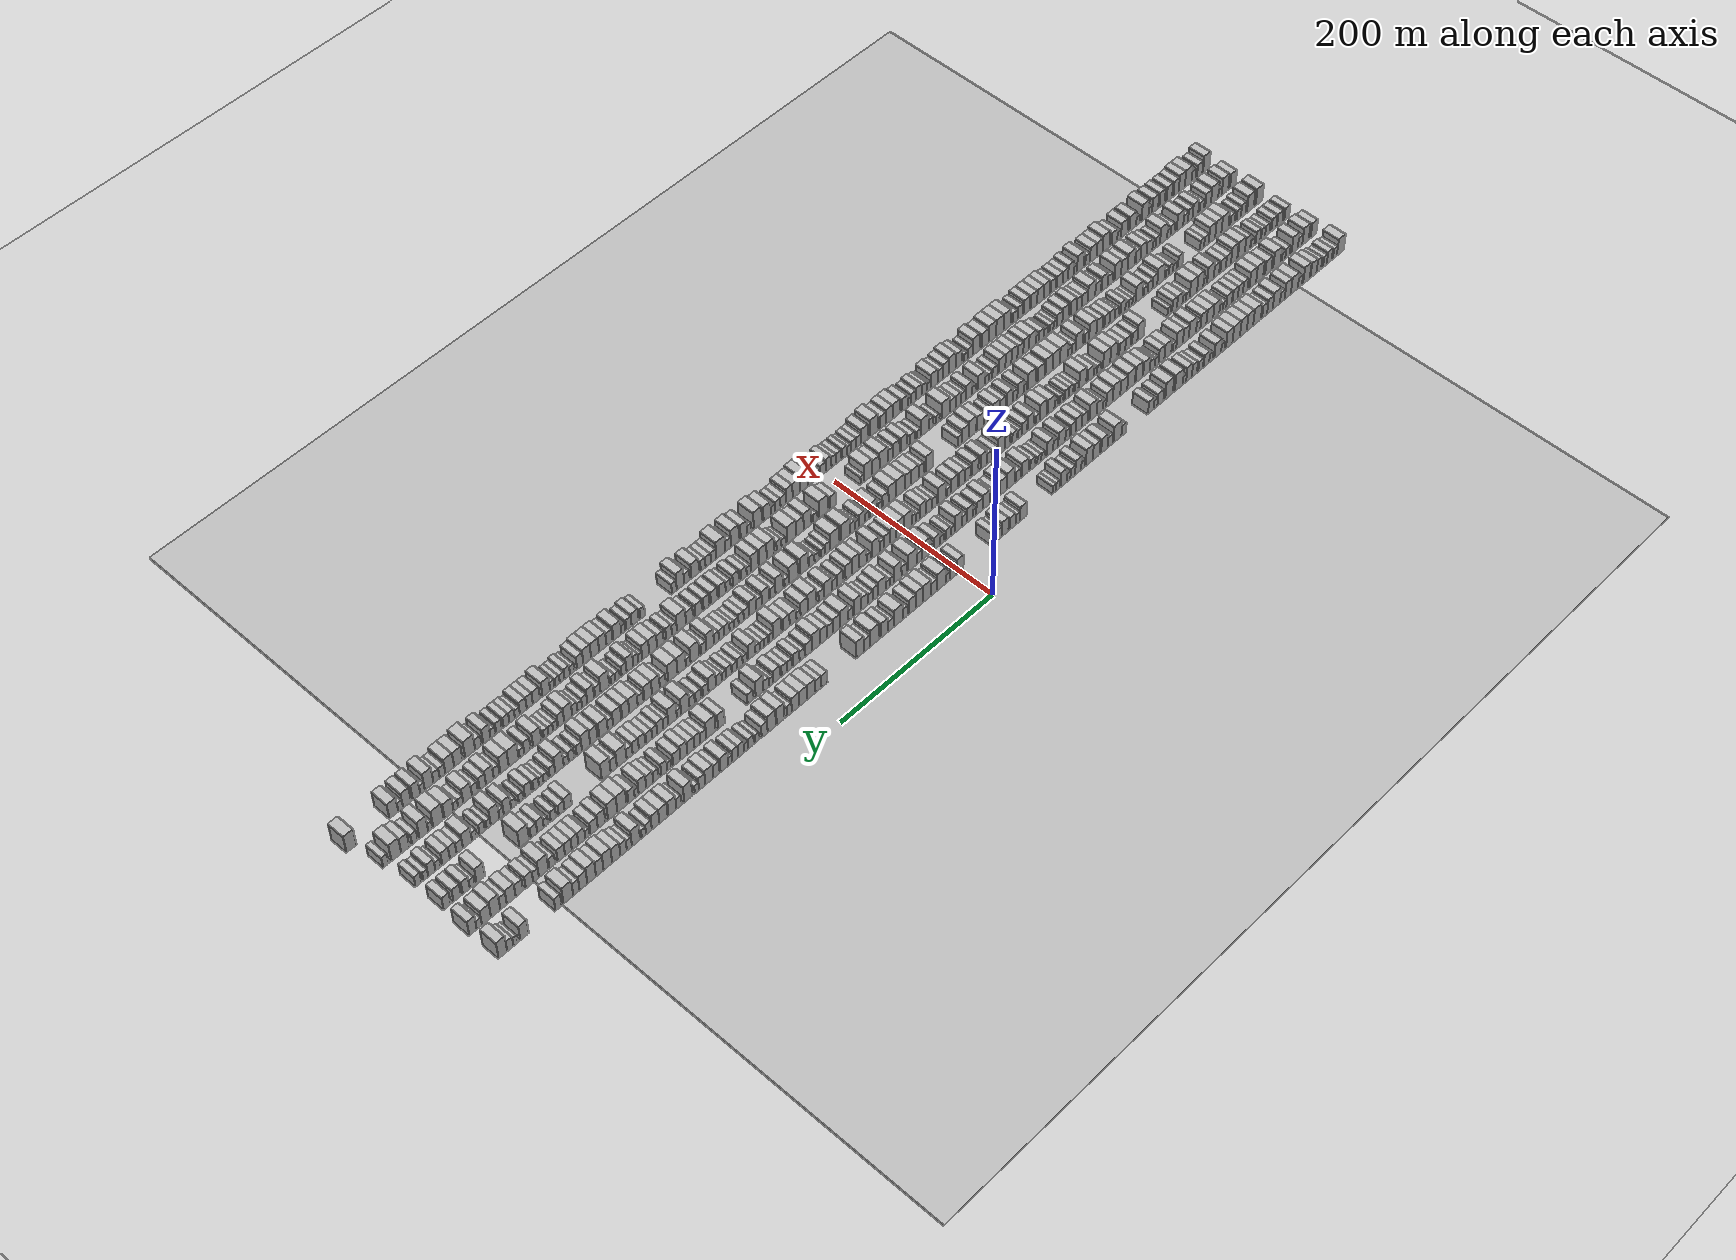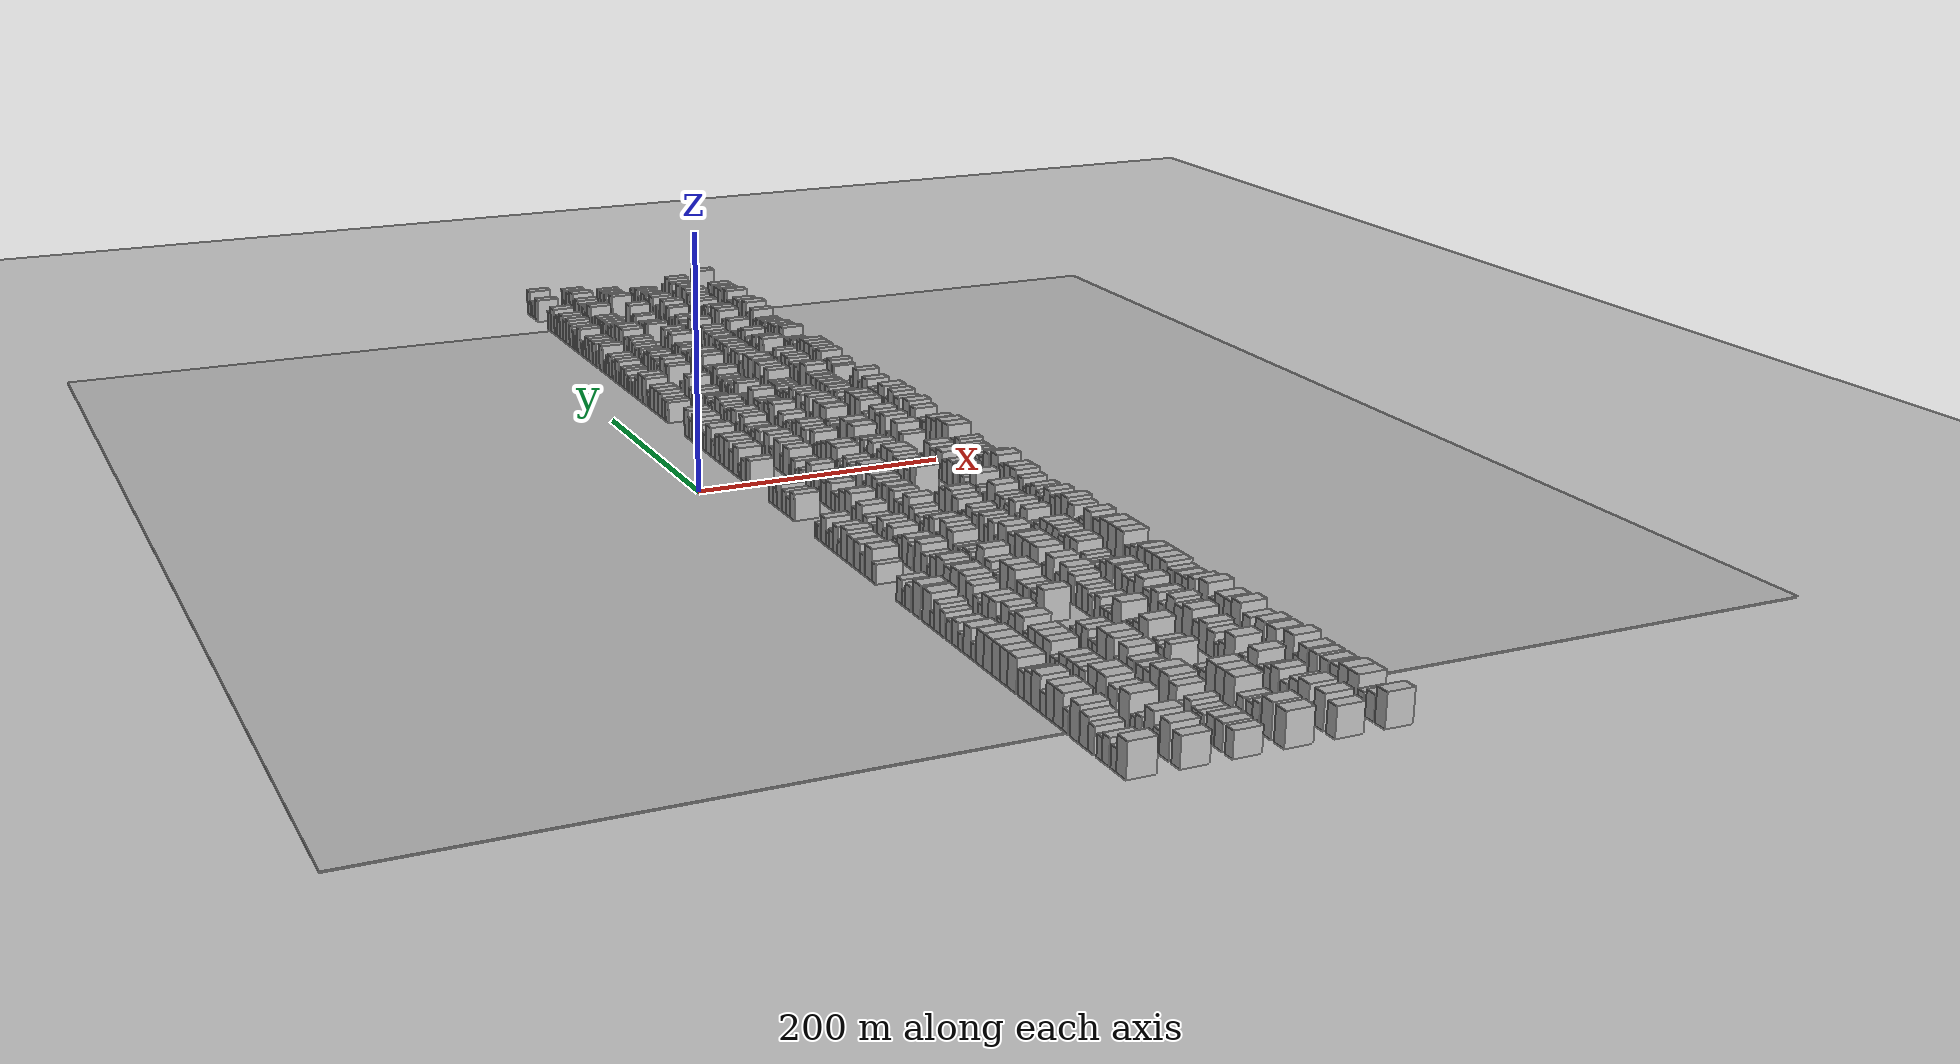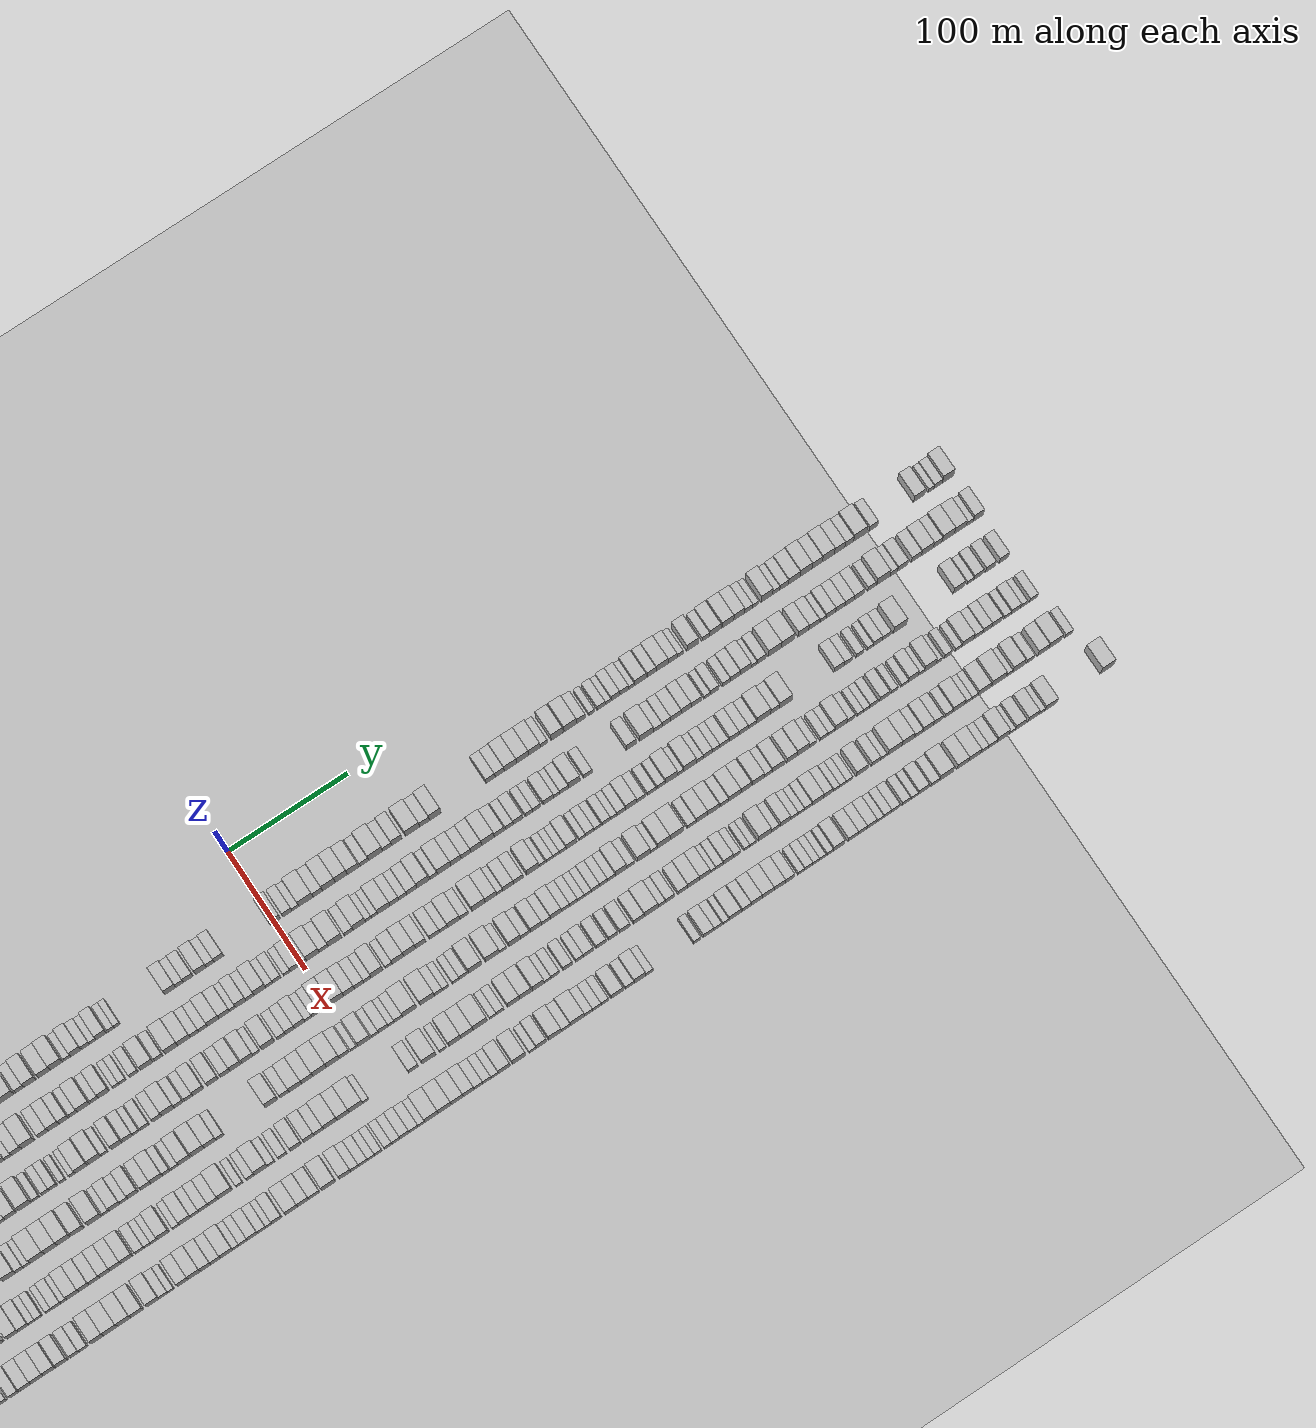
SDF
<?xml version="1.0" encoding="utf-8"?>

<sdf version="1.6">

   <world name="default">

      <gui fullscreen="0">

         <camera name="user_camera">

            <pose>-15 0 4.57585 0 0 0</pose>

            <view_controller>orbit</view_controller>

         </camera>

      </gui>

      <scene>

         <sky>

           <clouds>

             <speed>12</speed>

           </clouds>

         </sky>

         <ambient>0.4 0.4 0.4 1</ambient>

         <background>0.7 0.7 0.7 1</background>

         <shadows>1</shadows>

      </scene>

      <gravity>0 0 -9.8066</gravity>

      <magnetic_field>6e-06 2.3e-05 -4.2e-05</magnetic_field>

      <physics default="0" name="default_physics" type="ode">

         <ode>

            <solver>

               <type>quick</type>

               <iters>10</iters>

               <sor>1.0</sor>

               <use_dynamic_moi_rescaling>0</use_dynamic_moi_rescaling>

            </solver>

            <constraints>

               <cfm>0</cfm>

               <erp>0.2</erp>

               <contact_max_correcting_vel>100</contact_max_correcting_vel>

               <contact_surface_layer>0.001</contact_surface_layer>

            </constraints>

         </ode>

         <max_step_size>0.004</max_step_size>

         <real_time_factor>1</real_time_factor>

         <real_time_update_rate>250</real_time_update_rate>

      </physics>

      <light name="sun" type="directional">

         <cast_shadows>1</cast_shadows>

         <pose>0 0 10 0 0 0</pose>

         <diffuse>0.8 0.8 0.8 1</diffuse>

         <specular>0.2 0.2 0.2 1</specular>

         <attenuation>

            <range>1000</range>

            <constant>0.9</constant>

            <linear>0.01</linear>

            <quadratic>0.001</quadratic>

         </attenuation>

         <direction>-0.5 0.1 -0.9</direction>

      </light>

      <include>

         <name>ground_plane_1</name>

         <uri>model://HANNAS_ground_plane</uri>

         <pose>0 0 0  0 0 0</pose>

      </include>

      <include>

         <name>ground_plane_2</name>

         <uri>model://HANNAS_ground_plane</uri>

         <pose>100 0 0  0 0 0</pose>

      </include>

      <model name="building_1">

         <static>1</static>

         <pose frame="">50.0000 -564.4694 0 0.000000 0.000000 0.000000</pose>

         <link name="link">

            <pose frame="">0 0 12.00 0 0 0</pose>

            <collision name="collision">

               <geometry>

                  <box>

                     <size>20.0000 11.0612 24.0000</size>

                  </box>

               </geometry>

               <max_contacts>10</max_contacts>

               <surface>

                  <contact>

                     <ode/>

                  </contact>

                  <bounce/>

                  <friction>

                     <torsional>

                        <ode/>

                     </torsional>

                     <ode/>

                  </friction>

               </surface>

            </collision>

            <visual name="visual">

               <cast_shadows>0</cast_shadows>

               <geometry>

                  <box>

                     <size>20.0000 11.0612 24.0000</size>

                  </box>

               </geometry>

               <material>

                  <script>

                     <uri>model://HANNAS_wall/materials/scripts</uri>

                     <uri>model://HANNAS_wall/materials/textures</uri>

                     <name>vrc/HANNAS_wall</name>

                  </script>

               </material>

            </visual>

            <self_collide>0</self_collide>

            <enable_wind>0</enable_wind>

            <kinematic>0</kinematic>

         </link>

      </model>

      <model name="building_2">

         <static>1</static>

         <pose frame="">50.0000 -555.7566 0 0.000000 0.000000 0.000000</pose>

         <link name="link">

            <pose frame="">0 0 7.50 0 0 0</pose>

            <collision name="collision">

               <geometry>

                  <box>

                     <size>20.0000 6.3645 15.0000</size>

                  </box>

               </geometry>

               <max_contacts>10</max_contacts>

               <surface>

                  <contact>

                     <ode/>

                  </contact>

                  <bounce/>

                  <friction>

                     <torsional>

                        <ode/>

                     </torsional>

                     <ode/>

                  </friction>

               </surface>

            </collision>

            <visual name="visual">

               <cast_shadows>0</cast_shadows>

               <geometry>

                  <box>

                     <size>20.0000 6.3645 15.0000</size>

                  </box>

               </geometry>

               <material>

                  <script>

                     <uri>model://HANNAS_wall/materials/scripts</uri>

                     <uri>model://HANNAS_wall/materials/textures</uri>

                     <name>vrc/HANNAS_wall</name>

                  </script>

               </material>

            </visual>

            <self_collide>0</self_collide>

            <enable_wind>0</enable_wind>

            <kinematic>0</kinematic>

         </link>

      </model>

      <model name="building_3">

         <static>1</static>

         <pose frame="">50.0000 -546.5728 0 0.000000 0.000000 0.000000</pose>

         <link name="link">

            <pose frame="">0 0 9.00 0 0 0</pose>

            <collision name="collision">

               <geometry>

                  <box>

                     <size>20.0000 8.0031 18.0000</size>

                  </box>

               </geometry>

               <max_contacts>10</max_contacts>

               <surface>

                  <contact>

                     <ode/>

                  </contact>

                  <bounce/>

                  <friction>

                     <torsional>

                        <ode/>

                     </torsional>

                     <ode/>

                  </friction>

               </surface>

            </collision>

            <visual name="visual">

               <cast_shadows>0</cast_shadows>

               <geometry>

                  <box>

                     <size>20.0000 8.0031 18.0000</size>

                  </box>

               </geometry>

               <material>

                  <script>

                     <uri>model://HANNAS_wall/materials/scripts</uri>

                     <uri>model://HANNAS_wall/materials/textures</uri>

                     <name>vrc/HANNAS_wall</name>

                  </script>

               </material>

            </visual>

            <self_collide>0</self_collide>

            <enable_wind>0</enable_wind>

            <kinematic>0</kinematic>

         </link>

      </model>

      <model name="building_4">

         <static>1</static>

         <pose frame="">50.0000 -539.5409 0 0.000000 0.000000 0.000000</pose>

         <link name="link">

            <pose frame="">0 0 7.50 0 0 0</pose>

            <collision name="collision">

               <geometry>

                  <box>

                     <size>20.0000 6.0607 15.0000</size>

                  </box>

               </geometry>

               <max_contacts>10</max_contacts>

               <surface>

                  <contact>

                     <ode/>

                  </contact>

                  <bounce/>

                  <friction>

                     <torsional>

                        <ode/>

                     </torsional>

                     <ode/>

                  </friction>

               </surface>

            </collision>

            <visual name="visual">

               <cast_shadows>0</cast_shadows>

               <geometry>

                  <box>

                     <size>20.0000 6.0607 15.0000</size>

                  </box>

               </geometry>

               <material>

                  <script>

                     <uri>model://HANNAS_wall/materials/scripts</uri>

                     <uri>model://HANNAS_wall/materials/textures</uri>

                     <name>vrc/HANNAS_wall</name>

                  </script>

               </material>

            </visual>

            <self_collide>0</self_collide>

            <enable_wind>0</enable_wind>

            <kinematic>0</kinematic>

         </link>

      </model>

      <model name="building_5">

         <static>1</static>

         <pose frame="">50.0000 -529.8719 0 0.000000 0.000000 0.000000</pose>

         <link name="link">

            <pose frame="">0 0 9.00 0 0 0</pose>

            <collision name="collision">

               <geometry>

                  <box>

                     <size>20.0000 7.2773 18.0000</size>

                  </box>

               </geometry>

               <max_contacts>10</max_contacts>

               <surface>

                  <contact>

                     <ode/>

                  </contact>

                  <bounce/>

                  <friction>

                     <torsional>

                        <ode/>

                     </torsional>

                     <ode/>

                  </friction>

               </surface>

            </collision>

            <visual name="visual">

               <cast_shadows>0</cast_shadows>

               <geometry>

                  <box>

                     <size>20.0000 7.2773 18.0000</size>

                  </box>

               </geometry>

               <material>

                  <script>

                     <uri>model://HANNAS_wall/materials/scripts</uri>

                     <uri>model://HANNAS_wall/materials/textures</uri>

                     <name>vrc/HANNAS_wall</name>

                  </script>

               </material>

            </visual>

            <self_collide>0</self_collide>

            <enable_wind>0</enable_wind>

            <kinematic>0</kinematic>

         </link>

      </model>

      <model name="building_6">

         <static>1</static>

         <pose frame="">50.0000 -521.3168 0 0.000000 0.000000 0.000000</pose>

         <link name="link">

            <pose frame="">0 0 10.50 0 0 0</pose>

            <collision name="collision">

               <geometry>

                  <box>

                     <size>20.0000 9.8328 21.0000</size>

                  </box>

               </geometry>

               <max_contacts>10</max_contacts>

               <surface>

                  <contact>

                     <ode/>

                  </contact>

                  <bounce/>

                  <friction>

                     <torsional>

                        <ode/>

                     </torsional>

                     <ode/>

                  </friction>

               </surface>

            </collision>

            <visual name="visual">

               <cast_shadows>0</cast_shadows>

               <geometry>

                  <box>

                     <size>20.0000 9.8328 21.0000</size>

                  </box>

               </geometry>

               <material>

                  <script>

                     <uri>model://HANNAS_wall/materials/scripts</uri>

                     <uri>model://HANNAS_wall/materials/textures</uri>

                     <name>vrc/HANNAS_wall</name>

                  </script>

               </material>

            </visual>

            <self_collide>0</self_collide>

            <enable_wind>0</enable_wind>

            <kinematic>0</kinematic>

         </link>

      </model>

      <model name="building_7">

         <static>1</static>

         <pose frame="">50.0000 -510.0888 0 0.000000 0.000000 0.000000</pose>

         <link name="link">

            <pose frame="">0 0 12.00 0 0 0</pose>

            <collision name="collision">

               <geometry>

                  <box>

                     <size>20.0000 10.6232 24.0000</size>

                  </box>

               </geometry>

               <max_contacts>10</max_contacts>

               <surface>

                  <contact>

                     <ode/>

                  </contact>

                  <bounce/>

                  <friction>

                     <torsional>

                        <ode/>

                     </torsional>

                     <ode/>

                  </friction>

               </surface>

            </collision>

            <visual name="visual">

               <cast_shadows>0</cast_shadows>

               <geometry>

                  <box>

                     <size>20.0000 10.6232 24.0000</size>

                  </box>

               </geometry>

               <material>

                  <script>

                     <uri>model://HANNAS_wall/materials/scripts</uri>

                     <uri>model://HANNAS_wall/materials/textures</uri>

                     <name>vrc/HANNAS_wall</name>

                  </script>

               </material>

            </visual>

            <self_collide>0</self_collide>

            <enable_wind>0</enable_wind>

            <kinematic>0</kinematic>

         </link>

      </model>

      <model name="building_8">

         <static>1</static>

         <pose frame="">50.0000 -499.4686 0 0.000000 0.000000 0.000000</pose>

         <link name="link">

            <pose frame="">0 0 7.50 0 0 0</pose>

            <collision name="collision">

               <geometry>

                  <box>

                     <size>20.0000 6.6173 15.0000</size>

                  </box>

               </geometry>

               <max_contacts>10</max_contacts>

               <surface>

                  <contact>

                     <ode/>

                  </contact>

                  <bounce/>

                  <friction>

                     <torsional>

                        <ode/>

                     </torsional>

                     <ode/>

                  </friction>

               </surface>

            </collision>

            <visual name="visual">

               <cast_shadows>0</cast_shadows>

               <geometry>

                  <box>

                     <size>20.0000 6.6173 15.0000</size>

                  </box>

               </geometry>

               <material>

                  <script>

                     <uri>model://HANNAS_wall/materials/scripts</uri>

                     <uri>model://HANNAS_wall/materials/textures</uri>

                     <name>vrc/HANNAS_wall</name>

                  </script>

               </material>

            </visual>

            <self_collide>0</self_collide>

            <enable_wind>0</enable_wind>

            <kinematic>0</kinematic>

         </link>

      </model>

      <model name="building_9">

         <static>1</static>

         <pose frame="">50.0000 -490.6097 0 0.000000 0.000000 0.000000</pose>

         <link name="link">

            <pose frame="">0 0 12.00 0 0 0</pose>

            <collision name="collision">

               <geometry>

                  <box>

                     <size>20.0000 11.1005 24.0000</size>

                  </box>

               </geometry>

               <max_contacts>10</max_contacts>

               <surface>

                  <contact>

                     <ode/>

                  </contact>

                  <bounce/>

                  <friction>

                     <torsional>

                        <ode/>

                     </torsional>

                     <ode/>

                  </friction>

               </surface>

            </collision>

            <visual name="visual">

               <cast_shadows>0</cast_shadows>

               <geometry>

                  <box>

                     <size>20.0000 11.1005 24.0000</size>

                  </box>

               </geometry>

               <material>

                  <script>

                     <uri>model://HANNAS_wall/materials/scripts</uri>

                     <uri>model://HANNAS_wall/materials/textures</uri>

                     <name>vrc/HANNAS_wall</name>

                  </script>

               </material>

            </visual>

            <self_collide>0</self_collide>

            <enable_wind>0</enable_wind>

            <kinematic>0</kinematic>

         </link>

      </model>

      <model name="building_10">

         <static>1</static>

         <pose frame="">50.0000 -480.1993 0 0.000000 0.000000 0.000000</pose>

         <link name="link">

            <pose frame="">0 0 12.00 0 0 0</pose>

            <collision name="collision">

               <geometry>

                  <box>

                     <size>20.0000 9.7203 24.0000</size>

                  </box>

               </geometry>

               <max_contacts>10</max_contacts>

               <surface>

                  <contact>

                     <ode/>

                  </contact>

                  <bounce/>

                  <friction>

                     <torsional>

                        <ode/>

                     </torsional>

                     <ode/>

                  </friction>

               </surface>

            </collision>

            <visual name="visual">

               <cast_shadows>0</cast_shadows>

               <geometry>

                  <box>

                     <size>20.0000 9.7203 24.0000</size>

                  </box>

               </geometry>

               <material>

                  <script>

                     <uri>model://HANNAS_wall/materials/scripts</uri>

                     <uri>model://HANNAS_wall/materials/textures</uri>

                     <name>vrc/HANNAS_wall</name>

                  </script>

               </material>

            </visual>

            <self_collide>0</self_collide>

            <enable_wind>0</enable_wind>

            <kinematic>0</kinematic>

         </link>

      </model>

      <model name="building_11">

         <static>1</static>

         <pose frame="">50.0000 -471.6114 0 0.000000 0.000000 0.000000</pose>

         <link name="link">

            <pose frame="">0 0 7.50 0 0 0</pose>

            <collision name="collision">

               <geometry>

                  <box>

                     <size>20.0000 7.4555 15.0000</size>

                  </box>

               </geometry>

               <max_contacts>10</max_contacts>

               <surface>

                  <contact>

                     <ode/>

                  </contact>

                  <bounce/>

                  <friction>

                     <torsional>

                        <ode/>

                     </torsional>

                     <ode/>

                  </friction>

               </surface>

            </collision>

            <visual name="visual">

               <cast_shadows>0</cast_shadows>

               <geometry>

                  <box>

                     <size>20.0000 7.4555 15.0000</size>

                  </box>

               </geometry>

               <material>

                  <script>

                     <uri>model://HANNAS_wall/materials/scripts</uri>

                     <uri>model://HANNAS_wall/materials/textures</uri>

                     <name>vrc/HANNAS_wall</name>

                  </script>

               </material>

            </visual>

            <self_collide>0</self_collide>

            <enable_wind>0</enable_wind>

            <kinematic>0</kinematic>

         </link>

      </model>

      <model name="building_12">

         <static>1</static>

         <pose frame="">50.0000 -462.2677 0 0.000000 0.000000 0.000000</pose>

         <link name="link">

            <pose frame="">0 0 12.00 0 0 0</pose>

            <collision name="collision">

               <geometry>

                  <box>

                     <size>20.0000 11.2320 24.0000</size>

                  </box>

               </geometry>

               <max_contacts>10</max_contacts>

               <surface>

                  <contact>

                     <ode/>

                  </contact>

                  <bounce/>

                  <friction>

                     <torsional>

                        <ode/>

                     </torsional>

                     <ode/>

                  </friction>

               </surface>

            </collision>

            <visual name="visual">

               <cast_shadows>0</cast_shadows>

               <geometry>

                  <box>

                     <size>20.0000 11.2320 24.0000</size>

                  </box>

               </geometry>

               <material>

                  <script>

                     <uri>model://HANNAS_wall/materials/scripts</uri>

                     <uri>model://HANNAS_wall/materials/textures</uri>

                     <name>vrc/HANNAS_wall</name>

                  </script>

               </material>

            </visual>

            <self_collide>0</self_collide>

            <enable_wind>0</enable_wind>

            <kinematic>0</kinematic>

         </link>

      </model>

      <model name="building_13">

         <static>1</static>

         <pose frame="">50.0000 -452.2263 0 0.000000 0.000000 0.000000</pose>

         <link name="link">

            <pose frame="">0 0 10.50 0 0 0</pose>

            <collision name="collision">

               <geometry>

                  <box>

                     <size>20.0000 8.8507 21.0000</size>

                  </box>

               </geometry>

               <max_contacts>10</max_contacts>

               <surface>

                  <contact>

                     <ode/>

                  </contact>

                  <bounce/>

                  <friction>

                     <torsional>

                        <ode/>

                     </torsional>

                     <ode/>

                  </friction>

               </surface>

            </collision>

            <visual name="visual">

               <cast_shadows>0</cast_shadows>

               <geometry>

                  <box>

                     <size>20.0000 8.8507 21.0000</size>

                  </box>

               </geometry>

               <material>

                  <script>

                     <uri>model://HANNAS_wall/materials/scripts</uri>

                     <uri>model://HANNAS_wall/materials/textures</uri>

                     <name>vrc/HANNAS_wall</name>

                  </script>

               </material>

            </visual>

            <self_collide>0</self_collide>

            <enable_wind>0</enable_wind>

            <kinematic>0</kinematic>

         </link>

      </model>

      <model name="building_14">

         <static>1</static>

         <pose frame="">50.0000 -443.8816 0 0.000000 0.000000 0.000000</pose>

         <link name="link">

            <pose frame="">0 0 9.00 0 0 0</pose>

            <collision name="collision">

               <geometry>

                  <box>

                     <size>20.0000 7.8387 18.0000</size>

                  </box>

               </geometry>

               <max_contacts>10</max_contacts>

               <surface>

                  <contact>

                     <ode/>

                  </contact>

                  <bounce/>

                  <friction>

                     <torsional>

                        <ode/>

                     </torsional>

                     <ode/>

                  </friction>

               </surface>

            </collision>

            <visual name="visual">

               <cast_shadows>0</cast_shadows>

               <geometry>

                  <box>

                     <size>20.0000 7.8387 18.0000</size>

                  </box>

               </geometry>

               <material>

                  <script>

                     <uri>model://HANNAS_wall/materials/scripts</uri>

                     <uri>model://HANNAS_wall/materials/textures</uri>

                     <name>vrc/HANNAS_wall</name>

                  </script>

               </material>

            </visual>

            <self_collide>0</self_collide>

            <enable_wind>0</enable_wind>

            <kinematic>0</kinematic>

         </link>

      </model>

      <model name="building_15">

         <static>1</static>

         <pose frame="">50.0000 -432.0158 0 0.000000 0.000000 0.000000</pose>

         <link name="link">

            <pose frame="">0 0 12.00 0 0 0</pose>

            <collision name="collision">

               <geometry>

                  <box>

                     <size>20.0000 11.8929 24.0000</size>

                  </box>

               </geometry>

               <max_contacts>10</max_contacts>

               <surface>

                  <contact>

                     <ode/>

                  </contact>

                  <bounce/>

                  <friction>

                     <torsional>

                        <ode/>

                     </torsional>

                     <ode/>

                  </friction>

               </surface>

            </collision>

            <visual name="visual">

               <cast_shadows>0</cast_shadows>

               <geometry>

                  <box>

                     <size>20.0000 11.8929 24.0000</size>

                  </box>

               </geometry>

               <material>

                  <script>

                     <uri>model://HANNAS_wall/materials/scripts</uri>

                     <uri>model://HANNAS_wall/materials/textures</uri>

                     <name>vrc/HANNAS_wall</name>

                  </script>

               </material>

            </visual>

            <self_collide>0</self_collide>

            <enable_wind>0</enable_wind>

            <kinematic>0</kinematic>

         </link>

      </model>

      <model name="building_16">

         <static>1</static>

         <pose frame="">50.0000 -421.1257 0 0.000000 0.000000 0.000000</pose>

         <link name="link">

            <pose frame="">0 0 12.00 0 0 0</pose>

            <collision name="collision">

               <geometry>

                  <box>

                     <size>20.0000 9.8872 24.0000</size>

                  </box>

               </geometry>

               <max_contacts>10</max_contacts>

               <surface>

                  <contact>

                     <ode/>

                  </contact>

                  <bounce/>

                  <friction>

                     <torsional>

                        <ode/>

                     </torsional>

                     <ode/>

                  </friction>

               </surface>

            </collision>

            <visual name="visual">

               <cast_shadows>0</cast_shadows>

               <geometry>

                  <box>

                     <size>20.0000 9.8872 24.0000</size>

                  </box>

               </geometry>

               <material>

                  <script>

                     <uri>model://HANNAS_wall/materials/scripts</uri>

                     <uri>model://HANNAS_wall/materials/textures</uri>

                     <name>vrc/HANNAS_wall</name>

                  </script>

               </material>

            </visual>

            <self_collide>0</self_collide>

            <enable_wind>0</enable_wind>

            <kinematic>0</kinematic>

         </link>

      </model>

      <model name="building_17">

         <static>1</static>

         <pose frame="">50.0000 -410.8845 0 0.000000 0.000000 0.000000</pose>

         <link name="link">

            <pose frame="">0 0 12.00 0 0 0</pose>

            <collision name="collision">

               <geometry>

                  <box>

                     <size>20.0000 10.5951 24.0000</size>

                  </box>

               </geometry>

               <max_contacts>10</max_contacts>

               <surface>

                  <contact>

                     <ode/>

                  </contact>

                  <bounce/>

                  <friction>

                     <torsional>

                        <ode/>

                     </torsional>

                     <ode/>

                  </friction>

               </surface>

            </collision>

            <visual name="visual">

               <cast_shadows>0</cast_shadows>

               <geometry>

                  <box>

                     <size>20.0000 10.5951 24.0000</size>

                  </box>

               </geometry>

               <material>

                  <script>

                     <uri>model://HANNAS_wall/materials/scripts</uri>

                     <uri>model://HANNAS_wall/materials/textures</uri>

                     <name>vrc/HANNAS_wall</name>

                  </script>

               </material>

            </visual>

            <self_collide>0</self_collide>

            <enable_wind>0</enable_wind>

            <kinematic>0</kinematic>

         </link>

      </model>

      <model name="building_18">

         <static>1</static>

         <pose frame="">50.0000 -399.7800 0 0.000000 0.000000 0.000000</pose>

         <link name="link">

            <pose frame="">0 0 12.00 0 0 0</pose>

            <collision name="collision">

               <geometry>

                  <box>

                     <size>20.0000 11.6139 24.0000</size>

                  </box>

               </geometry>

               <max_contacts>10</max_contacts>

               <surface>

                  <contact>

                     <ode/>

                  </contact>

                  <bounce/>

                  <friction>

                     <torsional>

                        <ode/>

                     </torsional>

                     <ode/>

                  </friction>

               </surface>

            </collision>

            <visual name="visual">

               <cast_shadows>0</cast_shadows>

               <geometry>

                  <box>

                     <size>20.0000 11.6139 24.0000</size>

                  </box>

               </geometry>

               <material>

                  <script>

                     <uri>model://HANNAS_wall/materials/scripts</uri>

                     <uri>model://HANNAS_wall/materials/textures</uri>

                     <name>vrc/HANNAS_wall</name>

                  </script>

               </material>

            </visual>

            <self_collide>0</self_collide>

            <enable_wind>0</enable_wind>

            <kinematic>0</kinematic>

         </link>

      </model>

      <model name="building_19">

         <static>1</static>

         <pose frame="">50.0000 -388.9521 0 0.000000 0.000000 0.000000</pose>

         <link name="link">

            <pose frame="">0 0 12.00 0 0 0</pose>

            <collision name="collision">

               <geometry>

                  <box>

                     <size>20.0000 10.0421 24.0000</size>

                  </box>

               </geometry>

               <max_contacts>10</max_contacts>

               <surface>

                  <contact>

                     <ode/>

                  </contact>

                  <bounce/>

                  <friction>

                     <torsional>

                        <ode/>

                     </torsional>

                     <ode/>

                  </friction>

               </surface>

            </collision>

            <visual name="visual">

               <cast_shadows>0</cast_shadows>

               <geometry>

                  <box>

                     <size>20.0000 10.0421 24.0000</size>

                  </box>

               </geometry>

               <material>

                  <script>

                     <uri>model://HANNAS_wall/materials/scripts</uri>

                     <uri>model://HANNAS_wall/materials/textures</uri>

                     <name>vrc/HANNAS_wall</name>

                  </script>

               </material>

            </visual>

            <self_collide>0</self_collide>

            <enable_wind>0</enable_wind>

            <kinematic>0</kinematic>

         </link>

      </model>

      <model name="building_20">

         <static>1</static>

         <pose frame="">50.0000 -379.2220 0 0.000000 0.000000 0.000000</pose>

         <link name="link">

            <pose frame="">0 0 6.00 0 0 0</pose>

            <collision name="collision">

               <geometry>

                  <box>

                     <size>20.0000 5.4180 12.0000</size>

                  </box>

               </geometry>

               <max_contacts>10</max_contacts>

               <surface>

                  <contact>

                     <ode/>

                  </contact>

                  <bounce/>

                  <friction>

                     <torsional>

                        <ode/>

                     </torsional>

                     <ode/>

                  </friction>

               </surface>

            </collision>

            <visual name="visual">

               <cast_shadows>0</cast_shadows>

               <geometry>

                  <box>

                     <size>20.0000 5.4180 12.0000</size>

                  </box>

               </geometry>

               <material>

                  <script>

                     <uri>model://HANNAS_wall/materials/scripts</uri>

                     <uri>model://HANNAS_wall/materials/textures</uri>

                     <name>vrc/HANNAS_wall</name>

                  </script>

               </material>

            </visual>

            <self_collide>0</self_collide>

            <enable_wind>0</enable_wind>

            <kinematic>0</kinematic>

         </link>

      </model>

      <model name="building_21">

         <static>1</static>

         <pose frame="">50.0000 -371.3105 0 0.000000 0.000000 0.000000</pose>

         <link name="link">

            <pose frame="">0 0 10.50 0 0 0</pose>

            <collision name="collision">

               <geometry>

                  <box>

                     <size>20.0000 10.4052 21.0000</size>

                  </box>

               </geometry>

               <max_contacts>10</max_contacts>

               <surface>

                  <contact>

                     <ode/>

                  </contact>

                  <bounce/>

                  <friction>

                     <torsional>

                        <ode/>

                     </torsional>

                     <ode/>

                  </friction>

               </surface>

            </collision>

            <visual name="visual">

               <cast_shadows>0</cast_shadows>

               <geometry>

                  <box>

                     <size>20.0000 10.4052 21.0000</size>

                  </box>

               </geometry>

               <material>

                  <script>

                     <uri>model://HANNAS_wall/materials/scripts</uri>

                     <uri>model://HANNAS_wall/materials/textures</uri>

                     <name>vrc/HANNAS_wall</name>

                  </script>

               </material>

            </visual>

            <self_collide>0</self_collide>

            <enable_wind>0</enable_wind>

            <kinematic>0</kinematic>

         </link>

      </model>

      <model name="building_22">

         <static>1</static>

         <pose frame="">50.0000 -361.2589 0 0.000000 0.000000 0.000000</pose>

         <link name="link">

            <pose frame="">0 0 6.00 0 0 0</pose>

            <collision name="collision">

               <geometry>

                  <box>

                     <size>20.0000 5.6980 12.0000</size>

                  </box>

               </geometry>

               <max_contacts>10</max_contacts>

               <surface>

                  <contact>

                     <ode/>

                  </contact>

                  <bounce/>

                  <friction>

                     <torsional>

                        <ode/>

                     </torsional>

                     <ode/>

                  </friction>

               </surface>

            </collision>

            <visual name="visual">

               <cast_shadows>0</cast_shadows>

               <geometry>

                  <box>

                     <size>20.0000 5.6980 12.0000</size>

                  </box>

               </geometry>

               <material>

                  <script>

                     <uri>model://HANNAS_wall/materials/scripts</uri>

                     <uri>model://HANNAS_wall/materials/textures</uri>

                     <name>vrc/HANNAS_wall</name>

                  </script>

               </material>

            </visual>

            <self_collide>0</self_collide>

            <enable_wind>0</enable_wind>

            <kinematic>0</kinematic>

         </link>

      </model>

      <model name="building_23">

         <static>1</static>

         <pose frame="">50.0000 -354.0971 0 0.000000 0.000000 0.000000</pose>

         <link name="link">

            <pose frame="">0 0 9.00 0 0 0</pose>

            <collision name="collision">

               <geometry>

                  <box>

                     <size>20.0000 8.6257 18.0000</size>

                  </box>

               </geometry>

               <max_contacts>10</max_contacts>

               <surface>

                  <contact>

                     <ode/>

                  </contact>

                  <bounce/>

                  <friction>

                     <torsional>

                        <ode/>

                     </torsional>

                     <ode/>

                  </friction>

               </surface>

            </collision>

            <visual name="visual">

               <cast_shadows>0</cast_shadows>

               <geometry>

                  <box>

                     <size>20.0000 8.6257 18.0000</size>

                  </box>

               </geometry>

               <material>

                  <script>

                     <uri>model://HANNAS_wall/materials/scripts</uri>

                     <uri>model://HANNAS_wall/materials/textures</uri>

                     <name>vrc/HANNAS_wall</name>

                  </script>

               </material>

            </visual>

            <self_collide>0</self_collide>

            <enable_wind>0</enable_wind>

            <kinematic>0</kinematic>

         </link>

      </model>

      <model name="building_24">

         <static>1</static>

         <pose frame="">50.0000 -345.2818 0 0.000000 0.000000 0.000000</pose>

         <link name="link">

            <pose frame="">0 0 7.50 0 0 0</pose>

            <collision name="collision">

               <geometry>

                  <box>

                     <size>20.0000 7.0049 15.0000</size>

                  </box>

               </geometry>

               <max_contacts>10</max_contacts>

               <surface>

                  <contact>

                     <ode/>

                  </contact>

                  <bounce/>

                  <friction>

                     <torsional>

                        <ode/>

                     </torsional>

                     <ode/>

                  </friction>

               </surface>

            </collision>

            <visual name="visual">

               <cast_shadows>0</cast_shadows>

               <geometry>

                  <box>

                     <size>20.0000 7.0049 15.0000</size>

                  </box>

               </geometry>

               <material>

                  <script>

                     <uri>model://HANNAS_wall/materials/scripts</uri>

                     <uri>model://HANNAS_wall/materials/textures</uri>

                     <name>vrc/HANNAS_wall</name>

                  </script>

               </material>

            </visual>

            <self_collide>0</self_collide>

            <enable_wind>0</enable_wind>

            <kinematic>0</kinematic>

         </link>

      </model>

      <model name="building_25">

         <static>1</static>

         <pose frame="">50.0000 -335.9181 0 0.000000 0.000000 0.000000</pose>

         <link name="link">

            <pose frame="">0 0 9.00 0 0 0</pose>

            <collision name="collision">

               <geometry>

                  <box>

                     <size>20.0000 7.7223 18.0000</size>

                  </box>

               </geometry>

               <max_contacts>10</max_contacts>

               <surface>

                  <contact>

                     <ode/>

                  </contact>

                  <bounce/>

                  <friction>

                     <torsional>

                        <ode/>

                     </torsional>

                     <ode/>

                  </friction>

               </surface>

            </collision>

            <visual name="visual">

               <cast_shadows>0</cast_shadows>

               <geometry>

                  <box>

                     <size>20.0000 7.7223 18.0000</size>

                  </box>

               </geometry>

               <material>

                  <script>

                     <uri>model://HANNAS_wall/materials/scripts</uri>

                     <uri>model://HANNAS_wall/materials/textures</uri>

                     <name>vrc/HANNAS_wall</name>

                  </script>

               </material>

            </visual>

            <self_collide>0</self_collide>

            <enable_wind>0</enable_wind>

            <kinematic>0</kinematic>

         </link>

      </model>

      <model name="building_26">

         <static>1</static>

         <pose frame="">50.0000 -327.7426 0 0.000000 0.000000 0.000000</pose>

         <link name="link">

            <pose frame="">0 0 10.50 0 0 0</pose>

            <collision name="collision">

               <geometry>

                  <box>

                     <size>20.0000 8.6288 21.0000</size>

                  </box>

               </geometry>

               <max_contacts>10</max_contacts>

               <surface>

                  <contact>

                     <ode/>

                  </contact>

                  <bounce/>

                  <friction>

                     <torsional>

                        <ode/>

                     </torsional>

                     <ode/>

                  </friction>

               </surface>

            </collision>

            <visual name="visual">

               <cast_shadows>0</cast_shadows>

               <geometry>

                  <box>

                     <size>20.0000 8.6288 21.0000</size>

                  </box>

               </geometry>

               <material>

                  <script>

                     <uri>model://HANNAS_wall/materials/scripts</uri>

                     <uri>model://HANNAS_wall/materials/textures</uri>

                     <name>vrc/HANNAS_wall</name>

                  </script>

               </material>

            </visual>

            <self_collide>0</self_collide>

            <enable_wind>0</enable_wind>

            <kinematic>0</kinematic>

         </link>

      </model>

      <model name="building_27">

         <static>1</static>

         <pose frame="">50.0000 -320.8483 0 0.000000 0.000000 0.000000</pose>

         <link name="link">

            <pose frame="">0 0 6.00 0 0 0</pose>

            <collision name="collision">

               <geometry>

                  <box>

                     <size>20.0000 5.1598 12.0000</size>

                  </box>

               </geometry>

               <max_contacts>10</max_contacts>

               <surface>

                  <contact>

                     <ode/>

                  </contact>

                  <bounce/>

                  <friction>

                     <torsional>

                        <ode/>

                     </torsional>

                     <ode/>

                  </friction>

               </surface>

            </collision>

            <visual name="visual">

               <cast_shadows>0</cast_shadows>

               <geometry>

                  <box>

                     <size>20.0000 5.1598 12.0000</size>

                  </box>

               </geometry>

               <material>

                  <script>

                     <uri>model://HANNAS_wall/materials/scripts</uri>

                     <uri>model://HANNAS_wall/materials/textures</uri>

                     <name>vrc/HANNAS_wall</name>

                  </script>

               </material>

            </visual>

            <self_collide>0</self_collide>

            <enable_wind>0</enable_wind>

            <kinematic>0</kinematic>

         </link>

      </model>

      <model name="building_28">

         <static>1</static>

         <pose frame="">50.0000 -312.3385 0 0.000000 0.000000 0.000000</pose>

         <link name="link">

            <pose frame="">0 0 12.00 0 0 0</pose>

            <collision name="collision">

               <geometry>

                  <box>

                     <size>20.0000 11.8596 24.0000</size>

                  </box>

               </geometry>

               <max_contacts>10</max_contacts>

               <surface>

                  <contact>

                     <ode/>

                  </contact>

                  <bounce/>

                  <friction>

                     <torsional>

                        <ode/>

                     </torsional>

                     <ode/>

                  </friction>

               </surface>

            </collision>

            <visual name="visual">

               <cast_shadows>0</cast_shadows>

               <geometry>

                  <box>

                     <size>20.0000 11.8596 24.0000</size>

                  </box>

               </geometry>

               <material>

                  <script>

                     <uri>model://HANNAS_wall/materials/scripts</uri>

                     <uri>model://HANNAS_wall/materials/textures</uri>

                     <name>vrc/HANNAS_wall</name>

                  </script>

               </material>

            </visual>

            <self_collide>0</self_collide>

            <enable_wind>0</enable_wind>

            <kinematic>0</kinematic>

         </link>

      </model>

      <model name="building_29">

         <static>1</static>

         <pose frame="">50.0000 -297.6887 0 0.000000 0.000000 0.000000</pose>

         <link name="link">

            <pose frame="">0 0 12.00 0 0 0</pose>

            <collision name="collision">

               <geometry>

                  <box>

                     <size>20.0000 11.4401 24.0000</size>

                  </box>

               </geometry>

               <max_contacts>10</max_contacts>

               <surface>

                  <contact>

                     <ode/>

                  </contact>

                  <bounce/>

                  <friction>

                     <torsional>

                        <ode/>

                     </torsional>

                     <ode/>

                  </friction>

               </surface>

            </collision>

            <visual name="visual">

               <cast_shadows>0</cast_shadows>

               <geometry>

                  <box>

                     <size>20.0000 11.4401 24.0000</size>

                  </box>

               </geometry>

               <material>

                  <script>

                     <uri>model://HANNAS_wall/materials/scripts</uri>

                     <uri>model://HANNAS_wall/materials/textures</uri>

                     <name>vrc/HANNAS_wall</name>

                  </script>

               </material>

            </visual>

            <self_collide>0</self_collide>

            <enable_wind>0</enable_wind>

            <kinematic>0</kinematic>

         </link>

      </model>

      <model name="building_30">

         <static>1</static>

         <pose frame="">50.0000 -284.5930 0 0.000000 0.000000 0.000000</pose>

         <link name="link">

            <pose frame="">0 0 9.00 0 0 0</pose>

            <collision name="collision">

               <geometry>

                  <box>

                     <size>20.0000 8.7511 18.0000</size>

                  </box>

               </geometry>

               <max_contacts>10</max_contacts>

               <surface>

                  <contact>

                     <ode/>

                  </contact>

                  <bounce/>

                  <friction>

                     <torsional>

                        <ode/>

                     </torsional>

                     <ode/>

                  </friction>

               </surface>

            </collision>

            <visual name="visual">

               <cast_shadows>0</cast_shadows>

               <geometry>

                  <box>

                     <size>20.0000 8.7511 18.0000</size>

                  </box>

               </geometry>

               <material>

                  <script>

                     <uri>model://HANNAS_wall/materials/scripts</uri>

                     <uri>model://HANNAS_wall/materials/textures</uri>

                     <name>vrc/HANNAS_wall</name>

                  </script>

               </material>

            </visual>

            <self_collide>0</self_collide>

            <enable_wind>0</enable_wind>

            <kinematic>0</kinematic>

         </link>

      </model>

      <model name="building_31">

         <static>1</static>

         <pose frame="">50.0000 -277.4589 0 0.000000 0.000000 0.000000</pose>

         <link name="link">

            <pose frame="">0 0 6.00 0 0 0</pose>

            <collision name="collision">

               <geometry>

                  <box>

                     <size>20.0000 5.5171 12.0000</size>

                  </box>

               </geometry>

               <max_contacts>10</max_contacts>

               <surface>

                  <contact>

                     <ode/>

                  </contact>

                  <bounce/>

                  <friction>

                     <torsional>

                        <ode/>

                     </torsional>

                     <ode/>

                  </friction>

               </surface>

            </collision>

            <visual name="visual">

               <cast_shadows>0</cast_shadows>

               <geometry>

                  <box>

                     <size>20.0000 5.5171 12.0000</size>

                  </box>

               </geometry>

               <material>

                  <script>

                     <uri>model://HANNAS_wall/materials/scripts</uri>

                     <uri>model://HANNAS_wall/materials/textures</uri>

                     <name>vrc/HANNAS_wall</name>

                  </script>

               </material>

            </visual>

            <self_collide>0</self_collide>

            <enable_wind>0</enable_wind>

            <kinematic>0</kinematic>

         </link>

      </model>

      <model name="building_32">

         <static>1</static>

         <pose frame="">50.0000 -270.5538 0 0.000000 0.000000 0.000000</pose>

         <link name="link">

            <pose frame="">0 0 9.00 0 0 0</pose>

            <collision name="collision">

               <geometry>

                  <box>

                     <size>20.0000 8.2931 18.0000</size>

                  </box>

               </geometry>

               <max_contacts>10</max_contacts>

               <surface>

                  <contact>

                     <ode/>

                  </contact>

                  <bounce/>

                  <friction>

                     <torsional>

                        <ode/>

                     </torsional>

                     <ode/>

                  </friction>

               </surface>

            </collision>

            <visual name="visual">

               <cast_shadows>0</cast_shadows>

               <geometry>

                  <box>

                     <size>20.0000 8.2931 18.0000</size>

                  </box>

               </geometry>

               <material>

                  <script>

                     <uri>model://HANNAS_wall/materials/scripts</uri>

                     <uri>model://HANNAS_wall/materials/textures</uri>

                     <name>vrc/HANNAS_wall</name>

                  </script>

               </material>

            </visual>

            <self_collide>0</self_collide>

            <enable_wind>0</enable_wind>

            <kinematic>0</kinematic>

         </link>

      </model>

      <model name="building_33">

         <static>1</static>

         <pose frame="">50.0000 -230.4145 0 0.000000 0.000000 0.000000</pose>

         <link name="link">

            <pose frame="">0 0 7.50 0 0 0</pose>

            <collision name="collision">

               <geometry>

                  <box>

                     <size>20.0000 6.6618 15.0000</size>

                  </box>

               </geometry>

               <max_contacts>10</max_contacts>

               <surface>

                  <contact>

                     <ode/>

                  </contact>

                  <bounce/>

                  <friction>

                     <torsional>

                        <ode/>

                     </torsional>

                     <ode/>

                  </friction>

               </surface>

            </collision>

            <visual name="visual">

               <cast_shadows>0</cast_shadows>

               <geometry>

                  <box>

                     <size>20.0000 6.6618 15.0000</size>

                  </box>

               </geometry>

               <material>

                  <script>

                     <uri>model://HANNAS_wall/materials/scripts</uri>

                     <uri>model://HANNAS_wall/materials/textures</uri>

                     <name>vrc/HANNAS_wall</name>

                  </script>

               </material>

            </visual>

            <self_collide>0</self_collide>

            <enable_wind>0</enable_wind>

            <kinematic>0</kinematic>

         </link>

      </model>

      <model name="building_34">

         <static>1</static>

         <pose frame="">50.0000 -221.2916 0 0.000000 0.000000 0.000000</pose>

         <link name="link">

            <pose frame="">0 0 12.00 0 0 0</pose>

            <collision name="collision">

               <geometry>

                  <box>

                     <size>20.0000 11.5840 24.0000</size>

                  </box>

               </geometry>

               <max_contacts>10</max_contacts>

               <surface>

                  <contact>

                     <ode/>

                  </contact>

                  <bounce/>

                  <friction>

                     <torsional>

                        <ode/>

                     </torsional>

                     <ode/>

                  </friction>

               </surface>

            </collision>

            <visual name="visual">

               <cast_shadows>0</cast_shadows>

               <geometry>

                  <box>

                     <size>20.0000 11.5840 24.0000</size>

                  </box>

               </geometry>

               <material>

                  <script>

                     <uri>model://HANNAS_wall/materials/scripts</uri>

                     <uri>model://HANNAS_wall/materials/textures</uri>

                     <name>vrc/HANNAS_wall</name>

                  </script>

               </material>

            </visual>

            <self_collide>0</self_collide>

            <enable_wind>0</enable_wind>

            <kinematic>0</kinematic>

         </link>

      </model>

      <model name="building_35">

         <static>1</static>

         <pose frame="">50.0000 -210.8692 0 0.000000 0.000000 0.000000</pose>

         <link name="link">

            <pose frame="">0 0 7.50 0 0 0</pose>

            <collision name="collision">

               <geometry>

                  <box>

                     <size>20.0000 7.2609 15.0000</size>

                  </box>

               </geometry>

               <max_contacts>10</max_contacts>

               <surface>

                  <contact>

                     <ode/>

                  </contact>

                  <bounce/>

                  <friction>

                     <torsional>

                        <ode/>

                     </torsional>

                     <ode/>

                  </friction>

               </surface>

            </collision>

            <visual name="visual">

               <cast_shadows>0</cast_shadows>

               <geometry>

                  <box>

                     <size>20.0000 7.2609 15.0000</size>

                  </box>

               </geometry>

               <material>

                  <script>

                     <uri>model://HANNAS_wall/materials/scripts</uri>

                     <uri>model://HANNAS_wall/materials/textures</uri>

                     <name>vrc/HANNAS_wall</name>

                  </script>

               </material>

            </visual>

            <self_collide>0</self_collide>

            <enable_wind>0</enable_wind>

            <kinematic>0</kinematic>

         </link>

      </model>

      <model name="building_36">

         <static>1</static>

         <pose frame="">50.0000 -202.3744 0 0.000000 0.000000 0.000000</pose>

         <link name="link">

            <pose frame="">0 0 10.50 0 0 0</pose>

            <collision name="collision">

               <geometry>

                  <box>

                     <size>20.0000 9.7287 21.0000</size>

                  </box>

               </geometry>

               <max_contacts>10</max_contacts>

               <surface>

                  <contact>

                     <ode/>

                  </contact>

                  <bounce/>

                  <friction>

                     <torsional>

                        <ode/>

                     </torsional>

                     <ode/>

                  </friction>

               </surface>

            </collision>

            <visual name="visual">

               <cast_shadows>0</cast_shadows>

               <geometry>

                  <box>

                     <size>20.0000 9.7287 21.0000</size>

                  </box>

               </geometry>

               <material>

                  <script>

                     <uri>model://HANNAS_wall/materials/scripts</uri>

                     <uri>model://HANNAS_wall/materials/textures</uri>

                     <name>vrc/HANNAS_wall</name>

                  </script>

               </material>

            </visual>

            <self_collide>0</self_collide>

            <enable_wind>0</enable_wind>

            <kinematic>0</kinematic>

         </link>

      </model>

      <model name="building_37">

         <static>1</static>

         <pose frame="">50.0000 -190.4568 0 0.000000 0.000000 0.000000</pose>

         <link name="link">

            <pose frame="">0 0 10.50 0 0 0</pose>

            <collision name="collision">

               <geometry>

                  <box>

                     <size>20.0000 10.1066 21.0000</size>

                  </box>

               </geometry>

               <max_contacts>10</max_contacts>

               <surface>

                  <contact>

                     <ode/>

                  </contact>

                  <bounce/>

                  <friction>

                     <torsional>

                        <ode/>

                     </torsional>

                     <ode/>

                  </friction>

               </surface>

            </collision>

            <visual name="visual">

               <cast_shadows>0</cast_shadows>

               <geometry>

                  <box>

                     <size>20.0000 10.1066 21.0000</size>

                  </box>

               </geometry>

               <material>

                  <script>

                     <uri>model://HANNAS_wall/materials/scripts</uri>

                     <uri>model://HANNAS_wall/materials/textures</uri>

                     <name>vrc/HANNAS_wall</name>

                  </script>

               </material>

            </visual>

            <self_collide>0</self_collide>

            <enable_wind>0</enable_wind>

            <kinematic>0</kinematic>

         </link>

      </model>

      <model name="building_38">

         <static>1</static>

         <pose frame="">50.0000 -180.3454 0 0.000000 0.000000 0.000000</pose>

         <link name="link">

            <pose frame="">0 0 12.00 0 0 0</pose>

            <collision name="collision">

               <geometry>

                  <box>

                     <size>20.0000 10.1160 24.0000</size>

                  </box>

               </geometry>

               <max_contacts>10</max_contacts>

               <surface>

                  <contact>

                     <ode/>

                  </contact>

                  <bounce/>

                  <friction>

                     <torsional>

                        <ode/>

                     </torsional>

                     <ode/>

                  </friction>

               </surface>

            </collision>

            <visual name="visual">

               <cast_shadows>0</cast_shadows>

               <geometry>

                  <box>

                     <size>20.0000 10.1160 24.0000</size>

                  </box>

               </geometry>

               <material>

                  <script>

                     <uri>model://HANNAS_wall/materials/scripts</uri>

                     <uri>model://HANNAS_wall/materials/textures</uri>

                     <name>vrc/HANNAS_wall</name>

                  </script>

               </material>

            </visual>

            <self_collide>0</self_collide>

            <enable_wind>0</enable_wind>

            <kinematic>0</kinematic>

         </link>

      </model>

      <model name="building_39">

         <static>1</static>

         <pose frame="">50.0000 -171.4707 0 0.000000 0.000000 0.000000</pose>

         <link name="link">

            <pose frame="">0 0 6.00 0 0 0</pose>

            <collision name="collision">

               <geometry>

                  <box>

                     <size>20.0000 5.6335 12.0000</size>

                  </box>

               </geometry>

               <max_contacts>10</max_contacts>

               <surface>

                  <contact>

                     <ode/>

                  </contact>

                  <bounce/>

                  <friction>

                     <torsional>

                        <ode/>

                     </torsional>

                     <ode/>

                  </friction>

               </surface>

            </collision>

            <visual name="visual">

               <cast_shadows>0</cast_shadows>

               <geometry>

                  <box>

                     <size>20.0000 5.6335 12.0000</size>

                  </box>

               </geometry>

               <material>

                  <script>

                     <uri>model://HANNAS_wall/materials/scripts</uri>

                     <uri>model://HANNAS_wall/materials/textures</uri>

                     <name>vrc/HANNAS_wall</name>

                  </script>

               </material>

            </visual>

            <self_collide>0</self_collide>

            <enable_wind>0</enable_wind>

            <kinematic>0</kinematic>

         </link>

      </model>

      <model name="building_40">

         <static>1</static>

         <pose frame="">50.0000 -164.3087 0 0.000000 0.000000 0.000000</pose>

         <link name="link">

            <pose frame="">0 0 10.50 0 0 0</pose>

            <collision name="collision">

               <geometry>

                  <box>

                     <size>20.0000 8.6905 21.0000</size>

                  </box>

               </geometry>

               <max_contacts>10</max_contacts>

               <surface>

                  <contact>

                     <ode/>

                  </contact>

                  <bounce/>

                  <friction>

                     <torsional>

                        <ode/>

                     </torsional>

                     <ode/>

                  </friction>

               </surface>

            </collision>

            <visual name="visual">

               <cast_shadows>0</cast_shadows>

               <geometry>

                  <box>

                     <size>20.0000 8.6905 21.0000</size>

                  </box>

               </geometry>

               <material>

                  <script>

                     <uri>model://HANNAS_wall/materials/scripts</uri>

                     <uri>model://HANNAS_wall/materials/textures</uri>

                     <name>vrc/HANNAS_wall</name>

                  </script>

               </material>

            </visual>

            <self_collide>0</self_collide>

            <enable_wind>0</enable_wind>

            <kinematic>0</kinematic>

         </link>

      </model>

      <model name="building_41">

         <static>1</static>

         <pose frame="">50.0000 -156.5307 0 0.000000 0.000000 0.000000</pose>

         <link name="link">

            <pose frame="">0 0 7.50 0 0 0</pose>

            <collision name="collision">

               <geometry>

                  <box>

                     <size>20.0000 6.8655 15.0000</size>

                  </box>

               </geometry>

               <max_contacts>10</max_contacts>

               <surface>

                  <contact>

                     <ode/>

                  </contact>

                  <bounce/>

                  <friction>

                     <torsional>

                        <ode/>

                     </torsional>

                     <ode/>

                  </friction>

               </surface>

            </collision>

            <visual name="visual">

               <cast_shadows>0</cast_shadows>

               <geometry>

                  <box>

                     <size>20.0000 6.8655 15.0000</size>

                  </box>

               </geometry>

               <material>

                  <script>

                     <uri>model://HANNAS_wall/materials/scripts</uri>

                     <uri>model://HANNAS_wall/materials/textures</uri>

                     <name>vrc/HANNAS_wall</name>

                  </script>

               </material>

            </visual>

            <self_collide>0</self_collide>

            <enable_wind>0</enable_wind>

            <kinematic>0</kinematic>

         </link>

      </model>

      <model name="building_42">

         <static>1</static>

         <pose frame="">50.0000 -150.3775 0 0.000000 0.000000 0.000000</pose>

         <link name="link">

            <pose frame="">0 0 6.00 0 0 0</pose>

            <collision name="collision">

               <geometry>

                  <box>

                     <size>20.0000 5.4410 12.0000</size>

                  </box>

               </geometry>

               <max_contacts>10</max_contacts>

               <surface>

                  <contact>

                     <ode/>

                  </contact>

                  <bounce/>

                  <friction>

                     <torsional>

                        <ode/>

                     </torsional>

                     <ode/>

                  </friction>

               </surface>

            </collision>

            <visual name="visual">

               <cast_shadows>0</cast_shadows>

               <geometry>

                  <box>

                     <size>20.0000 5.4410 12.0000</size>

                  </box>

               </geometry>

               <material>

                  <script>

                     <uri>model://HANNAS_wall/materials/scripts</uri>

                     <uri>model://HANNAS_wall/materials/textures</uri>

                     <name>vrc/HANNAS_wall</name>

                  </script>

               </material>

            </visual>

            <self_collide>0</self_collide>

            <enable_wind>0</enable_wind>

            <kinematic>0</kinematic>

         </link>

      </model>

      <model name="building_43">

         <static>1</static>

         <pose frame="">50.0000 -143.3765 0 0.000000 0.000000 0.000000</pose>

         <link name="link">

            <pose frame="">0 0 10.50 0 0 0</pose>

            <collision name="collision">

               <geometry>

                  <box>

                     <size>20.0000 8.5609 21.0000</size>

                  </box>

               </geometry>

               <max_contacts>10</max_contacts>

               <surface>

                  <contact>

                     <ode/>

                  </contact>

                  <bounce/>

                  <friction>

                     <torsional>

                        <ode/>

                     </torsional>

                     <ode/>

                  </friction>

               </surface>

            </collision>

            <visual name="visual">

               <cast_shadows>0</cast_shadows>

               <geometry>

                  <box>

                     <size>20.0000 8.5609 21.0000</size>

                  </box>

               </geometry>

               <material>

                  <script>

                     <uri>model://HANNAS_wall/materials/scripts</uri>

                     <uri>model://HANNAS_wall/materials/textures</uri>

                     <name>vrc/HANNAS_wall</name>

                  </script>

               </material>

            </visual>

            <self_collide>0</self_collide>

            <enable_wind>0</enable_wind>

            <kinematic>0</kinematic>

         </link>

      </model>

      <model name="building_44">

         <static>1</static>

         <pose frame="">50.0000 -135.4817 0 0.000000 0.000000 0.000000</pose>

         <link name="link">

            <pose frame="">0 0 6.00 0 0 0</pose>

            <collision name="collision">

               <geometry>

                  <box>

                     <size>20.0000 5.2288 12.0000</size>

                  </box>

               </geometry>

               <max_contacts>10</max_contacts>

               <surface>

                  <contact>

                     <ode/>

                  </contact>

                  <bounce/>

                  <friction>

                     <torsional>

                        <ode/>

                     </torsional>

                     <ode/>

                  </friction>

               </surface>

            </collision>

            <visual name="visual">

               <cast_shadows>0</cast_shadows>

               <geometry>

                  <box>

                     <size>20.0000 5.2288 12.0000</size>

                  </box>

               </geometry>

               <material>

                  <script>

                     <uri>model://HANNAS_wall/materials/scripts</uri>

                     <uri>model://HANNAS_wall/materials/textures</uri>

                     <name>vrc/HANNAS_wall</name>

                  </script>

               </material>

            </visual>

            <self_collide>0</self_collide>

            <enable_wind>0</enable_wind>

            <kinematic>0</kinematic>

         </link>

      </model>

      <model name="building_45">

         <static>1</static>

         <pose frame="">50.0000 -130.4262 0 0.000000 0.000000 0.000000</pose>

         <link name="link">

            <pose frame="">0 0 6.00 0 0 0</pose>

            <collision name="collision">

               <geometry>

                  <box>

                     <size>20.0000 4.8821 12.0000</size>

                  </box>

               </geometry>

               <max_contacts>10</max_contacts>

               <surface>

                  <contact>

                     <ode/>

                  </contact>

                  <bounce/>

                  <friction>

                     <torsional>

                        <ode/>

                     </torsional>

                     <ode/>

                  </friction>

               </surface>

            </collision>

            <visual name="visual">

               <cast_shadows>0</cast_shadows>

               <geometry>

                  <box>

                     <size>20.0000 4.8821 12.0000</size>

                  </box>

               </geometry>

               <material>

                  <script>

                     <uri>model://HANNAS_wall/materials/scripts</uri>

                     <uri>model://HANNAS_wall/materials/textures</uri>

                     <name>vrc/HANNAS_wall</name>

                  </script>

               </material>

            </visual>

            <self_collide>0</self_collide>

            <enable_wind>0</enable_wind>

            <kinematic>0</kinematic>

         </link>

      </model>

      <model name="building_46">

         <static>1</static>

         <pose frame="">50.0000 -86.3542 0 0.000000 0.000000 0.000000</pose>

         <link name="link">

            <pose frame="">0 0 10.50 0 0 0</pose>

            <collision name="collision">

               <geometry>

                  <box>

                     <size>20.0000 9.0873 21.0000</size>

                  </box>

               </geometry>

               <max_contacts>10</max_contacts>

               <surface>

                  <contact>

                     <ode/>

                  </contact>

                  <bounce/>

                  <friction>

                     <torsional>

                        <ode/>

                     </torsional>

                     <ode/>

                  </friction>

               </surface>

            </collision>

            <visual name="visual">

               <cast_shadows>0</cast_shadows>

               <geometry>

                  <box>

                     <size>20.0000 9.0873 21.0000</size>

                  </box>

               </geometry>

               <material>

                  <script>

                     <uri>model://HANNAS_wall/materials/scripts</uri>

                     <uri>model://HANNAS_wall/materials/textures</uri>

                     <name>vrc/HANNAS_wall</name>

                  </script>

               </material>

            </visual>

            <self_collide>0</self_collide>

            <enable_wind>0</enable_wind>

            <kinematic>0</kinematic>

         </link>

      </model>

      <model name="building_47">

         <static>1</static>

         <pose frame="">50.0000 -78.6596 0 0.000000 0.000000 0.000000</pose>

         <link name="link">

            <pose frame="">0 0 7.50 0 0 0</pose>

            <collision name="collision">

               <geometry>

                  <box>

                     <size>20.0000 6.3020 15.0000</size>

                  </box>

               </geometry>

               <max_contacts>10</max_contacts>

               <surface>

                  <contact>

                     <ode/>

                  </contact>

                  <bounce/>

                  <friction>

                     <torsional>

                        <ode/>

                     </torsional>

                     <ode/>

                  </friction>

               </surface>

            </collision>

            <visual name="visual">

               <cast_shadows>0</cast_shadows>

               <geometry>

                  <box>

                     <size>20.0000 6.3020 15.0000</size>

                  </box>

               </geometry>

               <material>

                  <script>

                     <uri>model://HANNAS_wall/materials/scripts</uri>

                     <uri>model://HANNAS_wall/materials/textures</uri>

                     <name>vrc/HANNAS_wall</name>

                  </script>

               </material>

            </visual>

            <self_collide>0</self_collide>

            <enable_wind>0</enable_wind>

            <kinematic>0</kinematic>

         </link>

      </model>

      <model name="building_48">

         <static>1</static>

         <pose frame="">50.0000 -71.5418 0 0.000000 0.000000 0.000000</pose>

         <link name="link">

            <pose frame="">0 0 9.00 0 0 0</pose>

            <collision name="collision">

               <geometry>

                  <box>

                     <size>20.0000 7.9337 18.0000</size>

                  </box>

               </geometry>

               <max_contacts>10</max_contacts>

               <surface>

                  <contact>

                     <ode/>

                  </contact>

                  <bounce/>

                  <friction>

                     <torsional>

                        <ode/>

                     </torsional>

                     <ode/>

                  </friction>

               </surface>

            </collision>

            <visual name="visual">

               <cast_shadows>0</cast_shadows>

               <geometry>

                  <box>

                     <size>20.0000 7.9337 18.0000</size>

                  </box>

               </geometry>

               <material>

                  <script>

                     <uri>model://HANNAS_wall/materials/scripts</uri>

                     <uri>model://HANNAS_wall/materials/textures</uri>

                     <name>vrc/HANNAS_wall</name>

                  </script>

               </material>

            </visual>

            <self_collide>0</self_collide>

            <enable_wind>0</enable_wind>

            <kinematic>0</kinematic>

         </link>

      </model>

      <model name="building_49">

         <static>1</static>

         <pose frame="">50.0000 -61.0111 0 0.000000 0.000000 0.000000</pose>

         <link name="link">

            <pose frame="">0 0 10.50 0 0 0</pose>

            <collision name="collision">

               <geometry>

                  <box>

                     <size>20.0000 9.1278 21.0000</size>

                  </box>

               </geometry>

               <max_contacts>10</max_contacts>

               <surface>

                  <contact>

                     <ode/>

                  </contact>

                  <bounce/>

                  <friction>

                     <torsional>

                        <ode/>

                     </torsional>

                     <ode/>

                  </friction>

               </surface>

            </collision>

            <visual name="visual">

               <cast_shadows>0</cast_shadows>

               <geometry>

                  <box>

                     <size>20.0000 9.1278 21.0000</size>

                  </box>

               </geometry>

               <material>

                  <script>

                     <uri>model://HANNAS_wall/materials/scripts</uri>

                     <uri>model://HANNAS_wall/materials/textures</uri>

                     <name>vrc/HANNAS_wall</name>

                  </script>

               </material>

            </visual>

            <self_collide>0</self_collide>

            <enable_wind>0</enable_wind>

            <kinematic>0</kinematic>

         </link>

      </model>

      <model name="building_50">

         <static>1</static>

         <pose frame="">50.0000 -53.2371 0 0.000000 0.000000 0.000000</pose>

         <link name="link">

            <pose frame="">0 0 7.50 0 0 0</pose>

            <collision name="collision">

               <geometry>

                  <box>

                     <size>20.0000 6.4201 15.0000</size>

                  </box>

               </geometry>

               <max_contacts>10</max_contacts>

               <surface>

                  <contact>

                     <ode/>

                  </contact>

                  <bounce/>

                  <friction>

                     <torsional>

                        <ode/>

                     </torsional>

                     <ode/>

                  </friction>

               </surface>

            </collision>

            <visual name="visual">

               <cast_shadows>0</cast_shadows>

               <geometry>

                  <box>

                     <size>20.0000 6.4201 15.0000</size>

                  </box>

               </geometry>

               <material>

                  <script>

                     <uri>model://HANNAS_wall/materials/scripts</uri>

                     <uri>model://HANNAS_wall/materials/textures</uri>

                     <name>vrc/HANNAS_wall</name>

                  </script>

               </material>

            </visual>

            <self_collide>0</self_collide>

            <enable_wind>0</enable_wind>

            <kinematic>0</kinematic>

         </link>

      </model>

      <model name="building_51">

         <static>1</static>

         <pose frame="">50.0000 -46.0940 0 0.000000 0.000000 0.000000</pose>

         <link name="link">

            <pose frame="">0 0 9.00 0 0 0</pose>

            <collision name="collision">

               <geometry>

                  <box>

                     <size>20.0000 7.8661 18.0000</size>

                  </box>

               </geometry>

               <max_contacts>10</max_contacts>

               <surface>

                  <contact>

                     <ode/>

                  </contact>

                  <bounce/>

                  <friction>

                     <torsional>

                        <ode/>

                     </torsional>

                     <ode/>

                  </friction>

               </surface>

            </collision>

            <visual name="visual">

               <cast_shadows>0</cast_shadows>

               <geometry>

                  <box>

                     <size>20.0000 7.8661 18.0000</size>

                  </box>

               </geometry>

               <material>

                  <script>

                     <uri>model://HANNAS_wall/materials/scripts</uri>

                     <uri>model://HANNAS_wall/materials/textures</uri>

                     <name>vrc/HANNAS_wall</name>

                  </script>

               </material>

            </visual>

            <self_collide>0</self_collide>

            <enable_wind>0</enable_wind>

            <kinematic>0</kinematic>

         </link>

      </model>

      <model name="building_52">

         <static>1</static>

         <pose frame="">50.0000 0.8104 0 0.000000 0.000000 0.000000</pose>

         <link name="link">

            <pose frame="">0 0 10.50 0 0 0</pose>

            <collision name="collision">

               <geometry>

                  <box>

                     <size>20.0000 8.6476 21.0000</size>

                  </box>

               </geometry>

               <max_contacts>10</max_contacts>

               <surface>

                  <contact>

                     <ode/>

                  </contact>

                  <bounce/>

                  <friction>

                     <torsional>

                        <ode/>

                     </torsional>

                     <ode/>

                  </friction>

               </surface>

            </collision>

            <visual name="visual">

               <cast_shadows>0</cast_shadows>

               <geometry>

                  <box>

                     <size>20.0000 8.6476 21.0000</size>

                  </box>

               </geometry>

               <material>

                  <script>

                     <uri>model://HANNAS_wall/materials/scripts</uri>

                     <uri>model://HANNAS_wall/materials/textures</uri>

                     <name>vrc/HANNAS_wall</name>

                  </script>

               </material>

            </visual>

            <self_collide>0</self_collide>

            <enable_wind>0</enable_wind>

            <kinematic>0</kinematic>

         </link>

      </model>

      <model name="building_53">

         <static>1</static>

         <pose frame="">50.0000 10.9325 0 0.000000 0.000000 0.000000</pose>

         <link name="link">

            <pose frame="">0 0 9.00 0 0 0</pose>

            <collision name="collision">

               <geometry>

                  <box>

                     <size>20.0000 7.5967 18.0000</size>

                  </box>

               </geometry>

               <max_contacts>10</max_contacts>

               <surface>

                  <contact>

                     <ode/>

                  </contact>

                  <bounce/>

                  <friction>

                     <torsional>

                        <ode/>

                     </torsional>

                     <ode/>

                  </friction>

               </surface>

            </collision>

            <visual name="visual">

               <cast_shadows>0</cast_shadows>

               <geometry>

                  <box>

                     <size>20.0000 7.5967 18.0000</size>

                  </box>

               </geometry>

               <material>

                  <script>

                     <uri>model://HANNAS_wall/materials/scripts</uri>

                     <uri>model://HANNAS_wall/materials/textures</uri>

                     <name>vrc/HANNAS_wall</name>

                  </script>

               </material>

            </visual>

            <self_collide>0</self_collide>

            <enable_wind>0</enable_wind>

            <kinematic>0</kinematic>

         </link>

      </model>

      <model name="building_54">

         <static>1</static>

         <pose frame="">50.0000 17.5193 0 0.000000 0.000000 0.000000</pose>

         <link name="link">

            <pose frame="">0 0 6.00 0 0 0</pose>

            <collision name="collision">

               <geometry>

                  <box>

                     <size>20.0000 5.5769 12.0000</size>

                  </box>

               </geometry>

               <max_contacts>10</max_contacts>

               <surface>

                  <contact>

                     <ode/>

                  </contact>

                  <bounce/>

                  <friction>

                     <torsional>

                        <ode/>

                     </torsional>

                     <ode/>

                  </friction>

               </surface>

            </collision>

            <visual name="visual">

               <cast_shadows>0</cast_shadows>

               <geometry>

                  <box>

                     <size>20.0000 5.5769 12.0000</size>

                  </box>

               </geometry>

               <material>

                  <script>

                     <uri>model://HANNAS_wall/materials/scripts</uri>

                     <uri>model://HANNAS_wall/materials/textures</uri>

                     <name>vrc/HANNAS_wall</name>

                  </script>

               </material>

            </visual>

            <self_collide>0</self_collide>

            <enable_wind>0</enable_wind>

            <kinematic>0</kinematic>

         </link>

      </model>

      <model name="building_55">

         <static>1</static>

         <pose frame="">50.0000 26.2541 0 0.000000 0.000000 0.000000</pose>

         <link name="link">

            <pose frame="">0 0 12.00 0 0 0</pose>

            <collision name="collision">

               <geometry>

                  <box>

                     <size>20.0000 11.8926 24.0000</size>

                  </box>

               </geometry>

               <max_contacts>10</max_contacts>

               <surface>

                  <contact>

                     <ode/>

                  </contact>

                  <bounce/>

                  <friction>

                     <torsional>

                        <ode/>

                     </torsional>

                     <ode/>

                  </friction>

               </surface>

            </collision>

            <visual name="visual">

               <cast_shadows>0</cast_shadows>

               <geometry>

                  <box>

                     <size>20.0000 11.8926 24.0000</size>

                  </box>

               </geometry>

               <material>

                  <script>

                     <uri>model://HANNAS_wall/materials/scripts</uri>

                     <uri>model://HANNAS_wall/materials/textures</uri>

                     <name>vrc/HANNAS_wall</name>

                  </script>

               </material>

            </visual>

            <self_collide>0</self_collide>

            <enable_wind>0</enable_wind>

            <kinematic>0</kinematic>

         </link>

      </model>

      <model name="building_56">

         <static>1</static>

         <pose frame="">50.0000 36.1380 0 0.000000 0.000000 0.000000</pose>

         <link name="link">

            <pose frame="">0 0 9.00 0 0 0</pose>

            <collision name="collision">

               <geometry>

                  <box>

                     <size>20.0000 7.8752 18.0000</size>

                  </box>

               </geometry>

               <max_contacts>10</max_contacts>

               <surface>

                  <contact>

                     <ode/>

                  </contact>

                  <bounce/>

                  <friction>

                     <torsional>

                        <ode/>

                     </torsional>

                     <ode/>

                  </friction>

               </surface>

            </collision>

            <visual name="visual">

               <cast_shadows>0</cast_shadows>

               <geometry>

                  <box>

                     <size>20.0000 7.8752 18.0000</size>

                  </box>

               </geometry>

               <material>

                  <script>

                     <uri>model://HANNAS_wall/materials/scripts</uri>

                     <uri>model://HANNAS_wall/materials/textures</uri>

                     <name>vrc/HANNAS_wall</name>

                  </script>

               </material>

            </visual>

            <self_collide>0</self_collide>

            <enable_wind>0</enable_wind>

            <kinematic>0</kinematic>

         </link>

      </model>

      <model name="building_57">

         <static>1</static>

         <pose frame="">50.0000 45.4287 0 0.000000 0.000000 0.000000</pose>

         <link name="link">

            <pose frame="">0 0 12.00 0 0 0</pose>

            <collision name="collision">

               <geometry>

                  <box>

                     <size>20.0000 10.7063 24.0000</size>

                  </box>

               </geometry>

               <max_contacts>10</max_contacts>

               <surface>

                  <contact>

                     <ode/>

                  </contact>

                  <bounce/>

                  <friction>

                     <torsional>

                        <ode/>

                     </torsional>

                     <ode/>

                  </friction>

               </surface>

            </collision>

            <visual name="visual">

               <cast_shadows>0</cast_shadows>

               <geometry>

                  <box>

                     <size>20.0000 10.7063 24.0000</size>

                  </box>

               </geometry>

               <material>

                  <script>

                     <uri>model://HANNAS_wall/materials/scripts</uri>

                     <uri>model://HANNAS_wall/materials/textures</uri>

                     <name>vrc/HANNAS_wall</name>

                  </script>

               </material>

            </visual>

            <self_collide>0</self_collide>

            <enable_wind>0</enable_wind>

            <kinematic>0</kinematic>

         </link>

      </model>

      <model name="building_58">

         <static>1</static>

         <pose frame="">50.0000 55.7547 0 0.000000 0.000000 0.000000</pose>

         <link name="link">

            <pose frame="">0 0 12.00 0 0 0</pose>

            <collision name="collision">

               <geometry>

                  <box>

                     <size>20.0000 9.9456 24.0000</size>

                  </box>

               </geometry>

               <max_contacts>10</max_contacts>

               <surface>

                  <contact>

                     <ode/>

                  </contact>

                  <bounce/>

                  <friction>

                     <torsional>

                        <ode/>

                     </torsional>

                     <ode/>

                  </friction>

               </surface>

            </collision>

            <visual name="visual">

               <cast_shadows>0</cast_shadows>

               <geometry>

                  <box>

                     <size>20.0000 9.9456 24.0000</size>

                  </box>

               </geometry>

               <material>

                  <script>

                     <uri>model://HANNAS_wall/materials/scripts</uri>

                     <uri>model://HANNAS_wall/materials/textures</uri>

                     <name>vrc/HANNAS_wall</name>

                  </script>

               </material>

            </visual>

            <self_collide>0</self_collide>

            <enable_wind>0</enable_wind>

            <kinematic>0</kinematic>

         </link>

      </model>

      <model name="building_59">

         <static>1</static>

         <pose frame="">50.0000 65.5780 0 0.000000 0.000000 0.000000</pose>

         <link name="link">

            <pose frame="">0 0 10.50 0 0 0</pose>

            <collision name="collision">

               <geometry>

                  <box>

                     <size>20.0000 9.7010 21.0000</size>

                  </box>

               </geometry>

               <max_contacts>10</max_contacts>

               <surface>

                  <contact>

                     <ode/>

                  </contact>

                  <bounce/>

                  <friction>

                     <torsional>

                        <ode/>

                     </torsional>

                     <ode/>

                  </friction>

               </surface>

            </collision>

            <visual name="visual">

               <cast_shadows>0</cast_shadows>

               <geometry>

                  <box>

                     <size>20.0000 9.7010 21.0000</size>

                  </box>

               </geometry>

               <material>

                  <script>

                     <uri>model://HANNAS_wall/materials/scripts</uri>

                     <uri>model://HANNAS_wall/materials/textures</uri>

                     <name>vrc/HANNAS_wall</name>

                  </script>

               </material>

            </visual>

            <self_collide>0</self_collide>

            <enable_wind>0</enable_wind>

            <kinematic>0</kinematic>

         </link>

      </model>

      <model name="building_60">

         <static>1</static>

         <pose frame="">50.0000 74.9894 0 0.000000 0.000000 0.000000</pose>

         <link name="link">

            <pose frame="">0 0 7.50 0 0 0</pose>

            <collision name="collision">

               <geometry>

                  <box>

                     <size>20.0000 7.1218 15.0000</size>

                  </box>

               </geometry>

               <max_contacts>10</max_contacts>

               <surface>

                  <contact>

                     <ode/>

                  </contact>

                  <bounce/>

                  <friction>

                     <torsional>

                        <ode/>

                     </torsional>

                     <ode/>

                  </friction>

               </surface>

            </collision>

            <visual name="visual">

               <cast_shadows>0</cast_shadows>

               <geometry>

                  <box>

                     <size>20.0000 7.1218 15.0000</size>

                  </box>

               </geometry>

               <material>

                  <script>

                     <uri>model://HANNAS_wall/materials/scripts</uri>

                     <uri>model://HANNAS_wall/materials/textures</uri>

                     <name>vrc/HANNAS_wall</name>

                  </script>

               </material>

            </visual>

            <self_collide>0</self_collide>

            <enable_wind>0</enable_wind>

            <kinematic>0</kinematic>

         </link>

      </model>

      <model name="building_61">

         <static>1</static>

         <pose frame="">50.0000 84.4552 0 0.000000 0.000000 0.000000</pose>

         <link name="link">

            <pose frame="">0 0 12.00 0 0 0</pose>

            <collision name="collision">

               <geometry>

                  <box>

                     <size>20.0000 11.8098 24.0000</size>

                  </box>

               </geometry>

               <max_contacts>10</max_contacts>

               <surface>

                  <contact>

                     <ode/>

                  </contact>

                  <bounce/>

                  <friction>

                     <torsional>

                        <ode/>

                     </torsional>

                     <ode/>

                  </friction>

               </surface>

            </collision>

            <visual name="visual">

               <cast_shadows>0</cast_shadows>

               <geometry>

                  <box>

                     <size>20.0000 11.8098 24.0000</size>

                  </box>

               </geometry>

               <material>

                  <script>

                     <uri>model://HANNAS_wall/materials/scripts</uri>

                     <uri>model://HANNAS_wall/materials/textures</uri>

                     <name>vrc/HANNAS_wall</name>

                  </script>

               </material>

            </visual>

            <self_collide>0</self_collide>

            <enable_wind>0</enable_wind>

            <kinematic>0</kinematic>

         </link>

      </model>

      <model name="building_62">

         <static>1</static>

         <pose frame="">50.0000 94.0692 0 0.000000 0.000000 0.000000</pose>

         <link name="link">

            <pose frame="">0 0 7.50 0 0 0</pose>

            <collision name="collision">

               <geometry>

                  <box>

                     <size>20.0000 7.4182 15.0000</size>

                  </box>

               </geometry>

               <max_contacts>10</max_contacts>

               <surface>

                  <contact>

                     <ode/>

                  </contact>

                  <bounce/>

                  <friction>

                     <torsional>

                        <ode/>

                     </torsional>

                     <ode/>

                  </friction>

               </surface>

            </collision>

            <visual name="visual">

               <cast_shadows>0</cast_shadows>

               <geometry>

                  <box>

                     <size>20.0000 7.4182 15.0000</size>

                  </box>

               </geometry>

               <material>

                  <script>

                     <uri>model://HANNAS_wall/materials/scripts</uri>

                     <uri>model://HANNAS_wall/materials/textures</uri>

                     <name>vrc/HANNAS_wall</name>

                  </script>

               </material>

            </visual>

            <self_collide>0</self_collide>

            <enable_wind>0</enable_wind>

            <kinematic>0</kinematic>

         </link>

      </model>

      <model name="building_63">

         <static>1</static>

         <pose frame="">50.0000 102.1355 0 0.000000 0.000000 0.000000</pose>

         <link name="link">

            <pose frame="">0 0 10.50 0 0 0</pose>

            <collision name="collision">

               <geometry>

                  <box>

                     <size>20.0000 8.7144 21.0000</size>

                  </box>

               </geometry>

               <max_contacts>10</max_contacts>

               <surface>

                  <contact>

                     <ode/>

                  </contact>

                  <bounce/>

                  <friction>

                     <torsional>

                        <ode/>

                     </torsional>

                     <ode/>

                  </friction>

               </surface>

            </collision>

            <visual name="visual">

               <cast_shadows>0</cast_shadows>

               <geometry>

                  <box>

                     <size>20.0000 8.7144 21.0000</size>

                  </box>

               </geometry>

               <material>

                  <script>

                     <uri>model://HANNAS_wall/materials/scripts</uri>

                     <uri>model://HANNAS_wall/materials/textures</uri>

                     <name>vrc/HANNAS_wall</name>

                  </script>

               </material>

            </visual>

            <self_collide>0</self_collide>

            <enable_wind>0</enable_wind>

            <kinematic>0</kinematic>

         </link>

      </model>

      <model name="building_64">

         <static>1</static>

         <pose frame="">50.0000 115.3629 0 0.000000 0.000000 0.000000</pose>

         <link name="link">

            <pose frame="">0 0 12.00 0 0 0</pose>

            <collision name="collision">

               <geometry>

                  <box>

                     <size>20.0000 11.7403 24.0000</size>

                  </box>

               </geometry>

               <max_contacts>10</max_contacts>

               <surface>

                  <contact>

                     <ode/>

                  </contact>

                  <bounce/>

                  <friction>

                     <torsional>

                        <ode/>

                     </torsional>

                     <ode/>

                  </friction>

               </surface>

            </collision>

            <visual name="visual">

               <cast_shadows>0</cast_shadows>

               <geometry>

                  <box>

                     <size>20.0000 11.7403 24.0000</size>

                  </box>

               </geometry>

               <material>

                  <script>

                     <uri>model://HANNAS_wall/materials/scripts</uri>

                     <uri>model://HANNAS_wall/materials/textures</uri>

                     <name>vrc/HANNAS_wall</name>

                  </script>

               </material>

            </visual>

            <self_collide>0</self_collide>

            <enable_wind>0</enable_wind>

            <kinematic>0</kinematic>

         </link>

      </model>

      <model name="building_65">

         <static>1</static>

         <pose frame="">50.0000 125.3704 0 0.000000 0.000000 0.000000</pose>

         <link name="link">

            <pose frame="">0 0 9.00 0 0 0</pose>

            <collision name="collision">

               <geometry>

                  <box>

                     <size>20.0000 8.2746 18.0000</size>

                  </box>

               </geometry>

               <max_contacts>10</max_contacts>

               <surface>

                  <contact>

                     <ode/>

                  </contact>

                  <bounce/>

                  <friction>

                     <torsional>

                        <ode/>

                     </torsional>

                     <ode/>

                  </friction>

               </surface>

            </collision>

            <visual name="visual">

               <cast_shadows>0</cast_shadows>

               <geometry>

                  <box>

                     <size>20.0000 8.2746 18.0000</size>

                  </box>

               </geometry>

               <material>

                  <script>

                     <uri>model://HANNAS_wall/materials/scripts</uri>

                     <uri>model://HANNAS_wall/materials/textures</uri>

                     <name>vrc/HANNAS_wall</name>

                  </script>

               </material>

            </visual>

            <self_collide>0</self_collide>

            <enable_wind>0</enable_wind>

            <kinematic>0</kinematic>

         </link>

      </model>

      <model name="building_66">

         <static>1</static>

         <pose frame="">50.0000 134.3608 0 0.000000 0.000000 0.000000</pose>

         <link name="link">

            <pose frame="">0 0 12.00 0 0 0</pose>

            <collision name="collision">

               <geometry>

                  <box>

                     <size>20.0000 9.7062 24.0000</size>

                  </box>

               </geometry>

               <max_contacts>10</max_contacts>

               <surface>

                  <contact>

                     <ode/>

                  </contact>

                  <bounce/>

                  <friction>

                     <torsional>

                        <ode/>

                     </torsional>

                     <ode/>

                  </friction>

               </surface>

            </collision>

            <visual name="visual">

               <cast_shadows>0</cast_shadows>

               <geometry>

                  <box>

                     <size>20.0000 9.7062 24.0000</size>

                  </box>

               </geometry>

               <material>

                  <script>

                     <uri>model://HANNAS_wall/materials/scripts</uri>

                     <uri>model://HANNAS_wall/materials/textures</uri>

                     <name>vrc/HANNAS_wall</name>

                  </script>

               </material>

            </visual>

            <self_collide>0</self_collide>

            <enable_wind>0</enable_wind>

            <kinematic>0</kinematic>

         </link>

      </model>

      <model name="building_67">

         <static>1</static>

         <pose frame="">50.0000 180.7285 0 0.000000 0.000000 0.000000</pose>

         <link name="link">

            <pose frame="">0 0 9.00 0 0 0</pose>

            <collision name="collision">

               <geometry>

                  <box>

                     <size>20.0000 7.6764 18.0000</size>

                  </box>

               </geometry>

               <max_contacts>10</max_contacts>

               <surface>

                  <contact>

                     <ode/>

                  </contact>

                  <bounce/>

                  <friction>

                     <torsional>

                        <ode/>

                     </torsional>

                     <ode/>

                  </friction>

               </surface>

            </collision>

            <visual name="visual">

               <cast_shadows>0</cast_shadows>

               <geometry>

                  <box>

                     <size>20.0000 7.6764 18.0000</size>

                  </box>

               </geometry>

               <material>

                  <script>

                     <uri>model://HANNAS_wall/materials/scripts</uri>

                     <uri>model://HANNAS_wall/materials/textures</uri>

                     <name>vrc/HANNAS_wall</name>

                  </script>

               </material>

            </visual>

            <self_collide>0</self_collide>

            <enable_wind>0</enable_wind>

            <kinematic>0</kinematic>

         </link>

      </model>

      <model name="building_68">

         <static>1</static>

         <pose frame="">50.0000 188.4110 0 0.000000 0.000000 0.000000</pose>

         <link name="link">

            <pose frame="">0 0 9.00 0 0 0</pose>

            <collision name="collision">

               <geometry>

                  <box>

                     <size>20.0000 7.6885 18.0000</size>

                  </box>

               </geometry>

               <max_contacts>10</max_contacts>

               <surface>

                  <contact>

                     <ode/>

                  </contact>

                  <bounce/>

                  <friction>

                     <torsional>

                        <ode/>

                     </torsional>

                     <ode/>

                  </friction>

               </surface>

            </collision>

            <visual name="visual">

               <cast_shadows>0</cast_shadows>

               <geometry>

                  <box>

                     <size>20.0000 7.6885 18.0000</size>

                  </box>

               </geometry>

               <material>

                  <script>

                     <uri>model://HANNAS_wall/materials/scripts</uri>

                     <uri>model://HANNAS_wall/materials/textures</uri>

                     <name>vrc/HANNAS_wall</name>

                  </script>

               </material>

            </visual>

            <self_collide>0</self_collide>

            <enable_wind>0</enable_wind>

            <kinematic>0</kinematic>

         </link>

      </model>

      <model name="building_69">

         <static>1</static>

         <pose frame="">50.0000 197.4464 0 0.000000 0.000000 0.000000</pose>

         <link name="link">

            <pose frame="">0 0 10.50 0 0 0</pose>

            <collision name="collision">

               <geometry>

                  <box>

                     <size>20.0000 10.3824 21.0000</size>

                  </box>

               </geometry>

               <max_contacts>10</max_contacts>

               <surface>

                  <contact>

                     <ode/>

                  </contact>

                  <bounce/>

                  <friction>

                     <torsional>

                        <ode/>

                     </torsional>

                     <ode/>

                  </friction>

               </surface>

            </collision>

            <visual name="visual">

               <cast_shadows>0</cast_shadows>

               <geometry>

                  <box>

                     <size>20.0000 10.3824 21.0000</size>

                  </box>

               </geometry>

               <material>

                  <script>

                     <uri>model://HANNAS_wall/materials/scripts</uri>

                     <uri>model://HANNAS_wall/materials/textures</uri>

                     <name>vrc/HANNAS_wall</name>

                  </script>

               </material>

            </visual>

            <self_collide>0</self_collide>

            <enable_wind>0</enable_wind>

            <kinematic>0</kinematic>

         </link>

      </model>

      <model name="building_70">

         <static>1</static>

         <pose frame="">50.0000 207.7168 0 0.000000 0.000000 0.000000</pose>

         <link name="link">

            <pose frame="">0 0 10.50 0 0 0</pose>

            <collision name="collision">

               <geometry>

                  <box>

                     <size>20.0000 10.1584 21.0000</size>

                  </box>

               </geometry>

               <max_contacts>10</max_contacts>

               <surface>

                  <contact>

                     <ode/>

                  </contact>

                  <bounce/>

                  <friction>

                     <torsional>

                        <ode/>

                     </torsional>

                     <ode/>

                  </friction>

               </surface>

            </collision>

            <visual name="visual">

               <cast_shadows>0</cast_shadows>

               <geometry>

                  <box>

                     <size>20.0000 10.1584 21.0000</size>

                  </box>

               </geometry>

               <material>

                  <script>

                     <uri>model://HANNAS_wall/materials/scripts</uri>

                     <uri>model://HANNAS_wall/materials/textures</uri>

                     <name>vrc/HANNAS_wall</name>

                  </script>

               </material>

            </visual>

            <self_collide>0</self_collide>

            <enable_wind>0</enable_wind>

            <kinematic>0</kinematic>

         </link>

      </model>

      <model name="building_71">

         <static>1</static>

         <pose frame="">50.0000 217.6561 0 0.000000 0.000000 0.000000</pose>

         <link name="link">

            <pose frame="">0 0 10.50 0 0 0</pose>

            <collision name="collision">

               <geometry>

                  <box>

                     <size>20.0000 9.7201 21.0000</size>

                  </box>

               </geometry>

               <max_contacts>10</max_contacts>

               <surface>

                  <contact>

                     <ode/>

                  </contact>

                  <bounce/>

                  <friction>

                     <torsional>

                        <ode/>

                     </torsional>

                     <ode/>

                  </friction>

               </surface>

            </collision>

            <visual name="visual">

               <cast_shadows>0</cast_shadows>

               <geometry>

                  <box>

                     <size>20.0000 9.7201 21.0000</size>

                  </box>

               </geometry>

               <material>

                  <script>

                     <uri>model://HANNAS_wall/materials/scripts</uri>

                     <uri>model://HANNAS_wall/materials/textures</uri>

                     <name>vrc/HANNAS_wall</name>

                  </script>

               </material>

            </visual>

            <self_collide>0</self_collide>

            <enable_wind>0</enable_wind>

            <kinematic>0</kinematic>

         </link>

      </model>

      <model name="building_72">

         <static>1</static>

         <pose frame="">50.0000 225.5768 0 0.000000 0.000000 0.000000</pose>

         <link name="link">

            <pose frame="">0 0 7.50 0 0 0</pose>

            <collision name="collision">

               <geometry>

                  <box>

                     <size>20.0000 6.1212 15.0000</size>

                  </box>

               </geometry>

               <max_contacts>10</max_contacts>

               <surface>

                  <contact>

                     <ode/>

                  </contact>

                  <bounce/>

                  <friction>

                     <torsional>

                        <ode/>

                     </torsional>

                     <ode/>

                  </friction>

               </surface>

            </collision>

            <visual name="visual">

               <cast_shadows>0</cast_shadows>

               <geometry>

                  <box>

                     <size>20.0000 6.1212 15.0000</size>

                  </box>

               </geometry>

               <material>

                  <script>

                     <uri>model://HANNAS_wall/materials/scripts</uri>

                     <uri>model://HANNAS_wall/materials/textures</uri>

                     <name>vrc/HANNAS_wall</name>

                  </script>

               </material>

            </visual>

            <self_collide>0</self_collide>

            <enable_wind>0</enable_wind>

            <kinematic>0</kinematic>

         </link>

      </model>

      <model name="building_73">

         <static>1</static>

         <pose frame="">50.0000 236.5684 0 0.000000 0.000000 0.000000</pose>

         <link name="link">

            <pose frame="">0 0 12.00 0 0 0</pose>

            <collision name="collision">

               <geometry>

                  <box>

                     <size>20.0000 9.8622 24.0000</size>

                  </box>

               </geometry>

               <max_contacts>10</max_contacts>

               <surface>

                  <contact>

                     <ode/>

                  </contact>

                  <bounce/>

                  <friction>

                     <torsional>

                        <ode/>

                     </torsional>

                     <ode/>

                  </friction>

               </surface>

            </collision>

            <visual name="visual">

               <cast_shadows>0</cast_shadows>

               <geometry>

                  <box>

                     <size>20.0000 9.8622 24.0000</size>

                  </box>

               </geometry>

               <material>

                  <script>

                     <uri>model://HANNAS_wall/materials/scripts</uri>

                     <uri>model://HANNAS_wall/materials/textures</uri>

                     <name>vrc/HANNAS_wall</name>

                  </script>

               </material>

            </visual>

            <self_collide>0</self_collide>

            <enable_wind>0</enable_wind>

            <kinematic>0</kinematic>

         </link>

      </model>

      <model name="building_74">

         <static>1</static>

         <pose frame="">50.0000 247.7306 0 0.000000 0.000000 0.000000</pose>

         <link name="link">

            <pose frame="">0 0 12.00 0 0 0</pose>

            <collision name="collision">

               <geometry>

                  <box>

                     <size>20.0000 10.4623 24.0000</size>

                  </box>

               </geometry>

               <max_contacts>10</max_contacts>

               <surface>

                  <contact>

                     <ode/>

                  </contact>

                  <bounce/>

                  <friction>

                     <torsional>

                        <ode/>

                     </torsional>

                     <ode/>

                  </friction>

               </surface>

            </collision>

            <visual name="visual">

               <cast_shadows>0</cast_shadows>

               <geometry>

                  <box>

                     <size>20.0000 10.4623 24.0000</size>

                  </box>

               </geometry>

               <material>

                  <script>

                     <uri>model://HANNAS_wall/materials/scripts</uri>

                     <uri>model://HANNAS_wall/materials/textures</uri>

                     <name>vrc/HANNAS_wall</name>

                  </script>

               </material>

            </visual>

            <self_collide>0</self_collide>

            <enable_wind>0</enable_wind>

            <kinematic>0</kinematic>

         </link>

      </model>

      <model name="building_75">

         <static>1</static>

         <pose frame="">50.0000 256.7240 0 0.000000 0.000000 0.000000</pose>

         <link name="link">

            <pose frame="">0 0 9.00 0 0 0</pose>

            <collision name="collision">

               <geometry>

                  <box>

                     <size>20.0000 7.5244 18.0000</size>

                  </box>

               </geometry>

               <max_contacts>10</max_contacts>

               <surface>

                  <contact>

                     <ode/>

                  </contact>

                  <bounce/>

                  <friction>

                     <torsional>

                        <ode/>

                     </torsional>

                     <ode/>

                  </friction>

               </surface>

            </collision>

            <visual name="visual">

               <cast_shadows>0</cast_shadows>

               <geometry>

                  <box>

                     <size>20.0000 7.5244 18.0000</size>

                  </box>

               </geometry>

               <material>

                  <script>

                     <uri>model://HANNAS_wall/materials/scripts</uri>

                     <uri>model://HANNAS_wall/materials/textures</uri>

                     <name>vrc/HANNAS_wall</name>

                  </script>

               </material>

            </visual>

            <self_collide>0</self_collide>

            <enable_wind>0</enable_wind>

            <kinematic>0</kinematic>

         </link>

      </model>

      <model name="building_76">

         <static>1</static>

         <pose frame="">50.0000 265.9073 0 0.000000 0.000000 0.000000</pose>

         <link name="link">

            <pose frame="">0 0 6.00 0 0 0</pose>

            <collision name="collision">

               <geometry>

                  <box>

                     <size>20.0000 4.8422 12.0000</size>

                  </box>

               </geometry>

               <max_contacts>10</max_contacts>

               <surface>

                  <contact>

                     <ode/>

                  </contact>

                  <bounce/>

                  <friction>

                     <torsional>

                        <ode/>

                     </torsional>

                     <ode/>

                  </friction>

               </surface>

            </collision>

            <visual name="visual">

               <cast_shadows>0</cast_shadows>

               <geometry>

                  <box>

                     <size>20.0000 4.8422 12.0000</size>

                  </box>

               </geometry>

               <material>

                  <script>

                     <uri>model://HANNAS_wall/materials/scripts</uri>

                     <uri>model://HANNAS_wall/materials/textures</uri>

                     <name>vrc/HANNAS_wall</name>

                  </script>

               </material>

            </visual>

            <self_collide>0</self_collide>

            <enable_wind>0</enable_wind>

            <kinematic>0</kinematic>

         </link>

      </model>

      <model name="building_77">

         <static>1</static>

         <pose frame="">50.0000 273.8192 0 0.000000 0.000000 0.000000</pose>

         <link name="link">

            <pose frame="">0 0 7.50 0 0 0</pose>

            <collision name="collision">

               <geometry>

                  <box>

                     <size>20.0000 6.9817 15.0000</size>

                  </box>

               </geometry>

               <max_contacts>10</max_contacts>

               <surface>

                  <contact>

                     <ode/>

                  </contact>

                  <bounce/>

                  <friction>

                     <torsional>

                        <ode/>

                     </torsional>

                     <ode/>

                  </friction>

               </surface>

            </collision>

            <visual name="visual">

               <cast_shadows>0</cast_shadows>

               <geometry>

                  <box>

                     <size>20.0000 6.9817 15.0000</size>

                  </box>

               </geometry>

               <material>

                  <script>

                     <uri>model://HANNAS_wall/materials/scripts</uri>

                     <uri>model://HANNAS_wall/materials/textures</uri>

                     <name>vrc/HANNAS_wall</name>

                  </script>

               </material>

            </visual>

            <self_collide>0</self_collide>

            <enable_wind>0</enable_wind>

            <kinematic>0</kinematic>

         </link>

      </model>

      <model name="building_78">

         <static>1</static>

         <pose frame="">50.0000 279.7344 0 0.000000 0.000000 0.000000</pose>

         <link name="link">

            <pose frame="">0 0 6.00 0 0 0</pose>

            <collision name="collision">

               <geometry>

                  <box>

                     <size>20.0000 4.8487 12.0000</size>

                  </box>

               </geometry>

               <max_contacts>10</max_contacts>

               <surface>

                  <contact>

                     <ode/>

                  </contact>

                  <bounce/>

                  <friction>

                     <torsional>

                        <ode/>

                     </torsional>

                     <ode/>

                  </friction>

               </surface>

            </collision>

            <visual name="visual">

               <cast_shadows>0</cast_shadows>

               <geometry>

                  <box>

                     <size>20.0000 4.8487 12.0000</size>

                  </box>

               </geometry>

               <material>

                  <script>

                     <uri>model://HANNAS_wall/materials/scripts</uri>

                     <uri>model://HANNAS_wall/materials/textures</uri>

                     <name>vrc/HANNAS_wall</name>

                  </script>

               </material>

            </visual>

            <self_collide>0</self_collide>

            <enable_wind>0</enable_wind>

            <kinematic>0</kinematic>

         </link>

      </model>

      <model name="building_79">

         <static>1</static>

         <pose frame="">50.0000 285.9103 0 0.000000 0.000000 0.000000</pose>

         <link name="link">

            <pose frame="">0 0 9.00 0 0 0</pose>

            <collision name="collision">

               <geometry>

                  <box>

                     <size>20.0000 7.5031 18.0000</size>

                  </box>

               </geometry>

               <max_contacts>10</max_contacts>

               <surface>

                  <contact>

                     <ode/>

                  </contact>

                  <bounce/>

                  <friction>

                     <torsional>

                        <ode/>

                     </torsional>

                     <ode/>

                  </friction>

               </surface>

            </collision>

            <visual name="visual">

               <cast_shadows>0</cast_shadows>

               <geometry>

                  <box>

                     <size>20.0000 7.5031 18.0000</size>

                  </box>

               </geometry>

               <material>

                  <script>

                     <uri>model://HANNAS_wall/materials/scripts</uri>

                     <uri>model://HANNAS_wall/materials/textures</uri>

                     <name>vrc/HANNAS_wall</name>

                  </script>

               </material>

            </visual>

            <self_collide>0</self_collide>

            <enable_wind>0</enable_wind>

            <kinematic>0</kinematic>

         </link>

      </model>

      <model name="building_80">

         <static>1</static>

         <pose frame="">50.0000 293.3218 0 0.000000 0.000000 0.000000</pose>

         <link name="link">

            <pose frame="">0 0 9.00 0 0 0</pose>

            <collision name="collision">

               <geometry>

                  <box>

                     <size>20.0000 7.3199 18.0000</size>

                  </box>

               </geometry>

               <max_contacts>10</max_contacts>

               <surface>

                  <contact>

                     <ode/>

                  </contact>

                  <bounce/>

                  <friction>

                     <torsional>

                        <ode/>

                     </torsional>

                     <ode/>

                  </friction>

               </surface>

            </collision>

            <visual name="visual">

               <cast_shadows>0</cast_shadows>

               <geometry>

                  <box>

                     <size>20.0000 7.3199 18.0000</size>

                  </box>

               </geometry>

               <material>

                  <script>

                     <uri>model://HANNAS_wall/materials/scripts</uri>

                     <uri>model://HANNAS_wall/materials/textures</uri>

                     <name>vrc/HANNAS_wall</name>

                  </script>

               </material>

            </visual>

            <self_collide>0</self_collide>

            <enable_wind>0</enable_wind>

            <kinematic>0</kinematic>

         </link>

      </model>

      <model name="building_81">

         <static>1</static>

         <pose frame="">50.0000 299.4504 0 0.000000 0.000000 0.000000</pose>

         <link name="link">

            <pose frame="">0 0 6.00 0 0 0</pose>

            <collision name="collision">

               <geometry>

                  <box>

                     <size>20.0000 4.9373 12.0000</size>

                  </box>

               </geometry>

               <max_contacts>10</max_contacts>

               <surface>

                  <contact>

                     <ode/>

                  </contact>

                  <bounce/>

                  <friction>

                     <torsional>

                        <ode/>

                     </torsional>

                     <ode/>

                  </friction>

               </surface>

            </collision>

            <visual name="visual">

               <cast_shadows>0</cast_shadows>

               <geometry>

                  <box>

                     <size>20.0000 4.9373 12.0000</size>

                  </box>

               </geometry>

               <material>

                  <script>

                     <uri>model://HANNAS_wall/materials/scripts</uri>

                     <uri>model://HANNAS_wall/materials/textures</uri>

                     <name>vrc/HANNAS_wall</name>

                  </script>

               </material>

            </visual>

            <self_collide>0</self_collide>

            <enable_wind>0</enable_wind>

            <kinematic>0</kinematic>

         </link>

      </model>

      <model name="building_82">

         <static>1</static>

         <pose frame="">50.0000 306.7969 0 0.000000 0.000000 0.000000</pose>

         <link name="link">

            <pose frame="">0 0 10.50 0 0 0</pose>

            <collision name="collision">

               <geometry>

                  <box>

                     <size>20.0000 9.7556 21.0000</size>

                  </box>

               </geometry>

               <max_contacts>10</max_contacts>

               <surface>

                  <contact>

                     <ode/>

                  </contact>

                  <bounce/>

                  <friction>

                     <torsional>

                        <ode/>

                     </torsional>

                     <ode/>

                  </friction>

               </surface>

            </collision>

            <visual name="visual">

               <cast_shadows>0</cast_shadows>

               <geometry>

                  <box>

                     <size>20.0000 9.7556 21.0000</size>

                  </box>

               </geometry>

               <material>

                  <script>

                     <uri>model://HANNAS_wall/materials/scripts</uri>

                     <uri>model://HANNAS_wall/materials/textures</uri>

                     <name>vrc/HANNAS_wall</name>

                  </script>

               </material>

            </visual>

            <self_collide>0</self_collide>

            <enable_wind>0</enable_wind>

            <kinematic>0</kinematic>

         </link>

      </model>

      <model name="building_83">

         <static>1</static>

         <pose frame="">50.0000 316.4888 0 0.000000 0.000000 0.000000</pose>

         <link name="link">

            <pose frame="">0 0 9.00 0 0 0</pose>

            <collision name="collision">

               <geometry>

                  <box>

                     <size>20.0000 7.6284 18.0000</size>

                  </box>

               </geometry>

               <max_contacts>10</max_contacts>

               <surface>

                  <contact>

                     <ode/>

                  </contact>

                  <bounce/>

                  <friction>

                     <torsional>

                        <ode/>

                     </torsional>

                     <ode/>

                  </friction>

               </surface>

            </collision>

            <visual name="visual">

               <cast_shadows>0</cast_shadows>

               <geometry>

                  <box>

                     <size>20.0000 7.6284 18.0000</size>

                  </box>

               </geometry>

               <material>

                  <script>

                     <uri>model://HANNAS_wall/materials/scripts</uri>

                     <uri>model://HANNAS_wall/materials/textures</uri>

                     <name>vrc/HANNAS_wall</name>

                  </script>

               </material>

            </visual>

            <self_collide>0</self_collide>

            <enable_wind>0</enable_wind>

            <kinematic>0</kinematic>

         </link>

      </model>

      <model name="building_84">

         <static>1</static>

         <pose frame="">50.0000 325.3522 0 0.000000 0.000000 0.000000</pose>

         <link name="link">

            <pose frame="">0 0 10.50 0 0 0</pose>

            <collision name="collision">

               <geometry>

                  <box>

                     <size>20.0000 10.0983 21.0000</size>

                  </box>

               </geometry>

               <max_contacts>10</max_contacts>

               <surface>

                  <contact>

                     <ode/>

                  </contact>

                  <bounce/>

                  <friction>

                     <torsional>

                        <ode/>

                     </torsional>

                     <ode/>

                  </friction>

               </surface>

            </collision>

            <visual name="visual">

               <cast_shadows>0</cast_shadows>

               <geometry>

                  <box>

                     <size>20.0000 10.0983 21.0000</size>

                  </box>

               </geometry>

               <material>

                  <script>

                     <uri>model://HANNAS_wall/materials/scripts</uri>

                     <uri>model://HANNAS_wall/materials/textures</uri>

                     <name>vrc/HANNAS_wall</name>

                  </script>

               </material>

            </visual>

            <self_collide>0</self_collide>

            <enable_wind>0</enable_wind>

            <kinematic>0</kinematic>

         </link>

      </model>

      <model name="building_85">

         <static>1</static>

         <pose frame="">50.0000 334.2241 0 0.000000 0.000000 0.000000</pose>

         <link name="link">

            <pose frame="">0 0 9.00 0 0 0</pose>

            <collision name="collision">

               <geometry>

                  <box>

                     <size>20.0000 7.6456 18.0000</size>

                  </box>

               </geometry>

               <max_contacts>10</max_contacts>

               <surface>

                  <contact>

                     <ode/>

                  </contact>

                  <bounce/>

                  <friction>

                     <torsional>

                        <ode/>

                     </torsional>

                     <ode/>

                  </friction>

               </surface>

            </collision>

            <visual name="visual">

               <cast_shadows>0</cast_shadows>

               <geometry>

                  <box>

                     <size>20.0000 7.6456 18.0000</size>

                  </box>

               </geometry>

               <material>

                  <script>

                     <uri>model://HANNAS_wall/materials/scripts</uri>

                     <uri>model://HANNAS_wall/materials/textures</uri>

                     <name>vrc/HANNAS_wall</name>

                  </script>

               </material>

            </visual>

            <self_collide>0</self_collide>

            <enable_wind>0</enable_wind>

            <kinematic>0</kinematic>

         </link>

      </model>

      <model name="building_86">

         <static>1</static>

         <pose frame="">50.0000 340.6278 0 0.000000 0.000000 0.000000</pose>

         <link name="link">

            <pose frame="">0 0 6.00 0 0 0</pose>

            <collision name="collision">

               <geometry>

                  <box>

                     <size>20.0000 5.1618 12.0000</size>

                  </box>

               </geometry>

               <max_contacts>10</max_contacts>

               <surface>

                  <contact>

                     <ode/>

                  </contact>

                  <bounce/>

                  <friction>

                     <torsional>

                        <ode/>

                     </torsional>

                     <ode/>

                  </friction>

               </surface>

            </collision>

            <visual name="visual">

               <cast_shadows>0</cast_shadows>

               <geometry>

                  <box>

                     <size>20.0000 5.1618 12.0000</size>

                  </box>

               </geometry>

               <material>

                  <script>

                     <uri>model://HANNAS_wall/materials/scripts</uri>

                     <uri>model://HANNAS_wall/materials/textures</uri>

                     <name>vrc/HANNAS_wall</name>

                  </script>

               </material>

            </visual>

            <self_collide>0</self_collide>

            <enable_wind>0</enable_wind>

            <kinematic>0</kinematic>

         </link>

      </model>

      <model name="building_87">

         <static>1</static>

         <pose frame="">50.0000 351.1116 0 0.000000 0.000000 0.000000</pose>

         <link name="link">

            <pose frame="">0 0 12.00 0 0 0</pose>

            <collision name="collision">

               <geometry>

                  <box>

                     <size>20.0000 9.8058 24.0000</size>

                  </box>

               </geometry>

               <max_contacts>10</max_contacts>

               <surface>

                  <contact>

                     <ode/>

                  </contact>

                  <bounce/>

                  <friction>

                     <torsional>

                        <ode/>

                     </torsional>

                     <ode/>

                  </friction>

               </surface>

            </collision>

            <visual name="visual">

               <cast_shadows>0</cast_shadows>

               <geometry>

                  <box>

                     <size>20.0000 9.8058 24.0000</size>

                  </box>

               </geometry>

               <material>

                  <script>

                     <uri>model://HANNAS_wall/materials/scripts</uri>

                     <uri>model://HANNAS_wall/materials/textures</uri>

                     <name>vrc/HANNAS_wall</name>

                  </script>

               </material>

            </visual>

            <self_collide>0</self_collide>

            <enable_wind>0</enable_wind>

            <kinematic>0</kinematic>

         </link>

      </model>

      <model name="building_88">

         <static>1</static>

         <pose frame="">50.0000 362.2851 0 0.000000 0.000000 0.000000</pose>

         <link name="link">

            <pose frame="">0 0 7.50 0 0 0</pose>

            <collision name="collision">

               <geometry>

                  <box>

                     <size>20.0000 6.5412 15.0000</size>

                  </box>

               </geometry>

               <max_contacts>10</max_contacts>

               <surface>

                  <contact>

                     <ode/>

                  </contact>

                  <bounce/>

                  <friction>

                     <torsional>

                        <ode/>

                     </torsional>

                     <ode/>

                  </friction>

               </surface>

            </collision>

            <visual name="visual">

               <cast_shadows>0</cast_shadows>

               <geometry>

                  <box>

                     <size>20.0000 6.5412 15.0000</size>

                  </box>

               </geometry>

               <material>

                  <script>

                     <uri>model://HANNAS_wall/materials/scripts</uri>

                     <uri>model://HANNAS_wall/materials/textures</uri>

                     <name>vrc/HANNAS_wall</name>

                  </script>

               </material>

            </visual>

            <self_collide>0</self_collide>

            <enable_wind>0</enable_wind>

            <kinematic>0</kinematic>

         </link>

      </model>

      <model name="building_89">

         <static>1</static>

         <pose frame="">50.0000 370.3110 0 0.000000 0.000000 0.000000</pose>

         <link name="link">

            <pose frame="">0 0 10.50 0 0 0</pose>

            <collision name="collision">

               <geometry>

                  <box>

                     <size>20.0000 9.5106 21.0000</size>

                  </box>

               </geometry>

               <max_contacts>10</max_contacts>

               <surface>

                  <contact>

                     <ode/>

                  </contact>

                  <bounce/>

                  <friction>

                     <torsional>

                        <ode/>

                     </torsional>

                     <ode/>

                  </friction>

               </surface>

            </collision>

            <visual name="visual">

               <cast_shadows>0</cast_shadows>

               <geometry>

                  <box>

                     <size>20.0000 9.5106 21.0000</size>

                  </box>

               </geometry>

               <material>

                  <script>

                     <uri>model://HANNAS_wall/materials/scripts</uri>

                     <uri>model://HANNAS_wall/materials/textures</uri>

                     <name>vrc/HANNAS_wall</name>

                  </script>

               </material>

            </visual>

            <self_collide>0</self_collide>

            <enable_wind>0</enable_wind>

            <kinematic>0</kinematic>

         </link>

      </model>

      <model name="building_90">

         <static>1</static>

         <pose frame="">50.0000 381.0306 0 0.000000 0.000000 0.000000</pose>

         <link name="link">

            <pose frame="">0 0 10.50 0 0 0</pose>

            <collision name="collision">

               <geometry>

                  <box>

                     <size>20.0000 9.9287 21.0000</size>

                  </box>

               </geometry>

               <max_contacts>10</max_contacts>

               <surface>

                  <contact>

                     <ode/>

                  </contact>

                  <bounce/>

                  <friction>

                     <torsional>

                        <ode/>

                     </torsional>

                     <ode/>

                  </friction>

               </surface>

            </collision>

            <visual name="visual">

               <cast_shadows>0</cast_shadows>

               <geometry>

                  <box>

                     <size>20.0000 9.9287 21.0000</size>

                  </box>

               </geometry>

               <material>

                  <script>

                     <uri>model://HANNAS_wall/materials/scripts</uri>

                     <uri>model://HANNAS_wall/materials/textures</uri>

                     <name>vrc/HANNAS_wall</name>

                  </script>

               </material>

            </visual>

            <self_collide>0</self_collide>

            <enable_wind>0</enable_wind>

            <kinematic>0</kinematic>

         </link>

      </model>

      <model name="building_91">

         <static>1</static>

         <pose frame="">50.0000 390.5771 0 0.000000 0.000000 0.000000</pose>

         <link name="link">

            <pose frame="">0 0 10.50 0 0 0</pose>

            <collision name="collision">

               <geometry>

                  <box>

                     <size>20.0000 9.1643 21.0000</size>

                  </box>

               </geometry>

               <max_contacts>10</max_contacts>

               <surface>

                  <contact>

                     <ode/>

                  </contact>

                  <bounce/>

                  <friction>

                     <torsional>

                        <ode/>

                     </torsional>

                     <ode/>

                  </friction>

               </surface>

            </collision>

            <visual name="visual">

               <cast_shadows>0</cast_shadows>

               <geometry>

                  <box>

                     <size>20.0000 9.1643 21.0000</size>

                  </box>

               </geometry>

               <material>

                  <script>

                     <uri>model://HANNAS_wall/materials/scripts</uri>

                     <uri>model://HANNAS_wall/materials/textures</uri>

                     <name>vrc/HANNAS_wall</name>

                  </script>

               </material>

            </visual>

            <self_collide>0</self_collide>

            <enable_wind>0</enable_wind>

            <kinematic>0</kinematic>

         </link>

      </model>

      <model name="building_92">

         <static>1</static>

         <pose frame="">50.0000 398.6074 0 0.000000 0.000000 0.000000</pose>

         <link name="link">

            <pose frame="">0 0 7.50 0 0 0</pose>

            <collision name="collision">

               <geometry>

                  <box>

                     <size>20.0000 6.8963 15.0000</size>

                  </box>

               </geometry>

               <max_contacts>10</max_contacts>

               <surface>

                  <contact>

                     <ode/>

                  </contact>

                  <bounce/>

                  <friction>

                     <torsional>

                        <ode/>

                     </torsional>

                     <ode/>

                  </friction>

               </surface>

            </collision>

            <visual name="visual">

               <cast_shadows>0</cast_shadows>

               <geometry>

                  <box>

                     <size>20.0000 6.8963 15.0000</size>

                  </box>

               </geometry>

               <material>

                  <script>

                     <uri>model://HANNAS_wall/materials/scripts</uri>

                     <uri>model://HANNAS_wall/materials/textures</uri>

                     <name>vrc/HANNAS_wall</name>

                  </script>

               </material>

            </visual>

            <self_collide>0</self_collide>

            <enable_wind>0</enable_wind>

            <kinematic>0</kinematic>

         </link>

      </model>

      <model name="building_93">

         <static>1</static>

         <pose frame="">50.0000 404.5767 0 0.000000 0.000000 0.000000</pose>

         <link name="link">

            <pose frame="">0 0 6.00 0 0 0</pose>

            <collision name="collision">

               <geometry>

                  <box>

                     <size>20.0000 5.0424 12.0000</size>

                  </box>

               </geometry>

               <max_contacts>10</max_contacts>

               <surface>

                  <contact>

                     <ode/>

                  </contact>

                  <bounce/>

                  <friction>

                     <torsional>

                        <ode/>

                     </torsional>

                     <ode/>

                  </friction>

               </surface>

            </collision>

            <visual name="visual">

               <cast_shadows>0</cast_shadows>

               <geometry>

                  <box>

                     <size>20.0000 5.0424 12.0000</size>

                  </box>

               </geometry>

               <material>

                  <script>

                     <uri>model://HANNAS_wall/materials/scripts</uri>

                     <uri>model://HANNAS_wall/materials/textures</uri>

                     <name>vrc/HANNAS_wall</name>

                  </script>

               </material>

            </visual>

            <self_collide>0</self_collide>

            <enable_wind>0</enable_wind>

            <kinematic>0</kinematic>

         </link>

      </model>

      <model name="building_94">

         <static>1</static>

         <pose frame="">50.0000 414.0072 0 0.000000 0.000000 0.000000</pose>

         <link name="link">

            <pose frame="">0 0 12.00 0 0 0</pose>

            <collision name="collision">

               <geometry>

                  <box>

                     <size>20.0000 9.8185 24.0000</size>

                  </box>

               </geometry>

               <max_contacts>10</max_contacts>

               <surface>

                  <contact>

                     <ode/>

                  </contact>

                  <bounce/>

                  <friction>

                     <torsional>

                        <ode/>

                     </torsional>

                     <ode/>

                  </friction>

               </surface>

            </collision>

            <visual name="visual">

               <cast_shadows>0</cast_shadows>

               <geometry>

                  <box>

                     <size>20.0000 9.8185 24.0000</size>

                  </box>

               </geometry>

               <material>

                  <script>

                     <uri>model://HANNAS_wall/materials/scripts</uri>

                     <uri>model://HANNAS_wall/materials/textures</uri>

                     <name>vrc/HANNAS_wall</name>

                  </script>

               </material>

            </visual>

            <self_collide>0</self_collide>

            <enable_wind>0</enable_wind>

            <kinematic>0</kinematic>

         </link>

      </model>

      <model name="building_95">

         <static>1</static>

         <pose frame="">50.0000 421.9276 0 0.000000 0.000000 0.000000</pose>

         <link name="link">

            <pose frame="">0 0 7.50 0 0 0</pose>

            <collision name="collision">

               <geometry>

                  <box>

                     <size>20.0000 6.0225 15.0000</size>

                  </box>

               </geometry>

               <max_contacts>10</max_contacts>

               <surface>

                  <contact>

                     <ode/>

                  </contact>

                  <bounce/>

                  <friction>

                     <torsional>

                        <ode/>

                     </torsional>

                     <ode/>

                  </friction>

               </surface>

            </collision>

            <visual name="visual">

               <cast_shadows>0</cast_shadows>

               <geometry>

                  <box>

                     <size>20.0000 6.0225 15.0000</size>

                  </box>

               </geometry>

               <material>

                  <script>

                     <uri>model://HANNAS_wall/materials/scripts</uri>

                     <uri>model://HANNAS_wall/materials/textures</uri>

                     <name>vrc/HANNAS_wall</name>

                  </script>

               </material>

            </visual>

            <self_collide>0</self_collide>

            <enable_wind>0</enable_wind>

            <kinematic>0</kinematic>

         </link>

      </model>

      <model name="building_96">

         <static>1</static>

         <pose frame="">50.0000 428.6566 0 0.000000 0.000000 0.000000</pose>

         <link name="link">

            <pose frame="">0 0 9.00 0 0 0</pose>

            <collision name="collision">

               <geometry>

                  <box>

                     <size>20.0000 7.4356 18.0000</size>

                  </box>

               </geometry>

               <max_contacts>10</max_contacts>

               <surface>

                  <contact>

                     <ode/>

                  </contact>

                  <bounce/>

                  <friction>

                     <torsional>

                        <ode/>

                     </torsional>

                     <ode/>

                  </friction>

               </surface>

            </collision>

            <visual name="visual">

               <cast_shadows>0</cast_shadows>

               <geometry>

                  <box>

                     <size>20.0000 7.4356 18.0000</size>

                  </box>

               </geometry>

               <material>

                  <script>

                     <uri>model://HANNAS_wall/materials/scripts</uri>

                     <uri>model://HANNAS_wall/materials/textures</uri>

                     <name>vrc/HANNAS_wall</name>

                  </script>

               </material>

            </visual>

            <self_collide>0</self_collide>

            <enable_wind>0</enable_wind>

            <kinematic>0</kinematic>

         </link>

      </model>

      <model name="building_97">

         <static>1</static>

         <pose frame="">50.0000 437.2990 0 0.000000 0.000000 0.000000</pose>

         <link name="link">

            <pose frame="">0 0 10.50 0 0 0</pose>

            <collision name="collision">

               <geometry>

                  <box>

                     <size>20.0000 9.8492 21.0000</size>

                  </box>

               </geometry>

               <max_contacts>10</max_contacts>

               <surface>

                  <contact>

                     <ode/>

                  </contact>

                  <bounce/>

                  <friction>

                     <torsional>

                        <ode/>

                     </torsional>

                     <ode/>

                  </friction>

               </surface>

            </collision>

            <visual name="visual">

               <cast_shadows>0</cast_shadows>

               <geometry>

                  <box>

                     <size>20.0000 9.8492 21.0000</size>

                  </box>

               </geometry>

               <material>

                  <script>

                     <uri>model://HANNAS_wall/materials/scripts</uri>

                     <uri>model://HANNAS_wall/materials/textures</uri>

                     <name>vrc/HANNAS_wall</name>

                  </script>

               </material>

            </visual>

            <self_collide>0</self_collide>

            <enable_wind>0</enable_wind>

            <kinematic>0</kinematic>

         </link>

      </model>

      <model name="building_98">

         <static>1</static>

         <pose frame="">50.0000 447.2982 0 0.000000 0.000000 0.000000</pose>

         <link name="link">

            <pose frame="">0 0 12.00 0 0 0</pose>

            <collision name="collision">

               <geometry>

                  <box>

                     <size>20.0000 10.1491 24.0000</size>

                  </box>

               </geometry>

               <max_contacts>10</max_contacts>

               <surface>

                  <contact>

                     <ode/>

                  </contact>

                  <bounce/>

                  <friction>

                     <torsional>

                        <ode/>

                     </torsional>

                     <ode/>

                  </friction>

               </surface>

            </collision>

            <visual name="visual">

               <cast_shadows>0</cast_shadows>

               <geometry>

                  <box>

                     <size>20.0000 10.1491 24.0000</size>

                  </box>

               </geometry>

               <material>

                  <script>

                     <uri>model://HANNAS_wall/materials/scripts</uri>

                     <uri>model://HANNAS_wall/materials/textures</uri>

                     <name>vrc/HANNAS_wall</name>

                  </script>

               </material>

            </visual>

            <self_collide>0</self_collide>

            <enable_wind>0</enable_wind>

            <kinematic>0</kinematic>

         </link>

      </model>

      <model name="building_99">

         <static>1</static>

         <pose frame="">50.0000 456.7760 0 0.000000 0.000000 0.000000</pose>

         <link name="link">

            <pose frame="">0 0 10.50 0 0 0</pose>

            <collision name="collision">

               <geometry>

                  <box>

                     <size>20.0000 8.8065 21.0000</size>

                  </box>

               </geometry>

               <max_contacts>10</max_contacts>

               <surface>

                  <contact>

                     <ode/>

                  </contact>

                  <bounce/>

                  <friction>

                     <torsional>

                        <ode/>

                     </torsional>

                     <ode/>

                  </friction>

               </surface>

            </collision>

            <visual name="visual">

               <cast_shadows>0</cast_shadows>

               <geometry>

                  <box>

                     <size>20.0000 8.8065 21.0000</size>

                  </box>

               </geometry>

               <material>

                  <script>

                     <uri>model://HANNAS_wall/materials/scripts</uri>

                     <uri>model://HANNAS_wall/materials/textures</uri>

                     <name>vrc/HANNAS_wall</name>

                  </script>

               </material>

            </visual>

            <self_collide>0</self_collide>

            <enable_wind>0</enable_wind>

            <kinematic>0</kinematic>

         </link>

      </model>

      <model name="building_100">

         <static>1</static>

         <pose frame="">50.0000 466.2959 0 0.000000 0.000000 0.000000</pose>

         <link name="link">

            <pose frame="">0 0 12.00 0 0 0</pose>

            <collision name="collision">

               <geometry>

                  <box>

                     <size>20.0000 10.2333 24.0000</size>

                  </box>

               </geometry>

               <max_contacts>10</max_contacts>

               <surface>

                  <contact>

                     <ode/>

                  </contact>

                  <bounce/>

                  <friction>

                     <torsional>

                        <ode/>

                     </torsional>

                     <ode/>

                  </friction>

               </surface>

            </collision>

            <visual name="visual">

               <cast_shadows>0</cast_shadows>

               <geometry>

                  <box>

                     <size>20.0000 10.2333 24.0000</size>

                  </box>

               </geometry>

               <material>

                  <script>

                     <uri>model://HANNAS_wall/materials/scripts</uri>

                     <uri>model://HANNAS_wall/materials/textures</uri>

                     <name>vrc/HANNAS_wall</name>

                  </script>

               </material>

            </visual>

            <self_collide>0</self_collide>

            <enable_wind>0</enable_wind>

            <kinematic>0</kinematic>

         </link>

      </model>

      <model name="building_101">

         <static>1</static>

         <pose frame="">50.0000 475.9107 0 0.000000 0.000000 0.000000</pose>

         <link name="link">

            <pose frame="">0 0 10.50 0 0 0</pose>

            <collision name="collision">

               <geometry>

                  <box>

                     <size>20.0000 8.9962 21.0000</size>

                  </box>

               </geometry>

               <max_contacts>10</max_contacts>

               <surface>

                  <contact>

                     <ode/>

                  </contact>

                  <bounce/>

                  <friction>

                     <torsional>

                        <ode/>

                     </torsional>

                     <ode/>

                  </friction>

               </surface>

            </collision>

            <visual name="visual">

               <cast_shadows>0</cast_shadows>

               <geometry>

                  <box>

                     <size>20.0000 8.9962 21.0000</size>

                  </box>

               </geometry>

               <material>

                  <script>

                     <uri>model://HANNAS_wall/materials/scripts</uri>

                     <uri>model://HANNAS_wall/materials/textures</uri>

                     <name>vrc/HANNAS_wall</name>

                  </script>

               </material>

            </visual>

            <self_collide>0</self_collide>

            <enable_wind>0</enable_wind>

            <kinematic>0</kinematic>

         </link>

      </model>

      <model name="building_102">

         <static>1</static>

         <pose frame="">50.0000 484.0939 0 0.000000 0.000000 0.000000</pose>

         <link name="link">

            <pose frame="">0 0 9.00 0 0 0</pose>

            <collision name="collision">

               <geometry>

                  <box>

                     <size>20.0000 7.3703 18.0000</size>

                  </box>

               </geometry>

               <max_contacts>10</max_contacts>

               <surface>

                  <contact>

                     <ode/>

                  </contact>

                  <bounce/>

                  <friction>

                     <torsional>

                        <ode/>

                     </torsional>

                     <ode/>

                  </friction>

               </surface>

            </collision>

            <visual name="visual">

               <cast_shadows>0</cast_shadows>

               <geometry>

                  <box>

                     <size>20.0000 7.3703 18.0000</size>

                  </box>

               </geometry>

               <material>

                  <script>

                     <uri>model://HANNAS_wall/materials/scripts</uri>

                     <uri>model://HANNAS_wall/materials/textures</uri>

                     <name>vrc/HANNAS_wall</name>

                  </script>

               </material>

            </visual>

            <self_collide>0</self_collide>

            <enable_wind>0</enable_wind>

            <kinematic>0</kinematic>

         </link>

      </model>

      <model name="building_103">

         <static>1</static>

         <pose frame="">50.0000 493.4817 0 0.000000 0.000000 0.000000</pose>

         <link name="link">

            <pose frame="">0 0 12.00 0 0 0</pose>

            <collision name="collision">

               <geometry>

                  <box>

                     <size>20.0000 11.4052 24.0000</size>

                  </box>

               </geometry>

               <max_contacts>10</max_contacts>

               <surface>

                  <contact>

                     <ode/>

                  </contact>

                  <bounce/>

                  <friction>

                     <torsional>

                        <ode/>

                     </torsional>

                     <ode/>

                  </friction>

               </surface>

            </collision>

            <visual name="visual">

               <cast_shadows>0</cast_shadows>

               <geometry>

                  <box>

                     <size>20.0000 11.4052 24.0000</size>

                  </box>

               </geometry>

               <material>

                  <script>

                     <uri>model://HANNAS_wall/materials/scripts</uri>

                     <uri>model://HANNAS_wall/materials/textures</uri>

                     <name>vrc/HANNAS_wall</name>

                  </script>

               </material>

            </visual>

            <self_collide>0</self_collide>

            <enable_wind>0</enable_wind>

            <kinematic>0</kinematic>

         </link>

      </model>

      <model name="building_104">

         <static>1</static>

         <pose frame="">50.0000 504.7924 0 0.000000 0.000000 0.000000</pose>

         <link name="link">

            <pose frame="">0 0 9.00 0 0 0</pose>

            <collision name="collision">

               <geometry>

                  <box>

                     <size>20.0000 7.2164 18.0000</size>

                  </box>

               </geometry>

               <max_contacts>10</max_contacts>

               <surface>

                  <contact>

                     <ode/>

                  </contact>

                  <bounce/>

                  <friction>

                     <torsional>

                        <ode/>

                     </torsional>

                     <ode/>

                  </friction>

               </surface>

            </collision>

            <visual name="visual">

               <cast_shadows>0</cast_shadows>

               <geometry>

                  <box>

                     <size>20.0000 7.2164 18.0000</size>

                  </box>

               </geometry>

               <material>

                  <script>

                     <uri>model://HANNAS_wall/materials/scripts</uri>

                     <uri>model://HANNAS_wall/materials/textures</uri>

                     <name>vrc/HANNAS_wall</name>

                  </script>

               </material>

            </visual>

            <self_collide>0</self_collide>

            <enable_wind>0</enable_wind>

            <kinematic>0</kinematic>

         </link>

      </model>

      <model name="building_105">

         <static>1</static>

         <pose frame="">50.0000 543.7644 0 0.000000 0.000000 0.000000</pose>

         <link name="link">

            <pose frame="">0 0 10.50 0 0 0</pose>

            <collision name="collision">

               <geometry>

                  <box>

                     <size>20.0000 9.5758 21.0000</size>

                  </box>

               </geometry>

               <max_contacts>10</max_contacts>

               <surface>

                  <contact>

                     <ode/>

                  </contact>

                  <bounce/>

                  <friction>

                     <torsional>

                        <ode/>

                     </torsional>

                     <ode/>

                  </friction>

               </surface>

            </collision>

            <visual name="visual">

               <cast_shadows>0</cast_shadows>

               <geometry>

                  <box>

                     <size>20.0000 9.5758 21.0000</size>

                  </box>

               </geometry>

               <material>

                  <script>

                     <uri>model://HANNAS_wall/materials/scripts</uri>

                     <uri>model://HANNAS_wall/materials/textures</uri>

                     <name>vrc/HANNAS_wall</name>

                  </script>

               </material>

            </visual>

            <self_collide>0</self_collide>

            <enable_wind>0</enable_wind>

            <kinematic>0</kinematic>

         </link>

      </model>

      <model name="building_106">

         <static>1</static>

         <pose frame="">50.0000 553.9643 0 0.000000 0.000000 0.000000</pose>

         <link name="link">

            <pose frame="">0 0 6.00 0 0 0</pose>

            <collision name="collision">

               <geometry>

                  <box>

                     <size>20.0000 4.8239 12.0000</size>

                  </box>

               </geometry>

               <max_contacts>10</max_contacts>

               <surface>

                  <contact>

                     <ode/>

                  </contact>

                  <bounce/>

                  <friction>

                     <torsional>

                        <ode/>

                     </torsional>

                     <ode/>

                  </friction>

               </surface>

            </collision>

            <visual name="visual">

               <cast_shadows>0</cast_shadows>

               <geometry>

                  <box>

                     <size>20.0000 4.8239 12.0000</size>

                  </box>

               </geometry>

               <material>

                  <script>

                     <uri>model://HANNAS_wall/materials/scripts</uri>

                     <uri>model://HANNAS_wall/materials/textures</uri>

                     <name>vrc/HANNAS_wall</name>

                  </script>

               </material>

            </visual>

            <self_collide>0</self_collide>

            <enable_wind>0</enable_wind>

            <kinematic>0</kinematic>

         </link>

      </model>

      <model name="building_107">

         <static>1</static>

         <pose frame="">50.0000 559.9140 0 0.000000 0.000000 0.000000</pose>

         <link name="link">

            <pose frame="">0 0 7.50 0 0 0</pose>

            <collision name="collision">

               <geometry>

                  <box>

                     <size>20.0000 7.0755 15.0000</size>

                  </box>

               </geometry>

               <max_contacts>10</max_contacts>

               <surface>

                  <contact>

                     <ode/>

                  </contact>

                  <bounce/>

                  <friction>

                     <torsional>

                        <ode/>

                     </torsional>

                     <ode/>

                  </friction>

               </surface>

            </collision>

            <visual name="visual">

               <cast_shadows>0</cast_shadows>

               <geometry>

                  <box>

                     <size>20.0000 7.0755 15.0000</size>

                  </box>

               </geometry>

               <material>

                  <script>

                     <uri>model://HANNAS_wall/materials/scripts</uri>

                     <uri>model://HANNAS_wall/materials/textures</uri>

                     <name>vrc/HANNAS_wall</name>

                  </script>

               </material>

            </visual>

            <self_collide>0</self_collide>

            <enable_wind>0</enable_wind>

            <kinematic>0</kinematic>

         </link>

      </model>

      <model name="building_108">

         <static>1</static>

         <pose frame="">50.0000 568.3664 0 0.000000 0.000000 0.000000</pose>

         <link name="link">

            <pose frame="">0 0 12.00 0 0 0</pose>

            <collision name="collision">

               <geometry>

                  <box>

                     <size>20.0000 9.8292 24.0000</size>

                  </box>

               </geometry>

               <max_contacts>10</max_contacts>

               <surface>

                  <contact>

                     <ode/>

                  </contact>

                  <bounce/>

                  <friction>

                     <torsional>

                        <ode/>

                     </torsional>

                     <ode/>

                  </friction>

               </surface>

            </collision>

            <visual name="visual">

               <cast_shadows>0</cast_shadows>

               <geometry>

                  <box>

                     <size>20.0000 9.8292 24.0000</size>

                  </box>

               </geometry>

               <material>

                  <script>

                     <uri>model://HANNAS_wall/materials/scripts</uri>

                     <uri>model://HANNAS_wall/materials/textures</uri>

                     <name>vrc/HANNAS_wall</name>

                  </script>

               </material>

            </visual>

            <self_collide>0</self_collide>

            <enable_wind>0</enable_wind>

            <kinematic>0</kinematic>

         </link>

      </model>

      <model name="building_109">

         <static>1</static>

         <pose frame="">85.0000 -565.4421 0 0.000000 0.000000 0.000000</pose>

         <link name="link">

            <pose frame="">0 0 10.50 0 0 0</pose>

            <collision name="collision">

               <geometry>

                  <box>

                     <size>20.0000 9.1157 21.0000</size>

                  </box>

               </geometry>

               <max_contacts>10</max_contacts>

               <surface>

                  <contact>

                     <ode/>

                  </contact>

                  <bounce/>

                  <friction>

                     <torsional>

                        <ode/>

                     </torsional>

                     <ode/>

                  </friction>

               </surface>

            </collision>

            <visual name="visual">

               <cast_shadows>0</cast_shadows>

               <geometry>

                  <box>

                     <size>20.0000 9.1157 21.0000</size>

                  </box>

               </geometry>

               <material>

                  <script>

                     <uri>model://HANNAS_wall/materials/scripts</uri>

                     <uri>model://HANNAS_wall/materials/textures</uri>

                     <name>vrc/HANNAS_wall</name>

                  </script>

               </material>

            </visual>

            <self_collide>0</self_collide>

            <enable_wind>0</enable_wind>

            <kinematic>0</kinematic>

         </link>

      </model>

      <model name="building_110">

         <static>1</static>

         <pose frame="">85.0000 -552.5919 0 0.000000 0.000000 0.000000</pose>

         <link name="link">

            <pose frame="">0 0 12.00 0 0 0</pose>

            <collision name="collision">

               <geometry>

                  <box>

                     <size>20.0000 10.5847 24.0000</size>

                  </box>

               </geometry>

               <max_contacts>10</max_contacts>

               <surface>

                  <contact>

                     <ode/>

                  </contact>

                  <bounce/>

                  <friction>

                     <torsional>

                        <ode/>

                     </torsional>

                     <ode/>

                  </friction>

               </surface>

            </collision>

            <visual name="visual">

               <cast_shadows>0</cast_shadows>

               <geometry>

                  <box>

                     <size>20.0000 10.5847 24.0000</size>

                  </box>

               </geometry>

               <material>

                  <script>

                     <uri>model://HANNAS_wall/materials/scripts</uri>

                     <uri>model://HANNAS_wall/materials/textures</uri>

                     <name>vrc/HANNAS_wall</name>

                  </script>

               </material>

            </visual>

            <self_collide>0</self_collide>

            <enable_wind>0</enable_wind>

            <kinematic>0</kinematic>

         </link>

      </model>

      <model name="building_111">

         <static>1</static>

         <pose frame="">85.0000 -543.7141 0 0.000000 0.000000 0.000000</pose>

         <link name="link">

            <pose frame="">0 0 7.50 0 0 0</pose>

            <collision name="collision">

               <geometry>

                  <box>

                     <size>20.0000 7.1709 15.0000</size>

                  </box>

               </geometry>

               <max_contacts>10</max_contacts>

               <surface>

                  <contact>

                     <ode/>

                  </contact>

                  <bounce/>

                  <friction>

                     <torsional>

                        <ode/>

                     </torsional>

                     <ode/>

                  </friction>

               </surface>

            </collision>

            <visual name="visual">

               <cast_shadows>0</cast_shadows>

               <geometry>

                  <box>

                     <size>20.0000 7.1709 15.0000</size>

                  </box>

               </geometry>

               <material>

                  <script>

                     <uri>model://HANNAS_wall/materials/scripts</uri>

                     <uri>model://HANNAS_wall/materials/textures</uri>

                     <name>vrc/HANNAS_wall</name>

                  </script>

               </material>

            </visual>

            <self_collide>0</self_collide>

            <enable_wind>0</enable_wind>

            <kinematic>0</kinematic>

         </link>

      </model>

      <model name="building_112">

         <static>1</static>

         <pose frame="">85.0000 -535.0570 0 0.000000 0.000000 0.000000</pose>

         <link name="link">

            <pose frame="">0 0 12.00 0 0 0</pose>

            <collision name="collision">

               <geometry>

                  <box>

                     <size>20.0000 10.1433 24.0000</size>

                  </box>

               </geometry>

               <max_contacts>10</max_contacts>

               <surface>

                  <contact>

                     <ode/>

                  </contact>

                  <bounce/>

                  <friction>

                     <torsional>

                        <ode/>

                     </torsional>

                     <ode/>

                  </friction>

               </surface>

            </collision>

            <visual name="visual">

               <cast_shadows>0</cast_shadows>

               <geometry>

                  <box>

                     <size>20.0000 10.1433 24.0000</size>

                  </box>

               </geometry>

               <material>

                  <script>

                     <uri>model://HANNAS_wall/materials/scripts</uri>

                     <uri>model://HANNAS_wall/materials/textures</uri>

                     <name>vrc/HANNAS_wall</name>

                  </script>

               </material>

            </visual>

            <self_collide>0</self_collide>

            <enable_wind>0</enable_wind>

            <kinematic>0</kinematic>

         </link>

      </model>

      <model name="building_113">

         <static>1</static>

         <pose frame="">85.0000 -523.4355 0 0.000000 0.000000 0.000000</pose>

         <link name="link">

            <pose frame="">0 0 7.50 0 0 0</pose>

            <collision name="collision">

               <geometry>

                  <box>

                     <size>20.0000 7.0998 15.0000</size>

                  </box>

               </geometry>

               <max_contacts>10</max_contacts>

               <surface>

                  <contact>

                     <ode/>

                  </contact>

                  <bounce/>

                  <friction>

                     <torsional>

                        <ode/>

                     </torsional>

                     <ode/>

                  </friction>

               </surface>

            </collision>

            <visual name="visual">

               <cast_shadows>0</cast_shadows>

               <geometry>

                  <box>

                     <size>20.0000 7.0998 15.0000</size>

                  </box>

               </geometry>

               <material>

                  <script>

                     <uri>model://HANNAS_wall/materials/scripts</uri>

                     <uri>model://HANNAS_wall/materials/textures</uri>

                     <name>vrc/HANNAS_wall</name>

                  </script>

               </material>

            </visual>

            <self_collide>0</self_collide>

            <enable_wind>0</enable_wind>

            <kinematic>0</kinematic>

         </link>

      </model>

      <model name="building_114">

         <static>1</static>

         <pose frame="">85.0000 -517.1302 0 0.000000 0.000000 0.000000</pose>

         <link name="link">

            <pose frame="">0 0 6.00 0 0 0</pose>

            <collision name="collision">

               <geometry>

                  <box>

                     <size>20.0000 5.5107 12.0000</size>

                  </box>

               </geometry>

               <max_contacts>10</max_contacts>

               <surface>

                  <contact>

                     <ode/>

                  </contact>

                  <bounce/>

                  <friction>

                     <torsional>

                        <ode/>

                     </torsional>

                     <ode/>

                  </friction>

               </surface>

            </collision>

            <visual name="visual">

               <cast_shadows>0</cast_shadows>

               <geometry>

                  <box>

                     <size>20.0000 5.5107 12.0000</size>

                  </box>

               </geometry>

               <material>

                  <script>

                     <uri>model://HANNAS_wall/materials/scripts</uri>

                     <uri>model://HANNAS_wall/materials/textures</uri>

                     <name>vrc/HANNAS_wall</name>

                  </script>

               </material>

            </visual>

            <self_collide>0</self_collide>

            <enable_wind>0</enable_wind>

            <kinematic>0</kinematic>

         </link>

      </model>

      <model name="building_115">

         <static>1</static>

         <pose frame="">85.0000 -506.5688 0 0.000000 0.000000 0.000000</pose>

         <link name="link">

            <pose frame="">0 0 12.00 0 0 0</pose>

            <collision name="collision">

               <geometry>

                  <box>

                     <size>20.0000 11.6121 24.0000</size>

                  </box>

               </geometry>

               <max_contacts>10</max_contacts>

               <surface>

                  <contact>

                     <ode/>

                  </contact>

                  <bounce/>

                  <friction>

                     <torsional>

                        <ode/>

                     </torsional>

                     <ode/>

                  </friction>

               </surface>

            </collision>

            <visual name="visual">

               <cast_shadows>0</cast_shadows>

               <geometry>

                  <box>

                     <size>20.0000 11.6121 24.0000</size>

                  </box>

               </geometry>

               <material>

                  <script>

                     <uri>model://HANNAS_wall/materials/scripts</uri>

                     <uri>model://HANNAS_wall/materials/textures</uri>

                     <name>vrc/HANNAS_wall</name>

                  </script>

               </material>

            </visual>

            <self_collide>0</self_collide>

            <enable_wind>0</enable_wind>

            <kinematic>0</kinematic>

         </link>

      </model>

      <model name="building_116">

         <static>1</static>

         <pose frame="">85.0000 -492.8027 0 0.000000 0.000000 0.000000</pose>

         <link name="link">

            <pose frame="">0 0 10.50 0 0 0</pose>

            <collision name="collision">

               <geometry>

                  <box>

                     <size>20.0000 9.9202 21.0000</size>

                  </box>

               </geometry>

               <max_contacts>10</max_contacts>

               <surface>

                  <contact>

                     <ode/>

                  </contact>

                  <bounce/>

                  <friction>

                     <torsional>

                        <ode/>

                     </torsional>

                     <ode/>

                  </friction>

               </surface>

            </collision>

            <visual name="visual">

               <cast_shadows>0</cast_shadows>

               <geometry>

                  <box>

                     <size>20.0000 9.9202 21.0000</size>

                  </box>

               </geometry>

               <material>

                  <script>

                     <uri>model://HANNAS_wall/materials/scripts</uri>

                     <uri>model://HANNAS_wall/materials/textures</uri>

                     <name>vrc/HANNAS_wall</name>

                  </script>

               </material>

            </visual>

            <self_collide>0</self_collide>

            <enable_wind>0</enable_wind>

            <kinematic>0</kinematic>

         </link>

      </model>

      <model name="building_117">

         <static>1</static>

         <pose frame="">85.0000 -479.2614 0 0.000000 0.000000 0.000000</pose>

         <link name="link">

            <pose frame="">0 0 12.00 0 0 0</pose>

            <collision name="collision">

               <geometry>

                  <box>

                     <size>20.0000 11.1623 24.0000</size>

                  </box>

               </geometry>

               <max_contacts>10</max_contacts>

               <surface>

                  <contact>

                     <ode/>

                  </contact>

                  <bounce/>

                  <friction>

                     <torsional>

                        <ode/>

                     </torsional>

                     <ode/>

                  </friction>

               </surface>

            </collision>

            <visual name="visual">

               <cast_shadows>0</cast_shadows>

               <geometry>

                  <box>

                     <size>20.0000 11.1623 24.0000</size>

                  </box>

               </geometry>

               <material>

                  <script>

                     <uri>model://HANNAS_wall/materials/scripts</uri>

                     <uri>model://HANNAS_wall/materials/textures</uri>

                     <name>vrc/HANNAS_wall</name>

                  </script>

               </material>

            </visual>

            <self_collide>0</self_collide>

            <enable_wind>0</enable_wind>

            <kinematic>0</kinematic>

         </link>

      </model>

      <model name="building_118">

         <static>1</static>

         <pose frame="">85.0000 -468.4498 0 0.000000 0.000000 0.000000</pose>

         <link name="link">

            <pose frame="">0 0 12.00 0 0 0</pose>

            <collision name="collision">

               <geometry>

                  <box>

                     <size>20.0000 10.4608 24.0000</size>

                  </box>

               </geometry>

               <max_contacts>10</max_contacts>

               <surface>

                  <contact>

                     <ode/>

                  </contact>

                  <bounce/>

                  <friction>

                     <torsional>

                        <ode/>

                     </torsional>

                     <ode/>

                  </friction>

               </surface>

            </collision>

            <visual name="visual">

               <cast_shadows>0</cast_shadows>

               <geometry>

                  <box>

                     <size>20.0000 10.4608 24.0000</size>

                  </box>

               </geometry>

               <material>

                  <script>

                     <uri>model://HANNAS_wall/materials/scripts</uri>

                     <uri>model://HANNAS_wall/materials/textures</uri>

                     <name>vrc/HANNAS_wall</name>

                  </script>

               </material>

            </visual>

            <self_collide>0</self_collide>

            <enable_wind>0</enable_wind>

            <kinematic>0</kinematic>

         </link>

      </model>

      <model name="building_119">

         <static>1</static>

         <pose frame="">85.0000 -456.4879 0 0.000000 0.000000 0.000000</pose>

         <link name="link">

            <pose frame="">0 0 9.00 0 0 0</pose>

            <collision name="collision">

               <geometry>

                  <box>

                     <size>20.0000 7.4631 18.0000</size>

                  </box>

               </geometry>

               <max_contacts>10</max_contacts>

               <surface>

                  <contact>

                     <ode/>

                  </contact>

                  <bounce/>

                  <friction>

                     <torsional>

                        <ode/>

                     </torsional>

                     <ode/>

                  </friction>

               </surface>

            </collision>

            <visual name="visual">

               <cast_shadows>0</cast_shadows>

               <geometry>

                  <box>

                     <size>20.0000 7.4631 18.0000</size>

                  </box>

               </geometry>

               <material>

                  <script>

                     <uri>model://HANNAS_wall/materials/scripts</uri>

                     <uri>model://HANNAS_wall/materials/textures</uri>

                     <name>vrc/HANNAS_wall</name>

                  </script>

               </material>

            </visual>

            <self_collide>0</self_collide>

            <enable_wind>0</enable_wind>

            <kinematic>0</kinematic>

         </link>

      </model>

      <model name="building_120">

         <static>1</static>

         <pose frame="">85.0000 -448.8645 0 0.000000 0.000000 0.000000</pose>

         <link name="link">

            <pose frame="">0 0 9.00 0 0 0</pose>

            <collision name="collision">

               <geometry>

                  <box>

                     <size>20.0000 7.7838 18.0000</size>

                  </box>

               </geometry>

               <max_contacts>10</max_contacts>

               <surface>

                  <contact>

                     <ode/>

                  </contact>

                  <bounce/>

                  <friction>

                     <torsional>

                        <ode/>

                     </torsional>

                     <ode/>

                  </friction>

               </surface>

            </collision>

            <visual name="visual">

               <cast_shadows>0</cast_shadows>

               <geometry>

                  <box>

                     <size>20.0000 7.7838 18.0000</size>

                  </box>

               </geometry>

               <material>

                  <script>

                     <uri>model://HANNAS_wall/materials/scripts</uri>

                     <uri>model://HANNAS_wall/materials/textures</uri>

                     <name>vrc/HANNAS_wall</name>

                  </script>

               </material>

            </visual>

            <self_collide>0</self_collide>

            <enable_wind>0</enable_wind>

            <kinematic>0</kinematic>

         </link>

      </model>

      <model name="building_121">

         <static>1</static>

         <pose frame="">85.0000 -440.8820 0 0.000000 0.000000 0.000000</pose>

         <link name="link">

            <pose frame="">0 0 9.00 0 0 0</pose>

            <collision name="collision">

               <geometry>

                  <box>

                     <size>20.0000 8.1812 18.0000</size>

                  </box>

               </geometry>

               <max_contacts>10</max_contacts>

               <surface>

                  <contact>

                     <ode/>

                  </contact>

                  <bounce/>

                  <friction>

                     <torsional>

                        <ode/>

                     </torsional>

                     <ode/>

                  </friction>

               </surface>

            </collision>

            <visual name="visual">

               <cast_shadows>0</cast_shadows>

               <geometry>

                  <box>

                     <size>20.0000 8.1812 18.0000</size>

                  </box>

               </geometry>

               <material>

                  <script>

                     <uri>model://HANNAS_wall/materials/scripts</uri>

                     <uri>model://HANNAS_wall/materials/textures</uri>

                     <name>vrc/HANNAS_wall</name>

                  </script>

               </material>

            </visual>

            <self_collide>0</self_collide>

            <enable_wind>0</enable_wind>

            <kinematic>0</kinematic>

         </link>

      </model>

      <model name="building_122">

         <static>1</static>

         <pose frame="">85.0000 -431.4140 0 0.000000 0.000000 0.000000</pose>

         <link name="link">

            <pose frame="">0 0 9.00 0 0 0</pose>

            <collision name="collision">

               <geometry>

                  <box>

                     <size>20.0000 8.7547 18.0000</size>

                  </box>

               </geometry>

               <max_contacts>10</max_contacts>

               <surface>

                  <contact>

                     <ode/>

                  </contact>

                  <bounce/>

                  <friction>

                     <torsional>

                        <ode/>

                     </torsional>

                     <ode/>

                  </friction>

               </surface>

            </collision>

            <visual name="visual">

               <cast_shadows>0</cast_shadows>

               <geometry>

                  <box>

                     <size>20.0000 8.7547 18.0000</size>

                  </box>

               </geometry>

               <material>

                  <script>

                     <uri>model://HANNAS_wall/materials/scripts</uri>

                     <uri>model://HANNAS_wall/materials/textures</uri>

                     <name>vrc/HANNAS_wall</name>

                  </script>

               </material>

            </visual>

            <self_collide>0</self_collide>

            <enable_wind>0</enable_wind>

            <kinematic>0</kinematic>

         </link>

      </model>

      <model name="building_123">

         <static>1</static>

         <pose frame="">85.0000 -424.4767 0 0.000000 0.000000 0.000000</pose>

         <link name="link">

            <pose frame="">0 0 6.00 0 0 0</pose>

            <collision name="collision">

               <geometry>

                  <box>

                     <size>20.0000 5.1198 12.0000</size>

                  </box>

               </geometry>

               <max_contacts>10</max_contacts>

               <surface>

                  <contact>

                     <ode/>

                  </contact>

                  <bounce/>

                  <friction>

                     <torsional>

                        <ode/>

                     </torsional>

                     <ode/>

                  </friction>

               </surface>

            </collision>

            <visual name="visual">

               <cast_shadows>0</cast_shadows>

               <geometry>

                  <box>

                     <size>20.0000 5.1198 12.0000</size>

                  </box>

               </geometry>

               <material>

                  <script>

                     <uri>model://HANNAS_wall/materials/scripts</uri>

                     <uri>model://HANNAS_wall/materials/textures</uri>

                     <name>vrc/HANNAS_wall</name>

                  </script>

               </material>

            </visual>

            <self_collide>0</self_collide>

            <enable_wind>0</enable_wind>

            <kinematic>0</kinematic>

         </link>

      </model>

      <model name="building_124">

         <static>1</static>

         <pose frame="">85.0000 -419.0931 0 0.000000 0.000000 0.000000</pose>

         <link name="link">

            <pose frame="">0 0 6.00 0 0 0</pose>

            <collision name="collision">

               <geometry>

                  <box>

                     <size>20.0000 5.6473 12.0000</size>

                  </box>

               </geometry>

               <max_contacts>10</max_contacts>

               <surface>

                  <contact>

                     <ode/>

                  </contact>

                  <bounce/>

                  <friction>

                     <torsional>

                        <ode/>

                     </torsional>

                     <ode/>

                  </friction>

               </surface>

            </collision>

            <visual name="visual">

               <cast_shadows>0</cast_shadows>

               <geometry>

                  <box>

                     <size>20.0000 5.6473 12.0000</size>

                  </box>

               </geometry>

               <material>

                  <script>

                     <uri>model://HANNAS_wall/materials/scripts</uri>

                     <uri>model://HANNAS_wall/materials/textures</uri>

                     <name>vrc/HANNAS_wall</name>

                  </script>

               </material>

            </visual>

            <self_collide>0</self_collide>

            <enable_wind>0</enable_wind>

            <kinematic>0</kinematic>

         </link>

      </model>

      <model name="building_125">

         <static>1</static>

         <pose frame="">85.0000 -411.5075 0 0.000000 0.000000 0.000000</pose>

         <link name="link">

            <pose frame="">0 0 10.50 0 0 0</pose>

            <collision name="collision">

               <geometry>

                  <box>

                     <size>20.0000 9.5239 21.0000</size>

                  </box>

               </geometry>

               <max_contacts>10</max_contacts>

               <surface>

                  <contact>

                     <ode/>

                  </contact>

                  <bounce/>

                  <friction>

                     <torsional>

                        <ode/>

                     </torsional>

                     <ode/>

                  </friction>

               </surface>

            </collision>

            <visual name="visual">

               <cast_shadows>0</cast_shadows>

               <geometry>

                  <box>

                     <size>20.0000 9.5239 21.0000</size>

                  </box>

               </geometry>

               <material>

                  <script>

                     <uri>model://HANNAS_wall/materials/scripts</uri>

                     <uri>model://HANNAS_wall/materials/textures</uri>

                     <name>vrc/HANNAS_wall</name>

                  </script>

               </material>

            </visual>

            <self_collide>0</self_collide>

            <enable_wind>0</enable_wind>

            <kinematic>0</kinematic>

         </link>

      </model>

      <model name="building_126">

         <static>1</static>

         <pose frame="">85.0000 -401.5129 0 0.000000 0.000000 0.000000</pose>

         <link name="link">

            <pose frame="">0 0 10.50 0 0 0</pose>

            <collision name="collision">

               <geometry>

                  <box>

                     <size>20.0000 10.4655 21.0000</size>

                  </box>

               </geometry>

               <max_contacts>10</max_contacts>

               <surface>

                  <contact>

                     <ode/>

                  </contact>

                  <bounce/>

                  <friction>

                     <torsional>

                        <ode/>

                     </torsional>

                     <ode/>

                  </friction>

               </surface>

            </collision>

            <visual name="visual">

               <cast_shadows>0</cast_shadows>

               <geometry>

                  <box>

                     <size>20.0000 10.4655 21.0000</size>

                  </box>

               </geometry>

               <material>

                  <script>

                     <uri>model://HANNAS_wall/materials/scripts</uri>

                     <uri>model://HANNAS_wall/materials/textures</uri>

                     <name>vrc/HANNAS_wall</name>

                  </script>

               </material>

            </visual>

            <self_collide>0</self_collide>

            <enable_wind>0</enable_wind>

            <kinematic>0</kinematic>

         </link>

      </model>

      <model name="building_127">

         <static>1</static>

         <pose frame="">85.0000 -391.6108 0 0.000000 0.000000 0.000000</pose>

         <link name="link">

            <pose frame="">0 0 10.50 0 0 0</pose>

            <collision name="collision">

               <geometry>

                  <box>

                     <size>20.0000 9.3387 21.0000</size>

                  </box>

               </geometry>

               <max_contacts>10</max_contacts>

               <surface>

                  <contact>

                     <ode/>

                  </contact>

                  <bounce/>

                  <friction>

                     <torsional>

                        <ode/>

                     </torsional>

                     <ode/>

                  </friction>

               </surface>

            </collision>

            <visual name="visual">

               <cast_shadows>0</cast_shadows>

               <geometry>

                  <box>

                     <size>20.0000 9.3387 21.0000</size>

                  </box>

               </geometry>

               <material>

                  <script>

                     <uri>model://HANNAS_wall/materials/scripts</uri>

                     <uri>model://HANNAS_wall/materials/textures</uri>

                     <name>vrc/HANNAS_wall</name>

                  </script>

               </material>

            </visual>

            <self_collide>0</self_collide>

            <enable_wind>0</enable_wind>

            <kinematic>0</kinematic>

         </link>

      </model>

      <model name="building_128">

         <static>1</static>

         <pose frame="">85.0000 -383.6403 0 0.000000 0.000000 0.000000</pose>

         <link name="link">

            <pose frame="">0 0 7.50 0 0 0</pose>

            <collision name="collision">

               <geometry>

                  <box>

                     <size>20.0000 6.6023 15.0000</size>

                  </box>

               </geometry>

               <max_contacts>10</max_contacts>

               <surface>

                  <contact>

                     <ode/>

                  </contact>

                  <bounce/>

                  <friction>

                     <torsional>

                        <ode/>

                     </torsional>

                     <ode/>

                  </friction>

               </surface>

            </collision>

            <visual name="visual">

               <cast_shadows>0</cast_shadows>

               <geometry>

                  <box>

                     <size>20.0000 6.6023 15.0000</size>

                  </box>

               </geometry>

               <material>

                  <script>

                     <uri>model://HANNAS_wall/materials/scripts</uri>

                     <uri>model://HANNAS_wall/materials/textures</uri>

                     <name>vrc/HANNAS_wall</name>

                  </script>

               </material>

            </visual>

            <self_collide>0</self_collide>

            <enable_wind>0</enable_wind>

            <kinematic>0</kinematic>

         </link>

      </model>

      <model name="building_129">

         <static>1</static>

         <pose frame="">85.0000 -374.7606 0 0.000000 0.000000 0.000000</pose>

         <link name="link">

            <pose frame="">0 0 12.00 0 0 0</pose>

            <collision name="collision">

               <geometry>

                  <box>

                     <size>20.0000 11.1570 24.0000</size>

                  </box>

               </geometry>

               <max_contacts>10</max_contacts>

               <surface>

                  <contact>

                     <ode/>

                  </contact>

                  <bounce/>

                  <friction>

                     <torsional>

                        <ode/>

                     </torsional>

                     <ode/>

                  </friction>

               </surface>

            </collision>

            <visual name="visual">

               <cast_shadows>0</cast_shadows>

               <geometry>

                  <box>

                     <size>20.0000 11.1570 24.0000</size>

                  </box>

               </geometry>

               <material>

                  <script>

                     <uri>model://HANNAS_wall/materials/scripts</uri>

                     <uri>model://HANNAS_wall/materials/textures</uri>

                     <name>vrc/HANNAS_wall</name>

                  </script>

               </material>

            </visual>

            <self_collide>0</self_collide>

            <enable_wind>0</enable_wind>

            <kinematic>0</kinematic>

         </link>

      </model>

      <model name="building_130">

         <static>1</static>

         <pose frame="">85.0000 -364.7119 0 0.000000 0.000000 0.000000</pose>

         <link name="link">

            <pose frame="">0 0 10.50 0 0 0</pose>

            <collision name="collision">

               <geometry>

                  <box>

                     <size>20.0000 8.9405 21.0000</size>

                  </box>

               </geometry>

               <max_contacts>10</max_contacts>

               <surface>

                  <contact>

                     <ode/>

                  </contact>

                  <bounce/>

                  <friction>

                     <torsional>

                        <ode/>

                     </torsional>

                     <ode/>

                  </friction>

               </surface>

            </collision>

            <visual name="visual">

               <cast_shadows>0</cast_shadows>

               <geometry>

                  <box>

                     <size>20.0000 8.9405 21.0000</size>

                  </box>

               </geometry>

               <material>

                  <script>

                     <uri>model://HANNAS_wall/materials/scripts</uri>

                     <uri>model://HANNAS_wall/materials/textures</uri>

                     <name>vrc/HANNAS_wall</name>

                  </script>

               </material>

            </visual>

            <self_collide>0</self_collide>

            <enable_wind>0</enable_wind>

            <kinematic>0</kinematic>

         </link>

      </model>

      <model name="building_131">

         <static>1</static>

         <pose frame="">85.0000 -355.1148 0 0.000000 0.000000 0.000000</pose>

         <link name="link">

            <pose frame="">0 0 12.00 0 0 0</pose>

            <collision name="collision">

               <geometry>

                  <box>

                     <size>20.0000 10.2537 24.0000</size>

                  </box>

               </geometry>

               <max_contacts>10</max_contacts>

               <surface>

                  <contact>

                     <ode/>

                  </contact>

                  <bounce/>

                  <friction>

                     <torsional>

                        <ode/>

                     </torsional>

                     <ode/>

                  </friction>

               </surface>

            </collision>

            <visual name="visual">

               <cast_shadows>0</cast_shadows>

               <geometry>

                  <box>

                     <size>20.0000 10.2537 24.0000</size>

                  </box>

               </geometry>

               <material>

                  <script>

                     <uri>model://HANNAS_wall/materials/scripts</uri>

                     <uri>model://HANNAS_wall/materials/textures</uri>

                     <name>vrc/HANNAS_wall</name>

                  </script>

               </material>

            </visual>

            <self_collide>0</self_collide>

            <enable_wind>0</enable_wind>

            <kinematic>0</kinematic>

         </link>

      </model>

      <model name="building_132">

         <static>1</static>

         <pose frame="">85.0000 -347.2922 0 0.000000 0.000000 0.000000</pose>

         <link name="link">

            <pose frame="">0 0 6.00 0 0 0</pose>

            <collision name="collision">

               <geometry>

                  <box>

                     <size>20.0000 5.3915 12.0000</size>

                  </box>

               </geometry>

               <max_contacts>10</max_contacts>

               <surface>

                  <contact>

                     <ode/>

                  </contact>

                  <bounce/>

                  <friction>

                     <torsional>

                        <ode/>

                     </torsional>

                     <ode/>

                  </friction>

               </surface>

            </collision>

            <visual name="visual">

               <cast_shadows>0</cast_shadows>

               <geometry>

                  <box>

                     <size>20.0000 5.3915 12.0000</size>

                  </box>

               </geometry>

               <material>

                  <script>

                     <uri>model://HANNAS_wall/materials/scripts</uri>

                     <uri>model://HANNAS_wall/materials/textures</uri>

                     <name>vrc/HANNAS_wall</name>

                  </script>

               </material>

            </visual>

            <self_collide>0</self_collide>

            <enable_wind>0</enable_wind>

            <kinematic>0</kinematic>

         </link>

      </model>

      <model name="building_133">

         <static>1</static>

         <pose frame="">85.0000 -337.3901 0 0.000000 0.000000 0.000000</pose>

         <link name="link">

            <pose frame="">0 0 10.50 0 0 0</pose>

            <collision name="collision">

               <geometry>

                  <box>

                     <size>20.0000 10.4127 21.0000</size>

                  </box>

               </geometry>

               <max_contacts>10</max_contacts>

               <surface>

                  <contact>

                     <ode/>

                  </contact>

                  <bounce/>

                  <friction>

                     <torsional>

                        <ode/>

                     </torsional>

                     <ode/>

                  </friction>

               </surface>

            </collision>

            <visual name="visual">

               <cast_shadows>0</cast_shadows>

               <geometry>

                  <box>

                     <size>20.0000 10.4127 21.0000</size>

                  </box>

               </geometry>

               <material>

                  <script>

                     <uri>model://HANNAS_wall/materials/scripts</uri>

                     <uri>model://HANNAS_wall/materials/textures</uri>

                     <name>vrc/HANNAS_wall</name>

                  </script>

               </material>

            </visual>

            <self_collide>0</self_collide>

            <enable_wind>0</enable_wind>

            <kinematic>0</kinematic>

         </link>

      </model>

      <model name="building_134">

         <static>1</static>

         <pose frame="">85.0000 -327.7752 0 0.000000 0.000000 0.000000</pose>

         <link name="link">

            <pose frame="">0 0 10.50 0 0 0</pose>

            <collision name="collision">

               <geometry>

                  <box>

                     <size>20.0000 8.8171 21.0000</size>

                  </box>

               </geometry>

               <max_contacts>10</max_contacts>

               <surface>

                  <contact>

                     <ode/>

                  </contact>

                  <bounce/>

                  <friction>

                     <torsional>

                        <ode/>

                     </torsional>

                     <ode/>

                  </friction>

               </surface>

            </collision>

            <visual name="visual">

               <cast_shadows>0</cast_shadows>

               <geometry>

                  <box>

                     <size>20.0000 8.8171 21.0000</size>

                  </box>

               </geometry>

               <material>

                  <script>

                     <uri>model://HANNAS_wall/materials/scripts</uri>

                     <uri>model://HANNAS_wall/materials/textures</uri>

                     <name>vrc/HANNAS_wall</name>

                  </script>

               </material>

            </visual>

            <self_collide>0</self_collide>

            <enable_wind>0</enable_wind>

            <kinematic>0</kinematic>

         </link>

      </model>

      <model name="building_135">

         <static>1</static>

         <pose frame="">85.0000 -320.5003 0 0.000000 0.000000 0.000000</pose>

         <link name="link">

            <pose frame="">0 0 6.00 0 0 0</pose>

            <collision name="collision">

               <geometry>

                  <box>

                     <size>20.0000 5.7327 12.0000</size>

                  </box>

               </geometry>

               <max_contacts>10</max_contacts>

               <surface>

                  <contact>

                     <ode/>

                  </contact>

                  <bounce/>

                  <friction>

                     <torsional>

                        <ode/>

                     </torsional>

                     <ode/>

                  </friction>

               </surface>

            </collision>

            <visual name="visual">

               <cast_shadows>0</cast_shadows>

               <geometry>

                  <box>

                     <size>20.0000 5.7327 12.0000</size>

                  </box>

               </geometry>

               <material>

                  <script>

                     <uri>model://HANNAS_wall/materials/scripts</uri>

                     <uri>model://HANNAS_wall/materials/textures</uri>

                     <name>vrc/HANNAS_wall</name>

                  </script>

               </material>

            </visual>

            <self_collide>0</self_collide>

            <enable_wind>0</enable_wind>

            <kinematic>0</kinematic>

         </link>

      </model>

      <model name="building_136">

         <static>1</static>

         <pose frame="">85.0000 -313.9180 0 0.000000 0.000000 0.000000</pose>

         <link name="link">

            <pose frame="">0 0 7.50 0 0 0</pose>

            <collision name="collision">

               <geometry>

                  <box>

                     <size>20.0000 7.4320 15.0000</size>

                  </box>

               </geometry>

               <max_contacts>10</max_contacts>

               <surface>

                  <contact>

                     <ode/>

                  </contact>

                  <bounce/>

                  <friction>

                     <torsional>

                        <ode/>

                     </torsional>

                     <ode/>

                  </friction>

               </surface>

            </collision>

            <visual name="visual">

               <cast_shadows>0</cast_shadows>

               <geometry>

                  <box>

                     <size>20.0000 7.4320 15.0000</size>

                  </box>

               </geometry>

               <material>

                  <script>

                     <uri>model://HANNAS_wall/materials/scripts</uri>

                     <uri>model://HANNAS_wall/materials/textures</uri>

                     <name>vrc/HANNAS_wall</name>

                  </script>

               </material>

            </visual>

            <self_collide>0</self_collide>

            <enable_wind>0</enable_wind>

            <kinematic>0</kinematic>

         </link>

      </model>

      <model name="building_137">

         <static>1</static>

         <pose frame="">85.0000 -305.1962 0 0.000000 0.000000 0.000000</pose>

         <link name="link">

            <pose frame="">0 0 10.50 0 0 0</pose>

            <collision name="collision">

               <geometry>

                  <box>

                     <size>20.0000 10.0117 21.0000</size>

                  </box>

               </geometry>

               <max_contacts>10</max_contacts>

               <surface>

                  <contact>

                     <ode/>

                  </contact>

                  <bounce/>

                  <friction>

                     <torsional>

                        <ode/>

                     </torsional>

                     <ode/>

                  </friction>

               </surface>

            </collision>

            <visual name="visual">

               <cast_shadows>0</cast_shadows>

               <geometry>

                  <box>

                     <size>20.0000 10.0117 21.0000</size>

                  </box>

               </geometry>

               <material>

                  <script>

                     <uri>model://HANNAS_wall/materials/scripts</uri>

                     <uri>model://HANNAS_wall/materials/textures</uri>

                     <name>vrc/HANNAS_wall</name>

                  </script>

               </material>

            </visual>

            <self_collide>0</self_collide>

            <enable_wind>0</enable_wind>

            <kinematic>0</kinematic>

         </link>

      </model>

      <model name="building_138">

         <static>1</static>

         <pose frame="">85.0000 -294.0328 0 0.000000 0.000000 0.000000</pose>

         <link name="link">

            <pose frame="">0 0 12.00 0 0 0</pose>

            <collision name="collision">

               <geometry>

                  <box>

                     <size>20.0000 10.3150 24.0000</size>

                  </box>

               </geometry>

               <max_contacts>10</max_contacts>

               <surface>

                  <contact>

                     <ode/>

                  </contact>

                  <bounce/>

                  <friction>

                     <torsional>

                        <ode/>

                     </torsional>

                     <ode/>

                  </friction>

               </surface>

            </collision>

            <visual name="visual">

               <cast_shadows>0</cast_shadows>

               <geometry>

                  <box>

                     <size>20.0000 10.3150 24.0000</size>

                  </box>

               </geometry>

               <material>

                  <script>

                     <uri>model://HANNAS_wall/materials/scripts</uri>

                     <uri>model://HANNAS_wall/materials/textures</uri>

                     <name>vrc/HANNAS_wall</name>

                  </script>

               </material>

            </visual>

            <self_collide>0</self_collide>

            <enable_wind>0</enable_wind>

            <kinematic>0</kinematic>

         </link>

      </model>

      <model name="building_139">

         <static>1</static>

         <pose frame="">85.0000 -282.1929 0 0.000000 0.000000 0.000000</pose>

         <link name="link">

            <pose frame="">0 0 12.00 0 0 0</pose>

            <collision name="collision">

               <geometry>

                  <box>

                     <size>20.0000 11.3649 24.0000</size>

                  </box>

               </geometry>

               <max_contacts>10</max_contacts>

               <surface>

                  <contact>

                     <ode/>

                  </contact>

                  <bounce/>

                  <friction>

                     <torsional>

                        <ode/>

                     </torsional>

                     <ode/>

                  </friction>

               </surface>

            </collision>

            <visual name="visual">

               <cast_shadows>0</cast_shadows>

               <geometry>

                  <box>

                     <size>20.0000 11.3649 24.0000</size>

                  </box>

               </geometry>

               <material>

                  <script>

                     <uri>model://HANNAS_wall/materials/scripts</uri>

                     <uri>model://HANNAS_wall/materials/textures</uri>

                     <name>vrc/HANNAS_wall</name>

                  </script>

               </material>

            </visual>

            <self_collide>0</self_collide>

            <enable_wind>0</enable_wind>

            <kinematic>0</kinematic>

         </link>

      </model>

      <model name="building_140">

         <static>1</static>

         <pose frame="">85.0000 -271.2758 0 0.000000 0.000000 0.000000</pose>

         <link name="link">

            <pose frame="">0 0 10.50 0 0 0</pose>

            <collision name="collision">

               <geometry>

                  <box>

                     <size>20.0000 10.4692 21.0000</size>

                  </box>

               </geometry>

               <max_contacts>10</max_contacts>

               <surface>

                  <contact>

                     <ode/>

                  </contact>

                  <bounce/>

                  <friction>

                     <torsional>

                        <ode/>

                     </torsional>

                     <ode/>

                  </friction>

               </surface>

            </collision>

            <visual name="visual">

               <cast_shadows>0</cast_shadows>

               <geometry>

                  <box>

                     <size>20.0000 10.4692 21.0000</size>

                  </box>

               </geometry>

               <material>

                  <script>

                     <uri>model://HANNAS_wall/materials/scripts</uri>

                     <uri>model://HANNAS_wall/materials/textures</uri>

                     <name>vrc/HANNAS_wall</name>

                  </script>

               </material>

            </visual>

            <self_collide>0</self_collide>

            <enable_wind>0</enable_wind>

            <kinematic>0</kinematic>

         </link>

      </model>

      <model name="building_141">

         <static>1</static>

         <pose frame="">85.0000 -260.4936 0 0.000000 0.000000 0.000000</pose>

         <link name="link">

            <pose frame="">0 0 12.00 0 0 0</pose>

            <collision name="collision">

               <geometry>

                  <box>

                     <size>20.0000 11.0952 24.0000</size>

                  </box>

               </geometry>

               <max_contacts>10</max_contacts>

               <surface>

                  <contact>

                     <ode/>

                  </contact>

                  <bounce/>

                  <friction>

                     <torsional>

                        <ode/>

                     </torsional>

                     <ode/>

                  </friction>

               </surface>

            </collision>

            <visual name="visual">

               <cast_shadows>0</cast_shadows>

               <geometry>

                  <box>

                     <size>20.0000 11.0952 24.0000</size>

                  </box>

               </geometry>

               <material>

                  <script>

                     <uri>model://HANNAS_wall/materials/scripts</uri>

                     <uri>model://HANNAS_wall/materials/textures</uri>

                     <name>vrc/HANNAS_wall</name>

                  </script>

               </material>

            </visual>

            <self_collide>0</self_collide>

            <enable_wind>0</enable_wind>

            <kinematic>0</kinematic>

         </link>

      </model>

      <model name="building_142">

         <static>1</static>

         <pose frame="">85.0000 -250.1634 0 0.000000 0.000000 0.000000</pose>

         <link name="link">

            <pose frame="">0 0 10.50 0 0 0</pose>

            <collision name="collision">

               <geometry>

                  <box>

                     <size>20.0000 9.5652 21.0000</size>

                  </box>

               </geometry>

               <max_contacts>10</max_contacts>

               <surface>

                  <contact>

                     <ode/>

                  </contact>

                  <bounce/>

                  <friction>

                     <torsional>

                        <ode/>

                     </torsional>

                     <ode/>

                  </friction>

               </surface>

            </collision>

            <visual name="visual">

               <cast_shadows>0</cast_shadows>

               <geometry>

                  <box>

                     <size>20.0000 9.5652 21.0000</size>

                  </box>

               </geometry>

               <material>

                  <script>

                     <uri>model://HANNAS_wall/materials/scripts</uri>

                     <uri>model://HANNAS_wall/materials/textures</uri>

                     <name>vrc/HANNAS_wall</name>

                  </script>

               </material>

            </visual>

            <self_collide>0</self_collide>

            <enable_wind>0</enable_wind>

            <kinematic>0</kinematic>

         </link>

      </model>

      <model name="building_143">

         <static>1</static>

         <pose frame="">85.0000 -242.6967 0 0.000000 0.000000 0.000000</pose>

         <link name="link">

            <pose frame="">0 0 6.00 0 0 0</pose>

            <collision name="collision">

               <geometry>

                  <box>

                     <size>20.0000 5.3682 12.0000</size>

                  </box>

               </geometry>

               <max_contacts>10</max_contacts>

               <surface>

                  <contact>

                     <ode/>

                  </contact>

                  <bounce/>

                  <friction>

                     <torsional>

                        <ode/>

                     </torsional>

                     <ode/>

                  </friction>

               </surface>

            </collision>

            <visual name="visual">

               <cast_shadows>0</cast_shadows>

               <geometry>

                  <box>

                     <size>20.0000 5.3682 12.0000</size>

                  </box>

               </geometry>

               <material>

                  <script>

                     <uri>model://HANNAS_wall/materials/scripts</uri>

                     <uri>model://HANNAS_wall/materials/textures</uri>

                     <name>vrc/HANNAS_wall</name>

                  </script>

               </material>

            </visual>

            <self_collide>0</self_collide>

            <enable_wind>0</enable_wind>

            <kinematic>0</kinematic>

         </link>

      </model>

      <model name="building_144">

         <static>1</static>

         <pose frame="">85.0000 -235.7684 0 0.000000 0.000000 0.000000</pose>

         <link name="link">

            <pose frame="">0 0 9.00 0 0 0</pose>

            <collision name="collision">

               <geometry>

                  <box>

                     <size>20.0000 8.4884 18.0000</size>

                  </box>

               </geometry>

               <max_contacts>10</max_contacts>

               <surface>

                  <contact>

                     <ode/>

                  </contact>

                  <bounce/>

                  <friction>

                     <torsional>

                        <ode/>

                     </torsional>

                     <ode/>

                  </friction>

               </surface>

            </collision>

            <visual name="visual">

               <cast_shadows>0</cast_shadows>

               <geometry>

                  <box>

                     <size>20.0000 8.4884 18.0000</size>

                  </box>

               </geometry>

               <material>

                  <script>

                     <uri>model://HANNAS_wall/materials/scripts</uri>

                     <uri>model://HANNAS_wall/materials/textures</uri>

                     <name>vrc/HANNAS_wall</name>

                  </script>

               </material>

            </visual>

            <self_collide>0</self_collide>

            <enable_wind>0</enable_wind>

            <kinematic>0</kinematic>

         </link>

      </model>

      <model name="building_145">

         <static>1</static>

         <pose frame="">85.0000 -226.1846 0 0.000000 0.000000 0.000000</pose>

         <link name="link">

            <pose frame="">0 0 12.00 0 0 0</pose>

            <collision name="collision">

               <geometry>

                  <box>

                     <size>20.0000 10.6792 24.0000</size>

                  </box>

               </geometry>

               <max_contacts>10</max_contacts>

               <surface>

                  <contact>

                     <ode/>

                  </contact>

                  <bounce/>

                  <friction>

                     <torsional>

                        <ode/>

                     </torsional>

                     <ode/>

                  </friction>

               </surface>

            </collision>

            <visual name="visual">

               <cast_shadows>0</cast_shadows>

               <geometry>

                  <box>

                     <size>20.0000 10.6792 24.0000</size>

                  </box>

               </geometry>

               <material>

                  <script>

                     <uri>model://HANNAS_wall/materials/scripts</uri>

                     <uri>model://HANNAS_wall/materials/textures</uri>

                     <name>vrc/HANNAS_wall</name>

                  </script>

               </material>

            </visual>

            <self_collide>0</self_collide>

            <enable_wind>0</enable_wind>

            <kinematic>0</kinematic>

         </link>

      </model>

      <model name="building_146">

         <static>1</static>

         <pose frame="">85.0000 -213.7189 0 0.000000 0.000000 0.000000</pose>

         <link name="link">

            <pose frame="">0 0 9.00 0 0 0</pose>

            <collision name="collision">

               <geometry>

                  <box>

                     <size>20.0000 8.2522 18.0000</size>

                  </box>

               </geometry>

               <max_contacts>10</max_contacts>

               <surface>

                  <contact>

                     <ode/>

                  </contact>

                  <bounce/>

                  <friction>

                     <torsional>

                        <ode/>

                     </torsional>

                     <ode/>

                  </friction>

               </surface>

            </collision>

            <visual name="visual">

               <cast_shadows>0</cast_shadows>

               <geometry>

                  <box>

                     <size>20.0000 8.2522 18.0000</size>

                  </box>

               </geometry>

               <material>

                  <script>

                     <uri>model://HANNAS_wall/materials/scripts</uri>

                     <uri>model://HANNAS_wall/materials/textures</uri>

                     <name>vrc/HANNAS_wall</name>

                  </script>

               </material>

            </visual>

            <self_collide>0</self_collide>

            <enable_wind>0</enable_wind>

            <kinematic>0</kinematic>

         </link>

      </model>

      <model name="building_147">

         <static>1</static>

         <pose frame="">85.0000 -205.1508 0 0.000000 0.000000 0.000000</pose>

         <link name="link">

            <pose frame="">0 0 10.50 0 0 0</pose>

            <collision name="collision">

               <geometry>

                  <box>

                     <size>20.0000 8.8841 21.0000</size>

                  </box>

               </geometry>

               <max_contacts>10</max_contacts>

               <surface>

                  <contact>

                     <ode/>

                  </contact>

                  <bounce/>

                  <friction>

                     <torsional>

                        <ode/>

                     </torsional>

                     <ode/>

                  </friction>

               </surface>

            </collision>

            <visual name="visual">

               <cast_shadows>0</cast_shadows>

               <geometry>

                  <box>

                     <size>20.0000 8.8841 21.0000</size>

                  </box>

               </geometry>

               <material>

                  <script>

                     <uri>model://HANNAS_wall/materials/scripts</uri>

                     <uri>model://HANNAS_wall/materials/textures</uri>

                     <name>vrc/HANNAS_wall</name>

                  </script>

               </material>

            </visual>

            <self_collide>0</self_collide>

            <enable_wind>0</enable_wind>

            <kinematic>0</kinematic>

         </link>

      </model>

      <model name="building_148">

         <static>1</static>

         <pose frame="">85.0000 -196.9245 0 0.000000 0.000000 0.000000</pose>

         <link name="link">

            <pose frame="">0 0 9.00 0 0 0</pose>

            <collision name="collision">

               <geometry>

                  <box>

                     <size>20.0000 7.5684 18.0000</size>

                  </box>

               </geometry>

               <max_contacts>10</max_contacts>

               <surface>

                  <contact>

                     <ode/>

                  </contact>

                  <bounce/>

                  <friction>

                     <torsional>

                        <ode/>

                     </torsional>

                     <ode/>

                  </friction>

               </surface>

            </collision>

            <visual name="visual">

               <cast_shadows>0</cast_shadows>

               <geometry>

                  <box>

                     <size>20.0000 7.5684 18.0000</size>

                  </box>

               </geometry>

               <material>

                  <script>

                     <uri>model://HANNAS_wall/materials/scripts</uri>

                     <uri>model://HANNAS_wall/materials/textures</uri>

                     <name>vrc/HANNAS_wall</name>

                  </script>

               </material>

            </visual>

            <self_collide>0</self_collide>

            <enable_wind>0</enable_wind>

            <kinematic>0</kinematic>

         </link>

      </model>

      <model name="building_149">

         <static>1</static>

         <pose frame="">85.0000 -188.9642 0 0.000000 0.000000 0.000000</pose>

         <link name="link">

            <pose frame="">0 0 7.50 0 0 0</pose>

            <collision name="collision">

               <geometry>

                  <box>

                     <size>20.0000 6.3523 15.0000</size>

                  </box>

               </geometry>

               <max_contacts>10</max_contacts>

               <surface>

                  <contact>

                     <ode/>

                  </contact>

                  <bounce/>

                  <friction>

                     <torsional>

                        <ode/>

                     </torsional>

                     <ode/>

                  </friction>

               </surface>

            </collision>

            <visual name="visual">

               <cast_shadows>0</cast_shadows>

               <geometry>

                  <box>

                     <size>20.0000 6.3523 15.0000</size>

                  </box>

               </geometry>

               <material>

                  <script>

                     <uri>model://HANNAS_wall/materials/scripts</uri>

                     <uri>model://HANNAS_wall/materials/textures</uri>

                     <name>vrc/HANNAS_wall</name>

                  </script>

               </material>

            </visual>

            <self_collide>0</self_collide>

            <enable_wind>0</enable_wind>

            <kinematic>0</kinematic>

         </link>

      </model>

      <model name="building_150">

         <static>1</static>

         <pose frame="">85.0000 -180.6318 0 0.000000 0.000000 0.000000</pose>

         <link name="link">

            <pose frame="">0 0 10.50 0 0 0</pose>

            <collision name="collision">

               <geometry>

                  <box>

                     <size>20.0000 10.3125 21.0000</size>

                  </box>

               </geometry>

               <max_contacts>10</max_contacts>

               <surface>

                  <contact>

                     <ode/>

                  </contact>

                  <bounce/>

                  <friction>

                     <torsional>

                        <ode/>

                     </torsional>

                     <ode/>

                  </friction>

               </surface>

            </collision>

            <visual name="visual">

               <cast_shadows>0</cast_shadows>

               <geometry>

                  <box>

                     <size>20.0000 10.3125 21.0000</size>

                  </box>

               </geometry>

               <material>

                  <script>

                     <uri>model://HANNAS_wall/materials/scripts</uri>

                     <uri>model://HANNAS_wall/materials/textures</uri>

                     <name>vrc/HANNAS_wall</name>

                  </script>

               </material>

            </visual>

            <self_collide>0</self_collide>

            <enable_wind>0</enable_wind>

            <kinematic>0</kinematic>

         </link>

      </model>

      <model name="building_151">

         <static>1</static>

         <pose frame="">85.0000 -171.3499 0 0.000000 0.000000 0.000000</pose>

         <link name="link">

            <pose frame="">0 0 7.50 0 0 0</pose>

            <collision name="collision">

               <geometry>

                  <box>

                     <size>20.0000 6.2512 15.0000</size>

                  </box>

               </geometry>

               <max_contacts>10</max_contacts>

               <surface>

                  <contact>

                     <ode/>

                  </contact>

                  <bounce/>

                  <friction>

                     <torsional>

                        <ode/>

                     </torsional>

                     <ode/>

                  </friction>

               </surface>

            </collision>

            <visual name="visual">

               <cast_shadows>0</cast_shadows>

               <geometry>

                  <box>

                     <size>20.0000 6.2512 15.0000</size>

                  </box>

               </geometry>

               <material>

                  <script>

                     <uri>model://HANNAS_wall/materials/scripts</uri>

                     <uri>model://HANNAS_wall/materials/textures</uri>

                     <name>vrc/HANNAS_wall</name>

                  </script>

               </material>

            </visual>

            <self_collide>0</self_collide>

            <enable_wind>0</enable_wind>

            <kinematic>0</kinematic>

         </link>

      </model>

      <model name="building_152">

         <static>1</static>

         <pose frame="">85.0000 -163.7788 0 0.000000 0.000000 0.000000</pose>

         <link name="link">

            <pose frame="">0 0 10.50 0 0 0</pose>

            <collision name="collision">

               <geometry>

                  <box>

                     <size>20.0000 8.8909 21.0000</size>

                  </box>

               </geometry>

               <max_contacts>10</max_contacts>

               <surface>

                  <contact>

                     <ode/>

                  </contact>

                  <bounce/>

                  <friction>

                     <torsional>

                        <ode/>

                     </torsional>

                     <ode/>

                  </friction>

               </surface>

            </collision>

            <visual name="visual">

               <cast_shadows>0</cast_shadows>

               <geometry>

                  <box>

                     <size>20.0000 8.8909 21.0000</size>

                  </box>

               </geometry>

               <material>

                  <script>

                     <uri>model://HANNAS_wall/materials/scripts</uri>

                     <uri>model://HANNAS_wall/materials/textures</uri>

                     <name>vrc/HANNAS_wall</name>

                  </script>

               </material>

            </visual>

            <self_collide>0</self_collide>

            <enable_wind>0</enable_wind>

            <kinematic>0</kinematic>

         </link>

      </model>

      <model name="building_153">

         <static>1</static>

         <pose frame="">85.0000 -153.7945 0 0.000000 0.000000 0.000000</pose>

         <link name="link">

            <pose frame="">0 0 6.00 0 0 0</pose>

            <collision name="collision">

               <geometry>

                  <box>

                     <size>20.0000 5.0777 12.0000</size>

                  </box>

               </geometry>

               <max_contacts>10</max_contacts>

               <surface>

                  <contact>

                     <ode/>

                  </contact>

                  <bounce/>

                  <friction>

                     <torsional>

                        <ode/>

                     </torsional>

                     <ode/>

                  </friction>

               </surface>

            </collision>

            <visual name="visual">

               <cast_shadows>0</cast_shadows>

               <geometry>

                  <box>

                     <size>20.0000 5.0777 12.0000</size>

                  </box>

               </geometry>

               <material>

                  <script>

                     <uri>model://HANNAS_wall/materials/scripts</uri>

                     <uri>model://HANNAS_wall/materials/textures</uri>

                     <name>vrc/HANNAS_wall</name>

                  </script>

               </material>

            </visual>

            <self_collide>0</self_collide>

            <enable_wind>0</enable_wind>

            <kinematic>0</kinematic>

         </link>

      </model>

      <model name="building_154">

         <static>1</static>

         <pose frame="">85.0000 -148.4130 0 0.000000 0.000000 0.000000</pose>

         <link name="link">

            <pose frame="">0 0 6.00 0 0 0</pose>

            <collision name="collision">

               <geometry>

                  <box>

                     <size>20.0000 5.6853 12.0000</size>

                  </box>

               </geometry>

               <max_contacts>10</max_contacts>

               <surface>

                  <contact>

                     <ode/>

                  </contact>

                  <bounce/>

                  <friction>

                     <torsional>

                        <ode/>

                     </torsional>

                     <ode/>

                  </friction>

               </surface>

            </collision>

            <visual name="visual">

               <cast_shadows>0</cast_shadows>

               <geometry>

                  <box>

                     <size>20.0000 5.6853 12.0000</size>

                  </box>

               </geometry>

               <material>

                  <script>

                     <uri>model://HANNAS_wall/materials/scripts</uri>

                     <uri>model://HANNAS_wall/materials/textures</uri>

                     <name>vrc/HANNAS_wall</name>

                  </script>

               </material>

            </visual>

            <self_collide>0</self_collide>

            <enable_wind>0</enable_wind>

            <kinematic>0</kinematic>

         </link>

      </model>

      <model name="building_155">

         <static>1</static>

         <pose frame="">85.0000 -139.0477 0 0.000000 0.000000 0.000000</pose>

         <link name="link">

            <pose frame="">0 0 7.50 0 0 0</pose>

            <collision name="collision">

               <geometry>

                  <box>

                     <size>20.0000 7.0453 15.0000</size>

                  </box>

               </geometry>

               <max_contacts>10</max_contacts>

               <surface>

                  <contact>

                     <ode/>

                  </contact>

                  <bounce/>

                  <friction>

                     <torsional>

                        <ode/>

                     </torsional>

                     <ode/>

                  </friction>

               </surface>

            </collision>

            <visual name="visual">

               <cast_shadows>0</cast_shadows>

               <geometry>

                  <box>

                     <size>20.0000 7.0453 15.0000</size>

                  </box>

               </geometry>

               <material>

                  <script>

                     <uri>model://HANNAS_wall/materials/scripts</uri>

                     <uri>model://HANNAS_wall/materials/textures</uri>

                     <name>vrc/HANNAS_wall</name>

                  </script>

               </material>

            </visual>

            <self_collide>0</self_collide>

            <enable_wind>0</enable_wind>

            <kinematic>0</kinematic>

         </link>

      </model>

      <model name="building_156">

         <static>1</static>

         <pose frame="">85.0000 -128.3696 0 0.000000 0.000000 0.000000</pose>

         <link name="link">

            <pose frame="">0 0 10.50 0 0 0</pose>

            <collision name="collision">

               <geometry>

                  <box>

                     <size>20.0000 10.3109 21.0000</size>

                  </box>

               </geometry>

               <max_contacts>10</max_contacts>

               <surface>

                  <contact>

                     <ode/>

                  </contact>

                  <bounce/>

                  <friction>

                     <torsional>

                        <ode/>

                     </torsional>

                     <ode/>

                  </friction>

               </surface>

            </collision>

            <visual name="visual">

               <cast_shadows>0</cast_shadows>

               <geometry>

                  <box>

                     <size>20.0000 10.3109 21.0000</size>

                  </box>

               </geometry>

               <material>

                  <script>

                     <uri>model://HANNAS_wall/materials/scripts</uri>

                     <uri>model://HANNAS_wall/materials/textures</uri>

                     <name>vrc/HANNAS_wall</name>

                  </script>

               </material>

            </visual>

            <self_collide>0</self_collide>

            <enable_wind>0</enable_wind>

            <kinematic>0</kinematic>

         </link>

      </model>

      <model name="building_157">

         <static>1</static>

         <pose frame="">85.0000 -118.7633 0 0.000000 0.000000 0.000000</pose>

         <link name="link">

            <pose frame="">0 0 7.50 0 0 0</pose>

            <collision name="collision">

               <geometry>

                  <box>

                     <size>20.0000 6.9016 15.0000</size>

                  </box>

               </geometry>

               <max_contacts>10</max_contacts>

               <surface>

                  <contact>

                     <ode/>

                  </contact>

                  <bounce/>

                  <friction>

                     <torsional>

                        <ode/>

                     </torsional>

                     <ode/>

                  </friction>

               </surface>

            </collision>

            <visual name="visual">

               <cast_shadows>0</cast_shadows>

               <geometry>

                  <box>

                     <size>20.0000 6.9016 15.0000</size>

                  </box>

               </geometry>

               <material>

                  <script>

                     <uri>model://HANNAS_wall/materials/scripts</uri>

                     <uri>model://HANNAS_wall/materials/textures</uri>

                     <name>vrc/HANNAS_wall</name>

                  </script>

               </material>

            </visual>

            <self_collide>0</self_collide>

            <enable_wind>0</enable_wind>

            <kinematic>0</kinematic>

         </link>

      </model>

      <model name="building_158">

         <static>1</static>

         <pose frame="">85.0000 -107.9376 0 0.000000 0.000000 0.000000</pose>

         <link name="link">

            <pose frame="">0 0 12.00 0 0 0</pose>

            <collision name="collision">

               <geometry>

                  <box>

                     <size>20.0000 10.7499 24.0000</size>

                  </box>

               </geometry>

               <max_contacts>10</max_contacts>

               <surface>

                  <contact>

                     <ode/>

                  </contact>

                  <bounce/>

                  <friction>

                     <torsional>

                        <ode/>

                     </torsional>

                     <ode/>

                  </friction>

               </surface>

            </collision>

            <visual name="visual">

               <cast_shadows>0</cast_shadows>

               <geometry>

                  <box>

                     <size>20.0000 10.7499 24.0000</size>

                  </box>

               </geometry>

               <material>

                  <script>

                     <uri>model://HANNAS_wall/materials/scripts</uri>

                     <uri>model://HANNAS_wall/materials/textures</uri>

                     <name>vrc/HANNAS_wall</name>

                  </script>

               </material>

            </visual>

            <self_collide>0</self_collide>

            <enable_wind>0</enable_wind>

            <kinematic>0</kinematic>

         </link>

      </model>

      <model name="building_159">

         <static>1</static>

         <pose frame="">85.0000 -97.4823 0 0.000000 0.000000 0.000000</pose>

         <link name="link">

            <pose frame="">0 0 10.50 0 0 0</pose>

            <collision name="collision">

               <geometry>

                  <box>

                     <size>20.0000 10.1606 21.0000</size>

                  </box>

               </geometry>

               <max_contacts>10</max_contacts>

               <surface>

                  <contact>

                     <ode/>

                  </contact>

                  <bounce/>

                  <friction>

                     <torsional>

                        <ode/>

                     </torsional>

                     <ode/>

                  </friction>

               </surface>

            </collision>

            <visual name="visual">

               <cast_shadows>0</cast_shadows>

               <geometry>

                  <box>

                     <size>20.0000 10.1606 21.0000</size>

                  </box>

               </geometry>

               <material>

                  <script>

                     <uri>model://HANNAS_wall/materials/scripts</uri>

                     <uri>model://HANNAS_wall/materials/textures</uri>

                     <name>vrc/HANNAS_wall</name>

                  </script>

               </material>

            </visual>

            <self_collide>0</self_collide>

            <enable_wind>0</enable_wind>

            <kinematic>0</kinematic>

         </link>

      </model>

      <model name="building_160">

         <static>1</static>

         <pose frame="">85.0000 -88.8793 0 0.000000 0.000000 0.000000</pose>

         <link name="link">

            <pose frame="">0 0 7.50 0 0 0</pose>

            <collision name="collision">

               <geometry>

                  <box>

                     <size>20.0000 7.0454 15.0000</size>

                  </box>

               </geometry>

               <max_contacts>10</max_contacts>

               <surface>

                  <contact>

                     <ode/>

                  </contact>

                  <bounce/>

                  <friction>

                     <torsional>

                        <ode/>

                     </torsional>

                     <ode/>

                  </friction>

               </surface>

            </collision>

            <visual name="visual">

               <cast_shadows>0</cast_shadows>

               <geometry>

                  <box>

                     <size>20.0000 7.0454 15.0000</size>

                  </box>

               </geometry>

               <material>

                  <script>

                     <uri>model://HANNAS_wall/materials/scripts</uri>

                     <uri>model://HANNAS_wall/materials/textures</uri>

                     <name>vrc/HANNAS_wall</name>

                  </script>

               </material>

            </visual>

            <self_collide>0</self_collide>

            <enable_wind>0</enable_wind>

            <kinematic>0</kinematic>

         </link>

      </model>

      <model name="building_161">

         <static>1</static>

         <pose frame="">85.0000 -81.7732 0 0.000000 0.000000 0.000000</pose>

         <link name="link">

            <pose frame="">0 0 7.50 0 0 0</pose>

            <collision name="collision">

               <geometry>

                  <box>

                     <size>20.0000 7.1669 15.0000</size>

                  </box>

               </geometry>

               <max_contacts>10</max_contacts>

               <surface>

                  <contact>

                     <ode/>

                  </contact>

                  <bounce/>

                  <friction>

                     <torsional>

                        <ode/>

                     </torsional>

                     <ode/>

                  </friction>

               </surface>

            </collision>

            <visual name="visual">

               <cast_shadows>0</cast_shadows>

               <geometry>

                  <box>

                     <size>20.0000 7.1669 15.0000</size>

                  </box>

               </geometry>

               <material>

                  <script>

                     <uri>model://HANNAS_wall/materials/scripts</uri>

                     <uri>model://HANNAS_wall/materials/textures</uri>

                     <name>vrc/HANNAS_wall</name>

                  </script>

               </material>

            </visual>

            <self_collide>0</self_collide>

            <enable_wind>0</enable_wind>

            <kinematic>0</kinematic>

         </link>

      </model>

      <model name="building_162">

         <static>1</static>

         <pose frame="">85.0000 -73.4144 0 0.000000 0.000000 0.000000</pose>

         <link name="link">

            <pose frame="">0 0 10.50 0 0 0</pose>

            <collision name="collision">

               <geometry>

                  <box>

                     <size>20.0000 9.5506 21.0000</size>

                  </box>

               </geometry>

               <max_contacts>10</max_contacts>

               <surface>

                  <contact>

                     <ode/>

                  </contact>

                  <bounce/>

                  <friction>

                     <torsional>

                        <ode/>

                     </torsional>

                     <ode/>

                  </friction>

               </surface>

            </collision>

            <visual name="visual">

               <cast_shadows>0</cast_shadows>

               <geometry>

                  <box>

                     <size>20.0000 9.5506 21.0000</size>

                  </box>

               </geometry>

               <material>

                  <script>

                     <uri>model://HANNAS_wall/materials/scripts</uri>

                     <uri>model://HANNAS_wall/materials/textures</uri>

                     <name>vrc/HANNAS_wall</name>

                  </script>

               </material>

            </visual>

            <self_collide>0</self_collide>

            <enable_wind>0</enable_wind>

            <kinematic>0</kinematic>

         </link>

      </model>

      <model name="building_163">

         <static>1</static>

         <pose frame="">85.0000 -64.1624 0 0.000000 0.000000 0.000000</pose>

         <link name="link">

            <pose frame="">0 0 9.00 0 0 0</pose>

            <collision name="collision">

               <geometry>

                  <box>

                     <size>20.0000 8.9534 18.0000</size>

                  </box>

               </geometry>

               <max_contacts>10</max_contacts>

               <surface>

                  <contact>

                     <ode/>

                  </contact>

                  <bounce/>

                  <friction>

                     <torsional>

                        <ode/>

                     </torsional>

                     <ode/>

                  </friction>

               </surface>

            </collision>

            <visual name="visual">

               <cast_shadows>0</cast_shadows>

               <geometry>

                  <box>

                     <size>20.0000 8.9534 18.0000</size>

                  </box>

               </geometry>

               <material>

                  <script>

                     <uri>model://HANNAS_wall/materials/scripts</uri>

                     <uri>model://HANNAS_wall/materials/textures</uri>

                     <name>vrc/HANNAS_wall</name>

                  </script>

               </material>

            </visual>

            <self_collide>0</self_collide>

            <enable_wind>0</enable_wind>

            <kinematic>0</kinematic>

         </link>

      </model>

      <model name="building_164">

         <static>1</static>

         <pose frame="">85.0000 -57.2387 0 0.000000 0.000000 0.000000</pose>

         <link name="link">

            <pose frame="">0 0 6.00 0 0 0</pose>

            <collision name="collision">

               <geometry>

                  <box>

                     <size>20.0000 4.8940 12.0000</size>

                  </box>

               </geometry>

               <max_contacts>10</max_contacts>

               <surface>

                  <contact>

                     <ode/>

                  </contact>

                  <bounce/>

                  <friction>

                     <torsional>

                        <ode/>

                     </torsional>

                     <ode/>

                  </friction>

               </surface>

            </collision>

            <visual name="visual">

               <cast_shadows>0</cast_shadows>

               <geometry>

                  <box>

                     <size>20.0000 4.8940 12.0000</size>

                  </box>

               </geometry>

               <material>

                  <script>

                     <uri>model://HANNAS_wall/materials/scripts</uri>

                     <uri>model://HANNAS_wall/materials/textures</uri>

                     <name>vrc/HANNAS_wall</name>

                  </script>

               </material>

            </visual>

            <self_collide>0</self_collide>

            <enable_wind>0</enable_wind>

            <kinematic>0</kinematic>

         </link>

      </model>

      <model name="building_165">

         <static>1</static>

         <pose frame="">85.0000 -50.5072 0 0.000000 0.000000 0.000000</pose>

         <link name="link">

            <pose frame="">0 0 10.50 0 0 0</pose>

            <collision name="collision">

               <geometry>

                  <box>

                     <size>20.0000 8.5690 21.0000</size>

                  </box>

               </geometry>

               <max_contacts>10</max_contacts>

               <surface>

                  <contact>

                     <ode/>

                  </contact>

                  <bounce/>

                  <friction>

                     <torsional>

                        <ode/>

                     </torsional>

                     <ode/>

                  </friction>

               </surface>

            </collision>

            <visual name="visual">

               <cast_shadows>0</cast_shadows>

               <geometry>

                  <box>

                     <size>20.0000 8.5690 21.0000</size>

                  </box>

               </geometry>

               <material>

                  <script>

                     <uri>model://HANNAS_wall/materials/scripts</uri>

                     <uri>model://HANNAS_wall/materials/textures</uri>

                     <name>vrc/HANNAS_wall</name>

                  </script>

               </material>

            </visual>

            <self_collide>0</self_collide>

            <enable_wind>0</enable_wind>

            <kinematic>0</kinematic>

         </link>

      </model>

      <model name="building_166">

         <static>1</static>

         <pose frame="">85.0000 -42.9119 0 0.000000 0.000000 0.000000</pose>

         <link name="link">

            <pose frame="">0 0 7.50 0 0 0</pose>

            <collision name="collision">

               <geometry>

                  <box>

                     <size>20.0000 6.6216 15.0000</size>

                  </box>

               </geometry>

               <max_contacts>10</max_contacts>

               <surface>

                  <contact>

                     <ode/>

                  </contact>

                  <bounce/>

                  <friction>

                     <torsional>

                        <ode/>

                     </torsional>

                     <ode/>

                  </friction>

               </surface>

            </collision>

            <visual name="visual">

               <cast_shadows>0</cast_shadows>

               <geometry>

                  <box>

                     <size>20.0000 6.6216 15.0000</size>

                  </box>

               </geometry>

               <material>

                  <script>

                     <uri>model://HANNAS_wall/materials/scripts</uri>

                     <uri>model://HANNAS_wall/materials/textures</uri>

                     <name>vrc/HANNAS_wall</name>

                  </script>

               </material>

            </visual>

            <self_collide>0</self_collide>

            <enable_wind>0</enable_wind>

            <kinematic>0</kinematic>

         </link>

      </model>

      <model name="building_167">

         <static>1</static>

         <pose frame="">85.0000 -34.6883 0 0.000000 0.000000 0.000000</pose>

         <link name="link">

            <pose frame="">0 0 12.00 0 0 0</pose>

            <collision name="collision">

               <geometry>

                  <box>

                     <size>20.0000 9.8257 24.0000</size>

                  </box>

               </geometry>

               <max_contacts>10</max_contacts>

               <surface>

                  <contact>

                     <ode/>

                  </contact>

                  <bounce/>

                  <friction>

                     <torsional>

                        <ode/>

                     </torsional>

                     <ode/>

                  </friction>

               </surface>

            </collision>

            <visual name="visual">

               <cast_shadows>0</cast_shadows>

               <geometry>

                  <box>

                     <size>20.0000 9.8257 24.0000</size>

                  </box>

               </geometry>

               <material>

                  <script>

                     <uri>model://HANNAS_wall/materials/scripts</uri>

                     <uri>model://HANNAS_wall/materials/textures</uri>

                     <name>vrc/HANNAS_wall</name>

                  </script>

               </material>

            </visual>

            <self_collide>0</self_collide>

            <enable_wind>0</enable_wind>

            <kinematic>0</kinematic>

         </link>

      </model>

      <model name="building_168">

         <static>1</static>

         <pose frame="">85.0000 -26.9645 0 0.000000 0.000000 0.000000</pose>

         <link name="link">

            <pose frame="">0 0 6.00 0 0 0</pose>

            <collision name="collision">

               <geometry>

                  <box>

                     <size>20.0000 5.6218 12.0000</size>

                  </box>

               </geometry>

               <max_contacts>10</max_contacts>

               <surface>

                  <contact>

                     <ode/>

                  </contact>

                  <bounce/>

                  <friction>

                     <torsional>

                        <ode/>

                     </torsional>

                     <ode/>

                  </friction>

               </surface>

            </collision>

            <visual name="visual">

               <cast_shadows>0</cast_shadows>

               <geometry>

                  <box>

                     <size>20.0000 5.6218 12.0000</size>

                  </box>

               </geometry>

               <material>

                  <script>

                     <uri>model://HANNAS_wall/materials/scripts</uri>

                     <uri>model://HANNAS_wall/materials/textures</uri>

                     <name>vrc/HANNAS_wall</name>

                  </script>

               </material>

            </visual>

            <self_collide>0</self_collide>

            <enable_wind>0</enable_wind>

            <kinematic>0</kinematic>

         </link>

      </model>

      <model name="building_169">

         <static>1</static>

         <pose frame="">85.0000 -20.6513 0 0.000000 0.000000 0.000000</pose>

         <link name="link">

            <pose frame="">0 0 7.50 0 0 0</pose>

            <collision name="collision">

               <geometry>

                  <box>

                     <size>20.0000 7.0046 15.0000</size>

                  </box>

               </geometry>

               <max_contacts>10</max_contacts>

               <surface>

                  <contact>

                     <ode/>

                  </contact>

                  <bounce/>

                  <friction>

                     <torsional>

                        <ode/>

                     </torsional>

                     <ode/>

                  </friction>

               </surface>

            </collision>

            <visual name="visual">

               <cast_shadows>0</cast_shadows>

               <geometry>

                  <box>

                     <size>20.0000 7.0046 15.0000</size>

                  </box>

               </geometry>

               <material>

                  <script>

                     <uri>model://HANNAS_wall/materials/scripts</uri>

                     <uri>model://HANNAS_wall/materials/textures</uri>

                     <name>vrc/HANNAS_wall</name>

                  </script>

               </material>

            </visual>

            <self_collide>0</self_collide>

            <enable_wind>0</enable_wind>

            <kinematic>0</kinematic>

         </link>

      </model>

      <model name="building_170">

         <static>1</static>

         <pose frame="">85.0000 -12.3137 0 0.000000 0.000000 0.000000</pose>

         <link name="link">

            <pose frame="">0 0 6.00 0 0 0</pose>

            <collision name="collision">

               <geometry>

                  <box>

                     <size>20.0000 5.6706 12.0000</size>

                  </box>

               </geometry>

               <max_contacts>10</max_contacts>

               <surface>

                  <contact>

                     <ode/>

                  </contact>

                  <bounce/>

                  <friction>

                     <torsional>

                        <ode/>

                     </torsional>

                     <ode/>

                  </friction>

               </surface>

            </collision>

            <visual name="visual">

               <cast_shadows>0</cast_shadows>

               <geometry>

                  <box>

                     <size>20.0000 5.6706 12.0000</size>

                  </box>

               </geometry>

               <material>

                  <script>

                     <uri>model://HANNAS_wall/materials/scripts</uri>

                     <uri>model://HANNAS_wall/materials/textures</uri>

                     <name>vrc/HANNAS_wall</name>

                  </script>

               </material>

            </visual>

            <self_collide>0</self_collide>

            <enable_wind>0</enable_wind>

            <kinematic>0</kinematic>

         </link>

      </model>

      <model name="building_171">

         <static>1</static>

         <pose frame="">85.0000 -5.4890 0 0.000000 0.000000 0.000000</pose>

         <link name="link">

            <pose frame="">0 0 9.00 0 0 0</pose>

            <collision name="collision">

               <geometry>

                  <box>

                     <size>20.0000 7.9788 18.0000</size>

                  </box>

               </geometry>

               <max_contacts>10</max_contacts>

               <surface>

                  <contact>

                     <ode/>

                  </contact>

                  <bounce/>

                  <friction>

                     <torsional>

                        <ode/>

                     </torsional>

                     <ode/>

                  </friction>

               </surface>

            </collision>

            <visual name="visual">

               <cast_shadows>0</cast_shadows>

               <geometry>

                  <box>

                     <size>20.0000 7.9788 18.0000</size>

                  </box>

               </geometry>

               <material>

                  <script>

                     <uri>model://HANNAS_wall/materials/scripts</uri>

                     <uri>model://HANNAS_wall/materials/textures</uri>

                     <name>vrc/HANNAS_wall</name>

                  </script>

               </material>

            </visual>

            <self_collide>0</self_collide>

            <enable_wind>0</enable_wind>

            <kinematic>0</kinematic>

         </link>

      </model>

      <model name="building_172">

         <static>1</static>

         <pose frame="">85.0000 1.1762 0 0.000000 0.000000 0.000000</pose>

         <link name="link">

            <pose frame="">0 0 6.00 0 0 0</pose>

            <collision name="collision">

               <geometry>

                  <box>

                     <size>20.0000 5.3516 12.0000</size>

                  </box>

               </geometry>

               <max_contacts>10</max_contacts>

               <surface>

                  <contact>

                     <ode/>

                  </contact>

                  <bounce/>

                  <friction>

                     <torsional>

                        <ode/>

                     </torsional>

                     <ode/>

                  </friction>

               </surface>

            </collision>

            <visual name="visual">

               <cast_shadows>0</cast_shadows>

               <geometry>

                  <box>

                     <size>20.0000 5.3516 12.0000</size>

                  </box>

               </geometry>

               <material>

                  <script>

                     <uri>model://HANNAS_wall/materials/scripts</uri>

                     <uri>model://HANNAS_wall/materials/textures</uri>

                     <name>vrc/HANNAS_wall</name>

                  </script>

               </material>

            </visual>

            <self_collide>0</self_collide>

            <enable_wind>0</enable_wind>

            <kinematic>0</kinematic>

         </link>

      </model>

      <model name="building_173">

         <static>1</static>

         <pose frame="">85.0000 9.2073 0 0.000000 0.000000 0.000000</pose>

         <link name="link">

            <pose frame="">0 0 12.00 0 0 0</pose>

            <collision name="collision">

               <geometry>

                  <box>

                     <size>20.0000 10.7106 24.0000</size>

                  </box>

               </geometry>

               <max_contacts>10</max_contacts>

               <surface>

                  <contact>

                     <ode/>

                  </contact>

                  <bounce/>

                  <friction>

                     <torsional>

                        <ode/>

                     </torsional>

                     <ode/>

                  </friction>

               </surface>

            </collision>

            <visual name="visual">

               <cast_shadows>0</cast_shadows>

               <geometry>

                  <box>

                     <size>20.0000 10.7106 24.0000</size>

                  </box>

               </geometry>

               <material>

                  <script>

                     <uri>model://HANNAS_wall/materials/scripts</uri>

                     <uri>model://HANNAS_wall/materials/textures</uri>

                     <name>vrc/HANNAS_wall</name>

                  </script>

               </material>

            </visual>

            <self_collide>0</self_collide>

            <enable_wind>0</enable_wind>

            <kinematic>0</kinematic>

         </link>

      </model>

      <model name="building_174">

         <static>1</static>

         <pose frame="">85.0000 18.2733 0 0.000000 0.000000 0.000000</pose>

         <link name="link">

            <pose frame="">0 0 7.50 0 0 0</pose>

            <collision name="collision">

               <geometry>

                  <box>

                     <size>20.0000 7.4213 15.0000</size>

                  </box>

               </geometry>

               <max_contacts>10</max_contacts>

               <surface>

                  <contact>

                     <ode/>

                  </contact>

                  <bounce/>

                  <friction>

                     <torsional>

                        <ode/>

                     </torsional>

                     <ode/>

                  </friction>

               </surface>

            </collision>

            <visual name="visual">

               <cast_shadows>0</cast_shadows>

               <geometry>

                  <box>

                     <size>20.0000 7.4213 15.0000</size>

                  </box>

               </geometry>

               <material>

                  <script>

                     <uri>model://HANNAS_wall/materials/scripts</uri>

                     <uri>model://HANNAS_wall/materials/textures</uri>

                     <name>vrc/HANNAS_wall</name>

                  </script>

               </material>

            </visual>

            <self_collide>0</self_collide>

            <enable_wind>0</enable_wind>

            <kinematic>0</kinematic>

         </link>

      </model>

      <model name="building_175">

         <static>1</static>

         <pose frame="">85.0000 27.7374 0 0.000000 0.000000 0.000000</pose>

         <link name="link">

            <pose frame="">0 0 12.00 0 0 0</pose>

            <collision name="collision">

               <geometry>

                  <box>

                     <size>20.0000 11.5070 24.0000</size>

                  </box>

               </geometry>

               <max_contacts>10</max_contacts>

               <surface>

                  <contact>

                     <ode/>

                  </contact>

                  <bounce/>

                  <friction>

                     <torsional>

                        <ode/>

                     </torsional>

                     <ode/>

                  </friction>

               </surface>

            </collision>

            <visual name="visual">

               <cast_shadows>0</cast_shadows>

               <geometry>

                  <box>

                     <size>20.0000 11.5070 24.0000</size>

                  </box>

               </geometry>

               <material>

                  <script>

                     <uri>model://HANNAS_wall/materials/scripts</uri>

                     <uri>model://HANNAS_wall/materials/textures</uri>

                     <name>vrc/HANNAS_wall</name>

                  </script>

               </material>

            </visual>

            <self_collide>0</self_collide>

            <enable_wind>0</enable_wind>

            <kinematic>0</kinematic>

         </link>

      </model>

      <model name="building_176">

         <static>1</static>

         <pose frame="">85.0000 39.0629 0 0.000000 0.000000 0.000000</pose>

         <link name="link">

            <pose frame="">0 0 7.50 0 0 0</pose>

            <collision name="collision">

               <geometry>

                  <box>

                     <size>20.0000 7.1439 15.0000</size>

                  </box>

               </geometry>

               <max_contacts>10</max_contacts>

               <surface>

                  <contact>

                     <ode/>

                  </contact>

                  <bounce/>

                  <friction>

                     <torsional>

                        <ode/>

                     </torsional>

                     <ode/>

                  </friction>

               </surface>

            </collision>

            <visual name="visual">

               <cast_shadows>0</cast_shadows>

               <geometry>

                  <box>

                     <size>20.0000 7.1439 15.0000</size>

                  </box>

               </geometry>

               <material>

                  <script>

                     <uri>model://HANNAS_wall/materials/scripts</uri>

                     <uri>model://HANNAS_wall/materials/textures</uri>

                     <name>vrc/HANNAS_wall</name>

                  </script>

               </material>

            </visual>

            <self_collide>0</self_collide>

            <enable_wind>0</enable_wind>

            <kinematic>0</kinematic>

         </link>

      </model>

      <model name="building_177">

         <static>1</static>

         <pose frame="">85.0000 47.8035 0 0.000000 0.000000 0.000000</pose>

         <link name="link">

            <pose frame="">0 0 12.00 0 0 0</pose>

            <collision name="collision">

               <geometry>

                  <box>

                     <size>20.0000 10.3373 24.0000</size>

                  </box>

               </geometry>

               <max_contacts>10</max_contacts>

               <surface>

                  <contact>

                     <ode/>

                  </contact>

                  <bounce/>

                  <friction>

                     <torsional>

                        <ode/>

                     </torsional>

                     <ode/>

                  </friction>

               </surface>

            </collision>

            <visual name="visual">

               <cast_shadows>0</cast_shadows>

               <geometry>

                  <box>

                     <size>20.0000 10.3373 24.0000</size>

                  </box>

               </geometry>

               <material>

                  <script>

                     <uri>model://HANNAS_wall/materials/scripts</uri>

                     <uri>model://HANNAS_wall/materials/textures</uri>

                     <name>vrc/HANNAS_wall</name>

                  </script>

               </material>

            </visual>

            <self_collide>0</self_collide>

            <enable_wind>0</enable_wind>

            <kinematic>0</kinematic>

         </link>

      </model>

      <model name="building_178">

         <static>1</static>

         <pose frame="">85.0000 55.4896 0 0.000000 0.000000 0.000000</pose>

         <link name="link">

            <pose frame="">0 0 6.00 0 0 0</pose>

            <collision name="collision">

               <geometry>

                  <box>

                     <size>20.0000 5.0350 12.0000</size>

                  </box>

               </geometry>

               <max_contacts>10</max_contacts>

               <surface>

                  <contact>

                     <ode/>

                  </contact>

                  <bounce/>

                  <friction>

                     <torsional>

                        <ode/>

                     </torsional>

                     <ode/>

                  </friction>

               </surface>

            </collision>

            <visual name="visual">

               <cast_shadows>0</cast_shadows>

               <geometry>

                  <box>

                     <size>20.0000 5.0350 12.0000</size>

                  </box>

               </geometry>

               <material>

                  <script>

                     <uri>model://HANNAS_wall/materials/scripts</uri>

                     <uri>model://HANNAS_wall/materials/textures</uri>

                     <name>vrc/HANNAS_wall</name>

                  </script>

               </material>

            </visual>

            <self_collide>0</self_collide>

            <enable_wind>0</enable_wind>

            <kinematic>0</kinematic>

         </link>

      </model>

      <model name="building_179">

         <static>1</static>

         <pose frame="">85.0000 60.5890 0 0.000000 0.000000 0.000000</pose>

         <link name="link">

            <pose frame="">0 0 6.00 0 0 0</pose>

            <collision name="collision">

               <geometry>

                  <box>

                     <size>20.0000 5.1638 12.0000</size>

                  </box>

               </geometry>

               <max_contacts>10</max_contacts>

               <surface>

                  <contact>

                     <ode/>

                  </contact>

                  <bounce/>

                  <friction>

                     <torsional>

                        <ode/>

                     </torsional>

                     <ode/>

                  </friction>

               </surface>

            </collision>

            <visual name="visual">

               <cast_shadows>0</cast_shadows>

               <geometry>

                  <box>

                     <size>20.0000 5.1638 12.0000</size>

                  </box>

               </geometry>

               <material>

                  <script>

                     <uri>model://HANNAS_wall/materials/scripts</uri>

                     <uri>model://HANNAS_wall/materials/textures</uri>

                     <name>vrc/HANNAS_wall</name>

                  </script>

               </material>

            </visual>

            <self_collide>0</self_collide>

            <enable_wind>0</enable_wind>

            <kinematic>0</kinematic>

         </link>

      </model>

      <model name="building_180">

         <static>1</static>

         <pose frame="">85.0000 68.3815 0 0.000000 0.000000 0.000000</pose>

         <link name="link">

            <pose frame="">0 0 10.50 0 0 0</pose>

            <collision name="collision">

               <geometry>

                  <box>

                     <size>20.0000 10.4212 21.0000</size>

                  </box>

               </geometry>

               <max_contacts>10</max_contacts>

               <surface>

                  <contact>

                     <ode/>

                  </contact>

                  <bounce/>

                  <friction>

                     <torsional>

                        <ode/>

                     </torsional>

                     <ode/>

                  </friction>

               </surface>

            </collision>

            <visual name="visual">

               <cast_shadows>0</cast_shadows>

               <geometry>

                  <box>

                     <size>20.0000 10.4212 21.0000</size>

                  </box>

               </geometry>

               <material>

                  <script>

                     <uri>model://HANNAS_wall/materials/scripts</uri>

                     <uri>model://HANNAS_wall/materials/textures</uri>

                     <name>vrc/HANNAS_wall</name>

                  </script>

               </material>

            </visual>

            <self_collide>0</self_collide>

            <enable_wind>0</enable_wind>

            <kinematic>0</kinematic>

         </link>

      </model>

      <model name="building_181">

         <static>1</static>

         <pose frame="">85.0000 77.2573 0 0.000000 0.000000 0.000000</pose>

         <link name="link">

            <pose frame="">0 0 9.00 0 0 0</pose>

            <collision name="collision">

               <geometry>

                  <box>

                     <size>20.0000 7.3304 18.0000</size>

                  </box>

               </geometry>

               <max_contacts>10</max_contacts>

               <surface>

                  <contact>

                     <ode/>

                  </contact>

                  <bounce/>

                  <friction>

                     <torsional>

                        <ode/>

                     </torsional>

                     <ode/>

                  </friction>

               </surface>

            </collision>

            <visual name="visual">

               <cast_shadows>0</cast_shadows>

               <geometry>

                  <box>

                     <size>20.0000 7.3304 18.0000</size>

                  </box>

               </geometry>

               <material>

                  <script>

                     <uri>model://HANNAS_wall/materials/scripts</uri>

                     <uri>model://HANNAS_wall/materials/textures</uri>

                     <name>vrc/HANNAS_wall</name>

                  </script>

               </material>

            </visual>

            <self_collide>0</self_collide>

            <enable_wind>0</enable_wind>

            <kinematic>0</kinematic>

         </link>

      </model>

      <model name="building_182">

         <static>1</static>

         <pose frame="">85.0000 84.1642 0 0.000000 0.000000 0.000000</pose>

         <link name="link">

            <pose frame="">0 0 7.50 0 0 0</pose>

            <collision name="collision">

               <geometry>

                  <box>

                     <size>20.0000 6.4835 15.0000</size>

                  </box>

               </geometry>

               <max_contacts>10</max_contacts>

               <surface>

                  <contact>

                     <ode/>

                  </contact>

                  <bounce/>

                  <friction>

                     <torsional>

                        <ode/>

                     </torsional>

                     <ode/>

                  </friction>

               </surface>

            </collision>

            <visual name="visual">

               <cast_shadows>0</cast_shadows>

               <geometry>

                  <box>

                     <size>20.0000 6.4835 15.0000</size>

                  </box>

               </geometry>

               <material>

                  <script>

                     <uri>model://HANNAS_wall/materials/scripts</uri>

                     <uri>model://HANNAS_wall/materials/textures</uri>

                     <name>vrc/HANNAS_wall</name>

                  </script>

               </material>

            </visual>

            <self_collide>0</self_collide>

            <enable_wind>0</enable_wind>

            <kinematic>0</kinematic>

         </link>

      </model>

      <model name="building_183">

         <static>1</static>

         <pose frame="">85.0000 91.7483 0 0.000000 0.000000 0.000000</pose>

         <link name="link">

            <pose frame="">0 0 9.00 0 0 0</pose>

            <collision name="collision">

               <geometry>

                  <box>

                     <size>20.0000 8.6847 18.0000</size>

                  </box>

               </geometry>

               <max_contacts>10</max_contacts>

               <surface>

                  <contact>

                     <ode/>

                  </contact>

                  <bounce/>

                  <friction>

                     <torsional>

                        <ode/>

                     </torsional>

                     <ode/>

                  </friction>

               </surface>

            </collision>

            <visual name="visual">

               <cast_shadows>0</cast_shadows>

               <geometry>

                  <box>

                     <size>20.0000 8.6847 18.0000</size>

                  </box>

               </geometry>

               <material>

                  <script>

                     <uri>model://HANNAS_wall/materials/scripts</uri>

                     <uri>model://HANNAS_wall/materials/textures</uri>

                     <name>vrc/HANNAS_wall</name>

                  </script>

               </material>

            </visual>

            <self_collide>0</self_collide>

            <enable_wind>0</enable_wind>

            <kinematic>0</kinematic>

         </link>

      </model>

      <model name="building_184">

         <static>1</static>

         <pose frame="">85.0000 101.0694 0 0.000000 0.000000 0.000000</pose>

         <link name="link">

            <pose frame="">0 0 12.00 0 0 0</pose>

            <collision name="collision">

               <geometry>

                  <box>

                     <size>20.0000 9.9575 24.0000</size>

                  </box>

               </geometry>

               <max_contacts>10</max_contacts>

               <surface>

                  <contact>

                     <ode/>

                  </contact>

                  <bounce/>

                  <friction>

                     <torsional>

                        <ode/>

                     </torsional>

                     <ode/>

                  </friction>

               </surface>

            </collision>

            <visual name="visual">

               <cast_shadows>0</cast_shadows>

               <geometry>

                  <box>

                     <size>20.0000 9.9575 24.0000</size>

                  </box>

               </geometry>

               <material>

                  <script>

                     <uri>model://HANNAS_wall/materials/scripts</uri>

                     <uri>model://HANNAS_wall/materials/textures</uri>

                     <name>vrc/HANNAS_wall</name>

                  </script>

               </material>

            </visual>

            <self_collide>0</self_collide>

            <enable_wind>0</enable_wind>

            <kinematic>0</kinematic>

         </link>

      </model>

      <model name="building_185">

         <static>1</static>

         <pose frame="">85.0000 110.0752 0 0.000000 0.000000 0.000000</pose>

         <link name="link">

            <pose frame="">0 0 7.50 0 0 0</pose>

            <collision name="collision">

               <geometry>

                  <box>

                     <size>20.0000 6.0540 15.0000</size>

                  </box>

               </geometry>

               <max_contacts>10</max_contacts>

               <surface>

                  <contact>

                     <ode/>

                  </contact>

                  <bounce/>

                  <friction>

                     <torsional>

                        <ode/>

                     </torsional>

                     <ode/>

                  </friction>

               </surface>

            </collision>

            <visual name="visual">

               <cast_shadows>0</cast_shadows>

               <geometry>

                  <box>

                     <size>20.0000 6.0540 15.0000</size>

                  </box>

               </geometry>

               <material>

                  <script>

                     <uri>model://HANNAS_wall/materials/scripts</uri>

                     <uri>model://HANNAS_wall/materials/textures</uri>

                     <name>vrc/HANNAS_wall</name>

                  </script>

               </material>

            </visual>

            <self_collide>0</self_collide>

            <enable_wind>0</enable_wind>

            <kinematic>0</kinematic>

         </link>

      </model>

      <model name="building_186">

         <static>1</static>

         <pose frame="">85.0000 118.7053 0 0.000000 0.000000 0.000000</pose>

         <link name="link">

            <pose frame="">0 0 12.00 0 0 0</pose>

            <collision name="collision">

               <geometry>

                  <box>

                     <size>20.0000 11.2061 24.0000</size>

                  </box>

               </geometry>

               <max_contacts>10</max_contacts>

               <surface>

                  <contact>

                     <ode/>

                  </contact>

                  <bounce/>

                  <friction>

                     <torsional>

                        <ode/>

                     </torsional>

                     <ode/>

                  </friction>

               </surface>

            </collision>

            <visual name="visual">

               <cast_shadows>0</cast_shadows>

               <geometry>

                  <box>

                     <size>20.0000 11.2061 24.0000</size>

                  </box>

               </geometry>

               <material>

                  <script>

                     <uri>model://HANNAS_wall/materials/scripts</uri>

                     <uri>model://HANNAS_wall/materials/textures</uri>

                     <name>vrc/HANNAS_wall</name>

                  </script>

               </material>

            </visual>

            <self_collide>0</self_collide>

            <enable_wind>0</enable_wind>

            <kinematic>0</kinematic>

         </link>

      </model>

      <model name="building_187">

         <static>1</static>

         <pose frame="">85.0000 128.6884 0 0.000000 0.000000 0.000000</pose>

         <link name="link">

            <pose frame="">0 0 10.50 0 0 0</pose>

            <collision name="collision">

               <geometry>

                  <box>

                     <size>20.0000 8.7600 21.0000</size>

                  </box>

               </geometry>

               <max_contacts>10</max_contacts>

               <surface>

                  <contact>

                     <ode/>

                  </contact>

                  <bounce/>

                  <friction>

                     <torsional>

                        <ode/>

                     </torsional>

                     <ode/>

                  </friction>

               </surface>

            </collision>

            <visual name="visual">

               <cast_shadows>0</cast_shadows>

               <geometry>

                  <box>

                     <size>20.0000 8.7600 21.0000</size>

                  </box>

               </geometry>

               <material>

                  <script>

                     <uri>model://HANNAS_wall/materials/scripts</uri>

                     <uri>model://HANNAS_wall/materials/textures</uri>

                     <name>vrc/HANNAS_wall</name>

                  </script>

               </material>

            </visual>

            <self_collide>0</self_collide>

            <enable_wind>0</enable_wind>

            <kinematic>0</kinematic>

         </link>

      </model>

      <model name="building_188">

         <static>1</static>

         <pose frame="">85.0000 137.0574 0 0.000000 0.000000 0.000000</pose>

         <link name="link">

            <pose frame="">0 0 9.00 0 0 0</pose>

            <collision name="collision">

               <geometry>

                  <box>

                     <size>20.0000 7.9781 18.0000</size>

                  </box>

               </geometry>

               <max_contacts>10</max_contacts>

               <surface>

                  <contact>

                     <ode/>

                  </contact>

                  <bounce/>

                  <friction>

                     <torsional>

                        <ode/>

                     </torsional>

                     <ode/>

                  </friction>

               </surface>

            </collision>

            <visual name="visual">

               <cast_shadows>0</cast_shadows>

               <geometry>

                  <box>

                     <size>20.0000 7.9781 18.0000</size>

                  </box>

               </geometry>

               <material>

                  <script>

                     <uri>model://HANNAS_wall/materials/scripts</uri>

                     <uri>model://HANNAS_wall/materials/textures</uri>

                     <name>vrc/HANNAS_wall</name>

                  </script>

               </material>

            </visual>

            <self_collide>0</self_collide>

            <enable_wind>0</enable_wind>

            <kinematic>0</kinematic>

         </link>

      </model>

      <model name="building_189">

         <static>1</static>

         <pose frame="">85.0000 145.5682 0 0.000000 0.000000 0.000000</pose>

         <link name="link">

            <pose frame="">0 0 10.50 0 0 0</pose>

            <collision name="collision">

               <geometry>

                  <box>

                     <size>20.0000 9.0435 21.0000</size>

                  </box>

               </geometry>

               <max_contacts>10</max_contacts>

               <surface>

                  <contact>

                     <ode/>

                  </contact>

                  <bounce/>

                  <friction>

                     <torsional>

                        <ode/>

                     </torsional>

                     <ode/>

                  </friction>

               </surface>

            </collision>

            <visual name="visual">

               <cast_shadows>0</cast_shadows>

               <geometry>

                  <box>

                     <size>20.0000 9.0435 21.0000</size>

                  </box>

               </geometry>

               <material>

                  <script>

                     <uri>model://HANNAS_wall/materials/scripts</uri>

                     <uri>model://HANNAS_wall/materials/textures</uri>

                     <name>vrc/HANNAS_wall</name>

                  </script>

               </material>

            </visual>

            <self_collide>0</self_collide>

            <enable_wind>0</enable_wind>

            <kinematic>0</kinematic>

         </link>

      </model>

      <model name="building_190">

         <static>1</static>

         <pose frame="">85.0000 155.4036 0 0.000000 0.000000 0.000000</pose>

         <link name="link">

            <pose frame="">0 0 12.00 0 0 0</pose>

            <collision name="collision">

               <geometry>

                  <box>

                     <size>20.0000 10.6272 24.0000</size>

                  </box>

               </geometry>

               <max_contacts>10</max_contacts>

               <surface>

                  <contact>

                     <ode/>

                  </contact>

                  <bounce/>

                  <friction>

                     <torsional>

                        <ode/>

                     </torsional>

                     <ode/>

                  </friction>

               </surface>

            </collision>

            <visual name="visual">

               <cast_shadows>0</cast_shadows>

               <geometry>

                  <box>

                     <size>20.0000 10.6272 24.0000</size>

                  </box>

               </geometry>

               <material>

                  <script>

                     <uri>model://HANNAS_wall/materials/scripts</uri>

                     <uri>model://HANNAS_wall/materials/textures</uri>

                     <name>vrc/HANNAS_wall</name>

                  </script>

               </material>

            </visual>

            <self_collide>0</self_collide>

            <enable_wind>0</enable_wind>

            <kinematic>0</kinematic>

         </link>

      </model>

      <model name="building_191">

         <static>1</static>

         <pose frame="">85.0000 164.9233 0 0.000000 0.000000 0.000000</pose>

         <link name="link">

            <pose frame="">0 0 9.00 0 0 0</pose>

            <collision name="collision">

               <geometry>

                  <box>

                     <size>20.0000 8.4123 18.0000</size>

                  </box>

               </geometry>

               <max_contacts>10</max_contacts>

               <surface>

                  <contact>

                     <ode/>

                  </contact>

                  <bounce/>

                  <friction>

                     <torsional>

                        <ode/>

                     </torsional>

                     <ode/>

                  </friction>

               </surface>

            </collision>

            <visual name="visual">

               <cast_shadows>0</cast_shadows>

               <geometry>

                  <box>

                     <size>20.0000 8.4123 18.0000</size>

                  </box>

               </geometry>

               <material>

                  <script>

                     <uri>model://HANNAS_wall/materials/scripts</uri>

                     <uri>model://HANNAS_wall/materials/textures</uri>

                     <name>vrc/HANNAS_wall</name>

                  </script>

               </material>

            </visual>

            <self_collide>0</self_collide>

            <enable_wind>0</enable_wind>

            <kinematic>0</kinematic>

         </link>

      </model>

      <model name="building_192">

         <static>1</static>

         <pose frame="">85.0000 173.4345 0 0.000000 0.000000 0.000000</pose>

         <link name="link">

            <pose frame="">0 0 7.50 0 0 0</pose>

            <collision name="collision">

               <geometry>

                  <box>

                     <size>20.0000 6.6102 15.0000</size>

                  </box>

               </geometry>

               <max_contacts>10</max_contacts>

               <surface>

                  <contact>

                     <ode/>

                  </contact>

                  <bounce/>

                  <friction>

                     <torsional>

                        <ode/>

                     </torsional>

                     <ode/>

                  </friction>

               </surface>

            </collision>

            <visual name="visual">

               <cast_shadows>0</cast_shadows>

               <geometry>

                  <box>

                     <size>20.0000 6.6102 15.0000</size>

                  </box>

               </geometry>

               <material>

                  <script>

                     <uri>model://HANNAS_wall/materials/scripts</uri>

                     <uri>model://HANNAS_wall/materials/textures</uri>

                     <name>vrc/HANNAS_wall</name>

                  </script>

               </material>

            </visual>

            <self_collide>0</self_collide>

            <enable_wind>0</enable_wind>

            <kinematic>0</kinematic>

         </link>

      </model>

      <model name="building_193">

         <static>1</static>

         <pose frame="">85.0000 180.7575 0 0.000000 0.000000 0.000000</pose>

         <link name="link">

            <pose frame="">0 0 9.00 0 0 0</pose>

            <collision name="collision">

               <geometry>

                  <box>

                     <size>20.0000 8.0358 18.0000</size>

                  </box>

               </geometry>

               <max_contacts>10</max_contacts>

               <surface>

                  <contact>

                     <ode/>

                  </contact>

                  <bounce/>

                  <friction>

                     <torsional>

                        <ode/>

                     </torsional>

                     <ode/>

                  </friction>

               </surface>

            </collision>

            <visual name="visual">

               <cast_shadows>0</cast_shadows>

               <geometry>

                  <box>

                     <size>20.0000 8.0358 18.0000</size>

                  </box>

               </geometry>

               <material>

                  <script>

                     <uri>model://HANNAS_wall/materials/scripts</uri>

                     <uri>model://HANNAS_wall/materials/textures</uri>

                     <name>vrc/HANNAS_wall</name>

                  </script>

               </material>

            </visual>

            <self_collide>0</self_collide>

            <enable_wind>0</enable_wind>

            <kinematic>0</kinematic>

         </link>

      </model>

      <model name="building_194">

         <static>1</static>

         <pose frame="">85.0000 189.8563 0 0.000000 0.000000 0.000000</pose>

         <link name="link">

            <pose frame="">0 0 7.50 0 0 0</pose>

            <collision name="collision">

               <geometry>

                  <box>

                     <size>20.0000 6.1618 15.0000</size>

                  </box>

               </geometry>

               <max_contacts>10</max_contacts>

               <surface>

                  <contact>

                     <ode/>

                  </contact>

                  <bounce/>

                  <friction>

                     <torsional>

                        <ode/>

                     </torsional>

                     <ode/>

                  </friction>

               </surface>

            </collision>

            <visual name="visual">

               <cast_shadows>0</cast_shadows>

               <geometry>

                  <box>

                     <size>20.0000 6.1618 15.0000</size>

                  </box>

               </geometry>

               <material>

                  <script>

                     <uri>model://HANNAS_wall/materials/scripts</uri>

                     <uri>model://HANNAS_wall/materials/textures</uri>

                     <name>vrc/HANNAS_wall</name>

                  </script>

               </material>

            </visual>

            <self_collide>0</self_collide>

            <enable_wind>0</enable_wind>

            <kinematic>0</kinematic>

         </link>

      </model>

      <model name="building_195">

         <static>1</static>

         <pose frame="">85.0000 196.3448 0 0.000000 0.000000 0.000000</pose>

         <link name="link">

            <pose frame="">0 0 7.50 0 0 0</pose>

            <collision name="collision">

               <geometry>

                  <box>

                     <size>20.0000 6.8151 15.0000</size>

                  </box>

               </geometry>

               <max_contacts>10</max_contacts>

               <surface>

                  <contact>

                     <ode/>

                  </contact>

                  <bounce/>

                  <friction>

                     <torsional>

                        <ode/>

                     </torsional>

                     <ode/>

                  </friction>

               </surface>

            </collision>

            <visual name="visual">

               <cast_shadows>0</cast_shadows>

               <geometry>

                  <box>

                     <size>20.0000 6.8151 15.0000</size>

                  </box>

               </geometry>

               <material>

                  <script>

                     <uri>model://HANNAS_wall/materials/scripts</uri>

                     <uri>model://HANNAS_wall/materials/textures</uri>

                     <name>vrc/HANNAS_wall</name>

                  </script>

               </material>

            </visual>

            <self_collide>0</self_collide>

            <enable_wind>0</enable_wind>

            <kinematic>0</kinematic>

         </link>

      </model>

      <model name="building_196">

         <static>1</static>

         <pose frame="">85.0000 206.1352 0 0.000000 0.000000 0.000000</pose>

         <link name="link">

            <pose frame="">0 0 9.00 0 0 0</pose>

            <collision name="collision">

               <geometry>

                  <box>

                     <size>20.0000 8.7656 18.0000</size>

                  </box>

               </geometry>

               <max_contacts>10</max_contacts>

               <surface>

                  <contact>

                     <ode/>

                  </contact>

                  <bounce/>

                  <friction>

                     <torsional>

                        <ode/>

                     </torsional>

                     <ode/>

                  </friction>

               </surface>

            </collision>

            <visual name="visual">

               <cast_shadows>0</cast_shadows>

               <geometry>

                  <box>

                     <size>20.0000 8.7656 18.0000</size>

                  </box>

               </geometry>

               <material>

                  <script>

                     <uri>model://HANNAS_wall/materials/scripts</uri>

                     <uri>model://HANNAS_wall/materials/textures</uri>

                     <name>vrc/HANNAS_wall</name>

                  </script>

               </material>

            </visual>

            <self_collide>0</self_collide>

            <enable_wind>0</enable_wind>

            <kinematic>0</kinematic>

         </link>

      </model>

      <model name="building_197">

         <static>1</static>

         <pose frame="">85.0000 213.1593 0 0.000000 0.000000 0.000000</pose>

         <link name="link">

            <pose frame="">0 0 6.00 0 0 0</pose>

            <collision name="collision">

               <geometry>

                  <box>

                     <size>20.0000 5.2827 12.0000</size>

                  </box>

               </geometry>

               <max_contacts>10</max_contacts>

               <surface>

                  <contact>

                     <ode/>

                  </contact>

                  <bounce/>

                  <friction>

                     <torsional>

                        <ode/>

                     </torsional>

                     <ode/>

                  </friction>

               </surface>

            </collision>

            <visual name="visual">

               <cast_shadows>0</cast_shadows>

               <geometry>

                  <box>

                     <size>20.0000 5.2827 12.0000</size>

                  </box>

               </geometry>

               <material>

                  <script>

                     <uri>model://HANNAS_wall/materials/scripts</uri>

                     <uri>model://HANNAS_wall/materials/textures</uri>

                     <name>vrc/HANNAS_wall</name>

                  </script>

               </material>

            </visual>

            <self_collide>0</self_collide>

            <enable_wind>0</enable_wind>

            <kinematic>0</kinematic>

         </link>

      </model>

      <model name="building_198">

         <static>1</static>

         <pose frame="">85.0000 219.3545 0 0.000000 0.000000 0.000000</pose>

         <link name="link">

            <pose frame="">0 0 7.50 0 0 0</pose>

            <collision name="collision">

               <geometry>

                  <box>

                     <size>20.0000 7.1077 15.0000</size>

                  </box>

               </geometry>

               <max_contacts>10</max_contacts>

               <surface>

                  <contact>

                     <ode/>

                  </contact>

                  <bounce/>

                  <friction>

                     <torsional>

                        <ode/>

                     </torsional>

                     <ode/>

                  </friction>

               </surface>

            </collision>

            <visual name="visual">

               <cast_shadows>0</cast_shadows>

               <geometry>

                  <box>

                     <size>20.0000 7.1077 15.0000</size>

                  </box>

               </geometry>

               <material>

                  <script>

                     <uri>model://HANNAS_wall/materials/scripts</uri>

                     <uri>model://HANNAS_wall/materials/textures</uri>

                     <name>vrc/HANNAS_wall</name>

                  </script>

               </material>

            </visual>

            <self_collide>0</self_collide>

            <enable_wind>0</enable_wind>

            <kinematic>0</kinematic>

         </link>

      </model>

      <model name="building_199">

         <static>1</static>

         <pose frame="">85.0000 227.8394 0 0.000000 0.000000 0.000000</pose>

         <link name="link">

            <pose frame="">0 0 12.00 0 0 0</pose>

            <collision name="collision">

               <geometry>

                  <box>

                     <size>20.0000 9.8621 24.0000</size>

                  </box>

               </geometry>

               <max_contacts>10</max_contacts>

               <surface>

                  <contact>

                     <ode/>

                  </contact>

                  <bounce/>

                  <friction>

                     <torsional>

                        <ode/>

                     </torsional>

                     <ode/>

                  </friction>

               </surface>

            </collision>

            <visual name="visual">

               <cast_shadows>0</cast_shadows>

               <geometry>

                  <box>

                     <size>20.0000 9.8621 24.0000</size>

                  </box>

               </geometry>

               <material>

                  <script>

                     <uri>model://HANNAS_wall/materials/scripts</uri>

                     <uri>model://HANNAS_wall/materials/textures</uri>

                     <name>vrc/HANNAS_wall</name>

                  </script>

               </material>

            </visual>

            <self_collide>0</self_collide>

            <enable_wind>0</enable_wind>

            <kinematic>0</kinematic>

         </link>

      </model>

      <model name="building_200">

         <static>1</static>

         <pose frame="">85.0000 239.4064 0 0.000000 0.000000 0.000000</pose>

         <link name="link">

            <pose frame="">0 0 7.50 0 0 0</pose>

            <collision name="collision">

               <geometry>

                  <box>

                     <size>20.0000 7.2721 15.0000</size>

                  </box>

               </geometry>

               <max_contacts>10</max_contacts>

               <surface>

                  <contact>

                     <ode/>

                  </contact>

                  <bounce/>

                  <friction>

                     <torsional>

                        <ode/>

                     </torsional>

                     <ode/>

                  </friction>

               </surface>

            </collision>

            <visual name="visual">

               <cast_shadows>0</cast_shadows>

               <geometry>

                  <box>

                     <size>20.0000 7.2721 15.0000</size>

                  </box>

               </geometry>

               <material>

                  <script>

                     <uri>model://HANNAS_wall/materials/scripts</uri>

                     <uri>model://HANNAS_wall/materials/textures</uri>

                     <name>vrc/HANNAS_wall</name>

                  </script>

               </material>

            </visual>

            <self_collide>0</self_collide>

            <enable_wind>0</enable_wind>

            <kinematic>0</kinematic>

         </link>

      </model>

      <model name="building_201">

         <static>1</static>

         <pose frame="">85.0000 275.7468 0 0.000000 0.000000 0.000000</pose>

         <link name="link">

            <pose frame="">0 0 10.50 0 0 0</pose>

            <collision name="collision">

               <geometry>

                  <box>

                     <size>20.0000 8.4696 21.0000</size>

                  </box>

               </geometry>

               <max_contacts>10</max_contacts>

               <surface>

                  <contact>

                     <ode/>

                  </contact>

                  <bounce/>

                  <friction>

                     <torsional>

                        <ode/>

                     </torsional>

                     <ode/>

                  </friction>

               </surface>

            </collision>

            <visual name="visual">

               <cast_shadows>0</cast_shadows>

               <geometry>

                  <box>

                     <size>20.0000 8.4696 21.0000</size>

                  </box>

               </geometry>

               <material>

                  <script>

                     <uri>model://HANNAS_wall/materials/scripts</uri>

                     <uri>model://HANNAS_wall/materials/textures</uri>

                     <name>vrc/HANNAS_wall</name>

                  </script>

               </material>

            </visual>

            <self_collide>0</self_collide>

            <enable_wind>0</enable_wind>

            <kinematic>0</kinematic>

         </link>

      </model>

      <model name="building_202">

         <static>1</static>

         <pose frame="">85.0000 288.7773 0 0.000000 0.000000 0.000000</pose>

         <link name="link">

            <pose frame="">0 0 12.00 0 0 0</pose>

            <collision name="collision">

               <geometry>

                  <box>

                     <size>20.0000 11.5916 24.0000</size>

                  </box>

               </geometry>

               <max_contacts>10</max_contacts>

               <surface>

                  <contact>

                     <ode/>

                  </contact>

                  <bounce/>

                  <friction>

                     <torsional>

                        <ode/>

                     </torsional>

                     <ode/>

                  </friction>

               </surface>

            </collision>

            <visual name="visual">

               <cast_shadows>0</cast_shadows>

               <geometry>

                  <box>

                     <size>20.0000 11.5916 24.0000</size>

                  </box>

               </geometry>

               <material>

                  <script>

                     <uri>model://HANNAS_wall/materials/scripts</uri>

                     <uri>model://HANNAS_wall/materials/textures</uri>

                     <name>vrc/HANNAS_wall</name>

                  </script>

               </material>

            </visual>

            <self_collide>0</self_collide>

            <enable_wind>0</enable_wind>

            <kinematic>0</kinematic>

         </link>

      </model>

      <model name="building_203">

         <static>1</static>

         <pose frame="">85.0000 298.2194 0 0.000000 0.000000 0.000000</pose>

         <link name="link">

            <pose frame="">0 0 7.50 0 0 0</pose>

            <collision name="collision">

               <geometry>

                  <box>

                     <size>20.0000 7.2926 15.0000</size>

                  </box>

               </geometry>

               <max_contacts>10</max_contacts>

               <surface>

                  <contact>

                     <ode/>

                  </contact>

                  <bounce/>

                  <friction>

                     <torsional>

                        <ode/>

                     </torsional>

                     <ode/>

                  </friction>

               </surface>

            </collision>

            <visual name="visual">

               <cast_shadows>0</cast_shadows>

               <geometry>

                  <box>

                     <size>20.0000 7.2926 15.0000</size>

                  </box>

               </geometry>

               <material>

                  <script>

                     <uri>model://HANNAS_wall/materials/scripts</uri>

                     <uri>model://HANNAS_wall/materials/textures</uri>

                     <name>vrc/HANNAS_wall</name>

                  </script>

               </material>

            </visual>

            <self_collide>0</self_collide>

            <enable_wind>0</enable_wind>

            <kinematic>0</kinematic>

         </link>

      </model>

      <model name="building_204">

         <static>1</static>

         <pose frame="">85.0000 305.4978 0 0.000000 0.000000 0.000000</pose>

         <link name="link">

            <pose frame="">0 0 9.00 0 0 0</pose>

            <collision name="collision">

               <geometry>

                  <box>

                     <size>20.0000 7.2642 18.0000</size>

                  </box>

               </geometry>

               <max_contacts>10</max_contacts>

               <surface>

                  <contact>

                     <ode/>

                  </contact>

                  <bounce/>

                  <friction>

                     <torsional>

                        <ode/>

                     </torsional>

                     <ode/>

                  </friction>

               </surface>

            </collision>

            <visual name="visual">

               <cast_shadows>0</cast_shadows>

               <geometry>

                  <box>

                     <size>20.0000 7.2642 18.0000</size>

                  </box>

               </geometry>

               <material>

                  <script>

                     <uri>model://HANNAS_wall/materials/scripts</uri>

                     <uri>model://HANNAS_wall/materials/textures</uri>

                     <name>vrc/HANNAS_wall</name>

                  </script>

               </material>

            </visual>

            <self_collide>0</self_collide>

            <enable_wind>0</enable_wind>

            <kinematic>0</kinematic>

         </link>

      </model>

      <model name="building_205">

         <static>1</static>

         <pose frame="">85.0000 313.5564 0 0.000000 0.000000 0.000000</pose>

         <link name="link">

            <pose frame="">0 0 9.00 0 0 0</pose>

            <collision name="collision">

               <geometry>

                  <box>

                     <size>20.0000 8.8530 18.0000</size>

                  </box>

               </geometry>

               <max_contacts>10</max_contacts>

               <surface>

                  <contact>

                     <ode/>

                  </contact>

                  <bounce/>

                  <friction>

                     <torsional>

                        <ode/>

                     </torsional>

                     <ode/>

                  </friction>

               </surface>

            </collision>

            <visual name="visual">

               <cast_shadows>0</cast_shadows>

               <geometry>

                  <box>

                     <size>20.0000 8.8530 18.0000</size>

                  </box>

               </geometry>

               <material>

                  <script>

                     <uri>model://HANNAS_wall/materials/scripts</uri>

                     <uri>model://HANNAS_wall/materials/textures</uri>

                     <name>vrc/HANNAS_wall</name>

                  </script>

               </material>

            </visual>

            <self_collide>0</self_collide>

            <enable_wind>0</enable_wind>

            <kinematic>0</kinematic>

         </link>

      </model>

      <model name="building_206">

         <static>1</static>

         <pose frame="">85.0000 322.1854 0 0.000000 0.000000 0.000000</pose>

         <link name="link">

            <pose frame="">0 0 10.50 0 0 0</pose>

            <collision name="collision">

               <geometry>

                  <box>

                     <size>20.0000 8.4050 21.0000</size>

                  </box>

               </geometry>

               <max_contacts>10</max_contacts>

               <surface>

                  <contact>

                     <ode/>

                  </contact>

                  <bounce/>

                  <friction>

                     <torsional>

                        <ode/>

                     </torsional>

                     <ode/>

                  </friction>

               </surface>

            </collision>

            <visual name="visual">

               <cast_shadows>0</cast_shadows>

               <geometry>

                  <box>

                     <size>20.0000 8.4050 21.0000</size>

                  </box>

               </geometry>

               <material>

                  <script>

                     <uri>model://HANNAS_wall/materials/scripts</uri>

                     <uri>model://HANNAS_wall/materials/textures</uri>

                     <name>vrc/HANNAS_wall</name>

                  </script>

               </material>

            </visual>

            <self_collide>0</self_collide>

            <enable_wind>0</enable_wind>

            <kinematic>0</kinematic>

         </link>

      </model>

      <model name="building_207">

         <static>1</static>

         <pose frame="">85.0000 330.8648 0 0.000000 0.000000 0.000000</pose>

         <link name="link">

            <pose frame="">0 0 9.00 0 0 0</pose>

            <collision name="collision">

               <geometry>

                  <box>

                     <size>20.0000 8.9538 18.0000</size>

                  </box>

               </geometry>

               <max_contacts>10</max_contacts>

               <surface>

                  <contact>

                     <ode/>

                  </contact>

                  <bounce/>

                  <friction>

                     <torsional>

                        <ode/>

                     </torsional>

                     <ode/>

                  </friction>

               </surface>

            </collision>

            <visual name="visual">

               <cast_shadows>0</cast_shadows>

               <geometry>

                  <box>

                     <size>20.0000 8.9538 18.0000</size>

                  </box>

               </geometry>

               <material>

                  <script>

                     <uri>model://HANNAS_wall/materials/scripts</uri>

                     <uri>model://HANNAS_wall/materials/textures</uri>

                     <name>vrc/HANNAS_wall</name>

                  </script>

               </material>

            </visual>

            <self_collide>0</self_collide>

            <enable_wind>0</enable_wind>

            <kinematic>0</kinematic>

         </link>

      </model>

      <model name="building_208">

         <static>1</static>

         <pose frame="">85.0000 339.9182 0 0.000000 0.000000 0.000000</pose>

         <link name="link">

            <pose frame="">0 0 6.00 0 0 0</pose>

            <collision name="collision">

               <geometry>

                  <box>

                     <size>20.0000 5.1531 12.0000</size>

                  </box>

               </geometry>

               <max_contacts>10</max_contacts>

               <surface>

                  <contact>

                     <ode/>

                  </contact>

                  <bounce/>

                  <friction>

                     <torsional>

                        <ode/>

                     </torsional>

                     <ode/>

                  </friction>

               </surface>

            </collision>

            <visual name="visual">

               <cast_shadows>0</cast_shadows>

               <geometry>

                  <box>

                     <size>20.0000 5.1531 12.0000</size>

                  </box>

               </geometry>

               <material>

                  <script>

                     <uri>model://HANNAS_wall/materials/scripts</uri>

                     <uri>model://HANNAS_wall/materials/textures</uri>

                     <name>vrc/HANNAS_wall</name>

                  </script>

               </material>

            </visual>

            <self_collide>0</self_collide>

            <enable_wind>0</enable_wind>

            <kinematic>0</kinematic>

         </link>

      </model>

      <model name="building_209">

         <static>1</static>

         <pose frame="">85.0000 346.1516 0 0.000000 0.000000 0.000000</pose>

         <link name="link">

            <pose frame="">0 0 9.00 0 0 0</pose>

            <collision name="collision">

               <geometry>

                  <box>

                     <size>20.0000 7.3138 18.0000</size>

                  </box>

               </geometry>

               <max_contacts>10</max_contacts>

               <surface>

                  <contact>

                     <ode/>

                  </contact>

                  <bounce/>

                  <friction>

                     <torsional>

                        <ode/>

                     </torsional>

                     <ode/>

                  </friction>

               </surface>

            </collision>

            <visual name="visual">

               <cast_shadows>0</cast_shadows>

               <geometry>

                  <box>

                     <size>20.0000 7.3138 18.0000</size>

                  </box>

               </geometry>

               <material>

                  <script>

                     <uri>model://HANNAS_wall/materials/scripts</uri>

                     <uri>model://HANNAS_wall/materials/textures</uri>

                     <name>vrc/HANNAS_wall</name>

                  </script>

               </material>

            </visual>

            <self_collide>0</self_collide>

            <enable_wind>0</enable_wind>

            <kinematic>0</kinematic>

         </link>

      </model>

      <model name="building_210">

         <static>1</static>

         <pose frame="">85.0000 356.1886 0 0.000000 0.000000 0.000000</pose>

         <link name="link">

            <pose frame="">0 0 7.50 0 0 0</pose>

            <collision name="collision">

               <geometry>

                  <box>

                     <size>20.0000 6.7603 15.0000</size>

                  </box>

               </geometry>

               <max_contacts>10</max_contacts>

               <surface>

                  <contact>

                     <ode/>

                  </contact>

                  <bounce/>

                  <friction>

                     <torsional>

                        <ode/>

                     </torsional>

                     <ode/>

                  </friction>

               </surface>

            </collision>

            <visual name="visual">

               <cast_shadows>0</cast_shadows>

               <geometry>

                  <box>

                     <size>20.0000 6.7603 15.0000</size>

                  </box>

               </geometry>

               <material>

                  <script>

                     <uri>model://HANNAS_wall/materials/scripts</uri>

                     <uri>model://HANNAS_wall/materials/textures</uri>

                     <name>vrc/HANNAS_wall</name>

                  </script>

               </material>

            </visual>

            <self_collide>0</self_collide>

            <enable_wind>0</enable_wind>

            <kinematic>0</kinematic>

         </link>

      </model>

      <model name="building_211">

         <static>1</static>

         <pose frame="">85.0000 363.7704 0 0.000000 0.000000 0.000000</pose>

         <link name="link">

            <pose frame="">0 0 9.00 0 0 0</pose>

            <collision name="collision">

               <geometry>

                  <box>

                     <size>20.0000 8.4032 18.0000</size>

                  </box>

               </geometry>

               <max_contacts>10</max_contacts>

               <surface>

                  <contact>

                     <ode/>

                  </contact>

                  <bounce/>

                  <friction>

                     <torsional>

                        <ode/>

                     </torsional>

                     <ode/>

                  </friction>

               </surface>

            </collision>

            <visual name="visual">

               <cast_shadows>0</cast_shadows>

               <geometry>

                  <box>

                     <size>20.0000 8.4032 18.0000</size>

                  </box>

               </geometry>

               <material>

                  <script>

                     <uri>model://HANNAS_wall/materials/scripts</uri>

                     <uri>model://HANNAS_wall/materials/textures</uri>

                     <name>vrc/HANNAS_wall</name>

                  </script>

               </material>

            </visual>

            <self_collide>0</self_collide>

            <enable_wind>0</enable_wind>

            <kinematic>0</kinematic>

         </link>

      </model>

      <model name="building_212">

         <static>1</static>

         <pose frame="">85.0000 372.5905 0 0.000000 0.000000 0.000000</pose>

         <link name="link">

            <pose frame="">0 0 10.50 0 0 0</pose>

            <collision name="collision">

               <geometry>

                  <box>

                     <size>20.0000 9.2372 21.0000</size>

                  </box>

               </geometry>

               <max_contacts>10</max_contacts>

               <surface>

                  <contact>

                     <ode/>

                  </contact>

                  <bounce/>

                  <friction>

                     <torsional>

                        <ode/>

                     </torsional>

                     <ode/>

                  </friction>

               </surface>

            </collision>

            <visual name="visual">

               <cast_shadows>0</cast_shadows>

               <geometry>

                  <box>

                     <size>20.0000 9.2372 21.0000</size>

                  </box>

               </geometry>

               <material>

                  <script>

                     <uri>model://HANNAS_wall/materials/scripts</uri>

                     <uri>model://HANNAS_wall/materials/textures</uri>

                     <name>vrc/HANNAS_wall</name>

                  </script>

               </material>

            </visual>

            <self_collide>0</self_collide>

            <enable_wind>0</enable_wind>

            <kinematic>0</kinematic>

         </link>

      </model>

      <model name="building_213">

         <static>1</static>

         <pose frame="">85.0000 379.6171 0 0.000000 0.000000 0.000000</pose>

         <link name="link">

            <pose frame="">0 0 6.00 0 0 0</pose>

            <collision name="collision">

               <geometry>

                  <box>

                     <size>20.0000 4.8161 12.0000</size>

                  </box>

               </geometry>

               <max_contacts>10</max_contacts>

               <surface>

                  <contact>

                     <ode/>

                  </contact>

                  <bounce/>

                  <friction>

                     <torsional>

                        <ode/>

                     </torsional>

                     <ode/>

                  </friction>

               </surface>

            </collision>

            <visual name="visual">

               <cast_shadows>0</cast_shadows>

               <geometry>

                  <box>

                     <size>20.0000 4.8161 12.0000</size>

                  </box>

               </geometry>

               <material>

                  <script>

                     <uri>model://HANNAS_wall/materials/scripts</uri>

                     <uri>model://HANNAS_wall/materials/textures</uri>

                     <name>vrc/HANNAS_wall</name>

                  </script>

               </material>

            </visual>

            <self_collide>0</self_collide>

            <enable_wind>0</enable_wind>

            <kinematic>0</kinematic>

         </link>

      </model>

      <model name="building_214">

         <static>1</static>

         <pose frame="">85.0000 385.8421 0 0.000000 0.000000 0.000000</pose>

         <link name="link">

            <pose frame="">0 0 9.00 0 0 0</pose>

            <collision name="collision">

               <geometry>

                  <box>

                     <size>20.0000 7.6338 18.0000</size>

                  </box>

               </geometry>

               <max_contacts>10</max_contacts>

               <surface>

                  <contact>

                     <ode/>

                  </contact>

                  <bounce/>

                  <friction>

                     <torsional>

                        <ode/>

                     </torsional>

                     <ode/>

                  </friction>

               </surface>

            </collision>

            <visual name="visual">

               <cast_shadows>0</cast_shadows>

               <geometry>

                  <box>

                     <size>20.0000 7.6338 18.0000</size>

                  </box>

               </geometry>

               <material>

                  <script>

                     <uri>model://HANNAS_wall/materials/scripts</uri>

                     <uri>model://HANNAS_wall/materials/textures</uri>

                     <name>vrc/HANNAS_wall</name>

                  </script>

               </material>

            </visual>

            <self_collide>0</self_collide>

            <enable_wind>0</enable_wind>

            <kinematic>0</kinematic>

         </link>

      </model>

      <model name="building_215">

         <static>1</static>

         <pose frame="">85.0000 397.2034 0 0.000000 0.000000 0.000000</pose>

         <link name="link">

            <pose frame="">0 0 12.00 0 0 0</pose>

            <collision name="collision">

               <geometry>

                  <box>

                     <size>20.0000 11.0888 24.0000</size>

                  </box>

               </geometry>

               <max_contacts>10</max_contacts>

               <surface>

                  <contact>

                     <ode/>

                  </contact>

                  <bounce/>

                  <friction>

                     <torsional>

                        <ode/>

                     </torsional>

                     <ode/>

                  </friction>

               </surface>

            </collision>

            <visual name="visual">

               <cast_shadows>0</cast_shadows>

               <geometry>

                  <box>

                     <size>20.0000 11.0888 24.0000</size>

                  </box>

               </geometry>

               <material>

                  <script>

                     <uri>model://HANNAS_wall/materials/scripts</uri>

                     <uri>model://HANNAS_wall/materials/textures</uri>

                     <name>vrc/HANNAS_wall</name>

                  </script>

               </material>

            </visual>

            <self_collide>0</self_collide>

            <enable_wind>0</enable_wind>

            <kinematic>0</kinematic>

         </link>

      </model>

      <model name="building_216">

         <static>1</static>

         <pose frame="">85.0000 408.3531 0 0.000000 0.000000 0.000000</pose>

         <link name="link">

            <pose frame="">0 0 12.00 0 0 0</pose>

            <collision name="collision">

               <geometry>

                  <box>

                     <size>20.0000 11.2106 24.0000</size>

                  </box>

               </geometry>

               <max_contacts>10</max_contacts>

               <surface>

                  <contact>

                     <ode/>

                  </contact>

                  <bounce/>

                  <friction>

                     <torsional>

                        <ode/>

                     </torsional>

                     <ode/>

                  </friction>

               </surface>

            </collision>

            <visual name="visual">

               <cast_shadows>0</cast_shadows>

               <geometry>

                  <box>

                     <size>20.0000 11.2106 24.0000</size>

                  </box>

               </geometry>

               <material>

                  <script>

                     <uri>model://HANNAS_wall/materials/scripts</uri>

                     <uri>model://HANNAS_wall/materials/textures</uri>

                     <name>vrc/HANNAS_wall</name>

                  </script>

               </material>

            </visual>

            <self_collide>0</self_collide>

            <enable_wind>0</enable_wind>

            <kinematic>0</kinematic>

         </link>

      </model>

      <model name="building_217">

         <static>1</static>

         <pose frame="">85.0000 421.4614 0 0.000000 0.000000 0.000000</pose>

         <link name="link">

            <pose frame="">0 0 10.50 0 0 0</pose>

            <collision name="collision">

               <geometry>

                  <box>

                     <size>20.0000 9.0061 21.0000</size>

                  </box>

               </geometry>

               <max_contacts>10</max_contacts>

               <surface>

                  <contact>

                     <ode/>

                  </contact>

                  <bounce/>

                  <friction>

                     <torsional>

                        <ode/>

                     </torsional>

                     <ode/>

                  </friction>

               </surface>

            </collision>

            <visual name="visual">

               <cast_shadows>0</cast_shadows>

               <geometry>

                  <box>

                     <size>20.0000 9.0061 21.0000</size>

                  </box>

               </geometry>

               <material>

                  <script>

                     <uri>model://HANNAS_wall/materials/scripts</uri>

                     <uri>model://HANNAS_wall/materials/textures</uri>

                     <name>vrc/HANNAS_wall</name>

                  </script>

               </material>

            </visual>

            <self_collide>0</self_collide>

            <enable_wind>0</enable_wind>

            <kinematic>0</kinematic>

         </link>

      </model>

      <model name="building_218">

         <static>1</static>

         <pose frame="">85.0000 430.3407 0 0.000000 0.000000 0.000000</pose>

         <link name="link">

            <pose frame="">0 0 9.00 0 0 0</pose>

            <collision name="collision">

               <geometry>

                  <box>

                     <size>20.0000 8.7525 18.0000</size>

                  </box>

               </geometry>

               <max_contacts>10</max_contacts>

               <surface>

                  <contact>

                     <ode/>

                  </contact>

                  <bounce/>

                  <friction>

                     <torsional>

                        <ode/>

                     </torsional>

                     <ode/>

                  </friction>

               </surface>

            </collision>

            <visual name="visual">

               <cast_shadows>0</cast_shadows>

               <geometry>

                  <box>

                     <size>20.0000 8.7525 18.0000</size>

                  </box>

               </geometry>

               <material>

                  <script>

                     <uri>model://HANNAS_wall/materials/scripts</uri>

                     <uri>model://HANNAS_wall/materials/textures</uri>

                     <name>vrc/HANNAS_wall</name>

                  </script>

               </material>

            </visual>

            <self_collide>0</self_collide>

            <enable_wind>0</enable_wind>

            <kinematic>0</kinematic>

         </link>

      </model>

      <model name="building_219">

         <static>1</static>

         <pose frame="">85.0000 438.2022 0 0.000000 0.000000 0.000000</pose>

         <link name="link">

            <pose frame="">0 0 6.00 0 0 0</pose>

            <collision name="collision">

               <geometry>

                  <box>

                     <size>20.0000 4.9706 12.0000</size>

                  </box>

               </geometry>

               <max_contacts>10</max_contacts>

               <surface>

                  <contact>

                     <ode/>

                  </contact>

                  <bounce/>

                  <friction>

                     <torsional>

                        <ode/>

                     </torsional>

                     <ode/>

                  </friction>

               </surface>

            </collision>

            <visual name="visual">

               <cast_shadows>0</cast_shadows>

               <geometry>

                  <box>

                     <size>20.0000 4.9706 12.0000</size>

                  </box>

               </geometry>

               <material>

                  <script>

                     <uri>model://HANNAS_wall/materials/scripts</uri>

                     <uri>model://HANNAS_wall/materials/textures</uri>

                     <name>vrc/HANNAS_wall</name>

                  </script>

               </material>

            </visual>

            <self_collide>0</self_collide>

            <enable_wind>0</enable_wind>

            <kinematic>0</kinematic>

         </link>

      </model>

      <model name="building_220">

         <static>1</static>

         <pose frame="">85.0000 444.7659 0 0.000000 0.000000 0.000000</pose>

         <link name="link">

            <pose frame="">0 0 9.00 0 0 0</pose>

            <collision name="collision">

               <geometry>

                  <box>

                     <size>20.0000 8.1567 18.0000</size>

                  </box>

               </geometry>

               <max_contacts>10</max_contacts>

               <surface>

                  <contact>

                     <ode/>

                  </contact>

                  <bounce/>

                  <friction>

                     <torsional>

                        <ode/>

                     </torsional>

                     <ode/>

                  </friction>

               </surface>

            </collision>

            <visual name="visual">

               <cast_shadows>0</cast_shadows>

               <geometry>

                  <box>

                     <size>20.0000 8.1567 18.0000</size>

                  </box>

               </geometry>

               <material>

                  <script>

                     <uri>model://HANNAS_wall/materials/scripts</uri>

                     <uri>model://HANNAS_wall/materials/textures</uri>

                     <name>vrc/HANNAS_wall</name>

                  </script>

               </material>

            </visual>

            <self_collide>0</self_collide>

            <enable_wind>0</enable_wind>

            <kinematic>0</kinematic>

         </link>

      </model>

      <model name="building_221">

         <static>1</static>

         <pose frame="">85.0000 452.7552 0 0.000000 0.000000 0.000000</pose>

         <link name="link">

            <pose frame="">0 0 9.00 0 0 0</pose>

            <collision name="collision">

               <geometry>

                  <box>

                     <size>20.0000 7.8220 18.0000</size>

                  </box>

               </geometry>

               <max_contacts>10</max_contacts>

               <surface>

                  <contact>

                     <ode/>

                  </contact>

                  <bounce/>

                  <friction>

                     <torsional>

                        <ode/>

                     </torsional>

                     <ode/>

                  </friction>

               </surface>

            </collision>

            <visual name="visual">

               <cast_shadows>0</cast_shadows>

               <geometry>

                  <box>

                     <size>20.0000 7.8220 18.0000</size>

                  </box>

               </geometry>

               <material>

                  <script>

                     <uri>model://HANNAS_wall/materials/scripts</uri>

                     <uri>model://HANNAS_wall/materials/textures</uri>

                     <name>vrc/HANNAS_wall</name>

                  </script>

               </material>

            </visual>

            <self_collide>0</self_collide>

            <enable_wind>0</enable_wind>

            <kinematic>0</kinematic>

         </link>

      </model>

      <model name="building_222">

         <static>1</static>

         <pose frame="">85.0000 460.6661 0 0.000000 0.000000 0.000000</pose>

         <link name="link">

            <pose frame="">0 0 9.00 0 0 0</pose>

            <collision name="collision">

               <geometry>

                  <box>

                     <size>20.0000 7.9999 18.0000</size>

                  </box>

               </geometry>

               <max_contacts>10</max_contacts>

               <surface>

                  <contact>

                     <ode/>

                  </contact>

                  <bounce/>

                  <friction>

                     <torsional>

                        <ode/>

                     </torsional>

                     <ode/>

                  </friction>

               </surface>

            </collision>

            <visual name="visual">

               <cast_shadows>0</cast_shadows>

               <geometry>

                  <box>

                     <size>20.0000 7.9999 18.0000</size>

                  </box>

               </geometry>

               <material>

                  <script>

                     <uri>model://HANNAS_wall/materials/scripts</uri>

                     <uri>model://HANNAS_wall/materials/textures</uri>

                     <name>vrc/HANNAS_wall</name>

                  </script>

               </material>

            </visual>

            <self_collide>0</self_collide>

            <enable_wind>0</enable_wind>

            <kinematic>0</kinematic>

         </link>

      </model>

      <model name="building_223">

         <static>1</static>

         <pose frame="">85.0000 468.9051 0 0.000000 0.000000 0.000000</pose>

         <link name="link">

            <pose frame="">0 0 9.00 0 0 0</pose>

            <collision name="collision">

               <geometry>

                  <box>

                     <size>20.0000 8.4780 18.0000</size>

                  </box>

               </geometry>

               <max_contacts>10</max_contacts>

               <surface>

                  <contact>

                     <ode/>

                  </contact>

                  <bounce/>

                  <friction>

                     <torsional>

                        <ode/>

                     </torsional>

                     <ode/>

                  </friction>

               </surface>

            </collision>

            <visual name="visual">

               <cast_shadows>0</cast_shadows>

               <geometry>

                  <box>

                     <size>20.0000 8.4780 18.0000</size>

                  </box>

               </geometry>

               <material>

                  <script>

                     <uri>model://HANNAS_wall/materials/scripts</uri>

                     <uri>model://HANNAS_wall/materials/textures</uri>

                     <name>vrc/HANNAS_wall</name>

                  </script>

               </material>

            </visual>

            <self_collide>0</self_collide>

            <enable_wind>0</enable_wind>

            <kinematic>0</kinematic>

         </link>

      </model>

      <model name="building_224">

         <static>1</static>

         <pose frame="">85.0000 479.5016 0 0.000000 0.000000 0.000000</pose>

         <link name="link">

            <pose frame="">0 0 7.50 0 0 0</pose>

            <collision name="collision">

               <geometry>

                  <box>

                     <size>20.0000 6.7152 15.0000</size>

                  </box>

               </geometry>

               <max_contacts>10</max_contacts>

               <surface>

                  <contact>

                     <ode/>

                  </contact>

                  <bounce/>

                  <friction>

                     <torsional>

                        <ode/>

                     </torsional>

                     <ode/>

                  </friction>

               </surface>

            </collision>

            <visual name="visual">

               <cast_shadows>0</cast_shadows>

               <geometry>

                  <box>

                     <size>20.0000 6.7152 15.0000</size>

                  </box>

               </geometry>

               <material>

                  <script>

                     <uri>model://HANNAS_wall/materials/scripts</uri>

                     <uri>model://HANNAS_wall/materials/textures</uri>

                     <name>vrc/HANNAS_wall</name>

                  </script>

               </material>

            </visual>

            <self_collide>0</self_collide>

            <enable_wind>0</enable_wind>

            <kinematic>0</kinematic>

         </link>

      </model>

      <model name="building_225">

         <static>1</static>

         <pose frame="">85.0000 489.4619 0 0.000000 0.000000 0.000000</pose>

         <link name="link">

            <pose frame="">0 0 12.00 0 0 0</pose>

            <collision name="collision">

               <geometry>

                  <box>

                     <size>20.0000 11.2054 24.0000</size>

                  </box>

               </geometry>

               <max_contacts>10</max_contacts>

               <surface>

                  <contact>

                     <ode/>

                  </contact>

                  <bounce/>

                  <friction>

                     <torsional>

                        <ode/>

                     </torsional>

                     <ode/>

                  </friction>

               </surface>

            </collision>

            <visual name="visual">

               <cast_shadows>0</cast_shadows>

               <geometry>

                  <box>

                     <size>20.0000 11.2054 24.0000</size>

                  </box>

               </geometry>

               <material>

                  <script>

                     <uri>model://HANNAS_wall/materials/scripts</uri>

                     <uri>model://HANNAS_wall/materials/textures</uri>

                     <name>vrc/HANNAS_wall</name>

                  </script>

               </material>

            </visual>

            <self_collide>0</self_collide>

            <enable_wind>0</enable_wind>

            <kinematic>0</kinematic>

         </link>

      </model>

      <model name="building_226">

         <static>1</static>

         <pose frame="">85.0000 498.3564 0 0.000000 0.000000 0.000000</pose>

         <link name="link">

            <pose frame="">0 0 7.50 0 0 0</pose>

            <collision name="collision">

               <geometry>

                  <box>

                     <size>20.0000 6.5836 15.0000</size>

                  </box>

               </geometry>

               <max_contacts>10</max_contacts>

               <surface>

                  <contact>

                     <ode/>

                  </contact>

                  <bounce/>

                  <friction>

                     <torsional>

                        <ode/>

                     </torsional>

                     <ode/>

                  </friction>

               </surface>

            </collision>

            <visual name="visual">

               <cast_shadows>0</cast_shadows>

               <geometry>

                  <box>

                     <size>20.0000 6.5836 15.0000</size>

                  </box>

               </geometry>

               <material>

                  <script>

                     <uri>model://HANNAS_wall/materials/scripts</uri>

                     <uri>model://HANNAS_wall/materials/textures</uri>

                     <name>vrc/HANNAS_wall</name>

                  </script>

               </material>

            </visual>

            <self_collide>0</self_collide>

            <enable_wind>0</enable_wind>

            <kinematic>0</kinematic>

         </link>

      </model>

      <model name="building_227">

         <static>1</static>

         <pose frame="">85.0000 505.9894 0 0.000000 0.000000 0.000000</pose>

         <link name="link">

            <pose frame="">0 0 9.00 0 0 0</pose>

            <collision name="collision">

               <geometry>

                  <box>

                     <size>20.0000 8.6823 18.0000</size>

                  </box>

               </geometry>

               <max_contacts>10</max_contacts>

               <surface>

                  <contact>

                     <ode/>

                  </contact>

                  <bounce/>

                  <friction>

                     <torsional>

                        <ode/>

                     </torsional>

                     <ode/>

                  </friction>

               </surface>

            </collision>

            <visual name="visual">

               <cast_shadows>0</cast_shadows>

               <geometry>

                  <box>

                     <size>20.0000 8.6823 18.0000</size>

                  </box>

               </geometry>

               <material>

                  <script>

                     <uri>model://HANNAS_wall/materials/scripts</uri>

                     <uri>model://HANNAS_wall/materials/textures</uri>

                     <name>vrc/HANNAS_wall</name>

                  </script>

               </material>

            </visual>

            <self_collide>0</self_collide>

            <enable_wind>0</enable_wind>

            <kinematic>0</kinematic>

         </link>

      </model>

      <model name="building_228">

         <static>1</static>

         <pose frame="">85.0000 517.5871 0 0.000000 0.000000 0.000000</pose>

         <link name="link">

            <pose frame="">0 0 9.00 0 0 0</pose>

            <collision name="collision">

               <geometry>

                  <box>

                     <size>20.0000 8.5131 18.0000</size>

                  </box>

               </geometry>

               <max_contacts>10</max_contacts>

               <surface>

                  <contact>

                     <ode/>

                  </contact>

                  <bounce/>

                  <friction>

                     <torsional>

                        <ode/>

                     </torsional>

                     <ode/>

                  </friction>

               </surface>

            </collision>

            <visual name="visual">

               <cast_shadows>0</cast_shadows>

               <geometry>

                  <box>

                     <size>20.0000 8.5131 18.0000</size>

                  </box>

               </geometry>

               <material>

                  <script>

                     <uri>model://HANNAS_wall/materials/scripts</uri>

                     <uri>model://HANNAS_wall/materials/textures</uri>

                     <name>vrc/HANNAS_wall</name>

                  </script>

               </material>

            </visual>

            <self_collide>0</self_collide>

            <enable_wind>0</enable_wind>

            <kinematic>0</kinematic>

         </link>

      </model>

      <model name="building_229">

         <static>1</static>

         <pose frame="">85.0000 526.9511 0 0.000000 0.000000 0.000000</pose>

         <link name="link">

            <pose frame="">0 0 10.50 0 0 0</pose>

            <collision name="collision">

               <geometry>

                  <box>

                     <size>20.0000 10.2149 21.0000</size>

                  </box>

               </geometry>

               <max_contacts>10</max_contacts>

               <surface>

                  <contact>

                     <ode/>

                  </contact>

                  <bounce/>

                  <friction>

                     <torsional>

                        <ode/>

                     </torsional>

                     <ode/>

                  </friction>

               </surface>

            </collision>

            <visual name="visual">

               <cast_shadows>0</cast_shadows>

               <geometry>

                  <box>

                     <size>20.0000 10.2149 21.0000</size>

                  </box>

               </geometry>

               <material>

                  <script>

                     <uri>model://HANNAS_wall/materials/scripts</uri>

                     <uri>model://HANNAS_wall/materials/textures</uri>

                     <name>vrc/HANNAS_wall</name>

                  </script>

               </material>

            </visual>

            <self_collide>0</self_collide>

            <enable_wind>0</enable_wind>

            <kinematic>0</kinematic>

         </link>

      </model>

      <model name="building_230">

         <static>1</static>

         <pose frame="">85.0000 535.7385 0 0.000000 0.000000 0.000000</pose>

         <link name="link">

            <pose frame="">0 0 9.00 0 0 0</pose>

            <collision name="collision">

               <geometry>

                  <box>

                     <size>20.0000 7.3599 18.0000</size>

                  </box>

               </geometry>

               <max_contacts>10</max_contacts>

               <surface>

                  <contact>

                     <ode/>

                  </contact>

                  <bounce/>

                  <friction>

                     <torsional>

                        <ode/>

                     </torsional>

                     <ode/>

                  </friction>

               </surface>

            </collision>

            <visual name="visual">

               <cast_shadows>0</cast_shadows>

               <geometry>

                  <box>

                     <size>20.0000 7.3599 18.0000</size>

                  </box>

               </geometry>

               <material>

                  <script>

                     <uri>model://HANNAS_wall/materials/scripts</uri>

                     <uri>model://HANNAS_wall/materials/textures</uri>

                     <name>vrc/HANNAS_wall</name>

                  </script>

               </material>

            </visual>

            <self_collide>0</self_collide>

            <enable_wind>0</enable_wind>

            <kinematic>0</kinematic>

         </link>

      </model>

      <model name="building_231">

         <static>1</static>

         <pose frame="">85.0000 544.7317 0 0.000000 0.000000 0.000000</pose>

         <link name="link">

            <pose frame="">0 0 12.00 0 0 0</pose>

            <collision name="collision">

               <geometry>

                  <box>

                     <size>20.0000 10.6266 24.0000</size>

                  </box>

               </geometry>

               <max_contacts>10</max_contacts>

               <surface>

                  <contact>

                     <ode/>

                  </contact>

                  <bounce/>

                  <friction>

                     <torsional>

                        <ode/>

                     </torsional>

                     <ode/>

                  </friction>

               </surface>

            </collision>

            <visual name="visual">

               <cast_shadows>0</cast_shadows>

               <geometry>

                  <box>

                     <size>20.0000 10.6266 24.0000</size>

                  </box>

               </geometry>

               <material>

                  <script>

                     <uri>model://HANNAS_wall/materials/scripts</uri>

                     <uri>model://HANNAS_wall/materials/textures</uri>

                     <name>vrc/HANNAS_wall</name>

                  </script>

               </material>

            </visual>

            <self_collide>0</self_collide>

            <enable_wind>0</enable_wind>

            <kinematic>0</kinematic>

         </link>

      </model>

      <model name="building_232">

         <static>1</static>

         <pose frame="">85.0000 555.1914 0 0.000000 0.000000 0.000000</pose>

         <link name="link">

            <pose frame="">0 0 10.50 0 0 0</pose>

            <collision name="collision">

               <geometry>

                  <box>

                     <size>20.0000 10.2928 21.0000</size>

                  </box>

               </geometry>

               <max_contacts>10</max_contacts>

               <surface>

                  <contact>

                     <ode/>

                  </contact>

                  <bounce/>

                  <friction>

                     <torsional>

                        <ode/>

                     </torsional>

                     <ode/>

                  </friction>

               </surface>

            </collision>

            <visual name="visual">

               <cast_shadows>0</cast_shadows>

               <geometry>

                  <box>

                     <size>20.0000 10.2928 21.0000</size>

                  </box>

               </geometry>

               <material>

                  <script>

                     <uri>model://HANNAS_wall/materials/scripts</uri>

                     <uri>model://HANNAS_wall/materials/textures</uri>

                     <name>vrc/HANNAS_wall</name>

                  </script>

               </material>

            </visual>

            <self_collide>0</self_collide>

            <enable_wind>0</enable_wind>

            <kinematic>0</kinematic>

         </link>

      </model>

      <model name="building_233">

         <static>1</static>

         <pose frame="">85.0000 563.3037 0 0.000000 0.000000 0.000000</pose>

         <link name="link">

            <pose frame="">0 0 6.00 0 0 0</pose>

            <collision name="collision">

               <geometry>

                  <box>

                     <size>20.0000 5.9319 12.0000</size>

                  </box>

               </geometry>

               <max_contacts>10</max_contacts>

               <surface>

                  <contact>

                     <ode/>

                  </contact>

                  <bounce/>

                  <friction>

                     <torsional>

                        <ode/>

                     </torsional>

                     <ode/>

                  </friction>

               </surface>

            </collision>

            <visual name="visual">

               <cast_shadows>0</cast_shadows>

               <geometry>

                  <box>

                     <size>20.0000 5.9319 12.0000</size>

                  </box>

               </geometry>

               <material>

                  <script>

                     <uri>model://HANNAS_wall/materials/scripts</uri>

                     <uri>model://HANNAS_wall/materials/textures</uri>

                     <name>vrc/HANNAS_wall</name>

                  </script>

               </material>

            </visual>

            <self_collide>0</self_collide>

            <enable_wind>0</enable_wind>

            <kinematic>0</kinematic>

         </link>

      </model>

      <model name="building_234">

         <static>1</static>

         <pose frame="">85.0000 570.5051 0 0.000000 0.000000 0.000000</pose>

         <link name="link">

            <pose frame="">0 0 10.50 0 0 0</pose>

            <collision name="collision">

               <geometry>

                  <box>

                     <size>20.0000 8.4709 21.0000</size>

                  </box>

               </geometry>

               <max_contacts>10</max_contacts>

               <surface>

                  <contact>

                     <ode/>

                  </contact>

                  <bounce/>

                  <friction>

                     <torsional>

                        <ode/>

                     </torsional>

                     <ode/>

                  </friction>

               </surface>

            </collision>

            <visual name="visual">

               <cast_shadows>0</cast_shadows>

               <geometry>

                  <box>

                     <size>20.0000 8.4709 21.0000</size>

                  </box>

               </geometry>

               <material>

                  <script>

                     <uri>model://HANNAS_wall/materials/scripts</uri>

                     <uri>model://HANNAS_wall/materials/textures</uri>

                     <name>vrc/HANNAS_wall</name>

                  </script>

               </material>

            </visual>

            <self_collide>0</self_collide>

            <enable_wind>0</enable_wind>

            <kinematic>0</kinematic>

         </link>

      </model>

      <model name="building_235">

         <static>1</static>

         <pose frame="">120.0000 -565.9836 0 0.000000 0.000000 0.000000</pose>

         <link name="link">

            <pose frame="">0 0 9.00 0 0 0</pose>

            <collision name="collision">

               <geometry>

                  <box>

                     <size>20.0000 8.0329 18.0000</size>

                  </box>

               </geometry>

               <max_contacts>10</max_contacts>

               <surface>

                  <contact>

                     <ode/>

                  </contact>

                  <bounce/>

                  <friction>

                     <torsional>

                        <ode/>

                     </torsional>

                     <ode/>

                  </friction>

               </surface>

            </collision>

            <visual name="visual">

               <cast_shadows>0</cast_shadows>

               <geometry>

                  <box>

                     <size>20.0000 8.0329 18.0000</size>

                  </box>

               </geometry>

               <material>

                  <script>

                     <uri>model://HANNAS_wall/materials/scripts</uri>

                     <uri>model://HANNAS_wall/materials/textures</uri>

                     <name>vrc/HANNAS_wall</name>

                  </script>

               </material>

            </visual>

            <self_collide>0</self_collide>

            <enable_wind>0</enable_wind>

            <kinematic>0</kinematic>

         </link>

      </model>

      <model name="building_236">

         <static>1</static>

         <pose frame="">120.0000 -554.6503 0 0.000000 0.000000 0.000000</pose>

         <link name="link">

            <pose frame="">0 0 9.00 0 0 0</pose>

            <collision name="collision">

               <geometry>

                  <box>

                     <size>20.0000 8.6335 18.0000</size>

                  </box>

               </geometry>

               <max_contacts>10</max_contacts>

               <surface>

                  <contact>

                     <ode/>

                  </contact>

                  <bounce/>

                  <friction>

                     <torsional>

                        <ode/>

                     </torsional>

                     <ode/>

                  </friction>

               </surface>

            </collision>

            <visual name="visual">

               <cast_shadows>0</cast_shadows>

               <geometry>

                  <box>

                     <size>20.0000 8.6335 18.0000</size>

                  </box>

               </geometry>

               <material>

                  <script>

                     <uri>model://HANNAS_wall/materials/scripts</uri>

                     <uri>model://HANNAS_wall/materials/textures</uri>

                     <name>vrc/HANNAS_wall</name>

                  </script>

               </material>

            </visual>

            <self_collide>0</self_collide>

            <enable_wind>0</enable_wind>

            <kinematic>0</kinematic>

         </link>

      </model>

      <model name="building_237">

         <static>1</static>

         <pose frame="">120.0000 -545.2836 0 0.000000 0.000000 0.000000</pose>

         <link name="link">

            <pose frame="">0 0 9.00 0 0 0</pose>

            <collision name="collision">

               <geometry>

                  <box>

                     <size>20.0000 8.1000 18.0000</size>

                  </box>

               </geometry>

               <max_contacts>10</max_contacts>

               <surface>

                  <contact>

                     <ode/>

                  </contact>

                  <bounce/>

                  <friction>

                     <torsional>

                        <ode/>

                     </torsional>

                     <ode/>

                  </friction>

               </surface>

            </collision>

            <visual name="visual">

               <cast_shadows>0</cast_shadows>

               <geometry>

                  <box>

                     <size>20.0000 8.1000 18.0000</size>

                  </box>

               </geometry>

               <material>

                  <script>

                     <uri>model://HANNAS_wall/materials/scripts</uri>

                     <uri>model://HANNAS_wall/materials/textures</uri>

                     <name>vrc/HANNAS_wall</name>

                  </script>

               </material>

            </visual>

            <self_collide>0</self_collide>

            <enable_wind>0</enable_wind>

            <kinematic>0</kinematic>

         </link>

      </model>

      <model name="building_238">

         <static>1</static>

         <pose frame="">120.0000 -534.6837 0 0.000000 0.000000 0.000000</pose>

         <link name="link">

            <pose frame="">0 0 7.50 0 0 0</pose>

            <collision name="collision">

               <geometry>

                  <box>

                     <size>20.0000 7.0998 15.0000</size>

                  </box>

               </geometry>

               <max_contacts>10</max_contacts>

               <surface>

                  <contact>

                     <ode/>

                  </contact>

                  <bounce/>

                  <friction>

                     <torsional>

                        <ode/>

                     </torsional>

                     <ode/>

                  </friction>

               </surface>

            </collision>

            <visual name="visual">

               <cast_shadows>0</cast_shadows>

               <geometry>

                  <box>

                     <size>20.0000 7.0998 15.0000</size>

                  </box>

               </geometry>

               <material>

                  <script>

                     <uri>model://HANNAS_wall/materials/scripts</uri>

                     <uri>model://HANNAS_wall/materials/textures</uri>

                     <name>vrc/HANNAS_wall</name>

                  </script>

               </material>

            </visual>

            <self_collide>0</self_collide>

            <enable_wind>0</enable_wind>

            <kinematic>0</kinematic>

         </link>

      </model>

      <model name="building_239">

         <static>1</static>

         <pose frame="">120.0000 -527.8911 0 0.000000 0.000000 0.000000</pose>

         <link name="link">

            <pose frame="">0 0 7.50 0 0 0</pose>

            <collision name="collision">

               <geometry>

                  <box>

                     <size>20.0000 6.4855 15.0000</size>

                  </box>

               </geometry>

               <max_contacts>10</max_contacts>

               <surface>

                  <contact>

                     <ode/>

                  </contact>

                  <bounce/>

                  <friction>

                     <torsional>

                        <ode/>

                     </torsional>

                     <ode/>

                  </friction>

               </surface>

            </collision>

            <visual name="visual">

               <cast_shadows>0</cast_shadows>

               <geometry>

                  <box>

                     <size>20.0000 6.4855 15.0000</size>

                  </box>

               </geometry>

               <material>

                  <script>

                     <uri>model://HANNAS_wall/materials/scripts</uri>

                     <uri>model://HANNAS_wall/materials/textures</uri>

                     <name>vrc/HANNAS_wall</name>

                  </script>

               </material>

            </visual>

            <self_collide>0</self_collide>

            <enable_wind>0</enable_wind>

            <kinematic>0</kinematic>

         </link>

      </model>

      <model name="building_240">

         <static>1</static>

         <pose frame="">120.0000 -519.8082 0 0.000000 0.000000 0.000000</pose>

         <link name="link">

            <pose frame="">0 0 9.00 0 0 0</pose>

            <collision name="collision">

               <geometry>

                  <box>

                     <size>20.0000 7.6802 18.0000</size>

                  </box>

               </geometry>

               <max_contacts>10</max_contacts>

               <surface>

                  <contact>

                     <ode/>

                  </contact>

                  <bounce/>

                  <friction>

                     <torsional>

                        <ode/>

                     </torsional>

                     <ode/>

                  </friction>

               </surface>

            </collision>

            <visual name="visual">

               <cast_shadows>0</cast_shadows>

               <geometry>

                  <box>

                     <size>20.0000 7.6802 18.0000</size>

                  </box>

               </geometry>

               <material>

                  <script>

                     <uri>model://HANNAS_wall/materials/scripts</uri>

                     <uri>model://HANNAS_wall/materials/textures</uri>

                     <name>vrc/HANNAS_wall</name>

                  </script>

               </material>

            </visual>

            <self_collide>0</self_collide>

            <enable_wind>0</enable_wind>

            <kinematic>0</kinematic>

         </link>

      </model>

      <model name="building_241">

         <static>1</static>

         <pose frame="">120.0000 -511.1791 0 0.000000 0.000000 0.000000</pose>

         <link name="link">

            <pose frame="">0 0 6.00 0 0 0</pose>

            <collision name="collision">

               <geometry>

                  <box>

                     <size>20.0000 5.5779 12.0000</size>

                  </box>

               </geometry>

               <max_contacts>10</max_contacts>

               <surface>

                  <contact>

                     <ode/>

                  </contact>

                  <bounce/>

                  <friction>

                     <torsional>

                        <ode/>

                     </torsional>

                     <ode/>

                  </friction>

               </surface>

            </collision>

            <visual name="visual">

               <cast_shadows>0</cast_shadows>

               <geometry>

                  <box>

                     <size>20.0000 5.5779 12.0000</size>

                  </box>

               </geometry>

               <material>

                  <script>

                     <uri>model://HANNAS_wall/materials/scripts</uri>

                     <uri>model://HANNAS_wall/materials/textures</uri>

                     <name>vrc/HANNAS_wall</name>

                  </script>

               </material>

            </visual>

            <self_collide>0</self_collide>

            <enable_wind>0</enable_wind>

            <kinematic>0</kinematic>

         </link>

      </model>

      <model name="building_242">

         <static>1</static>

         <pose frame="">120.0000 -503.0966 0 0.000000 0.000000 0.000000</pose>

         <link name="link">

            <pose frame="">0 0 10.50 0 0 0</pose>

            <collision name="collision">

               <geometry>

                  <box>

                     <size>20.0000 8.5871 21.0000</size>

                  </box>

               </geometry>

               <max_contacts>10</max_contacts>

               <surface>

                  <contact>

                     <ode/>

                  </contact>

                  <bounce/>

                  <friction>

                     <torsional>

                        <ode/>

                     </torsional>

                     <ode/>

                  </friction>

               </surface>

            </collision>

            <visual name="visual">

               <cast_shadows>0</cast_shadows>

               <geometry>

                  <box>

                     <size>20.0000 8.5871 21.0000</size>

                  </box>

               </geometry>

               <material>

                  <script>

                     <uri>model://HANNAS_wall/materials/scripts</uri>

                     <uri>model://HANNAS_wall/materials/textures</uri>

                     <name>vrc/HANNAS_wall</name>

                  </script>

               </material>

            </visual>

            <self_collide>0</self_collide>

            <enable_wind>0</enable_wind>

            <kinematic>0</kinematic>

         </link>

      </model>

      <model name="building_243">

         <static>1</static>

         <pose frame="">120.0000 -493.3156 0 0.000000 0.000000 0.000000</pose>

         <link name="link">

            <pose frame="">0 0 12.00 0 0 0</pose>

            <collision name="collision">

               <geometry>

                  <box>

                     <size>20.0000 10.9748 24.0000</size>

                  </box>

               </geometry>

               <max_contacts>10</max_contacts>

               <surface>

                  <contact>

                     <ode/>

                  </contact>

                  <bounce/>

                  <friction>

                     <torsional>

                        <ode/>

                     </torsional>

                     <ode/>

                  </friction>

               </surface>

            </collision>

            <visual name="visual">

               <cast_shadows>0</cast_shadows>

               <geometry>

                  <box>

                     <size>20.0000 10.9748 24.0000</size>

                  </box>

               </geometry>

               <material>

                  <script>

                     <uri>model://HANNAS_wall/materials/scripts</uri>

                     <uri>model://HANNAS_wall/materials/textures</uri>

                     <name>vrc/HANNAS_wall</name>

                  </script>

               </material>

            </visual>

            <self_collide>0</self_collide>

            <enable_wind>0</enable_wind>

            <kinematic>0</kinematic>

         </link>

      </model>

      <model name="building_244">

         <static>1</static>

         <pose frame="">120.0000 -481.9052 0 0.000000 0.000000 0.000000</pose>

         <link name="link">

            <pose frame="">0 0 12.00 0 0 0</pose>

            <collision name="collision">

               <geometry>

                  <box>

                     <size>20.0000 9.8461 24.0000</size>

                  </box>

               </geometry>

               <max_contacts>10</max_contacts>

               <surface>

                  <contact>

                     <ode/>

                  </contact>

                  <bounce/>

                  <friction>

                     <torsional>

                        <ode/>

                     </torsional>

                     <ode/>

                  </friction>

               </surface>

            </collision>

            <visual name="visual">

               <cast_shadows>0</cast_shadows>

               <geometry>

                  <box>

                     <size>20.0000 9.8461 24.0000</size>

                  </box>

               </geometry>

               <material>

                  <script>

                     <uri>model://HANNAS_wall/materials/scripts</uri>

                     <uri>model://HANNAS_wall/materials/textures</uri>

                     <name>vrc/HANNAS_wall</name>

                  </script>

               </material>

            </visual>

            <self_collide>0</self_collide>

            <enable_wind>0</enable_wind>

            <kinematic>0</kinematic>

         </link>

      </model>

      <model name="building_245">

         <static>1</static>

         <pose frame="">120.0000 -472.8970 0 0.000000 0.000000 0.000000</pose>

         <link name="link">

            <pose frame="">0 0 9.00 0 0 0</pose>

            <collision name="collision">

               <geometry>

                  <box>

                     <size>20.0000 8.1704 18.0000</size>

                  </box>

               </geometry>

               <max_contacts>10</max_contacts>

               <surface>

                  <contact>

                     <ode/>

                  </contact>

                  <bounce/>

                  <friction>

                     <torsional>

                        <ode/>

                     </torsional>

                     <ode/>

                  </friction>

               </surface>

            </collision>

            <visual name="visual">

               <cast_shadows>0</cast_shadows>

               <geometry>

                  <box>

                     <size>20.0000 8.1704 18.0000</size>

                  </box>

               </geometry>

               <material>

                  <script>

                     <uri>model://HANNAS_wall/materials/scripts</uri>

                     <uri>model://HANNAS_wall/materials/textures</uri>

                     <name>vrc/HANNAS_wall</name>

                  </script>

               </material>

            </visual>

            <self_collide>0</self_collide>

            <enable_wind>0</enable_wind>

            <kinematic>0</kinematic>

         </link>

      </model>

      <model name="building_246">

         <static>1</static>

         <pose frame="">120.0000 -464.5476 0 0.000000 0.000000 0.000000</pose>

         <link name="link">

            <pose frame="">0 0 9.00 0 0 0</pose>

            <collision name="collision">

               <geometry>

                  <box>

                     <size>20.0000 8.5283 18.0000</size>

                  </box>

               </geometry>

               <max_contacts>10</max_contacts>

               <surface>

                  <contact>

                     <ode/>

                  </contact>

                  <bounce/>

                  <friction>

                     <torsional>

                        <ode/>

                     </torsional>

                     <ode/>

                  </friction>

               </surface>

            </collision>

            <visual name="visual">

               <cast_shadows>0</cast_shadows>

               <geometry>

                  <box>

                     <size>20.0000 8.5283 18.0000</size>

                  </box>

               </geometry>

               <material>

                  <script>

                     <uri>model://HANNAS_wall/materials/scripts</uri>

                     <uri>model://HANNAS_wall/materials/textures</uri>

                     <name>vrc/HANNAS_wall</name>

                  </script>

               </material>

            </visual>

            <self_collide>0</self_collide>

            <enable_wind>0</enable_wind>

            <kinematic>0</kinematic>

         </link>

      </model>

      <model name="building_247">

         <static>1</static>

         <pose frame="">120.0000 -454.1148 0 0.000000 0.000000 0.000000</pose>

         <link name="link">

            <pose frame="">0 0 9.00 0 0 0</pose>

            <collision name="collision">

               <geometry>

                  <box>

                     <size>20.0000 8.3374 18.0000</size>

                  </box>

               </geometry>

               <max_contacts>10</max_contacts>

               <surface>

                  <contact>

                     <ode/>

                  </contact>

                  <bounce/>

                  <friction>

                     <torsional>

                        <ode/>

                     </torsional>

                     <ode/>

                  </friction>

               </surface>

            </collision>

            <visual name="visual">

               <cast_shadows>0</cast_shadows>

               <geometry>

                  <box>

                     <size>20.0000 8.3374 18.0000</size>

                  </box>

               </geometry>

               <material>

                  <script>

                     <uri>model://HANNAS_wall/materials/scripts</uri>

                     <uri>model://HANNAS_wall/materials/textures</uri>

                     <name>vrc/HANNAS_wall</name>

                  </script>

               </material>

            </visual>

            <self_collide>0</self_collide>

            <enable_wind>0</enable_wind>

            <kinematic>0</kinematic>

         </link>

      </model>

      <model name="building_248">

         <static>1</static>

         <pose frame="">120.0000 -444.8070 0 0.000000 0.000000 0.000000</pose>

         <link name="link">

            <pose frame="">0 0 12.00 0 0 0</pose>

            <collision name="collision">

               <geometry>

                  <box>

                     <size>20.0000 10.2782 24.0000</size>

                  </box>

               </geometry>

               <max_contacts>10</max_contacts>

               <surface>

                  <contact>

                     <ode/>

                  </contact>

                  <bounce/>

                  <friction>

                     <torsional>

                        <ode/>

                     </torsional>

                     <ode/>

                  </friction>

               </surface>

            </collision>

            <visual name="visual">

               <cast_shadows>0</cast_shadows>

               <geometry>

                  <box>

                     <size>20.0000 10.2782 24.0000</size>

                  </box>

               </geometry>

               <material>

                  <script>

                     <uri>model://HANNAS_wall/materials/scripts</uri>

                     <uri>model://HANNAS_wall/materials/textures</uri>

                     <name>vrc/HANNAS_wall</name>

                  </script>

               </material>

            </visual>

            <self_collide>0</self_collide>

            <enable_wind>0</enable_wind>

            <kinematic>0</kinematic>

         </link>

      </model>

      <model name="building_249">

         <static>1</static>

         <pose frame="">120.0000 -436.2134 0 0.000000 0.000000 0.000000</pose>

         <link name="link">

            <pose frame="">0 0 6.00 0 0 0</pose>

            <collision name="collision">

               <geometry>

                  <box>

                     <size>20.0000 4.9089 12.0000</size>

                  </box>

               </geometry>

               <max_contacts>10</max_contacts>

               <surface>

                  <contact>

                     <ode/>

                  </contact>

                  <bounce/>

                  <friction>

                     <torsional>

                        <ode/>

                     </torsional>

                     <ode/>

                  </friction>

               </surface>

            </collision>

            <visual name="visual">

               <cast_shadows>0</cast_shadows>

               <geometry>

                  <box>

                     <size>20.0000 4.9089 12.0000</size>

                  </box>

               </geometry>

               <material>

                  <script>

                     <uri>model://HANNAS_wall/materials/scripts</uri>

                     <uri>model://HANNAS_wall/materials/textures</uri>

                     <name>vrc/HANNAS_wall</name>

                  </script>

               </material>

            </visual>

            <self_collide>0</self_collide>

            <enable_wind>0</enable_wind>

            <kinematic>0</kinematic>

         </link>

      </model>

      <model name="building_250">

         <static>1</static>

         <pose frame="">120.0000 -428.9324 0 0.000000 0.000000 0.000000</pose>

         <link name="link">

            <pose frame="">0 0 12.00 0 0 0</pose>

            <collision name="collision">

               <geometry>

                  <box>

                     <size>20.0000 9.6531 24.0000</size>

                  </box>

               </geometry>

               <max_contacts>10</max_contacts>

               <surface>

                  <contact>

                     <ode/>

                  </contact>

                  <bounce/>

                  <friction>

                     <torsional>

                        <ode/>

                     </torsional>

                     <ode/>

                  </friction>

               </surface>

            </collision>

            <visual name="visual">

               <cast_shadows>0</cast_shadows>

               <geometry>

                  <box>

                     <size>20.0000 9.6531 24.0000</size>

                  </box>

               </geometry>

               <material>

                  <script>

                     <uri>model://HANNAS_wall/materials/scripts</uri>

                     <uri>model://HANNAS_wall/materials/textures</uri>

                     <name>vrc/HANNAS_wall</name>

                  </script>

               </material>

            </visual>

            <self_collide>0</self_collide>

            <enable_wind>0</enable_wind>

            <kinematic>0</kinematic>

         </link>

      </model>

      <model name="building_251">

         <static>1</static>

         <pose frame="">120.0000 -418.3189 0 0.000000 0.000000 0.000000</pose>

         <link name="link">

            <pose frame="">0 0 12.00 0 0 0</pose>

            <collision name="collision">

               <geometry>

                  <box>

                     <size>20.0000 11.5739 24.0000</size>

                  </box>

               </geometry>

               <max_contacts>10</max_contacts>

               <surface>

                  <contact>

                     <ode/>

                  </contact>

                  <bounce/>

                  <friction>

                     <torsional>

                        <ode/>

                     </torsional>

                     <ode/>

                  </friction>

               </surface>

            </collision>

            <visual name="visual">

               <cast_shadows>0</cast_shadows>

               <geometry>

                  <box>

                     <size>20.0000 11.5739 24.0000</size>

                  </box>

               </geometry>

               <material>

                  <script>

                     <uri>model://HANNAS_wall/materials/scripts</uri>

                     <uri>model://HANNAS_wall/materials/textures</uri>

                     <name>vrc/HANNAS_wall</name>

                  </script>

               </material>

            </visual>

            <self_collide>0</self_collide>

            <enable_wind>0</enable_wind>

            <kinematic>0</kinematic>

         </link>

      </model>

      <model name="building_252">

         <static>1</static>

         <pose frame="">120.0000 -409.7413 0 0.000000 0.000000 0.000000</pose>

         <link name="link">

            <pose frame="">0 0 6.00 0 0 0</pose>

            <collision name="collision">

               <geometry>

                  <box>

                     <size>20.0000 5.5812 12.0000</size>

                  </box>

               </geometry>

               <max_contacts>10</max_contacts>

               <surface>

                  <contact>

                     <ode/>

                  </contact>

                  <bounce/>

                  <friction>

                     <torsional>

                        <ode/>

                     </torsional>

                     <ode/>

                  </friction>

               </surface>

            </collision>

            <visual name="visual">

               <cast_shadows>0</cast_shadows>

               <geometry>

                  <box>

                     <size>20.0000 5.5812 12.0000</size>

                  </box>

               </geometry>

               <material>

                  <script>

                     <uri>model://HANNAS_wall/materials/scripts</uri>

                     <uri>model://HANNAS_wall/materials/textures</uri>

                     <name>vrc/HANNAS_wall</name>

                  </script>

               </material>

            </visual>

            <self_collide>0</self_collide>

            <enable_wind>0</enable_wind>

            <kinematic>0</kinematic>

         </link>

      </model>

      <model name="building_253">

         <static>1</static>

         <pose frame="">120.0000 -404.2414 0 0.000000 0.000000 0.000000</pose>

         <link name="link">

            <pose frame="">0 0 6.00 0 0 0</pose>

            <collision name="collision">

               <geometry>

                  <box>

                     <size>20.0000 5.4187 12.0000</size>

                  </box>

               </geometry>

               <max_contacts>10</max_contacts>

               <surface>

                  <contact>

                     <ode/>

                  </contact>

                  <bounce/>

                  <friction>

                     <torsional>

                        <ode/>

                     </torsional>

                     <ode/>

                  </friction>

               </surface>

            </collision>

            <visual name="visual">

               <cast_shadows>0</cast_shadows>

               <geometry>

                  <box>

                     <size>20.0000 5.4187 12.0000</size>

                  </box>

               </geometry>

               <material>

                  <script>

                     <uri>model://HANNAS_wall/materials/scripts</uri>

                     <uri>model://HANNAS_wall/materials/textures</uri>

                     <name>vrc/HANNAS_wall</name>

                  </script>

               </material>

            </visual>

            <self_collide>0</self_collide>

            <enable_wind>0</enable_wind>

            <kinematic>0</kinematic>

         </link>

      </model>

      <model name="building_254">

         <static>1</static>

         <pose frame="">120.0000 -397.2531 0 0.000000 0.000000 0.000000</pose>

         <link name="link">

            <pose frame="">0 0 9.00 0 0 0</pose>

            <collision name="collision">

               <geometry>

                  <box>

                     <size>20.0000 8.5578 18.0000</size>

                  </box>

               </geometry>

               <max_contacts>10</max_contacts>

               <surface>

                  <contact>

                     <ode/>

                  </contact>

                  <bounce/>

                  <friction>

                     <torsional>

                        <ode/>

                     </torsional>

                     <ode/>

                  </friction>

               </surface>

            </collision>

            <visual name="visual">

               <cast_shadows>0</cast_shadows>

               <geometry>

                  <box>

                     <size>20.0000 8.5578 18.0000</size>

                  </box>

               </geometry>

               <material>

                  <script>

                     <uri>model://HANNAS_wall/materials/scripts</uri>

                     <uri>model://HANNAS_wall/materials/textures</uri>

                     <name>vrc/HANNAS_wall</name>

                  </script>

               </material>

            </visual>

            <self_collide>0</self_collide>

            <enable_wind>0</enable_wind>

            <kinematic>0</kinematic>

         </link>

      </model>

      <model name="building_255">

         <static>1</static>

         <pose frame="">120.0000 -389.2310 0 0.000000 0.000000 0.000000</pose>

         <link name="link">

            <pose frame="">0 0 9.00 0 0 0</pose>

            <collision name="collision">

               <geometry>

                  <box>

                     <size>20.0000 7.4864 18.0000</size>

                  </box>

               </geometry>

               <max_contacts>10</max_contacts>

               <surface>

                  <contact>

                     <ode/>

                  </contact>

                  <bounce/>

                  <friction>

                     <torsional>

                        <ode/>

                     </torsional>

                     <ode/>

                  </friction>

               </surface>

            </collision>

            <visual name="visual">

               <cast_shadows>0</cast_shadows>

               <geometry>

                  <box>

                     <size>20.0000 7.4864 18.0000</size>

                  </box>

               </geometry>

               <material>

                  <script>

                     <uri>model://HANNAS_wall/materials/scripts</uri>

                     <uri>model://HANNAS_wall/materials/textures</uri>

                     <name>vrc/HANNAS_wall</name>

                  </script>

               </material>

            </visual>

            <self_collide>0</self_collide>

            <enable_wind>0</enable_wind>

            <kinematic>0</kinematic>

         </link>

      </model>

      <model name="building_256">

         <static>1</static>

         <pose frame="">120.0000 -380.8950 0 0.000000 0.000000 0.000000</pose>

         <link name="link">

            <pose frame="">0 0 6.00 0 0 0</pose>

            <collision name="collision">

               <geometry>

                  <box>

                     <size>20.0000 5.1856 12.0000</size>

                  </box>

               </geometry>

               <max_contacts>10</max_contacts>

               <surface>

                  <contact>

                     <ode/>

                  </contact>

                  <bounce/>

                  <friction>

                     <torsional>

                        <ode/>

                     </torsional>

                     <ode/>

                  </friction>

               </surface>

            </collision>

            <visual name="visual">

               <cast_shadows>0</cast_shadows>

               <geometry>

                  <box>

                     <size>20.0000 5.1856 12.0000</size>

                  </box>

               </geometry>

               <material>

                  <script>

                     <uri>model://HANNAS_wall/materials/scripts</uri>

                     <uri>model://HANNAS_wall/materials/textures</uri>

                     <name>vrc/HANNAS_wall</name>

                  </script>

               </material>

            </visual>

            <self_collide>0</self_collide>

            <enable_wind>0</enable_wind>

            <kinematic>0</kinematic>

         </link>

      </model>

      <model name="building_257">

         <static>1</static>

         <pose frame="">120.0000 -337.5895 0 0.000000 0.000000 0.000000</pose>

         <link name="link">

            <pose frame="">0 0 12.00 0 0 0</pose>

            <collision name="collision">

               <geometry>

                  <box>

                     <size>20.0000 9.8085 24.0000</size>

                  </box>

               </geometry>

               <max_contacts>10</max_contacts>

               <surface>

                  <contact>

                     <ode/>

                  </contact>

                  <bounce/>

                  <friction>

                     <torsional>

                        <ode/>

                     </torsional>

                     <ode/>

                  </friction>

               </surface>

            </collision>

            <visual name="visual">

               <cast_shadows>0</cast_shadows>

               <geometry>

                  <box>

                     <size>20.0000 9.8085 24.0000</size>

                  </box>

               </geometry>

               <material>

                  <script>

                     <uri>model://HANNAS_wall/materials/scripts</uri>

                     <uri>model://HANNAS_wall/materials/textures</uri>

                     <name>vrc/HANNAS_wall</name>

                  </script>

               </material>

            </visual>

            <self_collide>0</self_collide>

            <enable_wind>0</enable_wind>

            <kinematic>0</kinematic>

         </link>

      </model>

      <model name="building_258">

         <static>1</static>

         <pose frame="">120.0000 -328.6332 0 0.000000 0.000000 0.000000</pose>

         <link name="link">

            <pose frame="">0 0 9.00 0 0 0</pose>

            <collision name="collision">

               <geometry>

                  <box>

                     <size>20.0000 8.1042 18.0000</size>

                  </box>

               </geometry>

               <max_contacts>10</max_contacts>

               <surface>

                  <contact>

                     <ode/>

                  </contact>

                  <bounce/>

                  <friction>

                     <torsional>

                        <ode/>

                     </torsional>

                     <ode/>

                  </friction>

               </surface>

            </collision>

            <visual name="visual">

               <cast_shadows>0</cast_shadows>

               <geometry>

                  <box>

                     <size>20.0000 8.1042 18.0000</size>

                  </box>

               </geometry>

               <material>

                  <script>

                     <uri>model://HANNAS_wall/materials/scripts</uri>

                     <uri>model://HANNAS_wall/materials/textures</uri>

                     <name>vrc/HANNAS_wall</name>

                  </script>

               </material>

            </visual>

            <self_collide>0</self_collide>

            <enable_wind>0</enable_wind>

            <kinematic>0</kinematic>

         </link>

      </model>

      <model name="building_259">

         <static>1</static>

         <pose frame="">120.0000 -318.4347 0 0.000000 0.000000 0.000000</pose>

         <link name="link">

            <pose frame="">0 0 9.00 0 0 0</pose>

            <collision name="collision">

               <geometry>

                  <box>

                     <size>20.0000 8.2929 18.0000</size>

                  </box>

               </geometry>

               <max_contacts>10</max_contacts>

               <surface>

                  <contact>

                     <ode/>

                  </contact>

                  <bounce/>

                  <friction>

                     <torsional>

                        <ode/>

                     </torsional>

                     <ode/>

                  </friction>

               </surface>

            </collision>

            <visual name="visual">

               <cast_shadows>0</cast_shadows>

               <geometry>

                  <box>

                     <size>20.0000 8.2929 18.0000</size>

                  </box>

               </geometry>

               <material>

                  <script>

                     <uri>model://HANNAS_wall/materials/scripts</uri>

                     <uri>model://HANNAS_wall/materials/textures</uri>

                     <name>vrc/HANNAS_wall</name>

                  </script>

               </material>

            </visual>

            <self_collide>0</self_collide>

            <enable_wind>0</enable_wind>

            <kinematic>0</kinematic>

         </link>

      </model>

      <model name="building_260">

         <static>1</static>

         <pose frame="">120.0000 -309.8287 0 0.000000 0.000000 0.000000</pose>

         <link name="link">

            <pose frame="">0 0 9.00 0 0 0</pose>

            <collision name="collision">

               <geometry>

                  <box>

                     <size>20.0000 8.9193 18.0000</size>

                  </box>

               </geometry>

               <max_contacts>10</max_contacts>

               <surface>

                  <contact>

                     <ode/>

                  </contact>

                  <bounce/>

                  <friction>

                     <torsional>

                        <ode/>

                     </torsional>

                     <ode/>

                  </friction>

               </surface>

            </collision>

            <visual name="visual">

               <cast_shadows>0</cast_shadows>

               <geometry>

                  <box>

                     <size>20.0000 8.9193 18.0000</size>

                  </box>

               </geometry>

               <material>

                  <script>

                     <uri>model://HANNAS_wall/materials/scripts</uri>

                     <uri>model://HANNAS_wall/materials/textures</uri>

                     <name>vrc/HANNAS_wall</name>

                  </script>

               </material>

            </visual>

            <self_collide>0</self_collide>

            <enable_wind>0</enable_wind>

            <kinematic>0</kinematic>

         </link>

      </model>

      <model name="building_261">

         <static>1</static>

         <pose frame="">120.0000 -297.1497 0 0.000000 0.000000 0.000000</pose>

         <link name="link">

            <pose frame="">0 0 12.00 0 0 0</pose>

            <collision name="collision">

               <geometry>

                  <box>

                     <size>20.0000 10.4387 24.0000</size>

                  </box>

               </geometry>

               <max_contacts>10</max_contacts>

               <surface>

                  <contact>

                     <ode/>

                  </contact>

                  <bounce/>

                  <friction>

                     <torsional>

                        <ode/>

                     </torsional>

                     <ode/>

                  </friction>

               </surface>

            </collision>

            <visual name="visual">

               <cast_shadows>0</cast_shadows>

               <geometry>

                  <box>

                     <size>20.0000 10.4387 24.0000</size>

                  </box>

               </geometry>

               <material>

                  <script>

                     <uri>model://HANNAS_wall/materials/scripts</uri>

                     <uri>model://HANNAS_wall/materials/textures</uri>

                     <name>vrc/HANNAS_wall</name>

                  </script>

               </material>

            </visual>

            <self_collide>0</self_collide>

            <enable_wind>0</enable_wind>

            <kinematic>0</kinematic>

         </link>

      </model>

      <model name="building_262">

         <static>1</static>

         <pose frame="">120.0000 -286.5375 0 0.000000 0.000000 0.000000</pose>

         <link name="link">

            <pose frame="">0 0 12.00 0 0 0</pose>

            <collision name="collision">

               <geometry>

                  <box>

                     <size>20.0000 10.7856 24.0000</size>

                  </box>

               </geometry>

               <max_contacts>10</max_contacts>

               <surface>

                  <contact>

                     <ode/>

                  </contact>

                  <bounce/>

                  <friction>

                     <torsional>

                        <ode/>

                     </torsional>

                     <ode/>

                  </friction>

               </surface>

            </collision>

            <visual name="visual">

               <cast_shadows>0</cast_shadows>

               <geometry>

                  <box>

                     <size>20.0000 10.7856 24.0000</size>

                  </box>

               </geometry>

               <material>

                  <script>

                     <uri>model://HANNAS_wall/materials/scripts</uri>

                     <uri>model://HANNAS_wall/materials/textures</uri>

                     <name>vrc/HANNAS_wall</name>

                  </script>

               </material>

            </visual>

            <self_collide>0</self_collide>

            <enable_wind>0</enable_wind>

            <kinematic>0</kinematic>

         </link>

      </model>

      <model name="building_263">

         <static>1</static>

         <pose frame="">120.0000 -275.3424 0 0.000000 0.000000 0.000000</pose>

         <link name="link">

            <pose frame="">0 0 6.00 0 0 0</pose>

            <collision name="collision">

               <geometry>

                  <box>

                     <size>20.0000 5.6045 12.0000</size>

                  </box>

               </geometry>

               <max_contacts>10</max_contacts>

               <surface>

                  <contact>

                     <ode/>

                  </contact>

                  <bounce/>

                  <friction>

                     <torsional>

                        <ode/>

                     </torsional>

                     <ode/>

                  </friction>

               </surface>

            </collision>

            <visual name="visual">

               <cast_shadows>0</cast_shadows>

               <geometry>

                  <box>

                     <size>20.0000 5.6045 12.0000</size>

                  </box>

               </geometry>

               <material>

                  <script>

                     <uri>model://HANNAS_wall/materials/scripts</uri>

                     <uri>model://HANNAS_wall/materials/textures</uri>

                     <name>vrc/HANNAS_wall</name>

                  </script>

               </material>

            </visual>

            <self_collide>0</self_collide>

            <enable_wind>0</enable_wind>

            <kinematic>0</kinematic>

         </link>

      </model>

      <model name="building_264">

         <static>1</static>

         <pose frame="">120.0000 -269.9381 0 0.000000 0.000000 0.000000</pose>

         <link name="link">

            <pose frame="">0 0 6.00 0 0 0</pose>

            <collision name="collision">

               <geometry>

                  <box>

                     <size>20.0000 5.2041 12.0000</size>

                  </box>

               </geometry>

               <max_contacts>10</max_contacts>

               <surface>

                  <contact>

                     <ode/>

                  </contact>

                  <bounce/>

                  <friction>

                     <torsional>

                        <ode/>

                     </torsional>

                     <ode/>

                  </friction>

               </surface>

            </collision>

            <visual name="visual">

               <cast_shadows>0</cast_shadows>

               <geometry>

                  <box>

                     <size>20.0000 5.2041 12.0000</size>

                  </box>

               </geometry>

               <material>

                  <script>

                     <uri>model://HANNAS_wall/materials/scripts</uri>

                     <uri>model://HANNAS_wall/materials/textures</uri>

                     <name>vrc/HANNAS_wall</name>

                  </script>

               </material>

            </visual>

            <self_collide>0</self_collide>

            <enable_wind>0</enable_wind>

            <kinematic>0</kinematic>

         </link>

      </model>

      <model name="building_265">

         <static>1</static>

         <pose frame="">120.0000 -262.8564 0 0.000000 0.000000 0.000000</pose>

         <link name="link">

            <pose frame="">0 0 9.00 0 0 0</pose>

            <collision name="collision">

               <geometry>

                  <box>

                     <size>20.0000 8.9593 18.0000</size>

                  </box>

               </geometry>

               <max_contacts>10</max_contacts>

               <surface>

                  <contact>

                     <ode/>

                  </contact>

                  <bounce/>

                  <friction>

                     <torsional>

                        <ode/>

                     </torsional>

                     <ode/>

                  </friction>

               </surface>

            </collision>

            <visual name="visual">

               <cast_shadows>0</cast_shadows>

               <geometry>

                  <box>

                     <size>20.0000 8.9593 18.0000</size>

                  </box>

               </geometry>

               <material>

                  <script>

                     <uri>model://HANNAS_wall/materials/scripts</uri>

                     <uri>model://HANNAS_wall/materials/textures</uri>

                     <name>vrc/HANNAS_wall</name>

                  </script>

               </material>

            </visual>

            <self_collide>0</self_collide>

            <enable_wind>0</enable_wind>

            <kinematic>0</kinematic>

         </link>

      </model>

      <model name="building_266">

         <static>1</static>

         <pose frame="">120.0000 -251.1161 0 0.000000 0.000000 0.000000</pose>

         <link name="link">

            <pose frame="">0 0 12.00 0 0 0</pose>

            <collision name="collision">

               <geometry>

                  <box>

                     <size>20.0000 10.5214 24.0000</size>

                  </box>

               </geometry>

               <max_contacts>10</max_contacts>

               <surface>

                  <contact>

                     <ode/>

                  </contact>

                  <bounce/>

                  <friction>

                     <torsional>

                        <ode/>

                     </torsional>

                     <ode/>

                  </friction>

               </surface>

            </collision>

            <visual name="visual">

               <cast_shadows>0</cast_shadows>

               <geometry>

                  <box>

                     <size>20.0000 10.5214 24.0000</size>

                  </box>

               </geometry>

               <material>

                  <script>

                     <uri>model://HANNAS_wall/materials/scripts</uri>

                     <uri>model://HANNAS_wall/materials/textures</uri>

                     <name>vrc/HANNAS_wall</name>

                  </script>

               </material>

            </visual>

            <self_collide>0</self_collide>

            <enable_wind>0</enable_wind>

            <kinematic>0</kinematic>

         </link>

      </model>

      <model name="building_267">

         <static>1</static>

         <pose frame="">120.0000 -242.0557 0 0.000000 0.000000 0.000000</pose>

         <link name="link">

            <pose frame="">0 0 6.00 0 0 0</pose>

            <collision name="collision">

               <geometry>

                  <box>

                     <size>20.0000 5.5993 12.0000</size>

                  </box>

               </geometry>

               <max_contacts>10</max_contacts>

               <surface>

                  <contact>

                     <ode/>

                  </contact>

                  <bounce/>

                  <friction>

                     <torsional>

                        <ode/>

                     </torsional>

                     <ode/>

                  </friction>

               </surface>

            </collision>

            <visual name="visual">

               <cast_shadows>0</cast_shadows>

               <geometry>

                  <box>

                     <size>20.0000 5.5993 12.0000</size>

                  </box>

               </geometry>

               <material>

                  <script>

                     <uri>model://HANNAS_wall/materials/scripts</uri>

                     <uri>model://HANNAS_wall/materials/textures</uri>

                     <name>vrc/HANNAS_wall</name>

                  </script>

               </material>

            </visual>

            <self_collide>0</self_collide>

            <enable_wind>0</enable_wind>

            <kinematic>0</kinematic>

         </link>

      </model>

      <model name="building_268">

         <static>1</static>

         <pose frame="">120.0000 -234.1962 0 0.000000 0.000000 0.000000</pose>

         <link name="link">

            <pose frame="">0 0 7.50 0 0 0</pose>

            <collision name="collision">

               <geometry>

                  <box>

                     <size>20.0000 6.1197 15.0000</size>

                  </box>

               </geometry>

               <max_contacts>10</max_contacts>

               <surface>

                  <contact>

                     <ode/>

                  </contact>

                  <bounce/>

                  <friction>

                     <torsional>

                        <ode/>

                     </torsional>

                     <ode/>

                  </friction>

               </surface>

            </collision>

            <visual name="visual">

               <cast_shadows>0</cast_shadows>

               <geometry>

                  <box>

                     <size>20.0000 6.1197 15.0000</size>

                  </box>

               </geometry>

               <material>

                  <script>

                     <uri>model://HANNAS_wall/materials/scripts</uri>

                     <uri>model://HANNAS_wall/materials/textures</uri>

                     <name>vrc/HANNAS_wall</name>

                  </script>

               </material>

            </visual>

            <self_collide>0</self_collide>

            <enable_wind>0</enable_wind>

            <kinematic>0</kinematic>

         </link>

      </model>

      <model name="building_269">

         <static>1</static>

         <pose frame="">120.0000 -227.8939 0 0.000000 0.000000 0.000000</pose>

         <link name="link">

            <pose frame="">0 0 7.50 0 0 0</pose>

            <collision name="collision">

               <geometry>

                  <box>

                     <size>20.0000 6.4849 15.0000</size>

                  </box>

               </geometry>

               <max_contacts>10</max_contacts>

               <surface>

                  <contact>

                     <ode/>

                  </contact>

                  <bounce/>

                  <friction>

                     <torsional>

                        <ode/>

                     </torsional>

                     <ode/>

                  </friction>

               </surface>

            </collision>

            <visual name="visual">

               <cast_shadows>0</cast_shadows>

               <geometry>

                  <box>

                     <size>20.0000 6.4849 15.0000</size>

                  </box>

               </geometry>

               <material>

                  <script>

                     <uri>model://HANNAS_wall/materials/scripts</uri>

                     <uri>model://HANNAS_wall/materials/textures</uri>

                     <name>vrc/HANNAS_wall</name>

                  </script>

               </material>

            </visual>

            <self_collide>0</self_collide>

            <enable_wind>0</enable_wind>

            <kinematic>0</kinematic>

         </link>

      </model>

      <model name="building_270">

         <static>1</static>

         <pose frame="">120.0000 -220.2029 0 0.000000 0.000000 0.000000</pose>

         <link name="link">

            <pose frame="">0 0 6.00 0 0 0</pose>

            <collision name="collision">

               <geometry>

                  <box>

                     <size>20.0000 4.8971 12.0000</size>

                  </box>

               </geometry>

               <max_contacts>10</max_contacts>

               <surface>

                  <contact>

                     <ode/>

                  </contact>

                  <bounce/>

                  <friction>

                     <torsional>

                        <ode/>

                     </torsional>

                     <ode/>

                  </friction>

               </surface>

            </collision>

            <visual name="visual">

               <cast_shadows>0</cast_shadows>

               <geometry>

                  <box>

                     <size>20.0000 4.8971 12.0000</size>

                  </box>

               </geometry>

               <material>

                  <script>

                     <uri>model://HANNAS_wall/materials/scripts</uri>

                     <uri>model://HANNAS_wall/materials/textures</uri>

                     <name>vrc/HANNAS_wall</name>

                  </script>

               </material>

            </visual>

            <self_collide>0</self_collide>

            <enable_wind>0</enable_wind>

            <kinematic>0</kinematic>

         </link>

      </model>

      <model name="building_271">

         <static>1</static>

         <pose frame="">120.0000 -212.2641 0 0.000000 0.000000 0.000000</pose>

         <link name="link">

            <pose frame="">0 0 6.00 0 0 0</pose>

            <collision name="collision">

               <geometry>

                  <box>

                     <size>20.0000 4.9806 12.0000</size>

                  </box>

               </geometry>

               <max_contacts>10</max_contacts>

               <surface>

                  <contact>

                     <ode/>

                  </contact>

                  <bounce/>

                  <friction>

                     <torsional>

                        <ode/>

                     </torsional>

                     <ode/>

                  </friction>

               </surface>

            </collision>

            <visual name="visual">

               <cast_shadows>0</cast_shadows>

               <geometry>

                  <box>

                     <size>20.0000 4.9806 12.0000</size>

                  </box>

               </geometry>

               <material>

                  <script>

                     <uri>model://HANNAS_wall/materials/scripts</uri>

                     <uri>model://HANNAS_wall/materials/textures</uri>

                     <name>vrc/HANNAS_wall</name>

                  </script>

               </material>

            </visual>

            <self_collide>0</self_collide>

            <enable_wind>0</enable_wind>

            <kinematic>0</kinematic>

         </link>

      </model>

      <model name="building_272">

         <static>1</static>

         <pose frame="">120.0000 -204.7662 0 0.000000 0.000000 0.000000</pose>

         <link name="link">

            <pose frame="">0 0 10.50 0 0 0</pose>

            <collision name="collision">

               <geometry>

                  <box>

                     <size>20.0000 10.0150 21.0000</size>

                  </box>

               </geometry>

               <max_contacts>10</max_contacts>

               <surface>

                  <contact>

                     <ode/>

                  </contact>

                  <bounce/>

                  <friction>

                     <torsional>

                        <ode/>

                     </torsional>

                     <ode/>

                  </friction>

               </surface>

            </collision>

            <visual name="visual">

               <cast_shadows>0</cast_shadows>

               <geometry>

                  <box>

                     <size>20.0000 10.0150 21.0000</size>

                  </box>

               </geometry>

               <material>

                  <script>

                     <uri>model://HANNAS_wall/materials/scripts</uri>

                     <uri>model://HANNAS_wall/materials/textures</uri>

                     <name>vrc/HANNAS_wall</name>

                  </script>

               </material>

            </visual>

            <self_collide>0</self_collide>

            <enable_wind>0</enable_wind>

            <kinematic>0</kinematic>

         </link>

      </model>

      <model name="building_273">

         <static>1</static>

         <pose frame="">120.0000 -193.7159 0 0.000000 0.000000 0.000000</pose>

         <link name="link">

            <pose frame="">0 0 12.00 0 0 0</pose>

            <collision name="collision">

               <geometry>

                  <box>

                     <size>20.0000 10.0858 24.0000</size>

                  </box>

               </geometry>

               <max_contacts>10</max_contacts>

               <surface>

                  <contact>

                     <ode/>

                  </contact>

                  <bounce/>

                  <friction>

                     <torsional>

                        <ode/>

                     </torsional>

                     <ode/>

                  </friction>

               </surface>

            </collision>

            <visual name="visual">

               <cast_shadows>0</cast_shadows>

               <geometry>

                  <box>

                     <size>20.0000 10.0858 24.0000</size>

                  </box>

               </geometry>

               <material>

                  <script>

                     <uri>model://HANNAS_wall/materials/scripts</uri>

                     <uri>model://HANNAS_wall/materials/textures</uri>

                     <name>vrc/HANNAS_wall</name>

                  </script>

               </material>

            </visual>

            <self_collide>0</self_collide>

            <enable_wind>0</enable_wind>

            <kinematic>0</kinematic>

         </link>

      </model>

      <model name="building_274">

         <static>1</static>

         <pose frame="">120.0000 -185.8575 0 0.000000 0.000000 0.000000</pose>

         <link name="link">

            <pose frame="">0 0 6.00 0 0 0</pose>

            <collision name="collision">

               <geometry>

                  <box>

                     <size>20.0000 5.6310 12.0000</size>

                  </box>

               </geometry>

               <max_contacts>10</max_contacts>

               <surface>

                  <contact>

                     <ode/>

                  </contact>

                  <bounce/>

                  <friction>

                     <torsional>

                        <ode/>

                     </torsional>

                     <ode/>

                  </friction>

               </surface>

            </collision>

            <visual name="visual">

               <cast_shadows>0</cast_shadows>

               <geometry>

                  <box>

                     <size>20.0000 5.6310 12.0000</size>

                  </box>

               </geometry>

               <material>

                  <script>

                     <uri>model://HANNAS_wall/materials/scripts</uri>

                     <uri>model://HANNAS_wall/materials/textures</uri>

                     <name>vrc/HANNAS_wall</name>

                  </script>

               </material>

            </visual>

            <self_collide>0</self_collide>

            <enable_wind>0</enable_wind>

            <kinematic>0</kinematic>

         </link>

      </model>

      <model name="building_275">

         <static>1</static>

         <pose frame="">120.0000 -175.7466 0 0.000000 0.000000 0.000000</pose>

         <link name="link">

            <pose frame="">0 0 10.50 0 0 0</pose>

            <collision name="collision">

               <geometry>

                  <box>

                     <size>20.0000 8.5907 21.0000</size>

                  </box>

               </geometry>

               <max_contacts>10</max_contacts>

               <surface>

                  <contact>

                     <ode/>

                  </contact>

                  <bounce/>

                  <friction>

                     <torsional>

                        <ode/>

                     </torsional>

                     <ode/>

                  </friction>

               </surface>

            </collision>

            <visual name="visual">

               <cast_shadows>0</cast_shadows>

               <geometry>

                  <box>

                     <size>20.0000 8.5907 21.0000</size>

                  </box>

               </geometry>

               <material>

                  <script>

                     <uri>model://HANNAS_wall/materials/scripts</uri>

                     <uri>model://HANNAS_wall/materials/textures</uri>

                     <name>vrc/HANNAS_wall</name>

                  </script>

               </material>

            </visual>

            <self_collide>0</self_collide>

            <enable_wind>0</enable_wind>

            <kinematic>0</kinematic>

         </link>

      </model>

      <model name="building_276">

         <static>1</static>

         <pose frame="">120.0000 -166.4791 0 0.000000 0.000000 0.000000</pose>

         <link name="link">

            <pose frame="">0 0 9.00 0 0 0</pose>

            <collision name="collision">

               <geometry>

                  <box>

                     <size>20.0000 7.9444 18.0000</size>

                  </box>

               </geometry>

               <max_contacts>10</max_contacts>

               <surface>

                  <contact>

                     <ode/>

                  </contact>

                  <bounce/>

                  <friction>

                     <torsional>

                        <ode/>

                     </torsional>

                     <ode/>

                  </friction>

               </surface>

            </collision>

            <visual name="visual">

               <cast_shadows>0</cast_shadows>

               <geometry>

                  <box>

                     <size>20.0000 7.9444 18.0000</size>

                  </box>

               </geometry>

               <material>

                  <script>

                     <uri>model://HANNAS_wall/materials/scripts</uri>

                     <uri>model://HANNAS_wall/materials/textures</uri>

                     <name>vrc/HANNAS_wall</name>

                  </script>

               </material>

            </visual>

            <self_collide>0</self_collide>

            <enable_wind>0</enable_wind>

            <kinematic>0</kinematic>

         </link>

      </model>

      <model name="building_277">

         <static>1</static>

         <pose frame="">120.0000 -159.8644 0 0.000000 0.000000 0.000000</pose>

         <link name="link">

            <pose frame="">0 0 6.00 0 0 0</pose>

            <collision name="collision">

               <geometry>

                  <box>

                     <size>20.0000 5.2849 12.0000</size>

                  </box>

               </geometry>

               <max_contacts>10</max_contacts>

               <surface>

                  <contact>

                     <ode/>

                  </contact>

                  <bounce/>

                  <friction>

                     <torsional>

                        <ode/>

                     </torsional>

                     <ode/>

                  </friction>

               </surface>

            </collision>

            <visual name="visual">

               <cast_shadows>0</cast_shadows>

               <geometry>

                  <box>

                     <size>20.0000 5.2849 12.0000</size>

                  </box>

               </geometry>

               <material>

                  <script>

                     <uri>model://HANNAS_wall/materials/scripts</uri>

                     <uri>model://HANNAS_wall/materials/textures</uri>

                     <name>vrc/HANNAS_wall</name>

                  </script>

               </material>

            </visual>

            <self_collide>0</self_collide>

            <enable_wind>0</enable_wind>

            <kinematic>0</kinematic>

         </link>

      </model>

      <model name="building_278">

         <static>1</static>

         <pose frame="">120.0000 -152.6151 0 0.000000 0.000000 0.000000</pose>

         <link name="link">

            <pose frame="">0 0 7.50 0 0 0</pose>

            <collision name="collision">

               <geometry>

                  <box>

                     <size>20.0000 7.2136 15.0000</size>

                  </box>

               </geometry>

               <max_contacts>10</max_contacts>

               <surface>

                  <contact>

                     <ode/>

                  </contact>

                  <bounce/>

                  <friction>

                     <torsional>

                        <ode/>

                     </torsional>

                     <ode/>

                  </friction>

               </surface>

            </collision>

            <visual name="visual">

               <cast_shadows>0</cast_shadows>

               <geometry>

                  <box>

                     <size>20.0000 7.2136 15.0000</size>

                  </box>

               </geometry>

               <material>

                  <script>

                     <uri>model://HANNAS_wall/materials/scripts</uri>

                     <uri>model://HANNAS_wall/materials/textures</uri>

                     <name>vrc/HANNAS_wall</name>

                  </script>

               </material>

            </visual>

            <self_collide>0</self_collide>

            <enable_wind>0</enable_wind>

            <kinematic>0</kinematic>

         </link>

      </model>

      <model name="building_279">

         <static>1</static>

         <pose frame="">120.0000 -142.2130 0 0.000000 0.000000 0.000000</pose>

         <link name="link">

            <pose frame="">0 0 9.00 0 0 0</pose>

            <collision name="collision">

               <geometry>

                  <box>

                     <size>20.0000 7.5906 18.0000</size>

                  </box>

               </geometry>

               <max_contacts>10</max_contacts>

               <surface>

                  <contact>

                     <ode/>

                  </contact>

                  <bounce/>

                  <friction>

                     <torsional>

                        <ode/>

                     </torsional>

                     <ode/>

                  </friction>

               </surface>

            </collision>

            <visual name="visual">

               <cast_shadows>0</cast_shadows>

               <geometry>

                  <box>

                     <size>20.0000 7.5906 18.0000</size>

                  </box>

               </geometry>

               <material>

                  <script>

                     <uri>model://HANNAS_wall/materials/scripts</uri>

                     <uri>model://HANNAS_wall/materials/textures</uri>

                     <name>vrc/HANNAS_wall</name>

                  </script>

               </material>

            </visual>

            <self_collide>0</self_collide>

            <enable_wind>0</enable_wind>

            <kinematic>0</kinematic>

         </link>

      </model>

      <model name="building_280">

         <static>1</static>

         <pose frame="">120.0000 -133.2742 0 0.000000 0.000000 0.000000</pose>

         <link name="link">

            <pose frame="">0 0 12.00 0 0 0</pose>

            <collision name="collision">

               <geometry>

                  <box>

                     <size>20.0000 10.2870 24.0000</size>

                  </box>

               </geometry>

               <max_contacts>10</max_contacts>

               <surface>

                  <contact>

                     <ode/>

                  </contact>

                  <bounce/>

                  <friction>

                     <torsional>

                        <ode/>

                     </torsional>

                     <ode/>

                  </friction>

               </surface>

            </collision>

            <visual name="visual">

               <cast_shadows>0</cast_shadows>

               <geometry>

                  <box>

                     <size>20.0000 10.2870 24.0000</size>

                  </box>

               </geometry>

               <material>

                  <script>

                     <uri>model://HANNAS_wall/materials/scripts</uri>

                     <uri>model://HANNAS_wall/materials/textures</uri>

                     <name>vrc/HANNAS_wall</name>

                  </script>

               </material>

            </visual>

            <self_collide>0</self_collide>

            <enable_wind>0</enable_wind>

            <kinematic>0</kinematic>

         </link>

      </model>

      <model name="building_281">

         <static>1</static>

         <pose frame="">120.0000 -124.5795 0 0.000000 0.000000 0.000000</pose>

         <link name="link">

            <pose frame="">0 0 7.50 0 0 0</pose>

            <collision name="collision">

               <geometry>

                  <box>

                     <size>20.0000 7.1023 15.0000</size>

                  </box>

               </geometry>

               <max_contacts>10</max_contacts>

               <surface>

                  <contact>

                     <ode/>

                  </contact>

                  <bounce/>

                  <friction>

                     <torsional>

                        <ode/>

                     </torsional>

                     <ode/>

                  </friction>

               </surface>

            </collision>

            <visual name="visual">

               <cast_shadows>0</cast_shadows>

               <geometry>

                  <box>

                     <size>20.0000 7.1023 15.0000</size>

                  </box>

               </geometry>

               <material>

                  <script>

                     <uri>model://HANNAS_wall/materials/scripts</uri>

                     <uri>model://HANNAS_wall/materials/textures</uri>

                     <name>vrc/HANNAS_wall</name>

                  </script>

               </material>

            </visual>

            <self_collide>0</self_collide>

            <enable_wind>0</enable_wind>

            <kinematic>0</kinematic>

         </link>

      </model>

      <model name="building_282">

         <static>1</static>

         <pose frame="">120.0000 -116.5372 0 0.000000 0.000000 0.000000</pose>

         <link name="link">

            <pose frame="">0 0 7.50 0 0 0</pose>

            <collision name="collision">

               <geometry>

                  <box>

                     <size>20.0000 6.9824 15.0000</size>

                  </box>

               </geometry>

               <max_contacts>10</max_contacts>

               <surface>

                  <contact>

                     <ode/>

                  </contact>

                  <bounce/>

                  <friction>

                     <torsional>

                        <ode/>

                     </torsional>

                     <ode/>

                  </friction>

               </surface>

            </collision>

            <visual name="visual">

               <cast_shadows>0</cast_shadows>

               <geometry>

                  <box>

                     <size>20.0000 6.9824 15.0000</size>

                  </box>

               </geometry>

               <material>

                  <script>

                     <uri>model://HANNAS_wall/materials/scripts</uri>

                     <uri>model://HANNAS_wall/materials/textures</uri>

                     <name>vrc/HANNAS_wall</name>

                  </script>

               </material>

            </visual>

            <self_collide>0</self_collide>

            <enable_wind>0</enable_wind>

            <kinematic>0</kinematic>

         </link>

      </model>

      <model name="building_283">

         <static>1</static>

         <pose frame="">120.0000 -108.5047 0 0.000000 0.000000 0.000000</pose>

         <link name="link">

            <pose frame="">0 0 10.50 0 0 0</pose>

            <collision name="collision">

               <geometry>

                  <box>

                     <size>20.0000 9.0826 21.0000</size>

                  </box>

               </geometry>

               <max_contacts>10</max_contacts>

               <surface>

                  <contact>

                     <ode/>

                  </contact>

                  <bounce/>

                  <friction>

                     <torsional>

                        <ode/>

                     </torsional>

                     <ode/>

                  </friction>

               </surface>

            </collision>

            <visual name="visual">

               <cast_shadows>0</cast_shadows>

               <geometry>

                  <box>

                     <size>20.0000 9.0826 21.0000</size>

                  </box>

               </geometry>

               <material>

                  <script>

                     <uri>model://HANNAS_wall/materials/scripts</uri>

                     <uri>model://HANNAS_wall/materials/textures</uri>

                     <name>vrc/HANNAS_wall</name>

                  </script>

               </material>

            </visual>

            <self_collide>0</self_collide>

            <enable_wind>0</enable_wind>

            <kinematic>0</kinematic>

         </link>

      </model>

      <model name="building_284">

         <static>1</static>

         <pose frame="">120.0000 -96.4222 0 0.000000 0.000000 0.000000</pose>

         <link name="link">

            <pose frame="">0 0 10.50 0 0 0</pose>

            <collision name="collision">

               <geometry>

                  <box>

                     <size>20.0000 9.0823 21.0000</size>

                  </box>

               </geometry>

               <max_contacts>10</max_contacts>

               <surface>

                  <contact>

                     <ode/>

                  </contact>

                  <bounce/>

                  <friction>

                     <torsional>

                        <ode/>

                     </torsional>

                     <ode/>

                  </friction>

               </surface>

            </collision>

            <visual name="visual">

               <cast_shadows>0</cast_shadows>

               <geometry>

                  <box>

                     <size>20.0000 9.0823 21.0000</size>

                  </box>

               </geometry>

               <material>

                  <script>

                     <uri>model://HANNAS_wall/materials/scripts</uri>

                     <uri>model://HANNAS_wall/materials/textures</uri>

                     <name>vrc/HANNAS_wall</name>

                  </script>

               </material>

            </visual>

            <self_collide>0</self_collide>

            <enable_wind>0</enable_wind>

            <kinematic>0</kinematic>

         </link>

      </model>

      <model name="building_285">

         <static>1</static>

         <pose frame="">120.0000 -86.1348 0 0.000000 0.000000 0.000000</pose>

         <link name="link">

            <pose frame="">0 0 9.00 0 0 0</pose>

            <collision name="collision">

               <geometry>

                  <box>

                     <size>20.0000 7.4926 18.0000</size>

                  </box>

               </geometry>

               <max_contacts>10</max_contacts>

               <surface>

                  <contact>

                     <ode/>

                  </contact>

                  <bounce/>

                  <friction>

                     <torsional>

                        <ode/>

                     </torsional>

                     <ode/>

                  </friction>

               </surface>

            </collision>

            <visual name="visual">

               <cast_shadows>0</cast_shadows>

               <geometry>

                  <box>

                     <size>20.0000 7.4926 18.0000</size>

                  </box>

               </geometry>

               <material>

                  <script>

                     <uri>model://HANNAS_wall/materials/scripts</uri>

                     <uri>model://HANNAS_wall/materials/textures</uri>

                     <name>vrc/HANNAS_wall</name>

                  </script>

               </material>

            </visual>

            <self_collide>0</self_collide>

            <enable_wind>0</enable_wind>

            <kinematic>0</kinematic>

         </link>

      </model>

      <model name="building_286">

         <static>1</static>

         <pose frame="">120.0000 -77.9074 0 0.000000 0.000000 0.000000</pose>

         <link name="link">

            <pose frame="">0 0 10.50 0 0 0</pose>

            <collision name="collision">

               <geometry>

                  <box>

                     <size>20.0000 8.9621 21.0000</size>

                  </box>

               </geometry>

               <max_contacts>10</max_contacts>

               <surface>

                  <contact>

                     <ode/>

                  </contact>

                  <bounce/>

                  <friction>

                     <torsional>

                        <ode/>

                     </torsional>

                     <ode/>

                  </friction>

               </surface>

            </collision>

            <visual name="visual">

               <cast_shadows>0</cast_shadows>

               <geometry>

                  <box>

                     <size>20.0000 8.9621 21.0000</size>

                  </box>

               </geometry>

               <material>

                  <script>

                     <uri>model://HANNAS_wall/materials/scripts</uri>

                     <uri>model://HANNAS_wall/materials/textures</uri>

                     <name>vrc/HANNAS_wall</name>

                  </script>

               </material>

            </visual>

            <self_collide>0</self_collide>

            <enable_wind>0</enable_wind>

            <kinematic>0</kinematic>

         </link>

      </model>

      <model name="building_287">

         <static>1</static>

         <pose frame="">120.0000 -67.7003 0 0.000000 0.000000 0.000000</pose>

         <link name="link">

            <pose frame="">0 0 10.50 0 0 0</pose>

            <collision name="collision">

               <geometry>

                  <box>

                     <size>20.0000 9.4520 21.0000</size>

                  </box>

               </geometry>

               <max_contacts>10</max_contacts>

               <surface>

                  <contact>

                     <ode/>

                  </contact>

                  <bounce/>

                  <friction>

                     <torsional>

                        <ode/>

                     </torsional>

                     <ode/>

                  </friction>

               </surface>

            </collision>

            <visual name="visual">

               <cast_shadows>0</cast_shadows>

               <geometry>

                  <box>

                     <size>20.0000 9.4520 21.0000</size>

                  </box>

               </geometry>

               <material>

                  <script>

                     <uri>model://HANNAS_wall/materials/scripts</uri>

                     <uri>model://HANNAS_wall/materials/textures</uri>

                     <name>vrc/HANNAS_wall</name>

                  </script>

               </material>

            </visual>

            <self_collide>0</self_collide>

            <enable_wind>0</enable_wind>

            <kinematic>0</kinematic>

         </link>

      </model>

      <model name="building_288">

         <static>1</static>

         <pose frame="">120.0000 -60.3147 0 0.000000 0.000000 0.000000</pose>

         <link name="link">

            <pose frame="">0 0 6.00 0 0 0</pose>

            <collision name="collision">

               <geometry>

                  <box>

                     <size>20.0000 5.3193 12.0000</size>

                  </box>

               </geometry>

               <max_contacts>10</max_contacts>

               <surface>

                  <contact>

                     <ode/>

                  </contact>

                  <bounce/>

                  <friction>

                     <torsional>

                        <ode/>

                     </torsional>

                     <ode/>

                  </friction>

               </surface>

            </collision>

            <visual name="visual">

               <cast_shadows>0</cast_shadows>

               <geometry>

                  <box>

                     <size>20.0000 5.3193 12.0000</size>

                  </box>

               </geometry>

               <material>

                  <script>

                     <uri>model://HANNAS_wall/materials/scripts</uri>

                     <uri>model://HANNAS_wall/materials/textures</uri>

                     <name>vrc/HANNAS_wall</name>

                  </script>

               </material>

            </visual>

            <self_collide>0</self_collide>

            <enable_wind>0</enable_wind>

            <kinematic>0</kinematic>

         </link>

      </model>

      <model name="building_289">

         <static>1</static>

         <pose frame="">120.0000 -50.3908 0 0.000000 0.000000 0.000000</pose>

         <link name="link">

            <pose frame="">0 0 12.00 0 0 0</pose>

            <collision name="collision">

               <geometry>

                  <box>

                     <size>20.0000 10.5284 24.0000</size>

                  </box>

               </geometry>

               <max_contacts>10</max_contacts>

               <surface>

                  <contact>

                     <ode/>

                  </contact>

                  <bounce/>

                  <friction>

                     <torsional>

                        <ode/>

                     </torsional>

                     <ode/>

                  </friction>

               </surface>

            </collision>

            <visual name="visual">

               <cast_shadows>0</cast_shadows>

               <geometry>

                  <box>

                     <size>20.0000 10.5284 24.0000</size>

                  </box>

               </geometry>

               <material>

                  <script>

                     <uri>model://HANNAS_wall/materials/scripts</uri>

                     <uri>model://HANNAS_wall/materials/textures</uri>

                     <name>vrc/HANNAS_wall</name>

                  </script>

               </material>

            </visual>

            <self_collide>0</self_collide>

            <enable_wind>0</enable_wind>

            <kinematic>0</kinematic>

         </link>

      </model>

      <model name="building_290">

         <static>1</static>

         <pose frame="">120.0000 -39.6310 0 0.000000 0.000000 0.000000</pose>

         <link name="link">

            <pose frame="">0 0 7.50 0 0 0</pose>

            <collision name="collision">

               <geometry>

                  <box>

                     <size>20.0000 6.9912 15.0000</size>

                  </box>

               </geometry>

               <max_contacts>10</max_contacts>

               <surface>

                  <contact>

                     <ode/>

                  </contact>

                  <bounce/>

                  <friction>

                     <torsional>

                        <ode/>

                     </torsional>

                     <ode/>

                  </friction>

               </surface>

            </collision>

            <visual name="visual">

               <cast_shadows>0</cast_shadows>

               <geometry>

                  <box>

                     <size>20.0000 6.9912 15.0000</size>

                  </box>

               </geometry>

               <material>

                  <script>

                     <uri>model://HANNAS_wall/materials/scripts</uri>

                     <uri>model://HANNAS_wall/materials/textures</uri>

                     <name>vrc/HANNAS_wall</name>

                  </script>

               </material>

            </visual>

            <self_collide>0</self_collide>

            <enable_wind>0</enable_wind>

            <kinematic>0</kinematic>

         </link>

      </model>

      <model name="building_291">

         <static>1</static>

         <pose frame="">120.0000 -32.4423 0 0.000000 0.000000 0.000000</pose>

         <link name="link">

            <pose frame="">0 0 9.00 0 0 0</pose>

            <collision name="collision">

               <geometry>

                  <box>

                     <size>20.0000 7.3863 18.0000</size>

                  </box>

               </geometry>

               <max_contacts>10</max_contacts>

               <surface>

                  <contact>

                     <ode/>

                  </contact>

                  <bounce/>

                  <friction>

                     <torsional>

                        <ode/>

                     </torsional>

                     <ode/>

                  </friction>

               </surface>

            </collision>

            <visual name="visual">

               <cast_shadows>0</cast_shadows>

               <geometry>

                  <box>

                     <size>20.0000 7.3863 18.0000</size>

                  </box>

               </geometry>

               <material>

                  <script>

                     <uri>model://HANNAS_wall/materials/scripts</uri>

                     <uri>model://HANNAS_wall/materials/textures</uri>

                     <name>vrc/HANNAS_wall</name>

                  </script>

               </material>

            </visual>

            <self_collide>0</self_collide>

            <enable_wind>0</enable_wind>

            <kinematic>0</kinematic>

         </link>

      </model>

      <model name="building_292">

         <static>1</static>

         <pose frame="">120.0000 -24.4354 0 0.000000 0.000000 0.000000</pose>

         <link name="link">

            <pose frame="">0 0 10.50 0 0 0</pose>

            <collision name="collision">

               <geometry>

                  <box>

                     <size>20.0000 8.6274 21.0000</size>

                  </box>

               </geometry>

               <max_contacts>10</max_contacts>

               <surface>

                  <contact>

                     <ode/>

                  </contact>

                  <bounce/>

                  <friction>

                     <torsional>

                        <ode/>

                     </torsional>

                     <ode/>

                  </friction>

               </surface>

            </collision>

            <visual name="visual">

               <cast_shadows>0</cast_shadows>

               <geometry>

                  <box>

                     <size>20.0000 8.6274 21.0000</size>

                  </box>

               </geometry>

               <material>

                  <script>

                     <uri>model://HANNAS_wall/materials/scripts</uri>

                     <uri>model://HANNAS_wall/materials/textures</uri>

                     <name>vrc/HANNAS_wall</name>

                  </script>

               </material>

            </visual>

            <self_collide>0</self_collide>

            <enable_wind>0</enable_wind>

            <kinematic>0</kinematic>

         </link>

      </model>

      <model name="building_293">

         <static>1</static>

         <pose frame="">120.0000 -17.3724 0 0.000000 0.000000 0.000000</pose>

         <link name="link">

            <pose frame="">0 0 6.00 0 0 0</pose>

            <collision name="collision">

               <geometry>

                  <box>

                     <size>20.0000 5.4987 12.0000</size>

                  </box>

               </geometry>

               <max_contacts>10</max_contacts>

               <surface>

                  <contact>

                     <ode/>

                  </contact>

                  <bounce/>

                  <friction>

                     <torsional>

                        <ode/>

                     </torsional>

                     <ode/>

                  </friction>

               </surface>

            </collision>

            <visual name="visual">

               <cast_shadows>0</cast_shadows>

               <geometry>

                  <box>

                     <size>20.0000 5.4987 12.0000</size>

                  </box>

               </geometry>

               <material>

                  <script>

                     <uri>model://HANNAS_wall/materials/scripts</uri>

                     <uri>model://HANNAS_wall/materials/textures</uri>

                     <name>vrc/HANNAS_wall</name>

                  </script>

               </material>

            </visual>

            <self_collide>0</self_collide>

            <enable_wind>0</enable_wind>

            <kinematic>0</kinematic>

         </link>

      </model>

      <model name="building_294">

         <static>1</static>

         <pose frame="">120.0000 -11.5353 0 0.000000 0.000000 0.000000</pose>

         <link name="link">

            <pose frame="">0 0 7.50 0 0 0</pose>

            <collision name="collision">

               <geometry>

                  <box>

                     <size>20.0000 6.1754 15.0000</size>

                  </box>

               </geometry>

               <max_contacts>10</max_contacts>

               <surface>

                  <contact>

                     <ode/>

                  </contact>

                  <bounce/>

                  <friction>

                     <torsional>

                        <ode/>

                     </torsional>

                     <ode/>

                  </friction>

               </surface>

            </collision>

            <visual name="visual">

               <cast_shadows>0</cast_shadows>

               <geometry>

                  <box>

                     <size>20.0000 6.1754 15.0000</size>

                  </box>

               </geometry>

               <material>

                  <script>

                     <uri>model://HANNAS_wall/materials/scripts</uri>

                     <uri>model://HANNAS_wall/materials/textures</uri>

                     <name>vrc/HANNAS_wall</name>

                  </script>

               </material>

            </visual>

            <self_collide>0</self_collide>

            <enable_wind>0</enable_wind>

            <kinematic>0</kinematic>

         </link>

      </model>

      <model name="building_295">

         <static>1</static>

         <pose frame="">120.0000 -3.3147 0 0.000000 0.000000 0.000000</pose>

         <link name="link">

            <pose frame="">0 0 12.00 0 0 0</pose>

            <collision name="collision">

               <geometry>

                  <box>

                     <size>20.0000 10.2658 24.0000</size>

                  </box>

               </geometry>

               <max_contacts>10</max_contacts>

               <surface>

                  <contact>

                     <ode/>

                  </contact>

                  <bounce/>

                  <friction>

                     <torsional>

                        <ode/>

                     </torsional>

                     <ode/>

                  </friction>

               </surface>

            </collision>

            <visual name="visual">

               <cast_shadows>0</cast_shadows>

               <geometry>

                  <box>

                     <size>20.0000 10.2658 24.0000</size>

                  </box>

               </geometry>

               <material>

                  <script>

                     <uri>model://HANNAS_wall/materials/scripts</uri>

                     <uri>model://HANNAS_wall/materials/textures</uri>

                     <name>vrc/HANNAS_wall</name>

                  </script>

               </material>

            </visual>

            <self_collide>0</self_collide>

            <enable_wind>0</enable_wind>

            <kinematic>0</kinematic>

         </link>

      </model>

      <model name="building_296">

         <static>1</static>

         <pose frame="">120.0000 6.9777 0 0.000000 0.000000 0.000000</pose>

         <link name="link">

            <pose frame="">0 0 12.00 0 0 0</pose>

            <collision name="collision">

               <geometry>

                  <box>

                     <size>20.0000 10.3190 24.0000</size>

                  </box>

               </geometry>

               <max_contacts>10</max_contacts>

               <surface>

                  <contact>

                     <ode/>

                  </contact>

                  <bounce/>

                  <friction>

                     <torsional>

                        <ode/>

                     </torsional>

                     <ode/>

                  </friction>

               </surface>

            </collision>

            <visual name="visual">

               <cast_shadows>0</cast_shadows>

               <geometry>

                  <box>

                     <size>20.0000 10.3190 24.0000</size>

                  </box>

               </geometry>

               <material>

                  <script>

                     <uri>model://HANNAS_wall/materials/scripts</uri>

                     <uri>model://HANNAS_wall/materials/textures</uri>

                     <name>vrc/HANNAS_wall</name>

                  </script>

               </material>

            </visual>

            <self_collide>0</self_collide>

            <enable_wind>0</enable_wind>

            <kinematic>0</kinematic>

         </link>

      </model>

      <model name="building_297">

         <static>1</static>

         <pose frame="">120.0000 16.6069 0 0.000000 0.000000 0.000000</pose>

         <link name="link">

            <pose frame="">0 0 10.50 0 0 0</pose>

            <collision name="collision">

               <geometry>

                  <box>

                     <size>20.0000 8.9394 21.0000</size>

                  </box>

               </geometry>

               <max_contacts>10</max_contacts>

               <surface>

                  <contact>

                     <ode/>

                  </contact>

                  <bounce/>

                  <friction>

                     <torsional>

                        <ode/>

                     </torsional>

                     <ode/>

                  </friction>

               </surface>

            </collision>

            <visual name="visual">

               <cast_shadows>0</cast_shadows>

               <geometry>

                  <box>

                     <size>20.0000 8.9394 21.0000</size>

                  </box>

               </geometry>

               <material>

                  <script>

                     <uri>model://HANNAS_wall/materials/scripts</uri>

                     <uri>model://HANNAS_wall/materials/textures</uri>

                     <name>vrc/HANNAS_wall</name>

                  </script>

               </material>

            </visual>

            <self_collide>0</self_collide>

            <enable_wind>0</enable_wind>

            <kinematic>0</kinematic>

         </link>

      </model>

      <model name="building_298">

         <static>1</static>

         <pose frame="">120.0000 24.9876 0 0.000000 0.000000 0.000000</pose>

         <link name="link">

            <pose frame="">0 0 9.00 0 0 0</pose>

            <collision name="collision">

               <geometry>

                  <box>

                     <size>20.0000 7.8220 18.0000</size>

                  </box>

               </geometry>

               <max_contacts>10</max_contacts>

               <surface>

                  <contact>

                     <ode/>

                  </contact>

                  <bounce/>

                  <friction>

                     <torsional>

                        <ode/>

                     </torsional>

                     <ode/>

                  </friction>

               </surface>

            </collision>

            <visual name="visual">

               <cast_shadows>0</cast_shadows>

               <geometry>

                  <box>

                     <size>20.0000 7.8220 18.0000</size>

                  </box>

               </geometry>

               <material>

                  <script>

                     <uri>model://HANNAS_wall/materials/scripts</uri>

                     <uri>model://HANNAS_wall/materials/textures</uri>

                     <name>vrc/HANNAS_wall</name>

                  </script>

               </material>

            </visual>

            <self_collide>0</self_collide>

            <enable_wind>0</enable_wind>

            <kinematic>0</kinematic>

         </link>

      </model>

      <model name="building_299">

         <static>1</static>

         <pose frame="">120.0000 31.9144 0 0.000000 0.000000 0.000000</pose>

         <link name="link">

            <pose frame="">0 0 7.50 0 0 0</pose>

            <collision name="collision">

               <geometry>

                  <box>

                     <size>20.0000 6.0315 15.0000</size>

                  </box>

               </geometry>

               <max_contacts>10</max_contacts>

               <surface>

                  <contact>

                     <ode/>

                  </contact>

                  <bounce/>

                  <friction>

                     <torsional>

                        <ode/>

                     </torsional>

                     <ode/>

                  </friction>

               </surface>

            </collision>

            <visual name="visual">

               <cast_shadows>0</cast_shadows>

               <geometry>

                  <box>

                     <size>20.0000 6.0315 15.0000</size>

                  </box>

               </geometry>

               <material>

                  <script>

                     <uri>model://HANNAS_wall/materials/scripts</uri>

                     <uri>model://HANNAS_wall/materials/textures</uri>

                     <name>vrc/HANNAS_wall</name>

                  </script>

               </material>

            </visual>

            <self_collide>0</self_collide>

            <enable_wind>0</enable_wind>

            <kinematic>0</kinematic>

         </link>

      </model>

      <model name="building_300">

         <static>1</static>

         <pose frame="">120.0000 39.8131 0 0.000000 0.000000 0.000000</pose>

         <link name="link">

            <pose frame="">0 0 12.00 0 0 0</pose>

            <collision name="collision">

               <geometry>

                  <box>

                     <size>20.0000 9.7660 24.0000</size>

                  </box>

               </geometry>

               <max_contacts>10</max_contacts>

               <surface>

                  <contact>

                     <ode/>

                  </contact>

                  <bounce/>

                  <friction>

                     <torsional>

                        <ode/>

                     </torsional>

                     <ode/>

                  </friction>

               </surface>

            </collision>

            <visual name="visual">

               <cast_shadows>0</cast_shadows>

               <geometry>

                  <box>

                     <size>20.0000 9.7660 24.0000</size>

                  </box>

               </geometry>

               <material>

                  <script>

                     <uri>model://HANNAS_wall/materials/scripts</uri>

                     <uri>model://HANNAS_wall/materials/textures</uri>

                     <name>vrc/HANNAS_wall</name>

                  </script>

               </material>

            </visual>

            <self_collide>0</self_collide>

            <enable_wind>0</enable_wind>

            <kinematic>0</kinematic>

         </link>

      </model>

      <model name="building_301">

         <static>1</static>

         <pose frame="">120.0000 49.5465 0 0.000000 0.000000 0.000000</pose>

         <link name="link">

            <pose frame="">0 0 6.00 0 0 0</pose>

            <collision name="collision">

               <geometry>

                  <box>

                     <size>20.0000 5.7008 12.0000</size>

                  </box>

               </geometry>

               <max_contacts>10</max_contacts>

               <surface>

                  <contact>

                     <ode/>

                  </contact>

                  <bounce/>

                  <friction>

                     <torsional>

                        <ode/>

                     </torsional>

                     <ode/>

                  </friction>

               </surface>

            </collision>

            <visual name="visual">

               <cast_shadows>0</cast_shadows>

               <geometry>

                  <box>

                     <size>20.0000 5.7008 12.0000</size>

                  </box>

               </geometry>

               <material>

                  <script>

                     <uri>model://HANNAS_wall/materials/scripts</uri>

                     <uri>model://HANNAS_wall/materials/textures</uri>

                     <name>vrc/HANNAS_wall</name>

                  </script>

               </material>

            </visual>

            <self_collide>0</self_collide>

            <enable_wind>0</enable_wind>

            <kinematic>0</kinematic>

         </link>

      </model>

      <model name="building_302">

         <static>1</static>

         <pose frame="">120.0000 57.1615 0 0.000000 0.000000 0.000000</pose>

         <link name="link">

            <pose frame="">0 0 10.50 0 0 0</pose>

            <collision name="collision">

               <geometry>

                  <box>

                     <size>20.0000 9.5293 21.0000</size>

                  </box>

               </geometry>

               <max_contacts>10</max_contacts>

               <surface>

                  <contact>

                     <ode/>

                  </contact>

                  <bounce/>

                  <friction>

                     <torsional>

                        <ode/>

                     </torsional>

                     <ode/>

                  </friction>

               </surface>

            </collision>

            <visual name="visual">

               <cast_shadows>0</cast_shadows>

               <geometry>

                  <box>

                     <size>20.0000 9.5293 21.0000</size>

                  </box>

               </geometry>

               <material>

                  <script>

                     <uri>model://HANNAS_wall/materials/scripts</uri>

                     <uri>model://HANNAS_wall/materials/textures</uri>

                     <name>vrc/HANNAS_wall</name>

                  </script>

               </material>

            </visual>

            <self_collide>0</self_collide>

            <enable_wind>0</enable_wind>

            <kinematic>0</kinematic>

         </link>

      </model>

      <model name="building_303">

         <static>1</static>

         <pose frame="">120.0000 66.9779 0 0.000000 0.000000 0.000000</pose>

         <link name="link">

            <pose frame="">0 0 12.00 0 0 0</pose>

            <collision name="collision">

               <geometry>

                  <box>

                     <size>20.0000 10.1033 24.0000</size>

                  </box>

               </geometry>

               <max_contacts>10</max_contacts>

               <surface>

                  <contact>

                     <ode/>

                  </contact>

                  <bounce/>

                  <friction>

                     <torsional>

                        <ode/>

                     </torsional>

                     <ode/>

                  </friction>

               </surface>

            </collision>

            <visual name="visual">

               <cast_shadows>0</cast_shadows>

               <geometry>

                  <box>

                     <size>20.0000 10.1033 24.0000</size>

                  </box>

               </geometry>

               <material>

                  <script>

                     <uri>model://HANNAS_wall/materials/scripts</uri>

                     <uri>model://HANNAS_wall/materials/textures</uri>

                     <name>vrc/HANNAS_wall</name>

                  </script>

               </material>

            </visual>

            <self_collide>0</self_collide>

            <enable_wind>0</enable_wind>

            <kinematic>0</kinematic>

         </link>

      </model>

      <model name="building_304">

         <static>1</static>

         <pose frame="">120.0000 76.2631 0 0.000000 0.000000 0.000000</pose>

         <link name="link">

            <pose frame="">0 0 10.50 0 0 0</pose>

            <collision name="collision">

               <geometry>

                  <box>

                     <size>20.0000 8.4672 21.0000</size>

                  </box>

               </geometry>

               <max_contacts>10</max_contacts>

               <surface>

                  <contact>

                     <ode/>

                  </contact>

                  <bounce/>

                  <friction>

                     <torsional>

                        <ode/>

                     </torsional>

                     <ode/>

                  </friction>

               </surface>

            </collision>

            <visual name="visual">

               <cast_shadows>0</cast_shadows>

               <geometry>

                  <box>

                     <size>20.0000 8.4672 21.0000</size>

                  </box>

               </geometry>

               <material>

                  <script>

                     <uri>model://HANNAS_wall/materials/scripts</uri>

                     <uri>model://HANNAS_wall/materials/textures</uri>

                     <name>vrc/HANNAS_wall</name>

                  </script>

               </material>

            </visual>

            <self_collide>0</self_collide>

            <enable_wind>0</enable_wind>

            <kinematic>0</kinematic>

         </link>

      </model>

      <model name="building_305">

         <static>1</static>

         <pose frame="">120.0000 87.7587 0 0.000000 0.000000 0.000000</pose>

         <link name="link">

            <pose frame="">0 0 9.00 0 0 0</pose>

            <collision name="collision">

               <geometry>

                  <box>

                     <size>20.0000 8.5241 18.0000</size>

                  </box>

               </geometry>

               <max_contacts>10</max_contacts>

               <surface>

                  <contact>

                     <ode/>

                  </contact>

                  <bounce/>

                  <friction>

                     <torsional>

                        <ode/>

                     </torsional>

                     <ode/>

                  </friction>

               </surface>

            </collision>

            <visual name="visual">

               <cast_shadows>0</cast_shadows>

               <geometry>

                  <box>

                     <size>20.0000 8.5241 18.0000</size>

                  </box>

               </geometry>

               <material>

                  <script>

                     <uri>model://HANNAS_wall/materials/scripts</uri>

                     <uri>model://HANNAS_wall/materials/textures</uri>

                     <name>vrc/HANNAS_wall</name>

                  </script>

               </material>

            </visual>

            <self_collide>0</self_collide>

            <enable_wind>0</enable_wind>

            <kinematic>0</kinematic>

         </link>

      </model>

      <model name="building_306">

         <static>1</static>

         <pose frame="">120.0000 95.3101 0 0.000000 0.000000 0.000000</pose>

         <link name="link">

            <pose frame="">0 0 7.50 0 0 0</pose>

            <collision name="collision">

               <geometry>

                  <box>

                     <size>20.0000 6.5787 15.0000</size>

                  </box>

               </geometry>

               <max_contacts>10</max_contacts>

               <surface>

                  <contact>

                     <ode/>

                  </contact>

                  <bounce/>

                  <friction>

                     <torsional>

                        <ode/>

                     </torsional>

                     <ode/>

                  </friction>

               </surface>

            </collision>

            <visual name="visual">

               <cast_shadows>0</cast_shadows>

               <geometry>

                  <box>

                     <size>20.0000 6.5787 15.0000</size>

                  </box>

               </geometry>

               <material>

                  <script>

                     <uri>model://HANNAS_wall/materials/scripts</uri>

                     <uri>model://HANNAS_wall/materials/textures</uri>

                     <name>vrc/HANNAS_wall</name>

                  </script>

               </material>

            </visual>

            <self_collide>0</self_collide>

            <enable_wind>0</enable_wind>

            <kinematic>0</kinematic>

         </link>

      </model>

      <model name="building_307">

         <static>1</static>

         <pose frame="">120.0000 103.7476 0 0.000000 0.000000 0.000000</pose>

         <link name="link">

            <pose frame="">0 0 10.50 0 0 0</pose>

            <collision name="collision">

               <geometry>

                  <box>

                     <size>20.0000 10.2961 21.0000</size>

                  </box>

               </geometry>

               <max_contacts>10</max_contacts>

               <surface>

                  <contact>

                     <ode/>

                  </contact>

                  <bounce/>

                  <friction>

                     <torsional>

                        <ode/>

                     </torsional>

                     <ode/>

                  </friction>

               </surface>

            </collision>

            <visual name="visual">

               <cast_shadows>0</cast_shadows>

               <geometry>

                  <box>

                     <size>20.0000 10.2961 21.0000</size>

                  </box>

               </geometry>

               <material>

                  <script>

                     <uri>model://HANNAS_wall/materials/scripts</uri>

                     <uri>model://HANNAS_wall/materials/textures</uri>

                     <name>vrc/HANNAS_wall</name>

                  </script>

               </material>

            </visual>

            <self_collide>0</self_collide>

            <enable_wind>0</enable_wind>

            <kinematic>0</kinematic>

         </link>

      </model>

      <model name="building_308">

         <static>1</static>

         <pose frame="">120.0000 112.4360 0 0.000000 0.000000 0.000000</pose>

         <link name="link">

            <pose frame="">0 0 7.50 0 0 0</pose>

            <collision name="collision">

               <geometry>

                  <box>

                     <size>20.0000 7.0806 15.0000</size>

                  </box>

               </geometry>

               <max_contacts>10</max_contacts>

               <surface>

                  <contact>

                     <ode/>

                  </contact>

                  <bounce/>

                  <friction>

                     <torsional>

                        <ode/>

                     </torsional>

                     <ode/>

                  </friction>

               </surface>

            </collision>

            <visual name="visual">

               <cast_shadows>0</cast_shadows>

               <geometry>

                  <box>

                     <size>20.0000 7.0806 15.0000</size>

                  </box>

               </geometry>

               <material>

                  <script>

                     <uri>model://HANNAS_wall/materials/scripts</uri>

                     <uri>model://HANNAS_wall/materials/textures</uri>

                     <name>vrc/HANNAS_wall</name>

                  </script>

               </material>

            </visual>

            <self_collide>0</self_collide>

            <enable_wind>0</enable_wind>

            <kinematic>0</kinematic>

         </link>

      </model>

      <model name="building_309">

         <static>1</static>

         <pose frame="">120.0000 124.5062 0 0.000000 0.000000 0.000000</pose>

         <link name="link">

            <pose frame="">0 0 12.00 0 0 0</pose>

            <collision name="collision">

               <geometry>

                  <box>

                     <size>20.0000 11.0599 24.0000</size>

                  </box>

               </geometry>

               <max_contacts>10</max_contacts>

               <surface>

                  <contact>

                     <ode/>

                  </contact>

                  <bounce/>

                  <friction>

                     <torsional>

                        <ode/>

                     </torsional>

                     <ode/>

                  </friction>

               </surface>

            </collision>

            <visual name="visual">

               <cast_shadows>0</cast_shadows>

               <geometry>

                  <box>

                     <size>20.0000 11.0599 24.0000</size>

                  </box>

               </geometry>

               <material>

                  <script>

                     <uri>model://HANNAS_wall/materials/scripts</uri>

                     <uri>model://HANNAS_wall/materials/textures</uri>

                     <name>vrc/HANNAS_wall</name>

                  </script>

               </material>

            </visual>

            <self_collide>0</self_collide>

            <enable_wind>0</enable_wind>

            <kinematic>0</kinematic>

         </link>

      </model>

      <model name="building_310">

         <static>1</static>

         <pose frame="">120.0000 134.8168 0 0.000000 0.000000 0.000000</pose>

         <link name="link">

            <pose frame="">0 0 10.50 0 0 0</pose>

            <collision name="collision">

               <geometry>

                  <box>

                     <size>20.0000 9.5613 21.0000</size>

                  </box>

               </geometry>

               <max_contacts>10</max_contacts>

               <surface>

                  <contact>

                     <ode/>

                  </contact>

                  <bounce/>

                  <friction>

                     <torsional>

                        <ode/>

                     </torsional>

                     <ode/>

                  </friction>

               </surface>

            </collision>

            <visual name="visual">

               <cast_shadows>0</cast_shadows>

               <geometry>

                  <box>

                     <size>20.0000 9.5613 21.0000</size>

                  </box>

               </geometry>

               <material>

                  <script>

                     <uri>model://HANNAS_wall/materials/scripts</uri>

                     <uri>model://HANNAS_wall/materials/textures</uri>

                     <name>vrc/HANNAS_wall</name>

                  </script>

               </material>

            </visual>

            <self_collide>0</self_collide>

            <enable_wind>0</enable_wind>

            <kinematic>0</kinematic>

         </link>

      </model>

      <model name="building_311">

         <static>1</static>

         <pose frame="">120.0000 142.2368 0 0.000000 0.000000 0.000000</pose>

         <link name="link">

            <pose frame="">0 0 6.00 0 0 0</pose>

            <collision name="collision">

               <geometry>

                  <box>

                     <size>20.0000 5.2786 12.0000</size>

                  </box>

               </geometry>

               <max_contacts>10</max_contacts>

               <surface>

                  <contact>

                     <ode/>

                  </contact>

                  <bounce/>

                  <friction>

                     <torsional>

                        <ode/>

                     </torsional>

                     <ode/>

                  </friction>

               </surface>

            </collision>

            <visual name="visual">

               <cast_shadows>0</cast_shadows>

               <geometry>

                  <box>

                     <size>20.0000 5.2786 12.0000</size>

                  </box>

               </geometry>

               <material>

                  <script>

                     <uri>model://HANNAS_wall/materials/scripts</uri>

                     <uri>model://HANNAS_wall/materials/textures</uri>

                     <name>vrc/HANNAS_wall</name>

                  </script>

               </material>

            </visual>

            <self_collide>0</self_collide>

            <enable_wind>0</enable_wind>

            <kinematic>0</kinematic>

         </link>

      </model>

      <model name="building_312">

         <static>1</static>

         <pose frame="">120.0000 149.3242 0 0.000000 0.000000 0.000000</pose>

         <link name="link">

            <pose frame="">0 0 9.00 0 0 0</pose>

            <collision name="collision">

               <geometry>

                  <box>

                     <size>20.0000 8.8962 18.0000</size>

                  </box>

               </geometry>

               <max_contacts>10</max_contacts>

               <surface>

                  <contact>

                     <ode/>

                  </contact>

                  <bounce/>

                  <friction>

                     <torsional>

                        <ode/>

                     </torsional>

                     <ode/>

                  </friction>

               </surface>

            </collision>

            <visual name="visual">

               <cast_shadows>0</cast_shadows>

               <geometry>

                  <box>

                     <size>20.0000 8.8962 18.0000</size>

                  </box>

               </geometry>

               <material>

                  <script>

                     <uri>model://HANNAS_wall/materials/scripts</uri>

                     <uri>model://HANNAS_wall/materials/textures</uri>

                     <name>vrc/HANNAS_wall</name>

                  </script>

               </material>

            </visual>

            <self_collide>0</self_collide>

            <enable_wind>0</enable_wind>

            <kinematic>0</kinematic>

         </link>

      </model>

      <model name="building_313">

         <static>1</static>

         <pose frame="">120.0000 157.7871 0 0.000000 0.000000 0.000000</pose>

         <link name="link">

            <pose frame="">0 0 9.00 0 0 0</pose>

            <collision name="collision">

               <geometry>

                  <box>

                     <size>20.0000 8.0296 18.0000</size>

                  </box>

               </geometry>

               <max_contacts>10</max_contacts>

               <surface>

                  <contact>

                     <ode/>

                  </contact>

                  <bounce/>

                  <friction>

                     <torsional>

                        <ode/>

                     </torsional>

                     <ode/>

                  </friction>

               </surface>

            </collision>

            <visual name="visual">

               <cast_shadows>0</cast_shadows>

               <geometry>

                  <box>

                     <size>20.0000 8.0296 18.0000</size>

                  </box>

               </geometry>

               <material>

                  <script>

                     <uri>model://HANNAS_wall/materials/scripts</uri>

                     <uri>model://HANNAS_wall/materials/textures</uri>

                     <name>vrc/HANNAS_wall</name>

                  </script>

               </material>

            </visual>

            <self_collide>0</self_collide>

            <enable_wind>0</enable_wind>

            <kinematic>0</kinematic>

         </link>

      </model>

      <model name="building_314">

         <static>1</static>

         <pose frame="">120.0000 169.9796 0 0.000000 0.000000 0.000000</pose>

         <link name="link">

            <pose frame="">0 0 12.00 0 0 0</pose>

            <collision name="collision">

               <geometry>

                  <box>

                     <size>20.0000 10.3554 24.0000</size>

                  </box>

               </geometry>

               <max_contacts>10</max_contacts>

               <surface>

                  <contact>

                     <ode/>

                  </contact>

                  <bounce/>

                  <friction>

                     <torsional>

                        <ode/>

                     </torsional>

                     <ode/>

                  </friction>

               </surface>

            </collision>

            <visual name="visual">

               <cast_shadows>0</cast_shadows>

               <geometry>

                  <box>

                     <size>20.0000 10.3554 24.0000</size>

                  </box>

               </geometry>

               <material>

                  <script>

                     <uri>model://HANNAS_wall/materials/scripts</uri>

                     <uri>model://HANNAS_wall/materials/textures</uri>

                     <name>vrc/HANNAS_wall</name>

                  </script>

               </material>

            </visual>

            <self_collide>0</self_collide>

            <enable_wind>0</enable_wind>

            <kinematic>0</kinematic>

         </link>

      </model>

      <model name="building_315">

         <static>1</static>

         <pose frame="">120.0000 177.6559 0 0.000000 0.000000 0.000000</pose>

         <link name="link">

            <pose frame="">0 0 6.00 0 0 0</pose>

            <collision name="collision">

               <geometry>

                  <box>

                     <size>20.0000 4.9972 12.0000</size>

                  </box>

               </geometry>

               <max_contacts>10</max_contacts>

               <surface>

                  <contact>

                     <ode/>

                  </contact>

                  <bounce/>

                  <friction>

                     <torsional>

                        <ode/>

                     </torsional>

                     <ode/>

                  </friction>

               </surface>

            </collision>

            <visual name="visual">

               <cast_shadows>0</cast_shadows>

               <geometry>

                  <box>

                     <size>20.0000 4.9972 12.0000</size>

                  </box>

               </geometry>

               <material>

                  <script>

                     <uri>model://HANNAS_wall/materials/scripts</uri>

                     <uri>model://HANNAS_wall/materials/textures</uri>

                     <name>vrc/HANNAS_wall</name>

                  </script>

               </material>

            </visual>

            <self_collide>0</self_collide>

            <enable_wind>0</enable_wind>

            <kinematic>0</kinematic>

         </link>

      </model>

      <model name="building_316">

         <static>1</static>

         <pose frame="">120.0000 184.0794 0 0.000000 0.000000 0.000000</pose>

         <link name="link">

            <pose frame="">0 0 6.00 0 0 0</pose>

            <collision name="collision">

               <geometry>

                  <box>

                     <size>20.0000 5.8497 12.0000</size>

                  </box>

               </geometry>

               <max_contacts>10</max_contacts>

               <surface>

                  <contact>

                     <ode/>

                  </contact>

                  <bounce/>

                  <friction>

                     <torsional>

                        <ode/>

                     </torsional>

                     <ode/>

                  </friction>

               </surface>

            </collision>

            <visual name="visual">

               <cast_shadows>0</cast_shadows>

               <geometry>

                  <box>

                     <size>20.0000 5.8497 12.0000</size>

                  </box>

               </geometry>

               <material>

                  <script>

                     <uri>model://HANNAS_wall/materials/scripts</uri>

                     <uri>model://HANNAS_wall/materials/textures</uri>

                     <name>vrc/HANNAS_wall</name>

                  </script>

               </material>

            </visual>

            <self_collide>0</self_collide>

            <enable_wind>0</enable_wind>

            <kinematic>0</kinematic>

         </link>

      </model>

      <model name="building_317">

         <static>1</static>

         <pose frame="">120.0000 189.6554 0 0.000000 0.000000 0.000000</pose>

         <link name="link">

            <pose frame="">0 0 6.00 0 0 0</pose>

            <collision name="collision">

               <geometry>

                  <box>

                     <size>20.0000 5.3022 12.0000</size>

                  </box>

               </geometry>

               <max_contacts>10</max_contacts>

               <surface>

                  <contact>

                     <ode/>

                  </contact>

                  <bounce/>

                  <friction>

                     <torsional>

                        <ode/>

                     </torsional>

                     <ode/>

                  </friction>

               </surface>

            </collision>

            <visual name="visual">

               <cast_shadows>0</cast_shadows>

               <geometry>

                  <box>

                     <size>20.0000 5.3022 12.0000</size>

                  </box>

               </geometry>

               <material>

                  <script>

                     <uri>model://HANNAS_wall/materials/scripts</uri>

                     <uri>model://HANNAS_wall/materials/textures</uri>

                     <name>vrc/HANNAS_wall</name>

                  </script>

               </material>

            </visual>

            <self_collide>0</self_collide>

            <enable_wind>0</enable_wind>

            <kinematic>0</kinematic>

         </link>

      </model>

      <model name="building_318">

         <static>1</static>

         <pose frame="">120.0000 195.0479 0 0.000000 0.000000 0.000000</pose>

         <link name="link">

            <pose frame="">0 0 6.00 0 0 0</pose>

            <collision name="collision">

               <geometry>

                  <box>

                     <size>20.0000 5.4828 12.0000</size>

                  </box>

               </geometry>

               <max_contacts>10</max_contacts>

               <surface>

                  <contact>

                     <ode/>

                  </contact>

                  <bounce/>

                  <friction>

                     <torsional>

                        <ode/>

                     </torsional>

                     <ode/>

                  </friction>

               </surface>

            </collision>

            <visual name="visual">

               <cast_shadows>0</cast_shadows>

               <geometry>

                  <box>

                     <size>20.0000 5.4828 12.0000</size>

                  </box>

               </geometry>

               <material>

                  <script>

                     <uri>model://HANNAS_wall/materials/scripts</uri>

                     <uri>model://HANNAS_wall/materials/textures</uri>

                     <name>vrc/HANNAS_wall</name>

                  </script>

               </material>

            </visual>

            <self_collide>0</self_collide>

            <enable_wind>0</enable_wind>

            <kinematic>0</kinematic>

         </link>

      </model>

      <model name="building_319">

         <static>1</static>

         <pose frame="">120.0000 202.3151 0 0.000000 0.000000 0.000000</pose>

         <link name="link">

            <pose frame="">0 0 10.50 0 0 0</pose>

            <collision name="collision">

               <geometry>

                  <box>

                     <size>20.0000 9.0516 21.0000</size>

                  </box>

               </geometry>

               <max_contacts>10</max_contacts>

               <surface>

                  <contact>

                     <ode/>

                  </contact>

                  <bounce/>

                  <friction>

                     <torsional>

                        <ode/>

                     </torsional>

                     <ode/>

                  </friction>

               </surface>

            </collision>

            <visual name="visual">

               <cast_shadows>0</cast_shadows>

               <geometry>

                  <box>

                     <size>20.0000 9.0516 21.0000</size>

                  </box>

               </geometry>

               <material>

                  <script>

                     <uri>model://HANNAS_wall/materials/scripts</uri>

                     <uri>model://HANNAS_wall/materials/textures</uri>

                     <name>vrc/HANNAS_wall</name>

                  </script>

               </material>

            </visual>

            <self_collide>0</self_collide>

            <enable_wind>0</enable_wind>

            <kinematic>0</kinematic>

         </link>

      </model>

      <model name="building_320">

         <static>1</static>

         <pose frame="">120.0000 211.4617 0 0.000000 0.000000 0.000000</pose>

         <link name="link">

            <pose frame="">0 0 6.00 0 0 0</pose>

            <collision name="collision">

               <geometry>

                  <box>

                     <size>20.0000 5.2416 12.0000</size>

                  </box>

               </geometry>

               <max_contacts>10</max_contacts>

               <surface>

                  <contact>

                     <ode/>

                  </contact>

                  <bounce/>

                  <friction>

                     <torsional>

                        <ode/>

                     </torsional>

                     <ode/>

                  </friction>

               </surface>

            </collision>

            <visual name="visual">

               <cast_shadows>0</cast_shadows>

               <geometry>

                  <box>

                     <size>20.0000 5.2416 12.0000</size>

                  </box>

               </geometry>

               <material>

                  <script>

                     <uri>model://HANNAS_wall/materials/scripts</uri>

                     <uri>model://HANNAS_wall/materials/textures</uri>

                     <name>vrc/HANNAS_wall</name>

                  </script>

               </material>

            </visual>

            <self_collide>0</self_collide>

            <enable_wind>0</enable_wind>

            <kinematic>0</kinematic>

         </link>

      </model>

      <model name="building_321">

         <static>1</static>

         <pose frame="">120.0000 217.6565 0 0.000000 0.000000 0.000000</pose>

         <link name="link">

            <pose frame="">0 0 7.50 0 0 0</pose>

            <collision name="collision">

               <geometry>

                  <box>

                     <size>20.0000 7.1481 15.0000</size>

                  </box>

               </geometry>

               <max_contacts>10</max_contacts>

               <surface>

                  <contact>

                     <ode/>

                  </contact>

                  <bounce/>

                  <friction>

                     <torsional>

                        <ode/>

                     </torsional>

                     <ode/>

                  </friction>

               </surface>

            </collision>

            <visual name="visual">

               <cast_shadows>0</cast_shadows>

               <geometry>

                  <box>

                     <size>20.0000 7.1481 15.0000</size>

                  </box>

               </geometry>

               <material>

                  <script>

                     <uri>model://HANNAS_wall/materials/scripts</uri>

                     <uri>model://HANNAS_wall/materials/textures</uri>

                     <name>vrc/HANNAS_wall</name>

                  </script>

               </material>

            </visual>

            <self_collide>0</self_collide>

            <enable_wind>0</enable_wind>

            <kinematic>0</kinematic>

         </link>

      </model>

      <model name="building_322">

         <static>1</static>

         <pose frame="">120.0000 224.1567 0 0.000000 0.000000 0.000000</pose>

         <link name="link">

            <pose frame="">0 0 6.00 0 0 0</pose>

            <collision name="collision">

               <geometry>

                  <box>

                     <size>20.0000 5.8521 12.0000</size>

                  </box>

               </geometry>

               <max_contacts>10</max_contacts>

               <surface>

                  <contact>

                     <ode/>

                  </contact>

                  <bounce/>

                  <friction>

                     <torsional>

                        <ode/>

                     </torsional>

                     <ode/>

                  </friction>

               </surface>

            </collision>

            <visual name="visual">

               <cast_shadows>0</cast_shadows>

               <geometry>

                  <box>

                     <size>20.0000 5.8521 12.0000</size>

                  </box>

               </geometry>

               <material>

                  <script>

                     <uri>model://HANNAS_wall/materials/scripts</uri>

                     <uri>model://HANNAS_wall/materials/textures</uri>

                     <name>vrc/HANNAS_wall</name>

                  </script>

               </material>

            </visual>

            <self_collide>0</self_collide>

            <enable_wind>0</enable_wind>

            <kinematic>0</kinematic>

         </link>

      </model>

      <model name="building_323">

         <static>1</static>

         <pose frame="">120.0000 231.5976 0 0.000000 0.000000 0.000000</pose>

         <link name="link">

            <pose frame="">0 0 7.50 0 0 0</pose>

            <collision name="collision">

               <geometry>

                  <box>

                     <size>20.0000 7.0298 15.0000</size>

                  </box>

               </geometry>

               <max_contacts>10</max_contacts>

               <surface>

                  <contact>

                     <ode/>

                  </contact>

                  <bounce/>

                  <friction>

                     <torsional>

                        <ode/>

                     </torsional>

                     <ode/>

                  </friction>

               </surface>

            </collision>

            <visual name="visual">

               <cast_shadows>0</cast_shadows>

               <geometry>

                  <box>

                     <size>20.0000 7.0298 15.0000</size>

                  </box>

               </geometry>

               <material>

                  <script>

                     <uri>model://HANNAS_wall/materials/scripts</uri>

                     <uri>model://HANNAS_wall/materials/textures</uri>

                     <name>vrc/HANNAS_wall</name>

                  </script>

               </material>

            </visual>

            <self_collide>0</self_collide>

            <enable_wind>0</enable_wind>

            <kinematic>0</kinematic>

         </link>

      </model>

      <model name="building_324">

         <static>1</static>

         <pose frame="">120.0000 237.8072 0 0.000000 0.000000 0.000000</pose>

         <link name="link">

            <pose frame="">0 0 6.00 0 0 0</pose>

            <collision name="collision">

               <geometry>

                  <box>

                     <size>20.0000 5.3894 12.0000</size>

                  </box>

               </geometry>

               <max_contacts>10</max_contacts>

               <surface>

                  <contact>

                     <ode/>

                  </contact>

                  <bounce/>

                  <friction>

                     <torsional>

                        <ode/>

                     </torsional>

                     <ode/>

                  </friction>

               </surface>

            </collision>

            <visual name="visual">

               <cast_shadows>0</cast_shadows>

               <geometry>

                  <box>

                     <size>20.0000 5.3894 12.0000</size>

                  </box>

               </geometry>

               <material>

                  <script>

                     <uri>model://HANNAS_wall/materials/scripts</uri>

                     <uri>model://HANNAS_wall/materials/textures</uri>

                     <name>vrc/HANNAS_wall</name>

                  </script>

               </material>

            </visual>

            <self_collide>0</self_collide>

            <enable_wind>0</enable_wind>

            <kinematic>0</kinematic>

         </link>

      </model>

      <model name="building_325">

         <static>1</static>

         <pose frame="">120.0000 244.1196 0 0.000000 0.000000 0.000000</pose>

         <link name="link">

            <pose frame="">0 0 7.50 0 0 0</pose>

            <collision name="collision">

               <geometry>

                  <box>

                     <size>20.0000 7.2354 15.0000</size>

                  </box>

               </geometry>

               <max_contacts>10</max_contacts>

               <surface>

                  <contact>

                     <ode/>

                  </contact>

                  <bounce/>

                  <friction>

                     <torsional>

                        <ode/>

                     </torsional>

                     <ode/>

                  </friction>

               </surface>

            </collision>

            <visual name="visual">

               <cast_shadows>0</cast_shadows>

               <geometry>

                  <box>

                     <size>20.0000 7.2354 15.0000</size>

                  </box>

               </geometry>

               <material>

                  <script>

                     <uri>model://HANNAS_wall/materials/scripts</uri>

                     <uri>model://HANNAS_wall/materials/textures</uri>

                     <name>vrc/HANNAS_wall</name>

                  </script>

               </material>

            </visual>

            <self_collide>0</self_collide>

            <enable_wind>0</enable_wind>

            <kinematic>0</kinematic>

         </link>

      </model>

      <model name="building_326">

         <static>1</static>

         <pose frame="">120.0000 252.4423 0 0.000000 0.000000 0.000000</pose>

         <link name="link">

            <pose frame="">0 0 10.50 0 0 0</pose>

            <collision name="collision">

               <geometry>

                  <box>

                     <size>20.0000 9.4100 21.0000</size>

                  </box>

               </geometry>

               <max_contacts>10</max_contacts>

               <surface>

                  <contact>

                     <ode/>

                  </contact>

                  <bounce/>

                  <friction>

                     <torsional>

                        <ode/>

                     </torsional>

                     <ode/>

                  </friction>

               </surface>

            </collision>

            <visual name="visual">

               <cast_shadows>0</cast_shadows>

               <geometry>

                  <box>

                     <size>20.0000 9.4100 21.0000</size>

                  </box>

               </geometry>

               <material>

                  <script>

                     <uri>model://HANNAS_wall/materials/scripts</uri>

                     <uri>model://HANNAS_wall/materials/textures</uri>

                     <name>vrc/HANNAS_wall</name>

                  </script>

               </material>

            </visual>

            <self_collide>0</self_collide>

            <enable_wind>0</enable_wind>

            <kinematic>0</kinematic>

         </link>

      </model>

      <model name="building_327">

         <static>1</static>

         <pose frame="">120.0000 260.6576 0 0.000000 0.000000 0.000000</pose>

         <link name="link">

            <pose frame="">0 0 7.50 0 0 0</pose>

            <collision name="collision">

               <geometry>

                  <box>

                     <size>20.0000 7.0206 15.0000</size>

                  </box>

               </geometry>

               <max_contacts>10</max_contacts>

               <surface>

                  <contact>

                     <ode/>

                  </contact>

                  <bounce/>

                  <friction>

                     <torsional>

                        <ode/>

                     </torsional>

                     <ode/>

                  </friction>

               </surface>

            </collision>

            <visual name="visual">

               <cast_shadows>0</cast_shadows>

               <geometry>

                  <box>

                     <size>20.0000 7.0206 15.0000</size>

                  </box>

               </geometry>

               <material>

                  <script>

                     <uri>model://HANNAS_wall/materials/scripts</uri>

                     <uri>model://HANNAS_wall/materials/textures</uri>

                     <name>vrc/HANNAS_wall</name>

                  </script>

               </material>

            </visual>

            <self_collide>0</self_collide>

            <enable_wind>0</enable_wind>

            <kinematic>0</kinematic>

         </link>

      </model>

      <model name="building_328">

         <static>1</static>

         <pose frame="">120.0000 269.7327 0 0.000000 0.000000 0.000000</pose>

         <link name="link">

            <pose frame="">0 0 7.50 0 0 0</pose>

            <collision name="collision">

               <geometry>

                  <box>

                     <size>20.0000 7.1295 15.0000</size>

                  </box>

               </geometry>

               <max_contacts>10</max_contacts>

               <surface>

                  <contact>

                     <ode/>

                  </contact>

                  <bounce/>

                  <friction>

                     <torsional>

                        <ode/>

                     </torsional>

                     <ode/>

                  </friction>

               </surface>

            </collision>

            <visual name="visual">

               <cast_shadows>0</cast_shadows>

               <geometry>

                  <box>

                     <size>20.0000 7.1295 15.0000</size>

                  </box>

               </geometry>

               <material>

                  <script>

                     <uri>model://HANNAS_wall/materials/scripts</uri>

                     <uri>model://HANNAS_wall/materials/textures</uri>

                     <name>vrc/HANNAS_wall</name>

                  </script>

               </material>

            </visual>

            <self_collide>0</self_collide>

            <enable_wind>0</enable_wind>

            <kinematic>0</kinematic>

         </link>

      </model>

      <model name="building_329">

         <static>1</static>

         <pose frame="">120.0000 277.6299 0 0.000000 0.000000 0.000000</pose>

         <link name="link">

            <pose frame="">0 0 7.50 0 0 0</pose>

            <collision name="collision">

               <geometry>

                  <box>

                     <size>20.0000 6.6650 15.0000</size>

                  </box>

               </geometry>

               <max_contacts>10</max_contacts>

               <surface>

                  <contact>

                     <ode/>

                  </contact>

                  <bounce/>

                  <friction>

                     <torsional>

                        <ode/>

                     </torsional>

                     <ode/>

                  </friction>

               </surface>

            </collision>

            <visual name="visual">

               <cast_shadows>0</cast_shadows>

               <geometry>

                  <box>

                     <size>20.0000 6.6650 15.0000</size>

                  </box>

               </geometry>

               <material>

                  <script>

                     <uri>model://HANNAS_wall/materials/scripts</uri>

                     <uri>model://HANNAS_wall/materials/textures</uri>

                     <name>vrc/HANNAS_wall</name>

                  </script>

               </material>

            </visual>

            <self_collide>0</self_collide>

            <enable_wind>0</enable_wind>

            <kinematic>0</kinematic>

         </link>

      </model>

      <model name="building_330">

         <static>1</static>

         <pose frame="">120.0000 286.1526 0 0.000000 0.000000 0.000000</pose>

         <link name="link">

            <pose frame="">0 0 12.00 0 0 0</pose>

            <collision name="collision">

               <geometry>

                  <box>

                     <size>20.0000 10.3803 24.0000</size>

                  </box>

               </geometry>

               <max_contacts>10</max_contacts>

               <surface>

                  <contact>

                     <ode/>

                  </contact>

                  <bounce/>

                  <friction>

                     <torsional>

                        <ode/>

                     </torsional>

                     <ode/>

                  </friction>

               </surface>

            </collision>

            <visual name="visual">

               <cast_shadows>0</cast_shadows>

               <geometry>

                  <box>

                     <size>20.0000 10.3803 24.0000</size>

                  </box>

               </geometry>

               <material>

                  <script>

                     <uri>model://HANNAS_wall/materials/scripts</uri>

                     <uri>model://HANNAS_wall/materials/textures</uri>

                     <name>vrc/HANNAS_wall</name>

                  </script>

               </material>

            </visual>

            <self_collide>0</self_collide>

            <enable_wind>0</enable_wind>

            <kinematic>0</kinematic>

         </link>

      </model>

      <model name="building_331">

         <static>1</static>

         <pose frame="">120.0000 294.0186 0 0.000000 0.000000 0.000000</pose>

         <link name="link">

            <pose frame="">0 0 6.00 0 0 0</pose>

            <collision name="collision">

               <geometry>

                  <box>

                     <size>20.0000 5.3516 12.0000</size>

                  </box>

               </geometry>

               <max_contacts>10</max_contacts>

               <surface>

                  <contact>

                     <ode/>

                  </contact>

                  <bounce/>

                  <friction>

                     <torsional>

                        <ode/>

                     </torsional>

                     <ode/>

                  </friction>

               </surface>

            </collision>

            <visual name="visual">

               <cast_shadows>0</cast_shadows>

               <geometry>

                  <box>

                     <size>20.0000 5.3516 12.0000</size>

                  </box>

               </geometry>

               <material>

                  <script>

                     <uri>model://HANNAS_wall/materials/scripts</uri>

                     <uri>model://HANNAS_wall/materials/textures</uri>

                     <name>vrc/HANNAS_wall</name>

                  </script>

               </material>

            </visual>

            <self_collide>0</self_collide>

            <enable_wind>0</enable_wind>

            <kinematic>0</kinematic>

         </link>

      </model>

      <model name="building_332">

         <static>1</static>

         <pose frame="">120.0000 301.9663 0 0.000000 0.000000 0.000000</pose>

         <link name="link">

            <pose frame="">0 0 12.00 0 0 0</pose>

            <collision name="collision">

               <geometry>

                  <box>

                     <size>20.0000 10.5440 24.0000</size>

                  </box>

               </geometry>

               <max_contacts>10</max_contacts>

               <surface>

                  <contact>

                     <ode/>

                  </contact>

                  <bounce/>

                  <friction>

                     <torsional>

                        <ode/>

                     </torsional>

                     <ode/>

                  </friction>

               </surface>

            </collision>

            <visual name="visual">

               <cast_shadows>0</cast_shadows>

               <geometry>

                  <box>

                     <size>20.0000 10.5440 24.0000</size>

                  </box>

               </geometry>

               <material>

                  <script>

                     <uri>model://HANNAS_wall/materials/scripts</uri>

                     <uri>model://HANNAS_wall/materials/textures</uri>

                     <name>vrc/HANNAS_wall</name>

                  </script>

               </material>

            </visual>

            <self_collide>0</self_collide>

            <enable_wind>0</enable_wind>

            <kinematic>0</kinematic>

         </link>

      </model>

      <model name="building_333">

         <static>1</static>

         <pose frame="">120.0000 310.2486 0 0.000000 0.000000 0.000000</pose>

         <link name="link">

            <pose frame="">0 0 7.50 0 0 0</pose>

            <collision name="collision">

               <geometry>

                  <box>

                     <size>20.0000 6.0206 15.0000</size>

                  </box>

               </geometry>

               <max_contacts>10</max_contacts>

               <surface>

                  <contact>

                     <ode/>

                  </contact>

                  <bounce/>

                  <friction>

                     <torsional>

                        <ode/>

                     </torsional>

                     <ode/>

                  </friction>

               </surface>

            </collision>

            <visual name="visual">

               <cast_shadows>0</cast_shadows>

               <geometry>

                  <box>

                     <size>20.0000 6.0206 15.0000</size>

                  </box>

               </geometry>

               <material>

                  <script>

                     <uri>model://HANNAS_wall/materials/scripts</uri>

                     <uri>model://HANNAS_wall/materials/textures</uri>

                     <name>vrc/HANNAS_wall</name>

                  </script>

               </material>

            </visual>

            <self_collide>0</self_collide>

            <enable_wind>0</enable_wind>

            <kinematic>0</kinematic>

         </link>

      </model>

      <model name="building_334">

         <static>1</static>

         <pose frame="">120.0000 317.0669 0 0.000000 0.000000 0.000000</pose>

         <link name="link">

            <pose frame="">0 0 9.00 0 0 0</pose>

            <collision name="collision">

               <geometry>

                  <box>

                     <size>20.0000 7.6159 18.0000</size>

                  </box>

               </geometry>

               <max_contacts>10</max_contacts>

               <surface>

                  <contact>

                     <ode/>

                  </contact>

                  <bounce/>

                  <friction>

                     <torsional>

                        <ode/>

                     </torsional>

                     <ode/>

                  </friction>

               </surface>

            </collision>

            <visual name="visual">

               <cast_shadows>0</cast_shadows>

               <geometry>

                  <box>

                     <size>20.0000 7.6159 18.0000</size>

                  </box>

               </geometry>

               <material>

                  <script>

                     <uri>model://HANNAS_wall/materials/scripts</uri>

                     <uri>model://HANNAS_wall/materials/textures</uri>

                     <name>vrc/HANNAS_wall</name>

                  </script>

               </material>

            </visual>

            <self_collide>0</self_collide>

            <enable_wind>0</enable_wind>

            <kinematic>0</kinematic>

         </link>

      </model>

      <model name="building_335">

         <static>1</static>

         <pose frame="">120.0000 323.9970 0 0.000000 0.000000 0.000000</pose>

         <link name="link">

            <pose frame="">0 0 7.50 0 0 0</pose>

            <collision name="collision">

               <geometry>

                  <box>

                     <size>20.0000 6.2444 15.0000</size>

                  </box>

               </geometry>

               <max_contacts>10</max_contacts>

               <surface>

                  <contact>

                     <ode/>

                  </contact>

                  <bounce/>

                  <friction>

                     <torsional>

                        <ode/>

                     </torsional>

                     <ode/>

                  </friction>

               </surface>

            </collision>

            <visual name="visual">

               <cast_shadows>0</cast_shadows>

               <geometry>

                  <box>

                     <size>20.0000 6.2444 15.0000</size>

                  </box>

               </geometry>

               <material>

                  <script>

                     <uri>model://HANNAS_wall/materials/scripts</uri>

                     <uri>model://HANNAS_wall/materials/textures</uri>

                     <name>vrc/HANNAS_wall</name>

                  </script>

               </material>

            </visual>

            <self_collide>0</self_collide>

            <enable_wind>0</enable_wind>

            <kinematic>0</kinematic>

         </link>

      </model>

      <model name="building_336">

         <static>1</static>

         <pose frame="">120.0000 330.7980 0 0.000000 0.000000 0.000000</pose>

         <link name="link">

            <pose frame="">0 0 7.50 0 0 0</pose>

            <collision name="collision">

               <geometry>

                  <box>

                     <size>20.0000 7.3575 15.0000</size>

                  </box>

               </geometry>

               <max_contacts>10</max_contacts>

               <surface>

                  <contact>

                     <ode/>

                  </contact>

                  <bounce/>

                  <friction>

                     <torsional>

                        <ode/>

                     </torsional>

                     <ode/>

                  </friction>

               </surface>

            </collision>

            <visual name="visual">

               <cast_shadows>0</cast_shadows>

               <geometry>

                  <box>

                     <size>20.0000 7.3575 15.0000</size>

                  </box>

               </geometry>

               <material>

                  <script>

                     <uri>model://HANNAS_wall/materials/scripts</uri>

                     <uri>model://HANNAS_wall/materials/textures</uri>

                     <name>vrc/HANNAS_wall</name>

                  </script>

               </material>

            </visual>

            <self_collide>0</self_collide>

            <enable_wind>0</enable_wind>

            <kinematic>0</kinematic>

         </link>

      </model>

      <model name="building_337">

         <static>1</static>

         <pose frame="">120.0000 339.3945 0 0.000000 0.000000 0.000000</pose>

         <link name="link">

            <pose frame="">0 0 9.00 0 0 0</pose>

            <collision name="collision">

               <geometry>

                  <box>

                     <size>20.0000 7.8355 18.0000</size>

                  </box>

               </geometry>

               <max_contacts>10</max_contacts>

               <surface>

                  <contact>

                     <ode/>

                  </contact>

                  <bounce/>

                  <friction>

                     <torsional>

                        <ode/>

                     </torsional>

                     <ode/>

                  </friction>

               </surface>

            </collision>

            <visual name="visual">

               <cast_shadows>0</cast_shadows>

               <geometry>

                  <box>

                     <size>20.0000 7.8355 18.0000</size>

                  </box>

               </geometry>

               <material>

                  <script>

                     <uri>model://HANNAS_wall/materials/scripts</uri>

                     <uri>model://HANNAS_wall/materials/textures</uri>

                     <name>vrc/HANNAS_wall</name>

                  </script>

               </material>

            </visual>

            <self_collide>0</self_collide>

            <enable_wind>0</enable_wind>

            <kinematic>0</kinematic>

         </link>

      </model>

      <model name="building_338">

         <static>1</static>

         <pose frame="">120.0000 347.1392 0 0.000000 0.000000 0.000000</pose>

         <link name="link">

            <pose frame="">0 0 9.00 0 0 0</pose>

            <collision name="collision">

               <geometry>

                  <box>

                     <size>20.0000 7.6538 18.0000</size>

                  </box>

               </geometry>

               <max_contacts>10</max_contacts>

               <surface>

                  <contact>

                     <ode/>

                  </contact>

                  <bounce/>

                  <friction>

                     <torsional>

                        <ode/>

                     </torsional>

                     <ode/>

                  </friction>

               </surface>

            </collision>

            <visual name="visual">

               <cast_shadows>0</cast_shadows>

               <geometry>

                  <box>

                     <size>20.0000 7.6538 18.0000</size>

                  </box>

               </geometry>

               <material>

                  <script>

                     <uri>model://HANNAS_wall/materials/scripts</uri>

                     <uri>model://HANNAS_wall/materials/textures</uri>

                     <name>vrc/HANNAS_wall</name>

                  </script>

               </material>

            </visual>

            <self_collide>0</self_collide>

            <enable_wind>0</enable_wind>

            <kinematic>0</kinematic>

         </link>

      </model>

      <model name="building_339">

         <static>1</static>

         <pose frame="">120.0000 354.6097 0 0.000000 0.000000 0.000000</pose>

         <link name="link">

            <pose frame="">0 0 7.50 0 0 0</pose>

            <collision name="collision">

               <geometry>

                  <box>

                     <size>20.0000 7.2872 15.0000</size>

                  </box>

               </geometry>

               <max_contacts>10</max_contacts>

               <surface>

                  <contact>

                     <ode/>

                  </contact>

                  <bounce/>

                  <friction>

                     <torsional>

                        <ode/>

                     </torsional>

                     <ode/>

                  </friction>

               </surface>

            </collision>

            <visual name="visual">

               <cast_shadows>0</cast_shadows>

               <geometry>

                  <box>

                     <size>20.0000 7.2872 15.0000</size>

                  </box>

               </geometry>

               <material>

                  <script>

                     <uri>model://HANNAS_wall/materials/scripts</uri>

                     <uri>model://HANNAS_wall/materials/textures</uri>

                     <name>vrc/HANNAS_wall</name>

                  </script>

               </material>

            </visual>

            <self_collide>0</self_collide>

            <enable_wind>0</enable_wind>

            <kinematic>0</kinematic>

         </link>

      </model>

      <model name="building_340">

         <static>1</static>

         <pose frame="">120.0000 364.1561 0 0.000000 0.000000 0.000000</pose>

         <link name="link">

            <pose frame="">0 0 12.00 0 0 0</pose>

            <collision name="collision">

               <geometry>

                  <box>

                     <size>20.0000 11.8057 24.0000</size>

                  </box>

               </geometry>

               <max_contacts>10</max_contacts>

               <surface>

                  <contact>

                     <ode/>

                  </contact>

                  <bounce/>

                  <friction>

                     <torsional>

                        <ode/>

                     </torsional>

                     <ode/>

                  </friction>

               </surface>

            </collision>

            <visual name="visual">

               <cast_shadows>0</cast_shadows>

               <geometry>

                  <box>

                     <size>20.0000 11.8057 24.0000</size>

                  </box>

               </geometry>

               <material>

                  <script>

                     <uri>model://HANNAS_wall/materials/scripts</uri>

                     <uri>model://HANNAS_wall/materials/textures</uri>

                     <name>vrc/HANNAS_wall</name>

                  </script>

               </material>

            </visual>

            <self_collide>0</self_collide>

            <enable_wind>0</enable_wind>

            <kinematic>0</kinematic>

         </link>

      </model>

      <model name="building_341">

         <static>1</static>

         <pose frame="">120.0000 373.7694 0 0.000000 0.000000 0.000000</pose>

         <link name="link">

            <pose frame="">0 0 9.00 0 0 0</pose>

            <collision name="collision">

               <geometry>

                  <box>

                     <size>20.0000 7.4210 18.0000</size>

                  </box>

               </geometry>

               <max_contacts>10</max_contacts>

               <surface>

                  <contact>

                     <ode/>

                  </contact>

                  <bounce/>

                  <friction>

                     <torsional>

                        <ode/>

                     </torsional>

                     <ode/>

                  </friction>

               </surface>

            </collision>

            <visual name="visual">

               <cast_shadows>0</cast_shadows>

               <geometry>

                  <box>

                     <size>20.0000 7.4210 18.0000</size>

                  </box>

               </geometry>

               <material>

                  <script>

                     <uri>model://HANNAS_wall/materials/scripts</uri>

                     <uri>model://HANNAS_wall/materials/textures</uri>

                     <name>vrc/HANNAS_wall</name>

                  </script>

               </material>

            </visual>

            <self_collide>0</self_collide>

            <enable_wind>0</enable_wind>

            <kinematic>0</kinematic>

         </link>

      </model>

      <model name="building_342">

         <static>1</static>

         <pose frame="">120.0000 382.8907 0 0.000000 0.000000 0.000000</pose>

         <link name="link">

            <pose frame="">0 0 12.00 0 0 0</pose>

            <collision name="collision">

               <geometry>

                  <box>

                     <size>20.0000 10.8216 24.0000</size>

                  </box>

               </geometry>

               <max_contacts>10</max_contacts>

               <surface>

                  <contact>

                     <ode/>

                  </contact>

                  <bounce/>

                  <friction>

                     <torsional>

                        <ode/>

                     </torsional>

                     <ode/>

                  </friction>

               </surface>

            </collision>

            <visual name="visual">

               <cast_shadows>0</cast_shadows>

               <geometry>

                  <box>

                     <size>20.0000 10.8216 24.0000</size>

                  </box>

               </geometry>

               <material>

                  <script>

                     <uri>model://HANNAS_wall/materials/scripts</uri>

                     <uri>model://HANNAS_wall/materials/textures</uri>

                     <name>vrc/HANNAS_wall</name>

                  </script>

               </material>

            </visual>

            <self_collide>0</self_collide>

            <enable_wind>0</enable_wind>

            <kinematic>0</kinematic>

         </link>

      </model>

      <model name="building_343">

         <static>1</static>

         <pose frame="">120.0000 428.2150 0 0.000000 0.000000 0.000000</pose>

         <link name="link">

            <pose frame="">0 0 9.00 0 0 0</pose>

            <collision name="collision">

               <geometry>

                  <box>

                     <size>20.0000 8.6090 18.0000</size>

                  </box>

               </geometry>

               <max_contacts>10</max_contacts>

               <surface>

                  <contact>

                     <ode/>

                  </contact>

                  <bounce/>

                  <friction>

                     <torsional>

                        <ode/>

                     </torsional>

                     <ode/>

                  </friction>

               </surface>

            </collision>

            <visual name="visual">

               <cast_shadows>0</cast_shadows>

               <geometry>

                  <box>

                     <size>20.0000 8.6090 18.0000</size>

                  </box>

               </geometry>

               <material>

                  <script>

                     <uri>model://HANNAS_wall/materials/scripts</uri>

                     <uri>model://HANNAS_wall/materials/textures</uri>

                     <name>vrc/HANNAS_wall</name>

                  </script>

               </material>

            </visual>

            <self_collide>0</self_collide>

            <enable_wind>0</enable_wind>

            <kinematic>0</kinematic>

         </link>

      </model>

      <model name="building_344">

         <static>1</static>

         <pose frame="">120.0000 435.9857 0 0.000000 0.000000 0.000000</pose>

         <link name="link">

            <pose frame="">0 0 7.50 0 0 0</pose>

            <collision name="collision">

               <geometry>

                  <box>

                     <size>20.0000 6.9324 15.0000</size>

                  </box>

               </geometry>

               <max_contacts>10</max_contacts>

               <surface>

                  <contact>

                     <ode/>

                  </contact>

                  <bounce/>

                  <friction>

                     <torsional>

                        <ode/>

                     </torsional>

                     <ode/>

                  </friction>

               </surface>

            </collision>

            <visual name="visual">

               <cast_shadows>0</cast_shadows>

               <geometry>

                  <box>

                     <size>20.0000 6.9324 15.0000</size>

                  </box>

               </geometry>

               <material>

                  <script>

                     <uri>model://HANNAS_wall/materials/scripts</uri>

                     <uri>model://HANNAS_wall/materials/textures</uri>

                     <name>vrc/HANNAS_wall</name>

                  </script>

               </material>

            </visual>

            <self_collide>0</self_collide>

            <enable_wind>0</enable_wind>

            <kinematic>0</kinematic>

         </link>

      </model>

      <model name="building_345">

         <static>1</static>

         <pose frame="">120.0000 445.6926 0 0.000000 0.000000 0.000000</pose>

         <link name="link">

            <pose frame="">0 0 7.50 0 0 0</pose>

            <collision name="collision">

               <geometry>

                  <box>

                     <size>20.0000 6.4813 15.0000</size>

                  </box>

               </geometry>

               <max_contacts>10</max_contacts>

               <surface>

                  <contact>

                     <ode/>

                  </contact>

                  <bounce/>

                  <friction>

                     <torsional>

                        <ode/>

                     </torsional>

                     <ode/>

                  </friction>

               </surface>

            </collision>

            <visual name="visual">

               <cast_shadows>0</cast_shadows>

               <geometry>

                  <box>

                     <size>20.0000 6.4813 15.0000</size>

                  </box>

               </geometry>

               <material>

                  <script>

                     <uri>model://HANNAS_wall/materials/scripts</uri>

                     <uri>model://HANNAS_wall/materials/textures</uri>

                     <name>vrc/HANNAS_wall</name>

                  </script>

               </material>

            </visual>

            <self_collide>0</self_collide>

            <enable_wind>0</enable_wind>

            <kinematic>0</kinematic>

         </link>

      </model>

      <model name="building_346">

         <static>1</static>

         <pose frame="">120.0000 454.5012 0 0.000000 0.000000 0.000000</pose>

         <link name="link">

            <pose frame="">0 0 6.00 0 0 0</pose>

            <collision name="collision">

               <geometry>

                  <box>

                     <size>20.0000 5.1360 12.0000</size>

                  </box>

               </geometry>

               <max_contacts>10</max_contacts>

               <surface>

                  <contact>

                     <ode/>

                  </contact>

                  <bounce/>

                  <friction>

                     <torsional>

                        <ode/>

                     </torsional>

                     <ode/>

                  </friction>

               </surface>

            </collision>

            <visual name="visual">

               <cast_shadows>0</cast_shadows>

               <geometry>

                  <box>

                     <size>20.0000 5.1360 12.0000</size>

                  </box>

               </geometry>

               <material>

                  <script>

                     <uri>model://HANNAS_wall/materials/scripts</uri>

                     <uri>model://HANNAS_wall/materials/textures</uri>

                     <name>vrc/HANNAS_wall</name>

                  </script>

               </material>

            </visual>

            <self_collide>0</self_collide>

            <enable_wind>0</enable_wind>

            <kinematic>0</kinematic>

         </link>

      </model>

      <model name="building_347">

         <static>1</static>

         <pose frame="">120.0000 460.8813 0 0.000000 0.000000 0.000000</pose>

         <link name="link">

            <pose frame="">0 0 9.00 0 0 0</pose>

            <collision name="collision">

               <geometry>

                  <box>

                     <size>20.0000 7.6242 18.0000</size>

                  </box>

               </geometry>

               <max_contacts>10</max_contacts>

               <surface>

                  <contact>

                     <ode/>

                  </contact>

                  <bounce/>

                  <friction>

                     <torsional>

                        <ode/>

                     </torsional>

                     <ode/>

                  </friction>

               </surface>

            </collision>

            <visual name="visual">

               <cast_shadows>0</cast_shadows>

               <geometry>

                  <box>

                     <size>20.0000 7.6242 18.0000</size>

                  </box>

               </geometry>

               <material>

                  <script>

                     <uri>model://HANNAS_wall/materials/scripts</uri>

                     <uri>model://HANNAS_wall/materials/textures</uri>

                     <name>vrc/HANNAS_wall</name>

                  </script>

               </material>

            </visual>

            <self_collide>0</self_collide>

            <enable_wind>0</enable_wind>

            <kinematic>0</kinematic>

         </link>

      </model>

      <model name="building_348">

         <static>1</static>

         <pose frame="">120.0000 468.4223 0 0.000000 0.000000 0.000000</pose>

         <link name="link">

            <pose frame="">0 0 7.50 0 0 0</pose>

            <collision name="collision">

               <geometry>

                  <box>

                     <size>20.0000 7.4577 15.0000</size>

                  </box>

               </geometry>

               <max_contacts>10</max_contacts>

               <surface>

                  <contact>

                     <ode/>

                  </contact>

                  <bounce/>

                  <friction>

                     <torsional>

                        <ode/>

                     </torsional>

                     <ode/>

                  </friction>

               </surface>

            </collision>

            <visual name="visual">

               <cast_shadows>0</cast_shadows>

               <geometry>

                  <box>

                     <size>20.0000 7.4577 15.0000</size>

                  </box>

               </geometry>

               <material>

                  <script>

                     <uri>model://HANNAS_wall/materials/scripts</uri>

                     <uri>model://HANNAS_wall/materials/textures</uri>

                     <name>vrc/HANNAS_wall</name>

                  </script>

               </material>

            </visual>

            <self_collide>0</self_collide>

            <enable_wind>0</enable_wind>

            <kinematic>0</kinematic>

         </link>

      </model>

      <model name="building_349">

         <static>1</static>

         <pose frame="">120.0000 479.8195 0 0.000000 0.000000 0.000000</pose>

         <link name="link">

            <pose frame="">0 0 12.00 0 0 0</pose>

            <collision name="collision">

               <geometry>

                  <box>

                     <size>20.0000 11.3368 24.0000</size>

                  </box>

               </geometry>

               <max_contacts>10</max_contacts>

               <surface>

                  <contact>

                     <ode/>

                  </contact>

                  <bounce/>

                  <friction>

                     <torsional>

                        <ode/>

                     </torsional>

                     <ode/>

                  </friction>

               </surface>

            </collision>

            <visual name="visual">

               <cast_shadows>0</cast_shadows>

               <geometry>

                  <box>

                     <size>20.0000 11.3368 24.0000</size>

                  </box>

               </geometry>

               <material>

                  <script>

                     <uri>model://HANNAS_wall/materials/scripts</uri>

                     <uri>model://HANNAS_wall/materials/textures</uri>

                     <name>vrc/HANNAS_wall</name>

                  </script>

               </material>

            </visual>

            <self_collide>0</self_collide>

            <enable_wind>0</enable_wind>

            <kinematic>0</kinematic>

         </link>

      </model>

      <model name="building_350">

         <static>1</static>

         <pose frame="">120.0000 530.1203 0 0.000000 0.000000 0.000000</pose>

         <link name="link">

            <pose frame="">0 0 10.50 0 0 0</pose>

            <collision name="collision">

               <geometry>

                  <box>

                     <size>20.0000 9.7549 21.0000</size>

                  </box>

               </geometry>

               <max_contacts>10</max_contacts>

               <surface>

                  <contact>

                     <ode/>

                  </contact>

                  <bounce/>

                  <friction>

                     <torsional>

                        <ode/>

                     </torsional>

                     <ode/>

                  </friction>

               </surface>

            </collision>

            <visual name="visual">

               <cast_shadows>0</cast_shadows>

               <geometry>

                  <box>

                     <size>20.0000 9.7549 21.0000</size>

                  </box>

               </geometry>

               <material>

                  <script>

                     <uri>model://HANNAS_wall/materials/scripts</uri>

                     <uri>model://HANNAS_wall/materials/textures</uri>

                     <name>vrc/HANNAS_wall</name>

                  </script>

               </material>

            </visual>

            <self_collide>0</self_collide>

            <enable_wind>0</enable_wind>

            <kinematic>0</kinematic>

         </link>

      </model>

      <model name="building_351">

         <static>1</static>

         <pose frame="">120.0000 539.8656 0 0.000000 0.000000 0.000000</pose>

         <link name="link">

            <pose frame="">0 0 6.00 0 0 0</pose>

            <collision name="collision">

               <geometry>

                  <box>

                     <size>20.0000 5.7357 12.0000</size>

                  </box>

               </geometry>

               <max_contacts>10</max_contacts>

               <surface>

                  <contact>

                     <ode/>

                  </contact>

                  <bounce/>

                  <friction>

                     <torsional>

                        <ode/>

                     </torsional>

                     <ode/>

                  </friction>

               </surface>

            </collision>

            <visual name="visual">

               <cast_shadows>0</cast_shadows>

               <geometry>

                  <box>

                     <size>20.0000 5.7357 12.0000</size>

                  </box>

               </geometry>

               <material>

                  <script>

                     <uri>model://HANNAS_wall/materials/scripts</uri>

                     <uri>model://HANNAS_wall/materials/textures</uri>

                     <name>vrc/HANNAS_wall</name>

                  </script>

               </material>

            </visual>

            <self_collide>0</self_collide>

            <enable_wind>0</enable_wind>

            <kinematic>0</kinematic>

         </link>

      </model>

      <model name="building_352">

         <static>1</static>

         <pose frame="">120.0000 546.6891 0 0.000000 0.000000 0.000000</pose>

         <link name="link">

            <pose frame="">0 0 9.00 0 0 0</pose>

            <collision name="collision">

               <geometry>

                  <box>

                     <size>20.0000 7.9112 18.0000</size>

                  </box>

               </geometry>

               <max_contacts>10</max_contacts>

               <surface>

                  <contact>

                     <ode/>

                  </contact>

                  <bounce/>

                  <friction>

                     <torsional>

                        <ode/>

                     </torsional>

                     <ode/>

                  </friction>

               </surface>

            </collision>

            <visual name="visual">

               <cast_shadows>0</cast_shadows>

               <geometry>

                  <box>

                     <size>20.0000 7.9112 18.0000</size>

                  </box>

               </geometry>

               <material>

                  <script>

                     <uri>model://HANNAS_wall/materials/scripts</uri>

                     <uri>model://HANNAS_wall/materials/textures</uri>

                     <name>vrc/HANNAS_wall</name>

                  </script>

               </material>

            </visual>

            <self_collide>0</self_collide>

            <enable_wind>0</enable_wind>

            <kinematic>0</kinematic>

         </link>

      </model>

      <model name="building_353">

         <static>1</static>

         <pose frame="">120.0000 556.9477 0 0.000000 0.000000 0.000000</pose>

         <link name="link">

            <pose frame="">0 0 9.00 0 0 0</pose>

            <collision name="collision">

               <geometry>

                  <box>

                     <size>20.0000 8.6060 18.0000</size>

                  </box>

               </geometry>

               <max_contacts>10</max_contacts>

               <surface>

                  <contact>

                     <ode/>

                  </contact>

                  <bounce/>

                  <friction>

                     <torsional>

                        <ode/>

                     </torsional>

                     <ode/>

                  </friction>

               </surface>

            </collision>

            <visual name="visual">

               <cast_shadows>0</cast_shadows>

               <geometry>

                  <box>

                     <size>20.0000 8.6060 18.0000</size>

                  </box>

               </geometry>

               <material>

                  <script>

                     <uri>model://HANNAS_wall/materials/scripts</uri>

                     <uri>model://HANNAS_wall/materials/textures</uri>

                     <name>vrc/HANNAS_wall</name>

                  </script>

               </material>

            </visual>

            <self_collide>0</self_collide>

            <enable_wind>0</enable_wind>

            <kinematic>0</kinematic>

         </link>

      </model>

      <model name="building_354">

         <static>1</static>

         <pose frame="">120.0000 568.3053 0 0.000000 0.000000 0.000000</pose>

         <link name="link">

            <pose frame="">0 0 9.00 0 0 0</pose>

            <collision name="collision">

               <geometry>

                  <box>

                     <size>20.0000 8.1092 18.0000</size>

                  </box>

               </geometry>

               <max_contacts>10</max_contacts>

               <surface>

                  <contact>

                     <ode/>

                  </contact>

                  <bounce/>

                  <friction>

                     <torsional>

                        <ode/>

                     </torsional>

                     <ode/>

                  </friction>

               </surface>

            </collision>

            <visual name="visual">

               <cast_shadows>0</cast_shadows>

               <geometry>

                  <box>

                     <size>20.0000 8.1092 18.0000</size>

                  </box>

               </geometry>

               <material>

                  <script>

                     <uri>model://HANNAS_wall/materials/scripts</uri>

                     <uri>model://HANNAS_wall/materials/textures</uri>

                     <name>vrc/HANNAS_wall</name>

                  </script>

               </material>

            </visual>

            <self_collide>0</self_collide>

            <enable_wind>0</enable_wind>

            <kinematic>0</kinematic>

         </link>

      </model>

      <model name="building_355">

         <static>1</static>

         <pose frame="">155.0000 -564.6391 0 0.000000 0.000000 0.000000</pose>

         <link name="link">

            <pose frame="">0 0 12.00 0 0 0</pose>

            <collision name="collision">

               <geometry>

                  <box>

                     <size>20.0000 10.7218 24.0000</size>

                  </box>

               </geometry>

               <max_contacts>10</max_contacts>

               <surface>

                  <contact>

                     <ode/>

                  </contact>

                  <bounce/>

                  <friction>

                     <torsional>

                        <ode/>

                     </torsional>

                     <ode/>

                  </friction>

               </surface>

            </collision>

            <visual name="visual">

               <cast_shadows>0</cast_shadows>

               <geometry>

                  <box>

                     <size>20.0000 10.7218 24.0000</size>

                  </box>

               </geometry>

               <material>

                  <script>

                     <uri>model://HANNAS_wall/materials/scripts</uri>

                     <uri>model://HANNAS_wall/materials/textures</uri>

                     <name>vrc/HANNAS_wall</name>

                  </script>

               </material>

            </visual>

            <self_collide>0</self_collide>

            <enable_wind>0</enable_wind>

            <kinematic>0</kinematic>

         </link>

      </model>

      <model name="building_356">

         <static>1</static>

         <pose frame="">155.0000 -550.7247 0 0.000000 0.000000 0.000000</pose>

         <link name="link">

            <pose frame="">0 0 12.00 0 0 0</pose>

            <collision name="collision">

               <geometry>

                  <box>

                     <size>20.0000 11.1071 24.0000</size>

                  </box>

               </geometry>

               <max_contacts>10</max_contacts>

               <surface>

                  <contact>

                     <ode/>

                  </contact>

                  <bounce/>

                  <friction>

                     <torsional>

                        <ode/>

                     </torsional>

                     <ode/>

                  </friction>

               </surface>

            </collision>

            <visual name="visual">

               <cast_shadows>0</cast_shadows>

               <geometry>

                  <box>

                     <size>20.0000 11.1071 24.0000</size>

                  </box>

               </geometry>

               <material>

                  <script>

                     <uri>model://HANNAS_wall/materials/scripts</uri>

                     <uri>model://HANNAS_wall/materials/textures</uri>

                     <name>vrc/HANNAS_wall</name>

                  </script>

               </material>

            </visual>

            <self_collide>0</self_collide>

            <enable_wind>0</enable_wind>

            <kinematic>0</kinematic>

         </link>

      </model>

      <model name="building_357">

         <static>1</static>

         <pose frame="">155.0000 -539.3693 0 0.000000 0.000000 0.000000</pose>

         <link name="link">

            <pose frame="">0 0 9.00 0 0 0</pose>

            <collision name="collision">

               <geometry>

                  <box>

                     <size>20.0000 7.6036 18.0000</size>

                  </box>

               </geometry>

               <max_contacts>10</max_contacts>

               <surface>

                  <contact>

                     <ode/>

                  </contact>

                  <bounce/>

                  <friction>

                     <torsional>

                        <ode/>

                     </torsional>

                     <ode/>

                  </friction>

               </surface>

            </collision>

            <visual name="visual">

               <cast_shadows>0</cast_shadows>

               <geometry>

                  <box>

                     <size>20.0000 7.6036 18.0000</size>

                  </box>

               </geometry>

               <material>

                  <script>

                     <uri>model://HANNAS_wall/materials/scripts</uri>

                     <uri>model://HANNAS_wall/materials/textures</uri>

                     <name>vrc/HANNAS_wall</name>

                  </script>

               </material>

            </visual>

            <self_collide>0</self_collide>

            <enable_wind>0</enable_wind>

            <kinematic>0</kinematic>

         </link>

      </model>

      <model name="building_358">

         <static>1</static>

         <pose frame="">155.0000 -532.1546 0 0.000000 0.000000 0.000000</pose>

         <link name="link">

            <pose frame="">0 0 7.50 0 0 0</pose>

            <collision name="collision">

               <geometry>

                  <box>

                     <size>20.0000 6.8258 15.0000</size>

                  </box>

               </geometry>

               <max_contacts>10</max_contacts>

               <surface>

                  <contact>

                     <ode/>

                  </contact>

                  <bounce/>

                  <friction>

                     <torsional>

                        <ode/>

                     </torsional>

                     <ode/>

                  </friction>

               </surface>

            </collision>

            <visual name="visual">

               <cast_shadows>0</cast_shadows>

               <geometry>

                  <box>

                     <size>20.0000 6.8258 15.0000</size>

                  </box>

               </geometry>

               <material>

                  <script>

                     <uri>model://HANNAS_wall/materials/scripts</uri>

                     <uri>model://HANNAS_wall/materials/textures</uri>

                     <name>vrc/HANNAS_wall</name>

                  </script>

               </material>

            </visual>

            <self_collide>0</self_collide>

            <enable_wind>0</enable_wind>

            <kinematic>0</kinematic>

         </link>

      </model>

      <model name="building_359">

         <static>1</static>

         <pose frame="">155.0000 -522.1520 0 0.000000 0.000000 0.000000</pose>

         <link name="link">

            <pose frame="">0 0 7.50 0 0 0</pose>

            <collision name="collision">

               <geometry>

                  <box>

                     <size>20.0000 7.1795 15.0000</size>

                  </box>

               </geometry>

               <max_contacts>10</max_contacts>

               <surface>

                  <contact>

                     <ode/>

                  </contact>

                  <bounce/>

                  <friction>

                     <torsional>

                        <ode/>

                     </torsional>

                     <ode/>

                  </friction>

               </surface>

            </collision>

            <visual name="visual">

               <cast_shadows>0</cast_shadows>

               <geometry>

                  <box>

                     <size>20.0000 7.1795 15.0000</size>

                  </box>

               </geometry>

               <material>

                  <script>

                     <uri>model://HANNAS_wall/materials/scripts</uri>

                     <uri>model://HANNAS_wall/materials/textures</uri>

                     <name>vrc/HANNAS_wall</name>

                  </script>

               </material>

            </visual>

            <self_collide>0</self_collide>

            <enable_wind>0</enable_wind>

            <kinematic>0</kinematic>

         </link>

      </model>

      <model name="building_360">

         <static>1</static>

         <pose frame="">155.0000 -509.9918 0 0.000000 0.000000 0.000000</pose>

         <link name="link">

            <pose frame="">0 0 12.00 0 0 0</pose>

            <collision name="collision">

               <geometry>

                  <box>

                     <size>20.0000 11.1408 24.0000</size>

                  </box>

               </geometry>

               <max_contacts>10</max_contacts>

               <surface>

                  <contact>

                     <ode/>

                  </contact>

                  <bounce/>

                  <friction>

                     <torsional>

                        <ode/>

                     </torsional>

                     <ode/>

                  </friction>

               </surface>

            </collision>

            <visual name="visual">

               <cast_shadows>0</cast_shadows>

               <geometry>

                  <box>

                     <size>20.0000 11.1408 24.0000</size>

                  </box>

               </geometry>

               <material>

                  <script>

                     <uri>model://HANNAS_wall/materials/scripts</uri>

                     <uri>model://HANNAS_wall/materials/textures</uri>

                     <name>vrc/HANNAS_wall</name>

                  </script>

               </material>

            </visual>

            <self_collide>0</self_collide>

            <enable_wind>0</enable_wind>

            <kinematic>0</kinematic>

         </link>

      </model>

      <model name="building_361">

         <static>1</static>

         <pose frame="">155.0000 -499.4923 0 0.000000 0.000000 0.000000</pose>

         <link name="link">

            <pose frame="">0 0 12.00 0 0 0</pose>

            <collision name="collision">

               <geometry>

                  <box>

                     <size>20.0000 9.8582 24.0000</size>

                  </box>

               </geometry>

               <max_contacts>10</max_contacts>

               <surface>

                  <contact>

                     <ode/>

                  </contact>

                  <bounce/>

                  <friction>

                     <torsional>

                        <ode/>

                     </torsional>

                     <ode/>

                  </friction>

               </surface>

            </collision>

            <visual name="visual">

               <cast_shadows>0</cast_shadows>

               <geometry>

                  <box>

                     <size>20.0000 9.8582 24.0000</size>

                  </box>

               </geometry>

               <material>

                  <script>

                     <uri>model://HANNAS_wall/materials/scripts</uri>

                     <uri>model://HANNAS_wall/materials/textures</uri>

                     <name>vrc/HANNAS_wall</name>

                  </script>

               </material>

            </visual>

            <self_collide>0</self_collide>

            <enable_wind>0</enable_wind>

            <kinematic>0</kinematic>

         </link>

      </model>

      <model name="building_362">

         <static>1</static>

         <pose frame="">155.0000 -489.4563 0 0.000000 0.000000 0.000000</pose>

         <link name="link">

            <pose frame="">0 0 12.00 0 0 0</pose>

            <collision name="collision">

               <geometry>

                  <box>

                     <size>20.0000 10.2139 24.0000</size>

                  </box>

               </geometry>

               <max_contacts>10</max_contacts>

               <surface>

                  <contact>

                     <ode/>

                  </contact>

                  <bounce/>

                  <friction>

                     <torsional>

                        <ode/>

                     </torsional>

                     <ode/>

                  </friction>

               </surface>

            </collision>

            <visual name="visual">

               <cast_shadows>0</cast_shadows>

               <geometry>

                  <box>

                     <size>20.0000 10.2139 24.0000</size>

                  </box>

               </geometry>

               <material>

                  <script>

                     <uri>model://HANNAS_wall/materials/scripts</uri>

                     <uri>model://HANNAS_wall/materials/textures</uri>

                     <name>vrc/HANNAS_wall</name>

                  </script>

               </material>

            </visual>

            <self_collide>0</self_collide>

            <enable_wind>0</enable_wind>

            <kinematic>0</kinematic>

         </link>

      </model>

      <model name="building_363">

         <static>1</static>

         <pose frame="">155.0000 -480.6764 0 0.000000 0.000000 0.000000</pose>

         <link name="link">

            <pose frame="">0 0 7.50 0 0 0</pose>

            <collision name="collision">

               <geometry>

                  <box>

                     <size>20.0000 7.3459 15.0000</size>

                  </box>

               </geometry>

               <max_contacts>10</max_contacts>

               <surface>

                  <contact>

                     <ode/>

                  </contact>

                  <bounce/>

                  <friction>

                     <torsional>

                        <ode/>

                     </torsional>

                     <ode/>

                  </friction>

               </surface>

            </collision>

            <visual name="visual">

               <cast_shadows>0</cast_shadows>

               <geometry>

                  <box>

                     <size>20.0000 7.3459 15.0000</size>

                  </box>

               </geometry>

               <material>

                  <script>

                     <uri>model://HANNAS_wall/materials/scripts</uri>

                     <uri>model://HANNAS_wall/materials/textures</uri>

                     <name>vrc/HANNAS_wall</name>

                  </script>

               </material>

            </visual>

            <self_collide>0</self_collide>

            <enable_wind>0</enable_wind>

            <kinematic>0</kinematic>

         </link>

      </model>

      <model name="building_364">

         <static>1</static>

         <pose frame="">155.0000 -473.7856 0 0.000000 0.000000 0.000000</pose>

         <link name="link">

            <pose frame="">0 0 7.50 0 0 0</pose>

            <collision name="collision">

               <geometry>

                  <box>

                     <size>20.0000 6.4359 15.0000</size>

                  </box>

               </geometry>

               <max_contacts>10</max_contacts>

               <surface>

                  <contact>

                     <ode/>

                  </contact>

                  <bounce/>

                  <friction>

                     <torsional>

                        <ode/>

                     </torsional>

                     <ode/>

                  </friction>

               </surface>

            </collision>

            <visual name="visual">

               <cast_shadows>0</cast_shadows>

               <geometry>

                  <box>

                     <size>20.0000 6.4359 15.0000</size>

                  </box>

               </geometry>

               <material>

                  <script>

                     <uri>model://HANNAS_wall/materials/scripts</uri>

                     <uri>model://HANNAS_wall/materials/textures</uri>

                     <name>vrc/HANNAS_wall</name>

                  </script>

               </material>

            </visual>

            <self_collide>0</self_collide>

            <enable_wind>0</enable_wind>

            <kinematic>0</kinematic>

         </link>

      </model>

      <model name="building_365">

         <static>1</static>

         <pose frame="">155.0000 -439.5896 0 0.000000 0.000000 0.000000</pose>

         <link name="link">

            <pose frame="">0 0 9.00 0 0 0</pose>

            <collision name="collision">

               <geometry>

                  <box>

                     <size>20.0000 7.3186 18.0000</size>

                  </box>

               </geometry>

               <max_contacts>10</max_contacts>

               <surface>

                  <contact>

                     <ode/>

                  </contact>

                  <bounce/>

                  <friction>

                     <torsional>

                        <ode/>

                     </torsional>

                     <ode/>

                  </friction>

               </surface>

            </collision>

            <visual name="visual">

               <cast_shadows>0</cast_shadows>

               <geometry>

                  <box>

                     <size>20.0000 7.3186 18.0000</size>

                  </box>

               </geometry>

               <material>

                  <script>

                     <uri>model://HANNAS_wall/materials/scripts</uri>

                     <uri>model://HANNAS_wall/materials/textures</uri>

                     <name>vrc/HANNAS_wall</name>

                  </script>

               </material>

            </visual>

            <self_collide>0</self_collide>

            <enable_wind>0</enable_wind>

            <kinematic>0</kinematic>

         </link>

      </model>

      <model name="building_366">

         <static>1</static>

         <pose frame="">155.0000 -431.2160 0 0.000000 0.000000 0.000000</pose>

         <link name="link">

            <pose frame="">0 0 6.00 0 0 0</pose>

            <collision name="collision">

               <geometry>

                  <box>

                     <size>20.0000 5.4286 12.0000</size>

                  </box>

               </geometry>

               <max_contacts>10</max_contacts>

               <surface>

                  <contact>

                     <ode/>

                  </contact>

                  <bounce/>

                  <friction>

                     <torsional>

                        <ode/>

                     </torsional>

                     <ode/>

                  </friction>

               </surface>

            </collision>

            <visual name="visual">

               <cast_shadows>0</cast_shadows>

               <geometry>

                  <box>

                     <size>20.0000 5.4286 12.0000</size>

                  </box>

               </geometry>

               <material>

                  <script>

                     <uri>model://HANNAS_wall/materials/scripts</uri>

                     <uri>model://HANNAS_wall/materials/textures</uri>

                     <name>vrc/HANNAS_wall</name>

                  </script>

               </material>

            </visual>

            <self_collide>0</self_collide>

            <enable_wind>0</enable_wind>

            <kinematic>0</kinematic>

         </link>

      </model>

      <model name="building_367">

         <static>1</static>

         <pose frame="">155.0000 -425.3241 0 0.000000 0.000000 0.000000</pose>

         <link name="link">

            <pose frame="">0 0 7.50 0 0 0</pose>

            <collision name="collision">

               <geometry>

                  <box>

                     <size>20.0000 6.3553 15.0000</size>

                  </box>

               </geometry>

               <max_contacts>10</max_contacts>

               <surface>

                  <contact>

                     <ode/>

                  </contact>

                  <bounce/>

                  <friction>

                     <torsional>

                        <ode/>

                     </torsional>

                     <ode/>

                  </friction>

               </surface>

            </collision>

            <visual name="visual">

               <cast_shadows>0</cast_shadows>

               <geometry>

                  <box>

                     <size>20.0000 6.3553 15.0000</size>

                  </box>

               </geometry>

               <material>

                  <script>

                     <uri>model://HANNAS_wall/materials/scripts</uri>

                     <uri>model://HANNAS_wall/materials/textures</uri>

                     <name>vrc/HANNAS_wall</name>

                  </script>

               </material>

            </visual>

            <self_collide>0</self_collide>

            <enable_wind>0</enable_wind>

            <kinematic>0</kinematic>

         </link>

      </model>

      <model name="building_368">

         <static>1</static>

         <pose frame="">155.0000 -419.7439 0 0.000000 0.000000 0.000000</pose>

         <link name="link">

            <pose frame="">0 0 6.00 0 0 0</pose>

            <collision name="collision">

               <geometry>

                  <box>

                     <size>20.0000 4.8049 12.0000</size>

                  </box>

               </geometry>

               <max_contacts>10</max_contacts>

               <surface>

                  <contact>

                     <ode/>

                  </contact>

                  <bounce/>

                  <friction>

                     <torsional>

                        <ode/>

                     </torsional>

                     <ode/>

                  </friction>

               </surface>

            </collision>

            <visual name="visual">

               <cast_shadows>0</cast_shadows>

               <geometry>

                  <box>

                     <size>20.0000 4.8049 12.0000</size>

                  </box>

               </geometry>

               <material>

                  <script>

                     <uri>model://HANNAS_wall/materials/scripts</uri>

                     <uri>model://HANNAS_wall/materials/textures</uri>

                     <name>vrc/HANNAS_wall</name>

                  </script>

               </material>

            </visual>

            <self_collide>0</self_collide>

            <enable_wind>0</enable_wind>

            <kinematic>0</kinematic>

         </link>

      </model>

      <model name="building_369">

         <static>1</static>

         <pose frame="">155.0000 -409.7506 0 0.000000 0.000000 0.000000</pose>

         <link name="link">

            <pose frame="">0 0 12.00 0 0 0</pose>

            <collision name="collision">

               <geometry>

                  <box>

                     <size>20.0000 11.1818 24.0000</size>

                  </box>

               </geometry>

               <max_contacts>10</max_contacts>

               <surface>

                  <contact>

                     <ode/>

                  </contact>

                  <bounce/>

                  <friction>

                     <torsional>

                        <ode/>

                     </torsional>

                     <ode/>

                  </friction>

               </surface>

            </collision>

            <visual name="visual">

               <cast_shadows>0</cast_shadows>

               <geometry>

                  <box>

                     <size>20.0000 11.1818 24.0000</size>

                  </box>

               </geometry>

               <material>

                  <script>

                     <uri>model://HANNAS_wall/materials/scripts</uri>

                     <uri>model://HANNAS_wall/materials/textures</uri>

                     <name>vrc/HANNAS_wall</name>

                  </script>

               </material>

            </visual>

            <self_collide>0</self_collide>

            <enable_wind>0</enable_wind>

            <kinematic>0</kinematic>

         </link>

      </model>

      <model name="building_370">

         <static>1</static>

         <pose frame="">155.0000 -400.5273 0 0.000000 0.000000 0.000000</pose>

         <link name="link">

            <pose frame="">0 0 9.00 0 0 0</pose>

            <collision name="collision">

               <geometry>

                  <box>

                     <size>20.0000 7.2648 18.0000</size>

                  </box>

               </geometry>

               <max_contacts>10</max_contacts>

               <surface>

                  <contact>

                     <ode/>

                  </contact>

                  <bounce/>

                  <friction>

                     <torsional>

                        <ode/>

                     </torsional>

                     <ode/>

                  </friction>

               </surface>

            </collision>

            <visual name="visual">

               <cast_shadows>0</cast_shadows>

               <geometry>

                  <box>

                     <size>20.0000 7.2648 18.0000</size>

                  </box>

               </geometry>

               <material>

                  <script>

                     <uri>model://HANNAS_wall/materials/scripts</uri>

                     <uri>model://HANNAS_wall/materials/textures</uri>

                     <name>vrc/HANNAS_wall</name>

                  </script>

               </material>

            </visual>

            <self_collide>0</self_collide>

            <enable_wind>0</enable_wind>

            <kinematic>0</kinematic>

         </link>

      </model>

      <model name="building_371">

         <static>1</static>

         <pose frame="">155.0000 -393.2223 0 0.000000 0.000000 0.000000</pose>

         <link name="link">

            <pose frame="">0 0 7.50 0 0 0</pose>

            <collision name="collision">

               <geometry>

                  <box>

                     <size>20.0000 7.3451 15.0000</size>

                  </box>

               </geometry>

               <max_contacts>10</max_contacts>

               <surface>

                  <contact>

                     <ode/>

                  </contact>

                  <bounce/>

                  <friction>

                     <torsional>

                        <ode/>

                     </torsional>

                     <ode/>

                  </friction>

               </surface>

            </collision>

            <visual name="visual">

               <cast_shadows>0</cast_shadows>

               <geometry>

                  <box>

                     <size>20.0000 7.3451 15.0000</size>

                  </box>

               </geometry>

               <material>

                  <script>

                     <uri>model://HANNAS_wall/materials/scripts</uri>

                     <uri>model://HANNAS_wall/materials/textures</uri>

                     <name>vrc/HANNAS_wall</name>

                  </script>

               </material>

            </visual>

            <self_collide>0</self_collide>

            <enable_wind>0</enable_wind>

            <kinematic>0</kinematic>

         </link>

      </model>

      <model name="building_372">

         <static>1</static>

         <pose frame="">155.0000 -386.6559 0 0.000000 0.000000 0.000000</pose>

         <link name="link">

            <pose frame="">0 0 6.00 0 0 0</pose>

            <collision name="collision">

               <geometry>

                  <box>

                     <size>20.0000 5.7879 12.0000</size>

                  </box>

               </geometry>

               <max_contacts>10</max_contacts>

               <surface>

                  <contact>

                     <ode/>

                  </contact>

                  <bounce/>

                  <friction>

                     <torsional>

                        <ode/>

                     </torsional>

                     <ode/>

                  </friction>

               </surface>

            </collision>

            <visual name="visual">

               <cast_shadows>0</cast_shadows>

               <geometry>

                  <box>

                     <size>20.0000 5.7879 12.0000</size>

                  </box>

               </geometry>

               <material>

                  <script>

                     <uri>model://HANNAS_wall/materials/scripts</uri>

                     <uri>model://HANNAS_wall/materials/textures</uri>

                     <name>vrc/HANNAS_wall</name>

                  </script>

               </material>

            </visual>

            <self_collide>0</self_collide>

            <enable_wind>0</enable_wind>

            <kinematic>0</kinematic>

         </link>

      </model>

      <model name="building_373">

         <static>1</static>

         <pose frame="">155.0000 -376.2909 0 0.000000 0.000000 0.000000</pose>

         <link name="link">

            <pose frame="">0 0 12.00 0 0 0</pose>

            <collision name="collision">

               <geometry>

                  <box>

                     <size>20.0000 10.9420 24.0000</size>

                  </box>

               </geometry>

               <max_contacts>10</max_contacts>

               <surface>

                  <contact>

                     <ode/>

                  </contact>

                  <bounce/>

                  <friction>

                     <torsional>

                        <ode/>

                     </torsional>

                     <ode/>

                  </friction>

               </surface>

            </collision>

            <visual name="visual">

               <cast_shadows>0</cast_shadows>

               <geometry>

                  <box>

                     <size>20.0000 10.9420 24.0000</size>

                  </box>

               </geometry>

               <material>

                  <script>

                     <uri>model://HANNAS_wall/materials/scripts</uri>

                     <uri>model://HANNAS_wall/materials/textures</uri>

                     <name>vrc/HANNAS_wall</name>

                  </script>

               </material>

            </visual>

            <self_collide>0</self_collide>

            <enable_wind>0</enable_wind>

            <kinematic>0</kinematic>

         </link>

      </model>

      <model name="building_374">

         <static>1</static>

         <pose frame="">155.0000 -368.4100 0 0.000000 0.000000 0.000000</pose>

         <link name="link">

            <pose frame="">0 0 6.00 0 0 0</pose>

            <collision name="collision">

               <geometry>

                  <box>

                     <size>20.0000 4.8200 12.0000</size>

                  </box>

               </geometry>

               <max_contacts>10</max_contacts>

               <surface>

                  <contact>

                     <ode/>

                  </contact>

                  <bounce/>

                  <friction>

                     <torsional>

                        <ode/>

                     </torsional>

                     <ode/>

                  </friction>

               </surface>

            </collision>

            <visual name="visual">

               <cast_shadows>0</cast_shadows>

               <geometry>

                  <box>

                     <size>20.0000 4.8200 12.0000</size>

                  </box>

               </geometry>

               <material>

                  <script>

                     <uri>model://HANNAS_wall/materials/scripts</uri>

                     <uri>model://HANNAS_wall/materials/textures</uri>

                     <name>vrc/HANNAS_wall</name>

                  </script>

               </material>

            </visual>

            <self_collide>0</self_collide>

            <enable_wind>0</enable_wind>

            <kinematic>0</kinematic>

         </link>

      </model>

      <model name="building_375">

         <static>1</static>

         <pose frame="">155.0000 -363.2234 0 0.000000 0.000000 0.000000</pose>

         <link name="link">

            <pose frame="">0 0 6.00 0 0 0</pose>

            <collision name="collision">

               <geometry>

                  <box>

                     <size>20.0000 5.5532 12.0000</size>

                  </box>

               </geometry>

               <max_contacts>10</max_contacts>

               <surface>

                  <contact>

                     <ode/>

                  </contact>

                  <bounce/>

                  <friction>

                     <torsional>

                        <ode/>

                     </torsional>

                     <ode/>

                  </friction>

               </surface>

            </collision>

            <visual name="visual">

               <cast_shadows>0</cast_shadows>

               <geometry>

                  <box>

                     <size>20.0000 5.5532 12.0000</size>

                  </box>

               </geometry>

               <material>

                  <script>

                     <uri>model://HANNAS_wall/materials/scripts</uri>

                     <uri>model://HANNAS_wall/materials/textures</uri>

                     <name>vrc/HANNAS_wall</name>

                  </script>

               </material>

            </visual>

            <self_collide>0</self_collide>

            <enable_wind>0</enable_wind>

            <kinematic>0</kinematic>

         </link>

      </model>

      <model name="building_376">

         <static>1</static>

         <pose frame="">155.0000 -357.8937 0 0.000000 0.000000 0.000000</pose>

         <link name="link">

            <pose frame="">0 0 6.00 0 0 0</pose>

            <collision name="collision">

               <geometry>

                  <box>

                     <size>20.0000 5.1060 12.0000</size>

                  </box>

               </geometry>

               <max_contacts>10</max_contacts>

               <surface>

                  <contact>

                     <ode/>

                  </contact>

                  <bounce/>

                  <friction>

                     <torsional>

                        <ode/>

                     </torsional>

                     <ode/>

                  </friction>

               </surface>

            </collision>

            <visual name="visual">

               <cast_shadows>0</cast_shadows>

               <geometry>

                  <box>

                     <size>20.0000 5.1060 12.0000</size>

                  </box>

               </geometry>

               <material>

                  <script>

                     <uri>model://HANNAS_wall/materials/scripts</uri>

                     <uri>model://HANNAS_wall/materials/textures</uri>

                     <name>vrc/HANNAS_wall</name>

                  </script>

               </material>

            </visual>

            <self_collide>0</self_collide>

            <enable_wind>0</enable_wind>

            <kinematic>0</kinematic>

         </link>

      </model>

      <model name="building_377">

         <static>1</static>

         <pose frame="">155.0000 -351.7150 0 0.000000 0.000000 0.000000</pose>

         <link name="link">

            <pose frame="">0 0 9.00 0 0 0</pose>

            <collision name="collision">

               <geometry>

                  <box>

                     <size>20.0000 7.2515 18.0000</size>

                  </box>

               </geometry>

               <max_contacts>10</max_contacts>

               <surface>

                  <contact>

                     <ode/>

                  </contact>

                  <bounce/>

                  <friction>

                     <torsional>

                        <ode/>

                     </torsional>

                     <ode/>

                  </friction>

               </surface>

            </collision>

            <visual name="visual">

               <cast_shadows>0</cast_shadows>

               <geometry>

                  <box>

                     <size>20.0000 7.2515 18.0000</size>

                  </box>

               </geometry>

               <material>

                  <script>

                     <uri>model://HANNAS_wall/materials/scripts</uri>

                     <uri>model://HANNAS_wall/materials/textures</uri>

                     <name>vrc/HANNAS_wall</name>

                  </script>

               </material>

            </visual>

            <self_collide>0</self_collide>

            <enable_wind>0</enable_wind>

            <kinematic>0</kinematic>

         </link>

      </model>

      <model name="building_378">

         <static>1</static>

         <pose frame="">155.0000 -342.0760 0 0.000000 0.000000 0.000000</pose>

         <link name="link">

            <pose frame="">0 0 7.50 0 0 0</pose>

            <collision name="collision">

               <geometry>

                  <box>

                     <size>20.0000 6.0264 15.0000</size>

                  </box>

               </geometry>

               <max_contacts>10</max_contacts>

               <surface>

                  <contact>

                     <ode/>

                  </contact>

                  <bounce/>

                  <friction>

                     <torsional>

                        <ode/>

                     </torsional>

                     <ode/>

                  </friction>

               </surface>

            </collision>

            <visual name="visual">

               <cast_shadows>0</cast_shadows>

               <geometry>

                  <box>

                     <size>20.0000 6.0264 15.0000</size>

                  </box>

               </geometry>

               <material>

                  <script>

                     <uri>model://HANNAS_wall/materials/scripts</uri>

                     <uri>model://HANNAS_wall/materials/textures</uri>

                     <name>vrc/HANNAS_wall</name>

                  </script>

               </material>

            </visual>

            <self_collide>0</self_collide>

            <enable_wind>0</enable_wind>

            <kinematic>0</kinematic>

         </link>

      </model>

      <model name="building_379">

         <static>1</static>

         <pose frame="">155.0000 -335.2239 0 0.000000 0.000000 0.000000</pose>

         <link name="link">

            <pose frame="">0 0 9.00 0 0 0</pose>

            <collision name="collision">

               <geometry>

                  <box>

                     <size>20.0000 7.6777 18.0000</size>

                  </box>

               </geometry>

               <max_contacts>10</max_contacts>

               <surface>

                  <contact>

                     <ode/>

                  </contact>

                  <bounce/>

                  <friction>

                     <torsional>

                        <ode/>

                     </torsional>

                     <ode/>

                  </friction>

               </surface>

            </collision>

            <visual name="visual">

               <cast_shadows>0</cast_shadows>

               <geometry>

                  <box>

                     <size>20.0000 7.6777 18.0000</size>

                  </box>

               </geometry>

               <material>

                  <script>

                     <uri>model://HANNAS_wall/materials/scripts</uri>

                     <uri>model://HANNAS_wall/materials/textures</uri>

                     <name>vrc/HANNAS_wall</name>

                  </script>

               </material>

            </visual>

            <self_collide>0</self_collide>

            <enable_wind>0</enable_wind>

            <kinematic>0</kinematic>

         </link>

      </model>

      <model name="building_380">

         <static>1</static>

         <pose frame="">155.0000 -327.5606 0 0.000000 0.000000 0.000000</pose>

         <link name="link">

            <pose frame="">0 0 9.00 0 0 0</pose>

            <collision name="collision">

               <geometry>

                  <box>

                     <size>20.0000 7.6490 18.0000</size>

                  </box>

               </geometry>

               <max_contacts>10</max_contacts>

               <surface>

                  <contact>

                     <ode/>

                  </contact>

                  <bounce/>

                  <friction>

                     <torsional>

                        <ode/>

                     </torsional>

                     <ode/>

                  </friction>

               </surface>

            </collision>

            <visual name="visual">

               <cast_shadows>0</cast_shadows>

               <geometry>

                  <box>

                     <size>20.0000 7.6490 18.0000</size>

                  </box>

               </geometry>

               <material>

                  <script>

                     <uri>model://HANNAS_wall/materials/scripts</uri>

                     <uri>model://HANNAS_wall/materials/textures</uri>

                     <name>vrc/HANNAS_wall</name>

                  </script>

               </material>

            </visual>

            <self_collide>0</self_collide>

            <enable_wind>0</enable_wind>

            <kinematic>0</kinematic>

         </link>

      </model>

      <model name="building_381">

         <static>1</static>

         <pose frame="">155.0000 -316.2588 0 0.000000 0.000000 0.000000</pose>

         <link name="link">

            <pose frame="">0 0 10.50 0 0 0</pose>

            <collision name="collision">

               <geometry>

                  <box>

                     <size>20.0000 8.9546 21.0000</size>

                  </box>

               </geometry>

               <max_contacts>10</max_contacts>

               <surface>

                  <contact>

                     <ode/>

                  </contact>

                  <bounce/>

                  <friction>

                     <torsional>

                        <ode/>

                     </torsional>

                     <ode/>

                  </friction>

               </surface>

            </collision>

            <visual name="visual">

               <cast_shadows>0</cast_shadows>

               <geometry>

                  <box>

                     <size>20.0000 8.9546 21.0000</size>

                  </box>

               </geometry>

               <material>

                  <script>

                     <uri>model://HANNAS_wall/materials/scripts</uri>

                     <uri>model://HANNAS_wall/materials/textures</uri>

                     <name>vrc/HANNAS_wall</name>

                  </script>

               </material>

            </visual>

            <self_collide>0</self_collide>

            <enable_wind>0</enable_wind>

            <kinematic>0</kinematic>

         </link>

      </model>

      <model name="building_382">

         <static>1</static>

         <pose frame="">155.0000 -306.2711 0 0.000000 0.000000 0.000000</pose>

         <link name="link">

            <pose frame="">0 0 12.00 0 0 0</pose>

            <collision name="collision">

               <geometry>

                  <box>

                     <size>20.0000 11.0209 24.0000</size>

                  </box>

               </geometry>

               <max_contacts>10</max_contacts>

               <surface>

                  <contact>

                     <ode/>

                  </contact>

                  <bounce/>

                  <friction>

                     <torsional>

                        <ode/>

                     </torsional>

                     <ode/>

                  </friction>

               </surface>

            </collision>

            <visual name="visual">

               <cast_shadows>0</cast_shadows>

               <geometry>

                  <box>

                     <size>20.0000 11.0209 24.0000</size>

                  </box>

               </geometry>

               <material>

                  <script>

                     <uri>model://HANNAS_wall/materials/scripts</uri>

                     <uri>model://HANNAS_wall/materials/textures</uri>

                     <name>vrc/HANNAS_wall</name>

                  </script>

               </material>

            </visual>

            <self_collide>0</self_collide>

            <enable_wind>0</enable_wind>

            <kinematic>0</kinematic>

         </link>

      </model>

      <model name="building_383">

         <static>1</static>

         <pose frame="">155.0000 -297.6404 0 0.000000 0.000000 0.000000</pose>

         <link name="link">

            <pose frame="">0 0 7.50 0 0 0</pose>

            <collision name="collision">

               <geometry>

                  <box>

                     <size>20.0000 6.2404 15.0000</size>

                  </box>

               </geometry>

               <max_contacts>10</max_contacts>

               <surface>

                  <contact>

                     <ode/>

                  </contact>

                  <bounce/>

                  <friction>

                     <torsional>

                        <ode/>

                     </torsional>

                     <ode/>

                  </friction>

               </surface>

            </collision>

            <visual name="visual">

               <cast_shadows>0</cast_shadows>

               <geometry>

                  <box>

                     <size>20.0000 6.2404 15.0000</size>

                  </box>

               </geometry>

               <material>

                  <script>

                     <uri>model://HANNAS_wall/materials/scripts</uri>

                     <uri>model://HANNAS_wall/materials/textures</uri>

                     <name>vrc/HANNAS_wall</name>

                  </script>

               </material>

            </visual>

            <self_collide>0</self_collide>

            <enable_wind>0</enable_wind>

            <kinematic>0</kinematic>

         </link>

      </model>

      <model name="building_384">

         <static>1</static>

         <pose frame="">155.0000 -286.2390 0 0.000000 0.000000 0.000000</pose>

         <link name="link">

            <pose frame="">0 0 12.00 0 0 0</pose>

            <collision name="collision">

               <geometry>

                  <box>

                     <size>20.0000 10.5623 24.0000</size>

                  </box>

               </geometry>

               <max_contacts>10</max_contacts>

               <surface>

                  <contact>

                     <ode/>

                  </contact>

                  <bounce/>

                  <friction>

                     <torsional>

                        <ode/>

                     </torsional>

                     <ode/>

                  </friction>

               </surface>

            </collision>

            <visual name="visual">

               <cast_shadows>0</cast_shadows>

               <geometry>

                  <box>

                     <size>20.0000 10.5623 24.0000</size>

                  </box>

               </geometry>

               <material>

                  <script>

                     <uri>model://HANNAS_wall/materials/scripts</uri>

                     <uri>model://HANNAS_wall/materials/textures</uri>

                     <name>vrc/HANNAS_wall</name>

                  </script>

               </material>

            </visual>

            <self_collide>0</self_collide>

            <enable_wind>0</enable_wind>

            <kinematic>0</kinematic>

         </link>

      </model>

      <model name="building_385">

         <static>1</static>

         <pose frame="">155.0000 -277.8302 0 0.000000 0.000000 0.000000</pose>

         <link name="link">

            <pose frame="">0 0 7.50 0 0 0</pose>

            <collision name="collision">

               <geometry>

                  <box>

                     <size>20.0000 6.2553 15.0000</size>

                  </box>

               </geometry>

               <max_contacts>10</max_contacts>

               <surface>

                  <contact>

                     <ode/>

                  </contact>

                  <bounce/>

                  <friction>

                     <torsional>

                        <ode/>

                     </torsional>

                     <ode/>

                  </friction>

               </surface>

            </collision>

            <visual name="visual">

               <cast_shadows>0</cast_shadows>

               <geometry>

                  <box>

                     <size>20.0000 6.2553 15.0000</size>

                  </box>

               </geometry>

               <material>

                  <script>

                     <uri>model://HANNAS_wall/materials/scripts</uri>

                     <uri>model://HANNAS_wall/materials/textures</uri>

                     <name>vrc/HANNAS_wall</name>

                  </script>

               </material>

            </visual>

            <self_collide>0</self_collide>

            <enable_wind>0</enable_wind>

            <kinematic>0</kinematic>

         </link>

      </model>

      <model name="building_386">

         <static>1</static>

         <pose frame="">155.0000 -271.9249 0 0.000000 0.000000 0.000000</pose>

         <link name="link">

            <pose frame="">0 0 6.00 0 0 0</pose>

            <collision name="collision">

               <geometry>

                  <box>

                     <size>20.0000 5.5554 12.0000</size>

                  </box>

               </geometry>

               <max_contacts>10</max_contacts>

               <surface>

                  <contact>

                     <ode/>

                  </contact>

                  <bounce/>

                  <friction>

                     <torsional>

                        <ode/>

                     </torsional>

                     <ode/>

                  </friction>

               </surface>

            </collision>

            <visual name="visual">

               <cast_shadows>0</cast_shadows>

               <geometry>

                  <box>

                     <size>20.0000 5.5554 12.0000</size>

                  </box>

               </geometry>

               <material>

                  <script>

                     <uri>model://HANNAS_wall/materials/scripts</uri>

                     <uri>model://HANNAS_wall/materials/textures</uri>

                     <name>vrc/HANNAS_wall</name>

                  </script>

               </material>

            </visual>

            <self_collide>0</self_collide>

            <enable_wind>0</enable_wind>

            <kinematic>0</kinematic>

         </link>

      </model>

      <model name="building_387">

         <static>1</static>

         <pose frame="">155.0000 -263.3216 0 0.000000 0.000000 0.000000</pose>

         <link name="link">

            <pose frame="">0 0 12.00 0 0 0</pose>

            <collision name="collision">

               <geometry>

                  <box>

                     <size>20.0000 11.6512 24.0000</size>

                  </box>

               </geometry>

               <max_contacts>10</max_contacts>

               <surface>

                  <contact>

                     <ode/>

                  </contact>

                  <bounce/>

                  <friction>

                     <torsional>

                        <ode/>

                     </torsional>

                     <ode/>

                  </friction>

               </surface>

            </collision>

            <visual name="visual">

               <cast_shadows>0</cast_shadows>

               <geometry>

                  <box>

                     <size>20.0000 11.6512 24.0000</size>

                  </box>

               </geometry>

               <material>

                  <script>

                     <uri>model://HANNAS_wall/materials/scripts</uri>

                     <uri>model://HANNAS_wall/materials/textures</uri>

                     <name>vrc/HANNAS_wall</name>

                  </script>

               </material>

            </visual>

            <self_collide>0</self_collide>

            <enable_wind>0</enable_wind>

            <kinematic>0</kinematic>

         </link>

      </model>

      <model name="building_388">

         <static>1</static>

         <pose frame="">155.0000 -252.1328 0 0.000000 0.000000 0.000000</pose>

         <link name="link">

            <pose frame="">0 0 12.00 0 0 0</pose>

            <collision name="collision">

               <geometry>

                  <box>

                     <size>20.0000 10.7264 24.0000</size>

                  </box>

               </geometry>

               <max_contacts>10</max_contacts>

               <surface>

                  <contact>

                     <ode/>

                  </contact>

                  <bounce/>

                  <friction>

                     <torsional>

                        <ode/>

                     </torsional>

                     <ode/>

                  </friction>

               </surface>

            </collision>

            <visual name="visual">

               <cast_shadows>0</cast_shadows>

               <geometry>

                  <box>

                     <size>20.0000 10.7264 24.0000</size>

                  </box>

               </geometry>

               <material>

                  <script>

                     <uri>model://HANNAS_wall/materials/scripts</uri>

                     <uri>model://HANNAS_wall/materials/textures</uri>

                     <name>vrc/HANNAS_wall</name>

                  </script>

               </material>

            </visual>

            <self_collide>0</self_collide>

            <enable_wind>0</enable_wind>

            <kinematic>0</kinematic>

         </link>

      </model>

      <model name="building_389">

         <static>1</static>

         <pose frame="">155.0000 -241.5049 0 0.000000 0.000000 0.000000</pose>

         <link name="link">

            <pose frame="">0 0 12.00 0 0 0</pose>

            <collision name="collision">

               <geometry>

                  <box>

                     <size>20.0000 10.5294 24.0000</size>

                  </box>

               </geometry>

               <max_contacts>10</max_contacts>

               <surface>

                  <contact>

                     <ode/>

                  </contact>

                  <bounce/>

                  <friction>

                     <torsional>

                        <ode/>

                     </torsional>

                     <ode/>

                  </friction>

               </surface>

            </collision>

            <visual name="visual">

               <cast_shadows>0</cast_shadows>

               <geometry>

                  <box>

                     <size>20.0000 10.5294 24.0000</size>

                  </box>

               </geometry>

               <material>

                  <script>

                     <uri>model://HANNAS_wall/materials/scripts</uri>

                     <uri>model://HANNAS_wall/materials/textures</uri>

                     <name>vrc/HANNAS_wall</name>

                  </script>

               </material>

            </visual>

            <self_collide>0</self_collide>

            <enable_wind>0</enable_wind>

            <kinematic>0</kinematic>

         </link>

      </model>

      <model name="building_390">

         <static>1</static>

         <pose frame="">155.0000 -230.2025 0 0.000000 0.000000 0.000000</pose>

         <link name="link">

            <pose frame="">0 0 10.50 0 0 0</pose>

            <collision name="collision">

               <geometry>

                  <box>

                     <size>20.0000 10.0753 21.0000</size>

                  </box>

               </geometry>

               <max_contacts>10</max_contacts>

               <surface>

                  <contact>

                     <ode/>

                  </contact>

                  <bounce/>

                  <friction>

                     <torsional>

                        <ode/>

                     </torsional>

                     <ode/>

                  </friction>

               </surface>

            </collision>

            <visual name="visual">

               <cast_shadows>0</cast_shadows>

               <geometry>

                  <box>

                     <size>20.0000 10.0753 21.0000</size>

                  </box>

               </geometry>

               <material>

                  <script>

                     <uri>model://HANNAS_wall/materials/scripts</uri>

                     <uri>model://HANNAS_wall/materials/textures</uri>

                     <name>vrc/HANNAS_wall</name>

                  </script>

               </material>

            </visual>

            <self_collide>0</self_collide>

            <enable_wind>0</enable_wind>

            <kinematic>0</kinematic>

         </link>

      </model>

      <model name="building_391">

         <static>1</static>

         <pose frame="">155.0000 -216.4428 0 0.000000 0.000000 0.000000</pose>

         <link name="link">

            <pose frame="">0 0 12.00 0 0 0</pose>

            <collision name="collision">

               <geometry>

                  <box>

                     <size>20.0000 11.4443 24.0000</size>

                  </box>

               </geometry>

               <max_contacts>10</max_contacts>

               <surface>

                  <contact>

                     <ode/>

                  </contact>

                  <bounce/>

                  <friction>

                     <torsional>

                        <ode/>

                     </torsional>

                     <ode/>

                  </friction>

               </surface>

            </collision>

            <visual name="visual">

               <cast_shadows>0</cast_shadows>

               <geometry>

                  <box>

                     <size>20.0000 11.4443 24.0000</size>

                  </box>

               </geometry>

               <material>

                  <script>

                     <uri>model://HANNAS_wall/materials/scripts</uri>

                     <uri>model://HANNAS_wall/materials/textures</uri>

                     <name>vrc/HANNAS_wall</name>

                  </script>

               </material>

            </visual>

            <self_collide>0</self_collide>

            <enable_wind>0</enable_wind>

            <kinematic>0</kinematic>

         </link>

      </model>

      <model name="building_392">

         <static>1</static>

         <pose frame="">155.0000 -207.0316 0 0.000000 0.000000 0.000000</pose>

         <link name="link">

            <pose frame="">0 0 6.00 0 0 0</pose>

            <collision name="collision">

               <geometry>

                  <box>

                     <size>20.0000 5.3781 12.0000</size>

                  </box>

               </geometry>

               <max_contacts>10</max_contacts>

               <surface>

                  <contact>

                     <ode/>

                  </contact>

                  <bounce/>

                  <friction>

                     <torsional>

                        <ode/>

                     </torsional>

                     <ode/>

                  </friction>

               </surface>

            </collision>

            <visual name="visual">

               <cast_shadows>0</cast_shadows>

               <geometry>

                  <box>

                     <size>20.0000 5.3781 12.0000</size>

                  </box>

               </geometry>

               <material>

                  <script>

                     <uri>model://HANNAS_wall/materials/scripts</uri>

                     <uri>model://HANNAS_wall/materials/textures</uri>

                     <name>vrc/HANNAS_wall</name>

                  </script>

               </material>

            </visual>

            <self_collide>0</self_collide>

            <enable_wind>0</enable_wind>

            <kinematic>0</kinematic>

         </link>

      </model>

      <model name="building_393">

         <static>1</static>

         <pose frame="">155.0000 -199.8788 0 0.000000 0.000000 0.000000</pose>

         <link name="link">

            <pose frame="">0 0 10.50 0 0 0</pose>

            <collision name="collision">

               <geometry>

                  <box>

                     <size>20.0000 8.9275 21.0000</size>

                  </box>

               </geometry>

               <max_contacts>10</max_contacts>

               <surface>

                  <contact>

                     <ode/>

                  </contact>

                  <bounce/>

                  <friction>

                     <torsional>

                        <ode/>

                     </torsional>

                     <ode/>

                  </friction>

               </surface>

            </collision>

            <visual name="visual">

               <cast_shadows>0</cast_shadows>

               <geometry>

                  <box>

                     <size>20.0000 8.9275 21.0000</size>

                  </box>

               </geometry>

               <material>

                  <script>

                     <uri>model://HANNAS_wall/materials/scripts</uri>

                     <uri>model://HANNAS_wall/materials/textures</uri>

                     <name>vrc/HANNAS_wall</name>

                  </script>

               </material>

            </visual>

            <self_collide>0</self_collide>

            <enable_wind>0</enable_wind>

            <kinematic>0</kinematic>

         </link>

      </model>

      <model name="building_394">

         <static>1</static>

         <pose frame="">155.0000 -192.1633 0 0.000000 0.000000 0.000000</pose>

         <link name="link">

            <pose frame="">0 0 7.50 0 0 0</pose>

            <collision name="collision">

               <geometry>

                  <box>

                     <size>20.0000 6.5035 15.0000</size>

                  </box>

               </geometry>

               <max_contacts>10</max_contacts>

               <surface>

                  <contact>

                     <ode/>

                  </contact>

                  <bounce/>

                  <friction>

                     <torsional>

                        <ode/>

                     </torsional>

                     <ode/>

                  </friction>

               </surface>

            </collision>

            <visual name="visual">

               <cast_shadows>0</cast_shadows>

               <geometry>

                  <box>

                     <size>20.0000 6.5035 15.0000</size>

                  </box>

               </geometry>

               <material>

                  <script>

                     <uri>model://HANNAS_wall/materials/scripts</uri>

                     <uri>model://HANNAS_wall/materials/textures</uri>

                     <name>vrc/HANNAS_wall</name>

                  </script>

               </material>

            </visual>

            <self_collide>0</self_collide>

            <enable_wind>0</enable_wind>

            <kinematic>0</kinematic>

         </link>

      </model>

      <model name="building_395">

         <static>1</static>

         <pose frame="">155.0000 -184.7049 0 0.000000 0.000000 0.000000</pose>

         <link name="link">

            <pose frame="">0 0 10.50 0 0 0</pose>

            <collision name="collision">

               <geometry>

                  <box>

                     <size>20.0000 8.4133 21.0000</size>

                  </box>

               </geometry>

               <max_contacts>10</max_contacts>

               <surface>

                  <contact>

                     <ode/>

                  </contact>

                  <bounce/>

                  <friction>

                     <torsional>

                        <ode/>

                     </torsional>

                     <ode/>

                  </friction>

               </surface>

            </collision>

            <visual name="visual">

               <cast_shadows>0</cast_shadows>

               <geometry>

                  <box>

                     <size>20.0000 8.4133 21.0000</size>

                  </box>

               </geometry>

               <material>

                  <script>

                     <uri>model://HANNAS_wall/materials/scripts</uri>

                     <uri>model://HANNAS_wall/materials/textures</uri>

                     <name>vrc/HANNAS_wall</name>

                  </script>

               </material>

            </visual>

            <self_collide>0</self_collide>

            <enable_wind>0</enable_wind>

            <kinematic>0</kinematic>

         </link>

      </model>

      <model name="building_396">

         <static>1</static>

         <pose frame="">155.0000 -174.3220 0 0.000000 0.000000 0.000000</pose>

         <link name="link">

            <pose frame="">0 0 9.00 0 0 0</pose>

            <collision name="collision">

               <geometry>

                  <box>

                     <size>20.0000 8.3525 18.0000</size>

                  </box>

               </geometry>

               <max_contacts>10</max_contacts>

               <surface>

                  <contact>

                     <ode/>

                  </contact>

                  <bounce/>

                  <friction>

                     <torsional>

                        <ode/>

                     </torsional>

                     <ode/>

                  </friction>

               </surface>

            </collision>

            <visual name="visual">

               <cast_shadows>0</cast_shadows>

               <geometry>

                  <box>

                     <size>20.0000 8.3525 18.0000</size>

                  </box>

               </geometry>

               <material>

                  <script>

                     <uri>model://HANNAS_wall/materials/scripts</uri>

                     <uri>model://HANNAS_wall/materials/textures</uri>

                     <name>vrc/HANNAS_wall</name>

                  </script>

               </material>

            </visual>

            <self_collide>0</self_collide>

            <enable_wind>0</enable_wind>

            <kinematic>0</kinematic>

         </link>

      </model>

      <model name="building_397">

         <static>1</static>

         <pose frame="">155.0000 -165.2965 0 0.000000 0.000000 0.000000</pose>

         <link name="link">

            <pose frame="">0 0 10.50 0 0 0</pose>

            <collision name="collision">

               <geometry>

                  <box>

                     <size>20.0000 9.6985 21.0000</size>

                  </box>

               </geometry>

               <max_contacts>10</max_contacts>

               <surface>

                  <contact>

                     <ode/>

                  </contact>

                  <bounce/>

                  <friction>

                     <torsional>

                        <ode/>

                     </torsional>

                     <ode/>

                  </friction>

               </surface>

            </collision>

            <visual name="visual">

               <cast_shadows>0</cast_shadows>

               <geometry>

                  <box>

                     <size>20.0000 9.6985 21.0000</size>

                  </box>

               </geometry>

               <material>

                  <script>

                     <uri>model://HANNAS_wall/materials/scripts</uri>

                     <uri>model://HANNAS_wall/materials/textures</uri>

                     <name>vrc/HANNAS_wall</name>

                  </script>

               </material>

            </visual>

            <self_collide>0</self_collide>

            <enable_wind>0</enable_wind>

            <kinematic>0</kinematic>

         </link>

      </model>

      <model name="building_398">

         <static>1</static>

         <pose frame="">155.0000 -157.3880 0 0.000000 0.000000 0.000000</pose>

         <link name="link">

            <pose frame="">0 0 7.50 0 0 0</pose>

            <collision name="collision">

               <geometry>

                  <box>

                     <size>20.0000 6.1186 15.0000</size>

                  </box>

               </geometry>

               <max_contacts>10</max_contacts>

               <surface>

                  <contact>

                     <ode/>

                  </contact>

                  <bounce/>

                  <friction>

                     <torsional>

                        <ode/>

                     </torsional>

                     <ode/>

                  </friction>

               </surface>

            </collision>

            <visual name="visual">

               <cast_shadows>0</cast_shadows>

               <geometry>

                  <box>

                     <size>20.0000 6.1186 15.0000</size>

                  </box>

               </geometry>

               <material>

                  <script>

                     <uri>model://HANNAS_wall/materials/scripts</uri>

                     <uri>model://HANNAS_wall/materials/textures</uri>

                     <name>vrc/HANNAS_wall</name>

                  </script>

               </material>

            </visual>

            <self_collide>0</self_collide>

            <enable_wind>0</enable_wind>

            <kinematic>0</kinematic>

         </link>

      </model>

      <model name="building_399">

         <static>1</static>

         <pose frame="">155.0000 -150.3390 0 0.000000 0.000000 0.000000</pose>

         <link name="link">

            <pose frame="">0 0 6.00 0 0 0</pose>

            <collision name="collision">

               <geometry>

                  <box>

                     <size>20.0000 5.9793 12.0000</size>

                  </box>

               </geometry>

               <max_contacts>10</max_contacts>

               <surface>

                  <contact>

                     <ode/>

                  </contact>

                  <bounce/>

                  <friction>

                     <torsional>

                        <ode/>

                     </torsional>

                     <ode/>

                  </friction>

               </surface>

            </collision>

            <visual name="visual">

               <cast_shadows>0</cast_shadows>

               <geometry>

                  <box>

                     <size>20.0000 5.9793 12.0000</size>

                  </box>

               </geometry>

               <material>

                  <script>

                     <uri>model://HANNAS_wall/materials/scripts</uri>

                     <uri>model://HANNAS_wall/materials/textures</uri>

                     <name>vrc/HANNAS_wall</name>

                  </script>

               </material>

            </visual>

            <self_collide>0</self_collide>

            <enable_wind>0</enable_wind>

            <kinematic>0</kinematic>

         </link>

      </model>

      <model name="building_400">

         <static>1</static>

         <pose frame="">155.0000 -142.4745 0 0.000000 0.000000 0.000000</pose>

         <link name="link">

            <pose frame="">0 0 10.50 0 0 0</pose>

            <collision name="collision">

               <geometry>

                  <box>

                     <size>20.0000 9.7497 21.0000</size>

                  </box>

               </geometry>

               <max_contacts>10</max_contacts>

               <surface>

                  <contact>

                     <ode/>

                  </contact>

                  <bounce/>

                  <friction>

                     <torsional>

                        <ode/>

                     </torsional>

                     <ode/>

                  </friction>

               </surface>

            </collision>

            <visual name="visual">

               <cast_shadows>0</cast_shadows>

               <geometry>

                  <box>

                     <size>20.0000 9.7497 21.0000</size>

                  </box>

               </geometry>

               <material>

                  <script>

                     <uri>model://HANNAS_wall/materials/scripts</uri>

                     <uri>model://HANNAS_wall/materials/textures</uri>

                     <name>vrc/HANNAS_wall</name>

                  </script>

               </material>

            </visual>

            <self_collide>0</self_collide>

            <enable_wind>0</enable_wind>

            <kinematic>0</kinematic>

         </link>

      </model>

      <model name="building_401">

         <static>1</static>

         <pose frame="">155.0000 -131.3500 0 0.000000 0.000000 0.000000</pose>

         <link name="link">

            <pose frame="">0 0 12.00 0 0 0</pose>

            <collision name="collision">

               <geometry>

                  <box>

                     <size>20.0000 10.4994 24.0000</size>

                  </box>

               </geometry>

               <max_contacts>10</max_contacts>

               <surface>

                  <contact>

                     <ode/>

                  </contact>

                  <bounce/>

                  <friction>

                     <torsional>

                        <ode/>

                     </torsional>

                     <ode/>

                  </friction>

               </surface>

            </collision>

            <visual name="visual">

               <cast_shadows>0</cast_shadows>

               <geometry>

                  <box>

                     <size>20.0000 10.4994 24.0000</size>

                  </box>

               </geometry>

               <material>

                  <script>

                     <uri>model://HANNAS_wall/materials/scripts</uri>

                     <uri>model://HANNAS_wall/materials/textures</uri>

                     <name>vrc/HANNAS_wall</name>

                  </script>

               </material>

            </visual>

            <self_collide>0</self_collide>

            <enable_wind>0</enable_wind>

            <kinematic>0</kinematic>

         </link>

      </model>

      <model name="building_402">

         <static>1</static>

         <pose frame="">155.0000 -121.1897 0 0.000000 0.000000 0.000000</pose>

         <link name="link">

            <pose frame="">0 0 10.50 0 0 0</pose>

            <collision name="collision">

               <geometry>

                  <box>

                     <size>20.0000 9.8212 21.0000</size>

                  </box>

               </geometry>

               <max_contacts>10</max_contacts>

               <surface>

                  <contact>

                     <ode/>

                  </contact>

                  <bounce/>

                  <friction>

                     <torsional>

                        <ode/>

                     </torsional>

                     <ode/>

                  </friction>

               </surface>

            </collision>

            <visual name="visual">

               <cast_shadows>0</cast_shadows>

               <geometry>

                  <box>

                     <size>20.0000 9.8212 21.0000</size>

                  </box>

               </geometry>

               <material>

                  <script>

                     <uri>model://HANNAS_wall/materials/scripts</uri>

                     <uri>model://HANNAS_wall/materials/textures</uri>

                     <name>vrc/HANNAS_wall</name>

                  </script>

               </material>

            </visual>

            <self_collide>0</self_collide>

            <enable_wind>0</enable_wind>

            <kinematic>0</kinematic>

         </link>

      </model>

      <model name="building_403">

         <static>1</static>

         <pose frame="">155.0000 -113.1144 0 0.000000 0.000000 0.000000</pose>

         <link name="link">

            <pose frame="">0 0 7.50 0 0 0</pose>

            <collision name="collision">

               <geometry>

                  <box>

                     <size>20.0000 6.3294 15.0000</size>

                  </box>

               </geometry>

               <max_contacts>10</max_contacts>

               <surface>

                  <contact>

                     <ode/>

                  </contact>

                  <bounce/>

                  <friction>

                     <torsional>

                        <ode/>

                     </torsional>

                     <ode/>

                  </friction>

               </surface>

            </collision>

            <visual name="visual">

               <cast_shadows>0</cast_shadows>

               <geometry>

                  <box>

                     <size>20.0000 6.3294 15.0000</size>

                  </box>

               </geometry>

               <material>

                  <script>

                     <uri>model://HANNAS_wall/materials/scripts</uri>

                     <uri>model://HANNAS_wall/materials/textures</uri>

                     <name>vrc/HANNAS_wall</name>

                  </script>

               </material>

            </visual>

            <self_collide>0</self_collide>

            <enable_wind>0</enable_wind>

            <kinematic>0</kinematic>

         </link>

      </model>

      <model name="building_404">

         <static>1</static>

         <pose frame="">155.0000 -70.6174 0 0.000000 0.000000 0.000000</pose>

         <link name="link">

            <pose frame="">0 0 12.00 0 0 0</pose>

            <collision name="collision">

               <geometry>

                  <box>

                     <size>20.0000 10.2215 24.0000</size>

                  </box>

               </geometry>

               <max_contacts>10</max_contacts>

               <surface>

                  <contact>

                     <ode/>

                  </contact>

                  <bounce/>

                  <friction>

                     <torsional>

                        <ode/>

                     </torsional>

                     <ode/>

                  </friction>

               </surface>

            </collision>

            <visual name="visual">

               <cast_shadows>0</cast_shadows>

               <geometry>

                  <box>

                     <size>20.0000 10.2215 24.0000</size>

                  </box>

               </geometry>

               <material>

                  <script>

                     <uri>model://HANNAS_wall/materials/scripts</uri>

                     <uri>model://HANNAS_wall/materials/textures</uri>

                     <name>vrc/HANNAS_wall</name>

                  </script>

               </material>

            </visual>

            <self_collide>0</self_collide>

            <enable_wind>0</enable_wind>

            <kinematic>0</kinematic>

         </link>

      </model>

      <model name="building_405">

         <static>1</static>

         <pose frame="">155.0000 -59.7151 0 0.000000 0.000000 0.000000</pose>

         <link name="link">

            <pose frame="">0 0 9.00 0 0 0</pose>

            <collision name="collision">

               <geometry>

                  <box>

                     <size>20.0000 7.5831 18.0000</size>

                  </box>

               </geometry>

               <max_contacts>10</max_contacts>

               <surface>

                  <contact>

                     <ode/>

                  </contact>

                  <bounce/>

                  <friction>

                     <torsional>

                        <ode/>

                     </torsional>

                     <ode/>

                  </friction>

               </surface>

            </collision>

            <visual name="visual">

               <cast_shadows>0</cast_shadows>

               <geometry>

                  <box>

                     <size>20.0000 7.5831 18.0000</size>

                  </box>

               </geometry>

               <material>

                  <script>

                     <uri>model://HANNAS_wall/materials/scripts</uri>

                     <uri>model://HANNAS_wall/materials/textures</uri>

                     <name>vrc/HANNAS_wall</name>

                  </script>

               </material>

            </visual>

            <self_collide>0</self_collide>

            <enable_wind>0</enable_wind>

            <kinematic>0</kinematic>

         </link>

      </model>

      <model name="building_406">

         <static>1</static>

         <pose frame="">155.0000 -50.8038 0 0.000000 0.000000 0.000000</pose>

         <link name="link">

            <pose frame="">0 0 10.50 0 0 0</pose>

            <collision name="collision">

               <geometry>

                  <box>

                     <size>20.0000 10.2396 21.0000</size>

                  </box>

               </geometry>

               <max_contacts>10</max_contacts>

               <surface>

                  <contact>

                     <ode/>

                  </contact>

                  <bounce/>

                  <friction>

                     <torsional>

                        <ode/>

                     </torsional>

                     <ode/>

                  </friction>

               </surface>

            </collision>

            <visual name="visual">

               <cast_shadows>0</cast_shadows>

               <geometry>

                  <box>

                     <size>20.0000 10.2396 21.0000</size>

                  </box>

               </geometry>

               <material>

                  <script>

                     <uri>model://HANNAS_wall/materials/scripts</uri>

                     <uri>model://HANNAS_wall/materials/textures</uri>

                     <name>vrc/HANNAS_wall</name>

                  </script>

               </material>

            </visual>

            <self_collide>0</self_collide>

            <enable_wind>0</enable_wind>

            <kinematic>0</kinematic>

         </link>

      </model>

      <model name="building_407">

         <static>1</static>

         <pose frame="">155.0000 -41.0567 0 0.000000 0.000000 0.000000</pose>

         <link name="link">

            <pose frame="">0 0 10.50 0 0 0</pose>

            <collision name="collision">

               <geometry>

                  <box>

                     <size>20.0000 9.2545 21.0000</size>

                  </box>

               </geometry>

               <max_contacts>10</max_contacts>

               <surface>

                  <contact>

                     <ode/>

                  </contact>

                  <bounce/>

                  <friction>

                     <torsional>

                        <ode/>

                     </torsional>

                     <ode/>

                  </friction>

               </surface>

            </collision>

            <visual name="visual">

               <cast_shadows>0</cast_shadows>

               <geometry>

                  <box>

                     <size>20.0000 9.2545 21.0000</size>

                  </box>

               </geometry>

               <material>

                  <script>

                     <uri>model://HANNAS_wall/materials/scripts</uri>

                     <uri>model://HANNAS_wall/materials/textures</uri>

                     <name>vrc/HANNAS_wall</name>

                  </script>

               </material>

            </visual>

            <self_collide>0</self_collide>

            <enable_wind>0</enable_wind>

            <kinematic>0</kinematic>

         </link>

      </model>

      <model name="building_408">

         <static>1</static>

         <pose frame="">155.0000 -30.7791 0 0.000000 0.000000 0.000000</pose>

         <link name="link">

            <pose frame="">0 0 12.00 0 0 0</pose>

            <collision name="collision">

               <geometry>

                  <box>

                     <size>20.0000 11.3008 24.0000</size>

                  </box>

               </geometry>

               <max_contacts>10</max_contacts>

               <surface>

                  <contact>

                     <ode/>

                  </contact>

                  <bounce/>

                  <friction>

                     <torsional>

                        <ode/>

                     </torsional>

                     <ode/>

                  </friction>

               </surface>

            </collision>

            <visual name="visual">

               <cast_shadows>0</cast_shadows>

               <geometry>

                  <box>

                     <size>20.0000 11.3008 24.0000</size>

                  </box>

               </geometry>

               <material>

                  <script>

                     <uri>model://HANNAS_wall/materials/scripts</uri>

                     <uri>model://HANNAS_wall/materials/textures</uri>

                     <name>vrc/HANNAS_wall</name>

                  </script>

               </material>

            </visual>

            <self_collide>0</self_collide>

            <enable_wind>0</enable_wind>

            <kinematic>0</kinematic>

         </link>

      </model>

      <model name="building_409">

         <static>1</static>

         <pose frame="">155.0000 -19.6947 0 0.000000 0.000000 0.000000</pose>

         <link name="link">

            <pose frame="">0 0 12.00 0 0 0</pose>

            <collision name="collision">

               <geometry>

                  <box>

                     <size>20.0000 10.8681 24.0000</size>

                  </box>

               </geometry>

               <max_contacts>10</max_contacts>

               <surface>

                  <contact>

                     <ode/>

                  </contact>

                  <bounce/>

                  <friction>

                     <torsional>

                        <ode/>

                     </torsional>

                     <ode/>

                  </friction>

               </surface>

            </collision>

            <visual name="visual">

               <cast_shadows>0</cast_shadows>

               <geometry>

                  <box>

                     <size>20.0000 10.8681 24.0000</size>

                  </box>

               </geometry>

               <material>

                  <script>

                     <uri>model://HANNAS_wall/materials/scripts</uri>

                     <uri>model://HANNAS_wall/materials/textures</uri>

                     <name>vrc/HANNAS_wall</name>

                  </script>

               </material>

            </visual>

            <self_collide>0</self_collide>

            <enable_wind>0</enable_wind>

            <kinematic>0</kinematic>

         </link>

      </model>

      <model name="building_410">

         <static>1</static>

         <pose frame="">155.0000 -10.1672 0 0.000000 0.000000 0.000000</pose>

         <link name="link">

            <pose frame="">0 0 9.00 0 0 0</pose>

            <collision name="collision">

               <geometry>

                  <box>

                     <size>20.0000 8.1869 18.0000</size>

                  </box>

               </geometry>

               <max_contacts>10</max_contacts>

               <surface>

                  <contact>

                     <ode/>

                  </contact>

                  <bounce/>

                  <friction>

                     <torsional>

                        <ode/>

                     </torsional>

                     <ode/>

                  </friction>

               </surface>

            </collision>

            <visual name="visual">

               <cast_shadows>0</cast_shadows>

               <geometry>

                  <box>

                     <size>20.0000 8.1869 18.0000</size>

                  </box>

               </geometry>

               <material>

                  <script>

                     <uri>model://HANNAS_wall/materials/scripts</uri>

                     <uri>model://HANNAS_wall/materials/textures</uri>

                     <name>vrc/HANNAS_wall</name>

                  </script>

               </material>

            </visual>

            <self_collide>0</self_collide>

            <enable_wind>0</enable_wind>

            <kinematic>0</kinematic>

         </link>

      </model>

      <model name="building_411">

         <static>1</static>

         <pose frame="">155.0000 -2.5111 0 0.000000 0.000000 0.000000</pose>

         <link name="link">

            <pose frame="">0 0 6.00 0 0 0</pose>

            <collision name="collision">

               <geometry>

                  <box>

                     <size>20.0000 5.1253 12.0000</size>

                  </box>

               </geometry>

               <max_contacts>10</max_contacts>

               <surface>

                  <contact>

                     <ode/>

                  </contact>

                  <bounce/>

                  <friction>

                     <torsional>

                        <ode/>

                     </torsional>

                     <ode/>

                  </friction>

               </surface>

            </collision>

            <visual name="visual">

               <cast_shadows>0</cast_shadows>

               <geometry>

                  <box>

                     <size>20.0000 5.1253 12.0000</size>

                  </box>

               </geometry>

               <material>

                  <script>

                     <uri>model://HANNAS_wall/materials/scripts</uri>

                     <uri>model://HANNAS_wall/materials/textures</uri>

                     <name>vrc/HANNAS_wall</name>

                  </script>

               </material>

            </visual>

            <self_collide>0</self_collide>

            <enable_wind>0</enable_wind>

            <kinematic>0</kinematic>

         </link>

      </model>

      <model name="building_412">

         <static>1</static>

         <pose frame="">155.0000 6.1684 0 0.000000 0.000000 0.000000</pose>

         <link name="link">

            <pose frame="">0 0 10.50 0 0 0</pose>

            <collision name="collision">

               <geometry>

                  <box>

                     <size>20.0000 10.2336 21.0000</size>

                  </box>

               </geometry>

               <max_contacts>10</max_contacts>

               <surface>

                  <contact>

                     <ode/>

                  </contact>

                  <bounce/>

                  <friction>

                     <torsional>

                        <ode/>

                     </torsional>

                     <ode/>

                  </friction>

               </surface>

            </collision>

            <visual name="visual">

               <cast_shadows>0</cast_shadows>

               <geometry>

                  <box>

                     <size>20.0000 10.2336 21.0000</size>

                  </box>

               </geometry>

               <material>

                  <script>

                     <uri>model://HANNAS_wall/materials/scripts</uri>

                     <uri>model://HANNAS_wall/materials/textures</uri>

                     <name>vrc/HANNAS_wall</name>

                  </script>

               </material>

            </visual>

            <self_collide>0</self_collide>

            <enable_wind>0</enable_wind>

            <kinematic>0</kinematic>

         </link>

      </model>

      <model name="building_413">

         <static>1</static>

         <pose frame="">155.0000 15.1623 0 0.000000 0.000000 0.000000</pose>

         <link name="link">

            <pose frame="">0 0 6.00 0 0 0</pose>

            <collision name="collision">

               <geometry>

                  <box>

                     <size>20.0000 5.7543 12.0000</size>

                  </box>

               </geometry>

               <max_contacts>10</max_contacts>

               <surface>

                  <contact>

                     <ode/>

                  </contact>

                  <bounce/>

                  <friction>

                     <torsional>

                        <ode/>

                     </torsional>

                     <ode/>

                  </friction>

               </surface>

            </collision>

            <visual name="visual">

               <cast_shadows>0</cast_shadows>

               <geometry>

                  <box>

                     <size>20.0000 5.7543 12.0000</size>

                  </box>

               </geometry>

               <material>

                  <script>

                     <uri>model://HANNAS_wall/materials/scripts</uri>

                     <uri>model://HANNAS_wall/materials/textures</uri>

                     <name>vrc/HANNAS_wall</name>

                  </script>

               </material>

            </visual>

            <self_collide>0</self_collide>

            <enable_wind>0</enable_wind>

            <kinematic>0</kinematic>

         </link>

      </model>

      <model name="building_414">

         <static>1</static>

         <pose frame="">155.0000 22.1017 0 0.000000 0.000000 0.000000</pose>

         <link name="link">

            <pose frame="">0 0 9.00 0 0 0</pose>

            <collision name="collision">

               <geometry>

                  <box>

                     <size>20.0000 8.1246 18.0000</size>

                  </box>

               </geometry>

               <max_contacts>10</max_contacts>

               <surface>

                  <contact>

                     <ode/>

                  </contact>

                  <bounce/>

                  <friction>

                     <torsional>

                        <ode/>

                     </torsional>

                     <ode/>

                  </friction>

               </surface>

            </collision>

            <visual name="visual">

               <cast_shadows>0</cast_shadows>

               <geometry>

                  <box>

                     <size>20.0000 8.1246 18.0000</size>

                  </box>

               </geometry>

               <material>

                  <script>

                     <uri>model://HANNAS_wall/materials/scripts</uri>

                     <uri>model://HANNAS_wall/materials/textures</uri>

                     <name>vrc/HANNAS_wall</name>

                  </script>

               </material>

            </visual>

            <self_collide>0</self_collide>

            <enable_wind>0</enable_wind>

            <kinematic>0</kinematic>

         </link>

      </model>

      <model name="building_415">

         <static>1</static>

         <pose frame="">155.0000 28.6937 0 0.000000 0.000000 0.000000</pose>

         <link name="link">

            <pose frame="">0 0 6.00 0 0 0</pose>

            <collision name="collision">

               <geometry>

                  <box>

                     <size>20.0000 5.0593 12.0000</size>

                  </box>

               </geometry>

               <max_contacts>10</max_contacts>

               <surface>

                  <contact>

                     <ode/>

                  </contact>

                  <bounce/>

                  <friction>

                     <torsional>

                        <ode/>

                     </torsional>

                     <ode/>

                  </friction>

               </surface>

            </collision>

            <visual name="visual">

               <cast_shadows>0</cast_shadows>

               <geometry>

                  <box>

                     <size>20.0000 5.0593 12.0000</size>

                  </box>

               </geometry>

               <material>

                  <script>

                     <uri>model://HANNAS_wall/materials/scripts</uri>

                     <uri>model://HANNAS_wall/materials/textures</uri>

                     <name>vrc/HANNAS_wall</name>

                  </script>

               </material>

            </visual>

            <self_collide>0</self_collide>

            <enable_wind>0</enable_wind>

            <kinematic>0</kinematic>

         </link>

      </model>

      <model name="building_416">

         <static>1</static>

         <pose frame="">155.0000 34.6225 0 0.000000 0.000000 0.000000</pose>

         <link name="link">

            <pose frame="">0 0 7.50 0 0 0</pose>

            <collision name="collision">

               <geometry>

                  <box>

                     <size>20.0000 6.7983 15.0000</size>

                  </box>

               </geometry>

               <max_contacts>10</max_contacts>

               <surface>

                  <contact>

                     <ode/>

                  </contact>

                  <bounce/>

                  <friction>

                     <torsional>

                        <ode/>

                     </torsional>

                     <ode/>

                  </friction>

               </surface>

            </collision>

            <visual name="visual">

               <cast_shadows>0</cast_shadows>

               <geometry>

                  <box>

                     <size>20.0000 6.7983 15.0000</size>

                  </box>

               </geometry>

               <material>

                  <script>

                     <uri>model://HANNAS_wall/materials/scripts</uri>

                     <uri>model://HANNAS_wall/materials/textures</uri>

                     <name>vrc/HANNAS_wall</name>

                  </script>

               </material>

            </visual>

            <self_collide>0</self_collide>

            <enable_wind>0</enable_wind>

            <kinematic>0</kinematic>

         </link>

      </model>

      <model name="building_417">

         <static>1</static>

         <pose frame="">155.0000 43.8873 0 0.000000 0.000000 0.000000</pose>

         <link name="link">

            <pose frame="">0 0 12.00 0 0 0</pose>

            <collision name="collision">

               <geometry>

                  <box>

                     <size>20.0000 11.7314 24.0000</size>

                  </box>

               </geometry>

               <max_contacts>10</max_contacts>

               <surface>

                  <contact>

                     <ode/>

                  </contact>

                  <bounce/>

                  <friction>

                     <torsional>

                        <ode/>

                     </torsional>

                     <ode/>

                  </friction>

               </surface>

            </collision>

            <visual name="visual">

               <cast_shadows>0</cast_shadows>

               <geometry>

                  <box>

                     <size>20.0000 11.7314 24.0000</size>

                  </box>

               </geometry>

               <material>

                  <script>

                     <uri>model://HANNAS_wall/materials/scripts</uri>

                     <uri>model://HANNAS_wall/materials/textures</uri>

                     <name>vrc/HANNAS_wall</name>

                  </script>

               </material>

            </visual>

            <self_collide>0</self_collide>

            <enable_wind>0</enable_wind>

            <kinematic>0</kinematic>

         </link>

      </model>

      <model name="building_418">

         <static>1</static>

         <pose frame="">155.0000 58.6644 0 0.000000 0.000000 0.000000</pose>

         <link name="link">

            <pose frame="">0 0 12.00 0 0 0</pose>

            <collision name="collision">

               <geometry>

                  <box>

                     <size>20.0000 11.8228 24.0000</size>

                  </box>

               </geometry>

               <max_contacts>10</max_contacts>

               <surface>

                  <contact>

                     <ode/>

                  </contact>

                  <bounce/>

                  <friction>

                     <torsional>

                        <ode/>

                     </torsional>

                     <ode/>

                  </friction>

               </surface>

            </collision>

            <visual name="visual">

               <cast_shadows>0</cast_shadows>

               <geometry>

                  <box>

                     <size>20.0000 11.8228 24.0000</size>

                  </box>

               </geometry>

               <material>

                  <script>

                     <uri>model://HANNAS_wall/materials/scripts</uri>

                     <uri>model://HANNAS_wall/materials/textures</uri>

                     <name>vrc/HANNAS_wall</name>

                  </script>

               </material>

            </visual>

            <self_collide>0</self_collide>

            <enable_wind>0</enable_wind>

            <kinematic>0</kinematic>

         </link>

      </model>

      <model name="building_419">

         <static>1</static>

         <pose frame="">155.0000 67.9554 0 0.000000 0.000000 0.000000</pose>

         <link name="link">

            <pose frame="">0 0 7.50 0 0 0</pose>

            <collision name="collision">

               <geometry>

                  <box>

                     <size>20.0000 6.7591 15.0000</size>

                  </box>

               </geometry>

               <max_contacts>10</max_contacts>

               <surface>

                  <contact>

                     <ode/>

                  </contact>

                  <bounce/>

                  <friction>

                     <torsional>

                        <ode/>

                     </torsional>

                     <ode/>

                  </friction>

               </surface>

            </collision>

            <visual name="visual">

               <cast_shadows>0</cast_shadows>

               <geometry>

                  <box>

                     <size>20.0000 6.7591 15.0000</size>

                  </box>

               </geometry>

               <material>

                  <script>

                     <uri>model://HANNAS_wall/materials/scripts</uri>

                     <uri>model://HANNAS_wall/materials/textures</uri>

                     <name>vrc/HANNAS_wall</name>

                  </script>

               </material>

            </visual>

            <self_collide>0</self_collide>

            <enable_wind>0</enable_wind>

            <kinematic>0</kinematic>

         </link>

      </model>

      <model name="building_420">

         <static>1</static>

         <pose frame="">155.0000 73.9543 0 0.000000 0.000000 0.000000</pose>

         <link name="link">

            <pose frame="">0 0 6.00 0 0 0</pose>

            <collision name="collision">

               <geometry>

                  <box>

                     <size>20.0000 5.2388 12.0000</size>

                  </box>

               </geometry>

               <max_contacts>10</max_contacts>

               <surface>

                  <contact>

                     <ode/>

                  </contact>

                  <bounce/>

                  <friction>

                     <torsional>

                        <ode/>

                     </torsional>

                     <ode/>

                  </friction>

               </surface>

            </collision>

            <visual name="visual">

               <cast_shadows>0</cast_shadows>

               <geometry>

                  <box>

                     <size>20.0000 5.2388 12.0000</size>

                  </box>

               </geometry>

               <material>

                  <script>

                     <uri>model://HANNAS_wall/materials/scripts</uri>

                     <uri>model://HANNAS_wall/materials/textures</uri>

                     <name>vrc/HANNAS_wall</name>

                  </script>

               </material>

            </visual>

            <self_collide>0</self_collide>

            <enable_wind>0</enable_wind>

            <kinematic>0</kinematic>

         </link>

      </model>

      <model name="building_421">

         <static>1</static>

         <pose frame="">155.0000 82.4547 0 0.000000 0.000000 0.000000</pose>

         <link name="link">

            <pose frame="">0 0 6.00 0 0 0</pose>

            <collision name="collision">

               <geometry>

                  <box>

                     <size>20.0000 5.7619 12.0000</size>

                  </box>

               </geometry>

               <max_contacts>10</max_contacts>

               <surface>

                  <contact>

                     <ode/>

                  </contact>

                  <bounce/>

                  <friction>

                     <torsional>

                        <ode/>

                     </torsional>

                     <ode/>

                  </friction>

               </surface>

            </collision>

            <visual name="visual">

               <cast_shadows>0</cast_shadows>

               <geometry>

                  <box>

                     <size>20.0000 5.7619 12.0000</size>

                  </box>

               </geometry>

               <material>

                  <script>

                     <uri>model://HANNAS_wall/materials/scripts</uri>

                     <uri>model://HANNAS_wall/materials/textures</uri>

                     <name>vrc/HANNAS_wall</name>

                  </script>

               </material>

            </visual>

            <self_collide>0</self_collide>

            <enable_wind>0</enable_wind>

            <kinematic>0</kinematic>

         </link>

      </model>

      <model name="building_422">

         <static>1</static>

         <pose frame="">155.0000 88.7399 0 0.000000 0.000000 0.000000</pose>

         <link name="link">

            <pose frame="">0 0 7.50 0 0 0</pose>

            <collision name="collision">

               <geometry>

                  <box>

                     <size>20.0000 6.8085 15.0000</size>

                  </box>

               </geometry>

               <max_contacts>10</max_contacts>

               <surface>

                  <contact>

                     <ode/>

                  </contact>

                  <bounce/>

                  <friction>

                     <torsional>

                        <ode/>

                     </torsional>

                     <ode/>

                  </friction>

               </surface>

            </collision>

            <visual name="visual">

               <cast_shadows>0</cast_shadows>

               <geometry>

                  <box>

                     <size>20.0000 6.8085 15.0000</size>

                  </box>

               </geometry>

               <material>

                  <script>

                     <uri>model://HANNAS_wall/materials/scripts</uri>

                     <uri>model://HANNAS_wall/materials/textures</uri>

                     <name>vrc/HANNAS_wall</name>

                  </script>

               </material>

            </visual>

            <self_collide>0</self_collide>

            <enable_wind>0</enable_wind>

            <kinematic>0</kinematic>

         </link>

      </model>

      <model name="building_423">

         <static>1</static>

         <pose frame="">155.0000 98.6700 0 0.000000 0.000000 0.000000</pose>

         <link name="link">

            <pose frame="">0 0 12.00 0 0 0</pose>

            <collision name="collision">

               <geometry>

                  <box>

                     <size>20.0000 11.0516 24.0000</size>

                  </box>

               </geometry>

               <max_contacts>10</max_contacts>

               <surface>

                  <contact>

                     <ode/>

                  </contact>

                  <bounce/>

                  <friction>

                     <torsional>

                        <ode/>

                     </torsional>

                     <ode/>

                  </friction>

               </surface>

            </collision>

            <visual name="visual">

               <cast_shadows>0</cast_shadows>

               <geometry>

                  <box>

                     <size>20.0000 11.0516 24.0000</size>

                  </box>

               </geometry>

               <material>

                  <script>

                     <uri>model://HANNAS_wall/materials/scripts</uri>

                     <uri>model://HANNAS_wall/materials/textures</uri>

                     <name>vrc/HANNAS_wall</name>

                  </script>

               </material>

            </visual>

            <self_collide>0</self_collide>

            <enable_wind>0</enable_wind>

            <kinematic>0</kinematic>

         </link>

      </model>

      <model name="building_424">

         <static>1</static>

         <pose frame="">155.0000 113.0742 0 0.000000 0.000000 0.000000</pose>

         <link name="link">

            <pose frame="">0 0 12.00 0 0 0</pose>

            <collision name="collision">

               <geometry>

                  <box>

                     <size>20.0000 11.7568 24.0000</size>

                  </box>

               </geometry>

               <max_contacts>10</max_contacts>

               <surface>

                  <contact>

                     <ode/>

                  </contact>

                  <bounce/>

                  <friction>

                     <torsional>

                        <ode/>

                     </torsional>

                     <ode/>

                  </friction>

               </surface>

            </collision>

            <visual name="visual">

               <cast_shadows>0</cast_shadows>

               <geometry>

                  <box>

                     <size>20.0000 11.7568 24.0000</size>

                  </box>

               </geometry>

               <material>

                  <script>

                     <uri>model://HANNAS_wall/materials/scripts</uri>

                     <uri>model://HANNAS_wall/materials/textures</uri>

                     <name>vrc/HANNAS_wall</name>

                  </script>

               </material>

            </visual>

            <self_collide>0</self_collide>

            <enable_wind>0</enable_wind>

            <kinematic>0</kinematic>

         </link>

      </model>

      <model name="building_425">

         <static>1</static>

         <pose frame="">155.0000 121.8730 0 0.000000 0.000000 0.000000</pose>

         <link name="link">

            <pose frame="">0 0 6.00 0 0 0</pose>

            <collision name="collision">

               <geometry>

                  <box>

                     <size>20.0000 5.8407 12.0000</size>

                  </box>

               </geometry>

               <max_contacts>10</max_contacts>

               <surface>

                  <contact>

                     <ode/>

                  </contact>

                  <bounce/>

                  <friction>

                     <torsional>

                        <ode/>

                     </torsional>

                     <ode/>

                  </friction>

               </surface>

            </collision>

            <visual name="visual">

               <cast_shadows>0</cast_shadows>

               <geometry>

                  <box>

                     <size>20.0000 5.8407 12.0000</size>

                  </box>

               </geometry>

               <material>

                  <script>

                     <uri>model://HANNAS_wall/materials/scripts</uri>

                     <uri>model://HANNAS_wall/materials/textures</uri>

                     <name>vrc/HANNAS_wall</name>

                  </script>

               </material>

            </visual>

            <self_collide>0</self_collide>

            <enable_wind>0</enable_wind>

            <kinematic>0</kinematic>

         </link>

      </model>

      <model name="building_426">

         <static>1</static>

         <pose frame="">155.0000 131.6794 0 0.000000 0.000000 0.000000</pose>

         <link name="link">

            <pose frame="">0 0 12.00 0 0 0</pose>

            <collision name="collision">

               <geometry>

                  <box>

                     <size>20.0000 9.7723 24.0000</size>

                  </box>

               </geometry>

               <max_contacts>10</max_contacts>

               <surface>

                  <contact>

                     <ode/>

                  </contact>

                  <bounce/>

                  <friction>

                     <torsional>

                        <ode/>

                     </torsional>

                     <ode/>

                  </friction>

               </surface>

            </collision>

            <visual name="visual">

               <cast_shadows>0</cast_shadows>

               <geometry>

                  <box>

                     <size>20.0000 9.7723 24.0000</size>

                  </box>

               </geometry>

               <material>

                  <script>

                     <uri>model://HANNAS_wall/materials/scripts</uri>

                     <uri>model://HANNAS_wall/materials/textures</uri>

                     <name>vrc/HANNAS_wall</name>

                  </script>

               </material>

            </visual>

            <self_collide>0</self_collide>

            <enable_wind>0</enable_wind>

            <kinematic>0</kinematic>

         </link>

      </model>

      <model name="building_427">

         <static>1</static>

         <pose frame="">155.0000 140.2449 0 0.000000 0.000000 0.000000</pose>

         <link name="link">

            <pose frame="">0 0 7.50 0 0 0</pose>

            <collision name="collision">

               <geometry>

                  <box>

                     <size>20.0000 7.3586 15.0000</size>

                  </box>

               </geometry>

               <max_contacts>10</max_contacts>

               <surface>

                  <contact>

                     <ode/>

                  </contact>

                  <bounce/>

                  <friction>

                     <torsional>

                        <ode/>

                     </torsional>

                     <ode/>

                  </friction>

               </surface>

            </collision>

            <visual name="visual">

               <cast_shadows>0</cast_shadows>

               <geometry>

                  <box>

                     <size>20.0000 7.3586 15.0000</size>

                  </box>

               </geometry>

               <material>

                  <script>

                     <uri>model://HANNAS_wall/materials/scripts</uri>

                     <uri>model://HANNAS_wall/materials/textures</uri>

                     <name>vrc/HANNAS_wall</name>

                  </script>

               </material>

            </visual>

            <self_collide>0</self_collide>

            <enable_wind>0</enable_wind>

            <kinematic>0</kinematic>

         </link>

      </model>

      <model name="building_428">

         <static>1</static>

         <pose frame="">155.0000 149.5713 0 0.000000 0.000000 0.000000</pose>

         <link name="link">

            <pose frame="">0 0 10.50 0 0 0</pose>

            <collision name="collision">

               <geometry>

                  <box>

                     <size>20.0000 9.2943 21.0000</size>

                  </box>

               </geometry>

               <max_contacts>10</max_contacts>

               <surface>

                  <contact>

                     <ode/>

                  </contact>

                  <bounce/>

                  <friction>

                     <torsional>

                        <ode/>

                     </torsional>

                     <ode/>

                  </friction>

               </surface>

            </collision>

            <visual name="visual">

               <cast_shadows>0</cast_shadows>

               <geometry>

                  <box>

                     <size>20.0000 9.2943 21.0000</size>

                  </box>

               </geometry>

               <material>

                  <script>

                     <uri>model://HANNAS_wall/materials/scripts</uri>

                     <uri>model://HANNAS_wall/materials/textures</uri>

                     <name>vrc/HANNAS_wall</name>

                  </script>

               </material>

            </visual>

            <self_collide>0</self_collide>

            <enable_wind>0</enable_wind>

            <kinematic>0</kinematic>

         </link>

      </model>

      <model name="building_429">

         <static>1</static>

         <pose frame="">155.0000 157.8345 0 0.000000 0.000000 0.000000</pose>

         <link name="link">

            <pose frame="">0 0 7.50 0 0 0</pose>

            <collision name="collision">

               <geometry>

                  <box>

                     <size>20.0000 7.2320 15.0000</size>

                  </box>

               </geometry>

               <max_contacts>10</max_contacts>

               <surface>

                  <contact>

                     <ode/>

                  </contact>

                  <bounce/>

                  <friction>

                     <torsional>

                        <ode/>

                     </torsional>

                     <ode/>

                  </friction>

               </surface>

            </collision>

            <visual name="visual">

               <cast_shadows>0</cast_shadows>

               <geometry>

                  <box>

                     <size>20.0000 7.2320 15.0000</size>

                  </box>

               </geometry>

               <material>

                  <script>

                     <uri>model://HANNAS_wall/materials/scripts</uri>

                     <uri>model://HANNAS_wall/materials/textures</uri>

                     <name>vrc/HANNAS_wall</name>

                  </script>

               </material>

            </visual>

            <self_collide>0</self_collide>

            <enable_wind>0</enable_wind>

            <kinematic>0</kinematic>

         </link>

      </model>

      <model name="building_430">

         <static>1</static>

         <pose frame="">155.0000 166.0315 0 0.000000 0.000000 0.000000</pose>

         <link name="link">

            <pose frame="">0 0 10.50 0 0 0</pose>

            <collision name="collision">

               <geometry>

                  <box>

                     <size>20.0000 9.1619 21.0000</size>

                  </box>

               </geometry>

               <max_contacts>10</max_contacts>

               <surface>

                  <contact>

                     <ode/>

                  </contact>

                  <bounce/>

                  <friction>

                     <torsional>

                        <ode/>

                     </torsional>

                     <ode/>

                  </friction>

               </surface>

            </collision>

            <visual name="visual">

               <cast_shadows>0</cast_shadows>

               <geometry>

                  <box>

                     <size>20.0000 9.1619 21.0000</size>

                  </box>

               </geometry>

               <material>

                  <script>

                     <uri>model://HANNAS_wall/materials/scripts</uri>

                     <uri>model://HANNAS_wall/materials/textures</uri>

                     <name>vrc/HANNAS_wall</name>

                  </script>

               </material>

            </visual>

            <self_collide>0</self_collide>

            <enable_wind>0</enable_wind>

            <kinematic>0</kinematic>

         </link>

      </model>

      <model name="building_431">

         <static>1</static>

         <pose frame="">155.0000 174.1231 0 0.000000 0.000000 0.000000</pose>

         <link name="link">

            <pose frame="">0 0 7.50 0 0 0</pose>

            <collision name="collision">

               <geometry>

                  <box>

                     <size>20.0000 7.0213 15.0000</size>

                  </box>

               </geometry>

               <max_contacts>10</max_contacts>

               <surface>

                  <contact>

                     <ode/>

                  </contact>

                  <bounce/>

                  <friction>

                     <torsional>

                        <ode/>

                     </torsional>

                     <ode/>

                  </friction>

               </surface>

            </collision>

            <visual name="visual">

               <cast_shadows>0</cast_shadows>

               <geometry>

                  <box>

                     <size>20.0000 7.0213 15.0000</size>

                  </box>

               </geometry>

               <material>

                  <script>

                     <uri>model://HANNAS_wall/materials/scripts</uri>

                     <uri>model://HANNAS_wall/materials/textures</uri>

                     <name>vrc/HANNAS_wall</name>

                  </script>

               </material>

            </visual>

            <self_collide>0</self_collide>

            <enable_wind>0</enable_wind>

            <kinematic>0</kinematic>

         </link>

      </model>

      <model name="building_432">

         <static>1</static>

         <pose frame="">155.0000 180.9503 0 0.000000 0.000000 0.000000</pose>

         <link name="link">

            <pose frame="">0 0 7.50 0 0 0</pose>

            <collision name="collision">

               <geometry>

                  <box>

                     <size>20.0000 6.6332 15.0000</size>

                  </box>

               </geometry>

               <max_contacts>10</max_contacts>

               <surface>

                  <contact>

                     <ode/>

                  </contact>

                  <bounce/>

                  <friction>

                     <torsional>

                        <ode/>

                     </torsional>

                     <ode/>

                  </friction>

               </surface>

            </collision>

            <visual name="visual">

               <cast_shadows>0</cast_shadows>

               <geometry>

                  <box>

                     <size>20.0000 6.6332 15.0000</size>

                  </box>

               </geometry>

               <material>

                  <script>

                     <uri>model://HANNAS_wall/materials/scripts</uri>

                     <uri>model://HANNAS_wall/materials/textures</uri>

                     <name>vrc/HANNAS_wall</name>

                  </script>

               </material>

            </visual>

            <self_collide>0</self_collide>

            <enable_wind>0</enable_wind>

            <kinematic>0</kinematic>

         </link>

      </model>

      <model name="building_433">

         <static>1</static>

         <pose frame="">155.0000 187.1237 0 0.000000 0.000000 0.000000</pose>

         <link name="link">

            <pose frame="">0 0 6.00 0 0 0</pose>

            <collision name="collision">

               <geometry>

                  <box>

                     <size>20.0000 5.7136 12.0000</size>

                  </box>

               </geometry>

               <max_contacts>10</max_contacts>

               <surface>

                  <contact>

                     <ode/>

                  </contact>

                  <bounce/>

                  <friction>

                     <torsional>

                        <ode/>

                     </torsional>

                     <ode/>

                  </friction>

               </surface>

            </collision>

            <visual name="visual">

               <cast_shadows>0</cast_shadows>

               <geometry>

                  <box>

                     <size>20.0000 5.7136 12.0000</size>

                  </box>

               </geometry>

               <material>

                  <script>

                     <uri>model://HANNAS_wall/materials/scripts</uri>

                     <uri>model://HANNAS_wall/materials/textures</uri>

                     <name>vrc/HANNAS_wall</name>

                  </script>

               </material>

            </visual>

            <self_collide>0</self_collide>

            <enable_wind>0</enable_wind>

            <kinematic>0</kinematic>

         </link>

      </model>

      <model name="building_434">

         <static>1</static>

         <pose frame="">155.0000 192.8877 0 0.000000 0.000000 0.000000</pose>

         <link name="link">

            <pose frame="">0 0 6.00 0 0 0</pose>

            <collision name="collision">

               <geometry>

                  <box>

                     <size>20.0000 5.8143 12.0000</size>

                  </box>

               </geometry>

               <max_contacts>10</max_contacts>

               <surface>

                  <contact>

                     <ode/>

                  </contact>

                  <bounce/>

                  <friction>

                     <torsional>

                        <ode/>

                     </torsional>

                     <ode/>

                  </friction>

               </surface>

            </collision>

            <visual name="visual">

               <cast_shadows>0</cast_shadows>

               <geometry>

                  <box>

                     <size>20.0000 5.8143 12.0000</size>

                  </box>

               </geometry>

               <material>

                  <script>

                     <uri>model://HANNAS_wall/materials/scripts</uri>

                     <uri>model://HANNAS_wall/materials/textures</uri>

                     <name>vrc/HANNAS_wall</name>

                  </script>

               </material>

            </visual>

            <self_collide>0</self_collide>

            <enable_wind>0</enable_wind>

            <kinematic>0</kinematic>

         </link>

      </model>

      <model name="building_435">

         <static>1</static>

         <pose frame="">155.0000 199.3074 0 0.000000 0.000000 0.000000</pose>

         <link name="link">

            <pose frame="">0 0 7.50 0 0 0</pose>

            <collision name="collision">

               <geometry>

                  <box>

                     <size>20.0000 7.0252 15.0000</size>

                  </box>

               </geometry>

               <max_contacts>10</max_contacts>

               <surface>

                  <contact>

                     <ode/>

                  </contact>

                  <bounce/>

                  <friction>

                     <torsional>

                        <ode/>

                     </torsional>

                     <ode/>

                  </friction>

               </surface>

            </collision>

            <visual name="visual">

               <cast_shadows>0</cast_shadows>

               <geometry>

                  <box>

                     <size>20.0000 7.0252 15.0000</size>

                  </box>

               </geometry>

               <material>

                  <script>

                     <uri>model://HANNAS_wall/materials/scripts</uri>

                     <uri>model://HANNAS_wall/materials/textures</uri>

                     <name>vrc/HANNAS_wall</name>

                  </script>

               </material>

            </visual>

            <self_collide>0</self_collide>

            <enable_wind>0</enable_wind>

            <kinematic>0</kinematic>

         </link>

      </model>

      <model name="building_436">

         <static>1</static>

         <pose frame="">155.0000 206.1209 0 0.000000 0.000000 0.000000</pose>

         <link name="link">

            <pose frame="">0 0 7.50 0 0 0</pose>

            <collision name="collision">

               <geometry>

                  <box>

                     <size>20.0000 6.6017 15.0000</size>

                  </box>

               </geometry>

               <max_contacts>10</max_contacts>

               <surface>

                  <contact>

                     <ode/>

                  </contact>

                  <bounce/>

                  <friction>

                     <torsional>

                        <ode/>

                     </torsional>

                     <ode/>

                  </friction>

               </surface>

            </collision>

            <visual name="visual">

               <cast_shadows>0</cast_shadows>

               <geometry>

                  <box>

                     <size>20.0000 6.6017 15.0000</size>

                  </box>

               </geometry>

               <material>

                  <script>

                     <uri>model://HANNAS_wall/materials/scripts</uri>

                     <uri>model://HANNAS_wall/materials/textures</uri>

                     <name>vrc/HANNAS_wall</name>

                  </script>

               </material>

            </visual>

            <self_collide>0</self_collide>

            <enable_wind>0</enable_wind>

            <kinematic>0</kinematic>

         </link>

      </model>

      <model name="building_437">

         <static>1</static>

         <pose frame="">155.0000 212.5726 0 0.000000 0.000000 0.000000</pose>

         <link name="link">

            <pose frame="">0 0 7.50 0 0 0</pose>

            <collision name="collision">

               <geometry>

                  <box>

                     <size>20.0000 6.3017 15.0000</size>

                  </box>

               </geometry>

               <max_contacts>10</max_contacts>

               <surface>

                  <contact>

                     <ode/>

                  </contact>

                  <bounce/>

                  <friction>

                     <torsional>

                        <ode/>

                     </torsional>

                     <ode/>

                  </friction>

               </surface>

            </collision>

            <visual name="visual">

               <cast_shadows>0</cast_shadows>

               <geometry>

                  <box>

                     <size>20.0000 6.3017 15.0000</size>

                  </box>

               </geometry>

               <material>

                  <script>

                     <uri>model://HANNAS_wall/materials/scripts</uri>

                     <uri>model://HANNAS_wall/materials/textures</uri>

                     <name>vrc/HANNAS_wall</name>

                  </script>

               </material>

            </visual>

            <self_collide>0</self_collide>

            <enable_wind>0</enable_wind>

            <kinematic>0</kinematic>

         </link>

      </model>

      <model name="building_438">

         <static>1</static>

         <pose frame="">155.0000 220.5285 0 0.000000 0.000000 0.000000</pose>

         <link name="link">

            <pose frame="">0 0 12.00 0 0 0</pose>

            <collision name="collision">

               <geometry>

                  <box>

                     <size>20.0000 9.6102 24.0000</size>

                  </box>

               </geometry>

               <max_contacts>10</max_contacts>

               <surface>

                  <contact>

                     <ode/>

                  </contact>

                  <bounce/>

                  <friction>

                     <torsional>

                        <ode/>

                     </torsional>

                     <ode/>

                  </friction>

               </surface>

            </collision>

            <visual name="visual">

               <cast_shadows>0</cast_shadows>

               <geometry>

                  <box>

                     <size>20.0000 9.6102 24.0000</size>

                  </box>

               </geometry>

               <material>

                  <script>

                     <uri>model://HANNAS_wall/materials/scripts</uri>

                     <uri>model://HANNAS_wall/materials/textures</uri>

                     <name>vrc/HANNAS_wall</name>

                  </script>

               </material>

            </visual>

            <self_collide>0</self_collide>

            <enable_wind>0</enable_wind>

            <kinematic>0</kinematic>

         </link>

      </model>

      <model name="building_439">

         <static>1</static>

         <pose frame="">155.0000 228.7446 0 0.000000 0.000000 0.000000</pose>

         <link name="link">

            <pose frame="">0 0 7.50 0 0 0</pose>

            <collision name="collision">

               <geometry>

                  <box>

                     <size>20.0000 6.8219 15.0000</size>

                  </box>

               </geometry>

               <max_contacts>10</max_contacts>

               <surface>

                  <contact>

                     <ode/>

                  </contact>

                  <bounce/>

                  <friction>

                     <torsional>

                        <ode/>

                     </torsional>

                     <ode/>

                  </friction>

               </surface>

            </collision>

            <visual name="visual">

               <cast_shadows>0</cast_shadows>

               <geometry>

                  <box>

                     <size>20.0000 6.8219 15.0000</size>

                  </box>

               </geometry>

               <material>

                  <script>

                     <uri>model://HANNAS_wall/materials/scripts</uri>

                     <uri>model://HANNAS_wall/materials/textures</uri>

                     <name>vrc/HANNAS_wall</name>

                  </script>

               </material>

            </visual>

            <self_collide>0</self_collide>

            <enable_wind>0</enable_wind>

            <kinematic>0</kinematic>

         </link>

      </model>

      <model name="building_440">

         <static>1</static>

         <pose frame="">155.0000 239.7548 0 0.000000 0.000000 0.000000</pose>

         <link name="link">

            <pose frame="">0 0 12.00 0 0 0</pose>

            <collision name="collision">

               <geometry>

                  <box>

                     <size>20.0000 11.1986 24.0000</size>

                  </box>

               </geometry>

               <max_contacts>10</max_contacts>

               <surface>

                  <contact>

                     <ode/>

                  </contact>

                  <bounce/>

                  <friction>

                     <torsional>

                        <ode/>

                     </torsional>

                     <ode/>

                  </friction>

               </surface>

            </collision>

            <visual name="visual">

               <cast_shadows>0</cast_shadows>

               <geometry>

                  <box>

                     <size>20.0000 11.1986 24.0000</size>

                  </box>

               </geometry>

               <material>

                  <script>

                     <uri>model://HANNAS_wall/materials/scripts</uri>

                     <uri>model://HANNAS_wall/materials/textures</uri>

                     <name>vrc/HANNAS_wall</name>

                  </script>

               </material>

            </visual>

            <self_collide>0</self_collide>

            <enable_wind>0</enable_wind>

            <kinematic>0</kinematic>

         </link>

      </model>

      <model name="building_441">

         <static>1</static>

         <pose frame="">155.0000 248.2988 0 0.000000 0.000000 0.000000</pose>

         <link name="link">

            <pose frame="">0 0 6.00 0 0 0</pose>

            <collision name="collision">

               <geometry>

                  <box>

                     <size>20.0000 5.8895 12.0000</size>

                  </box>

               </geometry>

               <max_contacts>10</max_contacts>

               <surface>

                  <contact>

                     <ode/>

                  </contact>

                  <bounce/>

                  <friction>

                     <torsional>

                        <ode/>

                     </torsional>

                     <ode/>

                  </friction>

               </surface>

            </collision>

            <visual name="visual">

               <cast_shadows>0</cast_shadows>

               <geometry>

                  <box>

                     <size>20.0000 5.8895 12.0000</size>

                  </box>

               </geometry>

               <material>

                  <script>

                     <uri>model://HANNAS_wall/materials/scripts</uri>

                     <uri>model://HANNAS_wall/materials/textures</uri>

                     <name>vrc/HANNAS_wall</name>

                  </script>

               </material>

            </visual>

            <self_collide>0</self_collide>

            <enable_wind>0</enable_wind>

            <kinematic>0</kinematic>

         </link>

      </model>

      <model name="building_442">

         <static>1</static>

         <pose frame="">155.0000 256.4727 0 0.000000 0.000000 0.000000</pose>

         <link name="link">

            <pose frame="">0 0 12.00 0 0 0</pose>

            <collision name="collision">

               <geometry>

                  <box>

                     <size>20.0000 10.4583 24.0000</size>

                  </box>

               </geometry>

               <max_contacts>10</max_contacts>

               <surface>

                  <contact>

                     <ode/>

                  </contact>

                  <bounce/>

                  <friction>

                     <torsional>

                        <ode/>

                     </torsional>

                     <ode/>

                  </friction>

               </surface>

            </collision>

            <visual name="visual">

               <cast_shadows>0</cast_shadows>

               <geometry>

                  <box>

                     <size>20.0000 10.4583 24.0000</size>

                  </box>

               </geometry>

               <material>

                  <script>

                     <uri>model://HANNAS_wall/materials/scripts</uri>

                     <uri>model://HANNAS_wall/materials/textures</uri>

                     <name>vrc/HANNAS_wall</name>

                  </script>

               </material>

            </visual>

            <self_collide>0</self_collide>

            <enable_wind>0</enable_wind>

            <kinematic>0</kinematic>

         </link>

      </model>

      <model name="building_443">

         <static>1</static>

         <pose frame="">155.0000 267.5448 0 0.000000 0.000000 0.000000</pose>

         <link name="link">

            <pose frame="">0 0 12.00 0 0 0</pose>

            <collision name="collision">

               <geometry>

                  <box>

                     <size>20.0000 11.6859 24.0000</size>

                  </box>

               </geometry>

               <max_contacts>10</max_contacts>

               <surface>

                  <contact>

                     <ode/>

                  </contact>

                  <bounce/>

                  <friction>

                     <torsional>

                        <ode/>

                     </torsional>

                     <ode/>

                  </friction>

               </surface>

            </collision>

            <visual name="visual">

               <cast_shadows>0</cast_shadows>

               <geometry>

                  <box>

                     <size>20.0000 11.6859 24.0000</size>

                  </box>

               </geometry>

               <material>

                  <script>

                     <uri>model://HANNAS_wall/materials/scripts</uri>

                     <uri>model://HANNAS_wall/materials/textures</uri>

                     <name>vrc/HANNAS_wall</name>

                  </script>

               </material>

            </visual>

            <self_collide>0</self_collide>

            <enable_wind>0</enable_wind>

            <kinematic>0</kinematic>

         </link>

      </model>

      <model name="building_444">

         <static>1</static>

         <pose frame="">155.0000 280.0431 0 0.000000 0.000000 0.000000</pose>

         <link name="link">

            <pose frame="">0 0 7.50 0 0 0</pose>

            <collision name="collision">

               <geometry>

                  <box>

                     <size>20.0000 7.3107 15.0000</size>

                  </box>

               </geometry>

               <max_contacts>10</max_contacts>

               <surface>

                  <contact>

                     <ode/>

                  </contact>

                  <bounce/>

                  <friction>

                     <torsional>

                        <ode/>

                     </torsional>

                     <ode/>

                  </friction>

               </surface>

            </collision>

            <visual name="visual">

               <cast_shadows>0</cast_shadows>

               <geometry>

                  <box>

                     <size>20.0000 7.3107 15.0000</size>

                  </box>

               </geometry>

               <material>

                  <script>

                     <uri>model://HANNAS_wall/materials/scripts</uri>

                     <uri>model://HANNAS_wall/materials/textures</uri>

                     <name>vrc/HANNAS_wall</name>

                  </script>

               </material>

            </visual>

            <self_collide>0</self_collide>

            <enable_wind>0</enable_wind>

            <kinematic>0</kinematic>

         </link>

      </model>

      <model name="building_445">

         <static>1</static>

         <pose frame="">155.0000 288.5845 0 0.000000 0.000000 0.000000</pose>

         <link name="link">

            <pose frame="">0 0 10.50 0 0 0</pose>

            <collision name="collision">

               <geometry>

                  <box>

                     <size>20.0000 9.7721 21.0000</size>

                  </box>

               </geometry>

               <max_contacts>10</max_contacts>

               <surface>

                  <contact>

                     <ode/>

                  </contact>

                  <bounce/>

                  <friction>

                     <torsional>

                        <ode/>

                     </torsional>

                     <ode/>

                  </friction>

               </surface>

            </collision>

            <visual name="visual">

               <cast_shadows>0</cast_shadows>

               <geometry>

                  <box>

                     <size>20.0000 9.7721 21.0000</size>

                  </box>

               </geometry>

               <material>

                  <script>

                     <uri>model://HANNAS_wall/materials/scripts</uri>

                     <uri>model://HANNAS_wall/materials/textures</uri>

                     <name>vrc/HANNAS_wall</name>

                  </script>

               </material>

            </visual>

            <self_collide>0</self_collide>

            <enable_wind>0</enable_wind>

            <kinematic>0</kinematic>

         </link>

      </model>

      <model name="building_446">

         <static>1</static>

         <pose frame="">155.0000 298.2001 0 0.000000 0.000000 0.000000</pose>

         <link name="link">

            <pose frame="">0 0 10.50 0 0 0</pose>

            <collision name="collision">

               <geometry>

                  <box>

                     <size>20.0000 9.4590 21.0000</size>

                  </box>

               </geometry>

               <max_contacts>10</max_contacts>

               <surface>

                  <contact>

                     <ode/>

                  </contact>

                  <bounce/>

                  <friction>

                     <torsional>

                        <ode/>

                     </torsional>

                     <ode/>

                  </friction>

               </surface>

            </collision>

            <visual name="visual">

               <cast_shadows>0</cast_shadows>

               <geometry>

                  <box>

                     <size>20.0000 9.4590 21.0000</size>

                  </box>

               </geometry>

               <material>

                  <script>

                     <uri>model://HANNAS_wall/materials/scripts</uri>

                     <uri>model://HANNAS_wall/materials/textures</uri>

                     <name>vrc/HANNAS_wall</name>

                  </script>

               </material>

            </visual>

            <self_collide>0</self_collide>

            <enable_wind>0</enable_wind>

            <kinematic>0</kinematic>

         </link>

      </model>

      <model name="building_447">

         <static>1</static>

         <pose frame="">155.0000 307.5301 0 0.000000 0.000000 0.000000</pose>

         <link name="link">

            <pose frame="">0 0 7.50 0 0 0</pose>

            <collision name="collision">

               <geometry>

                  <box>

                     <size>20.0000 7.2011 15.0000</size>

                  </box>

               </geometry>

               <max_contacts>10</max_contacts>

               <surface>

                  <contact>

                     <ode/>

                  </contact>

                  <bounce/>

                  <friction>

                     <torsional>

                        <ode/>

                     </torsional>

                     <ode/>

                  </friction>

               </surface>

            </collision>

            <visual name="visual">

               <cast_shadows>0</cast_shadows>

               <geometry>

                  <box>

                     <size>20.0000 7.2011 15.0000</size>

                  </box>

               </geometry>

               <material>

                  <script>

                     <uri>model://HANNAS_wall/materials/scripts</uri>

                     <uri>model://HANNAS_wall/materials/textures</uri>

                     <name>vrc/HANNAS_wall</name>

                  </script>

               </material>

            </visual>

            <self_collide>0</self_collide>

            <enable_wind>0</enable_wind>

            <kinematic>0</kinematic>

         </link>

      </model>

      <model name="building_448">

         <static>1</static>

         <pose frame="">155.0000 316.2704 0 0.000000 0.000000 0.000000</pose>

         <link name="link">

            <pose frame="">0 0 10.50 0 0 0</pose>

            <collision name="collision">

               <geometry>

                  <box>

                     <size>20.0000 10.2794 21.0000</size>

                  </box>

               </geometry>

               <max_contacts>10</max_contacts>

               <surface>

                  <contact>

                     <ode/>

                  </contact>

                  <bounce/>

                  <friction>

                     <torsional>

                        <ode/>

                     </torsional>

                     <ode/>

                  </friction>

               </surface>

            </collision>

            <visual name="visual">

               <cast_shadows>0</cast_shadows>

               <geometry>

                  <box>

                     <size>20.0000 10.2794 21.0000</size>

                  </box>

               </geometry>

               <material>

                  <script>

                     <uri>model://HANNAS_wall/materials/scripts</uri>

                     <uri>model://HANNAS_wall/materials/textures</uri>

                     <name>vrc/HANNAS_wall</name>

                  </script>

               </material>

            </visual>

            <self_collide>0</self_collide>

            <enable_wind>0</enable_wind>

            <kinematic>0</kinematic>

         </link>

      </model>

      <model name="building_449">

         <static>1</static>

         <pose frame="">155.0000 325.8032 0 0.000000 0.000000 0.000000</pose>

         <link name="link">

            <pose frame="">0 0 10.50 0 0 0</pose>

            <collision name="collision">

               <geometry>

                  <box>

                     <size>20.0000 8.7863 21.0000</size>

                  </box>

               </geometry>

               <max_contacts>10</max_contacts>

               <surface>

                  <contact>

                     <ode/>

                  </contact>

                  <bounce/>

                  <friction>

                     <torsional>

                        <ode/>

                     </torsional>

                     <ode/>

                  </friction>

               </surface>

            </collision>

            <visual name="visual">

               <cast_shadows>0</cast_shadows>

               <geometry>

                  <box>

                     <size>20.0000 8.7863 21.0000</size>

                  </box>

               </geometry>

               <material>

                  <script>

                     <uri>model://HANNAS_wall/materials/scripts</uri>

                     <uri>model://HANNAS_wall/materials/textures</uri>

                     <name>vrc/HANNAS_wall</name>

                  </script>

               </material>

            </visual>

            <self_collide>0</self_collide>

            <enable_wind>0</enable_wind>

            <kinematic>0</kinematic>

         </link>

      </model>

      <model name="building_450">

         <static>1</static>

         <pose frame="">155.0000 336.2239 0 0.000000 0.000000 0.000000</pose>

         <link name="link">

            <pose frame="">0 0 10.50 0 0 0</pose>

            <collision name="collision">

               <geometry>

                  <box>

                     <size>20.0000 10.0549 21.0000</size>

                  </box>

               </geometry>

               <max_contacts>10</max_contacts>

               <surface>

                  <contact>

                     <ode/>

                  </contact>

                  <bounce/>

                  <friction>

                     <torsional>

                        <ode/>

                     </torsional>

                     <ode/>

                  </friction>

               </surface>

            </collision>

            <visual name="visual">

               <cast_shadows>0</cast_shadows>

               <geometry>

                  <box>

                     <size>20.0000 10.0549 21.0000</size>

                  </box>

               </geometry>

               <material>

                  <script>

                     <uri>model://HANNAS_wall/materials/scripts</uri>

                     <uri>model://HANNAS_wall/materials/textures</uri>

                     <name>vrc/HANNAS_wall</name>

                  </script>

               </material>

            </visual>

            <self_collide>0</self_collide>

            <enable_wind>0</enable_wind>

            <kinematic>0</kinematic>

         </link>

      </model>

      <model name="building_451">

         <static>1</static>

         <pose frame="">155.0000 344.5053 0 0.000000 0.000000 0.000000</pose>

         <link name="link">

            <pose frame="">0 0 7.50 0 0 0</pose>

            <collision name="collision">

               <geometry>

                  <box>

                     <size>20.0000 6.5080 15.0000</size>

                  </box>

               </geometry>

               <max_contacts>10</max_contacts>

               <surface>

                  <contact>

                     <ode/>

                  </contact>

                  <bounce/>

                  <friction>

                     <torsional>

                        <ode/>

                     </torsional>

                     <ode/>

                  </friction>

               </surface>

            </collision>

            <visual name="visual">

               <cast_shadows>0</cast_shadows>

               <geometry>

                  <box>

                     <size>20.0000 6.5080 15.0000</size>

                  </box>

               </geometry>

               <material>

                  <script>

                     <uri>model://HANNAS_wall/materials/scripts</uri>

                     <uri>model://HANNAS_wall/materials/textures</uri>

                     <name>vrc/HANNAS_wall</name>

                  </script>

               </material>

            </visual>

            <self_collide>0</self_collide>

            <enable_wind>0</enable_wind>

            <kinematic>0</kinematic>

         </link>

      </model>

      <model name="building_452">

         <static>1</static>

         <pose frame="">155.0000 352.9481 0 0.000000 0.000000 0.000000</pose>

         <link name="link">

            <pose frame="">0 0 10.50 0 0 0</pose>

            <collision name="collision">

               <geometry>

                  <box>

                     <size>20.0000 10.3775 21.0000</size>

                  </box>

               </geometry>

               <max_contacts>10</max_contacts>

               <surface>

                  <contact>

                     <ode/>

                  </contact>

                  <bounce/>

                  <friction>

                     <torsional>

                        <ode/>

                     </torsional>

                     <ode/>

                  </friction>

               </surface>

            </collision>

            <visual name="visual">

               <cast_shadows>0</cast_shadows>

               <geometry>

                  <box>

                     <size>20.0000 10.3775 21.0000</size>

                  </box>

               </geometry>

               <material>

                  <script>

                     <uri>model://HANNAS_wall/materials/scripts</uri>

                     <uri>model://HANNAS_wall/materials/textures</uri>

                     <name>vrc/HANNAS_wall</name>

                  </script>

               </material>

            </visual>

            <self_collide>0</self_collide>

            <enable_wind>0</enable_wind>

            <kinematic>0</kinematic>

         </link>

      </model>

      <model name="building_453">

         <static>1</static>

         <pose frame="">155.0000 364.6003 0 0.000000 0.000000 0.000000</pose>

         <link name="link">

            <pose frame="">0 0 10.50 0 0 0</pose>

            <collision name="collision">

               <geometry>

                  <box>

                     <size>20.0000 8.9269 21.0000</size>

                  </box>

               </geometry>

               <max_contacts>10</max_contacts>

               <surface>

                  <contact>

                     <ode/>

                  </contact>

                  <bounce/>

                  <friction>

                     <torsional>

                        <ode/>

                     </torsional>

                     <ode/>

                  </friction>

               </surface>

            </collision>

            <visual name="visual">

               <cast_shadows>0</cast_shadows>

               <geometry>

                  <box>

                     <size>20.0000 8.9269 21.0000</size>

                  </box>

               </geometry>

               <material>

                  <script>

                     <uri>model://HANNAS_wall/materials/scripts</uri>

                     <uri>model://HANNAS_wall/materials/textures</uri>

                     <name>vrc/HANNAS_wall</name>

                  </script>

               </material>

            </visual>

            <self_collide>0</self_collide>

            <enable_wind>0</enable_wind>

            <kinematic>0</kinematic>

         </link>

      </model>

      <model name="building_454">

         <static>1</static>

         <pose frame="">155.0000 374.0193 0 0.000000 0.000000 0.000000</pose>

         <link name="link">

            <pose frame="">0 0 12.00 0 0 0</pose>

            <collision name="collision">

               <geometry>

                  <box>

                     <size>20.0000 9.9110 24.0000</size>

                  </box>

               </geometry>

               <max_contacts>10</max_contacts>

               <surface>

                  <contact>

                     <ode/>

                  </contact>

                  <bounce/>

                  <friction>

                     <torsional>

                        <ode/>

                     </torsional>

                     <ode/>

                  </friction>

               </surface>

            </collision>

            <visual name="visual">

               <cast_shadows>0</cast_shadows>

               <geometry>

                  <box>

                     <size>20.0000 9.9110 24.0000</size>

                  </box>

               </geometry>

               <material>

                  <script>

                     <uri>model://HANNAS_wall/materials/scripts</uri>

                     <uri>model://HANNAS_wall/materials/textures</uri>

                     <name>vrc/HANNAS_wall</name>

                  </script>

               </material>

            </visual>

            <self_collide>0</self_collide>

            <enable_wind>0</enable_wind>

            <kinematic>0</kinematic>

         </link>

      </model>

      <model name="building_455">

         <static>1</static>

         <pose frame="">155.0000 382.1364 0 0.000000 0.000000 0.000000</pose>

         <link name="link">

            <pose frame="">0 0 7.50 0 0 0</pose>

            <collision name="collision">

               <geometry>

                  <box>

                     <size>20.0000 6.3232 15.0000</size>

                  </box>

               </geometry>

               <max_contacts>10</max_contacts>

               <surface>

                  <contact>

                     <ode/>

                  </contact>

                  <bounce/>

                  <friction>

                     <torsional>

                        <ode/>

                     </torsional>

                     <ode/>

                  </friction>

               </surface>

            </collision>

            <visual name="visual">

               <cast_shadows>0</cast_shadows>

               <geometry>

                  <box>

                     <size>20.0000 6.3232 15.0000</size>

                  </box>

               </geometry>

               <material>

                  <script>

                     <uri>model://HANNAS_wall/materials/scripts</uri>

                     <uri>model://HANNAS_wall/materials/textures</uri>

                     <name>vrc/HANNAS_wall</name>

                  </script>

               </material>

            </visual>

            <self_collide>0</self_collide>

            <enable_wind>0</enable_wind>

            <kinematic>0</kinematic>

         </link>

      </model>

      <model name="building_456">

         <static>1</static>

         <pose frame="">155.0000 391.6194 0 0.000000 0.000000 0.000000</pose>

         <link name="link">

            <pose frame="">0 0 7.50 0 0 0</pose>

            <collision name="collision">

               <geometry>

                  <box>

                     <size>20.0000 6.6429 15.0000</size>

                  </box>

               </geometry>

               <max_contacts>10</max_contacts>

               <surface>

                  <contact>

                     <ode/>

                  </contact>

                  <bounce/>

                  <friction>

                     <torsional>

                        <ode/>

                     </torsional>

                     <ode/>

                  </friction>

               </surface>

            </collision>

            <visual name="visual">

               <cast_shadows>0</cast_shadows>

               <geometry>

                  <box>

                     <size>20.0000 6.6429 15.0000</size>

                  </box>

               </geometry>

               <material>

                  <script>

                     <uri>model://HANNAS_wall/materials/scripts</uri>

                     <uri>model://HANNAS_wall/materials/textures</uri>

                     <name>vrc/HANNAS_wall</name>

                  </script>

               </material>

            </visual>

            <self_collide>0</self_collide>

            <enable_wind>0</enable_wind>

            <kinematic>0</kinematic>

         </link>

      </model>

      <model name="building_457">

         <static>1</static>

         <pose frame="">155.0000 397.8797 0 0.000000 0.000000 0.000000</pose>

         <link name="link">

            <pose frame="">0 0 6.00 0 0 0</pose>

            <collision name="collision">

               <geometry>

                  <box>

                     <size>20.0000 5.8776 12.0000</size>

                  </box>

               </geometry>

               <max_contacts>10</max_contacts>

               <surface>

                  <contact>

                     <ode/>

                  </contact>

                  <bounce/>

                  <friction>

                     <torsional>

                        <ode/>

                     </torsional>

                     <ode/>

                  </friction>

               </surface>

            </collision>

            <visual name="visual">

               <cast_shadows>0</cast_shadows>

               <geometry>

                  <box>

                     <size>20.0000 5.8776 12.0000</size>

                  </box>

               </geometry>

               <material>

                  <script>

                     <uri>model://HANNAS_wall/materials/scripts</uri>

                     <uri>model://HANNAS_wall/materials/textures</uri>

                     <name>vrc/HANNAS_wall</name>

                  </script>

               </material>

            </visual>

            <self_collide>0</self_collide>

            <enable_wind>0</enable_wind>

            <kinematic>0</kinematic>

         </link>

      </model>

      <model name="building_458">

         <static>1</static>

         <pose frame="">155.0000 405.9424 0 0.000000 0.000000 0.000000</pose>

         <link name="link">

            <pose frame="">0 0 12.00 0 0 0</pose>

            <collision name="collision">

               <geometry>

                  <box>

                     <size>20.0000 10.2478 24.0000</size>

                  </box>

               </geometry>

               <max_contacts>10</max_contacts>

               <surface>

                  <contact>

                     <ode/>

                  </contact>

                  <bounce/>

                  <friction>

                     <torsional>

                        <ode/>

                     </torsional>

                     <ode/>

                  </friction>

               </surface>

            </collision>

            <visual name="visual">

               <cast_shadows>0</cast_shadows>

               <geometry>

                  <box>

                     <size>20.0000 10.2478 24.0000</size>

                  </box>

               </geometry>

               <material>

                  <script>

                     <uri>model://HANNAS_wall/materials/scripts</uri>

                     <uri>model://HANNAS_wall/materials/textures</uri>

                     <name>vrc/HANNAS_wall</name>

                  </script>

               </material>

            </visual>

            <self_collide>0</self_collide>

            <enable_wind>0</enable_wind>

            <kinematic>0</kinematic>

         </link>

      </model>

      <model name="building_459">

         <static>1</static>

         <pose frame="">155.0000 414.3648 0 0.000000 0.000000 0.000000</pose>

         <link name="link">

            <pose frame="">0 0 7.50 0 0 0</pose>

            <collision name="collision">

               <geometry>

                  <box>

                     <size>20.0000 6.5970 15.0000</size>

                  </box>

               </geometry>

               <max_contacts>10</max_contacts>

               <surface>

                  <contact>

                     <ode/>

                  </contact>

                  <bounce/>

                  <friction>

                     <torsional>

                        <ode/>

                     </torsional>

                     <ode/>

                  </friction>

               </surface>

            </collision>

            <visual name="visual">

               <cast_shadows>0</cast_shadows>

               <geometry>

                  <box>

                     <size>20.0000 6.5970 15.0000</size>

                  </box>

               </geometry>

               <material>

                  <script>

                     <uri>model://HANNAS_wall/materials/scripts</uri>

                     <uri>model://HANNAS_wall/materials/textures</uri>

                     <name>vrc/HANNAS_wall</name>

                  </script>

               </material>

            </visual>

            <self_collide>0</self_collide>

            <enable_wind>0</enable_wind>

            <kinematic>0</kinematic>

         </link>

      </model>

      <model name="building_460">

         <static>1</static>

         <pose frame="">155.0000 422.3317 0 0.000000 0.000000 0.000000</pose>

         <link name="link">

            <pose frame="">0 0 6.00 0 0 0</pose>

            <collision name="collision">

               <geometry>

                  <box>

                     <size>20.0000 5.3370 12.0000</size>

                  </box>

               </geometry>

               <max_contacts>10</max_contacts>

               <surface>

                  <contact>

                     <ode/>

                  </contact>

                  <bounce/>

                  <friction>

                     <torsional>

                        <ode/>

                     </torsional>

                     <ode/>

                  </friction>

               </surface>

            </collision>

            <visual name="visual">

               <cast_shadows>0</cast_shadows>

               <geometry>

                  <box>

                     <size>20.0000 5.3370 12.0000</size>

                  </box>

               </geometry>

               <material>

                  <script>

                     <uri>model://HANNAS_wall/materials/scripts</uri>

                     <uri>model://HANNAS_wall/materials/textures</uri>

                     <name>vrc/HANNAS_wall</name>

                  </script>

               </material>

            </visual>

            <self_collide>0</self_collide>

            <enable_wind>0</enable_wind>

            <kinematic>0</kinematic>

         </link>

      </model>

      <model name="building_461">

         <static>1</static>

         <pose frame="">155.0000 427.7144 0 0.000000 0.000000 0.000000</pose>

         <link name="link">

            <pose frame="">0 0 6.00 0 0 0</pose>

            <collision name="collision">

               <geometry>

                  <box>

                     <size>20.0000 5.4283 12.0000</size>

                  </box>

               </geometry>

               <max_contacts>10</max_contacts>

               <surface>

                  <contact>

                     <ode/>

                  </contact>

                  <bounce/>

                  <friction>

                     <torsional>

                        <ode/>

                     </torsional>

                     <ode/>

                  </friction>

               </surface>

            </collision>

            <visual name="visual">

               <cast_shadows>0</cast_shadows>

               <geometry>

                  <box>

                     <size>20.0000 5.4283 12.0000</size>

                  </box>

               </geometry>

               <material>

                  <script>

                     <uri>model://HANNAS_wall/materials/scripts</uri>

                     <uri>model://HANNAS_wall/materials/textures</uri>

                     <name>vrc/HANNAS_wall</name>

                  </script>

               </material>

            </visual>

            <self_collide>0</self_collide>

            <enable_wind>0</enable_wind>

            <kinematic>0</kinematic>

         </link>

      </model>

      <model name="building_462">

         <static>1</static>

         <pose frame="">155.0000 433.6201 0 0.000000 0.000000 0.000000</pose>

         <link name="link">

            <pose frame="">0 0 7.50 0 0 0</pose>

            <collision name="collision">

               <geometry>

                  <box>

                     <size>20.0000 6.3831 15.0000</size>

                  </box>

               </geometry>

               <max_contacts>10</max_contacts>

               <surface>

                  <contact>

                     <ode/>

                  </contact>

                  <bounce/>

                  <friction>

                     <torsional>

                        <ode/>

                     </torsional>

                     <ode/>

                  </friction>

               </surface>

            </collision>

            <visual name="visual">

               <cast_shadows>0</cast_shadows>

               <geometry>

                  <box>

                     <size>20.0000 6.3831 15.0000</size>

                  </box>

               </geometry>

               <material>

                  <script>

                     <uri>model://HANNAS_wall/materials/scripts</uri>

                     <uri>model://HANNAS_wall/materials/textures</uri>

                     <name>vrc/HANNAS_wall</name>

                  </script>

               </material>

            </visual>

            <self_collide>0</self_collide>

            <enable_wind>0</enable_wind>

            <kinematic>0</kinematic>

         </link>

      </model>

      <model name="building_463">

         <static>1</static>

         <pose frame="">155.0000 442.8468 0 0.000000 0.000000 0.000000</pose>

         <link name="link">

            <pose frame="">0 0 9.00 0 0 0</pose>

            <collision name="collision">

               <geometry>

                  <box>

                     <size>20.0000 8.0702 18.0000</size>

                  </box>

               </geometry>

               <max_contacts>10</max_contacts>

               <surface>

                  <contact>

                     <ode/>

                  </contact>

                  <bounce/>

                  <friction>

                     <torsional>

                        <ode/>

                     </torsional>

                     <ode/>

                  </friction>

               </surface>

            </collision>

            <visual name="visual">

               <cast_shadows>0</cast_shadows>

               <geometry>

                  <box>

                     <size>20.0000 8.0702 18.0000</size>

                  </box>

               </geometry>

               <material>

                  <script>

                     <uri>model://HANNAS_wall/materials/scripts</uri>

                     <uri>model://HANNAS_wall/materials/textures</uri>

                     <name>vrc/HANNAS_wall</name>

                  </script>

               </material>

            </visual>

            <self_collide>0</self_collide>

            <enable_wind>0</enable_wind>

            <kinematic>0</kinematic>

         </link>

      </model>

      <model name="building_464">

         <static>1</static>

         <pose frame="">155.0000 451.5677 0 0.000000 0.000000 0.000000</pose>

         <link name="link">

            <pose frame="">0 0 6.00 0 0 0</pose>

            <collision name="collision">

               <geometry>

                  <box>

                     <size>20.0000 5.3715 12.0000</size>

                  </box>

               </geometry>

               <max_contacts>10</max_contacts>

               <surface>

                  <contact>

                     <ode/>

                  </contact>

                  <bounce/>

                  <friction>

                     <torsional>

                        <ode/>

                     </torsional>

                     <ode/>

                  </friction>

               </surface>

            </collision>

            <visual name="visual">

               <cast_shadows>0</cast_shadows>

               <geometry>

                  <box>

                     <size>20.0000 5.3715 12.0000</size>

                  </box>

               </geometry>

               <material>

                  <script>

                     <uri>model://HANNAS_wall/materials/scripts</uri>

                     <uri>model://HANNAS_wall/materials/textures</uri>

                     <name>vrc/HANNAS_wall</name>

                  </script>

               </material>

            </visual>

            <self_collide>0</self_collide>

            <enable_wind>0</enable_wind>

            <kinematic>0</kinematic>

         </link>

      </model>

      <model name="building_465">

         <static>1</static>

         <pose frame="">155.0000 460.1861 0 0.000000 0.000000 0.000000</pose>

         <link name="link">

            <pose frame="">0 0 6.00 0 0 0</pose>

            <collision name="collision">

               <geometry>

                  <box>

                     <size>20.0000 5.8653 12.0000</size>

                  </box>

               </geometry>

               <max_contacts>10</max_contacts>

               <surface>

                  <contact>

                     <ode/>

                  </contact>

                  <bounce/>

                  <friction>

                     <torsional>

                        <ode/>

                     </torsional>

                     <ode/>

                  </friction>

               </surface>

            </collision>

            <visual name="visual">

               <cast_shadows>0</cast_shadows>

               <geometry>

                  <box>

                     <size>20.0000 5.8653 12.0000</size>

                  </box>

               </geometry>

               <material>

                  <script>

                     <uri>model://HANNAS_wall/materials/scripts</uri>

                     <uri>model://HANNAS_wall/materials/textures</uri>

                     <name>vrc/HANNAS_wall</name>

                  </script>

               </material>

            </visual>

            <self_collide>0</self_collide>

            <enable_wind>0</enable_wind>

            <kinematic>0</kinematic>

         </link>

      </model>

      <model name="building_466">

         <static>1</static>

         <pose frame="">155.0000 467.3884 0 0.000000 0.000000 0.000000</pose>

         <link name="link">

            <pose frame="">0 0 10.50 0 0 0</pose>

            <collision name="collision">

               <geometry>

                  <box>

                     <size>20.0000 8.5393 21.0000</size>

                  </box>

               </geometry>

               <max_contacts>10</max_contacts>

               <surface>

                  <contact>

                     <ode/>

                  </contact>

                  <bounce/>

                  <friction>

                     <torsional>

                        <ode/>

                     </torsional>

                     <ode/>

                  </friction>

               </surface>

            </collision>

            <visual name="visual">

               <cast_shadows>0</cast_shadows>

               <geometry>

                  <box>

                     <size>20.0000 8.5393 21.0000</size>

                  </box>

               </geometry>

               <material>

                  <script>

                     <uri>model://HANNAS_wall/materials/scripts</uri>

                     <uri>model://HANNAS_wall/materials/textures</uri>

                     <name>vrc/HANNAS_wall</name>

                  </script>

               </material>

            </visual>

            <self_collide>0</self_collide>

            <enable_wind>0</enable_wind>

            <kinematic>0</kinematic>

         </link>

      </model>

      <model name="building_467">

         <static>1</static>

         <pose frame="">155.0000 474.2305 0 0.000000 0.000000 0.000000</pose>

         <link name="link">

            <pose frame="">0 0 6.00 0 0 0</pose>

            <collision name="collision">

               <geometry>

                  <box>

                     <size>20.0000 5.1447 12.0000</size>

                  </box>

               </geometry>

               <max_contacts>10</max_contacts>

               <surface>

                  <contact>

                     <ode/>

                  </contact>

                  <bounce/>

                  <friction>

                     <torsional>

                        <ode/>

                     </torsional>

                     <ode/>

                  </friction>

               </surface>

            </collision>

            <visual name="visual">

               <cast_shadows>0</cast_shadows>

               <geometry>

                  <box>

                     <size>20.0000 5.1447 12.0000</size>

                  </box>

               </geometry>

               <material>

                  <script>

                     <uri>model://HANNAS_wall/materials/scripts</uri>

                     <uri>model://HANNAS_wall/materials/textures</uri>

                     <name>vrc/HANNAS_wall</name>

                  </script>

               </material>

            </visual>

            <self_collide>0</self_collide>

            <enable_wind>0</enable_wind>

            <kinematic>0</kinematic>

         </link>

      </model>

      <model name="building_468">

         <static>1</static>

         <pose frame="">155.0000 481.8606 0 0.000000 0.000000 0.000000</pose>

         <link name="link">

            <pose frame="">0 0 12.00 0 0 0</pose>

            <collision name="collision">

               <geometry>

                  <box>

                     <size>20.0000 10.1156 24.0000</size>

                  </box>

               </geometry>

               <max_contacts>10</max_contacts>

               <surface>

                  <contact>

                     <ode/>

                  </contact>

                  <bounce/>

                  <friction>

                     <torsional>

                        <ode/>

                     </torsional>

                     <ode/>

                  </friction>

               </surface>

            </collision>

            <visual name="visual">

               <cast_shadows>0</cast_shadows>

               <geometry>

                  <box>

                     <size>20.0000 10.1156 24.0000</size>

                  </box>

               </geometry>

               <material>

                  <script>

                     <uri>model://HANNAS_wall/materials/scripts</uri>

                     <uri>model://HANNAS_wall/materials/textures</uri>

                     <name>vrc/HANNAS_wall</name>

                  </script>

               </material>

            </visual>

            <self_collide>0</self_collide>

            <enable_wind>0</enable_wind>

            <kinematic>0</kinematic>

         </link>

      </model>

      <model name="building_469">

         <static>1</static>

         <pose frame="">155.0000 489.3486 0 0.000000 0.000000 0.000000</pose>

         <link name="link">

            <pose frame="">0 0 6.00 0 0 0</pose>

            <collision name="collision">

               <geometry>

                  <box>

                     <size>20.0000 4.8604 12.0000</size>

                  </box>

               </geometry>

               <max_contacts>10</max_contacts>

               <surface>

                  <contact>

                     <ode/>

                  </contact>

                  <bounce/>

                  <friction>

                     <torsional>

                        <ode/>

                     </torsional>

                     <ode/>

                  </friction>

               </surface>

            </collision>

            <visual name="visual">

               <cast_shadows>0</cast_shadows>

               <geometry>

                  <box>

                     <size>20.0000 4.8604 12.0000</size>

                  </box>

               </geometry>

               <material>

                  <script>

                     <uri>model://HANNAS_wall/materials/scripts</uri>

                     <uri>model://HANNAS_wall/materials/textures</uri>

                     <name>vrc/HANNAS_wall</name>

                  </script>

               </material>

            </visual>

            <self_collide>0</self_collide>

            <enable_wind>0</enable_wind>

            <kinematic>0</kinematic>

         </link>

      </model>

      <model name="building_470">

         <static>1</static>

         <pose frame="">155.0000 496.9008 0 0.000000 0.000000 0.000000</pose>

         <link name="link">

            <pose frame="">0 0 7.50 0 0 0</pose>

            <collision name="collision">

               <geometry>

                  <box>

                     <size>20.0000 6.2440 15.0000</size>

                  </box>

               </geometry>

               <max_contacts>10</max_contacts>

               <surface>

                  <contact>

                     <ode/>

                  </contact>

                  <bounce/>

                  <friction>

                     <torsional>

                        <ode/>

                     </torsional>

                     <ode/>

                  </friction>

               </surface>

            </collision>

            <visual name="visual">

               <cast_shadows>0</cast_shadows>

               <geometry>

                  <box>

                     <size>20.0000 6.2440 15.0000</size>

                  </box>

               </geometry>

               <material>

                  <script>

                     <uri>model://HANNAS_wall/materials/scripts</uri>

                     <uri>model://HANNAS_wall/materials/textures</uri>

                     <name>vrc/HANNAS_wall</name>

                  </script>

               </material>

            </visual>

            <self_collide>0</self_collide>

            <enable_wind>0</enable_wind>

            <kinematic>0</kinematic>

         </link>

      </model>

      <model name="building_471">

         <static>1</static>

         <pose frame="">155.0000 505.8105 0 0.000000 0.000000 0.000000</pose>

         <link name="link">

            <pose frame="">0 0 6.00 0 0 0</pose>

            <collision name="collision">

               <geometry>

                  <box>

                     <size>20.0000 5.5756 12.0000</size>

                  </box>

               </geometry>

               <max_contacts>10</max_contacts>

               <surface>

                  <contact>

                     <ode/>

                  </contact>

                  <bounce/>

                  <friction>

                     <torsional>

                        <ode/>

                     </torsional>

                     <ode/>

                  </friction>

               </surface>

            </collision>

            <visual name="visual">

               <cast_shadows>0</cast_shadows>

               <geometry>

                  <box>

                     <size>20.0000 5.5756 12.0000</size>

                  </box>

               </geometry>

               <material>

                  <script>

                     <uri>model://HANNAS_wall/materials/scripts</uri>

                     <uri>model://HANNAS_wall/materials/textures</uri>

                     <name>vrc/HANNAS_wall</name>

                  </script>

               </material>

            </visual>

            <self_collide>0</self_collide>

            <enable_wind>0</enable_wind>

            <kinematic>0</kinematic>

         </link>

      </model>

      <model name="building_472">

         <static>1</static>

         <pose frame="">155.0000 513.8288 0 0.000000 0.000000 0.000000</pose>

         <link name="link">

            <pose frame="">0 0 10.50 0 0 0</pose>

            <collision name="collision">

               <geometry>

                  <box>

                     <size>20.0000 10.4610 21.0000</size>

                  </box>

               </geometry>

               <max_contacts>10</max_contacts>

               <surface>

                  <contact>

                     <ode/>

                  </contact>

                  <bounce/>

                  <friction>

                     <torsional>

                        <ode/>

                     </torsional>

                     <ode/>

                  </friction>

               </surface>

            </collision>

            <visual name="visual">

               <cast_shadows>0</cast_shadows>

               <geometry>

                  <box>

                     <size>20.0000 10.4610 21.0000</size>

                  </box>

               </geometry>

               <material>

                  <script>

                     <uri>model://HANNAS_wall/materials/scripts</uri>

                     <uri>model://HANNAS_wall/materials/textures</uri>

                     <name>vrc/HANNAS_wall</name>

                  </script>

               </material>

            </visual>

            <self_collide>0</self_collide>

            <enable_wind>0</enable_wind>

            <kinematic>0</kinematic>

         </link>

      </model>

      <model name="building_473">

         <static>1</static>

         <pose frame="">155.0000 522.7509 0 0.000000 0.000000 0.000000</pose>

         <link name="link">

            <pose frame="">0 0 7.50 0 0 0</pose>

            <collision name="collision">

               <geometry>

                  <box>

                     <size>20.0000 7.3832 15.0000</size>

                  </box>

               </geometry>

               <max_contacts>10</max_contacts>

               <surface>

                  <contact>

                     <ode/>

                  </contact>

                  <bounce/>

                  <friction>

                     <torsional>

                        <ode/>

                     </torsional>

                     <ode/>

                  </friction>

               </surface>

            </collision>

            <visual name="visual">

               <cast_shadows>0</cast_shadows>

               <geometry>

                  <box>

                     <size>20.0000 7.3832 15.0000</size>

                  </box>

               </geometry>

               <material>

                  <script>

                     <uri>model://HANNAS_wall/materials/scripts</uri>

                     <uri>model://HANNAS_wall/materials/textures</uri>

                     <name>vrc/HANNAS_wall</name>

                  </script>

               </material>

            </visual>

            <self_collide>0</self_collide>

            <enable_wind>0</enable_wind>

            <kinematic>0</kinematic>

         </link>

      </model>

      <model name="building_474">

         <static>1</static>

         <pose frame="">155.0000 530.2418 0 0.000000 0.000000 0.000000</pose>

         <link name="link">

            <pose frame="">0 0 9.00 0 0 0</pose>

            <collision name="collision">

               <geometry>

                  <box>

                     <size>20.0000 7.5985 18.0000</size>

                  </box>

               </geometry>

               <max_contacts>10</max_contacts>

               <surface>

                  <contact>

                     <ode/>

                  </contact>

                  <bounce/>

                  <friction>

                     <torsional>

                        <ode/>

                     </torsional>

                     <ode/>

                  </friction>

               </surface>

            </collision>

            <visual name="visual">

               <cast_shadows>0</cast_shadows>

               <geometry>

                  <box>

                     <size>20.0000 7.5985 18.0000</size>

                  </box>

               </geometry>

               <material>

                  <script>

                     <uri>model://HANNAS_wall/materials/scripts</uri>

                     <uri>model://HANNAS_wall/materials/textures</uri>

                     <name>vrc/HANNAS_wall</name>

                  </script>

               </material>

            </visual>

            <self_collide>0</self_collide>

            <enable_wind>0</enable_wind>

            <kinematic>0</kinematic>

         </link>

      </model>

      <model name="building_475">

         <static>1</static>

         <pose frame="">155.0000 538.3699 0 0.000000 0.000000 0.000000</pose>

         <link name="link">

            <pose frame="">0 0 9.00 0 0 0</pose>

            <collision name="collision">

               <geometry>

                  <box>

                     <size>20.0000 8.6576 18.0000</size>

                  </box>

               </geometry>

               <max_contacts>10</max_contacts>

               <surface>

                  <contact>

                     <ode/>

                  </contact>

                  <bounce/>

                  <friction>

                     <torsional>

                        <ode/>

                     </torsional>

                     <ode/>

                  </friction>

               </surface>

            </collision>

            <visual name="visual">

               <cast_shadows>0</cast_shadows>

               <geometry>

                  <box>

                     <size>20.0000 8.6576 18.0000</size>

                  </box>

               </geometry>

               <material>

                  <script>

                     <uri>model://HANNAS_wall/materials/scripts</uri>

                     <uri>model://HANNAS_wall/materials/textures</uri>

                     <name>vrc/HANNAS_wall</name>

                  </script>

               </material>

            </visual>

            <self_collide>0</self_collide>

            <enable_wind>0</enable_wind>

            <kinematic>0</kinematic>

         </link>

      </model>

      <model name="building_476">

         <static>1</static>

         <pose frame="">155.0000 547.6422 0 0.000000 0.000000 0.000000</pose>

         <link name="link">

            <pose frame="">0 0 6.00 0 0 0</pose>

            <collision name="collision">

               <geometry>

                  <box>

                     <size>20.0000 5.8870 12.0000</size>

                  </box>

               </geometry>

               <max_contacts>10</max_contacts>

               <surface>

                  <contact>

                     <ode/>

                  </contact>

                  <bounce/>

                  <friction>

                     <torsional>

                        <ode/>

                     </torsional>

                     <ode/>

                  </friction>

               </surface>

            </collision>

            <visual name="visual">

               <cast_shadows>0</cast_shadows>

               <geometry>

                  <box>

                     <size>20.0000 5.8870 12.0000</size>

                  </box>

               </geometry>

               <material>

                  <script>

                     <uri>model://HANNAS_wall/materials/scripts</uri>

                     <uri>model://HANNAS_wall/materials/textures</uri>

                     <name>vrc/HANNAS_wall</name>

                  </script>

               </material>

            </visual>

            <self_collide>0</self_collide>

            <enable_wind>0</enable_wind>

            <kinematic>0</kinematic>

         </link>

      </model>

      <model name="building_477">

         <static>1</static>

         <pose frame="">155.0000 554.6665 0 0.000000 0.000000 0.000000</pose>

         <link name="link">

            <pose frame="">0 0 9.00 0 0 0</pose>

            <collision name="collision">

               <geometry>

                  <box>

                     <size>20.0000 8.1617 18.0000</size>

                  </box>

               </geometry>

               <max_contacts>10</max_contacts>

               <surface>

                  <contact>

                     <ode/>

                  </contact>

                  <bounce/>

                  <friction>

                     <torsional>

                        <ode/>

                     </torsional>

                     <ode/>

                  </friction>

               </surface>

            </collision>

            <visual name="visual">

               <cast_shadows>0</cast_shadows>

               <geometry>

                  <box>

                     <size>20.0000 8.1617 18.0000</size>

                  </box>

               </geometry>

               <material>

                  <script>

                     <uri>model://HANNAS_wall/materials/scripts</uri>

                     <uri>model://HANNAS_wall/materials/textures</uri>

                     <name>vrc/HANNAS_wall</name>

                  </script>

               </material>

            </visual>

            <self_collide>0</self_collide>

            <enable_wind>0</enable_wind>

            <kinematic>0</kinematic>

         </link>

      </model>

      <model name="building_478">

         <static>1</static>

         <pose frame="">155.0000 561.5774 0 0.000000 0.000000 0.000000</pose>

         <link name="link">

            <pose frame="">0 0 6.00 0 0 0</pose>

            <collision name="collision">

               <geometry>

                  <box>

                     <size>20.0000 5.6600 12.0000</size>

                  </box>

               </geometry>

               <max_contacts>10</max_contacts>

               <surface>

                  <contact>

                     <ode/>

                  </contact>

                  <bounce/>

                  <friction>

                     <torsional>

                        <ode/>

                     </torsional>

                     <ode/>

                  </friction>

               </surface>

            </collision>

            <visual name="visual">

               <cast_shadows>0</cast_shadows>

               <geometry>

                  <box>

                     <size>20.0000 5.6600 12.0000</size>

                  </box>

               </geometry>

               <material>

                  <script>

                     <uri>model://HANNAS_wall/materials/scripts</uri>

                     <uri>model://HANNAS_wall/materials/textures</uri>

                     <name>vrc/HANNAS_wall</name>

                  </script>

               </material>

            </visual>

            <self_collide>0</self_collide>

            <enable_wind>0</enable_wind>

            <kinematic>0</kinematic>

         </link>

      </model>

      <model name="building_479">

         <static>1</static>

         <pose frame="">155.0000 569.7784 0 0.000000 0.000000 0.000000</pose>

         <link name="link">

            <pose frame="">0 0 7.50 0 0 0</pose>

            <collision name="collision">

               <geometry>

                  <box>

                     <size>20.0000 6.7419 15.0000</size>

                  </box>

               </geometry>

               <max_contacts>10</max_contacts>

               <surface>

                  <contact>

                     <ode/>

                  </contact>

                  <bounce/>

                  <friction>

                     <torsional>

                        <ode/>

                     </torsional>

                     <ode/>

                  </friction>

               </surface>

            </collision>

            <visual name="visual">

               <cast_shadows>0</cast_shadows>

               <geometry>

                  <box>

                     <size>20.0000 6.7419 15.0000</size>

                  </box>

               </geometry>

               <material>

                  <script>

                     <uri>model://HANNAS_wall/materials/scripts</uri>

                     <uri>model://HANNAS_wall/materials/textures</uri>

                     <name>vrc/HANNAS_wall</name>

                  </script>

               </material>

            </visual>

            <self_collide>0</self_collide>

            <enable_wind>0</enable_wind>

            <kinematic>0</kinematic>

         </link>

      </model>

      <model name="building_480">

         <static>1</static>

         <pose frame="">190.0000 -565.3898 0 0.000000 0.000000 0.000000</pose>

         <link name="link">

            <pose frame="">0 0 10.50 0 0 0</pose>

            <collision name="collision">

               <geometry>

                  <box>

                     <size>20.0000 9.2204 21.0000</size>

                  </box>

               </geometry>

               <max_contacts>10</max_contacts>

               <surface>

                  <contact>

                     <ode/>

                  </contact>

                  <bounce/>

                  <friction>

                     <torsional>

                        <ode/>

                     </torsional>

                     <ode/>

                  </friction>

               </surface>

            </collision>

            <visual name="visual">

               <cast_shadows>0</cast_shadows>

               <geometry>

                  <box>

                     <size>20.0000 9.2204 21.0000</size>

                  </box>

               </geometry>

               <material>

                  <script>

                     <uri>model://HANNAS_wall/materials/scripts</uri>

                     <uri>model://HANNAS_wall/materials/textures</uri>

                     <name>vrc/HANNAS_wall</name>

                  </script>

               </material>

            </visual>

            <self_collide>0</self_collide>

            <enable_wind>0</enable_wind>

            <kinematic>0</kinematic>

         </link>

      </model>

      <model name="building_481">

         <static>1</static>

         <pose frame="">190.0000 -552.6257 0 0.000000 0.000000 0.000000</pose>

         <link name="link">

            <pose frame="">0 0 12.00 0 0 0</pose>

            <collision name="collision">

               <geometry>

                  <box>

                     <size>20.0000 10.3079 24.0000</size>

                  </box>

               </geometry>

               <max_contacts>10</max_contacts>

               <surface>

                  <contact>

                     <ode/>

                  </contact>

                  <bounce/>

                  <friction>

                     <torsional>

                        <ode/>

                     </torsional>

                     <ode/>

                  </friction>

               </surface>

            </collision>

            <visual name="visual">

               <cast_shadows>0</cast_shadows>

               <geometry>

                  <box>

                     <size>20.0000 10.3079 24.0000</size>

                  </box>

               </geometry>

               <material>

                  <script>

                     <uri>model://HANNAS_wall/materials/scripts</uri>

                     <uri>model://HANNAS_wall/materials/textures</uri>

                     <name>vrc/HANNAS_wall</name>

                  </script>

               </material>

            </visual>

            <self_collide>0</self_collide>

            <enable_wind>0</enable_wind>

            <kinematic>0</kinematic>

         </link>

      </model>

      <model name="building_482">

         <static>1</static>

         <pose frame="">190.0000 -544.6682 0 0.000000 0.000000 0.000000</pose>

         <link name="link">

            <pose frame="">0 0 6.00 0 0 0</pose>

            <collision name="collision">

               <geometry>

                  <box>

                     <size>20.0000 5.6070 12.0000</size>

                  </box>

               </geometry>

               <max_contacts>10</max_contacts>

               <surface>

                  <contact>

                     <ode/>

                  </contact>

                  <bounce/>

                  <friction>

                     <torsional>

                        <ode/>

                     </torsional>

                     <ode/>

                  </friction>

               </surface>

            </collision>

            <visual name="visual">

               <cast_shadows>0</cast_shadows>

               <geometry>

                  <box>

                     <size>20.0000 5.6070 12.0000</size>

                  </box>

               </geometry>

               <material>

                  <script>

                     <uri>model://HANNAS_wall/materials/scripts</uri>

                     <uri>model://HANNAS_wall/materials/textures</uri>

                     <name>vrc/HANNAS_wall</name>

                  </script>

               </material>

            </visual>

            <self_collide>0</self_collide>

            <enable_wind>0</enable_wind>

            <kinematic>0</kinematic>

         </link>

      </model>

      <model name="building_483">

         <static>1</static>

         <pose frame="">190.0000 -536.0371 0 0.000000 0.000000 0.000000</pose>

         <link name="link">

            <pose frame="">0 0 12.00 0 0 0</pose>

            <collision name="collision">

               <geometry>

                  <box>

                     <size>20.0000 11.6553 24.0000</size>

                  </box>

               </geometry>

               <max_contacts>10</max_contacts>

               <surface>

                  <contact>

                     <ode/>

                  </contact>

                  <bounce/>

                  <friction>

                     <torsional>

                        <ode/>

                     </torsional>

                     <ode/>

                  </friction>

               </surface>

            </collision>

            <visual name="visual">

               <cast_shadows>0</cast_shadows>

               <geometry>

                  <box>

                     <size>20.0000 11.6553 24.0000</size>

                  </box>

               </geometry>

               <material>

                  <script>

                     <uri>model://HANNAS_wall/materials/scripts</uri>

                     <uri>model://HANNAS_wall/materials/textures</uri>

                     <name>vrc/HANNAS_wall</name>

                  </script>

               </material>

            </visual>

            <self_collide>0</self_collide>

            <enable_wind>0</enable_wind>

            <kinematic>0</kinematic>

         </link>

      </model>

      <model name="building_484">

         <static>1</static>

         <pose frame="">190.0000 -525.6452 0 0.000000 0.000000 0.000000</pose>

         <link name="link">

            <pose frame="">0 0 10.50 0 0 0</pose>

            <collision name="collision">

               <geometry>

                  <box>

                     <size>20.0000 9.1285 21.0000</size>

                  </box>

               </geometry>

               <max_contacts>10</max_contacts>

               <surface>

                  <contact>

                     <ode/>

                  </contact>

                  <bounce/>

                  <friction>

                     <torsional>

                        <ode/>

                     </torsional>

                     <ode/>

                  </friction>

               </surface>

            </collision>

            <visual name="visual">

               <cast_shadows>0</cast_shadows>

               <geometry>

                  <box>

                     <size>20.0000 9.1285 21.0000</size>

                  </box>

               </geometry>

               <material>

                  <script>

                     <uri>model://HANNAS_wall/materials/scripts</uri>

                     <uri>model://HANNAS_wall/materials/textures</uri>

                     <name>vrc/HANNAS_wall</name>

                  </script>

               </material>

            </visual>

            <self_collide>0</self_collide>

            <enable_wind>0</enable_wind>

            <kinematic>0</kinematic>

         </link>

      </model>

      <model name="building_485">

         <static>1</static>

         <pose frame="">190.0000 -515.5047 0 0.000000 0.000000 0.000000</pose>

         <link name="link">

            <pose frame="">0 0 7.50 0 0 0</pose>

            <collision name="collision">

               <geometry>

                  <box>

                     <size>20.0000 7.1524 15.0000</size>

                  </box>

               </geometry>

               <max_contacts>10</max_contacts>

               <surface>

                  <contact>

                     <ode/>

                  </contact>

                  <bounce/>

                  <friction>

                     <torsional>

                        <ode/>

                     </torsional>

                     <ode/>

                  </friction>

               </surface>

            </collision>

            <visual name="visual">

               <cast_shadows>0</cast_shadows>

               <geometry>

                  <box>

                     <size>20.0000 7.1524 15.0000</size>

                  </box>

               </geometry>

               <material>

                  <script>

                     <uri>model://HANNAS_wall/materials/scripts</uri>

                     <uri>model://HANNAS_wall/materials/textures</uri>

                     <name>vrc/HANNAS_wall</name>

                  </script>

               </material>

            </visual>

            <self_collide>0</self_collide>

            <enable_wind>0</enable_wind>

            <kinematic>0</kinematic>

         </link>

      </model>

      <model name="building_486">

         <static>1</static>

         <pose frame="">190.0000 -505.4732 0 0.000000 0.000000 0.000000</pose>

         <link name="link">

            <pose frame="">0 0 10.50 0 0 0</pose>

            <collision name="collision">

               <geometry>

                  <box>

                     <size>20.0000 8.9107 21.0000</size>

                  </box>

               </geometry>

               <max_contacts>10</max_contacts>

               <surface>

                  <contact>

                     <ode/>

                  </contact>

                  <bounce/>

                  <friction>

                     <torsional>

                        <ode/>

                     </torsional>

                     <ode/>

                  </friction>

               </surface>

            </collision>

            <visual name="visual">

               <cast_shadows>0</cast_shadows>

               <geometry>

                  <box>

                     <size>20.0000 8.9107 21.0000</size>

                  </box>

               </geometry>

               <material>

                  <script>

                     <uri>model://HANNAS_wall/materials/scripts</uri>

                     <uri>model://HANNAS_wall/materials/textures</uri>

                     <name>vrc/HANNAS_wall</name>

                  </script>

               </material>

            </visual>

            <self_collide>0</self_collide>

            <enable_wind>0</enable_wind>

            <kinematic>0</kinematic>

         </link>

      </model>

      <model name="building_487">

         <static>1</static>

         <pose frame="">190.0000 -497.3341 0 0.000000 0.000000 0.000000</pose>

         <link name="link">

            <pose frame="">0 0 9.00 0 0 0</pose>

            <collision name="collision">

               <geometry>

                  <box>

                     <size>20.0000 7.3675 18.0000</size>

                  </box>

               </geometry>

               <max_contacts>10</max_contacts>

               <surface>

                  <contact>

                     <ode/>

                  </contact>

                  <bounce/>

                  <friction>

                     <torsional>

                        <ode/>

                     </torsional>

                     <ode/>

                  </friction>

               </surface>

            </collision>

            <visual name="visual">

               <cast_shadows>0</cast_shadows>

               <geometry>

                  <box>

                     <size>20.0000 7.3675 18.0000</size>

                  </box>

               </geometry>

               <material>

                  <script>

                     <uri>model://HANNAS_wall/materials/scripts</uri>

                     <uri>model://HANNAS_wall/materials/textures</uri>

                     <name>vrc/HANNAS_wall</name>

                  </script>

               </material>

            </visual>

            <self_collide>0</self_collide>

            <enable_wind>0</enable_wind>

            <kinematic>0</kinematic>

         </link>

      </model>

      <model name="building_488">

         <static>1</static>

         <pose frame="">190.0000 -490.0083 0 0.000000 0.000000 0.000000</pose>

         <link name="link">

            <pose frame="">0 0 7.50 0 0 0</pose>

            <collision name="collision">

               <geometry>

                  <box>

                     <size>20.0000 7.2841 15.0000</size>

                  </box>

               </geometry>

               <max_contacts>10</max_contacts>

               <surface>

                  <contact>

                     <ode/>

                  </contact>

                  <bounce/>

                  <friction>

                     <torsional>

                        <ode/>

                     </torsional>

                     <ode/>

                  </friction>

               </surface>

            </collision>

            <visual name="visual">

               <cast_shadows>0</cast_shadows>

               <geometry>

                  <box>

                     <size>20.0000 7.2841 15.0000</size>

                  </box>

               </geometry>

               <material>

                  <script>

                     <uri>model://HANNAS_wall/materials/scripts</uri>

                     <uri>model://HANNAS_wall/materials/textures</uri>

                     <name>vrc/HANNAS_wall</name>

                  </script>

               </material>

            </visual>

            <self_collide>0</self_collide>

            <enable_wind>0</enable_wind>

            <kinematic>0</kinematic>

         </link>

      </model>

      <model name="building_489">

         <static>1</static>

         <pose frame="">190.0000 -481.1979 0 0.000000 0.000000 0.000000</pose>

         <link name="link">

            <pose frame="">0 0 12.00 0 0 0</pose>

            <collision name="collision">

               <geometry>

                  <box>

                     <size>20.0000 10.3369 24.0000</size>

                  </box>

               </geometry>

               <max_contacts>10</max_contacts>

               <surface>

                  <contact>

                     <ode/>

                  </contact>

                  <bounce/>

                  <friction>

                     <torsional>

                        <ode/>

                     </torsional>

                     <ode/>

                  </friction>

               </surface>

            </collision>

            <visual name="visual">

               <cast_shadows>0</cast_shadows>

               <geometry>

                  <box>

                     <size>20.0000 10.3369 24.0000</size>

                  </box>

               </geometry>

               <material>

                  <script>

                     <uri>model://HANNAS_wall/materials/scripts</uri>

                     <uri>model://HANNAS_wall/materials/textures</uri>

                     <name>vrc/HANNAS_wall</name>

                  </script>

               </material>

            </visual>

            <self_collide>0</self_collide>

            <enable_wind>0</enable_wind>

            <kinematic>0</kinematic>

         </link>

      </model>

      <model name="building_490">

         <static>1</static>

         <pose frame="">190.0000 -469.7357 0 0.000000 0.000000 0.000000</pose>

         <link name="link">

            <pose frame="">0 0 7.50 0 0 0</pose>

            <collision name="collision">

               <geometry>

                  <box>

                     <size>20.0000 6.5876 15.0000</size>

                  </box>

               </geometry>

               <max_contacts>10</max_contacts>

               <surface>

                  <contact>

                     <ode/>

                  </contact>

                  <bounce/>

                  <friction>

                     <torsional>

                        <ode/>

                     </torsional>

                     <ode/>

                  </friction>

               </surface>

            </collision>

            <visual name="visual">

               <cast_shadows>0</cast_shadows>

               <geometry>

                  <box>

                     <size>20.0000 6.5876 15.0000</size>

                  </box>

               </geometry>

               <material>

                  <script>

                     <uri>model://HANNAS_wall/materials/scripts</uri>

                     <uri>model://HANNAS_wall/materials/textures</uri>

                     <name>vrc/HANNAS_wall</name>

                  </script>

               </material>

            </visual>

            <self_collide>0</self_collide>

            <enable_wind>0</enable_wind>

            <kinematic>0</kinematic>

         </link>

      </model>

      <model name="building_491">

         <static>1</static>

         <pose frame="">190.0000 -463.7198 0 0.000000 0.000000 0.000000</pose>

         <link name="link">

            <pose frame="">0 0 6.00 0 0 0</pose>

            <collision name="collision">

               <geometry>

                  <box>

                     <size>20.0000 5.4442 12.0000</size>

                  </box>

               </geometry>

               <max_contacts>10</max_contacts>

               <surface>

                  <contact>

                     <ode/>

                  </contact>

                  <bounce/>

                  <friction>

                     <torsional>

                        <ode/>

                     </torsional>

                     <ode/>

                  </friction>

               </surface>

            </collision>

            <visual name="visual">

               <cast_shadows>0</cast_shadows>

               <geometry>

                  <box>

                     <size>20.0000 5.4442 12.0000</size>

                  </box>

               </geometry>

               <material>

                  <script>

                     <uri>model://HANNAS_wall/materials/scripts</uri>

                     <uri>model://HANNAS_wall/materials/textures</uri>

                     <name>vrc/HANNAS_wall</name>

                  </script>

               </material>

            </visual>

            <self_collide>0</self_collide>

            <enable_wind>0</enable_wind>

            <kinematic>0</kinematic>

         </link>

      </model>

      <model name="building_492">

         <static>1</static>

         <pose frame="">190.0000 -455.4193 0 0.000000 0.000000 0.000000</pose>

         <link name="link">

            <pose frame="">0 0 12.00 0 0 0</pose>

            <collision name="collision">

               <geometry>

                  <box>

                     <size>20.0000 11.1567 24.0000</size>

                  </box>

               </geometry>

               <max_contacts>10</max_contacts>

               <surface>

                  <contact>

                     <ode/>

                  </contact>

                  <bounce/>

                  <friction>

                     <torsional>

                        <ode/>

                     </torsional>

                     <ode/>

                  </friction>

               </surface>

            </collision>

            <visual name="visual">

               <cast_shadows>0</cast_shadows>

               <geometry>

                  <box>

                     <size>20.0000 11.1567 24.0000</size>

                  </box>

               </geometry>

               <material>

                  <script>

                     <uri>model://HANNAS_wall/materials/scripts</uri>

                     <uri>model://HANNAS_wall/materials/textures</uri>

                     <name>vrc/HANNAS_wall</name>

                  </script>

               </material>

            </visual>

            <self_collide>0</self_collide>

            <enable_wind>0</enable_wind>

            <kinematic>0</kinematic>

         </link>

      </model>

      <model name="building_493">

         <static>1</static>

         <pose frame="">190.0000 -446.3738 0 0.000000 0.000000 0.000000</pose>

         <link name="link">

            <pose frame="">0 0 7.50 0 0 0</pose>

            <collision name="collision">

               <geometry>

                  <box>

                     <size>20.0000 6.9343 15.0000</size>

                  </box>

               </geometry>

               <max_contacts>10</max_contacts>

               <surface>

                  <contact>

                     <ode/>

                  </contact>

                  <bounce/>

                  <friction>

                     <torsional>

                        <ode/>

                     </torsional>

                     <ode/>

                  </friction>

               </surface>

            </collision>

            <visual name="visual">

               <cast_shadows>0</cast_shadows>

               <geometry>

                  <box>

                     <size>20.0000 6.9343 15.0000</size>

                  </box>

               </geometry>

               <material>

                  <script>

                     <uri>model://HANNAS_wall/materials/scripts</uri>

                     <uri>model://HANNAS_wall/materials/textures</uri>

                     <name>vrc/HANNAS_wall</name>

                  </script>

               </material>

            </visual>

            <self_collide>0</self_collide>

            <enable_wind>0</enable_wind>

            <kinematic>0</kinematic>

         </link>

      </model>

      <model name="building_494">

         <static>1</static>

         <pose frame="">190.0000 -440.4362 0 0.000000 0.000000 0.000000</pose>

         <link name="link">

            <pose frame="">0 0 6.00 0 0 0</pose>

            <collision name="collision">

               <geometry>

                  <box>

                     <size>20.0000 4.9410 12.0000</size>

                  </box>

               </geometry>

               <max_contacts>10</max_contacts>

               <surface>

                  <contact>

                     <ode/>

                  </contact>

                  <bounce/>

                  <friction>

                     <torsional>

                        <ode/>

                     </torsional>

                     <ode/>

                  </friction>

               </surface>

            </collision>

            <visual name="visual">

               <cast_shadows>0</cast_shadows>

               <geometry>

                  <box>

                     <size>20.0000 4.9410 12.0000</size>

                  </box>

               </geometry>

               <material>

                  <script>

                     <uri>model://HANNAS_wall/materials/scripts</uri>

                     <uri>model://HANNAS_wall/materials/textures</uri>

                     <name>vrc/HANNAS_wall</name>

                  </script>

               </material>

            </visual>

            <self_collide>0</self_collide>

            <enable_wind>0</enable_wind>

            <kinematic>0</kinematic>

         </link>

      </model>

      <model name="building_495">

         <static>1</static>

         <pose frame="">190.0000 -433.4995 0 0.000000 0.000000 0.000000</pose>

         <link name="link">

            <pose frame="">0 0 9.00 0 0 0</pose>

            <collision name="collision">

               <geometry>

                  <box>

                     <size>20.0000 8.9324 18.0000</size>

                  </box>

               </geometry>

               <max_contacts>10</max_contacts>

               <surface>

                  <contact>

                     <ode/>

                  </contact>

                  <bounce/>

                  <friction>

                     <torsional>

                        <ode/>

                     </torsional>

                     <ode/>

                  </friction>

               </surface>

            </collision>

            <visual name="visual">

               <cast_shadows>0</cast_shadows>

               <geometry>

                  <box>

                     <size>20.0000 8.9324 18.0000</size>

                  </box>

               </geometry>

               <material>

                  <script>

                     <uri>model://HANNAS_wall/materials/scripts</uri>

                     <uri>model://HANNAS_wall/materials/textures</uri>

                     <name>vrc/HANNAS_wall</name>

                  </script>

               </material>

            </visual>

            <self_collide>0</self_collide>

            <enable_wind>0</enable_wind>

            <kinematic>0</kinematic>

         </link>

      </model>

      <model name="building_496">

         <static>1</static>

         <pose frame="">190.0000 -424.3102 0 0.000000 0.000000 0.000000</pose>

         <link name="link">

            <pose frame="">0 0 10.50 0 0 0</pose>

            <collision name="collision">

               <geometry>

                  <box>

                     <size>20.0000 9.4463 21.0000</size>

                  </box>

               </geometry>

               <max_contacts>10</max_contacts>

               <surface>

                  <contact>

                     <ode/>

                  </contact>

                  <bounce/>

                  <friction>

                     <torsional>

                        <ode/>

                     </torsional>

                     <ode/>

                  </friction>

               </surface>

            </collision>

            <visual name="visual">

               <cast_shadows>0</cast_shadows>

               <geometry>

                  <box>

                     <size>20.0000 9.4463 21.0000</size>

                  </box>

               </geometry>

               <material>

                  <script>

                     <uri>model://HANNAS_wall/materials/scripts</uri>

                     <uri>model://HANNAS_wall/materials/textures</uri>

                     <name>vrc/HANNAS_wall</name>

                  </script>

               </material>

            </visual>

            <self_collide>0</self_collide>

            <enable_wind>0</enable_wind>

            <kinematic>0</kinematic>

         </link>

      </model>

      <model name="building_497">

         <static>1</static>

         <pose frame="">190.0000 -415.7962 0 0.000000 0.000000 0.000000</pose>

         <link name="link">

            <pose frame="">0 0 9.00 0 0 0</pose>

            <collision name="collision">

               <geometry>

                  <box>

                     <size>20.0000 7.5816 18.0000</size>

                  </box>

               </geometry>

               <max_contacts>10</max_contacts>

               <surface>

                  <contact>

                     <ode/>

                  </contact>

                  <bounce/>

                  <friction>

                     <torsional>

                        <ode/>

                     </torsional>

                     <ode/>

                  </friction>

               </surface>

            </collision>

            <visual name="visual">

               <cast_shadows>0</cast_shadows>

               <geometry>

                  <box>

                     <size>20.0000 7.5816 18.0000</size>

                  </box>

               </geometry>

               <material>

                  <script>

                     <uri>model://HANNAS_wall/materials/scripts</uri>

                     <uri>model://HANNAS_wall/materials/textures</uri>

                     <name>vrc/HANNAS_wall</name>

                  </script>

               </material>

            </visual>

            <self_collide>0</self_collide>

            <enable_wind>0</enable_wind>

            <kinematic>0</kinematic>

         </link>

      </model>

      <model name="building_498">

         <static>1</static>

         <pose frame="">190.0000 -405.3602 0 0.000000 0.000000 0.000000</pose>

         <link name="link">

            <pose frame="">0 0 12.00 0 0 0</pose>

            <collision name="collision">

               <geometry>

                  <box>

                     <size>20.0000 11.2905 24.0000</size>

                  </box>

               </geometry>

               <max_contacts>10</max_contacts>

               <surface>

                  <contact>

                     <ode/>

                  </contact>

                  <bounce/>

                  <friction>

                     <torsional>

                        <ode/>

                     </torsional>

                     <ode/>

                  </friction>

               </surface>

            </collision>

            <visual name="visual">

               <cast_shadows>0</cast_shadows>

               <geometry>

                  <box>

                     <size>20.0000 11.2905 24.0000</size>

                  </box>

               </geometry>

               <material>

                  <script>

                     <uri>model://HANNAS_wall/materials/scripts</uri>

                     <uri>model://HANNAS_wall/materials/textures</uri>

                     <name>vrc/HANNAS_wall</name>

                  </script>

               </material>

            </visual>

            <self_collide>0</self_collide>

            <enable_wind>0</enable_wind>

            <kinematic>0</kinematic>

         </link>

      </model>

      <model name="building_499">

         <static>1</static>

         <pose frame="">190.0000 -394.6890 0 0.000000 0.000000 0.000000</pose>

         <link name="link">

            <pose frame="">0 0 10.50 0 0 0</pose>

            <collision name="collision">

               <geometry>

                  <box>

                     <size>20.0000 10.0518 21.0000</size>

                  </box>

               </geometry>

               <max_contacts>10</max_contacts>

               <surface>

                  <contact>

                     <ode/>

                  </contact>

                  <bounce/>

                  <friction>

                     <torsional>

                        <ode/>

                     </torsional>

                     <ode/>

                  </friction>

               </surface>

            </collision>

            <visual name="visual">

               <cast_shadows>0</cast_shadows>

               <geometry>

                  <box>

                     <size>20.0000 10.0518 21.0000</size>

                  </box>

               </geometry>

               <material>

                  <script>

                     <uri>model://HANNAS_wall/materials/scripts</uri>

                     <uri>model://HANNAS_wall/materials/textures</uri>

                     <name>vrc/HANNAS_wall</name>

                  </script>

               </material>

            </visual>

            <self_collide>0</self_collide>

            <enable_wind>0</enable_wind>

            <kinematic>0</kinematic>

         </link>

      </model>

      <model name="building_500">

         <static>1</static>

         <pose frame="">190.0000 -384.7003 0 0.000000 0.000000 0.000000</pose>

         <link name="link">

            <pose frame="">0 0 12.00 0 0 0</pose>

            <collision name="collision">

               <geometry>

                  <box>

                     <size>20.0000 9.9257 24.0000</size>

                  </box>

               </geometry>

               <max_contacts>10</max_contacts>

               <surface>

                  <contact>

                     <ode/>

                  </contact>

                  <bounce/>

                  <friction>

                     <torsional>

                        <ode/>

                     </torsional>

                     <ode/>

                  </friction>

               </surface>

            </collision>

            <visual name="visual">

               <cast_shadows>0</cast_shadows>

               <geometry>

                  <box>

                     <size>20.0000 9.9257 24.0000</size>

                  </box>

               </geometry>

               <material>

                  <script>

                     <uri>model://HANNAS_wall/materials/scripts</uri>

                     <uri>model://HANNAS_wall/materials/textures</uri>

                     <name>vrc/HANNAS_wall</name>

                  </script>

               </material>

            </visual>

            <self_collide>0</self_collide>

            <enable_wind>0</enable_wind>

            <kinematic>0</kinematic>

         </link>

      </model>

      <model name="building_501">

         <static>1</static>

         <pose frame="">190.0000 -373.0025 0 0.000000 0.000000 0.000000</pose>

         <link name="link">

            <pose frame="">0 0 7.50 0 0 0</pose>

            <collision name="collision">

               <geometry>

                  <box>

                     <size>20.0000 7.4699 15.0000</size>

                  </box>

               </geometry>

               <max_contacts>10</max_contacts>

               <surface>

                  <contact>

                     <ode/>

                  </contact>

                  <bounce/>

                  <friction>

                     <torsional>

                        <ode/>

                     </torsional>

                     <ode/>

                  </friction>

               </surface>

            </collision>

            <visual name="visual">

               <cast_shadows>0</cast_shadows>

               <geometry>

                  <box>

                     <size>20.0000 7.4699 15.0000</size>

                  </box>

               </geometry>

               <material>

                  <script>

                     <uri>model://HANNAS_wall/materials/scripts</uri>

                     <uri>model://HANNAS_wall/materials/textures</uri>

                     <name>vrc/HANNAS_wall</name>

                  </script>

               </material>

            </visual>

            <self_collide>0</self_collide>

            <enable_wind>0</enable_wind>

            <kinematic>0</kinematic>

         </link>

      </model>

      <model name="building_502">

         <static>1</static>

         <pose frame="">190.0000 -364.7286 0 0.000000 0.000000 0.000000</pose>

         <link name="link">

            <pose frame="">0 0 10.50 0 0 0</pose>

            <collision name="collision">

               <geometry>

                  <box>

                     <size>20.0000 9.0780 21.0000</size>

                  </box>

               </geometry>

               <max_contacts>10</max_contacts>

               <surface>

                  <contact>

                     <ode/>

                  </contact>

                  <bounce/>

                  <friction>

                     <torsional>

                        <ode/>

                     </torsional>

                     <ode/>

                  </friction>

               </surface>

            </collision>

            <visual name="visual">

               <cast_shadows>0</cast_shadows>

               <geometry>

                  <box>

                     <size>20.0000 9.0780 21.0000</size>

                  </box>

               </geometry>

               <material>

                  <script>

                     <uri>model://HANNAS_wall/materials/scripts</uri>

                     <uri>model://HANNAS_wall/materials/textures</uri>

                     <name>vrc/HANNAS_wall</name>

                  </script>

               </material>

            </visual>

            <self_collide>0</self_collide>

            <enable_wind>0</enable_wind>

            <kinematic>0</kinematic>

         </link>

      </model>

      <model name="building_503">

         <static>1</static>

         <pose frame="">190.0000 -354.7648 0 0.000000 0.000000 0.000000</pose>

         <link name="link">

            <pose frame="">0 0 9.00 0 0 0</pose>

            <collision name="collision">

               <geometry>

                  <box>

                     <size>20.0000 8.8495 18.0000</size>

                  </box>

               </geometry>

               <max_contacts>10</max_contacts>

               <surface>

                  <contact>

                     <ode/>

                  </contact>

                  <bounce/>

                  <friction>

                     <torsional>

                        <ode/>

                     </torsional>

                     <ode/>

                  </friction>

               </surface>

            </collision>

            <visual name="visual">

               <cast_shadows>0</cast_shadows>

               <geometry>

                  <box>

                     <size>20.0000 8.8495 18.0000</size>

                  </box>

               </geometry>

               <material>

                  <script>

                     <uri>model://HANNAS_wall/materials/scripts</uri>

                     <uri>model://HANNAS_wall/materials/textures</uri>

                     <name>vrc/HANNAS_wall</name>

                  </script>

               </material>

            </visual>

            <self_collide>0</self_collide>

            <enable_wind>0</enable_wind>

            <kinematic>0</kinematic>

         </link>

      </model>

      <model name="building_504">

         <static>1</static>

         <pose frame="">190.0000 -344.7056 0 0.000000 0.000000 0.000000</pose>

         <link name="link">

            <pose frame="">0 0 12.00 0 0 0</pose>

            <collision name="collision">

               <geometry>

                  <box>

                     <size>20.0000 11.2689 24.0000</size>

                  </box>

               </geometry>

               <max_contacts>10</max_contacts>

               <surface>

                  <contact>

                     <ode/>

                  </contact>

                  <bounce/>

                  <friction>

                     <torsional>

                        <ode/>

                     </torsional>

                     <ode/>

                  </friction>

               </surface>

            </collision>

            <visual name="visual">

               <cast_shadows>0</cast_shadows>

               <geometry>

                  <box>

                     <size>20.0000 11.2689 24.0000</size>

                  </box>

               </geometry>

               <material>

                  <script>

                     <uri>model://HANNAS_wall/materials/scripts</uri>

                     <uri>model://HANNAS_wall/materials/textures</uri>

                     <name>vrc/HANNAS_wall</name>

                  </script>

               </material>

            </visual>

            <self_collide>0</self_collide>

            <enable_wind>0</enable_wind>

            <kinematic>0</kinematic>

         </link>

      </model>

      <model name="building_505">

         <static>1</static>

         <pose frame="">190.0000 -334.6916 0 0.000000 0.000000 0.000000</pose>

         <link name="link">

            <pose frame="">0 0 9.00 0 0 0</pose>

            <collision name="collision">

               <geometry>

                  <box>

                     <size>20.0000 8.7592 18.0000</size>

                  </box>

               </geometry>

               <max_contacts>10</max_contacts>

               <surface>

                  <contact>

                     <ode/>

                  </contact>

                  <bounce/>

                  <friction>

                     <torsional>

                        <ode/>

                     </torsional>

                     <ode/>

                  </friction>

               </surface>

            </collision>

            <visual name="visual">

               <cast_shadows>0</cast_shadows>

               <geometry>

                  <box>

                     <size>20.0000 8.7592 18.0000</size>

                  </box>

               </geometry>

               <material>

                  <script>

                     <uri>model://HANNAS_wall/materials/scripts</uri>

                     <uri>model://HANNAS_wall/materials/textures</uri>

                     <name>vrc/HANNAS_wall</name>

                  </script>

               </material>

            </visual>

            <self_collide>0</self_collide>

            <enable_wind>0</enable_wind>

            <kinematic>0</kinematic>

         </link>

      </model>

      <model name="building_506">

         <static>1</static>

         <pose frame="">190.0000 -326.5006 0 0.000000 0.000000 0.000000</pose>

         <link name="link">

            <pose frame="">0 0 9.00 0 0 0</pose>

            <collision name="collision">

               <geometry>

                  <box>

                     <size>20.0000 7.6227 18.0000</size>

                  </box>

               </geometry>

               <max_contacts>10</max_contacts>

               <surface>

                  <contact>

                     <ode/>

                  </contact>

                  <bounce/>

                  <friction>

                     <torsional>

                        <ode/>

                     </torsional>

                     <ode/>

                  </friction>

               </surface>

            </collision>

            <visual name="visual">

               <cast_shadows>0</cast_shadows>

               <geometry>

                  <box>

                     <size>20.0000 7.6227 18.0000</size>

                  </box>

               </geometry>

               <material>

                  <script>

                     <uri>model://HANNAS_wall/materials/scripts</uri>

                     <uri>model://HANNAS_wall/materials/textures</uri>

                     <name>vrc/HANNAS_wall</name>

                  </script>

               </material>

            </visual>

            <self_collide>0</self_collide>

            <enable_wind>0</enable_wind>

            <kinematic>0</kinematic>

         </link>

      </model>

      <model name="building_507">

         <static>1</static>

         <pose frame="">190.0000 -318.0907 0 0.000000 0.000000 0.000000</pose>

         <link name="link">

            <pose frame="">0 0 10.50 0 0 0</pose>

            <collision name="collision">

               <geometry>

                  <box>

                     <size>20.0000 9.1973 21.0000</size>

                  </box>

               </geometry>

               <max_contacts>10</max_contacts>

               <surface>

                  <contact>

                     <ode/>

                  </contact>

                  <bounce/>

                  <friction>

                     <torsional>

                        <ode/>

                     </torsional>

                     <ode/>

                  </friction>

               </surface>

            </collision>

            <visual name="visual">

               <cast_shadows>0</cast_shadows>

               <geometry>

                  <box>

                     <size>20.0000 9.1973 21.0000</size>

                  </box>

               </geometry>

               <material>

                  <script>

                     <uri>model://HANNAS_wall/materials/scripts</uri>

                     <uri>model://HANNAS_wall/materials/textures</uri>

                     <name>vrc/HANNAS_wall</name>

                  </script>

               </material>

            </visual>

            <self_collide>0</self_collide>

            <enable_wind>0</enable_wind>

            <kinematic>0</kinematic>

         </link>

      </model>

      <model name="building_508">

         <static>1</static>

         <pose frame="">190.0000 -305.7966 0 0.000000 0.000000 0.000000</pose>

         <link name="link">

            <pose frame="">0 0 10.50 0 0 0</pose>

            <collision name="collision">

               <geometry>

                  <box>

                     <size>20.0000 9.3907 21.0000</size>

                  </box>

               </geometry>

               <max_contacts>10</max_contacts>

               <surface>

                  <contact>

                     <ode/>

                  </contact>

                  <bounce/>

                  <friction>

                     <torsional>

                        <ode/>

                     </torsional>

                     <ode/>

                  </friction>

               </surface>

            </collision>

            <visual name="visual">

               <cast_shadows>0</cast_shadows>

               <geometry>

                  <box>

                     <size>20.0000 9.3907 21.0000</size>

                  </box>

               </geometry>

               <material>

                  <script>

                     <uri>model://HANNAS_wall/materials/scripts</uri>

                     <uri>model://HANNAS_wall/materials/textures</uri>

                     <name>vrc/HANNAS_wall</name>

                  </script>

               </material>

            </visual>

            <self_collide>0</self_collide>

            <enable_wind>0</enable_wind>

            <kinematic>0</kinematic>

         </link>

      </model>

      <model name="building_509">

         <static>1</static>

         <pose frame="">190.0000 -296.9498 0 0.000000 0.000000 0.000000</pose>

         <link name="link">

            <pose frame="">0 0 9.00 0 0 0</pose>

            <collision name="collision">

               <geometry>

                  <box>

                     <size>20.0000 8.3030 18.0000</size>

                  </box>

               </geometry>

               <max_contacts>10</max_contacts>

               <surface>

                  <contact>

                     <ode/>

                  </contact>

                  <bounce/>

                  <friction>

                     <torsional>

                        <ode/>

                     </torsional>

                     <ode/>

                  </friction>

               </surface>

            </collision>

            <visual name="visual">

               <cast_shadows>0</cast_shadows>

               <geometry>

                  <box>

                     <size>20.0000 8.3030 18.0000</size>

                  </box>

               </geometry>

               <material>

                  <script>

                     <uri>model://HANNAS_wall/materials/scripts</uri>

                     <uri>model://HANNAS_wall/materials/textures</uri>

                     <name>vrc/HANNAS_wall</name>

                  </script>

               </material>

            </visual>

            <self_collide>0</self_collide>

            <enable_wind>0</enable_wind>

            <kinematic>0</kinematic>

         </link>

      </model>

      <model name="building_510">

         <static>1</static>

         <pose frame="">190.0000 -290.2154 0 0.000000 0.000000 0.000000</pose>

         <link name="link">

            <pose frame="">0 0 6.00 0 0 0</pose>

            <collision name="collision">

               <geometry>

                  <box>

                     <size>20.0000 5.1656 12.0000</size>

                  </box>

               </geometry>

               <max_contacts>10</max_contacts>

               <surface>

                  <contact>

                     <ode/>

                  </contact>

                  <bounce/>

                  <friction>

                     <torsional>

                        <ode/>

                     </torsional>

                     <ode/>

                  </friction>

               </surface>

            </collision>

            <visual name="visual">

               <cast_shadows>0</cast_shadows>

               <geometry>

                  <box>

                     <size>20.0000 5.1656 12.0000</size>

                  </box>

               </geometry>

               <material>

                  <script>

                     <uri>model://HANNAS_wall/materials/scripts</uri>

                     <uri>model://HANNAS_wall/materials/textures</uri>

                     <name>vrc/HANNAS_wall</name>

                  </script>

               </material>

            </visual>

            <self_collide>0</self_collide>

            <enable_wind>0</enable_wind>

            <kinematic>0</kinematic>

         </link>

      </model>

      <model name="building_511">

         <static>1</static>

         <pose frame="">190.0000 -284.7365 0 0.000000 0.000000 0.000000</pose>

         <link name="link">

            <pose frame="">0 0 6.00 0 0 0</pose>

            <collision name="collision">

               <geometry>

                  <box>

                     <size>20.0000 5.7923 12.0000</size>

                  </box>

               </geometry>

               <max_contacts>10</max_contacts>

               <surface>

                  <contact>

                     <ode/>

                  </contact>

                  <bounce/>

                  <friction>

                     <torsional>

                        <ode/>

                     </torsional>

                     <ode/>

                  </friction>

               </surface>

            </collision>

            <visual name="visual">

               <cast_shadows>0</cast_shadows>

               <geometry>

                  <box>

                     <size>20.0000 5.7923 12.0000</size>

                  </box>

               </geometry>

               <material>

                  <script>

                     <uri>model://HANNAS_wall/materials/scripts</uri>

                     <uri>model://HANNAS_wall/materials/textures</uri>

                     <name>vrc/HANNAS_wall</name>

                  </script>

               </material>

            </visual>

            <self_collide>0</self_collide>

            <enable_wind>0</enable_wind>

            <kinematic>0</kinematic>

         </link>

      </model>

      <model name="building_512">

         <static>1</static>

         <pose frame="">190.0000 -276.3598 0 0.000000 0.000000 0.000000</pose>

         <link name="link">

            <pose frame="">0 0 6.00 0 0 0</pose>

            <collision name="collision">

               <geometry>

                  <box>

                     <size>20.0000 4.9611 12.0000</size>

                  </box>

               </geometry>

               <max_contacts>10</max_contacts>

               <surface>

                  <contact>

                     <ode/>

                  </contact>

                  <bounce/>

                  <friction>

                     <torsional>

                        <ode/>

                     </torsional>

                     <ode/>

                  </friction>

               </surface>

            </collision>

            <visual name="visual">

               <cast_shadows>0</cast_shadows>

               <geometry>

                  <box>

                     <size>20.0000 4.9611 12.0000</size>

                  </box>

               </geometry>

               <material>

                  <script>

                     <uri>model://HANNAS_wall/materials/scripts</uri>

                     <uri>model://HANNAS_wall/materials/textures</uri>

                     <name>vrc/HANNAS_wall</name>

                  </script>

               </material>

            </visual>

            <self_collide>0</self_collide>

            <enable_wind>0</enable_wind>

            <kinematic>0</kinematic>

         </link>

      </model>

      <model name="building_513">

         <static>1</static>

         <pose frame="">190.0000 -270.1882 0 0.000000 0.000000 0.000000</pose>

         <link name="link">

            <pose frame="">0 0 7.50 0 0 0</pose>

            <collision name="collision">

               <geometry>

                  <box>

                     <size>20.0000 7.3820 15.0000</size>

                  </box>

               </geometry>

               <max_contacts>10</max_contacts>

               <surface>

                  <contact>

                     <ode/>

                  </contact>

                  <bounce/>

                  <friction>

                     <torsional>

                        <ode/>

                     </torsional>

                     <ode/>

                  </friction>

               </surface>

            </collision>

            <visual name="visual">

               <cast_shadows>0</cast_shadows>

               <geometry>

                  <box>

                     <size>20.0000 7.3820 15.0000</size>

                  </box>

               </geometry>

               <material>

                  <script>

                     <uri>model://HANNAS_wall/materials/scripts</uri>

                     <uri>model://HANNAS_wall/materials/textures</uri>

                     <name>vrc/HANNAS_wall</name>

                  </script>

               </material>

            </visual>

            <self_collide>0</self_collide>

            <enable_wind>0</enable_wind>

            <kinematic>0</kinematic>

         </link>

      </model>

      <model name="building_514">

         <static>1</static>

         <pose frame="">190.0000 -264.0544 0 0.000000 0.000000 0.000000</pose>

         <link name="link">

            <pose frame="">0 0 6.00 0 0 0</pose>

            <collision name="collision">

               <geometry>

                  <box>

                     <size>20.0000 4.8857 12.0000</size>

                  </box>

               </geometry>

               <max_contacts>10</max_contacts>

               <surface>

                  <contact>

                     <ode/>

                  </contact>

                  <bounce/>

                  <friction>

                     <torsional>

                        <ode/>

                     </torsional>

                     <ode/>

                  </friction>

               </surface>

            </collision>

            <visual name="visual">

               <cast_shadows>0</cast_shadows>

               <geometry>

                  <box>

                     <size>20.0000 4.8857 12.0000</size>

                  </box>

               </geometry>

               <material>

                  <script>

                     <uri>model://HANNAS_wall/materials/scripts</uri>

                     <uri>model://HANNAS_wall/materials/textures</uri>

                     <name>vrc/HANNAS_wall</name>

                  </script>

               </material>

            </visual>

            <self_collide>0</self_collide>

            <enable_wind>0</enable_wind>

            <kinematic>0</kinematic>

         </link>

      </model>

      <model name="building_515">

         <static>1</static>

         <pose frame="">190.0000 -256.6496 0 0.000000 0.000000 0.000000</pose>

         <link name="link">

            <pose frame="">0 0 10.50 0 0 0</pose>

            <collision name="collision">

               <geometry>

                  <box>

                     <size>20.0000 9.9238 21.0000</size>

                  </box>

               </geometry>

               <max_contacts>10</max_contacts>

               <surface>

                  <contact>

                     <ode/>

                  </contact>

                  <bounce/>

                  <friction>

                     <torsional>

                        <ode/>

                     </torsional>

                     <ode/>

                  </friction>

               </surface>

            </collision>

            <visual name="visual">

               <cast_shadows>0</cast_shadows>

               <geometry>

                  <box>

                     <size>20.0000 9.9238 21.0000</size>

                  </box>

               </geometry>

               <material>

                  <script>

                     <uri>model://HANNAS_wall/materials/scripts</uri>

                     <uri>model://HANNAS_wall/materials/textures</uri>

                     <name>vrc/HANNAS_wall</name>

                  </script>

               </material>

            </visual>

            <self_collide>0</self_collide>

            <enable_wind>0</enable_wind>

            <kinematic>0</kinematic>

         </link>

      </model>

      <model name="building_516">

         <static>1</static>

         <pose frame="">190.0000 -247.4537 0 0.000000 0.000000 0.000000</pose>

         <link name="link">

            <pose frame="">0 0 10.50 0 0 0</pose>

            <collision name="collision">

               <geometry>

                  <box>

                     <size>20.0000 8.4680 21.0000</size>

                  </box>

               </geometry>

               <max_contacts>10</max_contacts>

               <surface>

                  <contact>

                     <ode/>

                  </contact>

                  <bounce/>

                  <friction>

                     <torsional>

                        <ode/>

                     </torsional>

                     <ode/>

                  </friction>

               </surface>

            </collision>

            <visual name="visual">

               <cast_shadows>0</cast_shadows>

               <geometry>

                  <box>

                     <size>20.0000 8.4680 21.0000</size>

                  </box>

               </geometry>

               <material>

                  <script>

                     <uri>model://HANNAS_wall/materials/scripts</uri>

                     <uri>model://HANNAS_wall/materials/textures</uri>

                     <name>vrc/HANNAS_wall</name>

                  </script>

               </material>

            </visual>

            <self_collide>0</self_collide>

            <enable_wind>0</enable_wind>

            <kinematic>0</kinematic>

         </link>

      </model>

      <model name="building_517">

         <static>1</static>

         <pose frame="">190.0000 -238.9104 0 0.000000 0.000000 0.000000</pose>

         <link name="link">

            <pose frame="">0 0 9.00 0 0 0</pose>

            <collision name="collision">

               <geometry>

                  <box>

                     <size>20.0000 8.6186 18.0000</size>

                  </box>

               </geometry>

               <max_contacts>10</max_contacts>

               <surface>

                  <contact>

                     <ode/>

                  </contact>

                  <bounce/>

                  <friction>

                     <torsional>

                        <ode/>

                     </torsional>

                     <ode/>

                  </friction>

               </surface>

            </collision>

            <visual name="visual">

               <cast_shadows>0</cast_shadows>

               <geometry>

                  <box>

                     <size>20.0000 8.6186 18.0000</size>

                  </box>

               </geometry>

               <material>

                  <script>

                     <uri>model://HANNAS_wall/materials/scripts</uri>

                     <uri>model://HANNAS_wall/materials/textures</uri>

                     <name>vrc/HANNAS_wall</name>

                  </script>

               </material>

            </visual>

            <self_collide>0</self_collide>

            <enable_wind>0</enable_wind>

            <kinematic>0</kinematic>

         </link>

      </model>

      <model name="building_518">

         <static>1</static>

         <pose frame="">190.0000 -230.2259 0 0.000000 0.000000 0.000000</pose>

         <link name="link">

            <pose frame="">0 0 10.50 0 0 0</pose>

            <collision name="collision">

               <geometry>

                  <box>

                     <size>20.0000 8.7505 21.0000</size>

                  </box>

               </geometry>

               <max_contacts>10</max_contacts>

               <surface>

                  <contact>

                     <ode/>

                  </contact>

                  <bounce/>

                  <friction>

                     <torsional>

                        <ode/>

                     </torsional>

                     <ode/>

                  </friction>

               </surface>

            </collision>

            <visual name="visual">

               <cast_shadows>0</cast_shadows>

               <geometry>

                  <box>

                     <size>20.0000 8.7505 21.0000</size>

                  </box>

               </geometry>

               <material>

                  <script>

                     <uri>model://HANNAS_wall/materials/scripts</uri>

                     <uri>model://HANNAS_wall/materials/textures</uri>

                     <name>vrc/HANNAS_wall</name>

                  </script>

               </material>

            </visual>

            <self_collide>0</self_collide>

            <enable_wind>0</enable_wind>

            <kinematic>0</kinematic>

         </link>

      </model>

      <model name="building_519">

         <static>1</static>

         <pose frame="">190.0000 -221.4260 0 0.000000 0.000000 0.000000</pose>

         <link name="link">

            <pose frame="">0 0 10.50 0 0 0</pose>

            <collision name="collision">

               <geometry>

                  <box>

                     <size>20.0000 8.8492 21.0000</size>

                  </box>

               </geometry>

               <max_contacts>10</max_contacts>

               <surface>

                  <contact>

                     <ode/>

                  </contact>

                  <bounce/>

                  <friction>

                     <torsional>

                        <ode/>

                     </torsional>

                     <ode/>

                  </friction>

               </surface>

            </collision>

            <visual name="visual">

               <cast_shadows>0</cast_shadows>

               <geometry>

                  <box>

                     <size>20.0000 8.8492 21.0000</size>

                  </box>

               </geometry>

               <material>

                  <script>

                     <uri>model://HANNAS_wall/materials/scripts</uri>

                     <uri>model://HANNAS_wall/materials/textures</uri>

                     <name>vrc/HANNAS_wall</name>

                  </script>

               </material>

            </visual>

            <self_collide>0</self_collide>

            <enable_wind>0</enable_wind>

            <kinematic>0</kinematic>

         </link>

      </model>

      <model name="building_520">

         <static>1</static>

         <pose frame="">190.0000 -212.2818 0 0.000000 0.000000 0.000000</pose>

         <link name="link">

            <pose frame="">0 0 10.50 0 0 0</pose>

            <collision name="collision">

               <geometry>

                  <box>

                     <size>20.0000 9.4393 21.0000</size>

                  </box>

               </geometry>

               <max_contacts>10</max_contacts>

               <surface>

                  <contact>

                     <ode/>

                  </contact>

                  <bounce/>

                  <friction>

                     <torsional>

                        <ode/>

                     </torsional>

                     <ode/>

                  </friction>

               </surface>

            </collision>

            <visual name="visual">

               <cast_shadows>0</cast_shadows>

               <geometry>

                  <box>

                     <size>20.0000 9.4393 21.0000</size>

                  </box>

               </geometry>

               <material>

                  <script>

                     <uri>model://HANNAS_wall/materials/scripts</uri>

                     <uri>model://HANNAS_wall/materials/textures</uri>

                     <name>vrc/HANNAS_wall</name>

                  </script>

               </material>

            </visual>

            <self_collide>0</self_collide>

            <enable_wind>0</enable_wind>

            <kinematic>0</kinematic>

         </link>

      </model>

      <model name="building_521">

         <static>1</static>

         <pose frame="">190.0000 -201.8633 0 0.000000 0.000000 0.000000</pose>

         <link name="link">

            <pose frame="">0 0 7.50 0 0 0</pose>

            <collision name="collision">

               <geometry>

                  <box>

                     <size>20.0000 7.3977 15.0000</size>

                  </box>

               </geometry>

               <max_contacts>10</max_contacts>

               <surface>

                  <contact>

                     <ode/>

                  </contact>

                  <bounce/>

                  <friction>

                     <torsional>

                        <ode/>

                     </torsional>

                     <ode/>

                  </friction>

               </surface>

            </collision>

            <visual name="visual">

               <cast_shadows>0</cast_shadows>

               <geometry>

                  <box>

                     <size>20.0000 7.3977 15.0000</size>

                  </box>

               </geometry>

               <material>

                  <script>

                     <uri>model://HANNAS_wall/materials/scripts</uri>

                     <uri>model://HANNAS_wall/materials/textures</uri>

                     <name>vrc/HANNAS_wall</name>

                  </script>

               </material>

            </visual>

            <self_collide>0</self_collide>

            <enable_wind>0</enable_wind>

            <kinematic>0</kinematic>

         </link>

      </model>

      <model name="building_522">

         <static>1</static>

         <pose frame="">190.0000 -195.4323 0 0.000000 0.000000 0.000000</pose>

         <link name="link">

            <pose frame="">0 0 6.00 0 0 0</pose>

            <collision name="collision">

               <geometry>

                  <box>

                     <size>20.0000 5.4643 12.0000</size>

                  </box>

               </geometry>

               <max_contacts>10</max_contacts>

               <surface>

                  <contact>

                     <ode/>

                  </contact>

                  <bounce/>

                  <friction>

                     <torsional>

                        <ode/>

                     </torsional>

                     <ode/>

                  </friction>

               </surface>

            </collision>

            <visual name="visual">

               <cast_shadows>0</cast_shadows>

               <geometry>

                  <box>

                     <size>20.0000 5.4643 12.0000</size>

                  </box>

               </geometry>

               <material>

                  <script>

                     <uri>model://HANNAS_wall/materials/scripts</uri>

                     <uri>model://HANNAS_wall/materials/textures</uri>

                     <name>vrc/HANNAS_wall</name>

                  </script>

               </material>

            </visual>

            <self_collide>0</self_collide>

            <enable_wind>0</enable_wind>

            <kinematic>0</kinematic>

         </link>

      </model>

      <model name="building_523">

         <static>1</static>

         <pose frame="">190.0000 -189.9667 0 0.000000 0.000000 0.000000</pose>

         <link name="link">

            <pose frame="">0 0 6.00 0 0 0</pose>

            <collision name="collision">

               <geometry>

                  <box>

                     <size>20.0000 5.4667 12.0000</size>

                  </box>

               </geometry>

               <max_contacts>10</max_contacts>

               <surface>

                  <contact>

                     <ode/>

                  </contact>

                  <bounce/>

                  <friction>

                     <torsional>

                        <ode/>

                     </torsional>

                     <ode/>

                  </friction>

               </surface>

            </collision>

            <visual name="visual">

               <cast_shadows>0</cast_shadows>

               <geometry>

                  <box>

                     <size>20.0000 5.4667 12.0000</size>

                  </box>

               </geometry>

               <material>

                  <script>

                     <uri>model://HANNAS_wall/materials/scripts</uri>

                     <uri>model://HANNAS_wall/materials/textures</uri>

                     <name>vrc/HANNAS_wall</name>

                  </script>

               </material>

            </visual>

            <self_collide>0</self_collide>

            <enable_wind>0</enable_wind>

            <kinematic>0</kinematic>

         </link>

      </model>

      <model name="building_524">

         <static>1</static>

         <pose frame="">190.0000 -182.4713 0 0.000000 0.000000 0.000000</pose>

         <link name="link">

            <pose frame="">0 0 10.50 0 0 0</pose>

            <collision name="collision">

               <geometry>

                  <box>

                     <size>20.0000 9.5241 21.0000</size>

                  </box>

               </geometry>

               <max_contacts>10</max_contacts>

               <surface>

                  <contact>

                     <ode/>

                  </contact>

                  <bounce/>

                  <friction>

                     <torsional>

                        <ode/>

                     </torsional>

                     <ode/>

                  </friction>

               </surface>

            </collision>

            <visual name="visual">

               <cast_shadows>0</cast_shadows>

               <geometry>

                  <box>

                     <size>20.0000 9.5241 21.0000</size>

                  </box>

               </geometry>

               <material>

                  <script>

                     <uri>model://HANNAS_wall/materials/scripts</uri>

                     <uri>model://HANNAS_wall/materials/textures</uri>

                     <name>vrc/HANNAS_wall</name>

                  </script>

               </material>

            </visual>

            <self_collide>0</self_collide>

            <enable_wind>0</enable_wind>

            <kinematic>0</kinematic>

         </link>

      </model>

      <model name="building_525">

         <static>1</static>

         <pose frame="">190.0000 -171.8796 0 0.000000 0.000000 0.000000</pose>

         <link name="link">

            <pose frame="">0 0 6.00 0 0 0</pose>

            <collision name="collision">

               <geometry>

                  <box>

                     <size>20.0000 5.6593 12.0000</size>

                  </box>

               </geometry>

               <max_contacts>10</max_contacts>

               <surface>

                  <contact>

                     <ode/>

                  </contact>

                  <bounce/>

                  <friction>

                     <torsional>

                        <ode/>

                     </torsional>

                     <ode/>

                  </friction>

               </surface>

            </collision>

            <visual name="visual">

               <cast_shadows>0</cast_shadows>

               <geometry>

                  <box>

                     <size>20.0000 5.6593 12.0000</size>

                  </box>

               </geometry>

               <material>

                  <script>

                     <uri>model://HANNAS_wall/materials/scripts</uri>

                     <uri>model://HANNAS_wall/materials/textures</uri>

                     <name>vrc/HANNAS_wall</name>

                  </script>

               </material>

            </visual>

            <self_collide>0</self_collide>

            <enable_wind>0</enable_wind>

            <kinematic>0</kinematic>

         </link>

      </model>

      <model name="building_526">

         <static>1</static>

         <pose frame="">190.0000 -164.4408 0 0.000000 0.000000 0.000000</pose>

         <link name="link">

            <pose frame="">0 0 10.50 0 0 0</pose>

            <collision name="collision">

               <geometry>

                  <box>

                     <size>20.0000 9.2184 21.0000</size>

                  </box>

               </geometry>

               <max_contacts>10</max_contacts>

               <surface>

                  <contact>

                     <ode/>

                  </contact>

                  <bounce/>

                  <friction>

                     <torsional>

                        <ode/>

                     </torsional>

                     <ode/>

                  </friction>

               </surface>

            </collision>

            <visual name="visual">

               <cast_shadows>0</cast_shadows>

               <geometry>

                  <box>

                     <size>20.0000 9.2184 21.0000</size>

                  </box>

               </geometry>

               <material>

                  <script>

                     <uri>model://HANNAS_wall/materials/scripts</uri>

                     <uri>model://HANNAS_wall/materials/textures</uri>

                     <name>vrc/HANNAS_wall</name>

                  </script>

               </material>

            </visual>

            <self_collide>0</self_collide>

            <enable_wind>0</enable_wind>

            <kinematic>0</kinematic>

         </link>

      </model>

      <model name="building_527">

         <static>1</static>

         <pose frame="">190.0000 -156.4508 0 0.000000 0.000000 0.000000</pose>

         <link name="link">

            <pose frame="">0 0 7.50 0 0 0</pose>

            <collision name="collision">

               <geometry>

                  <box>

                     <size>20.0000 6.7615 15.0000</size>

                  </box>

               </geometry>

               <max_contacts>10</max_contacts>

               <surface>

                  <contact>

                     <ode/>

                  </contact>

                  <bounce/>

                  <friction>

                     <torsional>

                        <ode/>

                     </torsional>

                     <ode/>

                  </friction>

               </surface>

            </collision>

            <visual name="visual">

               <cast_shadows>0</cast_shadows>

               <geometry>

                  <box>

                     <size>20.0000 6.7615 15.0000</size>

                  </box>

               </geometry>

               <material>

                  <script>

                     <uri>model://HANNAS_wall/materials/scripts</uri>

                     <uri>model://HANNAS_wall/materials/textures</uri>

                     <name>vrc/HANNAS_wall</name>

                  </script>

               </material>

            </visual>

            <self_collide>0</self_collide>

            <enable_wind>0</enable_wind>

            <kinematic>0</kinematic>

         </link>

      </model>

      <model name="building_528">

         <static>1</static>

         <pose frame="">190.0000 -149.2090 0 0.000000 0.000000 0.000000</pose>

         <link name="link">

            <pose frame="">0 0 9.00 0 0 0</pose>

            <collision name="collision">

               <geometry>

                  <box>

                     <size>20.0000 7.7221 18.0000</size>

                  </box>

               </geometry>

               <max_contacts>10</max_contacts>

               <surface>

                  <contact>

                     <ode/>

                  </contact>

                  <bounce/>

                  <friction>

                     <torsional>

                        <ode/>

                     </torsional>

                     <ode/>

                  </friction>

               </surface>

            </collision>

            <visual name="visual">

               <cast_shadows>0</cast_shadows>

               <geometry>

                  <box>

                     <size>20.0000 7.7221 18.0000</size>

                  </box>

               </geometry>

               <material>

                  <script>

                     <uri>model://HANNAS_wall/materials/scripts</uri>

                     <uri>model://HANNAS_wall/materials/textures</uri>

                     <name>vrc/HANNAS_wall</name>

                  </script>

               </material>

            </visual>

            <self_collide>0</self_collide>

            <enable_wind>0</enable_wind>

            <kinematic>0</kinematic>

         </link>

      </model>

      <model name="building_529">

         <static>1</static>

         <pose frame="">190.0000 -141.3030 0 0.000000 0.000000 0.000000</pose>

         <link name="link">

            <pose frame="">0 0 9.00 0 0 0</pose>

            <collision name="collision">

               <geometry>

                  <box>

                     <size>20.0000 8.0900 18.0000</size>

                  </box>

               </geometry>

               <max_contacts>10</max_contacts>

               <surface>

                  <contact>

                     <ode/>

                  </contact>

                  <bounce/>

                  <friction>

                     <torsional>

                        <ode/>

                     </torsional>

                     <ode/>

                  </friction>

               </surface>

            </collision>

            <visual name="visual">

               <cast_shadows>0</cast_shadows>

               <geometry>

                  <box>

                     <size>20.0000 8.0900 18.0000</size>

                  </box>

               </geometry>

               <material>

                  <script>

                     <uri>model://HANNAS_wall/materials/scripts</uri>

                     <uri>model://HANNAS_wall/materials/textures</uri>

                     <name>vrc/HANNAS_wall</name>

                  </script>

               </material>

            </visual>

            <self_collide>0</self_collide>

            <enable_wind>0</enable_wind>

            <kinematic>0</kinematic>

         </link>

      </model>

      <model name="building_530">

         <static>1</static>

         <pose frame="">190.0000 -131.4023 0 0.000000 0.000000 0.000000</pose>

         <link name="link">

            <pose frame="">0 0 12.00 0 0 0</pose>

            <collision name="collision">

               <geometry>

                  <box>

                     <size>20.0000 11.7113 24.0000</size>

                  </box>

               </geometry>

               <max_contacts>10</max_contacts>

               <surface>

                  <contact>

                     <ode/>

                  </contact>

                  <bounce/>

                  <friction>

                     <torsional>

                        <ode/>

                     </torsional>

                     <ode/>

                  </friction>

               </surface>

            </collision>

            <visual name="visual">

               <cast_shadows>0</cast_shadows>

               <geometry>

                  <box>

                     <size>20.0000 11.7113 24.0000</size>

                  </box>

               </geometry>

               <material>

                  <script>

                     <uri>model://HANNAS_wall/materials/scripts</uri>

                     <uri>model://HANNAS_wall/materials/textures</uri>

                     <name>vrc/HANNAS_wall</name>

                  </script>

               </material>

            </visual>

            <self_collide>0</self_collide>

            <enable_wind>0</enable_wind>

            <kinematic>0</kinematic>

         </link>

      </model>

      <model name="building_531">

         <static>1</static>

         <pose frame="">190.0000 -119.7828 0 0.000000 0.000000 0.000000</pose>

         <link name="link">

            <pose frame="">0 0 6.00 0 0 0</pose>

            <collision name="collision">

               <geometry>

                  <box>

                     <size>20.0000 5.5277 12.0000</size>

                  </box>

               </geometry>

               <max_contacts>10</max_contacts>

               <surface>

                  <contact>

                     <ode/>

                  </contact>

                  <bounce/>

                  <friction>

                     <torsional>

                        <ode/>

                     </torsional>

                     <ode/>

                  </friction>

               </surface>

            </collision>

            <visual name="visual">

               <cast_shadows>0</cast_shadows>

               <geometry>

                  <box>

                     <size>20.0000 5.5277 12.0000</size>

                  </box>

               </geometry>

               <material>

                  <script>

                     <uri>model://HANNAS_wall/materials/scripts</uri>

                     <uri>model://HANNAS_wall/materials/textures</uri>

                     <name>vrc/HANNAS_wall</name>

                  </script>

               </material>

            </visual>

            <self_collide>0</self_collide>

            <enable_wind>0</enable_wind>

            <kinematic>0</kinematic>

         </link>

      </model>

      <model name="building_532">

         <static>1</static>

         <pose frame="">190.0000 -110.7091 0 0.000000 0.000000 0.000000</pose>

         <link name="link">

            <pose frame="">0 0 7.50 0 0 0</pose>

            <collision name="collision">

               <geometry>

                  <box>

                     <size>20.0000 6.6199 15.0000</size>

                  </box>

               </geometry>

               <max_contacts>10</max_contacts>

               <surface>

                  <contact>

                     <ode/>

                  </contact>

                  <bounce/>

                  <friction>

                     <torsional>

                        <ode/>

                     </torsional>

                     <ode/>

                  </friction>

               </surface>

            </collision>

            <visual name="visual">

               <cast_shadows>0</cast_shadows>

               <geometry>

                  <box>

                     <size>20.0000 6.6199 15.0000</size>

                  </box>

               </geometry>

               <material>

                  <script>

                     <uri>model://HANNAS_wall/materials/scripts</uri>

                     <uri>model://HANNAS_wall/materials/textures</uri>

                     <name>vrc/HANNAS_wall</name>

                  </script>

               </material>

            </visual>

            <self_collide>0</self_collide>

            <enable_wind>0</enable_wind>

            <kinematic>0</kinematic>

         </link>

      </model>

      <model name="building_533">

         <static>1</static>

         <pose frame="">190.0000 -101.9910 0 0.000000 0.000000 0.000000</pose>

         <link name="link">

            <pose frame="">0 0 12.00 0 0 0</pose>

            <collision name="collision">

               <geometry>

                  <box>

                     <size>20.0000 10.8162 24.0000</size>

                  </box>

               </geometry>

               <max_contacts>10</max_contacts>

               <surface>

                  <contact>

                     <ode/>

                  </contact>

                  <bounce/>

                  <friction>

                     <torsional>

                        <ode/>

                     </torsional>

                     <ode/>

                  </friction>

               </surface>

            </collision>

            <visual name="visual">

               <cast_shadows>0</cast_shadows>

               <geometry>

                  <box>

                     <size>20.0000 10.8162 24.0000</size>

                  </box>

               </geometry>

               <material>

                  <script>

                     <uri>model://HANNAS_wall/materials/scripts</uri>

                     <uri>model://HANNAS_wall/materials/textures</uri>

                     <name>vrc/HANNAS_wall</name>

                  </script>

               </material>

            </visual>

            <self_collide>0</self_collide>

            <enable_wind>0</enable_wind>

            <kinematic>0</kinematic>

         </link>

      </model>

      <model name="building_534">

         <static>1</static>

         <pose frame="">190.0000 -93.6193 0 0.000000 0.000000 0.000000</pose>

         <link name="link">

            <pose frame="">0 0 6.00 0 0 0</pose>

            <collision name="collision">

               <geometry>

                  <box>

                     <size>20.0000 5.9272 12.0000</size>

                  </box>

               </geometry>

               <max_contacts>10</max_contacts>

               <surface>

                  <contact>

                     <ode/>

                  </contact>

                  <bounce/>

                  <friction>

                     <torsional>

                        <ode/>

                     </torsional>

                     <ode/>

                  </friction>

               </surface>

            </collision>

            <visual name="visual">

               <cast_shadows>0</cast_shadows>

               <geometry>

                  <box>

                     <size>20.0000 5.9272 12.0000</size>

                  </box>

               </geometry>

               <material>

                  <script>

                     <uri>model://HANNAS_wall/materials/scripts</uri>

                     <uri>model://HANNAS_wall/materials/textures</uri>

                     <name>vrc/HANNAS_wall</name>

                  </script>

               </material>

            </visual>

            <self_collide>0</self_collide>

            <enable_wind>0</enable_wind>

            <kinematic>0</kinematic>

         </link>

      </model>

      <model name="building_535">

         <static>1</static>

         <pose frame="">190.0000 -84.1652 0 0.000000 0.000000 0.000000</pose>

         <link name="link">

            <pose frame="">0 0 7.50 0 0 0</pose>

            <collision name="collision">

               <geometry>

                  <box>

                     <size>20.0000 6.9809 15.0000</size>

                  </box>

               </geometry>

               <max_contacts>10</max_contacts>

               <surface>

                  <contact>

                     <ode/>

                  </contact>

                  <bounce/>

                  <friction>

                     <torsional>

                        <ode/>

                     </torsional>

                     <ode/>

                  </friction>

               </surface>

            </collision>

            <visual name="visual">

               <cast_shadows>0</cast_shadows>

               <geometry>

                  <box>

                     <size>20.0000 6.9809 15.0000</size>

                  </box>

               </geometry>

               <material>

                  <script>

                     <uri>model://HANNAS_wall/materials/scripts</uri>

                     <uri>model://HANNAS_wall/materials/textures</uri>

                     <name>vrc/HANNAS_wall</name>

                  </script>

               </material>

            </visual>

            <self_collide>0</self_collide>

            <enable_wind>0</enable_wind>

            <kinematic>0</kinematic>

         </link>

      </model>

      <model name="building_536">

         <static>1</static>

         <pose frame="">190.0000 -73.1446 0 0.000000 0.000000 0.000000</pose>

         <link name="link">

            <pose frame="">0 0 10.50 0 0 0</pose>

            <collision name="collision">

               <geometry>

                  <box>

                     <size>20.0000 9.0603 21.0000</size>

                  </box>

               </geometry>

               <max_contacts>10</max_contacts>

               <surface>

                  <contact>

                     <ode/>

                  </contact>

                  <bounce/>

                  <friction>

                     <torsional>

                        <ode/>

                     </torsional>

                     <ode/>

                  </friction>

               </surface>

            </collision>

            <visual name="visual">

               <cast_shadows>0</cast_shadows>

               <geometry>

                  <box>

                     <size>20.0000 9.0603 21.0000</size>

                  </box>

               </geometry>

               <material>

                  <script>

                     <uri>model://HANNAS_wall/materials/scripts</uri>

                     <uri>model://HANNAS_wall/materials/textures</uri>

                     <name>vrc/HANNAS_wall</name>

                  </script>

               </material>

            </visual>

            <self_collide>0</self_collide>

            <enable_wind>0</enable_wind>

            <kinematic>0</kinematic>

         </link>

      </model>

      <model name="building_537">

         <static>1</static>

         <pose frame="">190.0000 -62.3251 0 0.000000 0.000000 0.000000</pose>

         <link name="link">

            <pose frame="">0 0 10.50 0 0 0</pose>

            <collision name="collision">

               <geometry>

                  <box>

                     <size>20.0000 8.5788 21.0000</size>

                  </box>

               </geometry>

               <max_contacts>10</max_contacts>

               <surface>

                  <contact>

                     <ode/>

                  </contact>

                  <bounce/>

                  <friction>

                     <torsional>

                        <ode/>

                     </torsional>

                     <ode/>

                  </friction>

               </surface>

            </collision>

            <visual name="visual">

               <cast_shadows>0</cast_shadows>

               <geometry>

                  <box>

                     <size>20.0000 8.5788 21.0000</size>

                  </box>

               </geometry>

               <material>

                  <script>

                     <uri>model://HANNAS_wall/materials/scripts</uri>

                     <uri>model://HANNAS_wall/materials/textures</uri>

                     <name>vrc/HANNAS_wall</name>

                  </script>

               </material>

            </visual>

            <self_collide>0</self_collide>

            <enable_wind>0</enable_wind>

            <kinematic>0</kinematic>

         </link>

      </model>

      <model name="building_538">

         <static>1</static>

         <pose frame="">190.0000 -54.1147 0 0.000000 0.000000 0.000000</pose>

         <link name="link">

            <pose frame="">0 0 9.00 0 0 0</pose>

            <collision name="collision">

               <geometry>

                  <box>

                     <size>20.0000 7.8421 18.0000</size>

                  </box>

               </geometry>

               <max_contacts>10</max_contacts>

               <surface>

                  <contact>

                     <ode/>

                  </contact>

                  <bounce/>

                  <friction>

                     <torsional>

                        <ode/>

                     </torsional>

                     <ode/>

                  </friction>

               </surface>

            </collision>

            <visual name="visual">

               <cast_shadows>0</cast_shadows>

               <geometry>

                  <box>

                     <size>20.0000 7.8421 18.0000</size>

                  </box>

               </geometry>

               <material>

                  <script>

                     <uri>model://HANNAS_wall/materials/scripts</uri>

                     <uri>model://HANNAS_wall/materials/textures</uri>

                     <name>vrc/HANNAS_wall</name>

                  </script>

               </material>

            </visual>

            <self_collide>0</self_collide>

            <enable_wind>0</enable_wind>

            <kinematic>0</kinematic>

         </link>

      </model>

      <model name="building_539">

         <static>1</static>

         <pose frame="">190.0000 -44.6254 0 0.000000 0.000000 0.000000</pose>

         <link name="link">

            <pose frame="">0 0 12.00 0 0 0</pose>

            <collision name="collision">

               <geometry>

                  <box>

                     <size>20.0000 11.1365 24.0000</size>

                  </box>

               </geometry>

               <max_contacts>10</max_contacts>

               <surface>

                  <contact>

                     <ode/>

                  </contact>

                  <bounce/>

                  <friction>

                     <torsional>

                        <ode/>

                     </torsional>

                     <ode/>

                  </friction>

               </surface>

            </collision>

            <visual name="visual">

               <cast_shadows>0</cast_shadows>

               <geometry>

                  <box>

                     <size>20.0000 11.1365 24.0000</size>

                  </box>

               </geometry>

               <material>

                  <script>

                     <uri>model://HANNAS_wall/materials/scripts</uri>

                     <uri>model://HANNAS_wall/materials/textures</uri>

                     <name>vrc/HANNAS_wall</name>

                  </script>

               </material>

            </visual>

            <self_collide>0</self_collide>

            <enable_wind>0</enable_wind>

            <kinematic>0</kinematic>

         </link>

      </model>

      <model name="building_540">

         <static>1</static>

         <pose frame="">190.0000 -34.1052 0 0.000000 0.000000 0.000000</pose>

         <link name="link">

            <pose frame="">0 0 10.50 0 0 0</pose>

            <collision name="collision">

               <geometry>

                  <box>

                     <size>20.0000 9.9039 21.0000</size>

                  </box>

               </geometry>

               <max_contacts>10</max_contacts>

               <surface>

                  <contact>

                     <ode/>

                  </contact>

                  <bounce/>

                  <friction>

                     <torsional>

                        <ode/>

                     </torsional>

                     <ode/>

                  </friction>

               </surface>

            </collision>

            <visual name="visual">

               <cast_shadows>0</cast_shadows>

               <geometry>

                  <box>

                     <size>20.0000 9.9039 21.0000</size>

                  </box>

               </geometry>

               <material>

                  <script>

                     <uri>model://HANNAS_wall/materials/scripts</uri>

                     <uri>model://HANNAS_wall/materials/textures</uri>

                     <name>vrc/HANNAS_wall</name>

                  </script>

               </material>

            </visual>

            <self_collide>0</self_collide>

            <enable_wind>0</enable_wind>

            <kinematic>0</kinematic>

         </link>

      </model>

      <model name="building_541">

         <static>1</static>

         <pose frame="">190.0000 -23.4699 0 0.000000 0.000000 0.000000</pose>

         <link name="link">

            <pose frame="">0 0 12.00 0 0 0</pose>

            <collision name="collision">

               <geometry>

                  <box>

                     <size>20.0000 11.3667 24.0000</size>

                  </box>

               </geometry>

               <max_contacts>10</max_contacts>

               <surface>

                  <contact>

                     <ode/>

                  </contact>

                  <bounce/>

                  <friction>

                     <torsional>

                        <ode/>

                     </torsional>

                     <ode/>

                  </friction>

               </surface>

            </collision>

            <visual name="visual">

               <cast_shadows>0</cast_shadows>

               <geometry>

                  <box>

                     <size>20.0000 11.3667 24.0000</size>

                  </box>

               </geometry>

               <material>

                  <script>

                     <uri>model://HANNAS_wall/materials/scripts</uri>

                     <uri>model://HANNAS_wall/materials/textures</uri>

                     <name>vrc/HANNAS_wall</name>

                  </script>

               </material>

            </visual>

            <self_collide>0</self_collide>

            <enable_wind>0</enable_wind>

            <kinematic>0</kinematic>

         </link>

      </model>

      <model name="building_542">

         <static>1</static>

         <pose frame="">190.0000 -15.3806 0 0.000000 0.000000 0.000000</pose>

         <link name="link">

            <pose frame="">0 0 6.00 0 0 0</pose>

            <collision name="collision">

               <geometry>

                  <box>

                     <size>20.0000 4.8120 12.0000</size>

                  </box>

               </geometry>

               <max_contacts>10</max_contacts>

               <surface>

                  <contact>

                     <ode/>

                  </contact>

                  <bounce/>

                  <friction>

                     <torsional>

                        <ode/>

                     </torsional>

                     <ode/>

                  </friction>

               </surface>

            </collision>

            <visual name="visual">

               <cast_shadows>0</cast_shadows>

               <geometry>

                  <box>

                     <size>20.0000 4.8120 12.0000</size>

                  </box>

               </geometry>

               <material>

                  <script>

                     <uri>model://HANNAS_wall/materials/scripts</uri>

                     <uri>model://HANNAS_wall/materials/textures</uri>

                     <name>vrc/HANNAS_wall</name>

                  </script>

               </material>

            </visual>

            <self_collide>0</self_collide>

            <enable_wind>0</enable_wind>

            <kinematic>0</kinematic>

         </link>

      </model>

      <model name="building_543">

         <static>1</static>

         <pose frame="">190.0000 24.2606 0 0.000000 0.000000 0.000000</pose>

         <link name="link">

            <pose frame="">0 0 9.00 0 0 0</pose>

            <collision name="collision">

               <geometry>

                  <box>

                     <size>20.0000 8.1568 18.0000</size>

                  </box>

               </geometry>

               <max_contacts>10</max_contacts>

               <surface>

                  <contact>

                     <ode/>

                  </contact>

                  <bounce/>

                  <friction>

                     <torsional>

                        <ode/>

                     </torsional>

                     <ode/>

                  </friction>

               </surface>

            </collision>

            <visual name="visual">

               <cast_shadows>0</cast_shadows>

               <geometry>

                  <box>

                     <size>20.0000 8.1568 18.0000</size>

                  </box>

               </geometry>

               <material>

                  <script>

                     <uri>model://HANNAS_wall/materials/scripts</uri>

                     <uri>model://HANNAS_wall/materials/textures</uri>

                     <name>vrc/HANNAS_wall</name>

                  </script>

               </material>

            </visual>

            <self_collide>0</self_collide>

            <enable_wind>0</enable_wind>

            <kinematic>0</kinematic>

         </link>

      </model>

      <model name="building_544">

         <static>1</static>

         <pose frame="">190.0000 37.1027 0 0.000000 0.000000 0.000000</pose>

         <link name="link">

            <pose frame="">0 0 12.00 0 0 0</pose>

            <collision name="collision">

               <geometry>

                  <box>

                     <size>20.0000 11.5274 24.0000</size>

                  </box>

               </geometry>

               <max_contacts>10</max_contacts>

               <surface>

                  <contact>

                     <ode/>

                  </contact>

                  <bounce/>

                  <friction>

                     <torsional>

                        <ode/>

                     </torsional>

                     <ode/>

                  </friction>

               </surface>

            </collision>

            <visual name="visual">

               <cast_shadows>0</cast_shadows>

               <geometry>

                  <box>

                     <size>20.0000 11.5274 24.0000</size>

                  </box>

               </geometry>

               <material>

                  <script>

                     <uri>model://HANNAS_wall/materials/scripts</uri>

                     <uri>model://HANNAS_wall/materials/textures</uri>

                     <name>vrc/HANNAS_wall</name>

                  </script>

               </material>

            </visual>

            <self_collide>0</self_collide>

            <enable_wind>0</enable_wind>

            <kinematic>0</kinematic>

         </link>

      </model>

      <model name="building_545">

         <static>1</static>

         <pose frame="">190.0000 48.7615 0 0.000000 0.000000 0.000000</pose>

         <link name="link">

            <pose frame="">0 0 6.00 0 0 0</pose>

            <collision name="collision">

               <geometry>

                  <box>

                     <size>20.0000 5.7902 12.0000</size>

                  </box>

               </geometry>

               <max_contacts>10</max_contacts>

               <surface>

                  <contact>

                     <ode/>

                  </contact>

                  <bounce/>

                  <friction>

                     <torsional>

                        <ode/>

                     </torsional>

                     <ode/>

                  </friction>

               </surface>

            </collision>

            <visual name="visual">

               <cast_shadows>0</cast_shadows>

               <geometry>

                  <box>

                     <size>20.0000 5.7902 12.0000</size>

                  </box>

               </geometry>

               <material>

                  <script>

                     <uri>model://HANNAS_wall/materials/scripts</uri>

                     <uri>model://HANNAS_wall/materials/textures</uri>

                     <name>vrc/HANNAS_wall</name>

                  </script>

               </material>

            </visual>

            <self_collide>0</self_collide>

            <enable_wind>0</enable_wind>

            <kinematic>0</kinematic>

         </link>

      </model>

      <model name="building_546">

         <static>1</static>

         <pose frame="">190.0000 58.6334 0 0.000000 0.000000 0.000000</pose>

         <link name="link">

            <pose frame="">0 0 12.00 0 0 0</pose>

            <collision name="collision">

               <geometry>

                  <box>

                     <size>20.0000 9.9536 24.0000</size>

                  </box>

               </geometry>

               <max_contacts>10</max_contacts>

               <surface>

                  <contact>

                     <ode/>

                  </contact>

                  <bounce/>

                  <friction>

                     <torsional>

                        <ode/>

                     </torsional>

                     <ode/>

                  </friction>

               </surface>

            </collision>

            <visual name="visual">

               <cast_shadows>0</cast_shadows>

               <geometry>

                  <box>

                     <size>20.0000 9.9536 24.0000</size>

                  </box>

               </geometry>

               <material>

                  <script>

                     <uri>model://HANNAS_wall/materials/scripts</uri>

                     <uri>model://HANNAS_wall/materials/textures</uri>

                     <name>vrc/HANNAS_wall</name>

                  </script>

               </material>

            </visual>

            <self_collide>0</self_collide>

            <enable_wind>0</enable_wind>

            <kinematic>0</kinematic>

         </link>

      </model>

      <model name="building_547">

         <static>1</static>

         <pose frame="">190.0000 68.6542 0 0.000000 0.000000 0.000000</pose>

         <link name="link">

            <pose frame="">0 0 10.50 0 0 0</pose>

            <collision name="collision">

               <geometry>

                  <box>

                     <size>20.0000 10.0880 21.0000</size>

                  </box>

               </geometry>

               <max_contacts>10</max_contacts>

               <surface>

                  <contact>

                     <ode/>

                  </contact>

                  <bounce/>

                  <friction>

                     <torsional>

                        <ode/>

                     </torsional>

                     <ode/>

                  </friction>

               </surface>

            </collision>

            <visual name="visual">

               <cast_shadows>0</cast_shadows>

               <geometry>

                  <box>

                     <size>20.0000 10.0880 21.0000</size>

                  </box>

               </geometry>

               <material>

                  <script>

                     <uri>model://HANNAS_wall/materials/scripts</uri>

                     <uri>model://HANNAS_wall/materials/textures</uri>

                     <name>vrc/HANNAS_wall</name>

                  </script>

               </material>

            </visual>

            <self_collide>0</self_collide>

            <enable_wind>0</enable_wind>

            <kinematic>0</kinematic>

         </link>

      </model>

      <model name="building_548">

         <static>1</static>

         <pose frame="">190.0000 79.6599 0 0.000000 0.000000 0.000000</pose>

         <link name="link">

            <pose frame="">0 0 12.00 0 0 0</pose>

            <collision name="collision">

               <geometry>

                  <box>

                     <size>20.0000 11.9235 24.0000</size>

                  </box>

               </geometry>

               <max_contacts>10</max_contacts>

               <surface>

                  <contact>

                     <ode/>

                  </contact>

                  <bounce/>

                  <friction>

                     <torsional>

                        <ode/>

                     </torsional>

                     <ode/>

                  </friction>

               </surface>

            </collision>

            <visual name="visual">

               <cast_shadows>0</cast_shadows>

               <geometry>

                  <box>

                     <size>20.0000 11.9235 24.0000</size>

                  </box>

               </geometry>

               <material>

                  <script>

                     <uri>model://HANNAS_wall/materials/scripts</uri>

                     <uri>model://HANNAS_wall/materials/textures</uri>

                     <name>vrc/HANNAS_wall</name>

                  </script>

               </material>

            </visual>

            <self_collide>0</self_collide>

            <enable_wind>0</enable_wind>

            <kinematic>0</kinematic>

         </link>

      </model>

      <model name="building_549">

         <static>1</static>

         <pose frame="">190.0000 90.3679 0 0.000000 0.000000 0.000000</pose>

         <link name="link">

            <pose frame="">0 0 6.00 0 0 0</pose>

            <collision name="collision">

               <geometry>

                  <box>

                     <size>20.0000 5.4925 12.0000</size>

                  </box>

               </geometry>

               <max_contacts>10</max_contacts>

               <surface>

                  <contact>

                     <ode/>

                  </contact>

                  <bounce/>

                  <friction>

                     <torsional>

                        <ode/>

                     </torsional>

                     <ode/>

                  </friction>

               </surface>

            </collision>

            <visual name="visual">

               <cast_shadows>0</cast_shadows>

               <geometry>

                  <box>

                     <size>20.0000 5.4925 12.0000</size>

                  </box>

               </geometry>

               <material>

                  <script>

                     <uri>model://HANNAS_wall/materials/scripts</uri>

                     <uri>model://HANNAS_wall/materials/textures</uri>

                     <name>vrc/HANNAS_wall</name>

                  </script>

               </material>

            </visual>

            <self_collide>0</self_collide>

            <enable_wind>0</enable_wind>

            <kinematic>0</kinematic>

         </link>

      </model>

      <model name="building_550">

         <static>1</static>

         <pose frame="">190.0000 96.3111 0 0.000000 0.000000 0.000000</pose>

         <link name="link">

            <pose frame="">0 0 7.50 0 0 0</pose>

            <collision name="collision">

               <geometry>

                  <box>

                     <size>20.0000 6.3938 15.0000</size>

                  </box>

               </geometry>

               <max_contacts>10</max_contacts>

               <surface>

                  <contact>

                     <ode/>

                  </contact>

                  <bounce/>

                  <friction>

                     <torsional>

                        <ode/>

                     </torsional>

                     <ode/>

                  </friction>

               </surface>

            </collision>

            <visual name="visual">

               <cast_shadows>0</cast_shadows>

               <geometry>

                  <box>

                     <size>20.0000 6.3938 15.0000</size>

                  </box>

               </geometry>

               <material>

                  <script>

                     <uri>model://HANNAS_wall/materials/scripts</uri>

                     <uri>model://HANNAS_wall/materials/textures</uri>

                     <name>vrc/HANNAS_wall</name>

                  </script>

               </material>

            </visual>

            <self_collide>0</self_collide>

            <enable_wind>0</enable_wind>

            <kinematic>0</kinematic>

         </link>

      </model>

      <model name="building_551">

         <static>1</static>

         <pose frame="">190.0000 107.4858 0 0.000000 0.000000 0.000000</pose>

         <link name="link">

            <pose frame="">0 0 12.00 0 0 0</pose>

            <collision name="collision">

               <geometry>

                  <box>

                     <size>20.0000 9.9557 24.0000</size>

                  </box>

               </geometry>

               <max_contacts>10</max_contacts>

               <surface>

                  <contact>

                     <ode/>

                  </contact>

                  <bounce/>

                  <friction>

                     <torsional>

                        <ode/>

                     </torsional>

                     <ode/>

                  </friction>

               </surface>

            </collision>

            <visual name="visual">

               <cast_shadows>0</cast_shadows>

               <geometry>

                  <box>

                     <size>20.0000 9.9557 24.0000</size>

                  </box>

               </geometry>

               <material>

                  <script>

                     <uri>model://HANNAS_wall/materials/scripts</uri>

                     <uri>model://HANNAS_wall/materials/textures</uri>

                     <name>vrc/HANNAS_wall</name>

                  </script>

               </material>

            </visual>

            <self_collide>0</self_collide>

            <enable_wind>0</enable_wind>

            <kinematic>0</kinematic>

         </link>

      </model>

      <model name="building_552">

         <static>1</static>

         <pose frame="">190.0000 117.3971 0 0.000000 0.000000 0.000000</pose>

         <link name="link">

            <pose frame="">0 0 12.00 0 0 0</pose>

            <collision name="collision">

               <geometry>

                  <box>

                     <size>20.0000 9.8668 24.0000</size>

                  </box>

               </geometry>

               <max_contacts>10</max_contacts>

               <surface>

                  <contact>

                     <ode/>

                  </contact>

                  <bounce/>

                  <friction>

                     <torsional>

                        <ode/>

                     </torsional>

                     <ode/>

                  </friction>

               </surface>

            </collision>

            <visual name="visual">

               <cast_shadows>0</cast_shadows>

               <geometry>

                  <box>

                     <size>20.0000 9.8668 24.0000</size>

                  </box>

               </geometry>

               <material>

                  <script>

                     <uri>model://HANNAS_wall/materials/scripts</uri>

                     <uri>model://HANNAS_wall/materials/textures</uri>

                     <name>vrc/HANNAS_wall</name>

                  </script>

               </material>

            </visual>

            <self_collide>0</self_collide>

            <enable_wind>0</enable_wind>

            <kinematic>0</kinematic>

         </link>

      </model>

      <model name="building_553">

         <static>1</static>

         <pose frame="">190.0000 128.1644 0 0.000000 0.000000 0.000000</pose>

         <link name="link">

            <pose frame="">0 0 12.00 0 0 0</pose>

            <collision name="collision">

               <geometry>

                  <box>

                     <size>20.0000 9.6679 24.0000</size>

                  </box>

               </geometry>

               <max_contacts>10</max_contacts>

               <surface>

                  <contact>

                     <ode/>

                  </contact>

                  <bounce/>

                  <friction>

                     <torsional>

                        <ode/>

                     </torsional>

                     <ode/>

                  </friction>

               </surface>

            </collision>

            <visual name="visual">

               <cast_shadows>0</cast_shadows>

               <geometry>

                  <box>

                     <size>20.0000 9.6679 24.0000</size>

                  </box>

               </geometry>

               <material>

                  <script>

                     <uri>model://HANNAS_wall/materials/scripts</uri>

                     <uri>model://HANNAS_wall/materials/textures</uri>

                     <name>vrc/HANNAS_wall</name>

                  </script>

               </material>

            </visual>

            <self_collide>0</self_collide>

            <enable_wind>0</enable_wind>

            <kinematic>0</kinematic>

         </link>

      </model>

      <model name="building_554">

         <static>1</static>

         <pose frame="">190.0000 135.9060 0 0.000000 0.000000 0.000000</pose>

         <link name="link">

            <pose frame="">0 0 6.00 0 0 0</pose>

            <collision name="collision">

               <geometry>

                  <box>

                     <size>20.0000 5.8153 12.0000</size>

                  </box>

               </geometry>

               <max_contacts>10</max_contacts>

               <surface>

                  <contact>

                     <ode/>

                  </contact>

                  <bounce/>

                  <friction>

                     <torsional>

                        <ode/>

                     </torsional>

                     <ode/>

                  </friction>

               </surface>

            </collision>

            <visual name="visual">

               <cast_shadows>0</cast_shadows>

               <geometry>

                  <box>

                     <size>20.0000 5.8153 12.0000</size>

                  </box>

               </geometry>

               <material>

                  <script>

                     <uri>model://HANNAS_wall/materials/scripts</uri>

                     <uri>model://HANNAS_wall/materials/textures</uri>

                     <name>vrc/HANNAS_wall</name>

                  </script>

               </material>

            </visual>

            <self_collide>0</self_collide>

            <enable_wind>0</enable_wind>

            <kinematic>0</kinematic>

         </link>

      </model>

      <model name="building_555">

         <static>1</static>

         <pose frame="">190.0000 142.3225 0 0.000000 0.000000 0.000000</pose>

         <link name="link">

            <pose frame="">0 0 7.50 0 0 0</pose>

            <collision name="collision">

               <geometry>

                  <box>

                     <size>20.0000 7.0176 15.0000</size>

                  </box>

               </geometry>

               <max_contacts>10</max_contacts>

               <surface>

                  <contact>

                     <ode/>

                  </contact>

                  <bounce/>

                  <friction>

                     <torsional>

                        <ode/>

                     </torsional>

                     <ode/>

                  </friction>

               </surface>

            </collision>

            <visual name="visual">

               <cast_shadows>0</cast_shadows>

               <geometry>

                  <box>

                     <size>20.0000 7.0176 15.0000</size>

                  </box>

               </geometry>

               <material>

                  <script>

                     <uri>model://HANNAS_wall/materials/scripts</uri>

                     <uri>model://HANNAS_wall/materials/textures</uri>

                     <name>vrc/HANNAS_wall</name>

                  </script>

               </material>

            </visual>

            <self_collide>0</self_collide>

            <enable_wind>0</enable_wind>

            <kinematic>0</kinematic>

         </link>

      </model>

      <model name="building_556">

         <static>1</static>

         <pose frame="">190.0000 152.7217 0 0.000000 0.000000 0.000000</pose>

         <link name="link">

            <pose frame="">0 0 9.00 0 0 0</pose>

            <collision name="collision">

               <geometry>

                  <box>

                     <size>20.0000 7.7807 18.0000</size>

                  </box>

               </geometry>

               <max_contacts>10</max_contacts>

               <surface>

                  <contact>

                     <ode/>

                  </contact>

                  <bounce/>

                  <friction>

                     <torsional>

                        <ode/>

                     </torsional>

                     <ode/>

                  </friction>

               </surface>

            </collision>

            <visual name="visual">

               <cast_shadows>0</cast_shadows>

               <geometry>

                  <box>

                     <size>20.0000 7.7807 18.0000</size>

                  </box>

               </geometry>

               <material>

                  <script>

                     <uri>model://HANNAS_wall/materials/scripts</uri>

                     <uri>model://HANNAS_wall/materials/textures</uri>

                     <name>vrc/HANNAS_wall</name>

                  </script>

               </material>

            </visual>

            <self_collide>0</self_collide>

            <enable_wind>0</enable_wind>

            <kinematic>0</kinematic>

         </link>

      </model>

      <model name="building_557">

         <static>1</static>

         <pose frame="">190.0000 162.7680 0 0.000000 0.000000 0.000000</pose>

         <link name="link">

            <pose frame="">0 0 7.50 0 0 0</pose>

            <collision name="collision">

               <geometry>

                  <box>

                     <size>20.0000 6.3118 15.0000</size>

                  </box>

               </geometry>

               <max_contacts>10</max_contacts>

               <surface>

                  <contact>

                     <ode/>

                  </contact>

                  <bounce/>

                  <friction>

                     <torsional>

                        <ode/>

                     </torsional>

                     <ode/>

                  </friction>

               </surface>

            </collision>

            <visual name="visual">

               <cast_shadows>0</cast_shadows>

               <geometry>

                  <box>

                     <size>20.0000 6.3118 15.0000</size>

                  </box>

               </geometry>

               <material>

                  <script>

                     <uri>model://HANNAS_wall/materials/scripts</uri>

                     <uri>model://HANNAS_wall/materials/textures</uri>

                     <name>vrc/HANNAS_wall</name>

                  </script>

               </material>

            </visual>

            <self_collide>0</self_collide>

            <enable_wind>0</enable_wind>

            <kinematic>0</kinematic>

         </link>

      </model>

      <model name="building_558">

         <static>1</static>

         <pose frame="">190.0000 170.1664 0 0.000000 0.000000 0.000000</pose>

         <link name="link">

            <pose frame="">0 0 9.00 0 0 0</pose>

            <collision name="collision">

               <geometry>

                  <box>

                     <size>20.0000 8.4850 18.0000</size>

                  </box>

               </geometry>

               <max_contacts>10</max_contacts>

               <surface>

                  <contact>

                     <ode/>

                  </contact>

                  <bounce/>

                  <friction>

                     <torsional>

                        <ode/>

                     </torsional>

                     <ode/>

                  </friction>

               </surface>

            </collision>

            <visual name="visual">

               <cast_shadows>0</cast_shadows>

               <geometry>

                  <box>

                     <size>20.0000 8.4850 18.0000</size>

                  </box>

               </geometry>

               <material>

                  <script>

                     <uri>model://HANNAS_wall/materials/scripts</uri>

                     <uri>model://HANNAS_wall/materials/textures</uri>

                     <name>vrc/HANNAS_wall</name>

                  </script>

               </material>

            </visual>

            <self_collide>0</self_collide>

            <enable_wind>0</enable_wind>

            <kinematic>0</kinematic>

         </link>

      </model>

      <model name="building_559">

         <static>1</static>

         <pose frame="">190.0000 180.7022 0 0.000000 0.000000 0.000000</pose>

         <link name="link">

            <pose frame="">0 0 9.00 0 0 0</pose>

            <collision name="collision">

               <geometry>

                  <box>

                     <size>20.0000 8.5866 18.0000</size>

                  </box>

               </geometry>

               <max_contacts>10</max_contacts>

               <surface>

                  <contact>

                     <ode/>

                  </contact>

                  <bounce/>

                  <friction>

                     <torsional>

                        <ode/>

                     </torsional>

                     <ode/>

                  </friction>

               </surface>

            </collision>

            <visual name="visual">

               <cast_shadows>0</cast_shadows>

               <geometry>

                  <box>

                     <size>20.0000 8.5866 18.0000</size>

                  </box>

               </geometry>

               <material>

                  <script>

                     <uri>model://HANNAS_wall/materials/scripts</uri>

                     <uri>model://HANNAS_wall/materials/textures</uri>

                     <name>vrc/HANNAS_wall</name>

                  </script>

               </material>

            </visual>

            <self_collide>0</self_collide>

            <enable_wind>0</enable_wind>

            <kinematic>0</kinematic>

         </link>

      </model>

      <model name="building_560">

         <static>1</static>

         <pose frame="">190.0000 190.6945 0 0.000000 0.000000 0.000000</pose>

         <link name="link">

            <pose frame="">0 0 9.00 0 0 0</pose>

            <collision name="collision">

               <geometry>

                  <box>

                     <size>20.0000 7.3978 18.0000</size>

                  </box>

               </geometry>

               <max_contacts>10</max_contacts>

               <surface>

                  <contact>

                     <ode/>

                  </contact>

                  <bounce/>

                  <friction>

                     <torsional>

                        <ode/>

                     </torsional>

                     <ode/>

                  </friction>

               </surface>

            </collision>

            <visual name="visual">

               <cast_shadows>0</cast_shadows>

               <geometry>

                  <box>

                     <size>20.0000 7.3978 18.0000</size>

                  </box>

               </geometry>

               <material>

                  <script>

                     <uri>model://HANNAS_wall/materials/scripts</uri>

                     <uri>model://HANNAS_wall/materials/textures</uri>

                     <name>vrc/HANNAS_wall</name>

                  </script>

               </material>

            </visual>

            <self_collide>0</self_collide>

            <enable_wind>0</enable_wind>

            <kinematic>0</kinematic>

         </link>

      </model>

      <model name="building_561">

         <static>1</static>

         <pose frame="">190.0000 200.6027 0 0.000000 0.000000 0.000000</pose>

         <link name="link">

            <pose frame="">0 0 9.00 0 0 0</pose>

            <collision name="collision">

               <geometry>

                  <box>

                     <size>20.0000 8.4186 18.0000</size>

                  </box>

               </geometry>

               <max_contacts>10</max_contacts>

               <surface>

                  <contact>

                     <ode/>

                  </contact>

                  <bounce/>

                  <friction>

                     <torsional>

                        <ode/>

                     </torsional>

                     <ode/>

                  </friction>

               </surface>

            </collision>

            <visual name="visual">

               <cast_shadows>0</cast_shadows>

               <geometry>

                  <box>

                     <size>20.0000 8.4186 18.0000</size>

                  </box>

               </geometry>

               <material>

                  <script>

                     <uri>model://HANNAS_wall/materials/scripts</uri>

                     <uri>model://HANNAS_wall/materials/textures</uri>

                     <name>vrc/HANNAS_wall</name>

                  </script>

               </material>

            </visual>

            <self_collide>0</self_collide>

            <enable_wind>0</enable_wind>

            <kinematic>0</kinematic>

         </link>

      </model>

      <model name="building_562">

         <static>1</static>

         <pose frame="">190.0000 212.2721 0 0.000000 0.000000 0.000000</pose>

         <link name="link">

            <pose frame="">0 0 9.00 0 0 0</pose>

            <collision name="collision">

               <geometry>

                  <box>

                     <size>20.0000 8.9201 18.0000</size>

                  </box>

               </geometry>

               <max_contacts>10</max_contacts>

               <surface>

                  <contact>

                     <ode/>

                  </contact>

                  <bounce/>

                  <friction>

                     <torsional>

                        <ode/>

                     </torsional>

                     <ode/>

                  </friction>

               </surface>

            </collision>

            <visual name="visual">

               <cast_shadows>0</cast_shadows>

               <geometry>

                  <box>

                     <size>20.0000 8.9201 18.0000</size>

                  </box>

               </geometry>

               <material>

                  <script>

                     <uri>model://HANNAS_wall/materials/scripts</uri>

                     <uri>model://HANNAS_wall/materials/textures</uri>

                     <name>vrc/HANNAS_wall</name>

                  </script>

               </material>

            </visual>

            <self_collide>0</self_collide>

            <enable_wind>0</enable_wind>

            <kinematic>0</kinematic>

         </link>

      </model>

      <model name="building_563">

         <static>1</static>

         <pose frame="">190.0000 222.5264 0 0.000000 0.000000 0.000000</pose>

         <link name="link">

            <pose frame="">0 0 12.00 0 0 0</pose>

            <collision name="collision">

               <geometry>

                  <box>

                     <size>20.0000 11.5886 24.0000</size>

                  </box>

               </geometry>

               <max_contacts>10</max_contacts>

               <surface>

                  <contact>

                     <ode/>

                  </contact>

                  <bounce/>

                  <friction>

                     <torsional>

                        <ode/>

                     </torsional>

                     <ode/>

                  </friction>

               </surface>

            </collision>

            <visual name="visual">

               <cast_shadows>0</cast_shadows>

               <geometry>

                  <box>

                     <size>20.0000 11.5886 24.0000</size>

                  </box>

               </geometry>

               <material>

                  <script>

                     <uri>model://HANNAS_wall/materials/scripts</uri>

                     <uri>model://HANNAS_wall/materials/textures</uri>

                     <name>vrc/HANNAS_wall</name>

                  </script>

               </material>

            </visual>

            <self_collide>0</self_collide>

            <enable_wind>0</enable_wind>

            <kinematic>0</kinematic>

         </link>

      </model>

      <model name="building_564">

         <static>1</static>

         <pose frame="">190.0000 231.4734 0 0.000000 0.000000 0.000000</pose>

         <link name="link">

            <pose frame="">0 0 7.50 0 0 0</pose>

            <collision name="collision">

               <geometry>

                  <box>

                     <size>20.0000 6.3054 15.0000</size>

                  </box>

               </geometry>

               <max_contacts>10</max_contacts>

               <surface>

                  <contact>

                     <ode/>

                  </contact>

                  <bounce/>

                  <friction>

                     <torsional>

                        <ode/>

                     </torsional>

                     <ode/>

                  </friction>

               </surface>

            </collision>

            <visual name="visual">

               <cast_shadows>0</cast_shadows>

               <geometry>

                  <box>

                     <size>20.0000 6.3054 15.0000</size>

                  </box>

               </geometry>

               <material>

                  <script>

                     <uri>model://HANNAS_wall/materials/scripts</uri>

                     <uri>model://HANNAS_wall/materials/textures</uri>

                     <name>vrc/HANNAS_wall</name>

                  </script>

               </material>

            </visual>

            <self_collide>0</self_collide>

            <enable_wind>0</enable_wind>

            <kinematic>0</kinematic>

         </link>

      </model>

      <model name="building_565">

         <static>1</static>

         <pose frame="">190.0000 238.3054 0 0.000000 0.000000 0.000000</pose>

         <link name="link">

            <pose frame="">0 0 9.00 0 0 0</pose>

            <collision name="collision">

               <geometry>

                  <box>

                     <size>20.0000 7.3586 18.0000</size>

                  </box>

               </geometry>

               <max_contacts>10</max_contacts>

               <surface>

                  <contact>

                     <ode/>

                  </contact>

                  <bounce/>

                  <friction>

                     <torsional>

                        <ode/>

                     </torsional>

                     <ode/>

                  </friction>

               </surface>

            </collision>

            <visual name="visual">

               <cast_shadows>0</cast_shadows>

               <geometry>

                  <box>

                     <size>20.0000 7.3586 18.0000</size>

                  </box>

               </geometry>

               <material>

                  <script>

                     <uri>model://HANNAS_wall/materials/scripts</uri>

                     <uri>model://HANNAS_wall/materials/textures</uri>

                     <name>vrc/HANNAS_wall</name>

                  </script>

               </material>

            </visual>

            <self_collide>0</self_collide>

            <enable_wind>0</enable_wind>

            <kinematic>0</kinematic>

         </link>

      </model>

      <model name="building_566">

         <static>1</static>

         <pose frame="">190.0000 249.1410 0 0.000000 0.000000 0.000000</pose>

         <link name="link">

            <pose frame="">0 0 9.00 0 0 0</pose>

            <collision name="collision">

               <geometry>

                  <box>

                     <size>20.0000 8.3128 18.0000</size>

                  </box>

               </geometry>

               <max_contacts>10</max_contacts>

               <surface>

                  <contact>

                     <ode/>

                  </contact>

                  <bounce/>

                  <friction>

                     <torsional>

                        <ode/>

                     </torsional>

                     <ode/>

                  </friction>

               </surface>

            </collision>

            <visual name="visual">

               <cast_shadows>0</cast_shadows>

               <geometry>

                  <box>

                     <size>20.0000 8.3128 18.0000</size>

                  </box>

               </geometry>

               <material>

                  <script>

                     <uri>model://HANNAS_wall/materials/scripts</uri>

                     <uri>model://HANNAS_wall/materials/textures</uri>

                     <name>vrc/HANNAS_wall</name>

                  </script>

               </material>

            </visual>

            <self_collide>0</self_collide>

            <enable_wind>0</enable_wind>

            <kinematic>0</kinematic>

         </link>

      </model>

      <model name="building_567">

         <static>1</static>

         <pose frame="">190.0000 258.1984 0 0.000000 0.000000 0.000000</pose>

         <link name="link">

            <pose frame="">0 0 10.50 0 0 0</pose>

            <collision name="collision">

               <geometry>

                  <box>

                     <size>20.0000 9.8021 21.0000</size>

                  </box>

               </geometry>

               <max_contacts>10</max_contacts>

               <surface>

                  <contact>

                     <ode/>

                  </contact>

                  <bounce/>

                  <friction>

                     <torsional>

                        <ode/>

                     </torsional>

                     <ode/>

                  </friction>

               </surface>

            </collision>

            <visual name="visual">

               <cast_shadows>0</cast_shadows>

               <geometry>

                  <box>

                     <size>20.0000 9.8021 21.0000</size>

                  </box>

               </geometry>

               <material>

                  <script>

                     <uri>model://HANNAS_wall/materials/scripts</uri>

                     <uri>model://HANNAS_wall/materials/textures</uri>

                     <name>vrc/HANNAS_wall</name>

                  </script>

               </material>

            </visual>

            <self_collide>0</self_collide>

            <enable_wind>0</enable_wind>

            <kinematic>0</kinematic>

         </link>

      </model>

      <model name="building_568">

         <static>1</static>

         <pose frame="">190.0000 267.5208 0 0.000000 0.000000 0.000000</pose>

         <link name="link">

            <pose frame="">0 0 10.50 0 0 0</pose>

            <collision name="collision">

               <geometry>

                  <box>

                     <size>20.0000 8.8427 21.0000</size>

                  </box>

               </geometry>

               <max_contacts>10</max_contacts>

               <surface>

                  <contact>

                     <ode/>

                  </contact>

                  <bounce/>

                  <friction>

                     <torsional>

                        <ode/>

                     </torsional>

                     <ode/>

                  </friction>

               </surface>

            </collision>

            <visual name="visual">

               <cast_shadows>0</cast_shadows>

               <geometry>

                  <box>

                     <size>20.0000 8.8427 21.0000</size>

                  </box>

               </geometry>

               <material>

                  <script>

                     <uri>model://HANNAS_wall/materials/scripts</uri>

                     <uri>model://HANNAS_wall/materials/textures</uri>

                     <name>vrc/HANNAS_wall</name>

                  </script>

               </material>

            </visual>

            <self_collide>0</self_collide>

            <enable_wind>0</enable_wind>

            <kinematic>0</kinematic>

         </link>

      </model>

      <model name="building_569">

         <static>1</static>

         <pose frame="">190.0000 274.3648 0 0.000000 0.000000 0.000000</pose>

         <link name="link">

            <pose frame="">0 0 6.00 0 0 0</pose>

            <collision name="collision">

               <geometry>

                  <box>

                     <size>20.0000 4.8453 12.0000</size>

                  </box>

               </geometry>

               <max_contacts>10</max_contacts>

               <surface>

                  <contact>

                     <ode/>

                  </contact>

                  <bounce/>

                  <friction>

                     <torsional>

                        <ode/>

                     </torsional>

                     <ode/>

                  </friction>

               </surface>

            </collision>

            <visual name="visual">

               <cast_shadows>0</cast_shadows>

               <geometry>

                  <box>

                     <size>20.0000 4.8453 12.0000</size>

                  </box>

               </geometry>

               <material>

                  <script>

                     <uri>model://HANNAS_wall/materials/scripts</uri>

                     <uri>model://HANNAS_wall/materials/textures</uri>

                     <name>vrc/HANNAS_wall</name>

                  </script>

               </material>

            </visual>

            <self_collide>0</self_collide>

            <enable_wind>0</enable_wind>

            <kinematic>0</kinematic>

         </link>

      </model>

      <model name="building_570">

         <static>1</static>

         <pose frame="">190.0000 279.8893 0 0.000000 0.000000 0.000000</pose>

         <link name="link">

            <pose frame="">0 0 7.50 0 0 0</pose>

            <collision name="collision">

               <geometry>

                  <box>

                     <size>20.0000 6.2038 15.0000</size>

                  </box>

               </geometry>

               <max_contacts>10</max_contacts>

               <surface>

                  <contact>

                     <ode/>

                  </contact>

                  <bounce/>

                  <friction>

                     <torsional>

                        <ode/>

                     </torsional>

                     <ode/>

                  </friction>

               </surface>

            </collision>

            <visual name="visual">

               <cast_shadows>0</cast_shadows>

               <geometry>

                  <box>

                     <size>20.0000 6.2038 15.0000</size>

                  </box>

               </geometry>

               <material>

                  <script>

                     <uri>model://HANNAS_wall/materials/scripts</uri>

                     <uri>model://HANNAS_wall/materials/textures</uri>

                     <name>vrc/HANNAS_wall</name>

                  </script>

               </material>

            </visual>

            <self_collide>0</self_collide>

            <enable_wind>0</enable_wind>

            <kinematic>0</kinematic>

         </link>

      </model>

      <model name="building_571">

         <static>1</static>

         <pose frame="">190.0000 287.2299 0 0.000000 0.000000 0.000000</pose>

         <link name="link">

            <pose frame="">0 0 10.50 0 0 0</pose>

            <collision name="collision">

               <geometry>

                  <box>

                     <size>20.0000 8.4773 21.0000</size>

                  </box>

               </geometry>

               <max_contacts>10</max_contacts>

               <surface>

                  <contact>

                     <ode/>

                  </contact>

                  <bounce/>

                  <friction>

                     <torsional>

                        <ode/>

                     </torsional>

                     <ode/>

                  </friction>

               </surface>

            </collision>

            <visual name="visual">

               <cast_shadows>0</cast_shadows>

               <geometry>

                  <box>

                     <size>20.0000 8.4773 21.0000</size>

                  </box>

               </geometry>

               <material>

                  <script>

                     <uri>model://HANNAS_wall/materials/scripts</uri>

                     <uri>model://HANNAS_wall/materials/textures</uri>

                     <name>vrc/HANNAS_wall</name>

                  </script>

               </material>

            </visual>

            <self_collide>0</self_collide>

            <enable_wind>0</enable_wind>

            <kinematic>0</kinematic>

         </link>

      </model>

      <model name="building_572">

         <static>1</static>

         <pose frame="">190.0000 294.5439 0 0.000000 0.000000 0.000000</pose>

         <link name="link">

            <pose frame="">0 0 7.50 0 0 0</pose>

            <collision name="collision">

               <geometry>

                  <box>

                     <size>20.0000 6.1506 15.0000</size>

                  </box>

               </geometry>

               <max_contacts>10</max_contacts>

               <surface>

                  <contact>

                     <ode/>

                  </contact>

                  <bounce/>

                  <friction>

                     <torsional>

                        <ode/>

                     </torsional>

                     <ode/>

                  </friction>

               </surface>

            </collision>

            <visual name="visual">

               <cast_shadows>0</cast_shadows>

               <geometry>

                  <box>

                     <size>20.0000 6.1506 15.0000</size>

                  </box>

               </geometry>

               <material>

                  <script>

                     <uri>model://HANNAS_wall/materials/scripts</uri>

                     <uri>model://HANNAS_wall/materials/textures</uri>

                     <name>vrc/HANNAS_wall</name>

                  </script>

               </material>

            </visual>

            <self_collide>0</self_collide>

            <enable_wind>0</enable_wind>

            <kinematic>0</kinematic>

         </link>

      </model>

      <model name="building_573">

         <static>1</static>

         <pose frame="">190.0000 303.0716 0 0.000000 0.000000 0.000000</pose>

         <link name="link">

            <pose frame="">0 0 6.00 0 0 0</pose>

            <collision name="collision">

               <geometry>

                  <box>

                     <size>20.0000 4.9049 12.0000</size>

                  </box>

               </geometry>

               <max_contacts>10</max_contacts>

               <surface>

                  <contact>

                     <ode/>

                  </contact>

                  <bounce/>

                  <friction>

                     <torsional>

                        <ode/>

                     </torsional>

                     <ode/>

                  </friction>

               </surface>

            </collision>

            <visual name="visual">

               <cast_shadows>0</cast_shadows>

               <geometry>

                  <box>

                     <size>20.0000 4.9049 12.0000</size>

                  </box>

               </geometry>

               <material>

                  <script>

                     <uri>model://HANNAS_wall/materials/scripts</uri>

                     <uri>model://HANNAS_wall/materials/textures</uri>

                     <name>vrc/HANNAS_wall</name>

                  </script>

               </material>

            </visual>

            <self_collide>0</self_collide>

            <enable_wind>0</enable_wind>

            <kinematic>0</kinematic>

         </link>

      </model>

      <model name="building_574">

         <static>1</static>

         <pose frame="">190.0000 308.1136 0 0.000000 0.000000 0.000000</pose>

         <link name="link">

            <pose frame="">0 0 6.00 0 0 0</pose>

            <collision name="collision">

               <geometry>

                  <box>

                     <size>20.0000 5.1790 12.0000</size>

                  </box>

               </geometry>

               <max_contacts>10</max_contacts>

               <surface>

                  <contact>

                     <ode/>

                  </contact>

                  <bounce/>

                  <friction>

                     <torsional>

                        <ode/>

                     </torsional>

                     <ode/>

                  </friction>

               </surface>

            </collision>

            <visual name="visual">

               <cast_shadows>0</cast_shadows>

               <geometry>

                  <box>

                     <size>20.0000 5.1790 12.0000</size>

                  </box>

               </geometry>

               <material>

                  <script>

                     <uri>model://HANNAS_wall/materials/scripts</uri>

                     <uri>model://HANNAS_wall/materials/textures</uri>

                     <name>vrc/HANNAS_wall</name>

                  </script>

               </material>

            </visual>

            <self_collide>0</self_collide>

            <enable_wind>0</enable_wind>

            <kinematic>0</kinematic>

         </link>

      </model>

      <model name="building_575">

         <static>1</static>

         <pose frame="">190.0000 318.0916 0 0.000000 0.000000 0.000000</pose>

         <link name="link">

            <pose frame="">0 0 12.00 0 0 0</pose>

            <collision name="collision">

               <geometry>

                  <box>

                     <size>20.0000 10.7770 24.0000</size>

                  </box>

               </geometry>

               <max_contacts>10</max_contacts>

               <surface>

                  <contact>

                     <ode/>

                  </contact>

                  <bounce/>

                  <friction>

                     <torsional>

                        <ode/>

                     </torsional>

                     <ode/>

                  </friction>

               </surface>

            </collision>

            <visual name="visual">

               <cast_shadows>0</cast_shadows>

               <geometry>

                  <box>

                     <size>20.0000 10.7770 24.0000</size>

                  </box>

               </geometry>

               <material>

                  <script>

                     <uri>model://HANNAS_wall/materials/scripts</uri>

                     <uri>model://HANNAS_wall/materials/textures</uri>

                     <name>vrc/HANNAS_wall</name>

                  </script>

               </material>

            </visual>

            <self_collide>0</self_collide>

            <enable_wind>0</enable_wind>

            <kinematic>0</kinematic>

         </link>

      </model>

      <model name="building_576">

         <static>1</static>

         <pose frame="">190.0000 326.8346 0 0.000000 0.000000 0.000000</pose>

         <link name="link">

            <pose frame="">0 0 7.50 0 0 0</pose>

            <collision name="collision">

               <geometry>

                  <box>

                     <size>20.0000 6.7091 15.0000</size>

                  </box>

               </geometry>

               <max_contacts>10</max_contacts>

               <surface>

                  <contact>

                     <ode/>

                  </contact>

                  <bounce/>

                  <friction>

                     <torsional>

                        <ode/>

                     </torsional>

                     <ode/>

                  </friction>

               </surface>

            </collision>

            <visual name="visual">

               <cast_shadows>0</cast_shadows>

               <geometry>

                  <box>

                     <size>20.0000 6.7091 15.0000</size>

                  </box>

               </geometry>

               <material>

                  <script>

                     <uri>model://HANNAS_wall/materials/scripts</uri>

                     <uri>model://HANNAS_wall/materials/textures</uri>

                     <name>vrc/HANNAS_wall</name>

                  </script>

               </material>

            </visual>

            <self_collide>0</self_collide>

            <enable_wind>0</enable_wind>

            <kinematic>0</kinematic>

         </link>

      </model>

      <model name="building_577">

         <static>1</static>

         <pose frame="">190.0000 335.4042 0 0.000000 0.000000 0.000000</pose>

         <link name="link">

            <pose frame="">0 0 10.50 0 0 0</pose>

            <collision name="collision">

               <geometry>

                  <box>

                     <size>20.0000 8.4300 21.0000</size>

                  </box>

               </geometry>

               <max_contacts>10</max_contacts>

               <surface>

                  <contact>

                     <ode/>

                  </contact>

                  <bounce/>

                  <friction>

                     <torsional>

                        <ode/>

                     </torsional>

                     <ode/>

                  </friction>

               </surface>

            </collision>

            <visual name="visual">

               <cast_shadows>0</cast_shadows>

               <geometry>

                  <box>

                     <size>20.0000 8.4300 21.0000</size>

                  </box>

               </geometry>

               <material>

                  <script>

                     <uri>model://HANNAS_wall/materials/scripts</uri>

                     <uri>model://HANNAS_wall/materials/textures</uri>

                     <name>vrc/HANNAS_wall</name>

                  </script>

               </material>

            </visual>

            <self_collide>0</self_collide>

            <enable_wind>0</enable_wind>

            <kinematic>0</kinematic>

         </link>

      </model>

      <model name="building_578">

         <static>1</static>

         <pose frame="">190.0000 342.8212 0 0.000000 0.000000 0.000000</pose>

         <link name="link">

            <pose frame="">0 0 7.50 0 0 0</pose>

            <collision name="collision">

               <geometry>

                  <box>

                     <size>20.0000 6.4039 15.0000</size>

                  </box>

               </geometry>

               <max_contacts>10</max_contacts>

               <surface>

                  <contact>

                     <ode/>

                  </contact>

                  <bounce/>

                  <friction>

                     <torsional>

                        <ode/>

                     </torsional>

                     <ode/>

                  </friction>

               </surface>

            </collision>

            <visual name="visual">

               <cast_shadows>0</cast_shadows>

               <geometry>

                  <box>

                     <size>20.0000 6.4039 15.0000</size>

                  </box>

               </geometry>

               <material>

                  <script>

                     <uri>model://HANNAS_wall/materials/scripts</uri>

                     <uri>model://HANNAS_wall/materials/textures</uri>

                     <name>vrc/HANNAS_wall</name>

                  </script>

               </material>

            </visual>

            <self_collide>0</self_collide>

            <enable_wind>0</enable_wind>

            <kinematic>0</kinematic>

         </link>

      </model>

      <model name="building_579">

         <static>1</static>

         <pose frame="">190.0000 348.8096 0 0.000000 0.000000 0.000000</pose>

         <link name="link">

            <pose frame="">0 0 6.00 0 0 0</pose>

            <collision name="collision">

               <geometry>

                  <box>

                     <size>20.0000 5.5730 12.0000</size>

                  </box>

               </geometry>

               <max_contacts>10</max_contacts>

               <surface>

                  <contact>

                     <ode/>

                  </contact>

                  <bounce/>

                  <friction>

                     <torsional>

                        <ode/>

                     </torsional>

                     <ode/>

                  </friction>

               </surface>

            </collision>

            <visual name="visual">

               <cast_shadows>0</cast_shadows>

               <geometry>

                  <box>

                     <size>20.0000 5.5730 12.0000</size>

                  </box>

               </geometry>

               <material>

                  <script>

                     <uri>model://HANNAS_wall/materials/scripts</uri>

                     <uri>model://HANNAS_wall/materials/textures</uri>

                     <name>vrc/HANNAS_wall</name>

                  </script>

               </material>

            </visual>

            <self_collide>0</self_collide>

            <enable_wind>0</enable_wind>

            <kinematic>0</kinematic>

         </link>

      </model>

      <model name="building_580">

         <static>1</static>

         <pose frame="">190.0000 354.8007 0 0.000000 0.000000 0.000000</pose>

         <link name="link">

            <pose frame="">0 0 7.50 0 0 0</pose>

            <collision name="collision">

               <geometry>

                  <box>

                     <size>20.0000 6.4092 15.0000</size>

                  </box>

               </geometry>

               <max_contacts>10</max_contacts>

               <surface>

                  <contact>

                     <ode/>

                  </contact>

                  <bounce/>

                  <friction>

                     <torsional>

                        <ode/>

                     </torsional>

                     <ode/>

                  </friction>

               </surface>

            </collision>

            <visual name="visual">

               <cast_shadows>0</cast_shadows>

               <geometry>

                  <box>

                     <size>20.0000 6.4092 15.0000</size>

                  </box>

               </geometry>

               <material>

                  <script>

                     <uri>model://HANNAS_wall/materials/scripts</uri>

                     <uri>model://HANNAS_wall/materials/textures</uri>

                     <name>vrc/HANNAS_wall</name>

                  </script>

               </material>

            </visual>

            <self_collide>0</self_collide>

            <enable_wind>0</enable_wind>

            <kinematic>0</kinematic>

         </link>

      </model>

      <model name="building_581">

         <static>1</static>

         <pose frame="">190.0000 362.9262 0 0.000000 0.000000 0.000000</pose>

         <link name="link">

            <pose frame="">0 0 10.50 0 0 0</pose>

            <collision name="collision">

               <geometry>

                  <box>

                     <size>20.0000 9.8418 21.0000</size>

                  </box>

               </geometry>

               <max_contacts>10</max_contacts>

               <surface>

                  <contact>

                     <ode/>

                  </contact>

                  <bounce/>

                  <friction>

                     <torsional>

                        <ode/>

                     </torsional>

                     <ode/>

                  </friction>

               </surface>

            </collision>

            <visual name="visual">

               <cast_shadows>0</cast_shadows>

               <geometry>

                  <box>

                     <size>20.0000 9.8418 21.0000</size>

                  </box>

               </geometry>

               <material>

                  <script>

                     <uri>model://HANNAS_wall/materials/scripts</uri>

                     <uri>model://HANNAS_wall/materials/textures</uri>

                     <name>vrc/HANNAS_wall</name>

                  </script>

               </material>

            </visual>

            <self_collide>0</self_collide>

            <enable_wind>0</enable_wind>

            <kinematic>0</kinematic>

         </link>

      </model>

      <model name="building_582">

         <static>1</static>

         <pose frame="">190.0000 371.5006 0 0.000000 0.000000 0.000000</pose>

         <link name="link">

            <pose frame="">0 0 9.00 0 0 0</pose>

            <collision name="collision">

               <geometry>

                  <box>

                     <size>20.0000 7.3071 18.0000</size>

                  </box>

               </geometry>

               <max_contacts>10</max_contacts>

               <surface>

                  <contact>

                     <ode/>

                  </contact>

                  <bounce/>

                  <friction>

                     <torsional>

                        <ode/>

                     </torsional>

                     <ode/>

                  </friction>

               </surface>

            </collision>

            <visual name="visual">

               <cast_shadows>0</cast_shadows>

               <geometry>

                  <box>

                     <size>20.0000 7.3071 18.0000</size>

                  </box>

               </geometry>

               <material>

                  <script>

                     <uri>model://HANNAS_wall/materials/scripts</uri>

                     <uri>model://HANNAS_wall/materials/textures</uri>

                     <name>vrc/HANNAS_wall</name>

                  </script>

               </material>

            </visual>

            <self_collide>0</self_collide>

            <enable_wind>0</enable_wind>

            <kinematic>0</kinematic>

         </link>

      </model>

      <model name="building_583">

         <static>1</static>

         <pose frame="">190.0000 378.7043 0 0.000000 0.000000 0.000000</pose>

         <link name="link">

            <pose frame="">0 0 6.00 0 0 0</pose>

            <collision name="collision">

               <geometry>

                  <box>

                     <size>20.0000 5.1003 12.0000</size>

                  </box>

               </geometry>

               <max_contacts>10</max_contacts>

               <surface>

                  <contact>

                     <ode/>

                  </contact>

                  <bounce/>

                  <friction>

                     <torsional>

                        <ode/>

                     </torsional>

                     <ode/>

                  </friction>

               </surface>

            </collision>

            <visual name="visual">

               <cast_shadows>0</cast_shadows>

               <geometry>

                  <box>

                     <size>20.0000 5.1003 12.0000</size>

                  </box>

               </geometry>

               <material>

                  <script>

                     <uri>model://HANNAS_wall/materials/scripts</uri>

                     <uri>model://HANNAS_wall/materials/textures</uri>

                     <name>vrc/HANNAS_wall</name>

                  </script>

               </material>

            </visual>

            <self_collide>0</self_collide>

            <enable_wind>0</enable_wind>

            <kinematic>0</kinematic>

         </link>

      </model>

      <model name="building_584">

         <static>1</static>

         <pose frame="">190.0000 384.0082 0 0.000000 0.000000 0.000000</pose>

         <link name="link">

            <pose frame="">0 0 6.00 0 0 0</pose>

            <collision name="collision">

               <geometry>

                  <box>

                     <size>20.0000 5.5076 12.0000</size>

                  </box>

               </geometry>

               <max_contacts>10</max_contacts>

               <surface>

                  <contact>

                     <ode/>

                  </contact>

                  <bounce/>

                  <friction>

                     <torsional>

                        <ode/>

                     </torsional>

                     <ode/>

                  </friction>

               </surface>

            </collision>

            <visual name="visual">

               <cast_shadows>0</cast_shadows>

               <geometry>

                  <box>

                     <size>20.0000 5.5076 12.0000</size>

                  </box>

               </geometry>

               <material>

                  <script>

                     <uri>model://HANNAS_wall/materials/scripts</uri>

                     <uri>model://HANNAS_wall/materials/textures</uri>

                     <name>vrc/HANNAS_wall</name>

                  </script>

               </material>

            </visual>

            <self_collide>0</self_collide>

            <enable_wind>0</enable_wind>

            <kinematic>0</kinematic>

         </link>

      </model>

      <model name="building_585">

         <static>1</static>

         <pose frame="">190.0000 389.4898 0 0.000000 0.000000 0.000000</pose>

         <link name="link">

            <pose frame="">0 0 6.00 0 0 0</pose>

            <collision name="collision">

               <geometry>

                  <box>

                     <size>20.0000 5.4556 12.0000</size>

                  </box>

               </geometry>

               <max_contacts>10</max_contacts>

               <surface>

                  <contact>

                     <ode/>

                  </contact>

                  <bounce/>

                  <friction>

                     <torsional>

                        <ode/>

                     </torsional>

                     <ode/>

                  </friction>

               </surface>

            </collision>

            <visual name="visual">

               <cast_shadows>0</cast_shadows>

               <geometry>

                  <box>

                     <size>20.0000 5.4556 12.0000</size>

                  </box>

               </geometry>

               <material>

                  <script>

                     <uri>model://HANNAS_wall/materials/scripts</uri>

                     <uri>model://HANNAS_wall/materials/textures</uri>

                     <name>vrc/HANNAS_wall</name>

                  </script>

               </material>

            </visual>

            <self_collide>0</self_collide>

            <enable_wind>0</enable_wind>

            <kinematic>0</kinematic>

         </link>

      </model>

      <model name="building_586">

         <static>1</static>

         <pose frame="">190.0000 400.1935 0 0.000000 0.000000 0.000000</pose>

         <link name="link">

            <pose frame="">0 0 10.50 0 0 0</pose>

            <collision name="collision">

               <geometry>

                  <box>

                     <size>20.0000 9.9518 21.0000</size>

                  </box>

               </geometry>

               <max_contacts>10</max_contacts>

               <surface>

                  <contact>

                     <ode/>

                  </contact>

                  <bounce/>

                  <friction>

                     <torsional>

                        <ode/>

                     </torsional>

                     <ode/>

                  </friction>

               </surface>

            </collision>

            <visual name="visual">

               <cast_shadows>0</cast_shadows>

               <geometry>

                  <box>

                     <size>20.0000 9.9518 21.0000</size>

                  </box>

               </geometry>

               <material>

                  <script>

                     <uri>model://HANNAS_wall/materials/scripts</uri>

                     <uri>model://HANNAS_wall/materials/textures</uri>

                     <name>vrc/HANNAS_wall</name>

                  </script>

               </material>

            </visual>

            <self_collide>0</self_collide>

            <enable_wind>0</enable_wind>

            <kinematic>0</kinematic>

         </link>

      </model>

      <model name="building_587">

         <static>1</static>

         <pose frame="">190.0000 411.8953 0 0.000000 0.000000 0.000000</pose>

         <link name="link">

            <pose frame="">0 0 9.00 0 0 0</pose>

            <collision name="collision">

               <geometry>

                  <box>

                     <size>20.0000 7.4520 18.0000</size>

                  </box>

               </geometry>

               <max_contacts>10</max_contacts>

               <surface>

                  <contact>

                     <ode/>

                  </contact>

                  <bounce/>

                  <friction>

                     <torsional>

                        <ode/>

                     </torsional>

                     <ode/>

                  </friction>

               </surface>

            </collision>

            <visual name="visual">

               <cast_shadows>0</cast_shadows>

               <geometry>

                  <box>

                     <size>20.0000 7.4520 18.0000</size>

                  </box>

               </geometry>

               <material>

                  <script>

                     <uri>model://HANNAS_wall/materials/scripts</uri>

                     <uri>model://HANNAS_wall/materials/textures</uri>

                     <name>vrc/HANNAS_wall</name>

                  </script>

               </material>

            </visual>

            <self_collide>0</self_collide>

            <enable_wind>0</enable_wind>

            <kinematic>0</kinematic>

         </link>

      </model>

      <model name="building_588">

         <static>1</static>

         <pose frame="">190.0000 418.4191 0 0.000000 0.000000 0.000000</pose>

         <link name="link">

            <pose frame="">0 0 6.00 0 0 0</pose>

            <collision name="collision">

               <geometry>

                  <box>

                     <size>20.0000 5.5955 12.0000</size>

                  </box>

               </geometry>

               <max_contacts>10</max_contacts>

               <surface>

                  <contact>

                     <ode/>

                  </contact>

                  <bounce/>

                  <friction>

                     <torsional>

                        <ode/>

                     </torsional>

                     <ode/>

                  </friction>

               </surface>

            </collision>

            <visual name="visual">

               <cast_shadows>0</cast_shadows>

               <geometry>

                  <box>

                     <size>20.0000 5.5955 12.0000</size>

                  </box>

               </geometry>

               <material>

                  <script>

                     <uri>model://HANNAS_wall/materials/scripts</uri>

                     <uri>model://HANNAS_wall/materials/textures</uri>

                     <name>vrc/HANNAS_wall</name>

                  </script>

               </material>

            </visual>

            <self_collide>0</self_collide>

            <enable_wind>0</enable_wind>

            <kinematic>0</kinematic>

         </link>

      </model>

      <model name="building_589">

         <static>1</static>

         <pose frame="">190.0000 428.0943 0 0.000000 0.000000 0.000000</pose>

         <link name="link">

            <pose frame="">0 0 12.00 0 0 0</pose>

            <collision name="collision">

               <geometry>

                  <box>

                     <size>20.0000 11.7550 24.0000</size>

                  </box>

               </geometry>

               <max_contacts>10</max_contacts>

               <surface>

                  <contact>

                     <ode/>

                  </contact>

                  <bounce/>

                  <friction>

                     <torsional>

                        <ode/>

                     </torsional>

                     <ode/>

                  </friction>

               </surface>

            </collision>

            <visual name="visual">

               <cast_shadows>0</cast_shadows>

               <geometry>

                  <box>

                     <size>20.0000 11.7550 24.0000</size>

                  </box>

               </geometry>

               <material>

                  <script>

                     <uri>model://HANNAS_wall/materials/scripts</uri>

                     <uri>model://HANNAS_wall/materials/textures</uri>

                     <name>vrc/HANNAS_wall</name>

                  </script>

               </material>

            </visual>

            <self_collide>0</self_collide>

            <enable_wind>0</enable_wind>

            <kinematic>0</kinematic>

         </link>

      </model>

      <model name="building_590">

         <static>1</static>

         <pose frame="">190.0000 438.9768 0 0.000000 0.000000 0.000000</pose>

         <link name="link">

            <pose frame="">0 0 12.00 0 0 0</pose>

            <collision name="collision">

               <geometry>

                  <box>

                     <size>20.0000 10.0100 24.0000</size>

                  </box>

               </geometry>

               <max_contacts>10</max_contacts>

               <surface>

                  <contact>

                     <ode/>

                  </contact>

                  <bounce/>

                  <friction>

                     <torsional>

                        <ode/>

                     </torsional>

                     <ode/>

                  </friction>

               </surface>

            </collision>

            <visual name="visual">

               <cast_shadows>0</cast_shadows>

               <geometry>

                  <box>

                     <size>20.0000 10.0100 24.0000</size>

                  </box>

               </geometry>

               <material>

                  <script>

                     <uri>model://HANNAS_wall/materials/scripts</uri>

                     <uri>model://HANNAS_wall/materials/textures</uri>

                     <name>vrc/HANNAS_wall</name>

                  </script>

               </material>

            </visual>

            <self_collide>0</self_collide>

            <enable_wind>0</enable_wind>

            <kinematic>0</kinematic>

         </link>

      </model>

      <model name="building_591">

         <static>1</static>

         <pose frame="">190.0000 448.3712 0 0.000000 0.000000 0.000000</pose>

         <link name="link">

            <pose frame="">0 0 7.50 0 0 0</pose>

            <collision name="collision">

               <geometry>

                  <box>

                     <size>20.0000 6.7788 15.0000</size>

                  </box>

               </geometry>

               <max_contacts>10</max_contacts>

               <surface>

                  <contact>

                     <ode/>

                  </contact>

                  <bounce/>

                  <friction>

                     <torsional>

                        <ode/>

                     </torsional>

                     <ode/>

                  </friction>

               </surface>

            </collision>

            <visual name="visual">

               <cast_shadows>0</cast_shadows>

               <geometry>

                  <box>

                     <size>20.0000 6.7788 15.0000</size>

                  </box>

               </geometry>

               <material>

                  <script>

                     <uri>model://HANNAS_wall/materials/scripts</uri>

                     <uri>model://HANNAS_wall/materials/textures</uri>

                     <name>vrc/HANNAS_wall</name>

                  </script>

               </material>

            </visual>

            <self_collide>0</self_collide>

            <enable_wind>0</enable_wind>

            <kinematic>0</kinematic>

         </link>

      </model>

      <model name="building_592">

         <static>1</static>

         <pose frame="">190.0000 456.2883 0 0.000000 0.000000 0.000000</pose>

         <link name="link">

            <pose frame="">0 0 10.50 0 0 0</pose>

            <collision name="collision">

               <geometry>

                  <box>

                     <size>20.0000 9.0553 21.0000</size>

                  </box>

               </geometry>

               <max_contacts>10</max_contacts>

               <surface>

                  <contact>

                     <ode/>

                  </contact>

                  <bounce/>

                  <friction>

                     <torsional>

                        <ode/>

                     </torsional>

                     <ode/>

                  </friction>

               </surface>

            </collision>

            <visual name="visual">

               <cast_shadows>0</cast_shadows>

               <geometry>

                  <box>

                     <size>20.0000 9.0553 21.0000</size>

                  </box>

               </geometry>

               <material>

                  <script>

                     <uri>model://HANNAS_wall/materials/scripts</uri>

                     <uri>model://HANNAS_wall/materials/textures</uri>

                     <name>vrc/HANNAS_wall</name>

                  </script>

               </material>

            </visual>

            <self_collide>0</self_collide>

            <enable_wind>0</enable_wind>

            <kinematic>0</kinematic>

         </link>

      </model>

      <model name="building_593">

         <static>1</static>

         <pose frame="">190.0000 464.5201 0 0.000000 0.000000 0.000000</pose>

         <link name="link">

            <pose frame="">0 0 9.00 0 0 0</pose>

            <collision name="collision">

               <geometry>

                  <box>

                     <size>20.0000 7.4084 18.0000</size>

                  </box>

               </geometry>

               <max_contacts>10</max_contacts>

               <surface>

                  <contact>

                     <ode/>

                  </contact>

                  <bounce/>

                  <friction>

                     <torsional>

                        <ode/>

                     </torsional>

                     <ode/>

                  </friction>

               </surface>

            </collision>

            <visual name="visual">

               <cast_shadows>0</cast_shadows>

               <geometry>

                  <box>

                     <size>20.0000 7.4084 18.0000</size>

                  </box>

               </geometry>

               <material>

                  <script>

                     <uri>model://HANNAS_wall/materials/scripts</uri>

                     <uri>model://HANNAS_wall/materials/textures</uri>

                     <name>vrc/HANNAS_wall</name>

                  </script>

               </material>

            </visual>

            <self_collide>0</self_collide>

            <enable_wind>0</enable_wind>

            <kinematic>0</kinematic>

         </link>

      </model>

      <model name="building_594">

         <static>1</static>

         <pose frame="">190.0000 473.7101 0 0.000000 0.000000 0.000000</pose>

         <link name="link">

            <pose frame="">0 0 7.50 0 0 0</pose>

            <collision name="collision">

               <geometry>

                  <box>

                     <size>20.0000 6.9715 15.0000</size>

                  </box>

               </geometry>

               <max_contacts>10</max_contacts>

               <surface>

                  <contact>

                     <ode/>

                  </contact>

                  <bounce/>

                  <friction>

                     <torsional>

                        <ode/>

                     </torsional>

                     <ode/>

                  </friction>

               </surface>

            </collision>

            <visual name="visual">

               <cast_shadows>0</cast_shadows>

               <geometry>

                  <box>

                     <size>20.0000 6.9715 15.0000</size>

                  </box>

               </geometry>

               <material>

                  <script>

                     <uri>model://HANNAS_wall/materials/scripts</uri>

                     <uri>model://HANNAS_wall/materials/textures</uri>

                     <name>vrc/HANNAS_wall</name>

                  </script>

               </material>

            </visual>

            <self_collide>0</self_collide>

            <enable_wind>0</enable_wind>

            <kinematic>0</kinematic>

         </link>

      </model>

      <model name="building_595">

         <static>1</static>

         <pose frame="">190.0000 482.3155 0 0.000000 0.000000 0.000000</pose>

         <link name="link">

            <pose frame="">0 0 10.50 0 0 0</pose>

            <collision name="collision">

               <geometry>

                  <box>

                     <size>20.0000 10.2394 21.0000</size>

                  </box>

               </geometry>

               <max_contacts>10</max_contacts>

               <surface>

                  <contact>

                     <ode/>

                  </contact>

                  <bounce/>

                  <friction>

                     <torsional>

                        <ode/>

                     </torsional>

                     <ode/>

                  </friction>

               </surface>

            </collision>

            <visual name="visual">

               <cast_shadows>0</cast_shadows>

               <geometry>

                  <box>

                     <size>20.0000 10.2394 21.0000</size>

                  </box>

               </geometry>

               <material>

                  <script>

                     <uri>model://HANNAS_wall/materials/scripts</uri>

                     <uri>model://HANNAS_wall/materials/textures</uri>

                     <name>vrc/HANNAS_wall</name>

                  </script>

               </material>

            </visual>

            <self_collide>0</self_collide>

            <enable_wind>0</enable_wind>

            <kinematic>0</kinematic>

         </link>

      </model>

      <model name="building_596">

         <static>1</static>

         <pose frame="">190.0000 490.3928 0 0.000000 0.000000 0.000000</pose>

         <link name="link">

            <pose frame="">0 0 6.00 0 0 0</pose>

            <collision name="collision">

               <geometry>

                  <box>

                     <size>20.0000 5.9152 12.0000</size>

                  </box>

               </geometry>

               <max_contacts>10</max_contacts>

               <surface>

                  <contact>

                     <ode/>

                  </contact>

                  <bounce/>

                  <friction>

                     <torsional>

                        <ode/>

                     </torsional>

                     <ode/>

                  </friction>

               </surface>

            </collision>

            <visual name="visual">

               <cast_shadows>0</cast_shadows>

               <geometry>

                  <box>

                     <size>20.0000 5.9152 12.0000</size>

                  </box>

               </geometry>

               <material>

                  <script>

                     <uri>model://HANNAS_wall/materials/scripts</uri>

                     <uri>model://HANNAS_wall/materials/textures</uri>

                     <name>vrc/HANNAS_wall</name>

                  </script>

               </material>

            </visual>

            <self_collide>0</self_collide>

            <enable_wind>0</enable_wind>

            <kinematic>0</kinematic>

         </link>

      </model>

      <model name="building_597">

         <static>1</static>

         <pose frame="">190.0000 495.9743 0 0.000000 0.000000 0.000000</pose>

         <link name="link">

            <pose frame="">0 0 6.00 0 0 0</pose>

            <collision name="collision">

               <geometry>

                  <box>

                     <size>20.0000 5.2478 12.0000</size>

                  </box>

               </geometry>

               <max_contacts>10</max_contacts>

               <surface>

                  <contact>

                     <ode/>

                  </contact>

                  <bounce/>

                  <friction>

                     <torsional>

                        <ode/>

                     </torsional>

                     <ode/>

                  </friction>

               </surface>

            </collision>

            <visual name="visual">

               <cast_shadows>0</cast_shadows>

               <geometry>

                  <box>

                     <size>20.0000 5.2478 12.0000</size>

                  </box>

               </geometry>

               <material>

                  <script>

                     <uri>model://HANNAS_wall/materials/scripts</uri>

                     <uri>model://HANNAS_wall/materials/textures</uri>

                     <name>vrc/HANNAS_wall</name>

                  </script>

               </material>

            </visual>

            <self_collide>0</self_collide>

            <enable_wind>0</enable_wind>

            <kinematic>0</kinematic>

         </link>

      </model>

      <model name="building_598">

         <static>1</static>

         <pose frame="">190.0000 503.8369 0 0.000000 0.000000 0.000000</pose>

         <link name="link">

            <pose frame="">0 0 10.50 0 0 0</pose>

            <collision name="collision">

               <geometry>

                  <box>

                     <size>20.0000 10.4774 21.0000</size>

                  </box>

               </geometry>

               <max_contacts>10</max_contacts>

               <surface>

                  <contact>

                     <ode/>

                  </contact>

                  <bounce/>

                  <friction>

                     <torsional>

                        <ode/>

                     </torsional>

                     <ode/>

                  </friction>

               </surface>

            </collision>

            <visual name="visual">

               <cast_shadows>0</cast_shadows>

               <geometry>

                  <box>

                     <size>20.0000 10.4774 21.0000</size>

                  </box>

               </geometry>

               <material>

                  <script>

                     <uri>model://HANNAS_wall/materials/scripts</uri>

                     <uri>model://HANNAS_wall/materials/textures</uri>

                     <name>vrc/HANNAS_wall</name>

                  </script>

               </material>

            </visual>

            <self_collide>0</self_collide>

            <enable_wind>0</enable_wind>

            <kinematic>0</kinematic>

         </link>

      </model>

      <model name="building_599">

         <static>1</static>

         <pose frame="">190.0000 516.0566 0 0.000000 0.000000 0.000000</pose>

         <link name="link">

            <pose frame="">0 0 12.00 0 0 0</pose>

            <collision name="collision">

               <geometry>

                  <box>

                     <size>20.0000 11.9620 24.0000</size>

                  </box>

               </geometry>

               <max_contacts>10</max_contacts>

               <surface>

                  <contact>

                     <ode/>

                  </contact>

                  <bounce/>

                  <friction>

                     <torsional>

                        <ode/>

                     </torsional>

                     <ode/>

                  </friction>

               </surface>

            </collision>

            <visual name="visual">

               <cast_shadows>0</cast_shadows>

               <geometry>

                  <box>

                     <size>20.0000 11.9620 24.0000</size>

                  </box>

               </geometry>

               <material>

                  <script>

                     <uri>model://HANNAS_wall/materials/scripts</uri>

                     <uri>model://HANNAS_wall/materials/textures</uri>

                     <name>vrc/HANNAS_wall</name>

                  </script>

               </material>

            </visual>

            <self_collide>0</self_collide>

            <enable_wind>0</enable_wind>

            <kinematic>0</kinematic>

         </link>

      </model>

      <model name="building_600">

         <static>1</static>

         <pose frame="">190.0000 525.4561 0 0.000000 0.000000 0.000000</pose>

         <link name="link">

            <pose frame="">0 0 6.00 0 0 0</pose>

            <collision name="collision">

               <geometry>

                  <box>

                     <size>20.0000 4.8369 12.0000</size>

                  </box>

               </geometry>

               <max_contacts>10</max_contacts>

               <surface>

                  <contact>

                     <ode/>

                  </contact>

                  <bounce/>

                  <friction>

                     <torsional>

                        <ode/>

                     </torsional>

                     <ode/>

                  </friction>

               </surface>

            </collision>

            <visual name="visual">

               <cast_shadows>0</cast_shadows>

               <geometry>

                  <box>

                     <size>20.0000 4.8369 12.0000</size>

                  </box>

               </geometry>

               <material>

                  <script>

                     <uri>model://HANNAS_wall/materials/scripts</uri>

                     <uri>model://HANNAS_wall/materials/textures</uri>

                     <name>vrc/HANNAS_wall</name>

                  </script>

               </material>

            </visual>

            <self_collide>0</self_collide>

            <enable_wind>0</enable_wind>

            <kinematic>0</kinematic>

         </link>

      </model>

      <model name="building_601">

         <static>1</static>

         <pose frame="">190.0000 532.8900 0 0.000000 0.000000 0.000000</pose>

         <link name="link">

            <pose frame="">0 0 12.00 0 0 0</pose>

            <collision name="collision">

               <geometry>

                  <box>

                     <size>20.0000 10.0309 24.0000</size>

                  </box>

               </geometry>

               <max_contacts>10</max_contacts>

               <surface>

                  <contact>

                     <ode/>

                  </contact>

                  <bounce/>

                  <friction>

                     <torsional>

                        <ode/>

                     </torsional>

                     <ode/>

                  </friction>

               </surface>

            </collision>

            <visual name="visual">

               <cast_shadows>0</cast_shadows>

               <geometry>

                  <box>

                     <size>20.0000 10.0309 24.0000</size>

                  </box>

               </geometry>

               <material>

                  <script>

                     <uri>model://HANNAS_wall/materials/scripts</uri>

                     <uri>model://HANNAS_wall/materials/textures</uri>

                     <name>vrc/HANNAS_wall</name>

                  </script>

               </material>

            </visual>

            <self_collide>0</self_collide>

            <enable_wind>0</enable_wind>

            <kinematic>0</kinematic>

         </link>

      </model>

      <model name="building_602">

         <static>1</static>

         <pose frame="">190.0000 543.1525 0 0.000000 0.000000 0.000000</pose>

         <link name="link">

            <pose frame="">0 0 7.50 0 0 0</pose>

            <collision name="collision">

               <geometry>

                  <box>

                     <size>20.0000 6.4941 15.0000</size>

                  </box>

               </geometry>

               <max_contacts>10</max_contacts>

               <surface>

                  <contact>

                     <ode/>

                  </contact>

                  <bounce/>

                  <friction>

                     <torsional>

                        <ode/>

                     </torsional>

                     <ode/>

                  </friction>

               </surface>

            </collision>

            <visual name="visual">

               <cast_shadows>0</cast_shadows>

               <geometry>

                  <box>

                     <size>20.0000 6.4941 15.0000</size>

                  </box>

               </geometry>

               <material>

                  <script>

                     <uri>model://HANNAS_wall/materials/scripts</uri>

                     <uri>model://HANNAS_wall/materials/textures</uri>

                     <name>vrc/HANNAS_wall</name>

                  </script>

               </material>

            </visual>

            <self_collide>0</self_collide>

            <enable_wind>0</enable_wind>

            <kinematic>0</kinematic>

         </link>

      </model>

      <model name="building_603">

         <static>1</static>

         <pose frame="">190.0000 553.9833 0 0.000000 0.000000 0.000000</pose>

         <link name="link">

            <pose frame="">0 0 10.50 0 0 0</pose>

            <collision name="collision">

               <geometry>

                  <box>

                     <size>20.0000 9.1675 21.0000</size>

                  </box>

               </geometry>

               <max_contacts>10</max_contacts>

               <surface>

                  <contact>

                     <ode/>

                  </contact>

                  <bounce/>

                  <friction>

                     <torsional>

                        <ode/>

                     </torsional>

                     <ode/>

                  </friction>

               </surface>

            </collision>

            <visual name="visual">

               <cast_shadows>0</cast_shadows>

               <geometry>

                  <box>

                     <size>20.0000 9.1675 21.0000</size>

                  </box>

               </geometry>

               <material>

                  <script>

                     <uri>model://HANNAS_wall/materials/scripts</uri>

                     <uri>model://HANNAS_wall/materials/textures</uri>

                     <name>vrc/HANNAS_wall</name>

                  </script>

               </material>

            </visual>

            <self_collide>0</self_collide>

            <enable_wind>0</enable_wind>

            <kinematic>0</kinematic>

         </link>

      </model>

      <model name="building_604">

         <static>1</static>

         <pose frame="">190.0000 564.1342 0 0.000000 0.000000 0.000000</pose>

         <link name="link">

            <pose frame="">0 0 12.00 0 0 0</pose>

            <collision name="collision">

               <geometry>

                  <box>

                     <size>20.0000 11.1342 24.0000</size>

                  </box>

               </geometry>

               <max_contacts>10</max_contacts>

               <surface>

                  <contact>

                     <ode/>

                  </contact>

                  <bounce/>

                  <friction>

                     <torsional>

                        <ode/>

                     </torsional>

                     <ode/>

                  </friction>

               </surface>

            </collision>

            <visual name="visual">

               <cast_shadows>0</cast_shadows>

               <geometry>

                  <box>

                     <size>20.0000 11.1342 24.0000</size>

                  </box>

               </geometry>

               <material>

                  <script>

                     <uri>model://HANNAS_wall/materials/scripts</uri>

                     <uri>model://HANNAS_wall/materials/textures</uri>

                     <name>vrc/HANNAS_wall</name>

                  </script>

               </material>

            </visual>

            <self_collide>0</self_collide>

            <enable_wind>0</enable_wind>

            <kinematic>0</kinematic>

         </link>

      </model>

      <model name="building_605">

         <static>1</static>

         <pose frame="">190.0000 575.9013 0 0.000000 0.000000 0.000000</pose>

         <link name="link">

            <pose frame="">0 0 7.50 0 0 0</pose>

            <collision name="collision">

               <geometry>

                  <box>

                     <size>20.0000 6.4000 15.0000</size>

                  </box>

               </geometry>

               <max_contacts>10</max_contacts>

               <surface>

                  <contact>

                     <ode/>

                  </contact>

                  <bounce/>

                  <friction>

                     <torsional>

                        <ode/>

                     </torsional>

                     <ode/>

                  </friction>

               </surface>

            </collision>

            <visual name="visual">

               <cast_shadows>0</cast_shadows>

               <geometry>

                  <box>

                     <size>20.0000 6.4000 15.0000</size>

                  </box>

               </geometry>

               <material>

                  <script>

                     <uri>model://HANNAS_wall/materials/scripts</uri>

                     <uri>model://HANNAS_wall/materials/textures</uri>

                     <name>vrc/HANNAS_wall</name>

                  </script>

               </material>

            </visual>

            <self_collide>0</self_collide>

            <enable_wind>0</enable_wind>

            <kinematic>0</kinematic>

         </link>

      </model>

      <model name="building_606">

         <static>1</static>

         <pose frame="">225.0000 -564.8929 0 0.000000 0.000000 0.000000</pose>

         <link name="link">

            <pose frame="">0 0 12.00 0 0 0</pose>

            <collision name="collision">

               <geometry>

                  <box>

                     <size>20.0000 10.2141 24.0000</size>

                  </box>

               </geometry>

               <max_contacts>10</max_contacts>

               <surface>

                  <contact>

                     <ode/>

                  </contact>

                  <bounce/>

                  <friction>

                     <torsional>

                        <ode/>

                     </torsional>

                     <ode/>

                  </friction>

               </surface>

            </collision>

            <visual name="visual">

               <cast_shadows>0</cast_shadows>

               <geometry>

                  <box>

                     <size>20.0000 10.2141 24.0000</size>

                  </box>

               </geometry>

               <material>

                  <script>

                     <uri>model://HANNAS_wall/materials/scripts</uri>

                     <uri>model://HANNAS_wall/materials/textures</uri>

                     <name>vrc/HANNAS_wall</name>

                  </script>

               </material>

            </visual>

            <self_collide>0</self_collide>

            <enable_wind>0</enable_wind>

            <kinematic>0</kinematic>

         </link>

      </model>

      <model name="building_607">

         <static>1</static>

         <pose frame="">225.0000 -554.4159 0 0.000000 0.000000 0.000000</pose>

         <link name="link">

            <pose frame="">0 0 9.00 0 0 0</pose>

            <collision name="collision">

               <geometry>

                  <box>

                     <size>20.0000 8.7400 18.0000</size>

                  </box>

               </geometry>

               <max_contacts>10</max_contacts>

               <surface>

                  <contact>

                     <ode/>

                  </contact>

                  <bounce/>

                  <friction>

                     <torsional>

                        <ode/>

                     </torsional>

                     <ode/>

                  </friction>

               </surface>

            </collision>

            <visual name="visual">

               <cast_shadows>0</cast_shadows>

               <geometry>

                  <box>

                     <size>20.0000 8.7400 18.0000</size>

                  </box>

               </geometry>

               <material>

                  <script>

                     <uri>model://HANNAS_wall/materials/scripts</uri>

                     <uri>model://HANNAS_wall/materials/textures</uri>

                     <name>vrc/HANNAS_wall</name>

                  </script>

               </material>

            </visual>

            <self_collide>0</self_collide>

            <enable_wind>0</enable_wind>

            <kinematic>0</kinematic>

         </link>

      </model>

      <model name="building_608">

         <static>1</static>

         <pose frame="">225.0000 -544.8139 0 0.000000 0.000000 0.000000</pose>

         <link name="link">

            <pose frame="">0 0 7.50 0 0 0</pose>

            <collision name="collision">

               <geometry>

                  <box>

                     <size>20.0000 6.4639 15.0000</size>

                  </box>

               </geometry>

               <max_contacts>10</max_contacts>

               <surface>

                  <contact>

                     <ode/>

                  </contact>

                  <bounce/>

                  <friction>

                     <torsional>

                        <ode/>

                     </torsional>

                     <ode/>

                  </friction>

               </surface>

            </collision>

            <visual name="visual">

               <cast_shadows>0</cast_shadows>

               <geometry>

                  <box>

                     <size>20.0000 6.4639 15.0000</size>

                  </box>

               </geometry>

               <material>

                  <script>

                     <uri>model://HANNAS_wall/materials/scripts</uri>

                     <uri>model://HANNAS_wall/materials/textures</uri>

                     <name>vrc/HANNAS_wall</name>

                  </script>

               </material>

            </visual>

            <self_collide>0</self_collide>

            <enable_wind>0</enable_wind>

            <kinematic>0</kinematic>

         </link>

      </model>

      <model name="building_609">

         <static>1</static>

         <pose frame="">225.0000 -536.1141 0 0.000000 0.000000 0.000000</pose>

         <link name="link">

            <pose frame="">0 0 12.00 0 0 0</pose>

            <collision name="collision">

               <geometry>

                  <box>

                     <size>20.0000 10.9357 24.0000</size>

                  </box>

               </geometry>

               <max_contacts>10</max_contacts>

               <surface>

                  <contact>

                     <ode/>

                  </contact>

                  <bounce/>

                  <friction>

                     <torsional>

                        <ode/>

                     </torsional>

                     <ode/>

                  </friction>

               </surface>

            </collision>

            <visual name="visual">

               <cast_shadows>0</cast_shadows>

               <geometry>

                  <box>

                     <size>20.0000 10.9357 24.0000</size>

                  </box>

               </geometry>

               <material>

                  <script>

                     <uri>model://HANNAS_wall/materials/scripts</uri>

                     <uri>model://HANNAS_wall/materials/textures</uri>

                     <name>vrc/HANNAS_wall</name>

                  </script>

               </material>

            </visual>

            <self_collide>0</self_collide>

            <enable_wind>0</enable_wind>

            <kinematic>0</kinematic>

         </link>

      </model>

      <model name="building_610">

         <static>1</static>

         <pose frame="">225.0000 -525.8165 0 0.000000 0.000000 0.000000</pose>

         <link name="link">

            <pose frame="">0 0 12.00 0 0 0</pose>

            <collision name="collision">

               <geometry>

                  <box>

                     <size>20.0000 9.6596 24.0000</size>

                  </box>

               </geometry>

               <max_contacts>10</max_contacts>

               <surface>

                  <contact>

                     <ode/>

                  </contact>

                  <bounce/>

                  <friction>

                     <torsional>

                        <ode/>

                     </torsional>

                     <ode/>

                  </friction>

               </surface>

            </collision>

            <visual name="visual">

               <cast_shadows>0</cast_shadows>

               <geometry>

                  <box>

                     <size>20.0000 9.6596 24.0000</size>

                  </box>

               </geometry>

               <material>

                  <script>

                     <uri>model://HANNAS_wall/materials/scripts</uri>

                     <uri>model://HANNAS_wall/materials/textures</uri>

                     <name>vrc/HANNAS_wall</name>

                  </script>

               </material>

            </visual>

            <self_collide>0</self_collide>

            <enable_wind>0</enable_wind>

            <kinematic>0</kinematic>

         </link>

      </model>

      <model name="building_611">

         <static>1</static>

         <pose frame="">225.0000 -516.7812 0 0.000000 0.000000 0.000000</pose>

         <link name="link">

            <pose frame="">0 0 10.50 0 0 0</pose>

            <collision name="collision">

               <geometry>

                  <box>

                     <size>20.0000 8.4110 21.0000</size>

                  </box>

               </geometry>

               <max_contacts>10</max_contacts>

               <surface>

                  <contact>

                     <ode/>

                  </contact>

                  <bounce/>

                  <friction>

                     <torsional>

                        <ode/>

                     </torsional>

                     <ode/>

                  </friction>

               </surface>

            </collision>

            <visual name="visual">

               <cast_shadows>0</cast_shadows>

               <geometry>

                  <box>

                     <size>20.0000 8.4110 21.0000</size>

                  </box>

               </geometry>

               <material>

                  <script>

                     <uri>model://HANNAS_wall/materials/scripts</uri>

                     <uri>model://HANNAS_wall/materials/textures</uri>

                     <name>vrc/HANNAS_wall</name>

                  </script>

               </material>

            </visual>

            <self_collide>0</self_collide>

            <enable_wind>0</enable_wind>

            <kinematic>0</kinematic>

         </link>

      </model>

      <model name="building_612">

         <static>1</static>

         <pose frame="">225.0000 -506.1965 0 0.000000 0.000000 0.000000</pose>

         <link name="link">

            <pose frame="">0 0 10.50 0 0 0</pose>

            <collision name="collision">

               <geometry>

                  <box>

                     <size>20.0000 8.7585 21.0000</size>

                  </box>

               </geometry>

               <max_contacts>10</max_contacts>

               <surface>

                  <contact>

                     <ode/>

                  </contact>

                  <bounce/>

                  <friction>

                     <torsional>

                        <ode/>

                     </torsional>

                     <ode/>

                  </friction>

               </surface>

            </collision>

            <visual name="visual">

               <cast_shadows>0</cast_shadows>

               <geometry>

                  <box>

                     <size>20.0000 8.7585 21.0000</size>

                  </box>

               </geometry>

               <material>

                  <script>

                     <uri>model://HANNAS_wall/materials/scripts</uri>

                     <uri>model://HANNAS_wall/materials/textures</uri>

                     <name>vrc/HANNAS_wall</name>

                  </script>

               </material>

            </visual>

            <self_collide>0</self_collide>

            <enable_wind>0</enable_wind>

            <kinematic>0</kinematic>

         </link>

      </model>

      <model name="building_613">

         <static>1</static>

         <pose frame="">225.0000 -494.5829 0 0.000000 0.000000 0.000000</pose>

         <link name="link">

            <pose frame="">0 0 10.50 0 0 0</pose>

            <collision name="collision">

               <geometry>

                  <box>

                     <size>20.0000 8.4686 21.0000</size>

                  </box>

               </geometry>

               <max_contacts>10</max_contacts>

               <surface>

                  <contact>

                     <ode/>

                  </contact>

                  <bounce/>

                  <friction>

                     <torsional>

                        <ode/>

                     </torsional>

                     <ode/>

                  </friction>

               </surface>

            </collision>

            <visual name="visual">

               <cast_shadows>0</cast_shadows>

               <geometry>

                  <box>

                     <size>20.0000 8.4686 21.0000</size>

                  </box>

               </geometry>

               <material>

                  <script>

                     <uri>model://HANNAS_wall/materials/scripts</uri>

                     <uri>model://HANNAS_wall/materials/textures</uri>

                     <name>vrc/HANNAS_wall</name>

                  </script>

               </material>

            </visual>

            <self_collide>0</self_collide>

            <enable_wind>0</enable_wind>

            <kinematic>0</kinematic>

         </link>

      </model>

      <model name="building_614">

         <static>1</static>

         <pose frame="">225.0000 -483.6226 0 0.000000 0.000000 0.000000</pose>

         <link name="link">

            <pose frame="">0 0 10.50 0 0 0</pose>

            <collision name="collision">

               <geometry>

                  <box>

                     <size>20.0000 9.4520 21.0000</size>

                  </box>

               </geometry>

               <max_contacts>10</max_contacts>

               <surface>

                  <contact>

                     <ode/>

                  </contact>

                  <bounce/>

                  <friction>

                     <torsional>

                        <ode/>

                     </torsional>

                     <ode/>

                  </friction>

               </surface>

            </collision>

            <visual name="visual">

               <cast_shadows>0</cast_shadows>

               <geometry>

                  <box>

                     <size>20.0000 9.4520 21.0000</size>

                  </box>

               </geometry>

               <material>

                  <script>

                     <uri>model://HANNAS_wall/materials/scripts</uri>

                     <uri>model://HANNAS_wall/materials/textures</uri>

                     <name>vrc/HANNAS_wall</name>

                  </script>

               </material>

            </visual>

            <self_collide>0</self_collide>

            <enable_wind>0</enable_wind>

            <kinematic>0</kinematic>

         </link>

      </model>

      <model name="building_615">

         <static>1</static>

         <pose frame="">225.0000 -476.0748 0 0.000000 0.000000 0.000000</pose>

         <link name="link">

            <pose frame="">0 0 6.00 0 0 0</pose>

            <collision name="collision">

               <geometry>

                  <box>

                     <size>20.0000 5.6436 12.0000</size>

                  </box>

               </geometry>

               <max_contacts>10</max_contacts>

               <surface>

                  <contact>

                     <ode/>

                  </contact>

                  <bounce/>

                  <friction>

                     <torsional>

                        <ode/>

                     </torsional>

                     <ode/>

                  </friction>

               </surface>

            </collision>

            <visual name="visual">

               <cast_shadows>0</cast_shadows>

               <geometry>

                  <box>

                     <size>20.0000 5.6436 12.0000</size>

                  </box>

               </geometry>

               <material>

                  <script>

                     <uri>model://HANNAS_wall/materials/scripts</uri>

                     <uri>model://HANNAS_wall/materials/textures</uri>

                     <name>vrc/HANNAS_wall</name>

                  </script>

               </material>

            </visual>

            <self_collide>0</self_collide>

            <enable_wind>0</enable_wind>

            <kinematic>0</kinematic>

         </link>

      </model>

      <model name="building_616">

         <static>1</static>

         <pose frame="">225.0000 -467.8087 0 0.000000 0.000000 0.000000</pose>

         <link name="link">

            <pose frame="">0 0 12.00 0 0 0</pose>

            <collision name="collision">

               <geometry>

                  <box>

                     <size>20.0000 10.8887 24.0000</size>

                  </box>

               </geometry>

               <max_contacts>10</max_contacts>

               <surface>

                  <contact>

                     <ode/>

                  </contact>

                  <bounce/>

                  <friction>

                     <torsional>

                        <ode/>

                     </torsional>

                     <ode/>

                  </friction>

               </surface>

            </collision>

            <visual name="visual">

               <cast_shadows>0</cast_shadows>

               <geometry>

                  <box>

                     <size>20.0000 10.8887 24.0000</size>

                  </box>

               </geometry>

               <material>

                  <script>

                     <uri>model://HANNAS_wall/materials/scripts</uri>

                     <uri>model://HANNAS_wall/materials/textures</uri>

                     <name>vrc/HANNAS_wall</name>

                  </script>

               </material>

            </visual>

            <self_collide>0</self_collide>

            <enable_wind>0</enable_wind>

            <kinematic>0</kinematic>

         </link>

      </model>

      <model name="building_617">

         <static>1</static>

         <pose frame="">225.0000 -456.6681 0 0.000000 0.000000 0.000000</pose>

         <link name="link">

            <pose frame="">0 0 6.00 0 0 0</pose>

            <collision name="collision">

               <geometry>

                  <box>

                     <size>20.0000 5.3925 12.0000</size>

                  </box>

               </geometry>

               <max_contacts>10</max_contacts>

               <surface>

                  <contact>

                     <ode/>

                  </contact>

                  <bounce/>

                  <friction>

                     <torsional>

                        <ode/>

                     </torsional>

                     <ode/>

                  </friction>

               </surface>

            </collision>

            <visual name="visual">

               <cast_shadows>0</cast_shadows>

               <geometry>

                  <box>

                     <size>20.0000 5.3925 12.0000</size>

                  </box>

               </geometry>

               <material>

                  <script>

                     <uri>model://HANNAS_wall/materials/scripts</uri>

                     <uri>model://HANNAS_wall/materials/textures</uri>

                     <name>vrc/HANNAS_wall</name>

                  </script>

               </material>

            </visual>

            <self_collide>0</self_collide>

            <enable_wind>0</enable_wind>

            <kinematic>0</kinematic>

         </link>

      </model>

      <model name="building_618">

         <static>1</static>

         <pose frame="">225.0000 -448.7974 0 0.000000 0.000000 0.000000</pose>

         <link name="link">

            <pose frame="">0 0 10.50 0 0 0</pose>

            <collision name="collision">

               <geometry>

                  <box>

                     <size>20.0000 10.3491 21.0000</size>

                  </box>

               </geometry>

               <max_contacts>10</max_contacts>

               <surface>

                  <contact>

                     <ode/>

                  </contact>

                  <bounce/>

                  <friction>

                     <torsional>

                        <ode/>

                     </torsional>

                     <ode/>

                  </friction>

               </surface>

            </collision>

            <visual name="visual">

               <cast_shadows>0</cast_shadows>

               <geometry>

                  <box>

                     <size>20.0000 10.3491 21.0000</size>

                  </box>

               </geometry>

               <material>

                  <script>

                     <uri>model://HANNAS_wall/materials/scripts</uri>

                     <uri>model://HANNAS_wall/materials/textures</uri>

                     <name>vrc/HANNAS_wall</name>

                  </script>

               </material>

            </visual>

            <self_collide>0</self_collide>

            <enable_wind>0</enable_wind>

            <kinematic>0</kinematic>

         </link>

      </model>

      <model name="building_619">

         <static>1</static>

         <pose frame="">225.0000 -435.5463 0 0.000000 0.000000 0.000000</pose>

         <link name="link">

            <pose frame="">0 0 10.50 0 0 0</pose>

            <collision name="collision">

               <geometry>

                  <box>

                     <size>20.0000 10.1531 21.0000</size>

                  </box>

               </geometry>

               <max_contacts>10</max_contacts>

               <surface>

                  <contact>

                     <ode/>

                  </contact>

                  <bounce/>

                  <friction>

                     <torsional>

                        <ode/>

                     </torsional>

                     <ode/>

                  </friction>

               </surface>

            </collision>

            <visual name="visual">

               <cast_shadows>0</cast_shadows>

               <geometry>

                  <box>

                     <size>20.0000 10.1531 21.0000</size>

                  </box>

               </geometry>

               <material>

                  <script>

                     <uri>model://HANNAS_wall/materials/scripts</uri>

                     <uri>model://HANNAS_wall/materials/textures</uri>

                     <name>vrc/HANNAS_wall</name>

                  </script>

               </material>

            </visual>

            <self_collide>0</self_collide>

            <enable_wind>0</enable_wind>

            <kinematic>0</kinematic>

         </link>

      </model>

      <model name="building_620">

         <static>1</static>

         <pose frame="">225.0000 -427.5622 0 0.000000 0.000000 0.000000</pose>

         <link name="link">

            <pose frame="">0 0 6.00 0 0 0</pose>

            <collision name="collision">

               <geometry>

                  <box>

                     <size>20.0000 5.8151 12.0000</size>

                  </box>

               </geometry>

               <max_contacts>10</max_contacts>

               <surface>

                  <contact>

                     <ode/>

                  </contact>

                  <bounce/>

                  <friction>

                     <torsional>

                        <ode/>

                     </torsional>

                     <ode/>

                  </friction>

               </surface>

            </collision>

            <visual name="visual">

               <cast_shadows>0</cast_shadows>

               <geometry>

                  <box>

                     <size>20.0000 5.8151 12.0000</size>

                  </box>

               </geometry>

               <material>

                  <script>

                     <uri>model://HANNAS_wall/materials/scripts</uri>

                     <uri>model://HANNAS_wall/materials/textures</uri>

                     <name>vrc/HANNAS_wall</name>

                  </script>

               </material>

            </visual>

            <self_collide>0</self_collide>

            <enable_wind>0</enable_wind>

            <kinematic>0</kinematic>

         </link>

      </model>

      <model name="building_621">

         <static>1</static>

         <pose frame="">225.0000 -420.2112 0 0.000000 0.000000 0.000000</pose>

         <link name="link">

            <pose frame="">0 0 9.00 0 0 0</pose>

            <collision name="collision">

               <geometry>

                  <box>

                     <size>20.0000 8.8869 18.0000</size>

                  </box>

               </geometry>

               <max_contacts>10</max_contacts>

               <surface>

                  <contact>

                     <ode/>

                  </contact>

                  <bounce/>

                  <friction>

                     <torsional>

                        <ode/>

                     </torsional>

                     <ode/>

                  </friction>

               </surface>

            </collision>

            <visual name="visual">

               <cast_shadows>0</cast_shadows>

               <geometry>

                  <box>

                     <size>20.0000 8.8869 18.0000</size>

                  </box>

               </geometry>

               <material>

                  <script>

                     <uri>model://HANNAS_wall/materials/scripts</uri>

                     <uri>model://HANNAS_wall/materials/textures</uri>

                     <name>vrc/HANNAS_wall</name>

                  </script>

               </material>

            </visual>

            <self_collide>0</self_collide>

            <enable_wind>0</enable_wind>

            <kinematic>0</kinematic>

         </link>

      </model>

      <model name="building_622">

         <static>1</static>

         <pose frame="">225.0000 -407.4149 0 0.000000 0.000000 0.000000</pose>

         <link name="link">

            <pose frame="">0 0 12.00 0 0 0</pose>

            <collision name="collision">

               <geometry>

                  <box>

                     <size>20.0000 10.7058 24.0000</size>

                  </box>

               </geometry>

               <max_contacts>10</max_contacts>

               <surface>

                  <contact>

                     <ode/>

                  </contact>

                  <bounce/>

                  <friction>

                     <torsional>

                        <ode/>

                     </torsional>

                     <ode/>

                  </friction>

               </surface>

            </collision>

            <visual name="visual">

               <cast_shadows>0</cast_shadows>

               <geometry>

                  <box>

                     <size>20.0000 10.7058 24.0000</size>

                  </box>

               </geometry>

               <material>

                  <script>

                     <uri>model://HANNAS_wall/materials/scripts</uri>

                     <uri>model://HANNAS_wall/materials/textures</uri>

                     <name>vrc/HANNAS_wall</name>

                  </script>

               </material>

            </visual>

            <self_collide>0</self_collide>

            <enable_wind>0</enable_wind>

            <kinematic>0</kinematic>

         </link>

      </model>

      <model name="building_623">

         <static>1</static>

         <pose frame="">225.0000 -397.5650 0 0.000000 0.000000 0.000000</pose>

         <link name="link">

            <pose frame="">0 0 10.50 0 0 0</pose>

            <collision name="collision">

               <geometry>

                  <box>

                     <size>20.0000 8.9940 21.0000</size>

                  </box>

               </geometry>

               <max_contacts>10</max_contacts>

               <surface>

                  <contact>

                     <ode/>

                  </contact>

                  <bounce/>

                  <friction>

                     <torsional>

                        <ode/>

                     </torsional>

                     <ode/>

                  </friction>

               </surface>

            </collision>

            <visual name="visual">

               <cast_shadows>0</cast_shadows>

               <geometry>

                  <box>

                     <size>20.0000 8.9940 21.0000</size>

                  </box>

               </geometry>

               <material>

                  <script>

                     <uri>model://HANNAS_wall/materials/scripts</uri>

                     <uri>model://HANNAS_wall/materials/textures</uri>

                     <name>vrc/HANNAS_wall</name>

                  </script>

               </material>

            </visual>

            <self_collide>0</self_collide>

            <enable_wind>0</enable_wind>

            <kinematic>0</kinematic>

         </link>

      </model>

      <model name="building_624">

         <static>1</static>

         <pose frame="">225.0000 -387.8324 0 0.000000 0.000000 0.000000</pose>

         <link name="link">

            <pose frame="">0 0 10.50 0 0 0</pose>

            <collision name="collision">

               <geometry>

                  <box>

                     <size>20.0000 10.4712 21.0000</size>

                  </box>

               </geometry>

               <max_contacts>10</max_contacts>

               <surface>

                  <contact>

                     <ode/>

                  </contact>

                  <bounce/>

                  <friction>

                     <torsional>

                        <ode/>

                     </torsional>

                     <ode/>

                  </friction>

               </surface>

            </collision>

            <visual name="visual">

               <cast_shadows>0</cast_shadows>

               <geometry>

                  <box>

                     <size>20.0000 10.4712 21.0000</size>

                  </box>

               </geometry>

               <material>

                  <script>

                     <uri>model://HANNAS_wall/materials/scripts</uri>

                     <uri>model://HANNAS_wall/materials/textures</uri>

                     <name>vrc/HANNAS_wall</name>

                  </script>

               </material>

            </visual>

            <self_collide>0</self_collide>

            <enable_wind>0</enable_wind>

            <kinematic>0</kinematic>

         </link>

      </model>

      <model name="building_625">

         <static>1</static>

         <pose frame="">225.0000 -379.0536 0 0.000000 0.000000 0.000000</pose>

         <link name="link">

            <pose frame="">0 0 7.50 0 0 0</pose>

            <collision name="collision">

               <geometry>

                  <box>

                     <size>20.0000 7.0863 15.0000</size>

                  </box>

               </geometry>

               <max_contacts>10</max_contacts>

               <surface>

                  <contact>

                     <ode/>

                  </contact>

                  <bounce/>

                  <friction>

                     <torsional>

                        <ode/>

                     </torsional>

                     <ode/>

                  </friction>

               </surface>

            </collision>

            <visual name="visual">

               <cast_shadows>0</cast_shadows>

               <geometry>

                  <box>

                     <size>20.0000 7.0863 15.0000</size>

                  </box>

               </geometry>

               <material>

                  <script>

                     <uri>model://HANNAS_wall/materials/scripts</uri>

                     <uri>model://HANNAS_wall/materials/textures</uri>

                     <name>vrc/HANNAS_wall</name>

                  </script>

               </material>

            </visual>

            <self_collide>0</self_collide>

            <enable_wind>0</enable_wind>

            <kinematic>0</kinematic>

         </link>

      </model>

      <model name="building_626">

         <static>1</static>

         <pose frame="">225.0000 -368.2263 0 0.000000 0.000000 0.000000</pose>

         <link name="link">

            <pose frame="">0 0 12.00 0 0 0</pose>

            <collision name="collision">

               <geometry>

                  <box>

                     <size>20.0000 10.5684 24.0000</size>

                  </box>

               </geometry>

               <max_contacts>10</max_contacts>

               <surface>

                  <contact>

                     <ode/>

                  </contact>

                  <bounce/>

                  <friction>

                     <torsional>

                        <ode/>

                     </torsional>

                     <ode/>

                  </friction>

               </surface>

            </collision>

            <visual name="visual">

               <cast_shadows>0</cast_shadows>

               <geometry>

                  <box>

                     <size>20.0000 10.5684 24.0000</size>

                  </box>

               </geometry>

               <material>

                  <script>

                     <uri>model://HANNAS_wall/materials/scripts</uri>

                     <uri>model://HANNAS_wall/materials/textures</uri>

                     <name>vrc/HANNAS_wall</name>

                  </script>

               </material>

            </visual>

            <self_collide>0</self_collide>

            <enable_wind>0</enable_wind>

            <kinematic>0</kinematic>

         </link>

      </model>

      <model name="building_627">

         <static>1</static>

         <pose frame="">225.0000 -360.3695 0 0.000000 0.000000 0.000000</pose>

         <link name="link">

            <pose frame="">0 0 6.00 0 0 0</pose>

            <collision name="collision">

               <geometry>

                  <box>

                     <size>20.0000 5.1451 12.0000</size>

                  </box>

               </geometry>

               <max_contacts>10</max_contacts>

               <surface>

                  <contact>

                     <ode/>

                  </contact>

                  <bounce/>

                  <friction>

                     <torsional>

                        <ode/>

                     </torsional>

                     <ode/>

                  </friction>

               </surface>

            </collision>

            <visual name="visual">

               <cast_shadows>0</cast_shadows>

               <geometry>

                  <box>

                     <size>20.0000 5.1451 12.0000</size>

                  </box>

               </geometry>

               <material>

                  <script>

                     <uri>model://HANNAS_wall/materials/scripts</uri>

                     <uri>model://HANNAS_wall/materials/textures</uri>

                     <name>vrc/HANNAS_wall</name>

                  </script>

               </material>

            </visual>

            <self_collide>0</self_collide>

            <enable_wind>0</enable_wind>

            <kinematic>0</kinematic>

         </link>

      </model>

      <model name="building_628">

         <static>1</static>

         <pose frame="">225.0000 -353.5762 0 0.000000 0.000000 0.000000</pose>

         <link name="link">

            <pose frame="">0 0 10.50 0 0 0</pose>

            <collision name="collision">

               <geometry>

                  <box>

                     <size>20.0000 8.4416 21.0000</size>

                  </box>

               </geometry>

               <max_contacts>10</max_contacts>

               <surface>

                  <contact>

                     <ode/>

                  </contact>

                  <bounce/>

                  <friction>

                     <torsional>

                        <ode/>

                     </torsional>

                     <ode/>

                  </friction>

               </surface>

            </collision>

            <visual name="visual">

               <cast_shadows>0</cast_shadows>

               <geometry>

                  <box>

                     <size>20.0000 8.4416 21.0000</size>

                  </box>

               </geometry>

               <material>

                  <script>

                     <uri>model://HANNAS_wall/materials/scripts</uri>

                     <uri>model://HANNAS_wall/materials/textures</uri>

                     <name>vrc/HANNAS_wall</name>

                  </script>

               </material>

            </visual>

            <self_collide>0</self_collide>

            <enable_wind>0</enable_wind>

            <kinematic>0</kinematic>

         </link>

      </model>

      <model name="building_629">

         <static>1</static>

         <pose frame="">225.0000 -345.3685 0 0.000000 0.000000 0.000000</pose>

         <link name="link">

            <pose frame="">0 0 9.00 0 0 0</pose>

            <collision name="collision">

               <geometry>

                  <box>

                     <size>20.0000 7.9739 18.0000</size>

                  </box>

               </geometry>

               <max_contacts>10</max_contacts>

               <surface>

                  <contact>

                     <ode/>

                  </contact>

                  <bounce/>

                  <friction>

                     <torsional>

                        <ode/>

                     </torsional>

                     <ode/>

                  </friction>

               </surface>

            </collision>

            <visual name="visual">

               <cast_shadows>0</cast_shadows>

               <geometry>

                  <box>

                     <size>20.0000 7.9739 18.0000</size>

                  </box>

               </geometry>

               <material>

                  <script>

                     <uri>model://HANNAS_wall/materials/scripts</uri>

                     <uri>model://HANNAS_wall/materials/textures</uri>

                     <name>vrc/HANNAS_wall</name>

                  </script>

               </material>

            </visual>

            <self_collide>0</self_collide>

            <enable_wind>0</enable_wind>

            <kinematic>0</kinematic>

         </link>

      </model>

      <model name="building_630">

         <static>1</static>

         <pose frame="">225.0000 -337.0416 0 0.000000 0.000000 0.000000</pose>

         <link name="link">

            <pose frame="">0 0 9.00 0 0 0</pose>

            <collision name="collision">

               <geometry>

                  <box>

                     <size>20.0000 8.6800 18.0000</size>

                  </box>

               </geometry>

               <max_contacts>10</max_contacts>

               <surface>

                  <contact>

                     <ode/>

                  </contact>

                  <bounce/>

                  <friction>

                     <torsional>

                        <ode/>

                     </torsional>

                     <ode/>

                  </friction>

               </surface>

            </collision>

            <visual name="visual">

               <cast_shadows>0</cast_shadows>

               <geometry>

                  <box>

                     <size>20.0000 8.6800 18.0000</size>

                  </box>

               </geometry>

               <material>

                  <script>

                     <uri>model://HANNAS_wall/materials/scripts</uri>

                     <uri>model://HANNAS_wall/materials/textures</uri>

                     <name>vrc/HANNAS_wall</name>

                  </script>

               </material>

            </visual>

            <self_collide>0</self_collide>

            <enable_wind>0</enable_wind>

            <kinematic>0</kinematic>

         </link>

      </model>

      <model name="building_631">

         <static>1</static>

         <pose frame="">225.0000 -326.9122 0 0.000000 0.000000 0.000000</pose>

         <link name="link">

            <pose frame="">0 0 9.00 0 0 0</pose>

            <collision name="collision">

               <geometry>

                  <box>

                     <size>20.0000 7.5788 18.0000</size>

                  </box>

               </geometry>

               <max_contacts>10</max_contacts>

               <surface>

                  <contact>

                     <ode/>

                  </contact>

                  <bounce/>

                  <friction>

                     <torsional>

                        <ode/>

                     </torsional>

                     <ode/>

                  </friction>

               </surface>

            </collision>

            <visual name="visual">

               <cast_shadows>0</cast_shadows>

               <geometry>

                  <box>

                     <size>20.0000 7.5788 18.0000</size>

                  </box>

               </geometry>

               <material>

                  <script>

                     <uri>model://HANNAS_wall/materials/scripts</uri>

                     <uri>model://HANNAS_wall/materials/textures</uri>

                     <name>vrc/HANNAS_wall</name>

                  </script>

               </material>

            </visual>

            <self_collide>0</self_collide>

            <enable_wind>0</enable_wind>

            <kinematic>0</kinematic>

         </link>

      </model>

      <model name="building_632">

         <static>1</static>

         <pose frame="">225.0000 -317.5078 0 0.000000 0.000000 0.000000</pose>

         <link name="link">

            <pose frame="">0 0 10.50 0 0 0</pose>

            <collision name="collision">

               <geometry>

                  <box>

                     <size>20.0000 9.2299 21.0000</size>

                  </box>

               </geometry>

               <max_contacts>10</max_contacts>

               <surface>

                  <contact>

                     <ode/>

                  </contact>

                  <bounce/>

                  <friction>

                     <torsional>

                        <ode/>

                     </torsional>

                     <ode/>

                  </friction>

               </surface>

            </collision>

            <visual name="visual">

               <cast_shadows>0</cast_shadows>

               <geometry>

                  <box>

                     <size>20.0000 9.2299 21.0000</size>

                  </box>

               </geometry>

               <material>

                  <script>

                     <uri>model://HANNAS_wall/materials/scripts</uri>

                     <uri>model://HANNAS_wall/materials/textures</uri>

                     <name>vrc/HANNAS_wall</name>

                  </script>

               </material>

            </visual>

            <self_collide>0</self_collide>

            <enable_wind>0</enable_wind>

            <kinematic>0</kinematic>

         </link>

      </model>

      <model name="building_633">

         <static>1</static>

         <pose frame="">225.0000 -307.9460 0 0.000000 0.000000 0.000000</pose>

         <link name="link">

            <pose frame="">0 0 10.50 0 0 0</pose>

            <collision name="collision">

               <geometry>

                  <box>

                     <size>20.0000 9.8937 21.0000</size>

                  </box>

               </geometry>

               <max_contacts>10</max_contacts>

               <surface>

                  <contact>

                     <ode/>

                  </contact>

                  <bounce/>

                  <friction>

                     <torsional>

                        <ode/>

                     </torsional>

                     <ode/>

                  </friction>

               </surface>

            </collision>

            <visual name="visual">

               <cast_shadows>0</cast_shadows>

               <geometry>

                  <box>

                     <size>20.0000 9.8937 21.0000</size>

                  </box>

               </geometry>

               <material>

                  <script>

                     <uri>model://HANNAS_wall/materials/scripts</uri>

                     <uri>model://HANNAS_wall/materials/textures</uri>

                     <name>vrc/HANNAS_wall</name>

                  </script>

               </material>

            </visual>

            <self_collide>0</self_collide>

            <enable_wind>0</enable_wind>

            <kinematic>0</kinematic>

         </link>

      </model>

      <model name="building_634">

         <static>1</static>

         <pose frame="">225.0000 -298.1538 0 0.000000 0.000000 0.000000</pose>

         <link name="link">

            <pose frame="">0 0 10.50 0 0 0</pose>

            <collision name="collision">

               <geometry>

                  <box>

                     <size>20.0000 9.6909 21.0000</size>

                  </box>

               </geometry>

               <max_contacts>10</max_contacts>

               <surface>

                  <contact>

                     <ode/>

                  </contact>

                  <bounce/>

                  <friction>

                     <torsional>

                        <ode/>

                     </torsional>

                     <ode/>

                  </friction>

               </surface>

            </collision>

            <visual name="visual">

               <cast_shadows>0</cast_shadows>

               <geometry>

                  <box>

                     <size>20.0000 9.6909 21.0000</size>

                  </box>

               </geometry>

               <material>

                  <script>

                     <uri>model://HANNAS_wall/materials/scripts</uri>

                     <uri>model://HANNAS_wall/materials/textures</uri>

                     <name>vrc/HANNAS_wall</name>

                  </script>

               </material>

            </visual>

            <self_collide>0</self_collide>

            <enable_wind>0</enable_wind>

            <kinematic>0</kinematic>

         </link>

      </model>

      <model name="building_635">

         <static>1</static>

         <pose frame="">225.0000 -287.8616 0 0.000000 0.000000 0.000000</pose>

         <link name="link">

            <pose frame="">0 0 10.50 0 0 0</pose>

            <collision name="collision">

               <geometry>

                  <box>

                     <size>20.0000 8.8934 21.0000</size>

                  </box>

               </geometry>

               <max_contacts>10</max_contacts>

               <surface>

                  <contact>

                     <ode/>

                  </contact>

                  <bounce/>

                  <friction>

                     <torsional>

                        <ode/>

                     </torsional>

                     <ode/>

                  </friction>

               </surface>

            </collision>

            <visual name="visual">

               <cast_shadows>0</cast_shadows>

               <geometry>

                  <box>

                     <size>20.0000 8.8934 21.0000</size>

                  </box>

               </geometry>

               <material>

                  <script>

                     <uri>model://HANNAS_wall/materials/scripts</uri>

                     <uri>model://HANNAS_wall/materials/textures</uri>

                     <name>vrc/HANNAS_wall</name>

                  </script>

               </material>

            </visual>

            <self_collide>0</self_collide>

            <enable_wind>0</enable_wind>

            <kinematic>0</kinematic>

         </link>

      </model>

      <model name="building_636">

         <static>1</static>

         <pose frame="">225.0000 -277.6793 0 0.000000 0.000000 0.000000</pose>

         <link name="link">

            <pose frame="">0 0 9.00 0 0 0</pose>

            <collision name="collision">

               <geometry>

                  <box>

                     <size>20.0000 7.4713 18.0000</size>

                  </box>

               </geometry>

               <max_contacts>10</max_contacts>

               <surface>

                  <contact>

                     <ode/>

                  </contact>

                  <bounce/>

                  <friction>

                     <torsional>

                        <ode/>

                     </torsional>

                     <ode/>

                  </friction>

               </surface>

            </collision>

            <visual name="visual">

               <cast_shadows>0</cast_shadows>

               <geometry>

                  <box>

                     <size>20.0000 7.4713 18.0000</size>

                  </box>

               </geometry>

               <material>

                  <script>

                     <uri>model://HANNAS_wall/materials/scripts</uri>

                     <uri>model://HANNAS_wall/materials/textures</uri>

                     <name>vrc/HANNAS_wall</name>

                  </script>

               </material>

            </visual>

            <self_collide>0</self_collide>

            <enable_wind>0</enable_wind>

            <kinematic>0</kinematic>

         </link>

      </model>

      <model name="building_637">

         <static>1</static>

         <pose frame="">225.0000 -270.4532 0 0.000000 0.000000 0.000000</pose>

         <link name="link">

            <pose frame="">0 0 7.50 0 0 0</pose>

            <collision name="collision">

               <geometry>

                  <box>

                     <size>20.0000 6.9810 15.0000</size>

                  </box>

               </geometry>

               <max_contacts>10</max_contacts>

               <surface>

                  <contact>

                     <ode/>

                  </contact>

                  <bounce/>

                  <friction>

                     <torsional>

                        <ode/>

                     </torsional>

                     <ode/>

                  </friction>

               </surface>

            </collision>

            <visual name="visual">

               <cast_shadows>0</cast_shadows>

               <geometry>

                  <box>

                     <size>20.0000 6.9810 15.0000</size>

                  </box>

               </geometry>

               <material>

                  <script>

                     <uri>model://HANNAS_wall/materials/scripts</uri>

                     <uri>model://HANNAS_wall/materials/textures</uri>

                     <name>vrc/HANNAS_wall</name>

                  </script>

               </material>

            </visual>

            <self_collide>0</self_collide>

            <enable_wind>0</enable_wind>

            <kinematic>0</kinematic>

         </link>

      </model>

      <model name="building_638">

         <static>1</static>

         <pose frame="">225.0000 -258.9121 0 0.000000 0.000000 0.000000</pose>

         <link name="link">

            <pose frame="">0 0 12.00 0 0 0</pose>

            <collision name="collision">

               <geometry>

                  <box>

                     <size>20.0000 10.1012 24.0000</size>

                  </box>

               </geometry>

               <max_contacts>10</max_contacts>

               <surface>

                  <contact>

                     <ode/>

                  </contact>

                  <bounce/>

                  <friction>

                     <torsional>

                        <ode/>

                     </torsional>

                     <ode/>

                  </friction>

               </surface>

            </collision>

            <visual name="visual">

               <cast_shadows>0</cast_shadows>

               <geometry>

                  <box>

                     <size>20.0000 10.1012 24.0000</size>

                  </box>

               </geometry>

               <material>

                  <script>

                     <uri>model://HANNAS_wall/materials/scripts</uri>

                     <uri>model://HANNAS_wall/materials/textures</uri>

                     <name>vrc/HANNAS_wall</name>

                  </script>

               </material>

            </visual>

            <self_collide>0</self_collide>

            <enable_wind>0</enable_wind>

            <kinematic>0</kinematic>

         </link>

      </model>

      <model name="building_639">

         <static>1</static>

         <pose frame="">225.0000 -248.1895 0 0.000000 0.000000 0.000000</pose>

         <link name="link">

            <pose frame="">0 0 12.00 0 0 0</pose>

            <collision name="collision">

               <geometry>

                  <box>

                     <size>20.0000 11.3438 24.0000</size>

                  </box>

               </geometry>

               <max_contacts>10</max_contacts>

               <surface>

                  <contact>

                     <ode/>

                  </contact>

                  <bounce/>

                  <friction>

                     <torsional>

                        <ode/>

                     </torsional>

                     <ode/>

                  </friction>

               </surface>

            </collision>

            <visual name="visual">

               <cast_shadows>0</cast_shadows>

               <geometry>

                  <box>

                     <size>20.0000 11.3438 24.0000</size>

                  </box>

               </geometry>

               <material>

                  <script>

                     <uri>model://HANNAS_wall/materials/scripts</uri>

                     <uri>model://HANNAS_wall/materials/textures</uri>

                     <name>vrc/HANNAS_wall</name>

                  </script>

               </material>

            </visual>

            <self_collide>0</self_collide>

            <enable_wind>0</enable_wind>

            <kinematic>0</kinematic>

         </link>

      </model>

      <model name="building_640">

         <static>1</static>

         <pose frame="">225.0000 -236.9962 0 0.000000 0.000000 0.000000</pose>

         <link name="link">

            <pose frame="">0 0 12.00 0 0 0</pose>

            <collision name="collision">

               <geometry>

                  <box>

                     <size>20.0000 11.0428 24.0000</size>

                  </box>

               </geometry>

               <max_contacts>10</max_contacts>

               <surface>

                  <contact>

                     <ode/>

                  </contact>

                  <bounce/>

                  <friction>

                     <torsional>

                        <ode/>

                     </torsional>

                     <ode/>

                  </friction>

               </surface>

            </collision>

            <visual name="visual">

               <cast_shadows>0</cast_shadows>

               <geometry>

                  <box>

                     <size>20.0000 11.0428 24.0000</size>

                  </box>

               </geometry>

               <material>

                  <script>

                     <uri>model://HANNAS_wall/materials/scripts</uri>

                     <uri>model://HANNAS_wall/materials/textures</uri>

                     <name>vrc/HANNAS_wall</name>

                  </script>

               </material>

            </visual>

            <self_collide>0</self_collide>

            <enable_wind>0</enable_wind>

            <kinematic>0</kinematic>

         </link>

      </model>

      <model name="building_641">

         <static>1</static>

         <pose frame="">225.0000 -226.4549 0 0.000000 0.000000 0.000000</pose>

         <link name="link">

            <pose frame="">0 0 10.50 0 0 0</pose>

            <collision name="collision">

               <geometry>

                  <box>

                     <size>20.0000 10.0399 21.0000</size>

                  </box>

               </geometry>

               <max_contacts>10</max_contacts>

               <surface>

                  <contact>

                     <ode/>

                  </contact>

                  <bounce/>

                  <friction>

                     <torsional>

                        <ode/>

                     </torsional>

                     <ode/>

                  </friction>

               </surface>

            </collision>

            <visual name="visual">

               <cast_shadows>0</cast_shadows>

               <geometry>

                  <box>

                     <size>20.0000 10.0399 21.0000</size>

                  </box>

               </geometry>

               <material>

                  <script>

                     <uri>model://HANNAS_wall/materials/scripts</uri>

                     <uri>model://HANNAS_wall/materials/textures</uri>

                     <name>vrc/HANNAS_wall</name>

                  </script>

               </material>

            </visual>

            <self_collide>0</self_collide>

            <enable_wind>0</enable_wind>

            <kinematic>0</kinematic>

         </link>

      </model>

      <model name="building_642">

         <static>1</static>

         <pose frame="">225.0000 -213.2811 0 0.000000 0.000000 0.000000</pose>

         <link name="link">

            <pose frame="">0 0 12.00 0 0 0</pose>

            <collision name="collision">

               <geometry>

                  <box>

                     <size>20.0000 10.3077 24.0000</size>

                  </box>

               </geometry>

               <max_contacts>10</max_contacts>

               <surface>

                  <contact>

                     <ode/>

                  </contact>

                  <bounce/>

                  <friction>

                     <torsional>

                        <ode/>

                     </torsional>

                     <ode/>

                  </friction>

               </surface>

            </collision>

            <visual name="visual">

               <cast_shadows>0</cast_shadows>

               <geometry>

                  <box>

                     <size>20.0000 10.3077 24.0000</size>

                  </box>

               </geometry>

               <material>

                  <script>

                     <uri>model://HANNAS_wall/materials/scripts</uri>

                     <uri>model://HANNAS_wall/materials/textures</uri>

                     <name>vrc/HANNAS_wall</name>

                  </script>

               </material>

            </visual>

            <self_collide>0</self_collide>

            <enable_wind>0</enable_wind>

            <kinematic>0</kinematic>

         </link>

      </model>

      <model name="building_643">

         <static>1</static>

         <pose frame="">225.0000 -204.6278 0 0.000000 0.000000 0.000000</pose>

         <link name="link">

            <pose frame="">0 0 7.50 0 0 0</pose>

            <collision name="collision">

               <geometry>

                  <box>

                     <size>20.0000 6.9988 15.0000</size>

                  </box>

               </geometry>

               <max_contacts>10</max_contacts>

               <surface>

                  <contact>

                     <ode/>

                  </contact>

                  <bounce/>

                  <friction>

                     <torsional>

                        <ode/>

                     </torsional>

                     <ode/>

                  </friction>

               </surface>

            </collision>

            <visual name="visual">

               <cast_shadows>0</cast_shadows>

               <geometry>

                  <box>

                     <size>20.0000 6.9988 15.0000</size>

                  </box>

               </geometry>

               <material>

                  <script>

                     <uri>model://HANNAS_wall/materials/scripts</uri>

                     <uri>model://HANNAS_wall/materials/textures</uri>

                     <name>vrc/HANNAS_wall</name>

                  </script>

               </material>

            </visual>

            <self_collide>0</self_collide>

            <enable_wind>0</enable_wind>

            <kinematic>0</kinematic>

         </link>

      </model>

      <model name="building_644">

         <static>1</static>

         <pose frame="">225.0000 -198.6982 0 0.000000 0.000000 0.000000</pose>

         <link name="link">

            <pose frame="">0 0 6.00 0 0 0</pose>

            <collision name="collision">

               <geometry>

                  <box>

                     <size>20.0000 4.8604 12.0000</size>

                  </box>

               </geometry>

               <max_contacts>10</max_contacts>

               <surface>

                  <contact>

                     <ode/>

                  </contact>

                  <bounce/>

                  <friction>

                     <torsional>

                        <ode/>

                     </torsional>

                     <ode/>

                  </friction>

               </surface>

            </collision>

            <visual name="visual">

               <cast_shadows>0</cast_shadows>

               <geometry>

                  <box>

                     <size>20.0000 4.8604 12.0000</size>

                  </box>

               </geometry>

               <material>

                  <script>

                     <uri>model://HANNAS_wall/materials/scripts</uri>

                     <uri>model://HANNAS_wall/materials/textures</uri>

                     <name>vrc/HANNAS_wall</name>

                  </script>

               </material>

            </visual>

            <self_collide>0</self_collide>

            <enable_wind>0</enable_wind>

            <kinematic>0</kinematic>

         </link>

      </model>

      <model name="building_645">

         <static>1</static>

         <pose frame="">225.0000 -188.7262 0 0.000000 0.000000 0.000000</pose>

         <link name="link">

            <pose frame="">0 0 10.50 0 0 0</pose>

            <collision name="collision">

               <geometry>

                  <box>

                     <size>20.0000 9.0837 21.0000</size>

                  </box>

               </geometry>

               <max_contacts>10</max_contacts>

               <surface>

                  <contact>

                     <ode/>

                  </contact>

                  <bounce/>

                  <friction>

                     <torsional>

                        <ode/>

                     </torsional>

                     <ode/>

                  </friction>

               </surface>

            </collision>

            <visual name="visual">

               <cast_shadows>0</cast_shadows>

               <geometry>

                  <box>

                     <size>20.0000 9.0837 21.0000</size>

                  </box>

               </geometry>

               <material>

                  <script>

                     <uri>model://HANNAS_wall/materials/scripts</uri>

                     <uri>model://HANNAS_wall/materials/textures</uri>

                     <name>vrc/HANNAS_wall</name>

                  </script>

               </material>

            </visual>

            <self_collide>0</self_collide>

            <enable_wind>0</enable_wind>

            <kinematic>0</kinematic>

         </link>

      </model>

      <model name="building_646">

         <static>1</static>

         <pose frame="">225.0000 -179.3391 0 0.000000 0.000000 0.000000</pose>

         <link name="link">

            <pose frame="">0 0 12.00 0 0 0</pose>

            <collision name="collision">

               <geometry>

                  <box>

                     <size>20.0000 9.6905 24.0000</size>

                  </box>

               </geometry>

               <max_contacts>10</max_contacts>

               <surface>

                  <contact>

                     <ode/>

                  </contact>

                  <bounce/>

                  <friction>

                     <torsional>

                        <ode/>

                     </torsional>

                     <ode/>

                  </friction>

               </surface>

            </collision>

            <visual name="visual">

               <cast_shadows>0</cast_shadows>

               <geometry>

                  <box>

                     <size>20.0000 9.6905 24.0000</size>

                  </box>

               </geometry>

               <material>

                  <script>

                     <uri>model://HANNAS_wall/materials/scripts</uri>

                     <uri>model://HANNAS_wall/materials/textures</uri>

                     <name>vrc/HANNAS_wall</name>

                  </script>

               </material>

            </visual>

            <self_collide>0</self_collide>

            <enable_wind>0</enable_wind>

            <kinematic>0</kinematic>

         </link>

      </model>

      <model name="building_647">

         <static>1</static>

         <pose frame="">225.0000 -170.1691 0 0.000000 0.000000 0.000000</pose>

         <link name="link">

            <pose frame="">0 0 10.50 0 0 0</pose>

            <collision name="collision">

               <geometry>

                  <box>

                     <size>20.0000 8.6496 21.0000</size>

                  </box>

               </geometry>

               <max_contacts>10</max_contacts>

               <surface>

                  <contact>

                     <ode/>

                  </contact>

                  <bounce/>

                  <friction>

                     <torsional>

                        <ode/>

                     </torsional>

                     <ode/>

                  </friction>

               </surface>

            </collision>

            <visual name="visual">

               <cast_shadows>0</cast_shadows>

               <geometry>

                  <box>

                     <size>20.0000 8.6496 21.0000</size>

                  </box>

               </geometry>

               <material>

                  <script>

                     <uri>model://HANNAS_wall/materials/scripts</uri>

                     <uri>model://HANNAS_wall/materials/textures</uri>

                     <name>vrc/HANNAS_wall</name>

                  </script>

               </material>

            </visual>

            <self_collide>0</self_collide>

            <enable_wind>0</enable_wind>

            <kinematic>0</kinematic>

         </link>

      </model>

      <model name="building_648">

         <static>1</static>

         <pose frame="">225.0000 -161.9239 0 0.000000 0.000000 0.000000</pose>

         <link name="link">

            <pose frame="">0 0 9.00 0 0 0</pose>

            <collision name="collision">

               <geometry>

                  <box>

                     <size>20.0000 7.8408 18.0000</size>

                  </box>

               </geometry>

               <max_contacts>10</max_contacts>

               <surface>

                  <contact>

                     <ode/>

                  </contact>

                  <bounce/>

                  <friction>

                     <torsional>

                        <ode/>

                     </torsional>

                     <ode/>

                  </friction>

               </surface>

            </collision>

            <visual name="visual">

               <cast_shadows>0</cast_shadows>

               <geometry>

                  <box>

                     <size>20.0000 7.8408 18.0000</size>

                  </box>

               </geometry>

               <material>

                  <script>

                     <uri>model://HANNAS_wall/materials/scripts</uri>

                     <uri>model://HANNAS_wall/materials/textures</uri>

                     <name>vrc/HANNAS_wall</name>

                  </script>

               </material>

            </visual>

            <self_collide>0</self_collide>

            <enable_wind>0</enable_wind>

            <kinematic>0</kinematic>

         </link>

      </model>

      <model name="building_649">

         <static>1</static>

         <pose frame="">225.0000 -152.9293 0 0.000000 0.000000 0.000000</pose>

         <link name="link">

            <pose frame="">0 0 10.50 0 0 0</pose>

            <collision name="collision">

               <geometry>

                  <box>

                     <size>20.0000 10.1484 21.0000</size>

                  </box>

               </geometry>

               <max_contacts>10</max_contacts>

               <surface>

                  <contact>

                     <ode/>

                  </contact>

                  <bounce/>

                  <friction>

                     <torsional>

                        <ode/>

                     </torsional>

                     <ode/>

                  </friction>

               </surface>

            </collision>

            <visual name="visual">

               <cast_shadows>0</cast_shadows>

               <geometry>

                  <box>

                     <size>20.0000 10.1484 21.0000</size>

                  </box>

               </geometry>

               <material>

                  <script>

                     <uri>model://HANNAS_wall/materials/scripts</uri>

                     <uri>model://HANNAS_wall/materials/textures</uri>

                     <name>vrc/HANNAS_wall</name>

                  </script>

               </material>

            </visual>

            <self_collide>0</self_collide>

            <enable_wind>0</enable_wind>

            <kinematic>0</kinematic>

         </link>

      </model>

      <model name="building_650">

         <static>1</static>

         <pose frame="">225.0000 -145.2027 0 0.000000 0.000000 0.000000</pose>

         <link name="link">

            <pose frame="">0 0 6.00 0 0 0</pose>

            <collision name="collision">

               <geometry>

                  <box>

                     <size>20.0000 5.3048 12.0000</size>

                  </box>

               </geometry>

               <max_contacts>10</max_contacts>

               <surface>

                  <contact>

                     <ode/>

                  </contact>

                  <bounce/>

                  <friction>

                     <torsional>

                        <ode/>

                     </torsional>

                     <ode/>

                  </friction>

               </surface>

            </collision>

            <visual name="visual">

               <cast_shadows>0</cast_shadows>

               <geometry>

                  <box>

                     <size>20.0000 5.3048 12.0000</size>

                  </box>

               </geometry>

               <material>

                  <script>

                     <uri>model://HANNAS_wall/materials/scripts</uri>

                     <uri>model://HANNAS_wall/materials/textures</uri>

                     <name>vrc/HANNAS_wall</name>

                  </script>

               </material>

            </visual>

            <self_collide>0</self_collide>

            <enable_wind>0</enable_wind>

            <kinematic>0</kinematic>

         </link>

      </model>

      <model name="building_651">

         <static>1</static>

         <pose frame="">225.0000 -139.1708 0 0.000000 0.000000 0.000000</pose>

         <link name="link">

            <pose frame="">0 0 7.50 0 0 0</pose>

            <collision name="collision">

               <geometry>

                  <box>

                     <size>20.0000 6.7589 15.0000</size>

                  </box>

               </geometry>

               <max_contacts>10</max_contacts>

               <surface>

                  <contact>

                     <ode/>

                  </contact>

                  <bounce/>

                  <friction>

                     <torsional>

                        <ode/>

                     </torsional>

                     <ode/>

                  </friction>

               </surface>

            </collision>

            <visual name="visual">

               <cast_shadows>0</cast_shadows>

               <geometry>

                  <box>

                     <size>20.0000 6.7589 15.0000</size>

                  </box>

               </geometry>

               <material>

                  <script>

                     <uri>model://HANNAS_wall/materials/scripts</uri>

                     <uri>model://HANNAS_wall/materials/textures</uri>

                     <name>vrc/HANNAS_wall</name>

                  </script>

               </material>

            </visual>

            <self_collide>0</self_collide>

            <enable_wind>0</enable_wind>

            <kinematic>0</kinematic>

         </link>

      </model>

      <model name="building_652">

         <static>1</static>

         <pose frame="">225.0000 -131.6578 0 0.000000 0.000000 0.000000</pose>

         <link name="link">

            <pose frame="">0 0 9.00 0 0 0</pose>

            <collision name="collision">

               <geometry>

                  <box>

                     <size>20.0000 8.2672 18.0000</size>

                  </box>

               </geometry>

               <max_contacts>10</max_contacts>

               <surface>

                  <contact>

                     <ode/>

                  </contact>

                  <bounce/>

                  <friction>

                     <torsional>

                        <ode/>

                     </torsional>

                     <ode/>

                  </friction>

               </surface>

            </collision>

            <visual name="visual">

               <cast_shadows>0</cast_shadows>

               <geometry>

                  <box>

                     <size>20.0000 8.2672 18.0000</size>

                  </box>

               </geometry>

               <material>

                  <script>

                     <uri>model://HANNAS_wall/materials/scripts</uri>

                     <uri>model://HANNAS_wall/materials/textures</uri>

                     <name>vrc/HANNAS_wall</name>

                  </script>

               </material>

            </visual>

            <self_collide>0</self_collide>

            <enable_wind>0</enable_wind>

            <kinematic>0</kinematic>

         </link>

      </model>

      <model name="building_653">

         <static>1</static>

         <pose frame="">225.0000 -124.0615 0 0.000000 0.000000 0.000000</pose>

         <link name="link">

            <pose frame="">0 0 7.50 0 0 0</pose>

            <collision name="collision">

               <geometry>

                  <box>

                     <size>20.0000 6.9254 15.0000</size>

                  </box>

               </geometry>

               <max_contacts>10</max_contacts>

               <surface>

                  <contact>

                     <ode/>

                  </contact>

                  <bounce/>

                  <friction>

                     <torsional>

                        <ode/>

                     </torsional>

                     <ode/>

                  </friction>

               </surface>

            </collision>

            <visual name="visual">

               <cast_shadows>0</cast_shadows>

               <geometry>

                  <box>

                     <size>20.0000 6.9254 15.0000</size>

                  </box>

               </geometry>

               <material>

                  <script>

                     <uri>model://HANNAS_wall/materials/scripts</uri>

                     <uri>model://HANNAS_wall/materials/textures</uri>

                     <name>vrc/HANNAS_wall</name>

                  </script>

               </material>

            </visual>

            <self_collide>0</self_collide>

            <enable_wind>0</enable_wind>

            <kinematic>0</kinematic>

         </link>

      </model>

      <model name="building_654">

         <static>1</static>

         <pose frame="">225.0000 -118.1499 0 0.000000 0.000000 0.000000</pose>

         <link name="link">

            <pose frame="">0 0 6.00 0 0 0</pose>

            <collision name="collision">

               <geometry>

                  <box>

                     <size>20.0000 4.8979 12.0000</size>

                  </box>

               </geometry>

               <max_contacts>10</max_contacts>

               <surface>

                  <contact>

                     <ode/>

                  </contact>

                  <bounce/>

                  <friction>

                     <torsional>

                        <ode/>

                     </torsional>

                     <ode/>

                  </friction>

               </surface>

            </collision>

            <visual name="visual">

               <cast_shadows>0</cast_shadows>

               <geometry>

                  <box>

                     <size>20.0000 4.8979 12.0000</size>

                  </box>

               </geometry>

               <material>

                  <script>

                     <uri>model://HANNAS_wall/materials/scripts</uri>

                     <uri>model://HANNAS_wall/materials/textures</uri>

                     <name>vrc/HANNAS_wall</name>

                  </script>

               </material>

            </visual>

            <self_collide>0</self_collide>

            <enable_wind>0</enable_wind>

            <kinematic>0</kinematic>

         </link>

      </model>

      <model name="building_655">

         <static>1</static>

         <pose frame="">225.0000 -111.6325 0 0.000000 0.000000 0.000000</pose>

         <link name="link">

            <pose frame="">0 0 9.00 0 0 0</pose>

            <collision name="collision">

               <geometry>

                  <box>

                     <size>20.0000 8.1368 18.0000</size>

                  </box>

               </geometry>

               <max_contacts>10</max_contacts>

               <surface>

                  <contact>

                     <ode/>

                  </contact>

                  <bounce/>

                  <friction>

                     <torsional>

                        <ode/>

                     </torsional>

                     <ode/>

                  </friction>

               </surface>

            </collision>

            <visual name="visual">

               <cast_shadows>0</cast_shadows>

               <geometry>

                  <box>

                     <size>20.0000 8.1368 18.0000</size>

                  </box>

               </geometry>

               <material>

                  <script>

                     <uri>model://HANNAS_wall/materials/scripts</uri>

                     <uri>model://HANNAS_wall/materials/textures</uri>

                     <name>vrc/HANNAS_wall</name>

                  </script>

               </material>

            </visual>

            <self_collide>0</self_collide>

            <enable_wind>0</enable_wind>

            <kinematic>0</kinematic>

         </link>

      </model>

      <model name="building_656">

         <static>1</static>

         <pose frame="">225.0000 -99.4549 0 0.000000 0.000000 0.000000</pose>

         <link name="link">

            <pose frame="">0 0 10.50 0 0 0</pose>

            <collision name="collision">

               <geometry>

                  <box>

                     <size>20.0000 10.2185 21.0000</size>

                  </box>

               </geometry>

               <max_contacts>10</max_contacts>

               <surface>

                  <contact>

                     <ode/>

                  </contact>

                  <bounce/>

                  <friction>

                     <torsional>

                        <ode/>

                     </torsional>

                     <ode/>

                  </friction>

               </surface>

            </collision>

            <visual name="visual">

               <cast_shadows>0</cast_shadows>

               <geometry>

                  <box>

                     <size>20.0000 10.2185 21.0000</size>

                  </box>

               </geometry>

               <material>

                  <script>

                     <uri>model://HANNAS_wall/materials/scripts</uri>

                     <uri>model://HANNAS_wall/materials/textures</uri>

                     <name>vrc/HANNAS_wall</name>

                  </script>

               </material>

            </visual>

            <self_collide>0</self_collide>

            <enable_wind>0</enable_wind>

            <kinematic>0</kinematic>

         </link>

      </model>

      <model name="building_657">

         <static>1</static>

         <pose frame="">225.0000 -89.7650 0 0.000000 0.000000 0.000000</pose>

         <link name="link">

            <pose frame="">0 0 10.50 0 0 0</pose>

            <collision name="collision">

               <geometry>

                  <box>

                     <size>20.0000 9.1612 21.0000</size>

                  </box>

               </geometry>

               <max_contacts>10</max_contacts>

               <surface>

                  <contact>

                     <ode/>

                  </contact>

                  <bounce/>

                  <friction>

                     <torsional>

                        <ode/>

                     </torsional>

                     <ode/>

                  </friction>

               </surface>

            </collision>

            <visual name="visual">

               <cast_shadows>0</cast_shadows>

               <geometry>

                  <box>

                     <size>20.0000 9.1612 21.0000</size>

                  </box>

               </geometry>

               <material>

                  <script>

                     <uri>model://HANNAS_wall/materials/scripts</uri>

                     <uri>model://HANNAS_wall/materials/textures</uri>

                     <name>vrc/HANNAS_wall</name>

                  </script>

               </material>

            </visual>

            <self_collide>0</self_collide>

            <enable_wind>0</enable_wind>

            <kinematic>0</kinematic>

         </link>

      </model>

      <model name="building_658">

         <static>1</static>

         <pose frame="">225.0000 -80.7732 0 0.000000 0.000000 0.000000</pose>

         <link name="link">

            <pose frame="">0 0 9.00 0 0 0</pose>

            <collision name="collision">

               <geometry>

                  <box>

                     <size>20.0000 8.8225 18.0000</size>

                  </box>

               </geometry>

               <max_contacts>10</max_contacts>

               <surface>

                  <contact>

                     <ode/>

                  </contact>

                  <bounce/>

                  <friction>

                     <torsional>

                        <ode/>

                     </torsional>

                     <ode/>

                  </friction>

               </surface>

            </collision>

            <visual name="visual">

               <cast_shadows>0</cast_shadows>

               <geometry>

                  <box>

                     <size>20.0000 8.8225 18.0000</size>

                  </box>

               </geometry>

               <material>

                  <script>

                     <uri>model://HANNAS_wall/materials/scripts</uri>

                     <uri>model://HANNAS_wall/materials/textures</uri>

                     <name>vrc/HANNAS_wall</name>

                  </script>

               </material>

            </visual>

            <self_collide>0</self_collide>

            <enable_wind>0</enable_wind>

            <kinematic>0</kinematic>

         </link>

      </model>

      <model name="building_659">

         <static>1</static>

         <pose frame="">225.0000 -68.6870 0 0.000000 0.000000 0.000000</pose>

         <link name="link">

            <pose frame="">0 0 12.00 0 0 0</pose>

            <collision name="collision">

               <geometry>

                  <box>

                     <size>20.0000 11.3500 24.0000</size>

                  </box>

               </geometry>

               <max_contacts>10</max_contacts>

               <surface>

                  <contact>

                     <ode/>

                  </contact>

                  <bounce/>

                  <friction>

                     <torsional>

                        <ode/>

                     </torsional>

                     <ode/>

                  </friction>

               </surface>

            </collision>

            <visual name="visual">

               <cast_shadows>0</cast_shadows>

               <geometry>

                  <box>

                     <size>20.0000 11.3500 24.0000</size>

                  </box>

               </geometry>

               <material>

                  <script>

                     <uri>model://HANNAS_wall/materials/scripts</uri>

                     <uri>model://HANNAS_wall/materials/textures</uri>

                     <name>vrc/HANNAS_wall</name>

                  </script>

               </material>

            </visual>

            <self_collide>0</self_collide>

            <enable_wind>0</enable_wind>

            <kinematic>0</kinematic>

         </link>

      </model>

      <model name="building_660">

         <static>1</static>

         <pose frame="">225.0000 -55.3381 0 0.000000 0.000000 0.000000</pose>

         <link name="link">

            <pose frame="">0 0 10.50 0 0 0</pose>

            <collision name="collision">

               <geometry>

                  <box>

                     <size>20.0000 9.3478 21.0000</size>

                  </box>

               </geometry>

               <max_contacts>10</max_contacts>

               <surface>

                  <contact>

                     <ode/>

                  </contact>

                  <bounce/>

                  <friction>

                     <torsional>

                        <ode/>

                     </torsional>

                     <ode/>

                  </friction>

               </surface>

            </collision>

            <visual name="visual">

               <cast_shadows>0</cast_shadows>

               <geometry>

                  <box>

                     <size>20.0000 9.3478 21.0000</size>

                  </box>

               </geometry>

               <material>

                  <script>

                     <uri>model://HANNAS_wall/materials/scripts</uri>

                     <uri>model://HANNAS_wall/materials/textures</uri>

                     <name>vrc/HANNAS_wall</name>

                  </script>

               </material>

            </visual>

            <self_collide>0</self_collide>

            <enable_wind>0</enable_wind>

            <kinematic>0</kinematic>

         </link>

      </model>

      <model name="building_661">

         <static>1</static>

         <pose frame="">225.0000 -47.3314 0 0.000000 0.000000 0.000000</pose>

         <link name="link">

            <pose frame="">0 0 7.50 0 0 0</pose>

            <collision name="collision">

               <geometry>

                  <box>

                     <size>20.0000 6.6657 15.0000</size>

                  </box>

               </geometry>

               <max_contacts>10</max_contacts>

               <surface>

                  <contact>

                     <ode/>

                  </contact>

                  <bounce/>

                  <friction>

                     <torsional>

                        <ode/>

                     </torsional>

                     <ode/>

                  </friction>

               </surface>

            </collision>

            <visual name="visual">

               <cast_shadows>0</cast_shadows>

               <geometry>

                  <box>

                     <size>20.0000 6.6657 15.0000</size>

                  </box>

               </geometry>

               <material>

                  <script>

                     <uri>model://HANNAS_wall/materials/scripts</uri>

                     <uri>model://HANNAS_wall/materials/textures</uri>

                     <name>vrc/HANNAS_wall</name>

                  </script>

               </material>

            </visual>

            <self_collide>0</self_collide>

            <enable_wind>0</enable_wind>

            <kinematic>0</kinematic>

         </link>

      </model>

      <model name="building_662">

         <static>1</static>

         <pose frame="">225.0000 -40.3701 0 0.000000 0.000000 0.000000</pose>

         <link name="link">

            <pose frame="">0 0 7.50 0 0 0</pose>

            <collision name="collision">

               <geometry>

                  <box>

                     <size>20.0000 7.2570 15.0000</size>

                  </box>

               </geometry>

               <max_contacts>10</max_contacts>

               <surface>

                  <contact>

                     <ode/>

                  </contact>

                  <bounce/>

                  <friction>

                     <torsional>

                        <ode/>

                     </torsional>

                     <ode/>

                  </friction>

               </surface>

            </collision>

            <visual name="visual">

               <cast_shadows>0</cast_shadows>

               <geometry>

                  <box>

                     <size>20.0000 7.2570 15.0000</size>

                  </box>

               </geometry>

               <material>

                  <script>

                     <uri>model://HANNAS_wall/materials/scripts</uri>

                     <uri>model://HANNAS_wall/materials/textures</uri>

                     <name>vrc/HANNAS_wall</name>

                  </script>

               </material>

            </visual>

            <self_collide>0</self_collide>

            <enable_wind>0</enable_wind>

            <kinematic>0</kinematic>

         </link>

      </model>

      <model name="building_663">

         <static>1</static>

         <pose frame="">225.0000 -33.7955 0 0.000000 0.000000 0.000000</pose>

         <link name="link">

            <pose frame="">0 0 6.00 0 0 0</pose>

            <collision name="collision">

               <geometry>

                  <box>

                     <size>20.0000 5.8921 12.0000</size>

                  </box>

               </geometry>

               <max_contacts>10</max_contacts>

               <surface>

                  <contact>

                     <ode/>

                  </contact>

                  <bounce/>

                  <friction>

                     <torsional>

                        <ode/>

                     </torsional>

                     <ode/>

                  </friction>

               </surface>

            </collision>

            <visual name="visual">

               <cast_shadows>0</cast_shadows>

               <geometry>

                  <box>

                     <size>20.0000 5.8921 12.0000</size>

                  </box>

               </geometry>

               <material>

                  <script>

                     <uri>model://HANNAS_wall/materials/scripts</uri>

                     <uri>model://HANNAS_wall/materials/textures</uri>

                     <name>vrc/HANNAS_wall</name>

                  </script>

               </material>

            </visual>

            <self_collide>0</self_collide>

            <enable_wind>0</enable_wind>

            <kinematic>0</kinematic>

         </link>

      </model>

      <model name="building_664">

         <static>1</static>

         <pose frame="">225.0000 -27.8452 0 0.000000 0.000000 0.000000</pose>

         <link name="link">

            <pose frame="">0 0 7.50 0 0 0</pose>

            <collision name="collision">

               <geometry>

                  <box>

                     <size>20.0000 6.0085 15.0000</size>

                  </box>

               </geometry>

               <max_contacts>10</max_contacts>

               <surface>

                  <contact>

                     <ode/>

                  </contact>

                  <bounce/>

                  <friction>

                     <torsional>

                        <ode/>

                     </torsional>

                     <ode/>

                  </friction>

               </surface>

            </collision>

            <visual name="visual">

               <cast_shadows>0</cast_shadows>

               <geometry>

                  <box>

                     <size>20.0000 6.0085 15.0000</size>

                  </box>

               </geometry>

               <material>

                  <script>

                     <uri>model://HANNAS_wall/materials/scripts</uri>

                     <uri>model://HANNAS_wall/materials/textures</uri>

                     <name>vrc/HANNAS_wall</name>

                  </script>

               </material>

            </visual>

            <self_collide>0</self_collide>

            <enable_wind>0</enable_wind>

            <kinematic>0</kinematic>

         </link>

      </model>

      <model name="building_665">

         <static>1</static>

         <pose frame="">225.0000 -19.7065 0 0.000000 0.000000 0.000000</pose>

         <link name="link">

            <pose frame="">0 0 7.50 0 0 0</pose>

            <collision name="collision">

               <geometry>

                  <box>

                     <size>20.0000 6.2688 15.0000</size>

                  </box>

               </geometry>

               <max_contacts>10</max_contacts>

               <surface>

                  <contact>

                     <ode/>

                  </contact>

                  <bounce/>

                  <friction>

                     <torsional>

                        <ode/>

                     </torsional>

                     <ode/>

                  </friction>

               </surface>

            </collision>

            <visual name="visual">

               <cast_shadows>0</cast_shadows>

               <geometry>

                  <box>

                     <size>20.0000 6.2688 15.0000</size>

                  </box>

               </geometry>

               <material>

                  <script>

                     <uri>model://HANNAS_wall/materials/scripts</uri>

                     <uri>model://HANNAS_wall/materials/textures</uri>

                     <name>vrc/HANNAS_wall</name>

                  </script>

               </material>

            </visual>

            <self_collide>0</self_collide>

            <enable_wind>0</enable_wind>

            <kinematic>0</kinematic>

         </link>

      </model>

      <model name="building_666">

         <static>1</static>

         <pose frame="">225.0000 -13.1960 0 0.000000 0.000000 0.000000</pose>

         <link name="link">

            <pose frame="">0 0 7.50 0 0 0</pose>

            <collision name="collision">

               <geometry>

                  <box>

                     <size>20.0000 6.7522 15.0000</size>

                  </box>

               </geometry>

               <max_contacts>10</max_contacts>

               <surface>

                  <contact>

                     <ode/>

                  </contact>

                  <bounce/>

                  <friction>

                     <torsional>

                        <ode/>

                     </torsional>

                     <ode/>

                  </friction>

               </surface>

            </collision>

            <visual name="visual">

               <cast_shadows>0</cast_shadows>

               <geometry>

                  <box>

                     <size>20.0000 6.7522 15.0000</size>

                  </box>

               </geometry>

               <material>

                  <script>

                     <uri>model://HANNAS_wall/materials/scripts</uri>

                     <uri>model://HANNAS_wall/materials/textures</uri>

                     <name>vrc/HANNAS_wall</name>

                  </script>

               </material>

            </visual>

            <self_collide>0</self_collide>

            <enable_wind>0</enable_wind>

            <kinematic>0</kinematic>

         </link>

      </model>

      <model name="building_667">

         <static>1</static>

         <pose frame="">225.0000 -6.0050 0 0.000000 0.000000 0.000000</pose>

         <link name="link">

            <pose frame="">0 0 9.00 0 0 0</pose>

            <collision name="collision">

               <geometry>

                  <box>

                     <size>20.0000 7.6297 18.0000</size>

                  </box>

               </geometry>

               <max_contacts>10</max_contacts>

               <surface>

                  <contact>

                     <ode/>

                  </contact>

                  <bounce/>

                  <friction>

                     <torsional>

                        <ode/>

                     </torsional>

                     <ode/>

                  </friction>

               </surface>

            </collision>

            <visual name="visual">

               <cast_shadows>0</cast_shadows>

               <geometry>

                  <box>

                     <size>20.0000 7.6297 18.0000</size>

                  </box>

               </geometry>

               <material>

                  <script>

                     <uri>model://HANNAS_wall/materials/scripts</uri>

                     <uri>model://HANNAS_wall/materials/textures</uri>

                     <name>vrc/HANNAS_wall</name>

                  </script>

               </material>

            </visual>

            <self_collide>0</self_collide>

            <enable_wind>0</enable_wind>

            <kinematic>0</kinematic>

         </link>

      </model>

      <model name="building_668">

         <static>1</static>

         <pose frame="">225.0000 1.4843 0 0.000000 0.000000 0.000000</pose>

         <link name="link">

            <pose frame="">0 0 7.50 0 0 0</pose>

            <collision name="collision">

               <geometry>

                  <box>

                     <size>20.0000 7.3489 15.0000</size>

                  </box>

               </geometry>

               <max_contacts>10</max_contacts>

               <surface>

                  <contact>

                     <ode/>

                  </contact>

                  <bounce/>

                  <friction>

                     <torsional>

                        <ode/>

                     </torsional>

                     <ode/>

                  </friction>

               </surface>

            </collision>

            <visual name="visual">

               <cast_shadows>0</cast_shadows>

               <geometry>

                  <box>

                     <size>20.0000 7.3489 15.0000</size>

                  </box>

               </geometry>

               <material>

                  <script>

                     <uri>model://HANNAS_wall/materials/scripts</uri>

                     <uri>model://HANNAS_wall/materials/textures</uri>

                     <name>vrc/HANNAS_wall</name>

                  </script>

               </material>

            </visual>

            <self_collide>0</self_collide>

            <enable_wind>0</enable_wind>

            <kinematic>0</kinematic>

         </link>

      </model>

      <model name="building_669">

         <static>1</static>

         <pose frame="">225.0000 7.8647 0 0.000000 0.000000 0.000000</pose>

         <link name="link">

            <pose frame="">0 0 6.00 0 0 0</pose>

            <collision name="collision">

               <geometry>

                  <box>

                     <size>20.0000 5.4120 12.0000</size>

                  </box>

               </geometry>

               <max_contacts>10</max_contacts>

               <surface>

                  <contact>

                     <ode/>

                  </contact>

                  <bounce/>

                  <friction>

                     <torsional>

                        <ode/>

                     </torsional>

                     <ode/>

                  </friction>

               </surface>

            </collision>

            <visual name="visual">

               <cast_shadows>0</cast_shadows>

               <geometry>

                  <box>

                     <size>20.0000 5.4120 12.0000</size>

                  </box>

               </geometry>

               <material>

                  <script>

                     <uri>model://HANNAS_wall/materials/scripts</uri>

                     <uri>model://HANNAS_wall/materials/textures</uri>

                     <name>vrc/HANNAS_wall</name>

                  </script>

               </material>

            </visual>

            <self_collide>0</self_collide>

            <enable_wind>0</enable_wind>

            <kinematic>0</kinematic>

         </link>

      </model>

      <model name="building_670">

         <static>1</static>

         <pose frame="">225.0000 16.2145 0 0.000000 0.000000 0.000000</pose>

         <link name="link">

            <pose frame="">0 0 12.00 0 0 0</pose>

            <collision name="collision">

               <geometry>

                  <box>

                     <size>20.0000 11.2875 24.0000</size>

                  </box>

               </geometry>

               <max_contacts>10</max_contacts>

               <surface>

                  <contact>

                     <ode/>

                  </contact>

                  <bounce/>

                  <friction>

                     <torsional>

                        <ode/>

                     </torsional>

                     <ode/>

                  </friction>

               </surface>

            </collision>

            <visual name="visual">

               <cast_shadows>0</cast_shadows>

               <geometry>

                  <box>

                     <size>20.0000 11.2875 24.0000</size>

                  </box>

               </geometry>

               <material>

                  <script>

                     <uri>model://HANNAS_wall/materials/scripts</uri>

                     <uri>model://HANNAS_wall/materials/textures</uri>

                     <name>vrc/HANNAS_wall</name>

                  </script>

               </material>

            </visual>

            <self_collide>0</self_collide>

            <enable_wind>0</enable_wind>

            <kinematic>0</kinematic>

         </link>

      </model>

      <model name="building_671">

         <static>1</static>

         <pose frame="">225.0000 27.2447 0 0.000000 0.000000 0.000000</pose>

         <link name="link">

            <pose frame="">0 0 12.00 0 0 0</pose>

            <collision name="collision">

               <geometry>

                  <box>

                     <size>20.0000 10.7729 24.0000</size>

                  </box>

               </geometry>

               <max_contacts>10</max_contacts>

               <surface>

                  <contact>

                     <ode/>

                  </contact>

                  <bounce/>

                  <friction>

                     <torsional>

                        <ode/>

                     </torsional>

                     <ode/>

                  </friction>

               </surface>

            </collision>

            <visual name="visual">

               <cast_shadows>0</cast_shadows>

               <geometry>

                  <box>

                     <size>20.0000 10.7729 24.0000</size>

                  </box>

               </geometry>

               <material>

                  <script>

                     <uri>model://HANNAS_wall/materials/scripts</uri>

                     <uri>model://HANNAS_wall/materials/textures</uri>

                     <name>vrc/HANNAS_wall</name>

                  </script>

               </material>

            </visual>

            <self_collide>0</self_collide>

            <enable_wind>0</enable_wind>

            <kinematic>0</kinematic>

         </link>

      </model>

      <model name="building_672">

         <static>1</static>

         <pose frame="">225.0000 37.6321 0 0.000000 0.000000 0.000000</pose>

         <link name="link">

            <pose frame="">0 0 10.50 0 0 0</pose>

            <collision name="collision">

               <geometry>

                  <box>

                     <size>20.0000 10.0020 21.0000</size>

                  </box>

               </geometry>

               <max_contacts>10</max_contacts>

               <surface>

                  <contact>

                     <ode/>

                  </contact>

                  <bounce/>

                  <friction>

                     <torsional>

                        <ode/>

                     </torsional>

                     <ode/>

                  </friction>

               </surface>

            </collision>

            <visual name="visual">

               <cast_shadows>0</cast_shadows>

               <geometry>

                  <box>

                     <size>20.0000 10.0020 21.0000</size>

                  </box>

               </geometry>

               <material>

                  <script>

                     <uri>model://HANNAS_wall/materials/scripts</uri>

                     <uri>model://HANNAS_wall/materials/textures</uri>

                     <name>vrc/HANNAS_wall</name>

                  </script>

               </material>

            </visual>

            <self_collide>0</self_collide>

            <enable_wind>0</enable_wind>

            <kinematic>0</kinematic>

         </link>

      </model>

      <model name="building_673">

         <static>1</static>

         <pose frame="">225.0000 47.0960 0 0.000000 0.000000 0.000000</pose>

         <link name="link">

            <pose frame="">0 0 10.50 0 0 0</pose>

            <collision name="collision">

               <geometry>

                  <box>

                     <size>20.0000 8.9259 21.0000</size>

                  </box>

               </geometry>

               <max_contacts>10</max_contacts>

               <surface>

                  <contact>

                     <ode/>

                  </contact>

                  <bounce/>

                  <friction>

                     <torsional>

                        <ode/>

                     </torsional>

                     <ode/>

                  </friction>

               </surface>

            </collision>

            <visual name="visual">

               <cast_shadows>0</cast_shadows>

               <geometry>

                  <box>

                     <size>20.0000 8.9259 21.0000</size>

                  </box>

               </geometry>

               <material>

                  <script>

                     <uri>model://HANNAS_wall/materials/scripts</uri>

                     <uri>model://HANNAS_wall/materials/textures</uri>

                     <name>vrc/HANNAS_wall</name>

                  </script>

               </material>

            </visual>

            <self_collide>0</self_collide>

            <enable_wind>0</enable_wind>

            <kinematic>0</kinematic>

         </link>

      </model>

      <model name="building_674">

         <static>1</static>

         <pose frame="">225.0000 55.2453 0 0.000000 0.000000 0.000000</pose>

         <link name="link">

            <pose frame="">0 0 7.50 0 0 0</pose>

            <collision name="collision">

               <geometry>

                  <box>

                     <size>20.0000 7.3727 15.0000</size>

                  </box>

               </geometry>

               <max_contacts>10</max_contacts>

               <surface>

                  <contact>

                     <ode/>

                  </contact>

                  <bounce/>

                  <friction>

                     <torsional>

                        <ode/>

                     </torsional>

                     <ode/>

                  </friction>

               </surface>

            </collision>

            <visual name="visual">

               <cast_shadows>0</cast_shadows>

               <geometry>

                  <box>

                     <size>20.0000 7.3727 15.0000</size>

                  </box>

               </geometry>

               <material>

                  <script>

                     <uri>model://HANNAS_wall/materials/scripts</uri>

                     <uri>model://HANNAS_wall/materials/textures</uri>

                     <name>vrc/HANNAS_wall</name>

                  </script>

               </material>

            </visual>

            <self_collide>0</self_collide>

            <enable_wind>0</enable_wind>

            <kinematic>0</kinematic>

         </link>

      </model>

      <model name="building_675">

         <static>1</static>

         <pose frame="">225.0000 62.3264 0 0.000000 0.000000 0.000000</pose>

         <link name="link">

            <pose frame="">0 0 7.50 0 0 0</pose>

            <collision name="collision">

               <geometry>

                  <box>

                     <size>20.0000 6.7895 15.0000</size>

                  </box>

               </geometry>

               <max_contacts>10</max_contacts>

               <surface>

                  <contact>

                     <ode/>

                  </contact>

                  <bounce/>

                  <friction>

                     <torsional>

                        <ode/>

                     </torsional>

                     <ode/>

                  </friction>

               </surface>

            </collision>

            <visual name="visual">

               <cast_shadows>0</cast_shadows>

               <geometry>

                  <box>

                     <size>20.0000 6.7895 15.0000</size>

                  </box>

               </geometry>

               <material>

                  <script>

                     <uri>model://HANNAS_wall/materials/scripts</uri>

                     <uri>model://HANNAS_wall/materials/textures</uri>

                     <name>vrc/HANNAS_wall</name>

                  </script>

               </material>

            </visual>

            <self_collide>0</self_collide>

            <enable_wind>0</enable_wind>

            <kinematic>0</kinematic>

         </link>

      </model>

      <model name="building_676">

         <static>1</static>

         <pose frame="">225.0000 68.7111 0 0.000000 0.000000 0.000000</pose>

         <link name="link">

            <pose frame="">0 0 6.00 0 0 0</pose>

            <collision name="collision">

               <geometry>

                  <box>

                     <size>20.0000 5.9799 12.0000</size>

                  </box>

               </geometry>

               <max_contacts>10</max_contacts>

               <surface>

                  <contact>

                     <ode/>

                  </contact>

                  <bounce/>

                  <friction>

                     <torsional>

                        <ode/>

                     </torsional>

                     <ode/>

                  </friction>

               </surface>

            </collision>

            <visual name="visual">

               <cast_shadows>0</cast_shadows>

               <geometry>

                  <box>

                     <size>20.0000 5.9799 12.0000</size>

                  </box>

               </geometry>

               <material>

                  <script>

                     <uri>model://HANNAS_wall/materials/scripts</uri>

                     <uri>model://HANNAS_wall/materials/textures</uri>

                     <name>vrc/HANNAS_wall</name>

                  </script>

               </material>

            </visual>

            <self_collide>0</self_collide>

            <enable_wind>0</enable_wind>

            <kinematic>0</kinematic>

         </link>

      </model>

      <model name="building_677">

         <static>1</static>

         <pose frame="">225.0000 76.5965 0 0.000000 0.000000 0.000000</pose>

         <link name="link">

            <pose frame="">0 0 10.50 0 0 0</pose>

            <collision name="collision">

               <geometry>

                  <box>

                     <size>20.0000 9.7907 21.0000</size>

                  </box>

               </geometry>

               <max_contacts>10</max_contacts>

               <surface>

                  <contact>

                     <ode/>

                  </contact>

                  <bounce/>

                  <friction>

                     <torsional>

                        <ode/>

                     </torsional>

                     <ode/>

                  </friction>

               </surface>

            </collision>

            <visual name="visual">

               <cast_shadows>0</cast_shadows>

               <geometry>

                  <box>

                     <size>20.0000 9.7907 21.0000</size>

                  </box>

               </geometry>

               <material>

                  <script>

                     <uri>model://HANNAS_wall/materials/scripts</uri>

                     <uri>model://HANNAS_wall/materials/textures</uri>

                     <name>vrc/HANNAS_wall</name>

                  </script>

               </material>

            </visual>

            <self_collide>0</self_collide>

            <enable_wind>0</enable_wind>

            <kinematic>0</kinematic>

         </link>

      </model>

      <model name="building_678">

         <static>1</static>

         <pose frame="">225.0000 88.9195 0 0.000000 0.000000 0.000000</pose>

         <link name="link">

            <pose frame="">0 0 12.00 0 0 0</pose>

            <collision name="collision">

               <geometry>

                  <box>

                     <size>20.0000 10.8555 24.0000</size>

                  </box>

               </geometry>

               <max_contacts>10</max_contacts>

               <surface>

                  <contact>

                     <ode/>

                  </contact>

                  <bounce/>

                  <friction>

                     <torsional>

                        <ode/>

                     </torsional>

                     <ode/>

                  </friction>

               </surface>

            </collision>

            <visual name="visual">

               <cast_shadows>0</cast_shadows>

               <geometry>

                  <box>

                     <size>20.0000 10.8555 24.0000</size>

                  </box>

               </geometry>

               <material>

                  <script>

                     <uri>model://HANNAS_wall/materials/scripts</uri>

                     <uri>model://HANNAS_wall/materials/textures</uri>

                     <name>vrc/HANNAS_wall</name>

                  </script>

               </material>

            </visual>

            <self_collide>0</self_collide>

            <enable_wind>0</enable_wind>

            <kinematic>0</kinematic>

         </link>

      </model>

      <model name="building_679">

         <static>1</static>

         <pose frame="">225.0000 100.2625 0 0.000000 0.000000 0.000000</pose>

         <link name="link">

            <pose frame="">0 0 6.00 0 0 0</pose>

            <collision name="collision">

               <geometry>

                  <box>

                     <size>20.0000 5.8305 12.0000</size>

                  </box>

               </geometry>

               <max_contacts>10</max_contacts>

               <surface>

                  <contact>

                     <ode/>

                  </contact>

                  <bounce/>

                  <friction>

                     <torsional>

                        <ode/>

                     </torsional>

                     <ode/>

                  </friction>

               </surface>

            </collision>

            <visual name="visual">

               <cast_shadows>0</cast_shadows>

               <geometry>

                  <box>

                     <size>20.0000 5.8305 12.0000</size>

                  </box>

               </geometry>

               <material>

                  <script>

                     <uri>model://HANNAS_wall/materials/scripts</uri>

                     <uri>model://HANNAS_wall/materials/textures</uri>

                     <name>vrc/HANNAS_wall</name>

                  </script>

               </material>

            </visual>

            <self_collide>0</self_collide>

            <enable_wind>0</enable_wind>

            <kinematic>0</kinematic>

         </link>

      </model>

      <model name="building_680">

         <static>1</static>

         <pose frame="">225.0000 107.4029 0 0.000000 0.000000 0.000000</pose>

         <link name="link">

            <pose frame="">0 0 10.50 0 0 0</pose>

            <collision name="collision">

               <geometry>

                  <box>

                     <size>20.0000 8.4502 21.0000</size>

                  </box>

               </geometry>

               <max_contacts>10</max_contacts>

               <surface>

                  <contact>

                     <ode/>

                  </contact>

                  <bounce/>

                  <friction>

                     <torsional>

                        <ode/>

                     </torsional>

                     <ode/>

                  </friction>

               </surface>

            </collision>

            <visual name="visual">

               <cast_shadows>0</cast_shadows>

               <geometry>

                  <box>

                     <size>20.0000 8.4502 21.0000</size>

                  </box>

               </geometry>

               <material>

                  <script>

                     <uri>model://HANNAS_wall/materials/scripts</uri>

                     <uri>model://HANNAS_wall/materials/textures</uri>

                     <name>vrc/HANNAS_wall</name>

                  </script>

               </material>

            </visual>

            <self_collide>0</self_collide>

            <enable_wind>0</enable_wind>

            <kinematic>0</kinematic>

         </link>

      </model>

      <model name="building_681">

         <static>1</static>

         <pose frame="">225.0000 118.9209 0 0.000000 0.000000 0.000000</pose>

         <link name="link">

            <pose frame="">0 0 12.00 0 0 0</pose>

            <collision name="collision">

               <geometry>

                  <box>

                     <size>20.0000 10.5856 24.0000</size>

                  </box>

               </geometry>

               <max_contacts>10</max_contacts>

               <surface>

                  <contact>

                     <ode/>

                  </contact>

                  <bounce/>

                  <friction>

                     <torsional>

                        <ode/>

                     </torsional>

                     <ode/>

                  </friction>

               </surface>

            </collision>

            <visual name="visual">

               <cast_shadows>0</cast_shadows>

               <geometry>

                  <box>

                     <size>20.0000 10.5856 24.0000</size>

                  </box>

               </geometry>

               <material>

                  <script>

                     <uri>model://HANNAS_wall/materials/scripts</uri>

                     <uri>model://HANNAS_wall/materials/textures</uri>

                     <name>vrc/HANNAS_wall</name>

                  </script>

               </material>

            </visual>

            <self_collide>0</self_collide>

            <enable_wind>0</enable_wind>

            <kinematic>0</kinematic>

         </link>

      </model>

      <model name="building_682">

         <static>1</static>

         <pose frame="">225.0000 127.9337 0 0.000000 0.000000 0.000000</pose>

         <link name="link">

            <pose frame="">0 0 7.50 0 0 0</pose>

            <collision name="collision">

               <geometry>

                  <box>

                     <size>20.0000 7.4400 15.0000</size>

                  </box>

               </geometry>

               <max_contacts>10</max_contacts>

               <surface>

                  <contact>

                     <ode/>

                  </contact>

                  <bounce/>

                  <friction>

                     <torsional>

                        <ode/>

                     </torsional>

                     <ode/>

                  </friction>

               </surface>

            </collision>

            <visual name="visual">

               <cast_shadows>0</cast_shadows>

               <geometry>

                  <box>

                     <size>20.0000 7.4400 15.0000</size>

                  </box>

               </geometry>

               <material>

                  <script>

                     <uri>model://HANNAS_wall/materials/scripts</uri>

                     <uri>model://HANNAS_wall/materials/textures</uri>

                     <name>vrc/HANNAS_wall</name>

                  </script>

               </material>

            </visual>

            <self_collide>0</self_collide>

            <enable_wind>0</enable_wind>

            <kinematic>0</kinematic>

         </link>

      </model>

      <model name="building_683">

         <static>1</static>

         <pose frame="">225.0000 137.5679 0 0.000000 0.000000 0.000000</pose>

         <link name="link">

            <pose frame="">0 0 12.00 0 0 0</pose>

            <collision name="collision">

               <geometry>

                  <box>

                     <size>20.0000 11.8285 24.0000</size>

                  </box>

               </geometry>

               <max_contacts>10</max_contacts>

               <surface>

                  <contact>

                     <ode/>

                  </contact>

                  <bounce/>

                  <friction>

                     <torsional>

                        <ode/>

                     </torsional>

                     <ode/>

                  </friction>

               </surface>

            </collision>

            <visual name="visual">

               <cast_shadows>0</cast_shadows>

               <geometry>

                  <box>

                     <size>20.0000 11.8285 24.0000</size>

                  </box>

               </geometry>

               <material>

                  <script>

                     <uri>model://HANNAS_wall/materials/scripts</uri>

                     <uri>model://HANNAS_wall/materials/textures</uri>

                     <name>vrc/HANNAS_wall</name>

                  </script>

               </material>

            </visual>

            <self_collide>0</self_collide>

            <enable_wind>0</enable_wind>

            <kinematic>0</kinematic>

         </link>

      </model>

      <model name="building_684">

         <static>1</static>

         <pose frame="">225.0000 146.9258 0 0.000000 0.000000 0.000000</pose>

         <link name="link">

            <pose frame="">0 0 7.50 0 0 0</pose>

            <collision name="collision">

               <geometry>

                  <box>

                     <size>20.0000 6.8873 15.0000</size>

                  </box>

               </geometry>

               <max_contacts>10</max_contacts>

               <surface>

                  <contact>

                     <ode/>

                  </contact>

                  <bounce/>

                  <friction>

                     <torsional>

                        <ode/>

                     </torsional>

                     <ode/>

                  </friction>

               </surface>

            </collision>

            <visual name="visual">

               <cast_shadows>0</cast_shadows>

               <geometry>

                  <box>

                     <size>20.0000 6.8873 15.0000</size>

                  </box>

               </geometry>

               <material>

                  <script>

                     <uri>model://HANNAS_wall/materials/scripts</uri>

                     <uri>model://HANNAS_wall/materials/textures</uri>

                     <name>vrc/HANNAS_wall</name>

                  </script>

               </material>

            </visual>

            <self_collide>0</self_collide>

            <enable_wind>0</enable_wind>

            <kinematic>0</kinematic>

         </link>

      </model>

      <model name="building_685">

         <static>1</static>

         <pose frame="">225.0000 153.8934 0 0.000000 0.000000 0.000000</pose>

         <link name="link">

            <pose frame="">0 0 7.50 0 0 0</pose>

            <collision name="collision">

               <geometry>

                  <box>

                     <size>20.0000 7.0479 15.0000</size>

                  </box>

               </geometry>

               <max_contacts>10</max_contacts>

               <surface>

                  <contact>

                     <ode/>

                  </contact>

                  <bounce/>

                  <friction>

                     <torsional>

                        <ode/>

                     </torsional>

                     <ode/>

                  </friction>

               </surface>

            </collision>

            <visual name="visual">

               <cast_shadows>0</cast_shadows>

               <geometry>

                  <box>

                     <size>20.0000 7.0479 15.0000</size>

                  </box>

               </geometry>

               <material>

                  <script>

                     <uri>model://HANNAS_wall/materials/scripts</uri>

                     <uri>model://HANNAS_wall/materials/textures</uri>

                     <name>vrc/HANNAS_wall</name>

                  </script>

               </material>

            </visual>

            <self_collide>0</self_collide>

            <enable_wind>0</enable_wind>

            <kinematic>0</kinematic>

         </link>

      </model>

      <model name="building_686">

         <static>1</static>

         <pose frame="">225.0000 160.5498 0 0.000000 0.000000 0.000000</pose>

         <link name="link">

            <pose frame="">0 0 7.50 0 0 0</pose>

            <collision name="collision">

               <geometry>

                  <box>

                     <size>20.0000 6.2649 15.0000</size>

                  </box>

               </geometry>

               <max_contacts>10</max_contacts>

               <surface>

                  <contact>

                     <ode/>

                  </contact>

                  <bounce/>

                  <friction>

                     <torsional>

                        <ode/>

                     </torsional>

                     <ode/>

                  </friction>

               </surface>

            </collision>

            <visual name="visual">

               <cast_shadows>0</cast_shadows>

               <geometry>

                  <box>

                     <size>20.0000 6.2649 15.0000</size>

                  </box>

               </geometry>

               <material>

                  <script>

                     <uri>model://HANNAS_wall/materials/scripts</uri>

                     <uri>model://HANNAS_wall/materials/textures</uri>

                     <name>vrc/HANNAS_wall</name>

                  </script>

               </material>

            </visual>

            <self_collide>0</self_collide>

            <enable_wind>0</enable_wind>

            <kinematic>0</kinematic>

         </link>

      </model>

      <model name="building_687">

         <static>1</static>

         <pose frame="">225.0000 170.7174 0 0.000000 0.000000 0.000000</pose>

         <link name="link">

            <pose frame="">0 0 10.50 0 0 0</pose>

            <collision name="collision">

               <geometry>

                  <box>

                     <size>20.0000 10.0703 21.0000</size>

                  </box>

               </geometry>

               <max_contacts>10</max_contacts>

               <surface>

                  <contact>

                     <ode/>

                  </contact>

                  <bounce/>

                  <friction>

                     <torsional>

                        <ode/>

                     </torsional>

                     <ode/>

                  </friction>

               </surface>

            </collision>

            <visual name="visual">

               <cast_shadows>0</cast_shadows>

               <geometry>

                  <box>

                     <size>20.0000 10.0703 21.0000</size>

                  </box>

               </geometry>

               <material>

                  <script>

                     <uri>model://HANNAS_wall/materials/scripts</uri>

                     <uri>model://HANNAS_wall/materials/textures</uri>

                     <name>vrc/HANNAS_wall</name>

                  </script>

               </material>

            </visual>

            <self_collide>0</self_collide>

            <enable_wind>0</enable_wind>

            <kinematic>0</kinematic>

         </link>

      </model>

      <model name="building_688">

         <static>1</static>

         <pose frame="">225.0000 181.3264 0 0.000000 0.000000 0.000000</pose>

         <link name="link">

            <pose frame="">0 0 7.50 0 0 0</pose>

            <collision name="collision">

               <geometry>

                  <box>

                     <size>20.0000 7.1478 15.0000</size>

                  </box>

               </geometry>

               <max_contacts>10</max_contacts>

               <surface>

                  <contact>

                     <ode/>

                  </contact>

                  <bounce/>

                  <friction>

                     <torsional>

                        <ode/>

                     </torsional>

                     <ode/>

                  </friction>

               </surface>

            </collision>

            <visual name="visual">

               <cast_shadows>0</cast_shadows>

               <geometry>

                  <box>

                     <size>20.0000 7.1478 15.0000</size>

                  </box>

               </geometry>

               <material>

                  <script>

                     <uri>model://HANNAS_wall/materials/scripts</uri>

                     <uri>model://HANNAS_wall/materials/textures</uri>

                     <name>vrc/HANNAS_wall</name>

                  </script>

               </material>

            </visual>

            <self_collide>0</self_collide>

            <enable_wind>0</enable_wind>

            <kinematic>0</kinematic>

         </link>

      </model>

      <model name="building_689">

         <static>1</static>

         <pose frame="">225.0000 189.7199 0 0.000000 0.000000 0.000000</pose>

         <link name="link">

            <pose frame="">0 0 12.00 0 0 0</pose>

            <collision name="collision">

               <geometry>

                  <box>

                     <size>20.0000 9.6391 24.0000</size>

                  </box>

               </geometry>

               <max_contacts>10</max_contacts>

               <surface>

                  <contact>

                     <ode/>

                  </contact>

                  <bounce/>

                  <friction>

                     <torsional>

                        <ode/>

                     </torsional>

                     <ode/>

                  </friction>

               </surface>

            </collision>

            <visual name="visual">

               <cast_shadows>0</cast_shadows>

               <geometry>

                  <box>

                     <size>20.0000 9.6391 24.0000</size>

                  </box>

               </geometry>

               <material>

                  <script>

                     <uri>model://HANNAS_wall/materials/scripts</uri>

                     <uri>model://HANNAS_wall/materials/textures</uri>

                     <name>vrc/HANNAS_wall</name>

                  </script>

               </material>

            </visual>

            <self_collide>0</self_collide>

            <enable_wind>0</enable_wind>

            <kinematic>0</kinematic>

         </link>

      </model>

      <model name="building_690">

         <static>1</static>

         <pose frame="">225.0000 197.6307 0 0.000000 0.000000 0.000000</pose>

         <link name="link">

            <pose frame="">0 0 7.50 0 0 0</pose>

            <collision name="collision">

               <geometry>

                  <box>

                     <size>20.0000 6.1826 15.0000</size>

                  </box>

               </geometry>

               <max_contacts>10</max_contacts>

               <surface>

                  <contact>

                     <ode/>

                  </contact>

                  <bounce/>

                  <friction>

                     <torsional>

                        <ode/>

                     </torsional>

                     <ode/>

                  </friction>

               </surface>

            </collision>

            <visual name="visual">

               <cast_shadows>0</cast_shadows>

               <geometry>

                  <box>

                     <size>20.0000 6.1826 15.0000</size>

                  </box>

               </geometry>

               <material>

                  <script>

                     <uri>model://HANNAS_wall/materials/scripts</uri>

                     <uri>model://HANNAS_wall/materials/textures</uri>

                     <name>vrc/HANNAS_wall</name>

                  </script>

               </material>

            </visual>

            <self_collide>0</self_collide>

            <enable_wind>0</enable_wind>

            <kinematic>0</kinematic>

         </link>

      </model>

      <model name="building_691">

         <static>1</static>

         <pose frame="">225.0000 237.7932 0 0.000000 0.000000 0.000000</pose>

         <link name="link">

            <pose frame="">0 0 7.50 0 0 0</pose>

            <collision name="collision">

               <geometry>

                  <box>

                     <size>20.0000 6.0474 15.0000</size>

                  </box>

               </geometry>

               <max_contacts>10</max_contacts>

               <surface>

                  <contact>

                     <ode/>

                  </contact>

                  <bounce/>

                  <friction>

                     <torsional>

                        <ode/>

                     </torsional>

                     <ode/>

                  </friction>

               </surface>

            </collision>

            <visual name="visual">

               <cast_shadows>0</cast_shadows>

               <geometry>

                  <box>

                     <size>20.0000 6.0474 15.0000</size>

                  </box>

               </geometry>

               <material>

                  <script>

                     <uri>model://HANNAS_wall/materials/scripts</uri>

                     <uri>model://HANNAS_wall/materials/textures</uri>

                     <name>vrc/HANNAS_wall</name>

                  </script>

               </material>

            </visual>

            <self_collide>0</self_collide>

            <enable_wind>0</enable_wind>

            <kinematic>0</kinematic>

         </link>

      </model>

      <model name="building_692">

         <static>1</static>

         <pose frame="">225.0000 247.2589 0 0.000000 0.000000 0.000000</pose>

         <link name="link">

            <pose frame="">0 0 9.00 0 0 0</pose>

            <collision name="collision">

               <geometry>

                  <box>

                     <size>20.0000 8.8840 18.0000</size>

                  </box>

               </geometry>

               <max_contacts>10</max_contacts>

               <surface>

                  <contact>

                     <ode/>

                  </contact>

                  <bounce/>

                  <friction>

                     <torsional>

                        <ode/>

                     </torsional>

                     <ode/>

                  </friction>

               </surface>

            </collision>

            <visual name="visual">

               <cast_shadows>0</cast_shadows>

               <geometry>

                  <box>

                     <size>20.0000 8.8840 18.0000</size>

                  </box>

               </geometry>

               <material>

                  <script>

                     <uri>model://HANNAS_wall/materials/scripts</uri>

                     <uri>model://HANNAS_wall/materials/textures</uri>

                     <name>vrc/HANNAS_wall</name>

                  </script>

               </material>

            </visual>

            <self_collide>0</self_collide>

            <enable_wind>0</enable_wind>

            <kinematic>0</kinematic>

         </link>

      </model>

      <model name="building_693">

         <static>1</static>

         <pose frame="">225.0000 255.0664 0 0.000000 0.000000 0.000000</pose>

         <link name="link">

            <pose frame="">0 0 7.50 0 0 0</pose>

            <collision name="collision">

               <geometry>

                  <box>

                     <size>20.0000 6.7309 15.0000</size>

                  </box>

               </geometry>

               <max_contacts>10</max_contacts>

               <surface>

                  <contact>

                     <ode/>

                  </contact>

                  <bounce/>

                  <friction>

                     <torsional>

                        <ode/>

                     </torsional>

                     <ode/>

                  </friction>

               </surface>

            </collision>

            <visual name="visual">

               <cast_shadows>0</cast_shadows>

               <geometry>

                  <box>

                     <size>20.0000 6.7309 15.0000</size>

                  </box>

               </geometry>

               <material>

                  <script>

                     <uri>model://HANNAS_wall/materials/scripts</uri>

                     <uri>model://HANNAS_wall/materials/textures</uri>

                     <name>vrc/HANNAS_wall</name>

                  </script>

               </material>

            </visual>

            <self_collide>0</self_collide>

            <enable_wind>0</enable_wind>

            <kinematic>0</kinematic>

         </link>

      </model>

      <model name="building_694">

         <static>1</static>

         <pose frame="">225.0000 261.8886 0 0.000000 0.000000 0.000000</pose>

         <link name="link">

            <pose frame="">0 0 6.00 0 0 0</pose>

            <collision name="collision">

               <geometry>

                  <box>

                     <size>20.0000 4.9137 12.0000</size>

                  </box>

               </geometry>

               <max_contacts>10</max_contacts>

               <surface>

                  <contact>

                     <ode/>

                  </contact>

                  <bounce/>

                  <friction>

                     <torsional>

                        <ode/>

                     </torsional>

                     <ode/>

                  </friction>

               </surface>

            </collision>

            <visual name="visual">

               <cast_shadows>0</cast_shadows>

               <geometry>

                  <box>

                     <size>20.0000 4.9137 12.0000</size>

                  </box>

               </geometry>

               <material>

                  <script>

                     <uri>model://HANNAS_wall/materials/scripts</uri>

                     <uri>model://HANNAS_wall/materials/textures</uri>

                     <name>vrc/HANNAS_wall</name>

                  </script>

               </material>

            </visual>

            <self_collide>0</self_collide>

            <enable_wind>0</enable_wind>

            <kinematic>0</kinematic>

         </link>

      </model>

      <model name="building_695">

         <static>1</static>

         <pose frame="">225.0000 269.4119 0 0.000000 0.000000 0.000000</pose>

         <link name="link">

            <pose frame="">0 0 10.50 0 0 0</pose>

            <collision name="collision">

               <geometry>

                  <box>

                     <size>20.0000 10.1329 21.0000</size>

                  </box>

               </geometry>

               <max_contacts>10</max_contacts>

               <surface>

                  <contact>

                     <ode/>

                  </contact>

                  <bounce/>

                  <friction>

                     <torsional>

                        <ode/>

                     </torsional>

                     <ode/>

                  </friction>

               </surface>

            </collision>

            <visual name="visual">

               <cast_shadows>0</cast_shadows>

               <geometry>

                  <box>

                     <size>20.0000 10.1329 21.0000</size>

                  </box>

               </geometry>

               <material>

                  <script>

                     <uri>model://HANNAS_wall/materials/scripts</uri>

                     <uri>model://HANNAS_wall/materials/textures</uri>

                     <name>vrc/HANNAS_wall</name>

                  </script>

               </material>

            </visual>

            <self_collide>0</self_collide>

            <enable_wind>0</enable_wind>

            <kinematic>0</kinematic>

         </link>

      </model>

      <model name="building_696">

         <static>1</static>

         <pose frame="">225.0000 279.2384 0 0.000000 0.000000 0.000000</pose>

         <link name="link">

            <pose frame="">0 0 9.00 0 0 0</pose>

            <collision name="collision">

               <geometry>

                  <box>

                     <size>20.0000 7.5199 18.0000</size>

                  </box>

               </geometry>

               <max_contacts>10</max_contacts>

               <surface>

                  <contact>

                     <ode/>

                  </contact>

                  <bounce/>

                  <friction>

                     <torsional>

                        <ode/>

                     </torsional>

                     <ode/>

                  </friction>

               </surface>

            </collision>

            <visual name="visual">

               <cast_shadows>0</cast_shadows>

               <geometry>

                  <box>

                     <size>20.0000 7.5199 18.0000</size>

                  </box>

               </geometry>

               <material>

                  <script>

                     <uri>model://HANNAS_wall/materials/scripts</uri>

                     <uri>model://HANNAS_wall/materials/textures</uri>

                     <name>vrc/HANNAS_wall</name>

                  </script>

               </material>

            </visual>

            <self_collide>0</self_collide>

            <enable_wind>0</enable_wind>

            <kinematic>0</kinematic>

         </link>

      </model>

      <model name="building_697">

         <static>1</static>

         <pose frame="">225.0000 287.6034 0 0.000000 0.000000 0.000000</pose>

         <link name="link">

            <pose frame="">0 0 10.50 0 0 0</pose>

            <collision name="collision">

               <geometry>

                  <box>

                     <size>20.0000 9.2100 21.0000</size>

                  </box>

               </geometry>

               <max_contacts>10</max_contacts>

               <surface>

                  <contact>

                     <ode/>

                  </contact>

                  <bounce/>

                  <friction>

                     <torsional>

                        <ode/>

                     </torsional>

                     <ode/>

                  </friction>

               </surface>

            </collision>

            <visual name="visual">

               <cast_shadows>0</cast_shadows>

               <geometry>

                  <box>

                     <size>20.0000 9.2100 21.0000</size>

                  </box>

               </geometry>

               <material>

                  <script>

                     <uri>model://HANNAS_wall/materials/scripts</uri>

                     <uri>model://HANNAS_wall/materials/textures</uri>

                     <name>vrc/HANNAS_wall</name>

                  </script>

               </material>

            </visual>

            <self_collide>0</self_collide>

            <enable_wind>0</enable_wind>

            <kinematic>0</kinematic>

         </link>

      </model>

      <model name="building_698">

         <static>1</static>

         <pose frame="">225.0000 297.1969 0 0.000000 0.000000 0.000000</pose>

         <link name="link">

            <pose frame="">0 0 10.50 0 0 0</pose>

            <collision name="collision">

               <geometry>

                  <box>

                     <size>20.0000 9.9771 21.0000</size>

                  </box>

               </geometry>

               <max_contacts>10</max_contacts>

               <surface>

                  <contact>

                     <ode/>

                  </contact>

                  <bounce/>

                  <friction>

                     <torsional>

                        <ode/>

                     </torsional>

                     <ode/>

                  </friction>

               </surface>

            </collision>

            <visual name="visual">

               <cast_shadows>0</cast_shadows>

               <geometry>

                  <box>

                     <size>20.0000 9.9771 21.0000</size>

                  </box>

               </geometry>

               <material>

                  <script>

                     <uri>model://HANNAS_wall/materials/scripts</uri>

                     <uri>model://HANNAS_wall/materials/textures</uri>

                     <name>vrc/HANNAS_wall</name>

                  </script>

               </material>

            </visual>

            <self_collide>0</self_collide>

            <enable_wind>0</enable_wind>

            <kinematic>0</kinematic>

         </link>

      </model>

      <model name="building_699">

         <static>1</static>

         <pose frame="">225.0000 306.9420 0 0.000000 0.000000 0.000000</pose>

         <link name="link">

            <pose frame="">0 0 10.50 0 0 0</pose>

            <collision name="collision">

               <geometry>

                  <box>

                     <size>20.0000 9.5131 21.0000</size>

                  </box>

               </geometry>

               <max_contacts>10</max_contacts>

               <surface>

                  <contact>

                     <ode/>

                  </contact>

                  <bounce/>

                  <friction>

                     <torsional>

                        <ode/>

                     </torsional>

                     <ode/>

                  </friction>

               </surface>

            </collision>

            <visual name="visual">

               <cast_shadows>0</cast_shadows>

               <geometry>

                  <box>

                     <size>20.0000 9.5131 21.0000</size>

                  </box>

               </geometry>

               <material>

                  <script>

                     <uri>model://HANNAS_wall/materials/scripts</uri>

                     <uri>model://HANNAS_wall/materials/textures</uri>

                     <name>vrc/HANNAS_wall</name>

                  </script>

               </material>

            </visual>

            <self_collide>0</self_collide>

            <enable_wind>0</enable_wind>

            <kinematic>0</kinematic>

         </link>

      </model>

      <model name="building_700">

         <static>1</static>

         <pose frame="">225.0000 315.5903 0 0.000000 0.000000 0.000000</pose>

         <link name="link">

            <pose frame="">0 0 9.00 0 0 0</pose>

            <collision name="collision">

               <geometry>

                  <box>

                     <size>20.0000 7.7834 18.0000</size>

                  </box>

               </geometry>

               <max_contacts>10</max_contacts>

               <surface>

                  <contact>

                     <ode/>

                  </contact>

                  <bounce/>

                  <friction>

                     <torsional>

                        <ode/>

                     </torsional>

                     <ode/>

                  </friction>

               </surface>

            </collision>

            <visual name="visual">

               <cast_shadows>0</cast_shadows>

               <geometry>

                  <box>

                     <size>20.0000 7.7834 18.0000</size>

                  </box>

               </geometry>

               <material>

                  <script>

                     <uri>model://HANNAS_wall/materials/scripts</uri>

                     <uri>model://HANNAS_wall/materials/textures</uri>

                     <name>vrc/HANNAS_wall</name>

                  </script>

               </material>

            </visual>

            <self_collide>0</self_collide>

            <enable_wind>0</enable_wind>

            <kinematic>0</kinematic>

         </link>

      </model>

      <model name="building_701">

         <static>1</static>

         <pose frame="">225.0000 325.2615 0 0.000000 0.000000 0.000000</pose>

         <link name="link">

            <pose frame="">0 0 6.00 0 0 0</pose>

            <collision name="collision">

               <geometry>

                  <box>

                     <size>20.0000 5.5590 12.0000</size>

                  </box>

               </geometry>

               <max_contacts>10</max_contacts>

               <surface>

                  <contact>

                     <ode/>

                  </contact>

                  <bounce/>

                  <friction>

                     <torsional>

                        <ode/>

                     </torsional>

                     <ode/>

                  </friction>

               </surface>

            </collision>

            <visual name="visual">

               <cast_shadows>0</cast_shadows>

               <geometry>

                  <box>

                     <size>20.0000 5.5590 12.0000</size>

                  </box>

               </geometry>

               <material>

                  <script>

                     <uri>model://HANNAS_wall/materials/scripts</uri>

                     <uri>model://HANNAS_wall/materials/textures</uri>

                     <name>vrc/HANNAS_wall</name>

                  </script>

               </material>

            </visual>

            <self_collide>0</self_collide>

            <enable_wind>0</enable_wind>

            <kinematic>0</kinematic>

         </link>

      </model>

      <model name="building_702">

         <static>1</static>

         <pose frame="">225.0000 331.4566 0 0.000000 0.000000 0.000000</pose>

         <link name="link">

            <pose frame="">0 0 7.50 0 0 0</pose>

            <collision name="collision">

               <geometry>

                  <box>

                     <size>20.0000 6.8313 15.0000</size>

                  </box>

               </geometry>

               <max_contacts>10</max_contacts>

               <surface>

                  <contact>

                     <ode/>

                  </contact>

                  <bounce/>

                  <friction>

                     <torsional>

                        <ode/>

                     </torsional>

                     <ode/>

                  </friction>

               </surface>

            </collision>

            <visual name="visual">

               <cast_shadows>0</cast_shadows>

               <geometry>

                  <box>

                     <size>20.0000 6.8313 15.0000</size>

                  </box>

               </geometry>

               <material>

                  <script>

                     <uri>model://HANNAS_wall/materials/scripts</uri>

                     <uri>model://HANNAS_wall/materials/textures</uri>

                     <name>vrc/HANNAS_wall</name>

                  </script>

               </material>

            </visual>

            <self_collide>0</self_collide>

            <enable_wind>0</enable_wind>

            <kinematic>0</kinematic>

         </link>

      </model>

      <model name="building_703">

         <static>1</static>

         <pose frame="">225.0000 337.7647 0 0.000000 0.000000 0.000000</pose>

         <link name="link">

            <pose frame="">0 0 6.00 0 0 0</pose>

            <collision name="collision">

               <geometry>

                  <box>

                     <size>20.0000 5.7849 12.0000</size>

                  </box>

               </geometry>

               <max_contacts>10</max_contacts>

               <surface>

                  <contact>

                     <ode/>

                  </contact>

                  <bounce/>

                  <friction>

                     <torsional>

                        <ode/>

                     </torsional>

                     <ode/>

                  </friction>

               </surface>

            </collision>

            <visual name="visual">

               <cast_shadows>0</cast_shadows>

               <geometry>

                  <box>

                     <size>20.0000 5.7849 12.0000</size>

                  </box>

               </geometry>

               <material>

                  <script>

                     <uri>model://HANNAS_wall/materials/scripts</uri>

                     <uri>model://HANNAS_wall/materials/textures</uri>

                     <name>vrc/HANNAS_wall</name>

                  </script>

               </material>

            </visual>

            <self_collide>0</self_collide>

            <enable_wind>0</enable_wind>

            <kinematic>0</kinematic>

         </link>

      </model>

      <model name="building_704">

         <static>1</static>

         <pose frame="">225.0000 343.3103 0 0.000000 0.000000 0.000000</pose>

         <link name="link">

            <pose frame="">0 0 6.00 0 0 0</pose>

            <collision name="collision">

               <geometry>

                  <box>

                     <size>20.0000 5.3065 12.0000</size>

                  </box>

               </geometry>

               <max_contacts>10</max_contacts>

               <surface>

                  <contact>

                     <ode/>

                  </contact>

                  <bounce/>

                  <friction>

                     <torsional>

                        <ode/>

                     </torsional>

                     <ode/>

                  </friction>

               </surface>

            </collision>

            <visual name="visual">

               <cast_shadows>0</cast_shadows>

               <geometry>

                  <box>

                     <size>20.0000 5.3065 12.0000</size>

                  </box>

               </geometry>

               <material>

                  <script>

                     <uri>model://HANNAS_wall/materials/scripts</uri>

                     <uri>model://HANNAS_wall/materials/textures</uri>

                     <name>vrc/HANNAS_wall</name>

                  </script>

               </material>

            </visual>

            <self_collide>0</self_collide>

            <enable_wind>0</enable_wind>

            <kinematic>0</kinematic>

         </link>

      </model>

      <model name="building_705">

         <static>1</static>

         <pose frame="">225.0000 349.6478 0 0.000000 0.000000 0.000000</pose>

         <link name="link">

            <pose frame="">0 0 6.00 0 0 0</pose>

            <collision name="collision">

               <geometry>

                  <box>

                     <size>20.0000 5.3684 12.0000</size>

                  </box>

               </geometry>

               <max_contacts>10</max_contacts>

               <surface>

                  <contact>

                     <ode/>

                  </contact>

                  <bounce/>

                  <friction>

                     <torsional>

                        <ode/>

                     </torsional>

                     <ode/>

                  </friction>

               </surface>

            </collision>

            <visual name="visual">

               <cast_shadows>0</cast_shadows>

               <geometry>

                  <box>

                     <size>20.0000 5.3684 12.0000</size>

                  </box>

               </geometry>

               <material>

                  <script>

                     <uri>model://HANNAS_wall/materials/scripts</uri>

                     <uri>model://HANNAS_wall/materials/textures</uri>

                     <name>vrc/HANNAS_wall</name>

                  </script>

               </material>

            </visual>

            <self_collide>0</self_collide>

            <enable_wind>0</enable_wind>

            <kinematic>0</kinematic>

         </link>

      </model>

      <model name="building_706">

         <static>1</static>

         <pose frame="">225.0000 356.9948 0 0.000000 0.000000 0.000000</pose>

         <link name="link">

            <pose frame="">0 0 10.50 0 0 0</pose>

            <collision name="collision">

               <geometry>

                  <box>

                     <size>20.0000 9.3258 21.0000</size>

                  </box>

               </geometry>

               <max_contacts>10</max_contacts>

               <surface>

                  <contact>

                     <ode/>

                  </contact>

                  <bounce/>

                  <friction>

                     <torsional>

                        <ode/>

                     </torsional>

                     <ode/>

                  </friction>

               </surface>

            </collision>

            <visual name="visual">

               <cast_shadows>0</cast_shadows>

               <geometry>

                  <box>

                     <size>20.0000 9.3258 21.0000</size>

                  </box>

               </geometry>

               <material>

                  <script>

                     <uri>model://HANNAS_wall/materials/scripts</uri>

                     <uri>model://HANNAS_wall/materials/textures</uri>

                     <name>vrc/HANNAS_wall</name>

                  </script>

               </material>

            </visual>

            <self_collide>0</self_collide>

            <enable_wind>0</enable_wind>

            <kinematic>0</kinematic>

         </link>

      </model>

      <model name="building_707">

         <static>1</static>

         <pose frame="">225.0000 368.9442 0 0.000000 0.000000 0.000000</pose>

         <link name="link">

            <pose frame="">0 0 9.00 0 0 0</pose>

            <collision name="collision">

               <geometry>

                  <box>

                     <size>20.0000 8.5730 18.0000</size>

                  </box>

               </geometry>

               <max_contacts>10</max_contacts>

               <surface>

                  <contact>

                     <ode/>

                  </contact>

                  <bounce/>

                  <friction>

                     <torsional>

                        <ode/>

                     </torsional>

                     <ode/>

                  </friction>

               </surface>

            </collision>

            <visual name="visual">

               <cast_shadows>0</cast_shadows>

               <geometry>

                  <box>

                     <size>20.0000 8.5730 18.0000</size>

                  </box>

               </geometry>

               <material>

                  <script>

                     <uri>model://HANNAS_wall/materials/scripts</uri>

                     <uri>model://HANNAS_wall/materials/textures</uri>

                     <name>vrc/HANNAS_wall</name>

                  </script>

               </material>

            </visual>

            <self_collide>0</self_collide>

            <enable_wind>0</enable_wind>

            <kinematic>0</kinematic>

         </link>

      </model>

      <model name="building_708">

         <static>1</static>

         <pose frame="">225.0000 376.8932 0 0.000000 0.000000 0.000000</pose>

         <link name="link">

            <pose frame="">0 0 9.00 0 0 0</pose>

            <collision name="collision">

               <geometry>

                  <box>

                     <size>20.0000 7.3250 18.0000</size>

                  </box>

               </geometry>

               <max_contacts>10</max_contacts>

               <surface>

                  <contact>

                     <ode/>

                  </contact>

                  <bounce/>

                  <friction>

                     <torsional>

                        <ode/>

                     </torsional>

                     <ode/>

                  </friction>

               </surface>

            </collision>

            <visual name="visual">

               <cast_shadows>0</cast_shadows>

               <geometry>

                  <box>

                     <size>20.0000 7.3250 18.0000</size>

                  </box>

               </geometry>

               <material>

                  <script>

                     <uri>model://HANNAS_wall/materials/scripts</uri>

                     <uri>model://HANNAS_wall/materials/textures</uri>

                     <name>vrc/HANNAS_wall</name>

                  </script>

               </material>

            </visual>

            <self_collide>0</self_collide>

            <enable_wind>0</enable_wind>

            <kinematic>0</kinematic>

         </link>

      </model>

      <model name="building_709">

         <static>1</static>

         <pose frame="">225.0000 384.6874 0 0.000000 0.000000 0.000000</pose>

         <link name="link">

            <pose frame="">0 0 9.00 0 0 0</pose>

            <collision name="collision">

               <geometry>

                  <box>

                     <size>20.0000 8.2635 18.0000</size>

                  </box>

               </geometry>

               <max_contacts>10</max_contacts>

               <surface>

                  <contact>

                     <ode/>

                  </contact>

                  <bounce/>

                  <friction>

                     <torsional>

                        <ode/>

                     </torsional>

                     <ode/>

                  </friction>

               </surface>

            </collision>

            <visual name="visual">

               <cast_shadows>0</cast_shadows>

               <geometry>

                  <box>

                     <size>20.0000 8.2635 18.0000</size>

                  </box>

               </geometry>

               <material>

                  <script>

                     <uri>model://HANNAS_wall/materials/scripts</uri>

                     <uri>model://HANNAS_wall/materials/textures</uri>

                     <name>vrc/HANNAS_wall</name>

                  </script>

               </material>

            </visual>

            <self_collide>0</self_collide>

            <enable_wind>0</enable_wind>

            <kinematic>0</kinematic>

         </link>

      </model>

      <model name="building_710">

         <static>1</static>

         <pose frame="">225.0000 391.7880 0 0.000000 0.000000 0.000000</pose>

         <link name="link">

            <pose frame="">0 0 6.00 0 0 0</pose>

            <collision name="collision">

               <geometry>

                  <box>

                     <size>20.0000 5.9377 12.0000</size>

                  </box>

               </geometry>

               <max_contacts>10</max_contacts>

               <surface>

                  <contact>

                     <ode/>

                  </contact>

                  <bounce/>

                  <friction>

                     <torsional>

                        <ode/>

                     </torsional>

                     <ode/>

                  </friction>

               </surface>

            </collision>

            <visual name="visual">

               <cast_shadows>0</cast_shadows>

               <geometry>

                  <box>

                     <size>20.0000 5.9377 12.0000</size>

                  </box>

               </geometry>

               <material>

                  <script>

                     <uri>model://HANNAS_wall/materials/scripts</uri>

                     <uri>model://HANNAS_wall/materials/textures</uri>

                     <name>vrc/HANNAS_wall</name>

                  </script>

               </material>

            </visual>

            <self_collide>0</self_collide>

            <enable_wind>0</enable_wind>

            <kinematic>0</kinematic>

         </link>

      </model>

      <model name="building_711">

         <static>1</static>

         <pose frame="">225.0000 398.0693 0 0.000000 0.000000 0.000000</pose>

         <link name="link">

            <pose frame="">0 0 7.50 0 0 0</pose>

            <collision name="collision">

               <geometry>

                  <box>

                     <size>20.0000 6.6249 15.0000</size>

                  </box>

               </geometry>

               <max_contacts>10</max_contacts>

               <surface>

                  <contact>

                     <ode/>

                  </contact>

                  <bounce/>

                  <friction>

                     <torsional>

                        <ode/>

                     </torsional>

                     <ode/>

                  </friction>

               </surface>

            </collision>

            <visual name="visual">

               <cast_shadows>0</cast_shadows>

               <geometry>

                  <box>

                     <size>20.0000 6.6249 15.0000</size>

                  </box>

               </geometry>

               <material>

                  <script>

                     <uri>model://HANNAS_wall/materials/scripts</uri>

                     <uri>model://HANNAS_wall/materials/textures</uri>

                     <name>vrc/HANNAS_wall</name>

                  </script>

               </material>

            </visual>

            <self_collide>0</self_collide>

            <enable_wind>0</enable_wind>

            <kinematic>0</kinematic>

         </link>

      </model>

      <model name="building_712">

         <static>1</static>

         <pose frame="">225.0000 404.8856 0 0.000000 0.000000 0.000000</pose>

         <link name="link">

            <pose frame="">0 0 7.50 0 0 0</pose>

            <collision name="collision">

               <geometry>

                  <box>

                     <size>20.0000 7.0076 15.0000</size>

                  </box>

               </geometry>

               <max_contacts>10</max_contacts>

               <surface>

                  <contact>

                     <ode/>

                  </contact>

                  <bounce/>

                  <friction>

                     <torsional>

                        <ode/>

                     </torsional>

                     <ode/>

                  </friction>

               </surface>

            </collision>

            <visual name="visual">

               <cast_shadows>0</cast_shadows>

               <geometry>

                  <box>

                     <size>20.0000 7.0076 15.0000</size>

                  </box>

               </geometry>

               <material>

                  <script>

                     <uri>model://HANNAS_wall/materials/scripts</uri>

                     <uri>model://HANNAS_wall/materials/textures</uri>

                     <name>vrc/HANNAS_wall</name>

                  </script>

               </material>

            </visual>

            <self_collide>0</self_collide>

            <enable_wind>0</enable_wind>

            <kinematic>0</kinematic>

         </link>

      </model>

      <model name="building_713">

         <static>1</static>

         <pose frame="">225.0000 413.7751 0 0.000000 0.000000 0.000000</pose>

         <link name="link">

            <pose frame="">0 0 7.50 0 0 0</pose>

            <collision name="collision">

               <geometry>

                  <box>

                     <size>20.0000 6.7715 15.0000</size>

                  </box>

               </geometry>

               <max_contacts>10</max_contacts>

               <surface>

                  <contact>

                     <ode/>

                  </contact>

                  <bounce/>

                  <friction>

                     <torsional>

                        <ode/>

                     </torsional>

                     <ode/>

                  </friction>

               </surface>

            </collision>

            <visual name="visual">

               <cast_shadows>0</cast_shadows>

               <geometry>

                  <box>

                     <size>20.0000 6.7715 15.0000</size>

                  </box>

               </geometry>

               <material>

                  <script>

                     <uri>model://HANNAS_wall/materials/scripts</uri>

                     <uri>model://HANNAS_wall/materials/textures</uri>

                     <name>vrc/HANNAS_wall</name>

                  </script>

               </material>

            </visual>

            <self_collide>0</self_collide>

            <enable_wind>0</enable_wind>

            <kinematic>0</kinematic>

         </link>

      </model>

      <model name="building_714">

         <static>1</static>

         <pose frame="">225.0000 421.0313 0 0.000000 0.000000 0.000000</pose>

         <link name="link">

            <pose frame="">0 0 6.00 0 0 0</pose>

            <collision name="collision">

               <geometry>

                  <box>

                     <size>20.0000 5.7408 12.0000</size>

                  </box>

               </geometry>

               <max_contacts>10</max_contacts>

               <surface>

                  <contact>

                     <ode/>

                  </contact>

                  <bounce/>

                  <friction>

                     <torsional>

                        <ode/>

                     </torsional>

                     <ode/>

                  </friction>

               </surface>

            </collision>

            <visual name="visual">

               <cast_shadows>0</cast_shadows>

               <geometry>

                  <box>

                     <size>20.0000 5.7408 12.0000</size>

                  </box>

               </geometry>

               <material>

                  <script>

                     <uri>model://HANNAS_wall/materials/scripts</uri>

                     <uri>model://HANNAS_wall/materials/textures</uri>

                     <name>vrc/HANNAS_wall</name>

                  </script>

               </material>

            </visual>

            <self_collide>0</self_collide>

            <enable_wind>0</enable_wind>

            <kinematic>0</kinematic>

         </link>

      </model>

      <model name="building_715">

         <static>1</static>

         <pose frame="">225.0000 428.2553 0 0.000000 0.000000 0.000000</pose>

         <link name="link">

            <pose frame="">0 0 10.50 0 0 0</pose>

            <collision name="collision">

               <geometry>

                  <box>

                     <size>20.0000 8.7071 21.0000</size>

                  </box>

               </geometry>

               <max_contacts>10</max_contacts>

               <surface>

                  <contact>

                     <ode/>

                  </contact>

                  <bounce/>

                  <friction>

                     <torsional>

                        <ode/>

                     </torsional>

                     <ode/>

                  </friction>

               </surface>

            </collision>

            <visual name="visual">

               <cast_shadows>0</cast_shadows>

               <geometry>

                  <box>

                     <size>20.0000 8.7071 21.0000</size>

                  </box>

               </geometry>

               <material>

                  <script>

                     <uri>model://HANNAS_wall/materials/scripts</uri>

                     <uri>model://HANNAS_wall/materials/textures</uri>

                     <name>vrc/HANNAS_wall</name>

                  </script>

               </material>

            </visual>

            <self_collide>0</self_collide>

            <enable_wind>0</enable_wind>

            <kinematic>0</kinematic>

         </link>

      </model>

      <model name="building_716">

         <static>1</static>

         <pose frame="">225.0000 438.2888 0 0.000000 0.000000 0.000000</pose>

         <link name="link">

            <pose frame="">0 0 7.50 0 0 0</pose>

            <collision name="collision">

               <geometry>

                  <box>

                     <size>20.0000 7.3599 15.0000</size>

                  </box>

               </geometry>

               <max_contacts>10</max_contacts>

               <surface>

                  <contact>

                     <ode/>

                  </contact>

                  <bounce/>

                  <friction>

                     <torsional>

                        <ode/>

                     </torsional>

                     <ode/>

                  </friction>

               </surface>

            </collision>

            <visual name="visual">

               <cast_shadows>0</cast_shadows>

               <geometry>

                  <box>

                     <size>20.0000 7.3599 15.0000</size>

                  </box>

               </geometry>

               <material>

                  <script>

                     <uri>model://HANNAS_wall/materials/scripts</uri>

                     <uri>model://HANNAS_wall/materials/textures</uri>

                     <name>vrc/HANNAS_wall</name>

                  </script>

               </material>

            </visual>

            <self_collide>0</self_collide>

            <enable_wind>0</enable_wind>

            <kinematic>0</kinematic>

         </link>

      </model>

      <model name="building_717">

         <static>1</static>

         <pose frame="">225.0000 447.8841 0 0.000000 0.000000 0.000000</pose>

         <link name="link">

            <pose frame="">0 0 12.00 0 0 0</pose>

            <collision name="collision">

               <geometry>

                  <box>

                     <size>20.0000 11.8308 24.0000</size>

                  </box>

               </geometry>

               <max_contacts>10</max_contacts>

               <surface>

                  <contact>

                     <ode/>

                  </contact>

                  <bounce/>

                  <friction>

                     <torsional>

                        <ode/>

                     </torsional>

                     <ode/>

                  </friction>

               </surface>

            </collision>

            <visual name="visual">

               <cast_shadows>0</cast_shadows>

               <geometry>

                  <box>

                     <size>20.0000 11.8308 24.0000</size>

                  </box>

               </geometry>

               <material>

                  <script>

                     <uri>model://HANNAS_wall/materials/scripts</uri>

                     <uri>model://HANNAS_wall/materials/textures</uri>

                     <name>vrc/HANNAS_wall</name>

                  </script>

               </material>

            </visual>

            <self_collide>0</self_collide>

            <enable_wind>0</enable_wind>

            <kinematic>0</kinematic>

         </link>

      </model>

      <model name="building_718">

         <static>1</static>

         <pose frame="">225.0000 461.7675 0 0.000000 0.000000 0.000000</pose>

         <link name="link">

            <pose frame="">0 0 10.50 0 0 0</pose>

            <collision name="collision">

               <geometry>

                  <box>

                     <size>20.0000 9.9359 21.0000</size>

                  </box>

               </geometry>

               <max_contacts>10</max_contacts>

               <surface>

                  <contact>

                     <ode/>

                  </contact>

                  <bounce/>

                  <friction>

                     <torsional>

                        <ode/>

                     </torsional>

                     <ode/>

                  </friction>

               </surface>

            </collision>

            <visual name="visual">

               <cast_shadows>0</cast_shadows>

               <geometry>

                  <box>

                     <size>20.0000 9.9359 21.0000</size>

                  </box>

               </geometry>

               <material>

                  <script>

                     <uri>model://HANNAS_wall/materials/scripts</uri>

                     <uri>model://HANNAS_wall/materials/textures</uri>

                     <name>vrc/HANNAS_wall</name>

                  </script>

               </material>

            </visual>

            <self_collide>0</self_collide>

            <enable_wind>0</enable_wind>

            <kinematic>0</kinematic>

         </link>

      </model>

      <model name="building_719">

         <static>1</static>

         <pose frame="">225.0000 471.8527 0 0.000000 0.000000 0.000000</pose>

         <link name="link">

            <pose frame="">0 0 10.50 0 0 0</pose>

            <collision name="collision">

               <geometry>

                  <box>

                     <size>20.0000 10.2344 21.0000</size>

                  </box>

               </geometry>

               <max_contacts>10</max_contacts>

               <surface>

                  <contact>

                     <ode/>

                  </contact>

                  <bounce/>

                  <friction>

                     <torsional>

                        <ode/>

                     </torsional>

                     <ode/>

                  </friction>

               </surface>

            </collision>

            <visual name="visual">

               <cast_shadows>0</cast_shadows>

               <geometry>

                  <box>

                     <size>20.0000 10.2344 21.0000</size>

                  </box>

               </geometry>

               <material>

                  <script>

                     <uri>model://HANNAS_wall/materials/scripts</uri>

                     <uri>model://HANNAS_wall/materials/textures</uri>

                     <name>vrc/HANNAS_wall</name>

                  </script>

               </material>

            </visual>

            <self_collide>0</self_collide>

            <enable_wind>0</enable_wind>

            <kinematic>0</kinematic>

         </link>

      </model>

      <model name="building_720">

         <static>1</static>

         <pose frame="">225.0000 480.2432 0 0.000000 0.000000 0.000000</pose>

         <link name="link">

            <pose frame="">0 0 7.50 0 0 0</pose>

            <collision name="collision">

               <geometry>

                  <box>

                     <size>20.0000 6.5466 15.0000</size>

                  </box>

               </geometry>

               <max_contacts>10</max_contacts>

               <surface>

                  <contact>

                     <ode/>

                  </contact>

                  <bounce/>

                  <friction>

                     <torsional>

                        <ode/>

                     </torsional>

                     <ode/>

                  </friction>

               </surface>

            </collision>

            <visual name="visual">

               <cast_shadows>0</cast_shadows>

               <geometry>

                  <box>

                     <size>20.0000 6.5466 15.0000</size>

                  </box>

               </geometry>

               <material>

                  <script>

                     <uri>model://HANNAS_wall/materials/scripts</uri>

                     <uri>model://HANNAS_wall/materials/textures</uri>

                     <name>vrc/HANNAS_wall</name>

                  </script>

               </material>

            </visual>

            <self_collide>0</self_collide>

            <enable_wind>0</enable_wind>

            <kinematic>0</kinematic>

         </link>

      </model>

      <model name="building_721">

         <static>1</static>

         <pose frame="">225.0000 487.1961 0 0.000000 0.000000 0.000000</pose>

         <link name="link">

            <pose frame="">0 0 7.50 0 0 0</pose>

            <collision name="collision">

               <geometry>

                  <box>

                     <size>20.0000 7.3592 15.0000</size>

                  </box>

               </geometry>

               <max_contacts>10</max_contacts>

               <surface>

                  <contact>

                     <ode/>

                  </contact>

                  <bounce/>

                  <friction>

                     <torsional>

                        <ode/>

                     </torsional>

                     <ode/>

                  </friction>

               </surface>

            </collision>

            <visual name="visual">

               <cast_shadows>0</cast_shadows>

               <geometry>

                  <box>

                     <size>20.0000 7.3592 15.0000</size>

                  </box>

               </geometry>

               <material>

                  <script>

                     <uri>model://HANNAS_wall/materials/scripts</uri>

                     <uri>model://HANNAS_wall/materials/textures</uri>

                     <name>vrc/HANNAS_wall</name>

                  </script>

               </material>

            </visual>

            <self_collide>0</self_collide>

            <enable_wind>0</enable_wind>

            <kinematic>0</kinematic>

         </link>

      </model>

      <model name="building_722">

         <static>1</static>

         <pose frame="">225.0000 495.9118 0 0.000000 0.000000 0.000000</pose>

         <link name="link">

            <pose frame="">0 0 12.00 0 0 0</pose>

            <collision name="collision">

               <geometry>

                  <box>

                     <size>20.0000 10.0722 24.0000</size>

                  </box>

               </geometry>

               <max_contacts>10</max_contacts>

               <surface>

                  <contact>

                     <ode/>

                  </contact>

                  <bounce/>

                  <friction>

                     <torsional>

                        <ode/>

                     </torsional>

                     <ode/>

                  </friction>

               </surface>

            </collision>

            <visual name="visual">

               <cast_shadows>0</cast_shadows>

               <geometry>

                  <box>

                     <size>20.0000 10.0722 24.0000</size>

                  </box>

               </geometry>

               <material>

                  <script>

                     <uri>model://HANNAS_wall/materials/scripts</uri>

                     <uri>model://HANNAS_wall/materials/textures</uri>

                     <name>vrc/HANNAS_wall</name>

                  </script>

               </material>

            </visual>

            <self_collide>0</self_collide>

            <enable_wind>0</enable_wind>

            <kinematic>0</kinematic>

         </link>

      </model>

      <model name="building_723">

         <static>1</static>

         <pose frame="">225.0000 503.5835 0 0.000000 0.000000 0.000000</pose>

         <link name="link">

            <pose frame="">0 0 6.00 0 0 0</pose>

            <collision name="collision">

               <geometry>

                  <box>

                     <size>20.0000 5.2712 12.0000</size>

                  </box>

               </geometry>

               <max_contacts>10</max_contacts>

               <surface>

                  <contact>

                     <ode/>

                  </contact>

                  <bounce/>

                  <friction>

                     <torsional>

                        <ode/>

                     </torsional>

                     <ode/>

                  </friction>

               </surface>

            </collision>

            <visual name="visual">

               <cast_shadows>0</cast_shadows>

               <geometry>

                  <box>

                     <size>20.0000 5.2712 12.0000</size>

                  </box>

               </geometry>

               <material>

                  <script>

                     <uri>model://HANNAS_wall/materials/scripts</uri>

                     <uri>model://HANNAS_wall/materials/textures</uri>

                     <name>vrc/HANNAS_wall</name>

                  </script>

               </material>

            </visual>

            <self_collide>0</self_collide>

            <enable_wind>0</enable_wind>

            <kinematic>0</kinematic>

         </link>

      </model>

      <model name="building_724">

         <static>1</static>

         <pose frame="">225.0000 510.5579 0 0.000000 0.000000 0.000000</pose>

         <link name="link">

            <pose frame="">0 0 10.50 0 0 0</pose>

            <collision name="collision">

               <geometry>

                  <box>

                     <size>20.0000 8.6776 21.0000</size>

                  </box>

               </geometry>

               <max_contacts>10</max_contacts>

               <surface>

                  <contact>

                     <ode/>

                  </contact>

                  <bounce/>

                  <friction>

                     <torsional>

                        <ode/>

                     </torsional>

                     <ode/>

                  </friction>

               </surface>

            </collision>

            <visual name="visual">

               <cast_shadows>0</cast_shadows>

               <geometry>

                  <box>

                     <size>20.0000 8.6776 21.0000</size>

                  </box>

               </geometry>

               <material>

                  <script>

                     <uri>model://HANNAS_wall/materials/scripts</uri>

                     <uri>model://HANNAS_wall/materials/textures</uri>

                     <name>vrc/HANNAS_wall</name>

                  </script>

               </material>

            </visual>

            <self_collide>0</self_collide>

            <enable_wind>0</enable_wind>

            <kinematic>0</kinematic>

         </link>

      </model>

      <model name="building_725">

         <static>1</static>

         <pose frame="">225.0000 521.4655 0 0.000000 0.000000 0.000000</pose>

         <link name="link">

            <pose frame="">0 0 10.50 0 0 0</pose>

            <collision name="collision">

               <geometry>

                  <box>

                     <size>20.0000 9.1376 21.0000</size>

                  </box>

               </geometry>

               <max_contacts>10</max_contacts>

               <surface>

                  <contact>

                     <ode/>

                  </contact>

                  <bounce/>

                  <friction>

                     <torsional>

                        <ode/>

                     </torsional>

                     <ode/>

                  </friction>

               </surface>

            </collision>

            <visual name="visual">

               <cast_shadows>0</cast_shadows>

               <geometry>

                  <box>

                     <size>20.0000 9.1376 21.0000</size>

                  </box>

               </geometry>

               <material>

                  <script>

                     <uri>model://HANNAS_wall/materials/scripts</uri>

                     <uri>model://HANNAS_wall/materials/textures</uri>

                     <name>vrc/HANNAS_wall</name>

                  </script>

               </material>

            </visual>

            <self_collide>0</self_collide>

            <enable_wind>0</enable_wind>

            <kinematic>0</kinematic>

         </link>

      </model>

      <model name="building_726">

         <static>1</static>

         <pose frame="">225.0000 528.8082 0 0.000000 0.000000 0.000000</pose>

         <link name="link">

            <pose frame="">0 0 6.00 0 0 0</pose>

            <collision name="collision">

               <geometry>

                  <box>

                     <size>20.0000 5.5477 12.0000</size>

                  </box>

               </geometry>

               <max_contacts>10</max_contacts>

               <surface>

                  <contact>

                     <ode/>

                  </contact>

                  <bounce/>

                  <friction>

                     <torsional>

                        <ode/>

                     </torsional>

                     <ode/>

                  </friction>

               </surface>

            </collision>

            <visual name="visual">

               <cast_shadows>0</cast_shadows>

               <geometry>

                  <box>

                     <size>20.0000 5.5477 12.0000</size>

                  </box>

               </geometry>

               <material>

                  <script>

                     <uri>model://HANNAS_wall/materials/scripts</uri>

                     <uri>model://HANNAS_wall/materials/textures</uri>

                     <name>vrc/HANNAS_wall</name>

                  </script>

               </material>

            </visual>

            <self_collide>0</self_collide>

            <enable_wind>0</enable_wind>

            <kinematic>0</kinematic>

         </link>

      </model>

      <model name="building_727">

         <static>1</static>

         <pose frame="">225.0000 536.6778 0 0.000000 0.000000 0.000000</pose>

         <link name="link">

            <pose frame="">0 0 10.50 0 0 0</pose>

            <collision name="collision">

               <geometry>

                  <box>

                     <size>20.0000 10.1914 21.0000</size>

                  </box>

               </geometry>

               <max_contacts>10</max_contacts>

               <surface>

                  <contact>

                     <ode/>

                  </contact>

                  <bounce/>

                  <friction>

                     <torsional>

                        <ode/>

                     </torsional>

                     <ode/>

                  </friction>

               </surface>

            </collision>

            <visual name="visual">

               <cast_shadows>0</cast_shadows>

               <geometry>

                  <box>

                     <size>20.0000 10.1914 21.0000</size>

                  </box>

               </geometry>

               <material>

                  <script>

                     <uri>model://HANNAS_wall/materials/scripts</uri>

                     <uri>model://HANNAS_wall/materials/textures</uri>

                     <name>vrc/HANNAS_wall</name>

                  </script>

               </material>

            </visual>

            <self_collide>0</self_collide>

            <enable_wind>0</enable_wind>

            <kinematic>0</kinematic>

         </link>

      </model>

      <model name="building_728">

         <static>1</static>

         <pose frame="">225.0000 584.6156 0 0.000000 0.000000 0.000000</pose>

         <link name="link">

            <pose frame="">0 0 12.00 0 0 0</pose>

            <collision name="collision">

               <geometry>

                  <box>

                     <size>20.0000 11.2281 24.0000</size>

                  </box>

               </geometry>

               <max_contacts>10</max_contacts>

               <surface>

                  <contact>

                     <ode/>

                  </contact>

                  <bounce/>

                  <friction>

                     <torsional>

                        <ode/>

                     </torsional>

                     <ode/>

                  </friction>

               </surface>

            </collision>

            <visual name="visual">

               <cast_shadows>0</cast_shadows>

               <geometry>

                  <box>

                     <size>20.0000 11.2281 24.0000</size>

                  </box>

               </geometry>

               <material>

                  <script>

                     <uri>model://HANNAS_wall/materials/scripts</uri>

                     <uri>model://HANNAS_wall/materials/textures</uri>

                     <name>vrc/HANNAS_wall</name>

                  </script>

               </material>

            </visual>

            <self_collide>0</self_collide>

            <enable_wind>0</enable_wind>

            <kinematic>0</kinematic>

         </link>

      </model>

   </world>

</sdf>

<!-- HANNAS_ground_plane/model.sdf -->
<sdf version="1.4">
<model name="HANNAS_ground_plane">
  <static>true</static>
    <link name="link">
      <collision name="collision">
        <geometry>
          <plane>
            <normal>0 0 1</normal>
            <size>1000 1000</size>
          </plane>
        </geometry>
        <surface>
          <friction>
            <ode>
              <mu>100</mu>
              <mu2>50</mu2>
            </ode>
          </friction>
        </surface>
      </collision>
      <visual name="visual">
        <cast_shadows>false</cast_shadows>
        <geometry>
          <plane>
            <normal>0 0 1</normal>
            <size>1000 1000</size>
          </plane>
        </geometry>
        <material>
          <script>
            <uri>model://HANNAS_ground_plane/materials/scripts/HANNAS_ground_plane.material</uri>
	    <uri>model://HANNAS_ground_plane/materials/textures</uri>
            <name>HANNASGroundPlane/Image</name>
          </script>
        </material>
      </visual>
    </link>
  </model>
</sdf>
